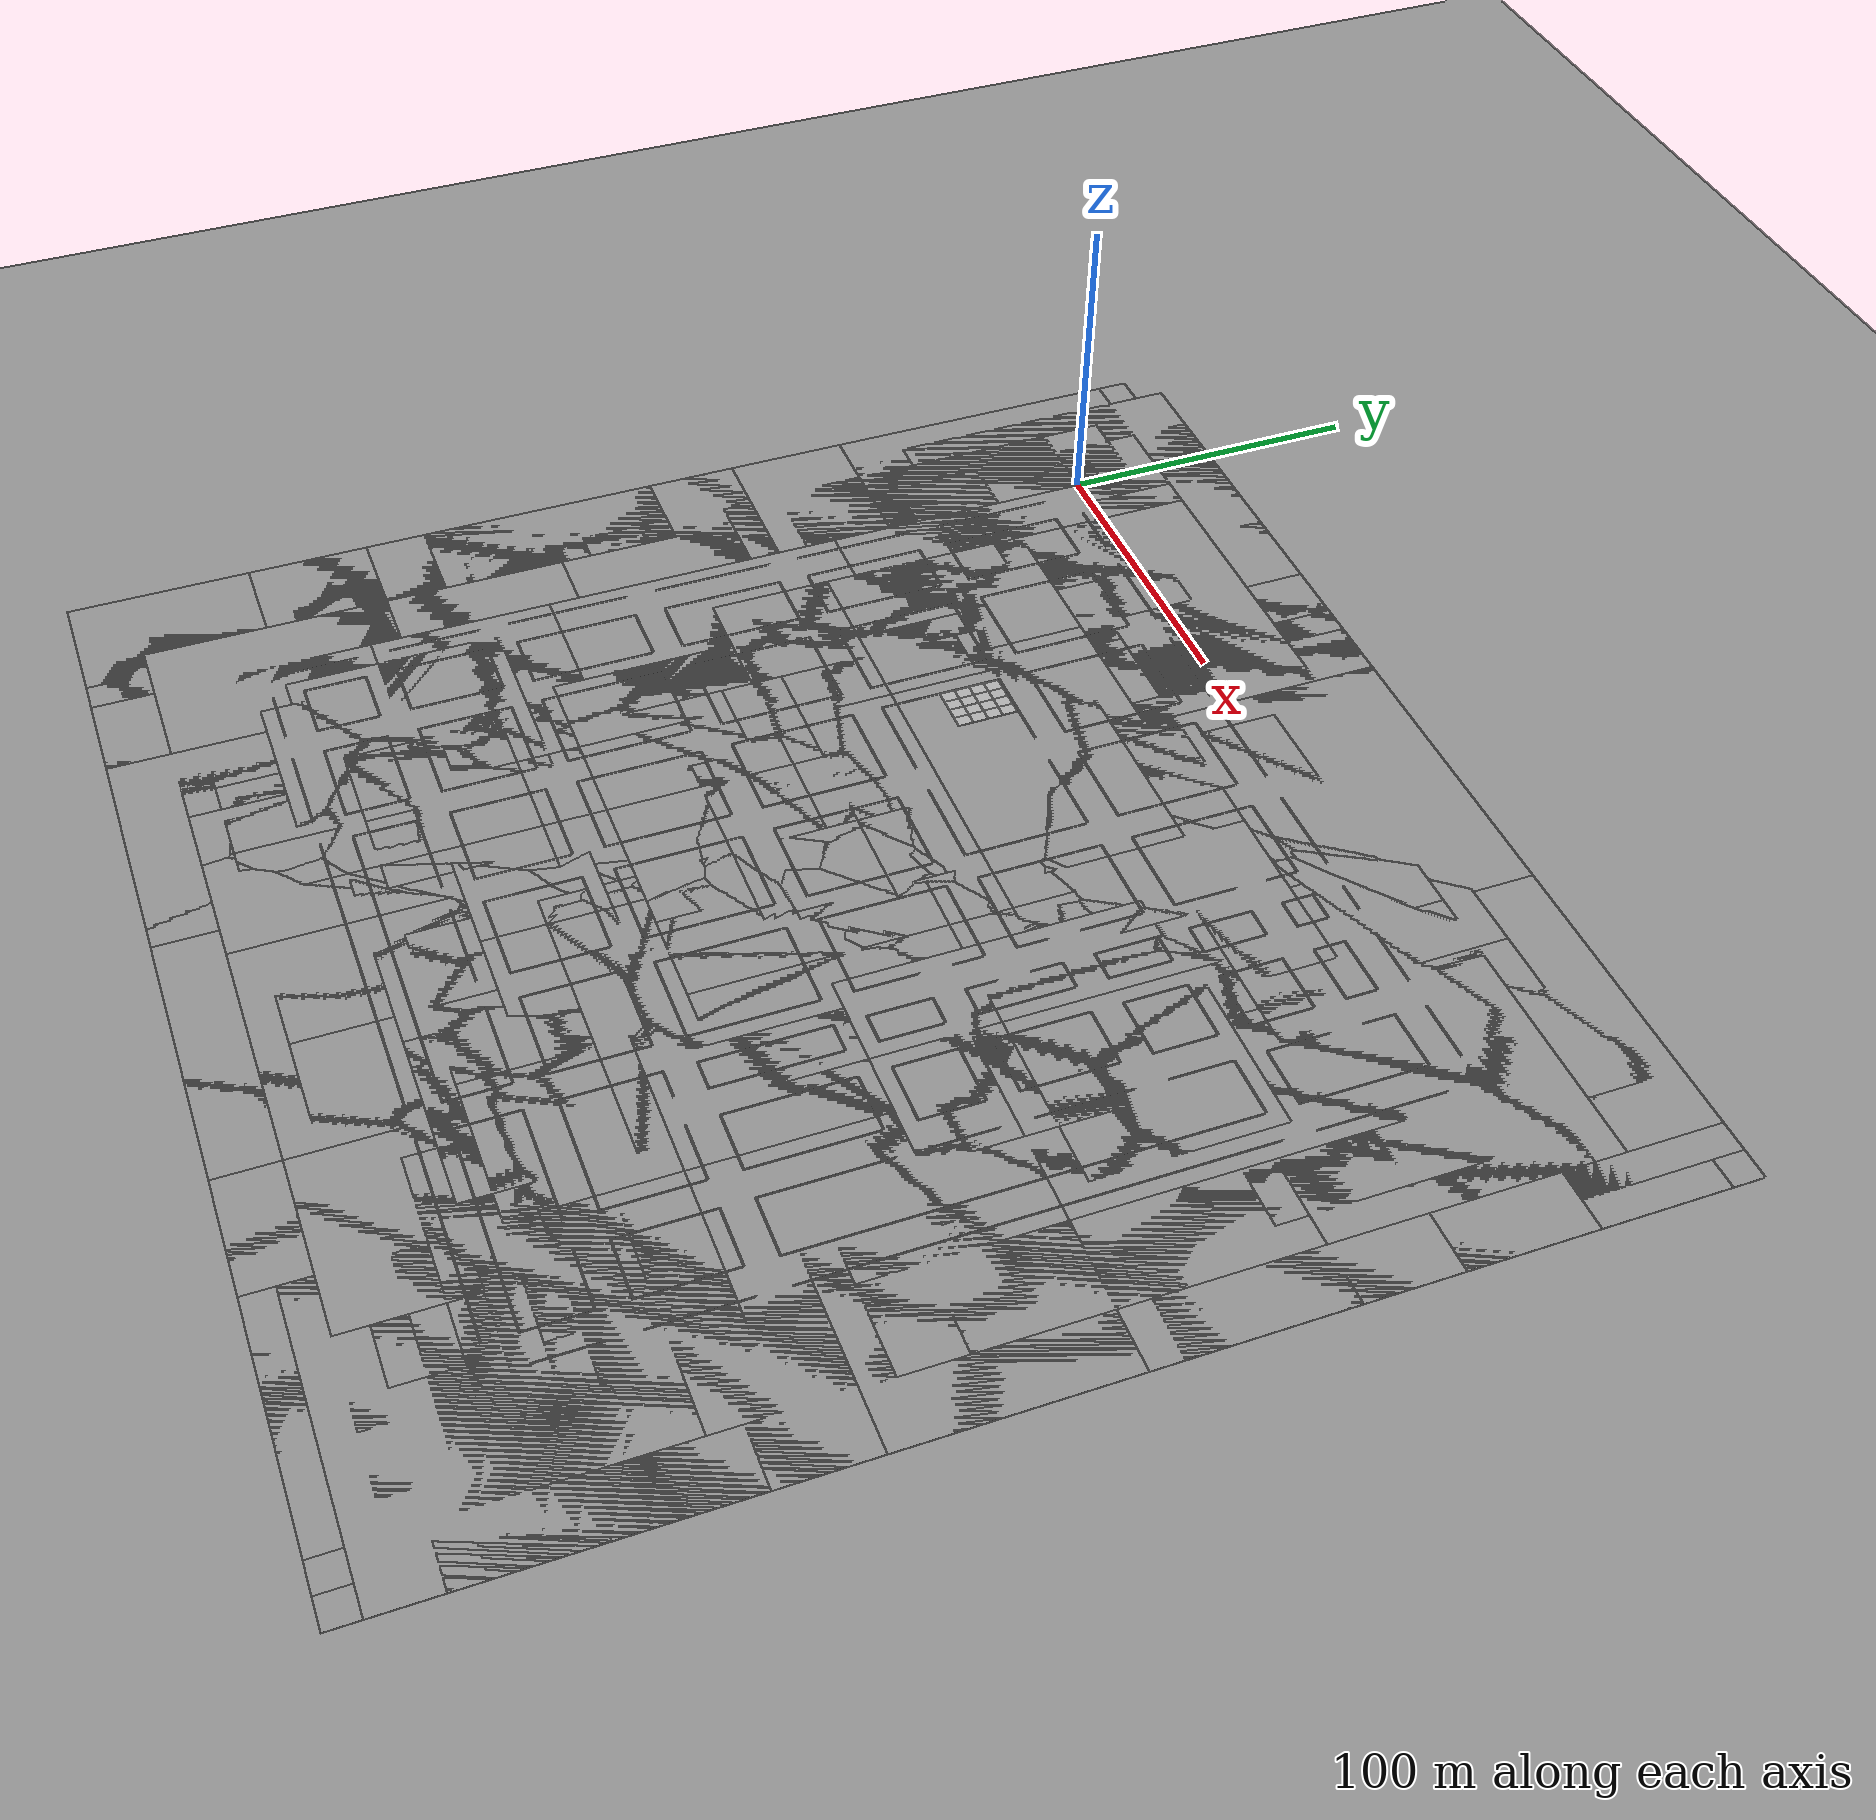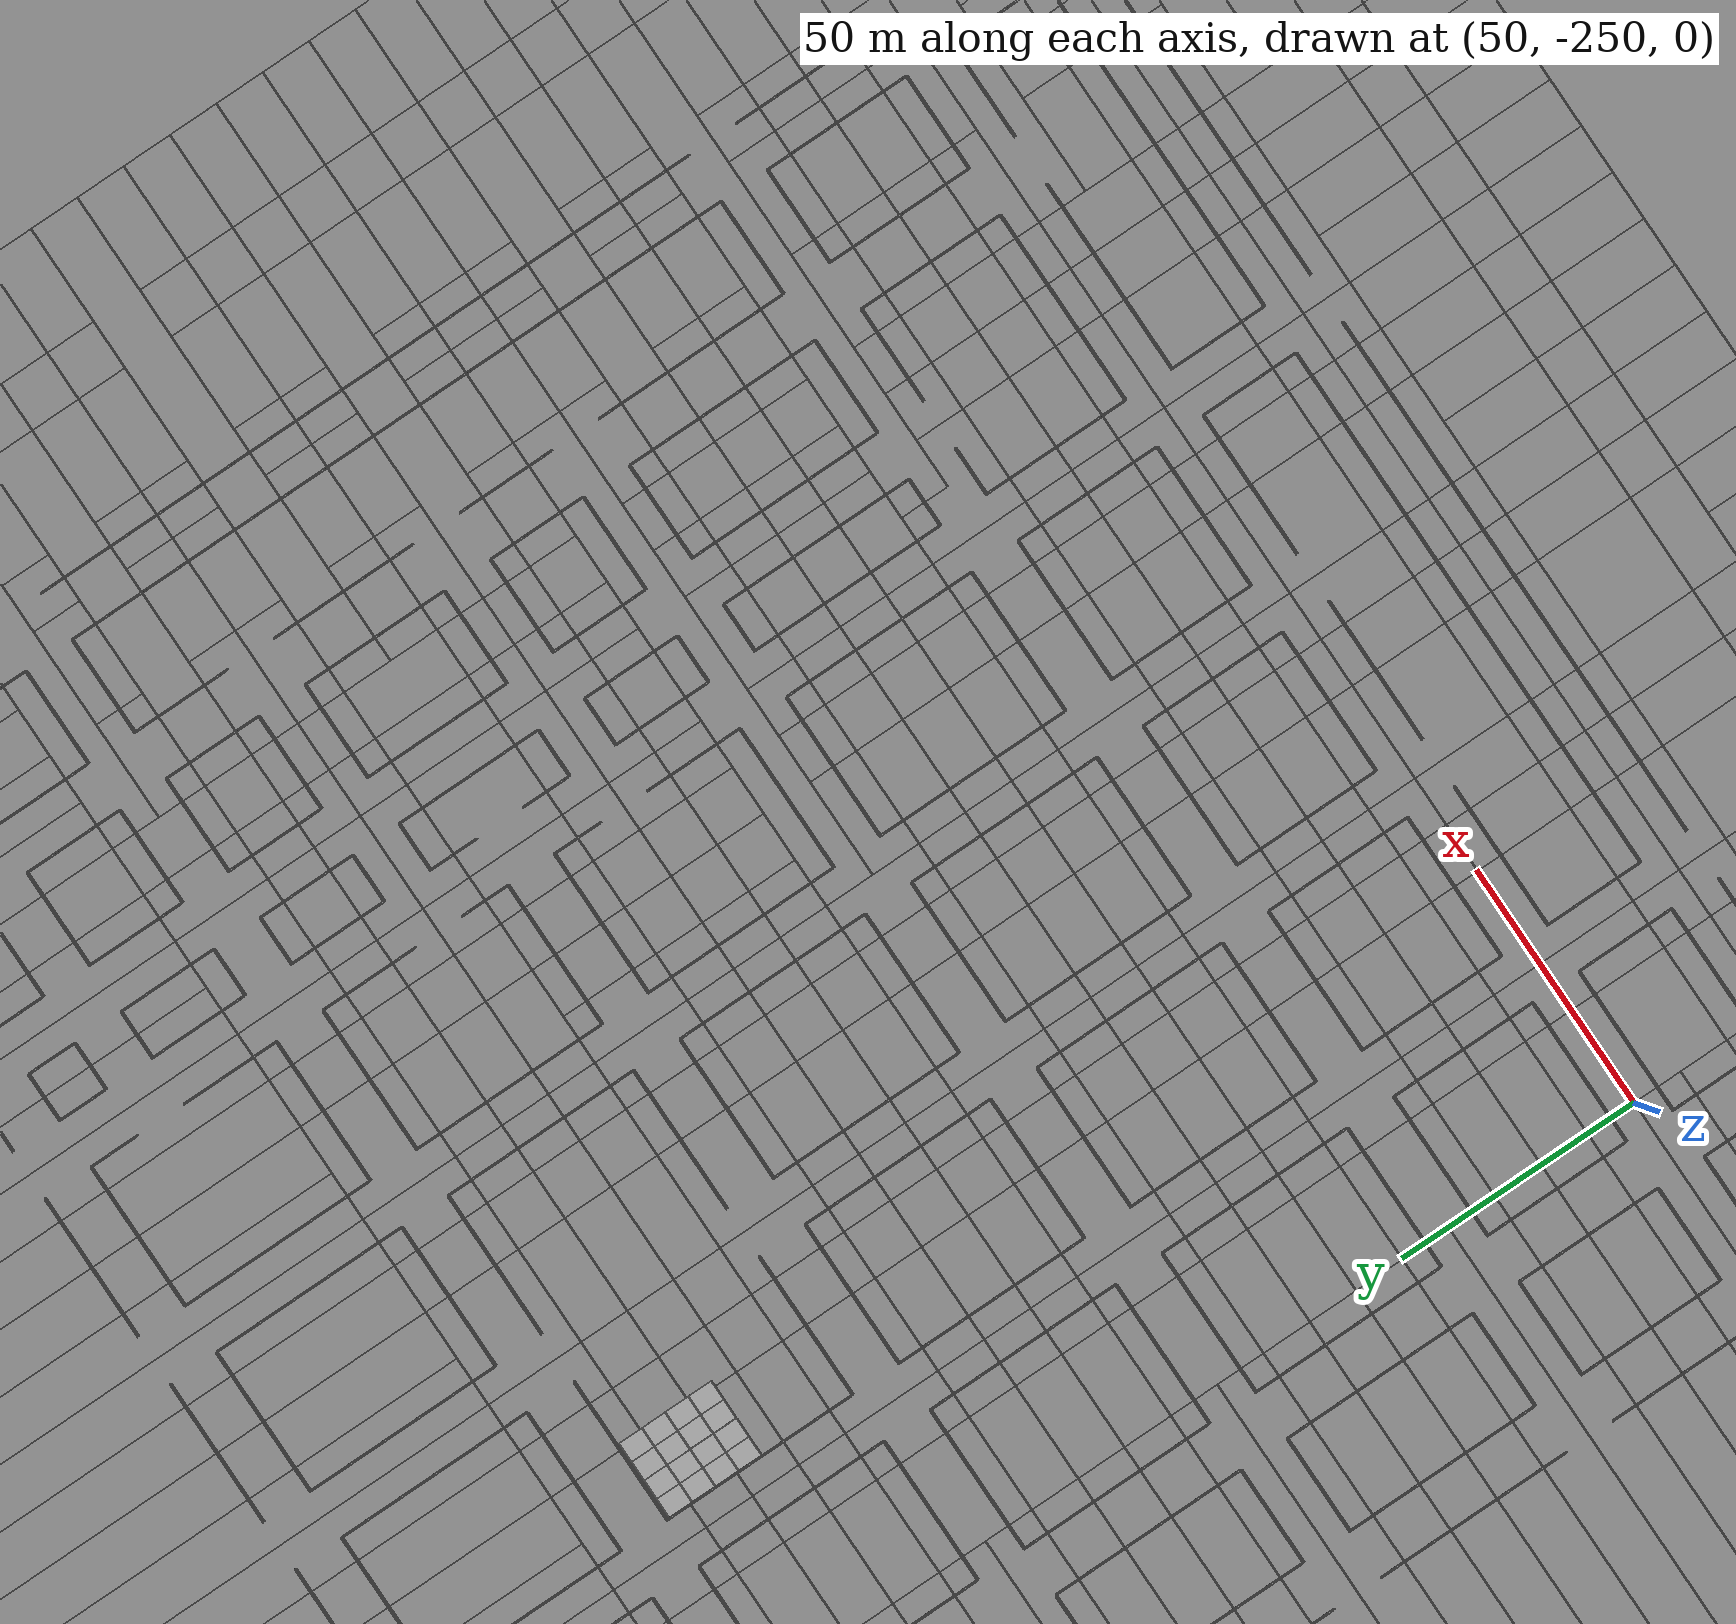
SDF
<sdf version="1.6">
 <world name="road_test">
  <scene>
   <ambient>120 120 120 255</ambient>
   <sky><clouds><speed>5</speed></clouds><time>12</time></sky>
   <background>0.7 0.7 0.7 1</background>
   <shadows>1</shadows>
  </scene>
  <model name="ground_plane_0_0">
   <static>1</static>
   <link name="ground_plane::link">
    <collision name="collision">
     <geometry><plane><normal>0 0 1</normal><size>100 100</size></plane></geometry>
     <surface><friction><ode><mu>100</mu><mu2>50</mu2></ode></friction></surface>
    </collision>
    <visual name="visual">
     <cast_shadows>0</cast_shadows>
     <geometry><plane><normal>0 0 1</normal><size>100 100</size></plane></geometry>
     <material>
      <script><uri>file://media/materials/scripts/gazebo.material</uri><name>Gazebo/Grey</name></script>
     </material>
    </visual>
   </link>
  </model>
  <model name="ground_plane_0_1">
   <static>1</static>
   <link name="ground_plane::link">
    <collision name="collision">
     <geometry><plane><normal>0 0 1</normal><size>100 100</size></plane></geometry>
     <surface><friction><ode><mu>100</mu><mu2>50</mu2></ode></friction></surface>
    </collision>
    <visual name="visual">
     <cast_shadows>0</cast_shadows>
     <geometry><plane><normal>0 0 1</normal><size>100 100</size></plane></geometry>
     <material>
      <script><uri>file://media/materials/scripts/gazebo.material</uri><name>Gazebo/Grey</name></script>
     </material>
    </visual>
   </link>
   <pose>10 0 0 0 -0 0</pose>
  </model>
  <model name="ground_plane_0_2">
   <static>1</static>
   <link name="ground_plane::link">
    <collision name="collision">
     <geometry><plane><normal>0 0 1</normal><size>100 100</size></plane></geometry>
     <surface><friction><ode><mu>100</mu><mu2>50</mu2></ode></friction></surface>
    </collision>
    <visual name="visual">
     <cast_shadows>0</cast_shadows>
     <geometry><plane><normal>0 0 1</normal><size>100 100</size></plane></geometry>
     <material>
      <script><uri>file://media/materials/scripts/gazebo.material</uri><name>Gazebo/Grey</name></script>
     </material>
    </visual>
   </link>
   <pose>20 0 0 0 -0 0</pose>
  </model>
  <model name="ground_plane_0_3">
   <static>1</static>
   <link name="ground_plane::link">
    <collision name="collision">
     <geometry><plane><normal>0 0 1</normal><size>100 100</size></plane></geometry>
     <surface><friction><ode><mu>100</mu><mu2>50</mu2></ode></friction></surface>
    </collision>
    <visual name="visual">
     <cast_shadows>0</cast_shadows>
     <geometry><plane><normal>0 0 1</normal><size>100 100</size></plane></geometry>
     <material>
      <script><uri>file://media/materials/scripts/gazebo.material</uri><name>Gazebo/Grey</name></script>
     </material>
    </visual>
   </link>
   <pose>30 0 0 0 -0 0</pose>
  </model>
  <model name="ground_plane_0_4">
   <static>1</static>
   <link name="ground_plane::link">
    <collision name="collision">
     <geometry><plane><normal>0 0 1</normal><size>100 100</size></plane></geometry>
     <surface><friction><ode><mu>100</mu><mu2>50</mu2></ode></friction></surface>
    </collision>
    <visual name="visual">
     <cast_shadows>0</cast_shadows>
     <geometry><plane><normal>0 0 1</normal><size>100 100</size></plane></geometry>
     <material>
      <script><uri>file://media/materials/scripts/gazebo.material</uri><name>Gazebo/Grey</name></script>
     </material>
    </visual>
   </link>
   <pose>40 0 0 0 -0 0</pose>
  </model>
  <model name="ground_plane_0_5">
   <static>1</static>
   <link name="ground_plane::link">
    <collision name="collision">
     <geometry><plane><normal>0 0 1</normal><size>100 100</size></plane></geometry>
     <surface><friction><ode><mu>100</mu><mu2>50</mu2></ode></friction></surface>
    </collision>
    <visual name="visual">
     <cast_shadows>0</cast_shadows>
     <geometry><plane><normal>0 0 1</normal><size>100 100</size></plane></geometry>
     <material>
      <script><uri>file://media/materials/scripts/gazebo.material</uri><name>Gazebo/Grey</name></script>
     </material>
    </visual>
   </link>
   <pose>50 0 0 0 -0 0</pose>
  </model>
  <model name="ground_plane_0_6">
   <static>1</static>
   <link name="ground_plane::link">
    <collision name="collision">
     <geometry><plane><normal>0 0 1</normal><size>100 100</size></plane></geometry>
     <surface><friction><ode><mu>100</mu><mu2>50</mu2></ode></friction></surface>
    </collision>
    <visual name="visual">
     <cast_shadows>0</cast_shadows>
     <geometry><plane><normal>0 0 1</normal><size>100 100</size></plane></geometry>
     <material>
      <script><uri>file://media/materials/scripts/gazebo.material</uri><name>Gazebo/Grey</name></script>
     </material>
    </visual>
   </link>
   <pose>60 0 0 0 -0 0</pose>
  </model>
  <model name="ground_plane_0_7">
   <static>1</static>
   <link name="ground_plane::link">
    <collision name="collision">
     <geometry><plane><normal>0 0 1</normal><size>100 100</size></plane></geometry>
     <surface><friction><ode><mu>100</mu><mu2>50</mu2></ode></friction></surface>
    </collision>
    <visual name="visual">
     <cast_shadows>0</cast_shadows>
     <geometry><plane><normal>0 0 1</normal><size>100 100</size></plane></geometry>
     <material>
      <script><uri>file://media/materials/scripts/gazebo.material</uri><name>Gazebo/Grey</name></script>
     </material>
    </visual>
   </link>
   <pose>70 0 0 0 -0 0</pose>
  </model>
  <model name="ground_plane_0_8">
   <static>1</static>
   <link name="ground_plane::link">
    <collision name="collision">
     <geometry><plane><normal>0 0 1</normal><size>100 100</size></plane></geometry>
     <surface><friction><ode><mu>100</mu><mu2>50</mu2></ode></friction></surface>
    </collision>
    <visual name="visual">
     <cast_shadows>0</cast_shadows>
     <geometry><plane><normal>0 0 1</normal><size>100 100</size></plane></geometry>
     <material>
      <script><uri>file://media/materials/scripts/gazebo.material</uri><name>Gazebo/Grey</name></script>
     </material>
    </visual>
   </link>
   <pose>80 0 0 0 -0 0</pose>
  </model>
  <model name="ground_plane_0_9">
   <static>1</static>
   <link name="ground_plane::link">
    <collision name="collision">
     <geometry><plane><normal>0 0 1</normal><size>100 100</size></plane></geometry>
     <surface><friction><ode><mu>100</mu><mu2>50</mu2></ode></friction></surface>
    </collision>
    <visual name="visual">
     <cast_shadows>0</cast_shadows>
     <geometry><plane><normal>0 0 1</normal><size>100 100</size></plane></geometry>
     <material>
      <script><uri>file://media/materials/scripts/gazebo.material</uri><name>Gazebo/Grey</name></script>
     </material>
    </visual>
   </link>
   <pose>90 0 0 0 -0 0</pose>
  </model>
  <model name="ground_plane_0_10">
   <static>1</static>
   <link name="ground_plane::link">
    <collision name="collision">
     <geometry><plane><normal>0 0 1</normal><size>100 100</size></plane></geometry>
     <surface><friction><ode><mu>100</mu><mu2>50</mu2></ode></friction></surface>
    </collision>
    <visual name="visual">
     <cast_shadows>0</cast_shadows>
     <geometry><plane><normal>0 0 1</normal><size>100 100</size></plane></geometry>
     <material>
      <script><uri>file://media/materials/scripts/gazebo.material</uri><name>Gazebo/Grey</name></script>
     </material>
    </visual>
   </link>
   <pose>100 0 0 0 -0 0</pose>
  </model>
  <model name="ground_plane_0_11">
   <static>1</static>
   <link name="ground_plane::link">
    <collision name="collision">
     <geometry><plane><normal>0 0 1</normal><size>100 100</size></plane></geometry>
     <surface><friction><ode><mu>100</mu><mu2>50</mu2></ode></friction></surface>
    </collision>
    <visual name="visual">
     <cast_shadows>0</cast_shadows>
     <geometry><plane><normal>0 0 1</normal><size>100 100</size></plane></geometry>
     <material>
      <script><uri>file://media/materials/scripts/gazebo.material</uri><name>Gazebo/Grey</name></script>
     </material>
    </visual>
   </link>
   <pose>110 0 0 0 -0 0</pose>
  </model>
  <model name="ground_plane_0_12">
   <static>1</static>
   <link name="ground_plane::link">
    <collision name="collision">
     <geometry><plane><normal>0 0 1</normal><size>100 100</size></plane></geometry>
     <surface><friction><ode><mu>100</mu><mu2>50</mu2></ode></friction></surface>
    </collision>
    <visual name="visual">
     <cast_shadows>0</cast_shadows>
     <geometry><plane><normal>0 0 1</normal><size>100 100</size></plane></geometry>
     <material>
      <script><uri>file://media/materials/scripts/gazebo.material</uri><name>Gazebo/Grey</name></script>
     </material>
    </visual>
   </link>
   <pose>120 0 0 0 -0 0</pose>
  </model>
  <model name="ground_plane_0_13">
   <static>1</static>
   <link name="ground_plane::link">
    <collision name="collision">
     <geometry><plane><normal>0 0 1</normal><size>100 100</size></plane></geometry>
     <surface><friction><ode><mu>100</mu><mu2>50</mu2></ode></friction></surface>
    </collision>
    <visual name="visual">
     <cast_shadows>0</cast_shadows>
     <geometry><plane><normal>0 0 1</normal><size>100 100</size></plane></geometry>
     <material>
      <script><uri>file://media/materials/scripts/gazebo.material</uri><name>Gazebo/Grey</name></script>
     </material>
    </visual>
   </link>
   <pose>130 0 0 0 -0 0</pose>
  </model>
  <model name="ground_plane_0_14">
   <static>1</static>
   <link name="ground_plane::link">
    <collision name="collision">
     <geometry><plane><normal>0 0 1</normal><size>100 100</size></plane></geometry>
     <surface><friction><ode><mu>100</mu><mu2>50</mu2></ode></friction></surface>
    </collision>
    <visual name="visual">
     <cast_shadows>0</cast_shadows>
     <geometry><plane><normal>0 0 1</normal><size>100 100</size></plane></geometry>
     <material>
      <script><uri>file://media/materials/scripts/gazebo.material</uri><name>Gazebo/Grey</name></script>
     </material>
    </visual>
   </link>
   <pose>140 0 0 0 -0 0</pose>
  </model>
  <model name="ground_plane_0_15">
   <static>1</static>
   <link name="ground_plane::link">
    <collision name="collision">
     <geometry><plane><normal>0 0 1</normal><size>100 100</size></plane></geometry>
     <surface><friction><ode><mu>100</mu><mu2>50</mu2></ode></friction></surface>
    </collision>
    <visual name="visual">
     <cast_shadows>0</cast_shadows>
     <geometry><plane><normal>0 0 1</normal><size>100 100</size></plane></geometry>
     <material>
      <script><uri>file://media/materials/scripts/gazebo.material</uri><name>Gazebo/Grey</name></script>
     </material>
    </visual>
   </link>
   <pose>150 0 0 0 -0 0</pose>
  </model>
  <model name="ground_plane_0_16">
   <static>1</static>
   <link name="ground_plane::link">
    <collision name="collision">
     <geometry><plane><normal>0 0 1</normal><size>100 100</size></plane></geometry>
     <surface><friction><ode><mu>100</mu><mu2>50</mu2></ode></friction></surface>
    </collision>
    <visual name="visual">
     <cast_shadows>0</cast_shadows>
     <geometry><plane><normal>0 0 1</normal><size>100 100</size></plane></geometry>
     <material>
      <script><uri>file://media/materials/scripts/gazebo.material</uri><name>Gazebo/Grey</name></script>
     </material>
    </visual>
   </link>
   <pose>160 0 0 0 -0 0</pose>
  </model>
  <model name="ground_plane_0_17">
   <static>1</static>
   <link name="ground_plane::link">
    <collision name="collision">
     <geometry><plane><normal>0 0 1</normal><size>100 100</size></plane></geometry>
     <surface><friction><ode><mu>100</mu><mu2>50</mu2></ode></friction></surface>
    </collision>
    <visual name="visual">
     <cast_shadows>0</cast_shadows>
     <geometry><plane><normal>0 0 1</normal><size>100 100</size></plane></geometry>
     <material>
      <script><uri>file://media/materials/scripts/gazebo.material</uri><name>Gazebo/Grey</name></script>
     </material>
    </visual>
   </link>
   <pose>170 0 0 0 -0 0</pose>
  </model>
  <model name="ground_plane_0_18">
   <static>1</static>
   <link name="ground_plane::link">
    <collision name="collision">
     <geometry><plane><normal>0 0 1</normal><size>100 100</size></plane></geometry>
     <surface><friction><ode><mu>100</mu><mu2>50</mu2></ode></friction></surface>
    </collision>
    <visual name="visual">
     <cast_shadows>0</cast_shadows>
     <geometry><plane><normal>0 0 1</normal><size>100 100</size></plane></geometry>
     <material>
      <script><uri>file://media/materials/scripts/gazebo.material</uri><name>Gazebo/Grey</name></script>
     </material>
    </visual>
   </link>
   <pose>180 0 0 0 -0 0</pose>
  </model>
  <model name="ground_plane_0_19">
   <static>1</static>
   <link name="ground_plane::link">
    <collision name="collision">
     <geometry><plane><normal>0 0 1</normal><size>100 100</size></plane></geometry>
     <surface><friction><ode><mu>100</mu><mu2>50</mu2></ode></friction></surface>
    </collision>
    <visual name="visual">
     <cast_shadows>0</cast_shadows>
     <geometry><plane><normal>0 0 1</normal><size>100 100</size></plane></geometry>
     <material>
      <script><uri>file://media/materials/scripts/gazebo.material</uri><name>Gazebo/Grey</name></script>
     </material>
    </visual>
   </link>
   <pose>190 0 0 0 -0 0</pose>
  </model>
  <model name="ground_plane_0_20">
   <static>1</static>
   <link name="ground_plane::link">
    <collision name="collision">
     <geometry><plane><normal>0 0 1</normal><size>100 100</size></plane></geometry>
     <surface><friction><ode><mu>100</mu><mu2>50</mu2></ode></friction></surface>
    </collision>
    <visual name="visual">
     <cast_shadows>0</cast_shadows>
     <geometry><plane><normal>0 0 1</normal><size>100 100</size></plane></geometry>
     <material>
      <script><uri>file://media/materials/scripts/gazebo.material</uri><name>Gazebo/Grey</name></script>
     </material>
    </visual>
   </link>
   <pose>200 0 0 0 -0 0</pose>
  </model>
  <model name="ground_plane_0_21">
   <static>1</static>
   <link name="ground_plane::link">
    <collision name="collision">
     <geometry><plane><normal>0 0 1</normal><size>100 100</size></plane></geometry>
     <surface><friction><ode><mu>100</mu><mu2>50</mu2></ode></friction></surface>
    </collision>
    <visual name="visual">
     <cast_shadows>0</cast_shadows>
     <geometry><plane><normal>0 0 1</normal><size>100 100</size></plane></geometry>
     <material>
      <script><uri>file://media/materials/scripts/gazebo.material</uri><name>Gazebo/Grey</name></script>
     </material>
    </visual>
   </link>
   <pose>210 0 0 0 -0 0</pose>
  </model>
  <model name="ground_plane_0_22">
   <static>1</static>
   <link name="ground_plane::link">
    <collision name="collision">
     <geometry><plane><normal>0 0 1</normal><size>100 100</size></plane></geometry>
     <surface><friction><ode><mu>100</mu><mu2>50</mu2></ode></friction></surface>
    </collision>
    <visual name="visual">
     <cast_shadows>0</cast_shadows>
     <geometry><plane><normal>0 0 1</normal><size>100 100</size></plane></geometry>
     <material>
      <script><uri>file://media/materials/scripts/gazebo.material</uri><name>Gazebo/Grey</name></script>
     </material>
    </visual>
   </link>
   <pose>220 0 0 0 -0 0</pose>
  </model>
  <model name="ground_plane_0_23">
   <static>1</static>
   <link name="ground_plane::link">
    <collision name="collision">
     <geometry><plane><normal>0 0 1</normal><size>100 100</size></plane></geometry>
     <surface><friction><ode><mu>100</mu><mu2>50</mu2></ode></friction></surface>
    </collision>
    <visual name="visual">
     <cast_shadows>0</cast_shadows>
     <geometry><plane><normal>0 0 1</normal><size>100 100</size></plane></geometry>
     <material>
      <script><uri>file://media/materials/scripts/gazebo.material</uri><name>Gazebo/Grey</name></script>
     </material>
    </visual>
   </link>
   <pose>230 0 0 0 -0 0</pose>
  </model>
  <model name="ground_plane_0_24">
   <static>1</static>
   <link name="ground_plane::link">
    <collision name="collision">
     <geometry><plane><normal>0 0 1</normal><size>100 100</size></plane></geometry>
     <surface><friction><ode><mu>100</mu><mu2>50</mu2></ode></friction></surface>
    </collision>
    <visual name="visual">
     <cast_shadows>0</cast_shadows>
     <geometry><plane><normal>0 0 1</normal><size>100 100</size></plane></geometry>
     <material>
      <script><uri>file://media/materials/scripts/gazebo.material</uri><name>Gazebo/Grey</name></script>
     </material>
    </visual>
   </link>
   <pose>240 0 0 0 -0 0</pose>
  </model>
  <model name="ground_plane_0_25">
   <static>1</static>
   <link name="ground_plane::link">
    <collision name="collision">
     <geometry><plane><normal>0 0 1</normal><size>100 100</size></plane></geometry>
     <surface><friction><ode><mu>100</mu><mu2>50</mu2></ode></friction></surface>
    </collision>
    <visual name="visual">
     <cast_shadows>0</cast_shadows>
     <geometry><plane><normal>0 0 1</normal><size>100 100</size></plane></geometry>
     <material>
      <script><uri>file://media/materials/scripts/gazebo.material</uri><name>Gazebo/Grey</name></script>
     </material>
    </visual>
   </link>
   <pose>250 0 0 0 -0 0</pose>
  </model>
  <model name="ground_plane_0_26">
   <static>1</static>
   <link name="ground_plane::link">
    <collision name="collision">
     <geometry><plane><normal>0 0 1</normal><size>100 100</size></plane></geometry>
     <surface><friction><ode><mu>100</mu><mu2>50</mu2></ode></friction></surface>
    </collision>
    <visual name="visual">
     <cast_shadows>0</cast_shadows>
     <geometry><plane><normal>0 0 1</normal><size>100 100</size></plane></geometry>
     <material>
      <script><uri>file://media/materials/scripts/gazebo.material</uri><name>Gazebo/Grey</name></script>
     </material>
    </visual>
   </link>
   <pose>260 0 0 0 -0 0</pose>
  </model>
  <model name="ground_plane_0_27">
   <static>1</static>
   <link name="ground_plane::link">
    <collision name="collision">
     <geometry><plane><normal>0 0 1</normal><size>100 100</size></plane></geometry>
     <surface><friction><ode><mu>100</mu><mu2>50</mu2></ode></friction></surface>
    </collision>
    <visual name="visual">
     <cast_shadows>0</cast_shadows>
     <geometry><plane><normal>0 0 1</normal><size>100 100</size></plane></geometry>
     <material>
      <script><uri>file://media/materials/scripts/gazebo.material</uri><name>Gazebo/Grey</name></script>
     </material>
    </visual>
   </link>
   <pose>270 0 0 0 -0 0</pose>
  </model>
  <model name="ground_plane_0_28">
   <static>1</static>
   <link name="ground_plane::link">
    <collision name="collision">
     <geometry><plane><normal>0 0 1</normal><size>100 100</size></plane></geometry>
     <surface><friction><ode><mu>100</mu><mu2>50</mu2></ode></friction></surface>
    </collision>
    <visual name="visual">
     <cast_shadows>0</cast_shadows>
     <geometry><plane><normal>0 0 1</normal><size>100 100</size></plane></geometry>
     <material>
      <script><uri>file://media/materials/scripts/gazebo.material</uri><name>Gazebo/Grey</name></script>
     </material>
    </visual>
   </link>
   <pose>280 0 0 0 -0 0</pose>
  </model>
  <model name="ground_plane_0_29">
   <static>1</static>
   <link name="ground_plane::link">
    <collision name="collision">
     <geometry><plane><normal>0 0 1</normal><size>100 100</size></plane></geometry>
     <surface><friction><ode><mu>100</mu><mu2>50</mu2></ode></friction></surface>
    </collision>
    <visual name="visual">
     <cast_shadows>0</cast_shadows>
     <geometry><plane><normal>0 0 1</normal><size>100 100</size></plane></geometry>
     <material>
      <script><uri>file://media/materials/scripts/gazebo.material</uri><name>Gazebo/Grey</name></script>
     </material>
    </visual>
   </link>
   <pose>290 0 0 0 -0 0</pose>
  </model>
  <model name="ground_plane_1_0">
   <static>1</static>
   <link name="ground_plane::link">
    <collision name="collision">
     <geometry><plane><normal>0 0 1</normal><size>100 100</size></plane></geometry>
     <surface><friction><ode><mu>100</mu><mu2>50</mu2></ode></friction></surface>
    </collision>
    <visual name="visual">
     <cast_shadows>0</cast_shadows>
     <geometry><plane><normal>0 0 1</normal><size>100 100</size></plane></geometry>
     <material>
      <script><uri>file://media/materials/scripts/gazebo.material</uri><name>Gazebo/Grey</name></script>
     </material>
    </visual>
   </link>
   <pose>0 -10 0 0 -0 0</pose>
  </model>
  <model name="road_intersection_1_1">
   <static>1</static>
   <link name="road_intersection::link">
    <collision name="collision">
     <geometry><plane><normal>0 0 1</normal><size>10 10</size></plane></geometry>
     <surface><friction><ode><mu>75</mu><mu2>75</mu2></ode></friction></surface>
    </collision>
    <visual name="visual">
     <cast_shadows>0</cast_shadows>
     <geometry><plane><normal>0 0 1</normal><size>10 10</size></plane></geometry>
     <material>
      <script>
       <uri>model://road_intersection/materials/scripts</uri>
       <uri>model://road_intersection/materials/textures</uri>
       <name>road_intersection/Image</name>
      </script>
     </material>
    </visual>
   </link>
   <pose>10 -10 0.02 0 -0 0</pose>
  </model>
  <model name="road_straight_1_2">
   <static>1</static>
   <link name="road_straight::link">
    <collision name="collision">
     <geometry><plane><normal>0 0 1</normal><size>10 10</size></plane></geometry>
     <surface><friction><ode><mu>75</mu><mu2>75</mu2></ode></friction></surface>
    </collision>
    <visual name="visual">
     <cast_shadows>0</cast_shadows>
     <geometry><plane><normal>0 0 1</normal><size>10 10</size></plane></geometry>
     <material>
      <script>
       <uri>model://road_straight/materials/scripts</uri>
       <uri>model://road_straight/materials/textures</uri>
       <name>road_straight/Image</name>
      </script>
     </material>
    </visual>
   </link>
   <pose>20 -10 0.02 0 -0 0</pose>
  </model>
  <model name="curb_straight_1_2">
   <link name="curb_staight::Wall_5">
    <collision name="Wall_5_Collision">
     <geometry><box><size>10 0.3 0.22</size></box></geometry>
     <pose>0 -5 0 0 -0 0</pose>
    </collision>
    <visual name="Wall_5_Visual">
     <pose>0 -5 0 0 -0 0</pose>
     <geometry><box><size>10 0.3 0.22</size></box></geometry>
     <material>
      <script><uri>file://media/materials/scripts/gazebo.material</uri><name>Gazebo/Grey</name></script>
      <ambient>1 1 1 1</ambient>
     </material>
     <meta><layer>0</layer></meta>
    </visual>
   </link>
   <link name="curb_staight::Wall_7">
    <collision name="Wall_7_Collision">
     <geometry><box><size>10 0.3 0.22</size></box></geometry>
     <pose>0 5 0 0 -0 0</pose>
    </collision>
    <visual name="Wall_7_Visual">
     <pose>0 5 0 0 -0 0</pose>
     <geometry><box><size>10 0.3 0.22</size></box></geometry>
     <material>
      <script><uri>file://media/materials/scripts/gazebo.material</uri><name>Gazebo/Grey</name></script>
      <ambient>1 1 1 1</ambient>
     </material>
     <meta><layer>0</layer></meta>
    </visual>
   </link>
   <static>1</static>
   <pose>20 -10 0.02 0 -0 0</pose>
  </model>
  <model name="road_straight_1_3">
   <static>1</static>
   <link name="road_straight::link">
    <collision name="collision">
     <geometry><plane><normal>0 0 1</normal><size>10 10</size></plane></geometry>
     <surface><friction><ode><mu>75</mu><mu2>75</mu2></ode></friction></surface>
    </collision>
    <visual name="visual">
     <cast_shadows>0</cast_shadows>
     <geometry><plane><normal>0 0 1</normal><size>10 10</size></plane></geometry>
     <material>
      <script>
       <uri>model://road_straight/materials/scripts</uri>
       <uri>model://road_straight/materials/textures</uri>
       <name>road_straight/Image</name>
      </script>
     </material>
    </visual>
   </link>
   <pose>30 -10 0.02 0 -0 0</pose>
  </model>
  <model name="curb_straight_1_3">
   <link name="curb_staight::Wall_5">
    <collision name="Wall_5_Collision">
     <geometry><box><size>10 0.3 0.22</size></box></geometry>
     <pose>0 -5 0 0 -0 0</pose>
    </collision>
    <visual name="Wall_5_Visual">
     <pose>0 -5 0 0 -0 0</pose>
     <geometry><box><size>10 0.3 0.22</size></box></geometry>
     <material>
      <script><uri>file://media/materials/scripts/gazebo.material</uri><name>Gazebo/Grey</name></script>
      <ambient>1 1 1 1</ambient>
     </material>
     <meta><layer>0</layer></meta>
    </visual>
   </link>
   <link name="curb_staight::Wall_7">
    <collision name="Wall_7_Collision">
     <geometry><box><size>10 0.3 0.22</size></box></geometry>
     <pose>0 5 0 0 -0 0</pose>
    </collision>
    <visual name="Wall_7_Visual">
     <pose>0 5 0 0 -0 0</pose>
     <geometry><box><size>10 0.3 0.22</size></box></geometry>
     <material>
      <script><uri>file://media/materials/scripts/gazebo.material</uri><name>Gazebo/Grey</name></script>
      <ambient>1 1 1 1</ambient>
     </material>
     <meta><layer>0</layer></meta>
    </visual>
   </link>
   <static>1</static>
   <pose>30 -10 0.02 0 -0 0</pose>
  </model>
  <model name="road_intersection_1_4">
   <static>1</static>
   <link name="road_intersection::link">
    <collision name="collision">
     <geometry><plane><normal>0 0 1</normal><size>10 10</size></plane></geometry>
     <surface><friction><ode><mu>75</mu><mu2>75</mu2></ode></friction></surface>
    </collision>
    <visual name="visual">
     <cast_shadows>0</cast_shadows>
     <geometry><plane><normal>0 0 1</normal><size>10 10</size></plane></geometry>
     <material>
      <script>
       <uri>model://road_intersection/materials/scripts</uri>
       <uri>model://road_intersection/materials/textures</uri>
       <name>road_intersection/Image</name>
      </script>
     </material>
    </visual>
   </link>
   <pose>40 -10 0.02 0 -0 0</pose>
  </model>
  <model name="road_straight_1_5">
   <static>1</static>
   <link name="road_straight::link">
    <collision name="collision">
     <geometry><plane><normal>0 0 1</normal><size>10 10</size></plane></geometry>
     <surface><friction><ode><mu>75</mu><mu2>75</mu2></ode></friction></surface>
    </collision>
    <visual name="visual">
     <cast_shadows>0</cast_shadows>
     <geometry><plane><normal>0 0 1</normal><size>10 10</size></plane></geometry>
     <material>
      <script>
       <uri>model://road_straight/materials/scripts</uri>
       <uri>model://road_straight/materials/textures</uri>
       <name>road_straight/Image</name>
      </script>
     </material>
    </visual>
   </link>
   <pose>50 -10 0.02 0 -0 0</pose>
  </model>
  <model name="curb_straight_1_5">
   <link name="curb_staight::Wall_5">
    <collision name="Wall_5_Collision">
     <geometry><box><size>10 0.3 0.22</size></box></geometry>
     <pose>0 -5 0 0 -0 0</pose>
    </collision>
    <visual name="Wall_5_Visual">
     <pose>0 -5 0 0 -0 0</pose>
     <geometry><box><size>10 0.3 0.22</size></box></geometry>
     <material>
      <script><uri>file://media/materials/scripts/gazebo.material</uri><name>Gazebo/Grey</name></script>
      <ambient>1 1 1 1</ambient>
     </material>
     <meta><layer>0</layer></meta>
    </visual>
   </link>
   <link name="curb_staight::Wall_7">
    <collision name="Wall_7_Collision">
     <geometry><box><size>10 0.3 0.22</size></box></geometry>
     <pose>0 5 0 0 -0 0</pose>
    </collision>
    <visual name="Wall_7_Visual">
     <pose>0 5 0 0 -0 0</pose>
     <geometry><box><size>10 0.3 0.22</size></box></geometry>
     <material>
      <script><uri>file://media/materials/scripts/gazebo.material</uri><name>Gazebo/Grey</name></script>
      <ambient>1 1 1 1</ambient>
     </material>
     <meta><layer>0</layer></meta>
    </visual>
   </link>
   <static>1</static>
   <pose>50 -10 0.02 0 -0 0</pose>
  </model>
  <model name="road_straight_1_6">
   <static>1</static>
   <link name="road_straight::link">
    <collision name="collision">
     <geometry><plane><normal>0 0 1</normal><size>10 10</size></plane></geometry>
     <surface><friction><ode><mu>75</mu><mu2>75</mu2></ode></friction></surface>
    </collision>
    <visual name="visual">
     <cast_shadows>0</cast_shadows>
     <geometry><plane><normal>0 0 1</normal><size>10 10</size></plane></geometry>
     <material>
      <script>
       <uri>model://road_straight/materials/scripts</uri>
       <uri>model://road_straight/materials/textures</uri>
       <name>road_straight/Image</name>
      </script>
     </material>
    </visual>
   </link>
   <pose>60 -10 0.02 0 -0 0</pose>
  </model>
  <model name="curb_straight_1_6">
   <link name="curb_staight::Wall_5">
    <collision name="Wall_5_Collision">
     <geometry><box><size>10 0.3 0.22</size></box></geometry>
     <pose>0 -5 0 0 -0 0</pose>
    </collision>
    <visual name="Wall_5_Visual">
     <pose>0 -5 0 0 -0 0</pose>
     <geometry><box><size>10 0.3 0.22</size></box></geometry>
     <material>
      <script><uri>file://media/materials/scripts/gazebo.material</uri><name>Gazebo/Grey</name></script>
      <ambient>1 1 1 1</ambient>
     </material>
     <meta><layer>0</layer></meta>
    </visual>
   </link>
   <link name="curb_staight::Wall_7">
    <collision name="Wall_7_Collision">
     <geometry><box><size>10 0.3 0.22</size></box></geometry>
     <pose>0 5 0 0 -0 0</pose>
    </collision>
    <visual name="Wall_7_Visual">
     <pose>0 5 0 0 -0 0</pose>
     <geometry><box><size>10 0.3 0.22</size></box></geometry>
     <material>
      <script><uri>file://media/materials/scripts/gazebo.material</uri><name>Gazebo/Grey</name></script>
      <ambient>1 1 1 1</ambient>
     </material>
     <meta><layer>0</layer></meta>
    </visual>
   </link>
   <static>1</static>
   <pose>60 -10 0.02 0 -0 0</pose>
  </model>
  <model name="road_straight_1_7">
   <static>1</static>
   <link name="road_straight::link">
    <collision name="collision">
     <geometry><plane><normal>0 0 1</normal><size>10 10</size></plane></geometry>
     <surface><friction><ode><mu>75</mu><mu2>75</mu2></ode></friction></surface>
    </collision>
    <visual name="visual">
     <cast_shadows>0</cast_shadows>
     <geometry><plane><normal>0 0 1</normal><size>10 10</size></plane></geometry>
     <material>
      <script>
       <uri>model://road_straight/materials/scripts</uri>
       <uri>model://road_straight/materials/textures</uri>
       <name>road_straight/Image</name>
      </script>
     </material>
    </visual>
   </link>
   <pose>70 -10 0.02 0 -0 0</pose>
  </model>
  <model name="curb_straight_1_7">
   <link name="curb_staight::Wall_5">
    <collision name="Wall_5_Collision">
     <geometry><box><size>10 0.3 0.22</size></box></geometry>
     <pose>0 -5 0 0 -0 0</pose>
    </collision>
    <visual name="Wall_5_Visual">
     <pose>0 -5 0 0 -0 0</pose>
     <geometry><box><size>10 0.3 0.22</size></box></geometry>
     <material>
      <script><uri>file://media/materials/scripts/gazebo.material</uri><name>Gazebo/Grey</name></script>
      <ambient>1 1 1 1</ambient>
     </material>
     <meta><layer>0</layer></meta>
    </visual>
   </link>
   <link name="curb_staight::Wall_7">
    <collision name="Wall_7_Collision">
     <geometry><box><size>10 0.3 0.22</size></box></geometry>
     <pose>0 5 0 0 -0 0</pose>
    </collision>
    <visual name="Wall_7_Visual">
     <pose>0 5 0 0 -0 0</pose>
     <geometry><box><size>10 0.3 0.22</size></box></geometry>
     <material>
      <script><uri>file://media/materials/scripts/gazebo.material</uri><name>Gazebo/Grey</name></script>
      <ambient>1 1 1 1</ambient>
     </material>
     <meta><layer>0</layer></meta>
    </visual>
   </link>
   <static>1</static>
   <pose>70 -10 0.02 0 -0 0</pose>
  </model>
  <model name="road_intersection_1_8">
   <static>1</static>
   <link name="road_intersection::link">
    <collision name="collision">
     <geometry><plane><normal>0 0 1</normal><size>10 10</size></plane></geometry>
     <surface><friction><ode><mu>75</mu><mu2>75</mu2></ode></friction></surface>
    </collision>
    <visual name="visual">
     <cast_shadows>0</cast_shadows>
     <geometry><plane><normal>0 0 1</normal><size>10 10</size></plane></geometry>
     <material>
      <script>
       <uri>model://road_intersection/materials/scripts</uri>
       <uri>model://road_intersection/materials/textures</uri>
       <name>road_intersection/Image</name>
      </script>
     </material>
    </visual>
   </link>
   <pose>80 -10 0.02 0 -0 0</pose>
  </model>
  <model name="road_straight_1_9">
   <static>1</static>
   <link name="road_straight::link">
    <collision name="collision">
     <geometry><plane><normal>0 0 1</normal><size>10 10</size></plane></geometry>
     <surface><friction><ode><mu>75</mu><mu2>75</mu2></ode></friction></surface>
    </collision>
    <visual name="visual">
     <cast_shadows>0</cast_shadows>
     <geometry><plane><normal>0 0 1</normal><size>10 10</size></plane></geometry>
     <material>
      <script>
       <uri>model://road_straight/materials/scripts</uri>
       <uri>model://road_straight/materials/textures</uri>
       <name>road_straight/Image</name>
      </script>
     </material>
    </visual>
   </link>
   <pose>90 -10 0.02 0 -0 0</pose>
  </model>
  <model name="curb_straight_1_9">
   <link name="curb_staight::Wall_5">
    <collision name="Wall_5_Collision">
     <geometry><box><size>10 0.3 0.22</size></box></geometry>
     <pose>0 -5 0 0 -0 0</pose>
    </collision>
    <visual name="Wall_5_Visual">
     <pose>0 -5 0 0 -0 0</pose>
     <geometry><box><size>10 0.3 0.22</size></box></geometry>
     <material>
      <script><uri>file://media/materials/scripts/gazebo.material</uri><name>Gazebo/Grey</name></script>
      <ambient>1 1 1 1</ambient>
     </material>
     <meta><layer>0</layer></meta>
    </visual>
   </link>
   <link name="curb_staight::Wall_7">
    <collision name="Wall_7_Collision">
     <geometry><box><size>10 0.3 0.22</size></box></geometry>
     <pose>0 5 0 0 -0 0</pose>
    </collision>
    <visual name="Wall_7_Visual">
     <pose>0 5 0 0 -0 0</pose>
     <geometry><box><size>10 0.3 0.22</size></box></geometry>
     <material>
      <script><uri>file://media/materials/scripts/gazebo.material</uri><name>Gazebo/Grey</name></script>
      <ambient>1 1 1 1</ambient>
     </material>
     <meta><layer>0</layer></meta>
    </visual>
   </link>
   <static>1</static>
   <pose>90 -10 0.02 0 -0 0</pose>
  </model>
  <model name="road_straight_1_10">
   <static>1</static>
   <link name="road_straight::link">
    <collision name="collision">
     <geometry><plane><normal>0 0 1</normal><size>10 10</size></plane></geometry>
     <surface><friction><ode><mu>75</mu><mu2>75</mu2></ode></friction></surface>
    </collision>
    <visual name="visual">
     <cast_shadows>0</cast_shadows>
     <geometry><plane><normal>0 0 1</normal><size>10 10</size></plane></geometry>
     <material>
      <script>
       <uri>model://road_straight/materials/scripts</uri>
       <uri>model://road_straight/materials/textures</uri>
       <name>road_straight/Image</name>
      </script>
     </material>
    </visual>
   </link>
   <pose>100 -10 0.02 0 -0 0</pose>
  </model>
  <model name="curb_straight_1_10">
   <link name="curb_staight::Wall_5">
    <collision name="Wall_5_Collision">
     <geometry><box><size>10 0.3 0.22</size></box></geometry>
     <pose>0 -5 0 0 -0 0</pose>
    </collision>
    <visual name="Wall_5_Visual">
     <pose>0 -5 0 0 -0 0</pose>
     <geometry><box><size>10 0.3 0.22</size></box></geometry>
     <material>
      <script><uri>file://media/materials/scripts/gazebo.material</uri><name>Gazebo/Grey</name></script>
      <ambient>1 1 1 1</ambient>
     </material>
     <meta><layer>0</layer></meta>
    </visual>
   </link>
   <link name="curb_staight::Wall_7">
    <collision name="Wall_7_Collision">
     <geometry><box><size>10 0.3 0.22</size></box></geometry>
     <pose>0 5 0 0 -0 0</pose>
    </collision>
    <visual name="Wall_7_Visual">
     <pose>0 5 0 0 -0 0</pose>
     <geometry><box><size>10 0.3 0.22</size></box></geometry>
     <material>
      <script><uri>file://media/materials/scripts/gazebo.material</uri><name>Gazebo/Grey</name></script>
      <ambient>1 1 1 1</ambient>
     </material>
     <meta><layer>0</layer></meta>
    </visual>
   </link>
   <static>1</static>
   <pose>100 -10 0.02 0 -0 0</pose>
  </model>
  <model name="road_straight_1_11">
   <static>1</static>
   <link name="road_straight::link">
    <collision name="collision">
     <geometry><plane><normal>0 0 1</normal><size>10 10</size></plane></geometry>
     <surface><friction><ode><mu>75</mu><mu2>75</mu2></ode></friction></surface>
    </collision>
    <visual name="visual">
     <cast_shadows>0</cast_shadows>
     <geometry><plane><normal>0 0 1</normal><size>10 10</size></plane></geometry>
     <material>
      <script>
       <uri>model://road_straight/materials/scripts</uri>
       <uri>model://road_straight/materials/textures</uri>
       <name>road_straight/Image</name>
      </script>
     </material>
    </visual>
   </link>
   <pose>110 -10 0.02 0 -0 0</pose>
  </model>
  <model name="curb_straight_1_11">
   <link name="curb_staight::Wall_5">
    <collision name="Wall_5_Collision">
     <geometry><box><size>10 0.3 0.22</size></box></geometry>
     <pose>0 -5 0 0 -0 0</pose>
    </collision>
    <visual name="Wall_5_Visual">
     <pose>0 -5 0 0 -0 0</pose>
     <geometry><box><size>10 0.3 0.22</size></box></geometry>
     <material>
      <script><uri>file://media/materials/scripts/gazebo.material</uri><name>Gazebo/Grey</name></script>
      <ambient>1 1 1 1</ambient>
     </material>
     <meta><layer>0</layer></meta>
    </visual>
   </link>
   <link name="curb_staight::Wall_7">
    <collision name="Wall_7_Collision">
     <geometry><box><size>10 0.3 0.22</size></box></geometry>
     <pose>0 5 0 0 -0 0</pose>
    </collision>
    <visual name="Wall_7_Visual">
     <pose>0 5 0 0 -0 0</pose>
     <geometry><box><size>10 0.3 0.22</size></box></geometry>
     <material>
      <script><uri>file://media/materials/scripts/gazebo.material</uri><name>Gazebo/Grey</name></script>
      <ambient>1 1 1 1</ambient>
     </material>
     <meta><layer>0</layer></meta>
    </visual>
   </link>
   <static>1</static>
   <pose>110 -10 0.02 0 -0 0</pose>
  </model>
  <model name="road_intersection_1_12">
   <static>1</static>
   <link name="road_intersection::link">
    <collision name="collision">
     <geometry><plane><normal>0 0 1</normal><size>10 10</size></plane></geometry>
     <surface><friction><ode><mu>75</mu><mu2>75</mu2></ode></friction></surface>
    </collision>
    <visual name="visual">
     <cast_shadows>0</cast_shadows>
     <geometry><plane><normal>0 0 1</normal><size>10 10</size></plane></geometry>
     <material>
      <script>
       <uri>model://road_intersection/materials/scripts</uri>
       <uri>model://road_intersection/materials/textures</uri>
       <name>road_intersection/Image</name>
      </script>
     </material>
    </visual>
   </link>
   <pose>120 -10 0.02 0 -0 0</pose>
  </model>
  <model name="road_straight_1_13">
   <static>1</static>
   <link name="road_straight::link">
    <collision name="collision">
     <geometry><plane><normal>0 0 1</normal><size>10 10</size></plane></geometry>
     <surface><friction><ode><mu>75</mu><mu2>75</mu2></ode></friction></surface>
    </collision>
    <visual name="visual">
     <cast_shadows>0</cast_shadows>
     <geometry><plane><normal>0 0 1</normal><size>10 10</size></plane></geometry>
     <material>
      <script>
       <uri>model://road_straight/materials/scripts</uri>
       <uri>model://road_straight/materials/textures</uri>
       <name>road_straight/Image</name>
      </script>
     </material>
    </visual>
   </link>
   <pose>130 -10 0.02 0 -0 0</pose>
  </model>
  <model name="curb_straight_1_13">
   <link name="curb_staight::Wall_5">
    <collision name="Wall_5_Collision">
     <geometry><box><size>10 0.3 0.22</size></box></geometry>
     <pose>0 -5 0 0 -0 0</pose>
    </collision>
    <visual name="Wall_5_Visual">
     <pose>0 -5 0 0 -0 0</pose>
     <geometry><box><size>10 0.3 0.22</size></box></geometry>
     <material>
      <script><uri>file://media/materials/scripts/gazebo.material</uri><name>Gazebo/Grey</name></script>
      <ambient>1 1 1 1</ambient>
     </material>
     <meta><layer>0</layer></meta>
    </visual>
   </link>
   <link name="curb_staight::Wall_7">
    <collision name="Wall_7_Collision">
     <geometry><box><size>10 0.3 0.22</size></box></geometry>
     <pose>0 5 0 0 -0 0</pose>
    </collision>
    <visual name="Wall_7_Visual">
     <pose>0 5 0 0 -0 0</pose>
     <geometry><box><size>10 0.3 0.22</size></box></geometry>
     <material>
      <script><uri>file://media/materials/scripts/gazebo.material</uri><name>Gazebo/Grey</name></script>
      <ambient>1 1 1 1</ambient>
     </material>
     <meta><layer>0</layer></meta>
    </visual>
   </link>
   <static>1</static>
   <pose>130 -10 0.02 0 -0 0</pose>
  </model>
  <model name="road_straight_1_14">
   <static>1</static>
   <link name="road_straight::link">
    <collision name="collision">
     <geometry><plane><normal>0 0 1</normal><size>10 10</size></plane></geometry>
     <surface><friction><ode><mu>75</mu><mu2>75</mu2></ode></friction></surface>
    </collision>
    <visual name="visual">
     <cast_shadows>0</cast_shadows>
     <geometry><plane><normal>0 0 1</normal><size>10 10</size></plane></geometry>
     <material>
      <script>
       <uri>model://road_straight/materials/scripts</uri>
       <uri>model://road_straight/materials/textures</uri>
       <name>road_straight/Image</name>
      </script>
     </material>
    </visual>
   </link>
   <pose>140 -10 0.02 0 -0 0</pose>
  </model>
  <model name="curb_straight_1_14">
   <link name="curb_staight::Wall_5">
    <collision name="Wall_5_Collision">
     <geometry><box><size>10 0.3 0.22</size></box></geometry>
     <pose>0 -5 0 0 -0 0</pose>
    </collision>
    <visual name="Wall_5_Visual">
     <pose>0 -5 0 0 -0 0</pose>
     <geometry><box><size>10 0.3 0.22</size></box></geometry>
     <material>
      <script><uri>file://media/materials/scripts/gazebo.material</uri><name>Gazebo/Grey</name></script>
      <ambient>1 1 1 1</ambient>
     </material>
     <meta><layer>0</layer></meta>
    </visual>
   </link>
   <link name="curb_staight::Wall_7">
    <collision name="Wall_7_Collision">
     <geometry><box><size>10 0.3 0.22</size></box></geometry>
     <pose>0 5 0 0 -0 0</pose>
    </collision>
    <visual name="Wall_7_Visual">
     <pose>0 5 0 0 -0 0</pose>
     <geometry><box><size>10 0.3 0.22</size></box></geometry>
     <material>
      <script><uri>file://media/materials/scripts/gazebo.material</uri><name>Gazebo/Grey</name></script>
      <ambient>1 1 1 1</ambient>
     </material>
     <meta><layer>0</layer></meta>
    </visual>
   </link>
   <static>1</static>
   <pose>140 -10 0.02 0 -0 0</pose>
  </model>
  <model name="road_straight_1_15">
   <static>1</static>
   <link name="road_straight::link">
    <collision name="collision">
     <geometry><plane><normal>0 0 1</normal><size>10 10</size></plane></geometry>
     <surface><friction><ode><mu>75</mu><mu2>75</mu2></ode></friction></surface>
    </collision>
    <visual name="visual">
     <cast_shadows>0</cast_shadows>
     <geometry><plane><normal>0 0 1</normal><size>10 10</size></plane></geometry>
     <material>
      <script>
       <uri>model://road_straight/materials/scripts</uri>
       <uri>model://road_straight/materials/textures</uri>
       <name>road_straight/Image</name>
      </script>
     </material>
    </visual>
   </link>
   <pose>150 -10 0.02 0 -0 0</pose>
  </model>
  <model name="curb_straight_1_15">
   <link name="curb_staight::Wall_5">
    <collision name="Wall_5_Collision">
     <geometry><box><size>10 0.3 0.22</size></box></geometry>
     <pose>0 -5 0 0 -0 0</pose>
    </collision>
    <visual name="Wall_5_Visual">
     <pose>0 -5 0 0 -0 0</pose>
     <geometry><box><size>10 0.3 0.22</size></box></geometry>
     <material>
      <script><uri>file://media/materials/scripts/gazebo.material</uri><name>Gazebo/Grey</name></script>
      <ambient>1 1 1 1</ambient>
     </material>
     <meta><layer>0</layer></meta>
    </visual>
   </link>
   <link name="curb_staight::Wall_7">
    <collision name="Wall_7_Collision">
     <geometry><box><size>10 0.3 0.22</size></box></geometry>
     <pose>0 5 0 0 -0 0</pose>
    </collision>
    <visual name="Wall_7_Visual">
     <pose>0 5 0 0 -0 0</pose>
     <geometry><box><size>10 0.3 0.22</size></box></geometry>
     <material>
      <script><uri>file://media/materials/scripts/gazebo.material</uri><name>Gazebo/Grey</name></script>
      <ambient>1 1 1 1</ambient>
     </material>
     <meta><layer>0</layer></meta>
    </visual>
   </link>
   <static>1</static>
   <pose>150 -10 0.02 0 -0 0</pose>
  </model>
  <model name="road_intersection_1_16">
   <static>1</static>
   <link name="road_intersection::link">
    <collision name="collision">
     <geometry><plane><normal>0 0 1</normal><size>10 10</size></plane></geometry>
     <surface><friction><ode><mu>75</mu><mu2>75</mu2></ode></friction></surface>
    </collision>
    <visual name="visual">
     <cast_shadows>0</cast_shadows>
     <geometry><plane><normal>0 0 1</normal><size>10 10</size></plane></geometry>
     <material>
      <script>
       <uri>model://road_intersection/materials/scripts</uri>
       <uri>model://road_intersection/materials/textures</uri>
       <name>road_intersection/Image</name>
      </script>
     </material>
    </visual>
   </link>
   <pose>160 -10 0.02 0 -0 0</pose>
  </model>
  <model name="road_straight_1_17">
   <static>1</static>
   <link name="road_straight::link">
    <collision name="collision">
     <geometry><plane><normal>0 0 1</normal><size>10 10</size></plane></geometry>
     <surface><friction><ode><mu>75</mu><mu2>75</mu2></ode></friction></surface>
    </collision>
    <visual name="visual">
     <cast_shadows>0</cast_shadows>
     <geometry><plane><normal>0 0 1</normal><size>10 10</size></plane></geometry>
     <material>
      <script>
       <uri>model://road_straight/materials/scripts</uri>
       <uri>model://road_straight/materials/textures</uri>
       <name>road_straight/Image</name>
      </script>
     </material>
    </visual>
   </link>
   <pose>170 -10 0.02 0 -0 0</pose>
  </model>
  <model name="curb_straight_1_17">
   <link name="curb_staight::Wall_5">
    <collision name="Wall_5_Collision">
     <geometry><box><size>10 0.3 0.22</size></box></geometry>
     <pose>0 -5 0 0 -0 0</pose>
    </collision>
    <visual name="Wall_5_Visual">
     <pose>0 -5 0 0 -0 0</pose>
     <geometry><box><size>10 0.3 0.22</size></box></geometry>
     <material>
      <script><uri>file://media/materials/scripts/gazebo.material</uri><name>Gazebo/Grey</name></script>
      <ambient>1 1 1 1</ambient>
     </material>
     <meta><layer>0</layer></meta>
    </visual>
   </link>
   <link name="curb_staight::Wall_7">
    <collision name="Wall_7_Collision">
     <geometry><box><size>10 0.3 0.22</size></box></geometry>
     <pose>0 5 0 0 -0 0</pose>
    </collision>
    <visual name="Wall_7_Visual">
     <pose>0 5 0 0 -0 0</pose>
     <geometry><box><size>10 0.3 0.22</size></box></geometry>
     <material>
      <script><uri>file://media/materials/scripts/gazebo.material</uri><name>Gazebo/Grey</name></script>
      <ambient>1 1 1 1</ambient>
     </material>
     <meta><layer>0</layer></meta>
    </visual>
   </link>
   <static>1</static>
   <pose>170 -10 0.02 0 -0 0</pose>
  </model>
  <model name="road_straight_1_18">
   <static>1</static>
   <link name="road_straight::link">
    <collision name="collision">
     <geometry><plane><normal>0 0 1</normal><size>10 10</size></plane></geometry>
     <surface><friction><ode><mu>75</mu><mu2>75</mu2></ode></friction></surface>
    </collision>
    <visual name="visual">
     <cast_shadows>0</cast_shadows>
     <geometry><plane><normal>0 0 1</normal><size>10 10</size></plane></geometry>
     <material>
      <script>
       <uri>model://road_straight/materials/scripts</uri>
       <uri>model://road_straight/materials/textures</uri>
       <name>road_straight/Image</name>
      </script>
     </material>
    </visual>
   </link>
   <pose>180 -10 0.02 0 -0 0</pose>
  </model>
  <model name="curb_straight_1_18">
   <link name="curb_staight::Wall_5">
    <collision name="Wall_5_Collision">
     <geometry><box><size>10 0.3 0.22</size></box></geometry>
     <pose>0 -5 0 0 -0 0</pose>
    </collision>
    <visual name="Wall_5_Visual">
     <pose>0 -5 0 0 -0 0</pose>
     <geometry><box><size>10 0.3 0.22</size></box></geometry>
     <material>
      <script><uri>file://media/materials/scripts/gazebo.material</uri><name>Gazebo/Grey</name></script>
      <ambient>1 1 1 1</ambient>
     </material>
     <meta><layer>0</layer></meta>
    </visual>
   </link>
   <link name="curb_staight::Wall_7">
    <collision name="Wall_7_Collision">
     <geometry><box><size>10 0.3 0.22</size></box></geometry>
     <pose>0 5 0 0 -0 0</pose>
    </collision>
    <visual name="Wall_7_Visual">
     <pose>0 5 0 0 -0 0</pose>
     <geometry><box><size>10 0.3 0.22</size></box></geometry>
     <material>
      <script><uri>file://media/materials/scripts/gazebo.material</uri><name>Gazebo/Grey</name></script>
      <ambient>1 1 1 1</ambient>
     </material>
     <meta><layer>0</layer></meta>
    </visual>
   </link>
   <static>1</static>
   <pose>180 -10 0.02 0 -0 0</pose>
  </model>
  <model name="road_straight_1_19">
   <static>1</static>
   <link name="road_straight::link">
    <collision name="collision">
     <geometry><plane><normal>0 0 1</normal><size>10 10</size></plane></geometry>
     <surface><friction><ode><mu>75</mu><mu2>75</mu2></ode></friction></surface>
    </collision>
    <visual name="visual">
     <cast_shadows>0</cast_shadows>
     <geometry><plane><normal>0 0 1</normal><size>10 10</size></plane></geometry>
     <material>
      <script>
       <uri>model://road_straight/materials/scripts</uri>
       <uri>model://road_straight/materials/textures</uri>
       <name>road_straight/Image</name>
      </script>
     </material>
    </visual>
   </link>
   <pose>190 -10 0.02 0 -0 0</pose>
  </model>
  <model name="curb_straight_1_19">
   <link name="curb_staight::Wall_5">
    <collision name="Wall_5_Collision">
     <geometry><box><size>10 0.3 0.22</size></box></geometry>
     <pose>0 -5 0 0 -0 0</pose>
    </collision>
    <visual name="Wall_5_Visual">
     <pose>0 -5 0 0 -0 0</pose>
     <geometry><box><size>10 0.3 0.22</size></box></geometry>
     <material>
      <script><uri>file://media/materials/scripts/gazebo.material</uri><name>Gazebo/Grey</name></script>
      <ambient>1 1 1 1</ambient>
     </material>
     <meta><layer>0</layer></meta>
    </visual>
   </link>
   <link name="curb_staight::Wall_7">
    <collision name="Wall_7_Collision">
     <geometry><box><size>10 0.3 0.22</size></box></geometry>
     <pose>0 5 0 0 -0 0</pose>
    </collision>
    <visual name="Wall_7_Visual">
     <pose>0 5 0 0 -0 0</pose>
     <geometry><box><size>10 0.3 0.22</size></box></geometry>
     <material>
      <script><uri>file://media/materials/scripts/gazebo.material</uri><name>Gazebo/Grey</name></script>
      <ambient>1 1 1 1</ambient>
     </material>
     <meta><layer>0</layer></meta>
    </visual>
   </link>
   <static>1</static>
   <pose>190 -10 0.02 0 -0 0</pose>
  </model>
  <model name="road_intersection_1_20">
   <static>1</static>
   <link name="road_intersection::link">
    <collision name="collision">
     <geometry><plane><normal>0 0 1</normal><size>10 10</size></plane></geometry>
     <surface><friction><ode><mu>75</mu><mu2>75</mu2></ode></friction></surface>
    </collision>
    <visual name="visual">
     <cast_shadows>0</cast_shadows>
     <geometry><plane><normal>0 0 1</normal><size>10 10</size></plane></geometry>
     <material>
      <script>
       <uri>model://road_intersection/materials/scripts</uri>
       <uri>model://road_intersection/materials/textures</uri>
       <name>road_intersection/Image</name>
      </script>
     </material>
    </visual>
   </link>
   <pose>200 -10 0.02 0 -0 0</pose>
  </model>
  <model name="road_straight_1_21">
   <static>1</static>
   <link name="road_straight::link">
    <collision name="collision">
     <geometry><plane><normal>0 0 1</normal><size>10 10</size></plane></geometry>
     <surface><friction><ode><mu>75</mu><mu2>75</mu2></ode></friction></surface>
    </collision>
    <visual name="visual">
     <cast_shadows>0</cast_shadows>
     <geometry><plane><normal>0 0 1</normal><size>10 10</size></plane></geometry>
     <material>
      <script>
       <uri>model://road_straight/materials/scripts</uri>
       <uri>model://road_straight/materials/textures</uri>
       <name>road_straight/Image</name>
      </script>
     </material>
    </visual>
   </link>
   <pose>210 -10 0.02 0 -0 0</pose>
  </model>
  <model name="curb_straight_1_21">
   <link name="curb_staight::Wall_5">
    <collision name="Wall_5_Collision">
     <geometry><box><size>10 0.3 0.22</size></box></geometry>
     <pose>0 -5 0 0 -0 0</pose>
    </collision>
    <visual name="Wall_5_Visual">
     <pose>0 -5 0 0 -0 0</pose>
     <geometry><box><size>10 0.3 0.22</size></box></geometry>
     <material>
      <script><uri>file://media/materials/scripts/gazebo.material</uri><name>Gazebo/Grey</name></script>
      <ambient>1 1 1 1</ambient>
     </material>
     <meta><layer>0</layer></meta>
    </visual>
   </link>
   <link name="curb_staight::Wall_7">
    <collision name="Wall_7_Collision">
     <geometry><box><size>10 0.3 0.22</size></box></geometry>
     <pose>0 5 0 0 -0 0</pose>
    </collision>
    <visual name="Wall_7_Visual">
     <pose>0 5 0 0 -0 0</pose>
     <geometry><box><size>10 0.3 0.22</size></box></geometry>
     <material>
      <script><uri>file://media/materials/scripts/gazebo.material</uri><name>Gazebo/Grey</name></script>
      <ambient>1 1 1 1</ambient>
     </material>
     <meta><layer>0</layer></meta>
    </visual>
   </link>
   <static>1</static>
   <pose>210 -10 0.02 0 -0 0</pose>
  </model>
  <model name="road_intersection_1_22">
   <static>1</static>
   <link name="road_intersection::link">
    <collision name="collision">
     <geometry><plane><normal>0 0 1</normal><size>10 10</size></plane></geometry>
     <surface><friction><ode><mu>75</mu><mu2>75</mu2></ode></friction></surface>
    </collision>
    <visual name="visual">
     <cast_shadows>0</cast_shadows>
     <geometry><plane><normal>0 0 1</normal><size>10 10</size></plane></geometry>
     <material>
      <script>
       <uri>model://road_intersection/materials/scripts</uri>
       <uri>model://road_intersection/materials/textures</uri>
       <name>road_intersection/Image</name>
      </script>
     </material>
    </visual>
   </link>
   <pose>220 -10 0.02 0 -0 0</pose>
  </model>
  <model name="road_straight_1_23">
   <static>1</static>
   <link name="road_straight::link">
    <collision name="collision">
     <geometry><plane><normal>0 0 1</normal><size>10 10</size></plane></geometry>
     <surface><friction><ode><mu>75</mu><mu2>75</mu2></ode></friction></surface>
    </collision>
    <visual name="visual">
     <cast_shadows>0</cast_shadows>
     <geometry><plane><normal>0 0 1</normal><size>10 10</size></plane></geometry>
     <material>
      <script>
       <uri>model://road_straight/materials/scripts</uri>
       <uri>model://road_straight/materials/textures</uri>
       <name>road_straight/Image</name>
      </script>
     </material>
    </visual>
   </link>
   <pose>230 -10 0.02 0 -0 0</pose>
  </model>
  <model name="curb_straight_1_23">
   <link name="curb_staight::Wall_5">
    <collision name="Wall_5_Collision">
     <geometry><box><size>10 0.3 0.22</size></box></geometry>
     <pose>0 -5 0 0 -0 0</pose>
    </collision>
    <visual name="Wall_5_Visual">
     <pose>0 -5 0 0 -0 0</pose>
     <geometry><box><size>10 0.3 0.22</size></box></geometry>
     <material>
      <script><uri>file://media/materials/scripts/gazebo.material</uri><name>Gazebo/Grey</name></script>
      <ambient>1 1 1 1</ambient>
     </material>
     <meta><layer>0</layer></meta>
    </visual>
   </link>
   <link name="curb_staight::Wall_7">
    <collision name="Wall_7_Collision">
     <geometry><box><size>10 0.3 0.22</size></box></geometry>
     <pose>0 5 0 0 -0 0</pose>
    </collision>
    <visual name="Wall_7_Visual">
     <pose>0 5 0 0 -0 0</pose>
     <geometry><box><size>10 0.3 0.22</size></box></geometry>
     <material>
      <script><uri>file://media/materials/scripts/gazebo.material</uri><name>Gazebo/Grey</name></script>
      <ambient>1 1 1 1</ambient>
     </material>
     <meta><layer>0</layer></meta>
    </visual>
   </link>
   <static>1</static>
   <pose>230 -10 0.02 0 -0 0</pose>
  </model>
  <model name="road_straight_1_24">
   <static>1</static>
   <link name="road_straight::link">
    <collision name="collision">
     <geometry><plane><normal>0 0 1</normal><size>10 10</size></plane></geometry>
     <surface><friction><ode><mu>75</mu><mu2>75</mu2></ode></friction></surface>
    </collision>
    <visual name="visual">
     <cast_shadows>0</cast_shadows>
     <geometry><plane><normal>0 0 1</normal><size>10 10</size></plane></geometry>
     <material>
      <script>
       <uri>model://road_straight/materials/scripts</uri>
       <uri>model://road_straight/materials/textures</uri>
       <name>road_straight/Image</name>
      </script>
     </material>
    </visual>
   </link>
   <pose>240 -10 0.02 0 -0 0</pose>
  </model>
  <model name="curb_straight_1_24">
   <link name="curb_staight::Wall_5">
    <collision name="Wall_5_Collision">
     <geometry><box><size>10 0.3 0.22</size></box></geometry>
     <pose>0 -5 0 0 -0 0</pose>
    </collision>
    <visual name="Wall_5_Visual">
     <pose>0 -5 0 0 -0 0</pose>
     <geometry><box><size>10 0.3 0.22</size></box></geometry>
     <material>
      <script><uri>file://media/materials/scripts/gazebo.material</uri><name>Gazebo/Grey</name></script>
      <ambient>1 1 1 1</ambient>
     </material>
     <meta><layer>0</layer></meta>
    </visual>
   </link>
   <link name="curb_staight::Wall_7">
    <collision name="Wall_7_Collision">
     <geometry><box><size>10 0.3 0.22</size></box></geometry>
     <pose>0 5 0 0 -0 0</pose>
    </collision>
    <visual name="Wall_7_Visual">
     <pose>0 5 0 0 -0 0</pose>
     <geometry><box><size>10 0.3 0.22</size></box></geometry>
     <material>
      <script><uri>file://media/materials/scripts/gazebo.material</uri><name>Gazebo/Grey</name></script>
      <ambient>1 1 1 1</ambient>
     </material>
     <meta><layer>0</layer></meta>
    </visual>
   </link>
   <static>1</static>
   <pose>240 -10 0.02 0 -0 0</pose>
  </model>
  <model name="road_intersection_1_25">
   <static>1</static>
   <link name="road_intersection::link">
    <collision name="collision">
     <geometry><plane><normal>0 0 1</normal><size>10 10</size></plane></geometry>
     <surface><friction><ode><mu>75</mu><mu2>75</mu2></ode></friction></surface>
    </collision>
    <visual name="visual">
     <cast_shadows>0</cast_shadows>
     <geometry><plane><normal>0 0 1</normal><size>10 10</size></plane></geometry>
     <material>
      <script>
       <uri>model://road_intersection/materials/scripts</uri>
       <uri>model://road_intersection/materials/textures</uri>
       <name>road_intersection/Image</name>
      </script>
     </material>
    </visual>
   </link>
   <pose>250 -10 0.02 0 -0 0</pose>
  </model>
  <model name="road_straight_1_26">
   <static>1</static>
   <link name="road_straight::link">
    <collision name="collision">
     <geometry><plane><normal>0 0 1</normal><size>10 10</size></plane></geometry>
     <surface><friction><ode><mu>75</mu><mu2>75</mu2></ode></friction></surface>
    </collision>
    <visual name="visual">
     <cast_shadows>0</cast_shadows>
     <geometry><plane><normal>0 0 1</normal><size>10 10</size></plane></geometry>
     <material>
      <script>
       <uri>model://road_straight/materials/scripts</uri>
       <uri>model://road_straight/materials/textures</uri>
       <name>road_straight/Image</name>
      </script>
     </material>
    </visual>
   </link>
   <pose>260 -10 0.02 0 -0 0</pose>
  </model>
  <model name="curb_straight_1_26">
   <link name="curb_staight::Wall_5">
    <collision name="Wall_5_Collision">
     <geometry><box><size>10 0.3 0.22</size></box></geometry>
     <pose>0 -5 0 0 -0 0</pose>
    </collision>
    <visual name="Wall_5_Visual">
     <pose>0 -5 0 0 -0 0</pose>
     <geometry><box><size>10 0.3 0.22</size></box></geometry>
     <material>
      <script><uri>file://media/materials/scripts/gazebo.material</uri><name>Gazebo/Grey</name></script>
      <ambient>1 1 1 1</ambient>
     </material>
     <meta><layer>0</layer></meta>
    </visual>
   </link>
   <link name="curb_staight::Wall_7">
    <collision name="Wall_7_Collision">
     <geometry><box><size>10 0.3 0.22</size></box></geometry>
     <pose>0 5 0 0 -0 0</pose>
    </collision>
    <visual name="Wall_7_Visual">
     <pose>0 5 0 0 -0 0</pose>
     <geometry><box><size>10 0.3 0.22</size></box></geometry>
     <material>
      <script><uri>file://media/materials/scripts/gazebo.material</uri><name>Gazebo/Grey</name></script>
      <ambient>1 1 1 1</ambient>
     </material>
     <meta><layer>0</layer></meta>
    </visual>
   </link>
   <static>1</static>
   <pose>260 -10 0.02 0 -0 0</pose>
  </model>
  <model name="road_straight_1_27">
   <static>1</static>
   <link name="road_straight::link">
    <collision name="collision">
     <geometry><plane><normal>0 0 1</normal><size>10 10</size></plane></geometry>
     <surface><friction><ode><mu>75</mu><mu2>75</mu2></ode></friction></surface>
    </collision>
    <visual name="visual">
     <cast_shadows>0</cast_shadows>
     <geometry><plane><normal>0 0 1</normal><size>10 10</size></plane></geometry>
     <material>
      <script>
       <uri>model://road_straight/materials/scripts</uri>
       <uri>model://road_straight/materials/textures</uri>
       <name>road_straight/Image</name>
      </script>
     </material>
    </visual>
   </link>
   <pose>270 -10 0.02 0 -0 0</pose>
  </model>
  <model name="curb_straight_1_27">
   <link name="curb_staight::Wall_5">
    <collision name="Wall_5_Collision">
     <geometry><box><size>10 0.3 0.22</size></box></geometry>
     <pose>0 -5 0 0 -0 0</pose>
    </collision>
    <visual name="Wall_5_Visual">
     <pose>0 -5 0 0 -0 0</pose>
     <geometry><box><size>10 0.3 0.22</size></box></geometry>
     <material>
      <script><uri>file://media/materials/scripts/gazebo.material</uri><name>Gazebo/Grey</name></script>
      <ambient>1 1 1 1</ambient>
     </material>
     <meta><layer>0</layer></meta>
    </visual>
   </link>
   <link name="curb_staight::Wall_7">
    <collision name="Wall_7_Collision">
     <geometry><box><size>10 0.3 0.22</size></box></geometry>
     <pose>0 5 0 0 -0 0</pose>
    </collision>
    <visual name="Wall_7_Visual">
     <pose>0 5 0 0 -0 0</pose>
     <geometry><box><size>10 0.3 0.22</size></box></geometry>
     <material>
      <script><uri>file://media/materials/scripts/gazebo.material</uri><name>Gazebo/Grey</name></script>
      <ambient>1 1 1 1</ambient>
     </material>
     <meta><layer>0</layer></meta>
    </visual>
   </link>
   <static>1</static>
   <pose>270 -10 0.02 0 -0 0</pose>
  </model>
  <model name="road_intersection_1_28">
   <static>1</static>
   <link name="road_intersection::link">
    <collision name="collision">
     <geometry><plane><normal>0 0 1</normal><size>10 10</size></plane></geometry>
     <surface><friction><ode><mu>75</mu><mu2>75</mu2></ode></friction></surface>
    </collision>
    <visual name="visual">
     <cast_shadows>0</cast_shadows>
     <geometry><plane><normal>0 0 1</normal><size>10 10</size></plane></geometry>
     <material>
      <script>
       <uri>model://road_intersection/materials/scripts</uri>
       <uri>model://road_intersection/materials/textures</uri>
       <name>road_intersection/Image</name>
      </script>
     </material>
    </visual>
   </link>
   <pose>280 -10 0.02 0 -0 0</pose>
  </model>
  <model name="ground_plane_1_29">
   <static>1</static>
   <link name="ground_plane::link">
    <collision name="collision">
     <geometry><plane><normal>0 0 1</normal><size>100 100</size></plane></geometry>
     <surface><friction><ode><mu>100</mu><mu2>50</mu2></ode></friction></surface>
    </collision>
    <visual name="visual">
     <cast_shadows>0</cast_shadows>
     <geometry><plane><normal>0 0 1</normal><size>100 100</size></plane></geometry>
     <material>
      <script><uri>file://media/materials/scripts/gazebo.material</uri><name>Gazebo/Grey</name></script>
     </material>
    </visual>
   </link>
   <pose>290 -10 0 0 -0 0</pose>
  </model>
  <model name="ground_plane_2_0">
   <static>1</static>
   <link name="ground_plane::link">
    <collision name="collision">
     <geometry><plane><normal>0 0 1</normal><size>100 100</size></plane></geometry>
     <surface><friction><ode><mu>100</mu><mu2>50</mu2></ode></friction></surface>
    </collision>
    <visual name="visual">
     <cast_shadows>0</cast_shadows>
     <geometry><plane><normal>0 0 1</normal><size>100 100</size></plane></geometry>
     <material>
      <script><uri>file://media/materials/scripts/gazebo.material</uri><name>Gazebo/Grey</name></script>
     </material>
    </visual>
   </link>
   <pose>0 -20 0 0 -0 0</pose>
  </model>
  <model name="road_straight_2_1">
   <static>1</static>
   <link name="road_straight::link">
    <collision name="collision">
     <geometry><plane><normal>0 0 1</normal><size>10 10</size></plane></geometry>
     <surface><friction><ode><mu>75</mu><mu2>75</mu2></ode></friction></surface>
    </collision>
    <visual name="visual">
     <cast_shadows>0</cast_shadows>
     <geometry><plane><normal>0 0 1</normal><size>10 10</size></plane></geometry>
     <material>
      <script>
       <uri>model://road_straight/materials/scripts</uri>
       <uri>model://road_straight/materials/textures</uri>
       <name>road_straight/Image</name>
      </script>
     </material>
    </visual>
   </link>
   <pose>10 -20 0.02 0 -0 1.57</pose>
  </model>
  <model name="curb_straight_2_1">
   <link name="curb_staight::Wall_5">
    <collision name="Wall_5_Collision">
     <geometry><box><size>10 0.3 0.22</size></box></geometry>
     <pose>0 -5 0 0 -0 0</pose>
    </collision>
    <visual name="Wall_5_Visual">
     <pose>0 -5 0 0 -0 0</pose>
     <geometry><box><size>10 0.3 0.22</size></box></geometry>
     <material>
      <script><uri>file://media/materials/scripts/gazebo.material</uri><name>Gazebo/Grey</name></script>
      <ambient>1 1 1 1</ambient>
     </material>
     <meta><layer>0</layer></meta>
    </visual>
   </link>
   <link name="curb_staight::Wall_7">
    <collision name="Wall_7_Collision">
     <geometry><box><size>10 0.3 0.22</size></box></geometry>
     <pose>0 5 0 0 -0 0</pose>
    </collision>
    <visual name="Wall_7_Visual">
     <pose>0 5 0 0 -0 0</pose>
     <geometry><box><size>10 0.3 0.22</size></box></geometry>
     <material>
      <script><uri>file://media/materials/scripts/gazebo.material</uri><name>Gazebo/Grey</name></script>
      <ambient>1 1 1 1</ambient>
     </material>
     <meta><layer>0</layer></meta>
    </visual>
   </link>
   <static>1</static>
   <pose>10 -20 0.02 0 -0 1.57</pose>
  </model>
  <model name="ground_plane_2_2">
   <static>1</static>
   <link name="ground_plane::link">
    <collision name="collision">
     <geometry><plane><normal>0 0 1</normal><size>100 100</size></plane></geometry>
     <surface><friction><ode><mu>100</mu><mu2>50</mu2></ode></friction></surface>
    </collision>
    <visual name="visual">
     <cast_shadows>0</cast_shadows>
     <geometry><plane><normal>0 0 1</normal><size>100 100</size></plane></geometry>
     <material>
      <script><uri>file://media/materials/scripts/gazebo.material</uri><name>Gazebo/Grey</name></script>
     </material>
    </visual>
   </link>
   <pose>20 -20 0 0 -0 0</pose>
  </model>
  <model name="ground_plane_2_3">
   <static>1</static>
   <link name="ground_plane::link">
    <collision name="collision">
     <geometry><plane><normal>0 0 1</normal><size>100 100</size></plane></geometry>
     <surface><friction><ode><mu>100</mu><mu2>50</mu2></ode></friction></surface>
    </collision>
    <visual name="visual">
     <cast_shadows>0</cast_shadows>
     <geometry><plane><normal>0 0 1</normal><size>100 100</size></plane></geometry>
     <material>
      <script><uri>file://media/materials/scripts/gazebo.material</uri><name>Gazebo/Grey</name></script>
     </material>
    </visual>
   </link>
   <pose>30 -20 0 0 -0 0</pose>
  </model>
  <model name="road_straight_2_4">
   <static>1</static>
   <link name="road_straight::link">
    <collision name="collision">
     <geometry><plane><normal>0 0 1</normal><size>10 10</size></plane></geometry>
     <surface><friction><ode><mu>75</mu><mu2>75</mu2></ode></friction></surface>
    </collision>
    <visual name="visual">
     <cast_shadows>0</cast_shadows>
     <geometry><plane><normal>0 0 1</normal><size>10 10</size></plane></geometry>
     <material>
      <script>
       <uri>model://road_straight/materials/scripts</uri>
       <uri>model://road_straight/materials/textures</uri>
       <name>road_straight/Image</name>
      </script>
     </material>
    </visual>
   </link>
   <pose>40 -20 0.02 0 -0 1.57</pose>
  </model>
  <model name="curb_straight_2_4">
   <link name="curb_staight::Wall_5">
    <collision name="Wall_5_Collision">
     <geometry><box><size>10 0.3 0.22</size></box></geometry>
     <pose>0 -5 0 0 -0 0</pose>
    </collision>
    <visual name="Wall_5_Visual">
     <pose>0 -5 0 0 -0 0</pose>
     <geometry><box><size>10 0.3 0.22</size></box></geometry>
     <material>
      <script><uri>file://media/materials/scripts/gazebo.material</uri><name>Gazebo/Grey</name></script>
      <ambient>1 1 1 1</ambient>
     </material>
     <meta><layer>0</layer></meta>
    </visual>
   </link>
   <link name="curb_staight::Wall_7">
    <collision name="Wall_7_Collision">
     <geometry><box><size>10 0.3 0.22</size></box></geometry>
     <pose>0 5 0 0 -0 0</pose>
    </collision>
    <visual name="Wall_7_Visual">
     <pose>0 5 0 0 -0 0</pose>
     <geometry><box><size>10 0.3 0.22</size></box></geometry>
     <material>
      <script><uri>file://media/materials/scripts/gazebo.material</uri><name>Gazebo/Grey</name></script>
      <ambient>1 1 1 1</ambient>
     </material>
     <meta><layer>0</layer></meta>
    </visual>
   </link>
   <static>1</static>
   <pose>40 -20 0.02 0 -0 1.57</pose>
  </model>
  <model name="ground_plane_2_5">
   <static>1</static>
   <link name="ground_plane::link">
    <collision name="collision">
     <geometry><plane><normal>0 0 1</normal><size>100 100</size></plane></geometry>
     <surface><friction><ode><mu>100</mu><mu2>50</mu2></ode></friction></surface>
    </collision>
    <visual name="visual">
     <cast_shadows>0</cast_shadows>
     <geometry><plane><normal>0 0 1</normal><size>100 100</size></plane></geometry>
     <material>
      <script><uri>file://media/materials/scripts/gazebo.material</uri><name>Gazebo/Grey</name></script>
     </material>
    </visual>
   </link>
   <pose>50 -20 0 0 -0 0</pose>
  </model>
  <model name="ground_plane_2_6">
   <static>1</static>
   <link name="ground_plane::link">
    <collision name="collision">
     <geometry><plane><normal>0 0 1</normal><size>100 100</size></plane></geometry>
     <surface><friction><ode><mu>100</mu><mu2>50</mu2></ode></friction></surface>
    </collision>
    <visual name="visual">
     <cast_shadows>0</cast_shadows>
     <geometry><plane><normal>0 0 1</normal><size>100 100</size></plane></geometry>
     <material>
      <script><uri>file://media/materials/scripts/gazebo.material</uri><name>Gazebo/Grey</name></script>
     </material>
    </visual>
   </link>
   <pose>60 -20 0 0 -0 0</pose>
  </model>
  <model name="ground_plane_2_7">
   <static>1</static>
   <link name="ground_plane::link">
    <collision name="collision">
     <geometry><plane><normal>0 0 1</normal><size>100 100</size></plane></geometry>
     <surface><friction><ode><mu>100</mu><mu2>50</mu2></ode></friction></surface>
    </collision>
    <visual name="visual">
     <cast_shadows>0</cast_shadows>
     <geometry><plane><normal>0 0 1</normal><size>100 100</size></plane></geometry>
     <material>
      <script><uri>file://media/materials/scripts/gazebo.material</uri><name>Gazebo/Grey</name></script>
     </material>
    </visual>
   </link>
   <pose>70 -20 0 0 -0 0</pose>
  </model>
  <model name="road_straight_2_8">
   <static>1</static>
   <link name="road_straight::link">
    <collision name="collision">
     <geometry><plane><normal>0 0 1</normal><size>10 10</size></plane></geometry>
     <surface><friction><ode><mu>75</mu><mu2>75</mu2></ode></friction></surface>
    </collision>
    <visual name="visual">
     <cast_shadows>0</cast_shadows>
     <geometry><plane><normal>0 0 1</normal><size>10 10</size></plane></geometry>
     <material>
      <script>
       <uri>model://road_straight/materials/scripts</uri>
       <uri>model://road_straight/materials/textures</uri>
       <name>road_straight/Image</name>
      </script>
     </material>
    </visual>
   </link>
   <pose>80 -20 0.02 0 -0 1.57</pose>
  </model>
  <model name="curb_straight_2_8">
   <link name="curb_staight::Wall_5">
    <collision name="Wall_5_Collision">
     <geometry><box><size>10 0.3 0.22</size></box></geometry>
     <pose>0 -5 0 0 -0 0</pose>
    </collision>
    <visual name="Wall_5_Visual">
     <pose>0 -5 0 0 -0 0</pose>
     <geometry><box><size>10 0.3 0.22</size></box></geometry>
     <material>
      <script><uri>file://media/materials/scripts/gazebo.material</uri><name>Gazebo/Grey</name></script>
      <ambient>1 1 1 1</ambient>
     </material>
     <meta><layer>0</layer></meta>
    </visual>
   </link>
   <link name="curb_staight::Wall_7">
    <collision name="Wall_7_Collision">
     <geometry><box><size>10 0.3 0.22</size></box></geometry>
     <pose>0 5 0 0 -0 0</pose>
    </collision>
    <visual name="Wall_7_Visual">
     <pose>0 5 0 0 -0 0</pose>
     <geometry><box><size>10 0.3 0.22</size></box></geometry>
     <material>
      <script><uri>file://media/materials/scripts/gazebo.material</uri><name>Gazebo/Grey</name></script>
      <ambient>1 1 1 1</ambient>
     </material>
     <meta><layer>0</layer></meta>
    </visual>
   </link>
   <static>1</static>
   <pose>80 -20 0.02 0 -0 1.57</pose>
  </model>
  <model name="ground_plane_2_9">
   <static>1</static>
   <link name="ground_plane::link">
    <collision name="collision">
     <geometry><plane><normal>0 0 1</normal><size>100 100</size></plane></geometry>
     <surface><friction><ode><mu>100</mu><mu2>50</mu2></ode></friction></surface>
    </collision>
    <visual name="visual">
     <cast_shadows>0</cast_shadows>
     <geometry><plane><normal>0 0 1</normal><size>100 100</size></plane></geometry>
     <material>
      <script><uri>file://media/materials/scripts/gazebo.material</uri><name>Gazebo/Grey</name></script>
     </material>
    </visual>
   </link>
   <pose>90 -20 0 0 -0 0</pose>
  </model>
  <model name="ground_plane_2_10">
   <static>1</static>
   <link name="ground_plane::link">
    <collision name="collision">
     <geometry><plane><normal>0 0 1</normal><size>100 100</size></plane></geometry>
     <surface><friction><ode><mu>100</mu><mu2>50</mu2></ode></friction></surface>
    </collision>
    <visual name="visual">
     <cast_shadows>0</cast_shadows>
     <geometry><plane><normal>0 0 1</normal><size>100 100</size></plane></geometry>
     <material>
      <script><uri>file://media/materials/scripts/gazebo.material</uri><name>Gazebo/Grey</name></script>
     </material>
    </visual>
   </link>
   <pose>100 -20 0 0 -0 0</pose>
  </model>
  <model name="ground_plane_2_11">
   <static>1</static>
   <link name="ground_plane::link">
    <collision name="collision">
     <geometry><plane><normal>0 0 1</normal><size>100 100</size></plane></geometry>
     <surface><friction><ode><mu>100</mu><mu2>50</mu2></ode></friction></surface>
    </collision>
    <visual name="visual">
     <cast_shadows>0</cast_shadows>
     <geometry><plane><normal>0 0 1</normal><size>100 100</size></plane></geometry>
     <material>
      <script><uri>file://media/materials/scripts/gazebo.material</uri><name>Gazebo/Grey</name></script>
     </material>
    </visual>
   </link>
   <pose>110 -20 0 0 -0 0</pose>
  </model>
  <model name="road_straight_2_12">
   <static>1</static>
   <link name="road_straight::link">
    <collision name="collision">
     <geometry><plane><normal>0 0 1</normal><size>10 10</size></plane></geometry>
     <surface><friction><ode><mu>75</mu><mu2>75</mu2></ode></friction></surface>
    </collision>
    <visual name="visual">
     <cast_shadows>0</cast_shadows>
     <geometry><plane><normal>0 0 1</normal><size>10 10</size></plane></geometry>
     <material>
      <script>
       <uri>model://road_straight/materials/scripts</uri>
       <uri>model://road_straight/materials/textures</uri>
       <name>road_straight/Image</name>
      </script>
     </material>
    </visual>
   </link>
   <pose>120 -20 0.02 0 -0 1.57</pose>
  </model>
  <model name="curb_straight_2_12">
   <link name="curb_staight::Wall_5">
    <collision name="Wall_5_Collision">
     <geometry><box><size>10 0.3 0.22</size></box></geometry>
     <pose>0 -5 0 0 -0 0</pose>
    </collision>
    <visual name="Wall_5_Visual">
     <pose>0 -5 0 0 -0 0</pose>
     <geometry><box><size>10 0.3 0.22</size></box></geometry>
     <material>
      <script><uri>file://media/materials/scripts/gazebo.material</uri><name>Gazebo/Grey</name></script>
      <ambient>1 1 1 1</ambient>
     </material>
     <meta><layer>0</layer></meta>
    </visual>
   </link>
   <link name="curb_staight::Wall_7">
    <collision name="Wall_7_Collision">
     <geometry><box><size>10 0.3 0.22</size></box></geometry>
     <pose>0 5 0 0 -0 0</pose>
    </collision>
    <visual name="Wall_7_Visual">
     <pose>0 5 0 0 -0 0</pose>
     <geometry><box><size>10 0.3 0.22</size></box></geometry>
     <material>
      <script><uri>file://media/materials/scripts/gazebo.material</uri><name>Gazebo/Grey</name></script>
      <ambient>1 1 1 1</ambient>
     </material>
     <meta><layer>0</layer></meta>
    </visual>
   </link>
   <static>1</static>
   <pose>120 -20 0.02 0 -0 1.57</pose>
  </model>
  <model name="ground_plane_2_13">
   <static>1</static>
   <link name="ground_plane::link">
    <collision name="collision">
     <geometry><plane><normal>0 0 1</normal><size>100 100</size></plane></geometry>
     <surface><friction><ode><mu>100</mu><mu2>50</mu2></ode></friction></surface>
    </collision>
    <visual name="visual">
     <cast_shadows>0</cast_shadows>
     <geometry><plane><normal>0 0 1</normal><size>100 100</size></plane></geometry>
     <material>
      <script><uri>file://media/materials/scripts/gazebo.material</uri><name>Gazebo/Grey</name></script>
     </material>
    </visual>
   </link>
   <pose>130 -20 0 0 -0 0</pose>
  </model>
  <model name="ground_plane_2_14">
   <static>1</static>
   <link name="ground_plane::link">
    <collision name="collision">
     <geometry><plane><normal>0 0 1</normal><size>100 100</size></plane></geometry>
     <surface><friction><ode><mu>100</mu><mu2>50</mu2></ode></friction></surface>
    </collision>
    <visual name="visual">
     <cast_shadows>0</cast_shadows>
     <geometry><plane><normal>0 0 1</normal><size>100 100</size></plane></geometry>
     <material>
      <script><uri>file://media/materials/scripts/gazebo.material</uri><name>Gazebo/Grey</name></script>
     </material>
    </visual>
   </link>
   <pose>140 -20 0 0 -0 0</pose>
  </model>
  <model name="ground_plane_2_15">
   <static>1</static>
   <link name="ground_plane::link">
    <collision name="collision">
     <geometry><plane><normal>0 0 1</normal><size>100 100</size></plane></geometry>
     <surface><friction><ode><mu>100</mu><mu2>50</mu2></ode></friction></surface>
    </collision>
    <visual name="visual">
     <cast_shadows>0</cast_shadows>
     <geometry><plane><normal>0 0 1</normal><size>100 100</size></plane></geometry>
     <material>
      <script><uri>file://media/materials/scripts/gazebo.material</uri><name>Gazebo/Grey</name></script>
     </material>
    </visual>
   </link>
   <pose>150 -20 0 0 -0 0</pose>
  </model>
  <model name="road_straight_2_16">
   <static>1</static>
   <link name="road_straight::link">
    <collision name="collision">
     <geometry><plane><normal>0 0 1</normal><size>10 10</size></plane></geometry>
     <surface><friction><ode><mu>75</mu><mu2>75</mu2></ode></friction></surface>
    </collision>
    <visual name="visual">
     <cast_shadows>0</cast_shadows>
     <geometry><plane><normal>0 0 1</normal><size>10 10</size></plane></geometry>
     <material>
      <script>
       <uri>model://road_straight/materials/scripts</uri>
       <uri>model://road_straight/materials/textures</uri>
       <name>road_straight/Image</name>
      </script>
     </material>
    </visual>
   </link>
   <pose>160 -20 0.02 0 -0 1.57</pose>
  </model>
  <model name="curb_straight_2_16">
   <link name="curb_staight::Wall_5">
    <collision name="Wall_5_Collision">
     <geometry><box><size>10 0.3 0.22</size></box></geometry>
     <pose>0 -5 0 0 -0 0</pose>
    </collision>
    <visual name="Wall_5_Visual">
     <pose>0 -5 0 0 -0 0</pose>
     <geometry><box><size>10 0.3 0.22</size></box></geometry>
     <material>
      <script><uri>file://media/materials/scripts/gazebo.material</uri><name>Gazebo/Grey</name></script>
      <ambient>1 1 1 1</ambient>
     </material>
     <meta><layer>0</layer></meta>
    </visual>
   </link>
   <link name="curb_staight::Wall_7">
    <collision name="Wall_7_Collision">
     <geometry><box><size>10 0.3 0.22</size></box></geometry>
     <pose>0 5 0 0 -0 0</pose>
    </collision>
    <visual name="Wall_7_Visual">
     <pose>0 5 0 0 -0 0</pose>
     <geometry><box><size>10 0.3 0.22</size></box></geometry>
     <material>
      <script><uri>file://media/materials/scripts/gazebo.material</uri><name>Gazebo/Grey</name></script>
      <ambient>1 1 1 1</ambient>
     </material>
     <meta><layer>0</layer></meta>
    </visual>
   </link>
   <static>1</static>
   <pose>160 -20 0.02 0 -0 1.57</pose>
  </model>
  <model name="ground_plane_2_17">
   <static>1</static>
   <link name="ground_plane::link">
    <collision name="collision">
     <geometry><plane><normal>0 0 1</normal><size>100 100</size></plane></geometry>
     <surface><friction><ode><mu>100</mu><mu2>50</mu2></ode></friction></surface>
    </collision>
    <visual name="visual">
     <cast_shadows>0</cast_shadows>
     <geometry><plane><normal>0 0 1</normal><size>100 100</size></plane></geometry>
     <material>
      <script><uri>file://media/materials/scripts/gazebo.material</uri><name>Gazebo/Grey</name></script>
     </material>
    </visual>
   </link>
   <pose>170 -20 0 0 -0 0</pose>
  </model>
  <model name="ground_plane_2_18">
   <static>1</static>
   <link name="ground_plane::link">
    <collision name="collision">
     <geometry><plane><normal>0 0 1</normal><size>100 100</size></plane></geometry>
     <surface><friction><ode><mu>100</mu><mu2>50</mu2></ode></friction></surface>
    </collision>
    <visual name="visual">
     <cast_shadows>0</cast_shadows>
     <geometry><plane><normal>0 0 1</normal><size>100 100</size></plane></geometry>
     <material>
      <script><uri>file://media/materials/scripts/gazebo.material</uri><name>Gazebo/Grey</name></script>
     </material>
    </visual>
   </link>
   <pose>180 -20 0 0 -0 0</pose>
  </model>
  <model name="ground_plane_2_19">
   <static>1</static>
   <link name="ground_plane::link">
    <collision name="collision">
     <geometry><plane><normal>0 0 1</normal><size>100 100</size></plane></geometry>
     <surface><friction><ode><mu>100</mu><mu2>50</mu2></ode></friction></surface>
    </collision>
    <visual name="visual">
     <cast_shadows>0</cast_shadows>
     <geometry><plane><normal>0 0 1</normal><size>100 100</size></plane></geometry>
     <material>
      <script><uri>file://media/materials/scripts/gazebo.material</uri><name>Gazebo/Grey</name></script>
     </material>
    </visual>
   </link>
   <pose>190 -20 0 0 -0 0</pose>
  </model>
  <model name="road_straight_2_20">
   <static>1</static>
   <link name="road_straight::link">
    <collision name="collision">
     <geometry><plane><normal>0 0 1</normal><size>10 10</size></plane></geometry>
     <surface><friction><ode><mu>75</mu><mu2>75</mu2></ode></friction></surface>
    </collision>
    <visual name="visual">
     <cast_shadows>0</cast_shadows>
     <geometry><plane><normal>0 0 1</normal><size>10 10</size></plane></geometry>
     <material>
      <script>
       <uri>model://road_straight/materials/scripts</uri>
       <uri>model://road_straight/materials/textures</uri>
       <name>road_straight/Image</name>
      </script>
     </material>
    </visual>
   </link>
   <pose>200 -20 0.02 0 -0 1.57</pose>
  </model>
  <model name="curb_straight_2_20">
   <link name="curb_staight::Wall_5">
    <collision name="Wall_5_Collision">
     <geometry><box><size>10 0.3 0.22</size></box></geometry>
     <pose>0 -5 0 0 -0 0</pose>
    </collision>
    <visual name="Wall_5_Visual">
     <pose>0 -5 0 0 -0 0</pose>
     <geometry><box><size>10 0.3 0.22</size></box></geometry>
     <material>
      <script><uri>file://media/materials/scripts/gazebo.material</uri><name>Gazebo/Grey</name></script>
      <ambient>1 1 1 1</ambient>
     </material>
     <meta><layer>0</layer></meta>
    </visual>
   </link>
   <link name="curb_staight::Wall_7">
    <collision name="Wall_7_Collision">
     <geometry><box><size>10 0.3 0.22</size></box></geometry>
     <pose>0 5 0 0 -0 0</pose>
    </collision>
    <visual name="Wall_7_Visual">
     <pose>0 5 0 0 -0 0</pose>
     <geometry><box><size>10 0.3 0.22</size></box></geometry>
     <material>
      <script><uri>file://media/materials/scripts/gazebo.material</uri><name>Gazebo/Grey</name></script>
      <ambient>1 1 1 1</ambient>
     </material>
     <meta><layer>0</layer></meta>
    </visual>
   </link>
   <static>1</static>
   <pose>200 -20 0.02 0 -0 1.57</pose>
  </model>
  <model name="ground_plane_2_21">
   <static>1</static>
   <link name="ground_plane::link">
    <collision name="collision">
     <geometry><plane><normal>0 0 1</normal><size>100 100</size></plane></geometry>
     <surface><friction><ode><mu>100</mu><mu2>50</mu2></ode></friction></surface>
    </collision>
    <visual name="visual">
     <cast_shadows>0</cast_shadows>
     <geometry><plane><normal>0 0 1</normal><size>100 100</size></plane></geometry>
     <material>
      <script><uri>file://media/materials/scripts/gazebo.material</uri><name>Gazebo/Grey</name></script>
     </material>
    </visual>
   </link>
   <pose>210 -20 0 0 -0 0</pose>
  </model>
  <model name="road_straight_2_22">
   <static>1</static>
   <link name="road_straight::link">
    <collision name="collision">
     <geometry><plane><normal>0 0 1</normal><size>10 10</size></plane></geometry>
     <surface><friction><ode><mu>75</mu><mu2>75</mu2></ode></friction></surface>
    </collision>
    <visual name="visual">
     <cast_shadows>0</cast_shadows>
     <geometry><plane><normal>0 0 1</normal><size>10 10</size></plane></geometry>
     <material>
      <script>
       <uri>model://road_straight/materials/scripts</uri>
       <uri>model://road_straight/materials/textures</uri>
       <name>road_straight/Image</name>
      </script>
     </material>
    </visual>
   </link>
   <pose>220 -20 0.02 0 -0 1.57</pose>
  </model>
  <model name="curb_straight_2_22">
   <link name="curb_staight::Wall_5">
    <collision name="Wall_5_Collision">
     <geometry><box><size>10 0.3 0.22</size></box></geometry>
     <pose>0 -5 0 0 -0 0</pose>
    </collision>
    <visual name="Wall_5_Visual">
     <pose>0 -5 0 0 -0 0</pose>
     <geometry><box><size>10 0.3 0.22</size></box></geometry>
     <material>
      <script><uri>file://media/materials/scripts/gazebo.material</uri><name>Gazebo/Grey</name></script>
      <ambient>1 1 1 1</ambient>
     </material>
     <meta><layer>0</layer></meta>
    </visual>
   </link>
   <link name="curb_staight::Wall_7">
    <collision name="Wall_7_Collision">
     <geometry><box><size>10 0.3 0.22</size></box></geometry>
     <pose>0 5 0 0 -0 0</pose>
    </collision>
    <visual name="Wall_7_Visual">
     <pose>0 5 0 0 -0 0</pose>
     <geometry><box><size>10 0.3 0.22</size></box></geometry>
     <material>
      <script><uri>file://media/materials/scripts/gazebo.material</uri><name>Gazebo/Grey</name></script>
      <ambient>1 1 1 1</ambient>
     </material>
     <meta><layer>0</layer></meta>
    </visual>
   </link>
   <static>1</static>
   <pose>220 -20 0.02 0 -0 1.57</pose>
  </model>
  <model name="ground_plane_2_23">
   <static>1</static>
   <link name="ground_plane::link">
    <collision name="collision">
     <geometry><plane><normal>0 0 1</normal><size>100 100</size></plane></geometry>
     <surface><friction><ode><mu>100</mu><mu2>50</mu2></ode></friction></surface>
    </collision>
    <visual name="visual">
     <cast_shadows>0</cast_shadows>
     <geometry><plane><normal>0 0 1</normal><size>100 100</size></plane></geometry>
     <material>
      <script><uri>file://media/materials/scripts/gazebo.material</uri><name>Gazebo/Grey</name></script>
     </material>
    </visual>
   </link>
   <pose>230 -20 0 0 -0 0</pose>
  </model>
  <model name="ground_plane_2_24">
   <static>1</static>
   <link name="ground_plane::link">
    <collision name="collision">
     <geometry><plane><normal>0 0 1</normal><size>100 100</size></plane></geometry>
     <surface><friction><ode><mu>100</mu><mu2>50</mu2></ode></friction></surface>
    </collision>
    <visual name="visual">
     <cast_shadows>0</cast_shadows>
     <geometry><plane><normal>0 0 1</normal><size>100 100</size></plane></geometry>
     <material>
      <script><uri>file://media/materials/scripts/gazebo.material</uri><name>Gazebo/Grey</name></script>
     </material>
    </visual>
   </link>
   <pose>240 -20 0 0 -0 0</pose>
  </model>
  <model name="road_straight_2_25">
   <static>1</static>
   <link name="road_straight::link">
    <collision name="collision">
     <geometry><plane><normal>0 0 1</normal><size>10 10</size></plane></geometry>
     <surface><friction><ode><mu>75</mu><mu2>75</mu2></ode></friction></surface>
    </collision>
    <visual name="visual">
     <cast_shadows>0</cast_shadows>
     <geometry><plane><normal>0 0 1</normal><size>10 10</size></plane></geometry>
     <material>
      <script>
       <uri>model://road_straight/materials/scripts</uri>
       <uri>model://road_straight/materials/textures</uri>
       <name>road_straight/Image</name>
      </script>
     </material>
    </visual>
   </link>
   <pose>250 -20 0.02 0 -0 1.57</pose>
  </model>
  <model name="curb_straight_2_25">
   <link name="curb_staight::Wall_5">
    <collision name="Wall_5_Collision">
     <geometry><box><size>10 0.3 0.22</size></box></geometry>
     <pose>0 -5 0 0 -0 0</pose>
    </collision>
    <visual name="Wall_5_Visual">
     <pose>0 -5 0 0 -0 0</pose>
     <geometry><box><size>10 0.3 0.22</size></box></geometry>
     <material>
      <script><uri>file://media/materials/scripts/gazebo.material</uri><name>Gazebo/Grey</name></script>
      <ambient>1 1 1 1</ambient>
     </material>
     <meta><layer>0</layer></meta>
    </visual>
   </link>
   <link name="curb_staight::Wall_7">
    <collision name="Wall_7_Collision">
     <geometry><box><size>10 0.3 0.22</size></box></geometry>
     <pose>0 5 0 0 -0 0</pose>
    </collision>
    <visual name="Wall_7_Visual">
     <pose>0 5 0 0 -0 0</pose>
     <geometry><box><size>10 0.3 0.22</size></box></geometry>
     <material>
      <script><uri>file://media/materials/scripts/gazebo.material</uri><name>Gazebo/Grey</name></script>
      <ambient>1 1 1 1</ambient>
     </material>
     <meta><layer>0</layer></meta>
    </visual>
   </link>
   <static>1</static>
   <pose>250 -20 0.02 0 -0 1.57</pose>
  </model>
  <model name="ground_plane_2_26">
   <static>1</static>
   <link name="ground_plane::link">
    <collision name="collision">
     <geometry><plane><normal>0 0 1</normal><size>100 100</size></plane></geometry>
     <surface><friction><ode><mu>100</mu><mu2>50</mu2></ode></friction></surface>
    </collision>
    <visual name="visual">
     <cast_shadows>0</cast_shadows>
     <geometry><plane><normal>0 0 1</normal><size>100 100</size></plane></geometry>
     <material>
      <script><uri>file://media/materials/scripts/gazebo.material</uri><name>Gazebo/Grey</name></script>
     </material>
    </visual>
   </link>
   <pose>260 -20 0 0 -0 0</pose>
  </model>
  <model name="ground_plane_2_27">
   <static>1</static>
   <link name="ground_plane::link">
    <collision name="collision">
     <geometry><plane><normal>0 0 1</normal><size>100 100</size></plane></geometry>
     <surface><friction><ode><mu>100</mu><mu2>50</mu2></ode></friction></surface>
    </collision>
    <visual name="visual">
     <cast_shadows>0</cast_shadows>
     <geometry><plane><normal>0 0 1</normal><size>100 100</size></plane></geometry>
     <material>
      <script><uri>file://media/materials/scripts/gazebo.material</uri><name>Gazebo/Grey</name></script>
     </material>
    </visual>
   </link>
   <pose>270 -20 0 0 -0 0</pose>
  </model>
  <model name="road_straight_2_28">
   <static>1</static>
   <link name="road_straight::link">
    <collision name="collision">
     <geometry><plane><normal>0 0 1</normal><size>10 10</size></plane></geometry>
     <surface><friction><ode><mu>75</mu><mu2>75</mu2></ode></friction></surface>
    </collision>
    <visual name="visual">
     <cast_shadows>0</cast_shadows>
     <geometry><plane><normal>0 0 1</normal><size>10 10</size></plane></geometry>
     <material>
      <script>
       <uri>model://road_straight/materials/scripts</uri>
       <uri>model://road_straight/materials/textures</uri>
       <name>road_straight/Image</name>
      </script>
     </material>
    </visual>
   </link>
   <pose>280 -20 0.02 0 -0 1.57</pose>
  </model>
  <model name="curb_straight_2_28">
   <link name="curb_staight::Wall_5">
    <collision name="Wall_5_Collision">
     <geometry><box><size>10 0.3 0.22</size></box></geometry>
     <pose>0 -5 0 0 -0 0</pose>
    </collision>
    <visual name="Wall_5_Visual">
     <pose>0 -5 0 0 -0 0</pose>
     <geometry><box><size>10 0.3 0.22</size></box></geometry>
     <material>
      <script><uri>file://media/materials/scripts/gazebo.material</uri><name>Gazebo/Grey</name></script>
      <ambient>1 1 1 1</ambient>
     </material>
     <meta><layer>0</layer></meta>
    </visual>
   </link>
   <link name="curb_staight::Wall_7">
    <collision name="Wall_7_Collision">
     <geometry><box><size>10 0.3 0.22</size></box></geometry>
     <pose>0 5 0 0 -0 0</pose>
    </collision>
    <visual name="Wall_7_Visual">
     <pose>0 5 0 0 -0 0</pose>
     <geometry><box><size>10 0.3 0.22</size></box></geometry>
     <material>
      <script><uri>file://media/materials/scripts/gazebo.material</uri><name>Gazebo/Grey</name></script>
      <ambient>1 1 1 1</ambient>
     </material>
     <meta><layer>0</layer></meta>
    </visual>
   </link>
   <static>1</static>
   <pose>280 -20 0.02 0 -0 1.57</pose>
  </model>
  <model name="ground_plane_2_29">
   <static>1</static>
   <link name="ground_plane::link">
    <collision name="collision">
     <geometry><plane><normal>0 0 1</normal><size>100 100</size></plane></geometry>
     <surface><friction><ode><mu>100</mu><mu2>50</mu2></ode></friction></surface>
    </collision>
    <visual name="visual">
     <cast_shadows>0</cast_shadows>
     <geometry><plane><normal>0 0 1</normal><size>100 100</size></plane></geometry>
     <material>
      <script><uri>file://media/materials/scripts/gazebo.material</uri><name>Gazebo/Grey</name></script>
     </material>
    </visual>
   </link>
   <pose>290 -20 0 0 -0 0</pose>
  </model>
  <model name="ground_plane_3_0">
   <static>1</static>
   <link name="ground_plane::link">
    <collision name="collision">
     <geometry><plane><normal>0 0 1</normal><size>100 100</size></plane></geometry>
     <surface><friction><ode><mu>100</mu><mu2>50</mu2></ode></friction></surface>
    </collision>
    <visual name="visual">
     <cast_shadows>0</cast_shadows>
     <geometry><plane><normal>0 0 1</normal><size>100 100</size></plane></geometry>
     <material>
      <script><uri>file://media/materials/scripts/gazebo.material</uri><name>Gazebo/Grey</name></script>
     </material>
    </visual>
   </link>
   <pose>0 -30 0 0 -0 0</pose>
  </model>
  <model name="road_straight_3_1">
   <static>1</static>
   <link name="road_straight::link">
    <collision name="collision">
     <geometry><plane><normal>0 0 1</normal><size>10 10</size></plane></geometry>
     <surface><friction><ode><mu>75</mu><mu2>75</mu2></ode></friction></surface>
    </collision>
    <visual name="visual">
     <cast_shadows>0</cast_shadows>
     <geometry><plane><normal>0 0 1</normal><size>10 10</size></plane></geometry>
     <material>
      <script>
       <uri>model://road_straight/materials/scripts</uri>
       <uri>model://road_straight/materials/textures</uri>
       <name>road_straight/Image</name>
      </script>
     </material>
    </visual>
   </link>
   <pose>10 -30 0.02 0 -0 1.57</pose>
  </model>
  <model name="curb_straight_3_1">
   <link name="curb_staight::Wall_5">
    <collision name="Wall_5_Collision">
     <geometry><box><size>10 0.3 0.22</size></box></geometry>
     <pose>0 -5 0 0 -0 0</pose>
    </collision>
    <visual name="Wall_5_Visual">
     <pose>0 -5 0 0 -0 0</pose>
     <geometry><box><size>10 0.3 0.22</size></box></geometry>
     <material>
      <script><uri>file://media/materials/scripts/gazebo.material</uri><name>Gazebo/Grey</name></script>
      <ambient>1 1 1 1</ambient>
     </material>
     <meta><layer>0</layer></meta>
    </visual>
   </link>
   <link name="curb_staight::Wall_7">
    <collision name="Wall_7_Collision">
     <geometry><box><size>10 0.3 0.22</size></box></geometry>
     <pose>0 5 0 0 -0 0</pose>
    </collision>
    <visual name="Wall_7_Visual">
     <pose>0 5 0 0 -0 0</pose>
     <geometry><box><size>10 0.3 0.22</size></box></geometry>
     <material>
      <script><uri>file://media/materials/scripts/gazebo.material</uri><name>Gazebo/Grey</name></script>
      <ambient>1 1 1 1</ambient>
     </material>
     <meta><layer>0</layer></meta>
    </visual>
   </link>
   <static>1</static>
   <pose>10 -30 0.02 0 -0 1.57</pose>
  </model>
  <model name="ground_plane_3_2">
   <static>1</static>
   <link name="ground_plane::link">
    <collision name="collision">
     <geometry><plane><normal>0 0 1</normal><size>100 100</size></plane></geometry>
     <surface><friction><ode><mu>100</mu><mu2>50</mu2></ode></friction></surface>
    </collision>
    <visual name="visual">
     <cast_shadows>0</cast_shadows>
     <geometry><plane><normal>0 0 1</normal><size>100 100</size></plane></geometry>
     <material>
      <script><uri>file://media/materials/scripts/gazebo.material</uri><name>Gazebo/Grey</name></script>
     </material>
    </visual>
   </link>
   <pose>20 -30 0 0 -0 0</pose>
  </model>
  <model name="ground_plane_3_3">
   <static>1</static>
   <link name="ground_plane::link">
    <collision name="collision">
     <geometry><plane><normal>0 0 1</normal><size>100 100</size></plane></geometry>
     <surface><friction><ode><mu>100</mu><mu2>50</mu2></ode></friction></surface>
    </collision>
    <visual name="visual">
     <cast_shadows>0</cast_shadows>
     <geometry><plane><normal>0 0 1</normal><size>100 100</size></plane></geometry>
     <material>
      <script><uri>file://media/materials/scripts/gazebo.material</uri><name>Gazebo/Grey</name></script>
     </material>
    </visual>
   </link>
   <pose>30 -30 0 0 -0 0</pose>
  </model>
  <model name="road_straight_3_4">
   <static>1</static>
   <link name="road_straight::link">
    <collision name="collision">
     <geometry><plane><normal>0 0 1</normal><size>10 10</size></plane></geometry>
     <surface><friction><ode><mu>75</mu><mu2>75</mu2></ode></friction></surface>
    </collision>
    <visual name="visual">
     <cast_shadows>0</cast_shadows>
     <geometry><plane><normal>0 0 1</normal><size>10 10</size></plane></geometry>
     <material>
      <script>
       <uri>model://road_straight/materials/scripts</uri>
       <uri>model://road_straight/materials/textures</uri>
       <name>road_straight/Image</name>
      </script>
     </material>
    </visual>
   </link>
   <pose>40 -30 0.02 0 -0 1.57</pose>
  </model>
  <model name="curb_straight_3_4">
   <link name="curb_staight::Wall_5">
    <collision name="Wall_5_Collision">
     <geometry><box><size>10 0.3 0.22</size></box></geometry>
     <pose>0 -5 0 0 -0 0</pose>
    </collision>
    <visual name="Wall_5_Visual">
     <pose>0 -5 0 0 -0 0</pose>
     <geometry><box><size>10 0.3 0.22</size></box></geometry>
     <material>
      <script><uri>file://media/materials/scripts/gazebo.material</uri><name>Gazebo/Grey</name></script>
      <ambient>1 1 1 1</ambient>
     </material>
     <meta><layer>0</layer></meta>
    </visual>
   </link>
   <link name="curb_staight::Wall_7">
    <collision name="Wall_7_Collision">
     <geometry><box><size>10 0.3 0.22</size></box></geometry>
     <pose>0 5 0 0 -0 0</pose>
    </collision>
    <visual name="Wall_7_Visual">
     <pose>0 5 0 0 -0 0</pose>
     <geometry><box><size>10 0.3 0.22</size></box></geometry>
     <material>
      <script><uri>file://media/materials/scripts/gazebo.material</uri><name>Gazebo/Grey</name></script>
      <ambient>1 1 1 1</ambient>
     </material>
     <meta><layer>0</layer></meta>
    </visual>
   </link>
   <static>1</static>
   <pose>40 -30 0.02 0 -0 1.57</pose>
  </model>
  <model name="ground_plane_3_5">
   <static>1</static>
   <link name="ground_plane::link">
    <collision name="collision">
     <geometry><plane><normal>0 0 1</normal><size>100 100</size></plane></geometry>
     <surface><friction><ode><mu>100</mu><mu2>50</mu2></ode></friction></surface>
    </collision>
    <visual name="visual">
     <cast_shadows>0</cast_shadows>
     <geometry><plane><normal>0 0 1</normal><size>100 100</size></plane></geometry>
     <material>
      <script><uri>file://media/materials/scripts/gazebo.material</uri><name>Gazebo/Grey</name></script>
     </material>
    </visual>
   </link>
   <pose>50 -30 0 0 -0 0</pose>
  </model>
  <model name="ground_plane_3_6">
   <static>1</static>
   <link name="ground_plane::link">
    <collision name="collision">
     <geometry><plane><normal>0 0 1</normal><size>100 100</size></plane></geometry>
     <surface><friction><ode><mu>100</mu><mu2>50</mu2></ode></friction></surface>
    </collision>
    <visual name="visual">
     <cast_shadows>0</cast_shadows>
     <geometry><plane><normal>0 0 1</normal><size>100 100</size></plane></geometry>
     <material>
      <script><uri>file://media/materials/scripts/gazebo.material</uri><name>Gazebo/Grey</name></script>
     </material>
    </visual>
   </link>
   <pose>60 -30 0 0 -0 0</pose>
  </model>
  <model name="ground_plane_3_7">
   <static>1</static>
   <link name="ground_plane::link">
    <collision name="collision">
     <geometry><plane><normal>0 0 1</normal><size>100 100</size></plane></geometry>
     <surface><friction><ode><mu>100</mu><mu2>50</mu2></ode></friction></surface>
    </collision>
    <visual name="visual">
     <cast_shadows>0</cast_shadows>
     <geometry><plane><normal>0 0 1</normal><size>100 100</size></plane></geometry>
     <material>
      <script><uri>file://media/materials/scripts/gazebo.material</uri><name>Gazebo/Grey</name></script>
     </material>
    </visual>
   </link>
   <pose>70 -30 0 0 -0 0</pose>
  </model>
  <model name="road_straight_3_8">
   <static>1</static>
   <link name="road_straight::link">
    <collision name="collision">
     <geometry><plane><normal>0 0 1</normal><size>10 10</size></plane></geometry>
     <surface><friction><ode><mu>75</mu><mu2>75</mu2></ode></friction></surface>
    </collision>
    <visual name="visual">
     <cast_shadows>0</cast_shadows>
     <geometry><plane><normal>0 0 1</normal><size>10 10</size></plane></geometry>
     <material>
      <script>
       <uri>model://road_straight/materials/scripts</uri>
       <uri>model://road_straight/materials/textures</uri>
       <name>road_straight/Image</name>
      </script>
     </material>
    </visual>
   </link>
   <pose>80 -30 0.02 0 -0 1.57</pose>
  </model>
  <model name="curb_straight_3_8">
   <link name="curb_staight::Wall_5">
    <collision name="Wall_5_Collision">
     <geometry><box><size>10 0.3 0.22</size></box></geometry>
     <pose>0 -5 0 0 -0 0</pose>
    </collision>
    <visual name="Wall_5_Visual">
     <pose>0 -5 0 0 -0 0</pose>
     <geometry><box><size>10 0.3 0.22</size></box></geometry>
     <material>
      <script><uri>file://media/materials/scripts/gazebo.material</uri><name>Gazebo/Grey</name></script>
      <ambient>1 1 1 1</ambient>
     </material>
     <meta><layer>0</layer></meta>
    </visual>
   </link>
   <link name="curb_staight::Wall_7">
    <collision name="Wall_7_Collision">
     <geometry><box><size>10 0.3 0.22</size></box></geometry>
     <pose>0 5 0 0 -0 0</pose>
    </collision>
    <visual name="Wall_7_Visual">
     <pose>0 5 0 0 -0 0</pose>
     <geometry><box><size>10 0.3 0.22</size></box></geometry>
     <material>
      <script><uri>file://media/materials/scripts/gazebo.material</uri><name>Gazebo/Grey</name></script>
      <ambient>1 1 1 1</ambient>
     </material>
     <meta><layer>0</layer></meta>
    </visual>
   </link>
   <static>1</static>
   <pose>80 -30 0.02 0 -0 1.57</pose>
  </model>
  <model name="ground_plane_3_9">
   <static>1</static>
   <link name="ground_plane::link">
    <collision name="collision">
     <geometry><plane><normal>0 0 1</normal><size>100 100</size></plane></geometry>
     <surface><friction><ode><mu>100</mu><mu2>50</mu2></ode></friction></surface>
    </collision>
    <visual name="visual">
     <cast_shadows>0</cast_shadows>
     <geometry><plane><normal>0 0 1</normal><size>100 100</size></plane></geometry>
     <material>
      <script><uri>file://media/materials/scripts/gazebo.material</uri><name>Gazebo/Grey</name></script>
     </material>
    </visual>
   </link>
   <pose>90 -30 0 0 -0 0</pose>
  </model>
  <model name="ground_plane_3_10">
   <static>1</static>
   <link name="ground_plane::link">
    <collision name="collision">
     <geometry><plane><normal>0 0 1</normal><size>100 100</size></plane></geometry>
     <surface><friction><ode><mu>100</mu><mu2>50</mu2></ode></friction></surface>
    </collision>
    <visual name="visual">
     <cast_shadows>0</cast_shadows>
     <geometry><plane><normal>0 0 1</normal><size>100 100</size></plane></geometry>
     <material>
      <script><uri>file://media/materials/scripts/gazebo.material</uri><name>Gazebo/Grey</name></script>
     </material>
    </visual>
   </link>
   <pose>100 -30 0 0 -0 0</pose>
  </model>
  <model name="ground_plane_3_11">
   <static>1</static>
   <link name="ground_plane::link">
    <collision name="collision">
     <geometry><plane><normal>0 0 1</normal><size>100 100</size></plane></geometry>
     <surface><friction><ode><mu>100</mu><mu2>50</mu2></ode></friction></surface>
    </collision>
    <visual name="visual">
     <cast_shadows>0</cast_shadows>
     <geometry><plane><normal>0 0 1</normal><size>100 100</size></plane></geometry>
     <material>
      <script><uri>file://media/materials/scripts/gazebo.material</uri><name>Gazebo/Grey</name></script>
     </material>
    </visual>
   </link>
   <pose>110 -30 0 0 -0 0</pose>
  </model>
  <model name="road_straight_3_12">
   <static>1</static>
   <link name="road_straight::link">
    <collision name="collision">
     <geometry><plane><normal>0 0 1</normal><size>10 10</size></plane></geometry>
     <surface><friction><ode><mu>75</mu><mu2>75</mu2></ode></friction></surface>
    </collision>
    <visual name="visual">
     <cast_shadows>0</cast_shadows>
     <geometry><plane><normal>0 0 1</normal><size>10 10</size></plane></geometry>
     <material>
      <script>
       <uri>model://road_straight/materials/scripts</uri>
       <uri>model://road_straight/materials/textures</uri>
       <name>road_straight/Image</name>
      </script>
     </material>
    </visual>
   </link>
   <pose>120 -30 0.02 0 -0 1.57</pose>
  </model>
  <model name="curb_straight_3_12">
   <link name="curb_staight::Wall_5">
    <collision name="Wall_5_Collision">
     <geometry><box><size>10 0.3 0.22</size></box></geometry>
     <pose>0 -5 0 0 -0 0</pose>
    </collision>
    <visual name="Wall_5_Visual">
     <pose>0 -5 0 0 -0 0</pose>
     <geometry><box><size>10 0.3 0.22</size></box></geometry>
     <material>
      <script><uri>file://media/materials/scripts/gazebo.material</uri><name>Gazebo/Grey</name></script>
      <ambient>1 1 1 1</ambient>
     </material>
     <meta><layer>0</layer></meta>
    </visual>
   </link>
   <link name="curb_staight::Wall_7">
    <collision name="Wall_7_Collision">
     <geometry><box><size>10 0.3 0.22</size></box></geometry>
     <pose>0 5 0 0 -0 0</pose>
    </collision>
    <visual name="Wall_7_Visual">
     <pose>0 5 0 0 -0 0</pose>
     <geometry><box><size>10 0.3 0.22</size></box></geometry>
     <material>
      <script><uri>file://media/materials/scripts/gazebo.material</uri><name>Gazebo/Grey</name></script>
      <ambient>1 1 1 1</ambient>
     </material>
     <meta><layer>0</layer></meta>
    </visual>
   </link>
   <static>1</static>
   <pose>120 -30 0.02 0 -0 1.57</pose>
  </model>
  <model name="ground_plane_3_13">
   <static>1</static>
   <link name="ground_plane::link">
    <collision name="collision">
     <geometry><plane><normal>0 0 1</normal><size>100 100</size></plane></geometry>
     <surface><friction><ode><mu>100</mu><mu2>50</mu2></ode></friction></surface>
    </collision>
    <visual name="visual">
     <cast_shadows>0</cast_shadows>
     <geometry><plane><normal>0 0 1</normal><size>100 100</size></plane></geometry>
     <material>
      <script><uri>file://media/materials/scripts/gazebo.material</uri><name>Gazebo/Grey</name></script>
     </material>
    </visual>
   </link>
   <pose>130 -30 0 0 -0 0</pose>
  </model>
  <model name="ground_plane_3_14">
   <static>1</static>
   <link name="ground_plane::link">
    <collision name="collision">
     <geometry><plane><normal>0 0 1</normal><size>100 100</size></plane></geometry>
     <surface><friction><ode><mu>100</mu><mu2>50</mu2></ode></friction></surface>
    </collision>
    <visual name="visual">
     <cast_shadows>0</cast_shadows>
     <geometry><plane><normal>0 0 1</normal><size>100 100</size></plane></geometry>
     <material>
      <script><uri>file://media/materials/scripts/gazebo.material</uri><name>Gazebo/Grey</name></script>
     </material>
    </visual>
   </link>
   <pose>140 -30 0 0 -0 0</pose>
  </model>
  <model name="ground_plane_3_15">
   <static>1</static>
   <link name="ground_plane::link">
    <collision name="collision">
     <geometry><plane><normal>0 0 1</normal><size>100 100</size></plane></geometry>
     <surface><friction><ode><mu>100</mu><mu2>50</mu2></ode></friction></surface>
    </collision>
    <visual name="visual">
     <cast_shadows>0</cast_shadows>
     <geometry><plane><normal>0 0 1</normal><size>100 100</size></plane></geometry>
     <material>
      <script><uri>file://media/materials/scripts/gazebo.material</uri><name>Gazebo/Grey</name></script>
     </material>
    </visual>
   </link>
   <pose>150 -30 0 0 -0 0</pose>
  </model>
  <model name="road_straight_3_16">
   <static>1</static>
   <link name="road_straight::link">
    <collision name="collision">
     <geometry><plane><normal>0 0 1</normal><size>10 10</size></plane></geometry>
     <surface><friction><ode><mu>75</mu><mu2>75</mu2></ode></friction></surface>
    </collision>
    <visual name="visual">
     <cast_shadows>0</cast_shadows>
     <geometry><plane><normal>0 0 1</normal><size>10 10</size></plane></geometry>
     <material>
      <script>
       <uri>model://road_straight/materials/scripts</uri>
       <uri>model://road_straight/materials/textures</uri>
       <name>road_straight/Image</name>
      </script>
     </material>
    </visual>
   </link>
   <pose>160 -30 0.02 0 -0 1.57</pose>
  </model>
  <model name="curb_straight_3_16">
   <link name="curb_staight::Wall_5">
    <collision name="Wall_5_Collision">
     <geometry><box><size>10 0.3 0.22</size></box></geometry>
     <pose>0 -5 0 0 -0 0</pose>
    </collision>
    <visual name="Wall_5_Visual">
     <pose>0 -5 0 0 -0 0</pose>
     <geometry><box><size>10 0.3 0.22</size></box></geometry>
     <material>
      <script><uri>file://media/materials/scripts/gazebo.material</uri><name>Gazebo/Grey</name></script>
      <ambient>1 1 1 1</ambient>
     </material>
     <meta><layer>0</layer></meta>
    </visual>
   </link>
   <link name="curb_staight::Wall_7">
    <collision name="Wall_7_Collision">
     <geometry><box><size>10 0.3 0.22</size></box></geometry>
     <pose>0 5 0 0 -0 0</pose>
    </collision>
    <visual name="Wall_7_Visual">
     <pose>0 5 0 0 -0 0</pose>
     <geometry><box><size>10 0.3 0.22</size></box></geometry>
     <material>
      <script><uri>file://media/materials/scripts/gazebo.material</uri><name>Gazebo/Grey</name></script>
      <ambient>1 1 1 1</ambient>
     </material>
     <meta><layer>0</layer></meta>
    </visual>
   </link>
   <static>1</static>
   <pose>160 -30 0.02 0 -0 1.57</pose>
  </model>
  <model name="ground_plane_3_17">
   <static>1</static>
   <link name="ground_plane::link">
    <collision name="collision">
     <geometry><plane><normal>0 0 1</normal><size>100 100</size></plane></geometry>
     <surface><friction><ode><mu>100</mu><mu2>50</mu2></ode></friction></surface>
    </collision>
    <visual name="visual">
     <cast_shadows>0</cast_shadows>
     <geometry><plane><normal>0 0 1</normal><size>100 100</size></plane></geometry>
     <material>
      <script><uri>file://media/materials/scripts/gazebo.material</uri><name>Gazebo/Grey</name></script>
     </material>
    </visual>
   </link>
   <pose>170 -30 0 0 -0 0</pose>
  </model>
  <model name="ground_plane_3_18">
   <static>1</static>
   <link name="ground_plane::link">
    <collision name="collision">
     <geometry><plane><normal>0 0 1</normal><size>100 100</size></plane></geometry>
     <surface><friction><ode><mu>100</mu><mu2>50</mu2></ode></friction></surface>
    </collision>
    <visual name="visual">
     <cast_shadows>0</cast_shadows>
     <geometry><plane><normal>0 0 1</normal><size>100 100</size></plane></geometry>
     <material>
      <script><uri>file://media/materials/scripts/gazebo.material</uri><name>Gazebo/Grey</name></script>
     </material>
    </visual>
   </link>
   <pose>180 -30 0 0 -0 0</pose>
  </model>
  <model name="ground_plane_3_19">
   <static>1</static>
   <link name="ground_plane::link">
    <collision name="collision">
     <geometry><plane><normal>0 0 1</normal><size>100 100</size></plane></geometry>
     <surface><friction><ode><mu>100</mu><mu2>50</mu2></ode></friction></surface>
    </collision>
    <visual name="visual">
     <cast_shadows>0</cast_shadows>
     <geometry><plane><normal>0 0 1</normal><size>100 100</size></plane></geometry>
     <material>
      <script><uri>file://media/materials/scripts/gazebo.material</uri><name>Gazebo/Grey</name></script>
     </material>
    </visual>
   </link>
   <pose>190 -30 0 0 -0 0</pose>
  </model>
  <model name="road_intersection_3_20">
   <static>1</static>
   <link name="road_intersection::link">
    <collision name="collision">
     <geometry><plane><normal>0 0 1</normal><size>10 10</size></plane></geometry>
     <surface><friction><ode><mu>75</mu><mu2>75</mu2></ode></friction></surface>
    </collision>
    <visual name="visual">
     <cast_shadows>0</cast_shadows>
     <geometry><plane><normal>0 0 1</normal><size>10 10</size></plane></geometry>
     <material>
      <script>
       <uri>model://road_intersection/materials/scripts</uri>
       <uri>model://road_intersection/materials/textures</uri>
       <name>road_intersection/Image</name>
      </script>
     </material>
    </visual>
   </link>
   <pose>200 -30 0.02 0 -0 0</pose>
  </model>
  <model name="road_straight_3_21">
   <static>1</static>
   <link name="road_straight::link">
    <collision name="collision">
     <geometry><plane><normal>0 0 1</normal><size>10 10</size></plane></geometry>
     <surface><friction><ode><mu>75</mu><mu2>75</mu2></ode></friction></surface>
    </collision>
    <visual name="visual">
     <cast_shadows>0</cast_shadows>
     <geometry><plane><normal>0 0 1</normal><size>10 10</size></plane></geometry>
     <material>
      <script>
       <uri>model://road_straight/materials/scripts</uri>
       <uri>model://road_straight/materials/textures</uri>
       <name>road_straight/Image</name>
      </script>
     </material>
    </visual>
   </link>
   <pose>210 -30 0.02 0 -0 0</pose>
  </model>
  <model name="curb_straight_3_21">
   <link name="curb_staight::Wall_5">
    <collision name="Wall_5_Collision">
     <geometry><box><size>10 0.3 0.22</size></box></geometry>
     <pose>0 -5 0 0 -0 0</pose>
    </collision>
    <visual name="Wall_5_Visual">
     <pose>0 -5 0 0 -0 0</pose>
     <geometry><box><size>10 0.3 0.22</size></box></geometry>
     <material>
      <script><uri>file://media/materials/scripts/gazebo.material</uri><name>Gazebo/Grey</name></script>
      <ambient>1 1 1 1</ambient>
     </material>
     <meta><layer>0</layer></meta>
    </visual>
   </link>
   <link name="curb_staight::Wall_7">
    <collision name="Wall_7_Collision">
     <geometry><box><size>10 0.3 0.22</size></box></geometry>
     <pose>0 5 0 0 -0 0</pose>
    </collision>
    <visual name="Wall_7_Visual">
     <pose>0 5 0 0 -0 0</pose>
     <geometry><box><size>10 0.3 0.22</size></box></geometry>
     <material>
      <script><uri>file://media/materials/scripts/gazebo.material</uri><name>Gazebo/Grey</name></script>
      <ambient>1 1 1 1</ambient>
     </material>
     <meta><layer>0</layer></meta>
    </visual>
   </link>
   <static>1</static>
   <pose>210 -30 0.02 0 -0 0</pose>
  </model>
  <model name="road_intersection_3_22">
   <static>1</static>
   <link name="road_intersection::link">
    <collision name="collision">
     <geometry><plane><normal>0 0 1</normal><size>10 10</size></plane></geometry>
     <surface><friction><ode><mu>75</mu><mu2>75</mu2></ode></friction></surface>
    </collision>
    <visual name="visual">
     <cast_shadows>0</cast_shadows>
     <geometry><plane><normal>0 0 1</normal><size>10 10</size></plane></geometry>
     <material>
      <script>
       <uri>model://road_intersection/materials/scripts</uri>
       <uri>model://road_intersection/materials/textures</uri>
       <name>road_intersection/Image</name>
      </script>
     </material>
    </visual>
   </link>
   <pose>220 -30 0.02 0 -0 0</pose>
  </model>
  <model name="road_straight_3_23">
   <static>1</static>
   <link name="road_straight::link">
    <collision name="collision">
     <geometry><plane><normal>0 0 1</normal><size>10 10</size></plane></geometry>
     <surface><friction><ode><mu>75</mu><mu2>75</mu2></ode></friction></surface>
    </collision>
    <visual name="visual">
     <cast_shadows>0</cast_shadows>
     <geometry><plane><normal>0 0 1</normal><size>10 10</size></plane></geometry>
     <material>
      <script>
       <uri>model://road_straight/materials/scripts</uri>
       <uri>model://road_straight/materials/textures</uri>
       <name>road_straight/Image</name>
      </script>
     </material>
    </visual>
   </link>
   <pose>230 -30 0.02 0 -0 0</pose>
  </model>
  <model name="curb_straight_3_23">
   <link name="curb_staight::Wall_5">
    <collision name="Wall_5_Collision">
     <geometry><box><size>10 0.3 0.22</size></box></geometry>
     <pose>0 -5 0 0 -0 0</pose>
    </collision>
    <visual name="Wall_5_Visual">
     <pose>0 -5 0 0 -0 0</pose>
     <geometry><box><size>10 0.3 0.22</size></box></geometry>
     <material>
      <script><uri>file://media/materials/scripts/gazebo.material</uri><name>Gazebo/Grey</name></script>
      <ambient>1 1 1 1</ambient>
     </material>
     <meta><layer>0</layer></meta>
    </visual>
   </link>
   <link name="curb_staight::Wall_7">
    <collision name="Wall_7_Collision">
     <geometry><box><size>10 0.3 0.22</size></box></geometry>
     <pose>0 5 0 0 -0 0</pose>
    </collision>
    <visual name="Wall_7_Visual">
     <pose>0 5 0 0 -0 0</pose>
     <geometry><box><size>10 0.3 0.22</size></box></geometry>
     <material>
      <script><uri>file://media/materials/scripts/gazebo.material</uri><name>Gazebo/Grey</name></script>
      <ambient>1 1 1 1</ambient>
     </material>
     <meta><layer>0</layer></meta>
    </visual>
   </link>
   <static>1</static>
   <pose>230 -30 0.02 0 -0 0</pose>
  </model>
  <model name="road_straight_3_24">
   <static>1</static>
   <link name="road_straight::link">
    <collision name="collision">
     <geometry><plane><normal>0 0 1</normal><size>10 10</size></plane></geometry>
     <surface><friction><ode><mu>75</mu><mu2>75</mu2></ode></friction></surface>
    </collision>
    <visual name="visual">
     <cast_shadows>0</cast_shadows>
     <geometry><plane><normal>0 0 1</normal><size>10 10</size></plane></geometry>
     <material>
      <script>
       <uri>model://road_straight/materials/scripts</uri>
       <uri>model://road_straight/materials/textures</uri>
       <name>road_straight/Image</name>
      </script>
     </material>
    </visual>
   </link>
   <pose>240 -30 0.02 0 -0 0</pose>
  </model>
  <model name="curb_straight_3_24">
   <link name="curb_staight::Wall_5">
    <collision name="Wall_5_Collision">
     <geometry><box><size>10 0.3 0.22</size></box></geometry>
     <pose>0 -5 0 0 -0 0</pose>
    </collision>
    <visual name="Wall_5_Visual">
     <pose>0 -5 0 0 -0 0</pose>
     <geometry><box><size>10 0.3 0.22</size></box></geometry>
     <material>
      <script><uri>file://media/materials/scripts/gazebo.material</uri><name>Gazebo/Grey</name></script>
      <ambient>1 1 1 1</ambient>
     </material>
     <meta><layer>0</layer></meta>
    </visual>
   </link>
   <link name="curb_staight::Wall_7">
    <collision name="Wall_7_Collision">
     <geometry><box><size>10 0.3 0.22</size></box></geometry>
     <pose>0 5 0 0 -0 0</pose>
    </collision>
    <visual name="Wall_7_Visual">
     <pose>0 5 0 0 -0 0</pose>
     <geometry><box><size>10 0.3 0.22</size></box></geometry>
     <material>
      <script><uri>file://media/materials/scripts/gazebo.material</uri><name>Gazebo/Grey</name></script>
      <ambient>1 1 1 1</ambient>
     </material>
     <meta><layer>0</layer></meta>
    </visual>
   </link>
   <static>1</static>
   <pose>240 -30 0.02 0 -0 0</pose>
  </model>
  <model name="road_intersection_3_25">
   <static>1</static>
   <link name="road_intersection::link">
    <collision name="collision">
     <geometry><plane><normal>0 0 1</normal><size>10 10</size></plane></geometry>
     <surface><friction><ode><mu>75</mu><mu2>75</mu2></ode></friction></surface>
    </collision>
    <visual name="visual">
     <cast_shadows>0</cast_shadows>
     <geometry><plane><normal>0 0 1</normal><size>10 10</size></plane></geometry>
     <material>
      <script>
       <uri>model://road_intersection/materials/scripts</uri>
       <uri>model://road_intersection/materials/textures</uri>
       <name>road_intersection/Image</name>
      </script>
     </material>
    </visual>
   </link>
   <pose>250 -30 0.02 0 -0 0</pose>
  </model>
  <model name="ground_plane_3_26">
   <static>1</static>
   <link name="ground_plane::link">
    <collision name="collision">
     <geometry><plane><normal>0 0 1</normal><size>100 100</size></plane></geometry>
     <surface><friction><ode><mu>100</mu><mu2>50</mu2></ode></friction></surface>
    </collision>
    <visual name="visual">
     <cast_shadows>0</cast_shadows>
     <geometry><plane><normal>0 0 1</normal><size>100 100</size></plane></geometry>
     <material>
      <script><uri>file://media/materials/scripts/gazebo.material</uri><name>Gazebo/Grey</name></script>
     </material>
    </visual>
   </link>
   <pose>260 -30 0 0 -0 0</pose>
  </model>
  <model name="ground_plane_3_27">
   <static>1</static>
   <link name="ground_plane::link">
    <collision name="collision">
     <geometry><plane><normal>0 0 1</normal><size>100 100</size></plane></geometry>
     <surface><friction><ode><mu>100</mu><mu2>50</mu2></ode></friction></surface>
    </collision>
    <visual name="visual">
     <cast_shadows>0</cast_shadows>
     <geometry><plane><normal>0 0 1</normal><size>100 100</size></plane></geometry>
     <material>
      <script><uri>file://media/materials/scripts/gazebo.material</uri><name>Gazebo/Grey</name></script>
     </material>
    </visual>
   </link>
   <pose>270 -30 0 0 -0 0</pose>
  </model>
  <model name="road_straight_3_28">
   <static>1</static>
   <link name="road_straight::link">
    <collision name="collision">
     <geometry><plane><normal>0 0 1</normal><size>10 10</size></plane></geometry>
     <surface><friction><ode><mu>75</mu><mu2>75</mu2></ode></friction></surface>
    </collision>
    <visual name="visual">
     <cast_shadows>0</cast_shadows>
     <geometry><plane><normal>0 0 1</normal><size>10 10</size></plane></geometry>
     <material>
      <script>
       <uri>model://road_straight/materials/scripts</uri>
       <uri>model://road_straight/materials/textures</uri>
       <name>road_straight/Image</name>
      </script>
     </material>
    </visual>
   </link>
   <pose>280 -30 0.02 0 -0 1.57</pose>
  </model>
  <model name="curb_straight_3_28">
   <link name="curb_staight::Wall_5">
    <collision name="Wall_5_Collision">
     <geometry><box><size>10 0.3 0.22</size></box></geometry>
     <pose>0 -5 0 0 -0 0</pose>
    </collision>
    <visual name="Wall_5_Visual">
     <pose>0 -5 0 0 -0 0</pose>
     <geometry><box><size>10 0.3 0.22</size></box></geometry>
     <material>
      <script><uri>file://media/materials/scripts/gazebo.material</uri><name>Gazebo/Grey</name></script>
      <ambient>1 1 1 1</ambient>
     </material>
     <meta><layer>0</layer></meta>
    </visual>
   </link>
   <link name="curb_staight::Wall_7">
    <collision name="Wall_7_Collision">
     <geometry><box><size>10 0.3 0.22</size></box></geometry>
     <pose>0 5 0 0 -0 0</pose>
    </collision>
    <visual name="Wall_7_Visual">
     <pose>0 5 0 0 -0 0</pose>
     <geometry><box><size>10 0.3 0.22</size></box></geometry>
     <material>
      <script><uri>file://media/materials/scripts/gazebo.material</uri><name>Gazebo/Grey</name></script>
      <ambient>1 1 1 1</ambient>
     </material>
     <meta><layer>0</layer></meta>
    </visual>
   </link>
   <static>1</static>
   <pose>280 -30 0.02 0 -0 1.57</pose>
  </model>
  <model name="ground_plane_3_29">
   <static>1</static>
   <link name="ground_plane::link">
    <collision name="collision">
     <geometry><plane><normal>0 0 1</normal><size>100 100</size></plane></geometry>
     <surface><friction><ode><mu>100</mu><mu2>50</mu2></ode></friction></surface>
    </collision>
    <visual name="visual">
     <cast_shadows>0</cast_shadows>
     <geometry><plane><normal>0 0 1</normal><size>100 100</size></plane></geometry>
     <material>
      <script><uri>file://media/materials/scripts/gazebo.material</uri><name>Gazebo/Grey</name></script>
     </material>
    </visual>
   </link>
   <pose>290 -30 0 0 -0 0</pose>
  </model>
  <model name="ground_plane_4_0">
   <static>1</static>
   <link name="ground_plane::link">
    <collision name="collision">
     <geometry><plane><normal>0 0 1</normal><size>100 100</size></plane></geometry>
     <surface><friction><ode><mu>100</mu><mu2>50</mu2></ode></friction></surface>
    </collision>
    <visual name="visual">
     <cast_shadows>0</cast_shadows>
     <geometry><plane><normal>0 0 1</normal><size>100 100</size></plane></geometry>
     <material>
      <script><uri>file://media/materials/scripts/gazebo.material</uri><name>Gazebo/Grey</name></script>
     </material>
    </visual>
   </link>
   <pose>0 -40 0 0 -0 0</pose>
  </model>
  <model name="road_straight_4_1">
   <static>1</static>
   <link name="road_straight::link">
    <collision name="collision">
     <geometry><plane><normal>0 0 1</normal><size>10 10</size></plane></geometry>
     <surface><friction><ode><mu>75</mu><mu2>75</mu2></ode></friction></surface>
    </collision>
    <visual name="visual">
     <cast_shadows>0</cast_shadows>
     <geometry><plane><normal>0 0 1</normal><size>10 10</size></plane></geometry>
     <material>
      <script>
       <uri>model://road_straight/materials/scripts</uri>
       <uri>model://road_straight/materials/textures</uri>
       <name>road_straight/Image</name>
      </script>
     </material>
    </visual>
   </link>
   <pose>10 -40 0.02 0 -0 1.57</pose>
  </model>
  <model name="curb_straight_4_1">
   <link name="curb_staight::Wall_5">
    <collision name="Wall_5_Collision">
     <geometry><box><size>10 0.3 0.22</size></box></geometry>
     <pose>0 -5 0 0 -0 0</pose>
    </collision>
    <visual name="Wall_5_Visual">
     <pose>0 -5 0 0 -0 0</pose>
     <geometry><box><size>10 0.3 0.22</size></box></geometry>
     <material>
      <script><uri>file://media/materials/scripts/gazebo.material</uri><name>Gazebo/Grey</name></script>
      <ambient>1 1 1 1</ambient>
     </material>
     <meta><layer>0</layer></meta>
    </visual>
   </link>
   <link name="curb_staight::Wall_7">
    <collision name="Wall_7_Collision">
     <geometry><box><size>10 0.3 0.22</size></box></geometry>
     <pose>0 5 0 0 -0 0</pose>
    </collision>
    <visual name="Wall_7_Visual">
     <pose>0 5 0 0 -0 0</pose>
     <geometry><box><size>10 0.3 0.22</size></box></geometry>
     <material>
      <script><uri>file://media/materials/scripts/gazebo.material</uri><name>Gazebo/Grey</name></script>
      <ambient>1 1 1 1</ambient>
     </material>
     <meta><layer>0</layer></meta>
    </visual>
   </link>
   <static>1</static>
   <pose>10 -40 0.02 0 -0 1.57</pose>
  </model>
  <model name="ground_plane_4_2">
   <static>1</static>
   <link name="ground_plane::link">
    <collision name="collision">
     <geometry><plane><normal>0 0 1</normal><size>100 100</size></plane></geometry>
     <surface><friction><ode><mu>100</mu><mu2>50</mu2></ode></friction></surface>
    </collision>
    <visual name="visual">
     <cast_shadows>0</cast_shadows>
     <geometry><plane><normal>0 0 1</normal><size>100 100</size></plane></geometry>
     <material>
      <script><uri>file://media/materials/scripts/gazebo.material</uri><name>Gazebo/Grey</name></script>
     </material>
    </visual>
   </link>
   <pose>20 -40 0 0 -0 0</pose>
  </model>
  <model name="ground_plane_4_3">
   <static>1</static>
   <link name="ground_plane::link">
    <collision name="collision">
     <geometry><plane><normal>0 0 1</normal><size>100 100</size></plane></geometry>
     <surface><friction><ode><mu>100</mu><mu2>50</mu2></ode></friction></surface>
    </collision>
    <visual name="visual">
     <cast_shadows>0</cast_shadows>
     <geometry><plane><normal>0 0 1</normal><size>100 100</size></plane></geometry>
     <material>
      <script><uri>file://media/materials/scripts/gazebo.material</uri><name>Gazebo/Grey</name></script>
     </material>
    </visual>
   </link>
   <pose>30 -40 0 0 -0 0</pose>
  </model>
  <model name="road_straight_4_4">
   <static>1</static>
   <link name="road_straight::link">
    <collision name="collision">
     <geometry><plane><normal>0 0 1</normal><size>10 10</size></plane></geometry>
     <surface><friction><ode><mu>75</mu><mu2>75</mu2></ode></friction></surface>
    </collision>
    <visual name="visual">
     <cast_shadows>0</cast_shadows>
     <geometry><plane><normal>0 0 1</normal><size>10 10</size></plane></geometry>
     <material>
      <script>
       <uri>model://road_straight/materials/scripts</uri>
       <uri>model://road_straight/materials/textures</uri>
       <name>road_straight/Image</name>
      </script>
     </material>
    </visual>
   </link>
   <pose>40 -40 0.02 0 -0 1.57</pose>
  </model>
  <model name="curb_straight_4_4">
   <link name="curb_staight::Wall_5">
    <collision name="Wall_5_Collision">
     <geometry><box><size>10 0.3 0.22</size></box></geometry>
     <pose>0 -5 0 0 -0 0</pose>
    </collision>
    <visual name="Wall_5_Visual">
     <pose>0 -5 0 0 -0 0</pose>
     <geometry><box><size>10 0.3 0.22</size></box></geometry>
     <material>
      <script><uri>file://media/materials/scripts/gazebo.material</uri><name>Gazebo/Grey</name></script>
      <ambient>1 1 1 1</ambient>
     </material>
     <meta><layer>0</layer></meta>
    </visual>
   </link>
   <link name="curb_staight::Wall_7">
    <collision name="Wall_7_Collision">
     <geometry><box><size>10 0.3 0.22</size></box></geometry>
     <pose>0 5 0 0 -0 0</pose>
    </collision>
    <visual name="Wall_7_Visual">
     <pose>0 5 0 0 -0 0</pose>
     <geometry><box><size>10 0.3 0.22</size></box></geometry>
     <material>
      <script><uri>file://media/materials/scripts/gazebo.material</uri><name>Gazebo/Grey</name></script>
      <ambient>1 1 1 1</ambient>
     </material>
     <meta><layer>0</layer></meta>
    </visual>
   </link>
   <static>1</static>
   <pose>40 -40 0.02 0 -0 1.57</pose>
  </model>
  <model name="ground_plane_4_5">
   <static>1</static>
   <link name="ground_plane::link">
    <collision name="collision">
     <geometry><plane><normal>0 0 1</normal><size>100 100</size></plane></geometry>
     <surface><friction><ode><mu>100</mu><mu2>50</mu2></ode></friction></surface>
    </collision>
    <visual name="visual">
     <cast_shadows>0</cast_shadows>
     <geometry><plane><normal>0 0 1</normal><size>100 100</size></plane></geometry>
     <material>
      <script><uri>file://media/materials/scripts/gazebo.material</uri><name>Gazebo/Grey</name></script>
     </material>
    </visual>
   </link>
   <pose>50 -40 0 0 -0 0</pose>
  </model>
  <model name="ground_plane_4_6">
   <static>1</static>
   <link name="ground_plane::link">
    <collision name="collision">
     <geometry><plane><normal>0 0 1</normal><size>100 100</size></plane></geometry>
     <surface><friction><ode><mu>100</mu><mu2>50</mu2></ode></friction></surface>
    </collision>
    <visual name="visual">
     <cast_shadows>0</cast_shadows>
     <geometry><plane><normal>0 0 1</normal><size>100 100</size></plane></geometry>
     <material>
      <script><uri>file://media/materials/scripts/gazebo.material</uri><name>Gazebo/Grey</name></script>
     </material>
    </visual>
   </link>
   <pose>60 -40 0 0 -0 0</pose>
  </model>
  <model name="ground_plane_4_7">
   <static>1</static>
   <link name="ground_plane::link">
    <collision name="collision">
     <geometry><plane><normal>0 0 1</normal><size>100 100</size></plane></geometry>
     <surface><friction><ode><mu>100</mu><mu2>50</mu2></ode></friction></surface>
    </collision>
    <visual name="visual">
     <cast_shadows>0</cast_shadows>
     <geometry><plane><normal>0 0 1</normal><size>100 100</size></plane></geometry>
     <material>
      <script><uri>file://media/materials/scripts/gazebo.material</uri><name>Gazebo/Grey</name></script>
     </material>
    </visual>
   </link>
   <pose>70 -40 0 0 -0 0</pose>
  </model>
  <model name="road_straight_4_8">
   <static>1</static>
   <link name="road_straight::link">
    <collision name="collision">
     <geometry><plane><normal>0 0 1</normal><size>10 10</size></plane></geometry>
     <surface><friction><ode><mu>75</mu><mu2>75</mu2></ode></friction></surface>
    </collision>
    <visual name="visual">
     <cast_shadows>0</cast_shadows>
     <geometry><plane><normal>0 0 1</normal><size>10 10</size></plane></geometry>
     <material>
      <script>
       <uri>model://road_straight/materials/scripts</uri>
       <uri>model://road_straight/materials/textures</uri>
       <name>road_straight/Image</name>
      </script>
     </material>
    </visual>
   </link>
   <pose>80 -40 0.02 0 -0 1.57</pose>
  </model>
  <model name="curb_straight_4_8">
   <link name="curb_staight::Wall_5">
    <collision name="Wall_5_Collision">
     <geometry><box><size>10 0.3 0.22</size></box></geometry>
     <pose>0 -5 0 0 -0 0</pose>
    </collision>
    <visual name="Wall_5_Visual">
     <pose>0 -5 0 0 -0 0</pose>
     <geometry><box><size>10 0.3 0.22</size></box></geometry>
     <material>
      <script><uri>file://media/materials/scripts/gazebo.material</uri><name>Gazebo/Grey</name></script>
      <ambient>1 1 1 1</ambient>
     </material>
     <meta><layer>0</layer></meta>
    </visual>
   </link>
   <link name="curb_staight::Wall_7">
    <collision name="Wall_7_Collision">
     <geometry><box><size>10 0.3 0.22</size></box></geometry>
     <pose>0 5 0 0 -0 0</pose>
    </collision>
    <visual name="Wall_7_Visual">
     <pose>0 5 0 0 -0 0</pose>
     <geometry><box><size>10 0.3 0.22</size></box></geometry>
     <material>
      <script><uri>file://media/materials/scripts/gazebo.material</uri><name>Gazebo/Grey</name></script>
      <ambient>1 1 1 1</ambient>
     </material>
     <meta><layer>0</layer></meta>
    </visual>
   </link>
   <static>1</static>
   <pose>80 -40 0.02 0 -0 1.57</pose>
  </model>
  <model name="ground_plane_4_9">
   <static>1</static>
   <link name="ground_plane::link">
    <collision name="collision">
     <geometry><plane><normal>0 0 1</normal><size>100 100</size></plane></geometry>
     <surface><friction><ode><mu>100</mu><mu2>50</mu2></ode></friction></surface>
    </collision>
    <visual name="visual">
     <cast_shadows>0</cast_shadows>
     <geometry><plane><normal>0 0 1</normal><size>100 100</size></plane></geometry>
     <material>
      <script><uri>file://media/materials/scripts/gazebo.material</uri><name>Gazebo/Grey</name></script>
     </material>
    </visual>
   </link>
   <pose>90 -40 0 0 -0 0</pose>
  </model>
  <model name="ground_plane_4_10">
   <static>1</static>
   <link name="ground_plane::link">
    <collision name="collision">
     <geometry><plane><normal>0 0 1</normal><size>100 100</size></plane></geometry>
     <surface><friction><ode><mu>100</mu><mu2>50</mu2></ode></friction></surface>
    </collision>
    <visual name="visual">
     <cast_shadows>0</cast_shadows>
     <geometry><plane><normal>0 0 1</normal><size>100 100</size></plane></geometry>
     <material>
      <script><uri>file://media/materials/scripts/gazebo.material</uri><name>Gazebo/Grey</name></script>
     </material>
    </visual>
   </link>
   <pose>100 -40 0 0 -0 0</pose>
  </model>
  <model name="ground_plane_4_11">
   <static>1</static>
   <link name="ground_plane::link">
    <collision name="collision">
     <geometry><plane><normal>0 0 1</normal><size>100 100</size></plane></geometry>
     <surface><friction><ode><mu>100</mu><mu2>50</mu2></ode></friction></surface>
    </collision>
    <visual name="visual">
     <cast_shadows>0</cast_shadows>
     <geometry><plane><normal>0 0 1</normal><size>100 100</size></plane></geometry>
     <material>
      <script><uri>file://media/materials/scripts/gazebo.material</uri><name>Gazebo/Grey</name></script>
     </material>
    </visual>
   </link>
   <pose>110 -40 0 0 -0 0</pose>
  </model>
  <model name="road_straight_4_12">
   <static>1</static>
   <link name="road_straight::link">
    <collision name="collision">
     <geometry><plane><normal>0 0 1</normal><size>10 10</size></plane></geometry>
     <surface><friction><ode><mu>75</mu><mu2>75</mu2></ode></friction></surface>
    </collision>
    <visual name="visual">
     <cast_shadows>0</cast_shadows>
     <geometry><plane><normal>0 0 1</normal><size>10 10</size></plane></geometry>
     <material>
      <script>
       <uri>model://road_straight/materials/scripts</uri>
       <uri>model://road_straight/materials/textures</uri>
       <name>road_straight/Image</name>
      </script>
     </material>
    </visual>
   </link>
   <pose>120 -40 0.02 0 -0 1.57</pose>
  </model>
  <model name="curb_straight_4_12">
   <link name="curb_staight::Wall_5">
    <collision name="Wall_5_Collision">
     <geometry><box><size>10 0.3 0.22</size></box></geometry>
     <pose>0 -5 0 0 -0 0</pose>
    </collision>
    <visual name="Wall_5_Visual">
     <pose>0 -5 0 0 -0 0</pose>
     <geometry><box><size>10 0.3 0.22</size></box></geometry>
     <material>
      <script><uri>file://media/materials/scripts/gazebo.material</uri><name>Gazebo/Grey</name></script>
      <ambient>1 1 1 1</ambient>
     </material>
     <meta><layer>0</layer></meta>
    </visual>
   </link>
   <link name="curb_staight::Wall_7">
    <collision name="Wall_7_Collision">
     <geometry><box><size>10 0.3 0.22</size></box></geometry>
     <pose>0 5 0 0 -0 0</pose>
    </collision>
    <visual name="Wall_7_Visual">
     <pose>0 5 0 0 -0 0</pose>
     <geometry><box><size>10 0.3 0.22</size></box></geometry>
     <material>
      <script><uri>file://media/materials/scripts/gazebo.material</uri><name>Gazebo/Grey</name></script>
      <ambient>1 1 1 1</ambient>
     </material>
     <meta><layer>0</layer></meta>
    </visual>
   </link>
   <static>1</static>
   <pose>120 -40 0.02 0 -0 1.57</pose>
  </model>
  <model name="ground_plane_4_13">
   <static>1</static>
   <link name="ground_plane::link">
    <collision name="collision">
     <geometry><plane><normal>0 0 1</normal><size>100 100</size></plane></geometry>
     <surface><friction><ode><mu>100</mu><mu2>50</mu2></ode></friction></surface>
    </collision>
    <visual name="visual">
     <cast_shadows>0</cast_shadows>
     <geometry><plane><normal>0 0 1</normal><size>100 100</size></plane></geometry>
     <material>
      <script><uri>file://media/materials/scripts/gazebo.material</uri><name>Gazebo/Grey</name></script>
     </material>
    </visual>
   </link>
   <pose>130 -40 0 0 -0 0</pose>
  </model>
  <model name="ground_plane_4_14">
   <static>1</static>
   <link name="ground_plane::link">
    <collision name="collision">
     <geometry><plane><normal>0 0 1</normal><size>100 100</size></plane></geometry>
     <surface><friction><ode><mu>100</mu><mu2>50</mu2></ode></friction></surface>
    </collision>
    <visual name="visual">
     <cast_shadows>0</cast_shadows>
     <geometry><plane><normal>0 0 1</normal><size>100 100</size></plane></geometry>
     <material>
      <script><uri>file://media/materials/scripts/gazebo.material</uri><name>Gazebo/Grey</name></script>
     </material>
    </visual>
   </link>
   <pose>140 -40 0 0 -0 0</pose>
  </model>
  <model name="ground_plane_4_15">
   <static>1</static>
   <link name="ground_plane::link">
    <collision name="collision">
     <geometry><plane><normal>0 0 1</normal><size>100 100</size></plane></geometry>
     <surface><friction><ode><mu>100</mu><mu2>50</mu2></ode></friction></surface>
    </collision>
    <visual name="visual">
     <cast_shadows>0</cast_shadows>
     <geometry><plane><normal>0 0 1</normal><size>100 100</size></plane></geometry>
     <material>
      <script><uri>file://media/materials/scripts/gazebo.material</uri><name>Gazebo/Grey</name></script>
     </material>
    </visual>
   </link>
   <pose>150 -40 0 0 -0 0</pose>
  </model>
  <model name="road_straight_4_16">
   <static>1</static>
   <link name="road_straight::link">
    <collision name="collision">
     <geometry><plane><normal>0 0 1</normal><size>10 10</size></plane></geometry>
     <surface><friction><ode><mu>75</mu><mu2>75</mu2></ode></friction></surface>
    </collision>
    <visual name="visual">
     <cast_shadows>0</cast_shadows>
     <geometry><plane><normal>0 0 1</normal><size>10 10</size></plane></geometry>
     <material>
      <script>
       <uri>model://road_straight/materials/scripts</uri>
       <uri>model://road_straight/materials/textures</uri>
       <name>road_straight/Image</name>
      </script>
     </material>
    </visual>
   </link>
   <pose>160 -40 0.02 0 -0 1.57</pose>
  </model>
  <model name="curb_straight_4_16">
   <link name="curb_staight::Wall_5">
    <collision name="Wall_5_Collision">
     <geometry><box><size>10 0.3 0.22</size></box></geometry>
     <pose>0 -5 0 0 -0 0</pose>
    </collision>
    <visual name="Wall_5_Visual">
     <pose>0 -5 0 0 -0 0</pose>
     <geometry><box><size>10 0.3 0.22</size></box></geometry>
     <material>
      <script><uri>file://media/materials/scripts/gazebo.material</uri><name>Gazebo/Grey</name></script>
      <ambient>1 1 1 1</ambient>
     </material>
     <meta><layer>0</layer></meta>
    </visual>
   </link>
   <link name="curb_staight::Wall_7">
    <collision name="Wall_7_Collision">
     <geometry><box><size>10 0.3 0.22</size></box></geometry>
     <pose>0 5 0 0 -0 0</pose>
    </collision>
    <visual name="Wall_7_Visual">
     <pose>0 5 0 0 -0 0</pose>
     <geometry><box><size>10 0.3 0.22</size></box></geometry>
     <material>
      <script><uri>file://media/materials/scripts/gazebo.material</uri><name>Gazebo/Grey</name></script>
      <ambient>1 1 1 1</ambient>
     </material>
     <meta><layer>0</layer></meta>
    </visual>
   </link>
   <static>1</static>
   <pose>160 -40 0.02 0 -0 1.57</pose>
  </model>
  <model name="ground_plane_4_17">
   <static>1</static>
   <link name="ground_plane::link">
    <collision name="collision">
     <geometry><plane><normal>0 0 1</normal><size>100 100</size></plane></geometry>
     <surface><friction><ode><mu>100</mu><mu2>50</mu2></ode></friction></surface>
    </collision>
    <visual name="visual">
     <cast_shadows>0</cast_shadows>
     <geometry><plane><normal>0 0 1</normal><size>100 100</size></plane></geometry>
     <material>
      <script><uri>file://media/materials/scripts/gazebo.material</uri><name>Gazebo/Grey</name></script>
     </material>
    </visual>
   </link>
   <pose>170 -40 0 0 -0 0</pose>
  </model>
  <model name="ground_plane_4_18">
   <static>1</static>
   <link name="ground_plane::link">
    <collision name="collision">
     <geometry><plane><normal>0 0 1</normal><size>100 100</size></plane></geometry>
     <surface><friction><ode><mu>100</mu><mu2>50</mu2></ode></friction></surface>
    </collision>
    <visual name="visual">
     <cast_shadows>0</cast_shadows>
     <geometry><plane><normal>0 0 1</normal><size>100 100</size></plane></geometry>
     <material>
      <script><uri>file://media/materials/scripts/gazebo.material</uri><name>Gazebo/Grey</name></script>
     </material>
    </visual>
   </link>
   <pose>180 -40 0 0 -0 0</pose>
  </model>
  <model name="ground_plane_4_19">
   <static>1</static>
   <link name="ground_plane::link">
    <collision name="collision">
     <geometry><plane><normal>0 0 1</normal><size>100 100</size></plane></geometry>
     <surface><friction><ode><mu>100</mu><mu2>50</mu2></ode></friction></surface>
    </collision>
    <visual name="visual">
     <cast_shadows>0</cast_shadows>
     <geometry><plane><normal>0 0 1</normal><size>100 100</size></plane></geometry>
     <material>
      <script><uri>file://media/materials/scripts/gazebo.material</uri><name>Gazebo/Grey</name></script>
     </material>
    </visual>
   </link>
   <pose>190 -40 0 0 -0 0</pose>
  </model>
  <model name="road_straight_4_20">
   <static>1</static>
   <link name="road_straight::link">
    <collision name="collision">
     <geometry><plane><normal>0 0 1</normal><size>10 10</size></plane></geometry>
     <surface><friction><ode><mu>75</mu><mu2>75</mu2></ode></friction></surface>
    </collision>
    <visual name="visual">
     <cast_shadows>0</cast_shadows>
     <geometry><plane><normal>0 0 1</normal><size>10 10</size></plane></geometry>
     <material>
      <script>
       <uri>model://road_straight/materials/scripts</uri>
       <uri>model://road_straight/materials/textures</uri>
       <name>road_straight/Image</name>
      </script>
     </material>
    </visual>
   </link>
   <pose>200 -40 0.02 0 -0 1.57</pose>
  </model>
  <model name="curb_straight_4_20">
   <link name="curb_staight::Wall_5">
    <collision name="Wall_5_Collision">
     <geometry><box><size>10 0.3 0.22</size></box></geometry>
     <pose>0 -5 0 0 -0 0</pose>
    </collision>
    <visual name="Wall_5_Visual">
     <pose>0 -5 0 0 -0 0</pose>
     <geometry><box><size>10 0.3 0.22</size></box></geometry>
     <material>
      <script><uri>file://media/materials/scripts/gazebo.material</uri><name>Gazebo/Grey</name></script>
      <ambient>1 1 1 1</ambient>
     </material>
     <meta><layer>0</layer></meta>
    </visual>
   </link>
   <link name="curb_staight::Wall_7">
    <collision name="Wall_7_Collision">
     <geometry><box><size>10 0.3 0.22</size></box></geometry>
     <pose>0 5 0 0 -0 0</pose>
    </collision>
    <visual name="Wall_7_Visual">
     <pose>0 5 0 0 -0 0</pose>
     <geometry><box><size>10 0.3 0.22</size></box></geometry>
     <material>
      <script><uri>file://media/materials/scripts/gazebo.material</uri><name>Gazebo/Grey</name></script>
      <ambient>1 1 1 1</ambient>
     </material>
     <meta><layer>0</layer></meta>
    </visual>
   </link>
   <static>1</static>
   <pose>200 -40 0.02 0 -0 1.57</pose>
  </model>
  <model name="ground_plane_4_21">
   <static>1</static>
   <link name="ground_plane::link">
    <collision name="collision">
     <geometry><plane><normal>0 0 1</normal><size>100 100</size></plane></geometry>
     <surface><friction><ode><mu>100</mu><mu2>50</mu2></ode></friction></surface>
    </collision>
    <visual name="visual">
     <cast_shadows>0</cast_shadows>
     <geometry><plane><normal>0 0 1</normal><size>100 100</size></plane></geometry>
     <material>
      <script><uri>file://media/materials/scripts/gazebo.material</uri><name>Gazebo/Grey</name></script>
     </material>
    </visual>
   </link>
   <pose>210 -40 0 0 -0 0</pose>
  </model>
  <model name="road_straight_4_22">
   <static>1</static>
   <link name="road_straight::link">
    <collision name="collision">
     <geometry><plane><normal>0 0 1</normal><size>10 10</size></plane></geometry>
     <surface><friction><ode><mu>75</mu><mu2>75</mu2></ode></friction></surface>
    </collision>
    <visual name="visual">
     <cast_shadows>0</cast_shadows>
     <geometry><plane><normal>0 0 1</normal><size>10 10</size></plane></geometry>
     <material>
      <script>
       <uri>model://road_straight/materials/scripts</uri>
       <uri>model://road_straight/materials/textures</uri>
       <name>road_straight/Image</name>
      </script>
     </material>
    </visual>
   </link>
   <pose>220 -40 0.02 0 -0 1.57</pose>
  </model>
  <model name="curb_straight_4_22">
   <link name="curb_staight::Wall_5">
    <collision name="Wall_5_Collision">
     <geometry><box><size>10 0.3 0.22</size></box></geometry>
     <pose>0 -5 0 0 -0 0</pose>
    </collision>
    <visual name="Wall_5_Visual">
     <pose>0 -5 0 0 -0 0</pose>
     <geometry><box><size>10 0.3 0.22</size></box></geometry>
     <material>
      <script><uri>file://media/materials/scripts/gazebo.material</uri><name>Gazebo/Grey</name></script>
      <ambient>1 1 1 1</ambient>
     </material>
     <meta><layer>0</layer></meta>
    </visual>
   </link>
   <link name="curb_staight::Wall_7">
    <collision name="Wall_7_Collision">
     <geometry><box><size>10 0.3 0.22</size></box></geometry>
     <pose>0 5 0 0 -0 0</pose>
    </collision>
    <visual name="Wall_7_Visual">
     <pose>0 5 0 0 -0 0</pose>
     <geometry><box><size>10 0.3 0.22</size></box></geometry>
     <material>
      <script><uri>file://media/materials/scripts/gazebo.material</uri><name>Gazebo/Grey</name></script>
      <ambient>1 1 1 1</ambient>
     </material>
     <meta><layer>0</layer></meta>
    </visual>
   </link>
   <static>1</static>
   <pose>220 -40 0.02 0 -0 1.57</pose>
  </model>
  <model name="ground_plane_4_23">
   <static>1</static>
   <link name="ground_plane::link">
    <collision name="collision">
     <geometry><plane><normal>0 0 1</normal><size>100 100</size></plane></geometry>
     <surface><friction><ode><mu>100</mu><mu2>50</mu2></ode></friction></surface>
    </collision>
    <visual name="visual">
     <cast_shadows>0</cast_shadows>
     <geometry><plane><normal>0 0 1</normal><size>100 100</size></plane></geometry>
     <material>
      <script><uri>file://media/materials/scripts/gazebo.material</uri><name>Gazebo/Grey</name></script>
     </material>
    </visual>
   </link>
   <pose>230 -40 0 0 -0 0</pose>
  </model>
  <model name="ground_plane_4_24">
   <static>1</static>
   <link name="ground_plane::link">
    <collision name="collision">
     <geometry><plane><normal>0 0 1</normal><size>100 100</size></plane></geometry>
     <surface><friction><ode><mu>100</mu><mu2>50</mu2></ode></friction></surface>
    </collision>
    <visual name="visual">
     <cast_shadows>0</cast_shadows>
     <geometry><plane><normal>0 0 1</normal><size>100 100</size></plane></geometry>
     <material>
      <script><uri>file://media/materials/scripts/gazebo.material</uri><name>Gazebo/Grey</name></script>
     </material>
    </visual>
   </link>
   <pose>240 -40 0 0 -0 0</pose>
  </model>
  <model name="road_straight_4_25">
   <static>1</static>
   <link name="road_straight::link">
    <collision name="collision">
     <geometry><plane><normal>0 0 1</normal><size>10 10</size></plane></geometry>
     <surface><friction><ode><mu>75</mu><mu2>75</mu2></ode></friction></surface>
    </collision>
    <visual name="visual">
     <cast_shadows>0</cast_shadows>
     <geometry><plane><normal>0 0 1</normal><size>10 10</size></plane></geometry>
     <material>
      <script>
       <uri>model://road_straight/materials/scripts</uri>
       <uri>model://road_straight/materials/textures</uri>
       <name>road_straight/Image</name>
      </script>
     </material>
    </visual>
   </link>
   <pose>250 -40 0.02 0 -0 1.57</pose>
  </model>
  <model name="curb_straight_4_25">
   <link name="curb_staight::Wall_5">
    <collision name="Wall_5_Collision">
     <geometry><box><size>10 0.3 0.22</size></box></geometry>
     <pose>0 -5 0 0 -0 0</pose>
    </collision>
    <visual name="Wall_5_Visual">
     <pose>0 -5 0 0 -0 0</pose>
     <geometry><box><size>10 0.3 0.22</size></box></geometry>
     <material>
      <script><uri>file://media/materials/scripts/gazebo.material</uri><name>Gazebo/Grey</name></script>
      <ambient>1 1 1 1</ambient>
     </material>
     <meta><layer>0</layer></meta>
    </visual>
   </link>
   <link name="curb_staight::Wall_7">
    <collision name="Wall_7_Collision">
     <geometry><box><size>10 0.3 0.22</size></box></geometry>
     <pose>0 5 0 0 -0 0</pose>
    </collision>
    <visual name="Wall_7_Visual">
     <pose>0 5 0 0 -0 0</pose>
     <geometry><box><size>10 0.3 0.22</size></box></geometry>
     <material>
      <script><uri>file://media/materials/scripts/gazebo.material</uri><name>Gazebo/Grey</name></script>
      <ambient>1 1 1 1</ambient>
     </material>
     <meta><layer>0</layer></meta>
    </visual>
   </link>
   <static>1</static>
   <pose>250 -40 0.02 0 -0 1.57</pose>
  </model>
  <model name="ground_plane_4_26">
   <static>1</static>
   <link name="ground_plane::link">
    <collision name="collision">
     <geometry><plane><normal>0 0 1</normal><size>100 100</size></plane></geometry>
     <surface><friction><ode><mu>100</mu><mu2>50</mu2></ode></friction></surface>
    </collision>
    <visual name="visual">
     <cast_shadows>0</cast_shadows>
     <geometry><plane><normal>0 0 1</normal><size>100 100</size></plane></geometry>
     <material>
      <script><uri>file://media/materials/scripts/gazebo.material</uri><name>Gazebo/Grey</name></script>
     </material>
    </visual>
   </link>
   <pose>260 -40 0 0 -0 0</pose>
  </model>
  <model name="ground_plane_4_27">
   <static>1</static>
   <link name="ground_plane::link">
    <collision name="collision">
     <geometry><plane><normal>0 0 1</normal><size>100 100</size></plane></geometry>
     <surface><friction><ode><mu>100</mu><mu2>50</mu2></ode></friction></surface>
    </collision>
    <visual name="visual">
     <cast_shadows>0</cast_shadows>
     <geometry><plane><normal>0 0 1</normal><size>100 100</size></plane></geometry>
     <material>
      <script><uri>file://media/materials/scripts/gazebo.material</uri><name>Gazebo/Grey</name></script>
     </material>
    </visual>
   </link>
   <pose>270 -40 0 0 -0 0</pose>
  </model>
  <model name="road_straight_4_28">
   <static>1</static>
   <link name="road_straight::link">
    <collision name="collision">
     <geometry><plane><normal>0 0 1</normal><size>10 10</size></plane></geometry>
     <surface><friction><ode><mu>75</mu><mu2>75</mu2></ode></friction></surface>
    </collision>
    <visual name="visual">
     <cast_shadows>0</cast_shadows>
     <geometry><plane><normal>0 0 1</normal><size>10 10</size></plane></geometry>
     <material>
      <script>
       <uri>model://road_straight/materials/scripts</uri>
       <uri>model://road_straight/materials/textures</uri>
       <name>road_straight/Image</name>
      </script>
     </material>
    </visual>
   </link>
   <pose>280 -40 0.02 0 -0 1.57</pose>
  </model>
  <model name="curb_straight_4_28">
   <link name="curb_staight::Wall_5">
    <collision name="Wall_5_Collision">
     <geometry><box><size>10 0.3 0.22</size></box></geometry>
     <pose>0 -5 0 0 -0 0</pose>
    </collision>
    <visual name="Wall_5_Visual">
     <pose>0 -5 0 0 -0 0</pose>
     <geometry><box><size>10 0.3 0.22</size></box></geometry>
     <material>
      <script><uri>file://media/materials/scripts/gazebo.material</uri><name>Gazebo/Grey</name></script>
      <ambient>1 1 1 1</ambient>
     </material>
     <meta><layer>0</layer></meta>
    </visual>
   </link>
   <link name="curb_staight::Wall_7">
    <collision name="Wall_7_Collision">
     <geometry><box><size>10 0.3 0.22</size></box></geometry>
     <pose>0 5 0 0 -0 0</pose>
    </collision>
    <visual name="Wall_7_Visual">
     <pose>0 5 0 0 -0 0</pose>
     <geometry><box><size>10 0.3 0.22</size></box></geometry>
     <material>
      <script><uri>file://media/materials/scripts/gazebo.material</uri><name>Gazebo/Grey</name></script>
      <ambient>1 1 1 1</ambient>
     </material>
     <meta><layer>0</layer></meta>
    </visual>
   </link>
   <static>1</static>
   <pose>280 -40 0.02 0 -0 1.57</pose>
  </model>
  <model name="ground_plane_4_29">
   <static>1</static>
   <link name="ground_plane::link">
    <collision name="collision">
     <geometry><plane><normal>0 0 1</normal><size>100 100</size></plane></geometry>
     <surface><friction><ode><mu>100</mu><mu2>50</mu2></ode></friction></surface>
    </collision>
    <visual name="visual">
     <cast_shadows>0</cast_shadows>
     <geometry><plane><normal>0 0 1</normal><size>100 100</size></plane></geometry>
     <material>
      <script><uri>file://media/materials/scripts/gazebo.material</uri><name>Gazebo/Grey</name></script>
     </material>
    </visual>
   </link>
   <pose>290 -40 0 0 -0 0</pose>
  </model>
  <model name="ground_plane_5_0">
   <static>1</static>
   <link name="ground_plane::link">
    <collision name="collision">
     <geometry><plane><normal>0 0 1</normal><size>100 100</size></plane></geometry>
     <surface><friction><ode><mu>100</mu><mu2>50</mu2></ode></friction></surface>
    </collision>
    <visual name="visual">
     <cast_shadows>0</cast_shadows>
     <geometry><plane><normal>0 0 1</normal><size>100 100</size></plane></geometry>
     <material>
      <script><uri>file://media/materials/scripts/gazebo.material</uri><name>Gazebo/Grey</name></script>
     </material>
    </visual>
   </link>
   <pose>0 -50 0 0 -0 0</pose>
  </model>
  <model name="road_straight_5_1">
   <static>1</static>
   <link name="road_straight::link">
    <collision name="collision">
     <geometry><plane><normal>0 0 1</normal><size>10 10</size></plane></geometry>
     <surface><friction><ode><mu>75</mu><mu2>75</mu2></ode></friction></surface>
    </collision>
    <visual name="visual">
     <cast_shadows>0</cast_shadows>
     <geometry><plane><normal>0 0 1</normal><size>10 10</size></plane></geometry>
     <material>
      <script>
       <uri>model://road_straight/materials/scripts</uri>
       <uri>model://road_straight/materials/textures</uri>
       <name>road_straight/Image</name>
      </script>
     </material>
    </visual>
   </link>
   <pose>10 -50 0.02 0 -0 1.57</pose>
  </model>
  <model name="curb_straight_5_1">
   <link name="curb_staight::Wall_5">
    <collision name="Wall_5_Collision">
     <geometry><box><size>10 0.3 0.22</size></box></geometry>
     <pose>0 -5 0 0 -0 0</pose>
    </collision>
    <visual name="Wall_5_Visual">
     <pose>0 -5 0 0 -0 0</pose>
     <geometry><box><size>10 0.3 0.22</size></box></geometry>
     <material>
      <script><uri>file://media/materials/scripts/gazebo.material</uri><name>Gazebo/Grey</name></script>
      <ambient>1 1 1 1</ambient>
     </material>
     <meta><layer>0</layer></meta>
    </visual>
   </link>
   <link name="curb_staight::Wall_7">
    <collision name="Wall_7_Collision">
     <geometry><box><size>10 0.3 0.22</size></box></geometry>
     <pose>0 5 0 0 -0 0</pose>
    </collision>
    <visual name="Wall_7_Visual">
     <pose>0 5 0 0 -0 0</pose>
     <geometry><box><size>10 0.3 0.22</size></box></geometry>
     <material>
      <script><uri>file://media/materials/scripts/gazebo.material</uri><name>Gazebo/Grey</name></script>
      <ambient>1 1 1 1</ambient>
     </material>
     <meta><layer>0</layer></meta>
    </visual>
   </link>
   <static>1</static>
   <pose>10 -50 0.02 0 -0 1.57</pose>
  </model>
  <model name="ground_plane_5_2">
   <static>1</static>
   <link name="ground_plane::link">
    <collision name="collision">
     <geometry><plane><normal>0 0 1</normal><size>100 100</size></plane></geometry>
     <surface><friction><ode><mu>100</mu><mu2>50</mu2></ode></friction></surface>
    </collision>
    <visual name="visual">
     <cast_shadows>0</cast_shadows>
     <geometry><plane><normal>0 0 1</normal><size>100 100</size></plane></geometry>
     <material>
      <script><uri>file://media/materials/scripts/gazebo.material</uri><name>Gazebo/Grey</name></script>
     </material>
    </visual>
   </link>
   <pose>20 -50 0 0 -0 0</pose>
  </model>
  <model name="ground_plane_5_3">
   <static>1</static>
   <link name="ground_plane::link">
    <collision name="collision">
     <geometry><plane><normal>0 0 1</normal><size>100 100</size></plane></geometry>
     <surface><friction><ode><mu>100</mu><mu2>50</mu2></ode></friction></surface>
    </collision>
    <visual name="visual">
     <cast_shadows>0</cast_shadows>
     <geometry><plane><normal>0 0 1</normal><size>100 100</size></plane></geometry>
     <material>
      <script><uri>file://media/materials/scripts/gazebo.material</uri><name>Gazebo/Grey</name></script>
     </material>
    </visual>
   </link>
   <pose>30 -50 0 0 -0 0</pose>
  </model>
  <model name="road_straight_5_4">
   <static>1</static>
   <link name="road_straight::link">
    <collision name="collision">
     <geometry><plane><normal>0 0 1</normal><size>10 10</size></plane></geometry>
     <surface><friction><ode><mu>75</mu><mu2>75</mu2></ode></friction></surface>
    </collision>
    <visual name="visual">
     <cast_shadows>0</cast_shadows>
     <geometry><plane><normal>0 0 1</normal><size>10 10</size></plane></geometry>
     <material>
      <script>
       <uri>model://road_straight/materials/scripts</uri>
       <uri>model://road_straight/materials/textures</uri>
       <name>road_straight/Image</name>
      </script>
     </material>
    </visual>
   </link>
   <pose>40 -50 0.02 0 -0 1.57</pose>
  </model>
  <model name="curb_straight_5_4">
   <link name="curb_staight::Wall_5">
    <collision name="Wall_5_Collision">
     <geometry><box><size>10 0.3 0.22</size></box></geometry>
     <pose>0 -5 0 0 -0 0</pose>
    </collision>
    <visual name="Wall_5_Visual">
     <pose>0 -5 0 0 -0 0</pose>
     <geometry><box><size>10 0.3 0.22</size></box></geometry>
     <material>
      <script><uri>file://media/materials/scripts/gazebo.material</uri><name>Gazebo/Grey</name></script>
      <ambient>1 1 1 1</ambient>
     </material>
     <meta><layer>0</layer></meta>
    </visual>
   </link>
   <link name="curb_staight::Wall_7">
    <collision name="Wall_7_Collision">
     <geometry><box><size>10 0.3 0.22</size></box></geometry>
     <pose>0 5 0 0 -0 0</pose>
    </collision>
    <visual name="Wall_7_Visual">
     <pose>0 5 0 0 -0 0</pose>
     <geometry><box><size>10 0.3 0.22</size></box></geometry>
     <material>
      <script><uri>file://media/materials/scripts/gazebo.material</uri><name>Gazebo/Grey</name></script>
      <ambient>1 1 1 1</ambient>
     </material>
     <meta><layer>0</layer></meta>
    </visual>
   </link>
   <static>1</static>
   <pose>40 -50 0.02 0 -0 1.57</pose>
  </model>
  <model name="ground_plane_5_5">
   <static>1</static>
   <link name="ground_plane::link">
    <collision name="collision">
     <geometry><plane><normal>0 0 1</normal><size>100 100</size></plane></geometry>
     <surface><friction><ode><mu>100</mu><mu2>50</mu2></ode></friction></surface>
    </collision>
    <visual name="visual">
     <cast_shadows>0</cast_shadows>
     <geometry><plane><normal>0 0 1</normal><size>100 100</size></plane></geometry>
     <material>
      <script><uri>file://media/materials/scripts/gazebo.material</uri><name>Gazebo/Grey</name></script>
     </material>
    </visual>
   </link>
   <pose>50 -50 0 0 -0 0</pose>
  </model>
  <model name="ground_plane_5_6">
   <static>1</static>
   <link name="ground_plane::link">
    <collision name="collision">
     <geometry><plane><normal>0 0 1</normal><size>100 100</size></plane></geometry>
     <surface><friction><ode><mu>100</mu><mu2>50</mu2></ode></friction></surface>
    </collision>
    <visual name="visual">
     <cast_shadows>0</cast_shadows>
     <geometry><plane><normal>0 0 1</normal><size>100 100</size></plane></geometry>
     <material>
      <script><uri>file://media/materials/scripts/gazebo.material</uri><name>Gazebo/Grey</name></script>
     </material>
    </visual>
   </link>
   <pose>60 -50 0 0 -0 0</pose>
  </model>
  <model name="ground_plane_5_7">
   <static>1</static>
   <link name="ground_plane::link">
    <collision name="collision">
     <geometry><plane><normal>0 0 1</normal><size>100 100</size></plane></geometry>
     <surface><friction><ode><mu>100</mu><mu2>50</mu2></ode></friction></surface>
    </collision>
    <visual name="visual">
     <cast_shadows>0</cast_shadows>
     <geometry><plane><normal>0 0 1</normal><size>100 100</size></plane></geometry>
     <material>
      <script><uri>file://media/materials/scripts/gazebo.material</uri><name>Gazebo/Grey</name></script>
     </material>
    </visual>
   </link>
   <pose>70 -50 0 0 -0 0</pose>
  </model>
  <model name="road_straight_5_8">
   <static>1</static>
   <link name="road_straight::link">
    <collision name="collision">
     <geometry><plane><normal>0 0 1</normal><size>10 10</size></plane></geometry>
     <surface><friction><ode><mu>75</mu><mu2>75</mu2></ode></friction></surface>
    </collision>
    <visual name="visual">
     <cast_shadows>0</cast_shadows>
     <geometry><plane><normal>0 0 1</normal><size>10 10</size></plane></geometry>
     <material>
      <script>
       <uri>model://road_straight/materials/scripts</uri>
       <uri>model://road_straight/materials/textures</uri>
       <name>road_straight/Image</name>
      </script>
     </material>
    </visual>
   </link>
   <pose>80 -50 0.02 0 -0 1.57</pose>
  </model>
  <model name="curb_straight_5_8">
   <link name="curb_staight::Wall_5">
    <collision name="Wall_5_Collision">
     <geometry><box><size>10 0.3 0.22</size></box></geometry>
     <pose>0 -5 0 0 -0 0</pose>
    </collision>
    <visual name="Wall_5_Visual">
     <pose>0 -5 0 0 -0 0</pose>
     <geometry><box><size>10 0.3 0.22</size></box></geometry>
     <material>
      <script><uri>file://media/materials/scripts/gazebo.material</uri><name>Gazebo/Grey</name></script>
      <ambient>1 1 1 1</ambient>
     </material>
     <meta><layer>0</layer></meta>
    </visual>
   </link>
   <link name="curb_staight::Wall_7">
    <collision name="Wall_7_Collision">
     <geometry><box><size>10 0.3 0.22</size></box></geometry>
     <pose>0 5 0 0 -0 0</pose>
    </collision>
    <visual name="Wall_7_Visual">
     <pose>0 5 0 0 -0 0</pose>
     <geometry><box><size>10 0.3 0.22</size></box></geometry>
     <material>
      <script><uri>file://media/materials/scripts/gazebo.material</uri><name>Gazebo/Grey</name></script>
      <ambient>1 1 1 1</ambient>
     </material>
     <meta><layer>0</layer></meta>
    </visual>
   </link>
   <static>1</static>
   <pose>80 -50 0.02 0 -0 1.57</pose>
  </model>
  <model name="ground_plane_5_9">
   <static>1</static>
   <link name="ground_plane::link">
    <collision name="collision">
     <geometry><plane><normal>0 0 1</normal><size>100 100</size></plane></geometry>
     <surface><friction><ode><mu>100</mu><mu2>50</mu2></ode></friction></surface>
    </collision>
    <visual name="visual">
     <cast_shadows>0</cast_shadows>
     <geometry><plane><normal>0 0 1</normal><size>100 100</size></plane></geometry>
     <material>
      <script><uri>file://media/materials/scripts/gazebo.material</uri><name>Gazebo/Grey</name></script>
     </material>
    </visual>
   </link>
   <pose>90 -50 0 0 -0 0</pose>
  </model>
  <model name="ground_plane_5_10">
   <static>1</static>
   <link name="ground_plane::link">
    <collision name="collision">
     <geometry><plane><normal>0 0 1</normal><size>100 100</size></plane></geometry>
     <surface><friction><ode><mu>100</mu><mu2>50</mu2></ode></friction></surface>
    </collision>
    <visual name="visual">
     <cast_shadows>0</cast_shadows>
     <geometry><plane><normal>0 0 1</normal><size>100 100</size></plane></geometry>
     <material>
      <script><uri>file://media/materials/scripts/gazebo.material</uri><name>Gazebo/Grey</name></script>
     </material>
    </visual>
   </link>
   <pose>100 -50 0 0 -0 0</pose>
  </model>
  <model name="ground_plane_5_11">
   <static>1</static>
   <link name="ground_plane::link">
    <collision name="collision">
     <geometry><plane><normal>0 0 1</normal><size>100 100</size></plane></geometry>
     <surface><friction><ode><mu>100</mu><mu2>50</mu2></ode></friction></surface>
    </collision>
    <visual name="visual">
     <cast_shadows>0</cast_shadows>
     <geometry><plane><normal>0 0 1</normal><size>100 100</size></plane></geometry>
     <material>
      <script><uri>file://media/materials/scripts/gazebo.material</uri><name>Gazebo/Grey</name></script>
     </material>
    </visual>
   </link>
   <pose>110 -50 0 0 -0 0</pose>
  </model>
  <model name="road_straight_5_12">
   <static>1</static>
   <link name="road_straight::link">
    <collision name="collision">
     <geometry><plane><normal>0 0 1</normal><size>10 10</size></plane></geometry>
     <surface><friction><ode><mu>75</mu><mu2>75</mu2></ode></friction></surface>
    </collision>
    <visual name="visual">
     <cast_shadows>0</cast_shadows>
     <geometry><plane><normal>0 0 1</normal><size>10 10</size></plane></geometry>
     <material>
      <script>
       <uri>model://road_straight/materials/scripts</uri>
       <uri>model://road_straight/materials/textures</uri>
       <name>road_straight/Image</name>
      </script>
     </material>
    </visual>
   </link>
   <pose>120 -50 0.02 0 -0 1.57</pose>
  </model>
  <model name="curb_straight_5_12">
   <link name="curb_staight::Wall_5">
    <collision name="Wall_5_Collision">
     <geometry><box><size>10 0.3 0.22</size></box></geometry>
     <pose>0 -5 0 0 -0 0</pose>
    </collision>
    <visual name="Wall_5_Visual">
     <pose>0 -5 0 0 -0 0</pose>
     <geometry><box><size>10 0.3 0.22</size></box></geometry>
     <material>
      <script><uri>file://media/materials/scripts/gazebo.material</uri><name>Gazebo/Grey</name></script>
      <ambient>1 1 1 1</ambient>
     </material>
     <meta><layer>0</layer></meta>
    </visual>
   </link>
   <link name="curb_staight::Wall_7">
    <collision name="Wall_7_Collision">
     <geometry><box><size>10 0.3 0.22</size></box></geometry>
     <pose>0 5 0 0 -0 0</pose>
    </collision>
    <visual name="Wall_7_Visual">
     <pose>0 5 0 0 -0 0</pose>
     <geometry><box><size>10 0.3 0.22</size></box></geometry>
     <material>
      <script><uri>file://media/materials/scripts/gazebo.material</uri><name>Gazebo/Grey</name></script>
      <ambient>1 1 1 1</ambient>
     </material>
     <meta><layer>0</layer></meta>
    </visual>
   </link>
   <static>1</static>
   <pose>120 -50 0.02 0 -0 1.57</pose>
  </model>
  <model name="ground_plane_5_13">
   <static>1</static>
   <link name="ground_plane::link">
    <collision name="collision">
     <geometry><plane><normal>0 0 1</normal><size>100 100</size></plane></geometry>
     <surface><friction><ode><mu>100</mu><mu2>50</mu2></ode></friction></surface>
    </collision>
    <visual name="visual">
     <cast_shadows>0</cast_shadows>
     <geometry><plane><normal>0 0 1</normal><size>100 100</size></plane></geometry>
     <material>
      <script><uri>file://media/materials/scripts/gazebo.material</uri><name>Gazebo/Grey</name></script>
     </material>
    </visual>
   </link>
   <pose>130 -50 0 0 -0 0</pose>
  </model>
  <model name="ground_plane_5_14">
   <static>1</static>
   <link name="ground_plane::link">
    <collision name="collision">
     <geometry><plane><normal>0 0 1</normal><size>100 100</size></plane></geometry>
     <surface><friction><ode><mu>100</mu><mu2>50</mu2></ode></friction></surface>
    </collision>
    <visual name="visual">
     <cast_shadows>0</cast_shadows>
     <geometry><plane><normal>0 0 1</normal><size>100 100</size></plane></geometry>
     <material>
      <script><uri>file://media/materials/scripts/gazebo.material</uri><name>Gazebo/Grey</name></script>
     </material>
    </visual>
   </link>
   <pose>140 -50 0 0 -0 0</pose>
  </model>
  <model name="ground_plane_5_15">
   <static>1</static>
   <link name="ground_plane::link">
    <collision name="collision">
     <geometry><plane><normal>0 0 1</normal><size>100 100</size></plane></geometry>
     <surface><friction><ode><mu>100</mu><mu2>50</mu2></ode></friction></surface>
    </collision>
    <visual name="visual">
     <cast_shadows>0</cast_shadows>
     <geometry><plane><normal>0 0 1</normal><size>100 100</size></plane></geometry>
     <material>
      <script><uri>file://media/materials/scripts/gazebo.material</uri><name>Gazebo/Grey</name></script>
     </material>
    </visual>
   </link>
   <pose>150 -50 0 0 -0 0</pose>
  </model>
  <model name="road_straight_5_16">
   <static>1</static>
   <link name="road_straight::link">
    <collision name="collision">
     <geometry><plane><normal>0 0 1</normal><size>10 10</size></plane></geometry>
     <surface><friction><ode><mu>75</mu><mu2>75</mu2></ode></friction></surface>
    </collision>
    <visual name="visual">
     <cast_shadows>0</cast_shadows>
     <geometry><plane><normal>0 0 1</normal><size>10 10</size></plane></geometry>
     <material>
      <script>
       <uri>model://road_straight/materials/scripts</uri>
       <uri>model://road_straight/materials/textures</uri>
       <name>road_straight/Image</name>
      </script>
     </material>
    </visual>
   </link>
   <pose>160 -50 0.02 0 -0 1.57</pose>
  </model>
  <model name="curb_straight_5_16">
   <link name="curb_staight::Wall_5">
    <collision name="Wall_5_Collision">
     <geometry><box><size>10 0.3 0.22</size></box></geometry>
     <pose>0 -5 0 0 -0 0</pose>
    </collision>
    <visual name="Wall_5_Visual">
     <pose>0 -5 0 0 -0 0</pose>
     <geometry><box><size>10 0.3 0.22</size></box></geometry>
     <material>
      <script><uri>file://media/materials/scripts/gazebo.material</uri><name>Gazebo/Grey</name></script>
      <ambient>1 1 1 1</ambient>
     </material>
     <meta><layer>0</layer></meta>
    </visual>
   </link>
   <link name="curb_staight::Wall_7">
    <collision name="Wall_7_Collision">
     <geometry><box><size>10 0.3 0.22</size></box></geometry>
     <pose>0 5 0 0 -0 0</pose>
    </collision>
    <visual name="Wall_7_Visual">
     <pose>0 5 0 0 -0 0</pose>
     <geometry><box><size>10 0.3 0.22</size></box></geometry>
     <material>
      <script><uri>file://media/materials/scripts/gazebo.material</uri><name>Gazebo/Grey</name></script>
      <ambient>1 1 1 1</ambient>
     </material>
     <meta><layer>0</layer></meta>
    </visual>
   </link>
   <static>1</static>
   <pose>160 -50 0.02 0 -0 1.57</pose>
  </model>
  <model name="ground_plane_5_17">
   <static>1</static>
   <link name="ground_plane::link">
    <collision name="collision">
     <geometry><plane><normal>0 0 1</normal><size>100 100</size></plane></geometry>
     <surface><friction><ode><mu>100</mu><mu2>50</mu2></ode></friction></surface>
    </collision>
    <visual name="visual">
     <cast_shadows>0</cast_shadows>
     <geometry><plane><normal>0 0 1</normal><size>100 100</size></plane></geometry>
     <material>
      <script><uri>file://media/materials/scripts/gazebo.material</uri><name>Gazebo/Grey</name></script>
     </material>
    </visual>
   </link>
   <pose>170 -50 0 0 -0 0</pose>
  </model>
  <model name="ground_plane_5_18">
   <static>1</static>
   <link name="ground_plane::link">
    <collision name="collision">
     <geometry><plane><normal>0 0 1</normal><size>100 100</size></plane></geometry>
     <surface><friction><ode><mu>100</mu><mu2>50</mu2></ode></friction></surface>
    </collision>
    <visual name="visual">
     <cast_shadows>0</cast_shadows>
     <geometry><plane><normal>0 0 1</normal><size>100 100</size></plane></geometry>
     <material>
      <script><uri>file://media/materials/scripts/gazebo.material</uri><name>Gazebo/Grey</name></script>
     </material>
    </visual>
   </link>
   <pose>180 -50 0 0 -0 0</pose>
  </model>
  <model name="ground_plane_5_19">
   <static>1</static>
   <link name="ground_plane::link">
    <collision name="collision">
     <geometry><plane><normal>0 0 1</normal><size>100 100</size></plane></geometry>
     <surface><friction><ode><mu>100</mu><mu2>50</mu2></ode></friction></surface>
    </collision>
    <visual name="visual">
     <cast_shadows>0</cast_shadows>
     <geometry><plane><normal>0 0 1</normal><size>100 100</size></plane></geometry>
     <material>
      <script><uri>file://media/materials/scripts/gazebo.material</uri><name>Gazebo/Grey</name></script>
     </material>
    </visual>
   </link>
   <pose>190 -50 0 0 -0 0</pose>
  </model>
  <model name="road_straight_5_20">
   <static>1</static>
   <link name="road_straight::link">
    <collision name="collision">
     <geometry><plane><normal>0 0 1</normal><size>10 10</size></plane></geometry>
     <surface><friction><ode><mu>75</mu><mu2>75</mu2></ode></friction></surface>
    </collision>
    <visual name="visual">
     <cast_shadows>0</cast_shadows>
     <geometry><plane><normal>0 0 1</normal><size>10 10</size></plane></geometry>
     <material>
      <script>
       <uri>model://road_straight/materials/scripts</uri>
       <uri>model://road_straight/materials/textures</uri>
       <name>road_straight/Image</name>
      </script>
     </material>
    </visual>
   </link>
   <pose>200 -50 0.02 0 -0 1.57</pose>
  </model>
  <model name="curb_straight_5_20">
   <link name="curb_staight::Wall_5">
    <collision name="Wall_5_Collision">
     <geometry><box><size>10 0.3 0.22</size></box></geometry>
     <pose>0 -5 0 0 -0 0</pose>
    </collision>
    <visual name="Wall_5_Visual">
     <pose>0 -5 0 0 -0 0</pose>
     <geometry><box><size>10 0.3 0.22</size></box></geometry>
     <material>
      <script><uri>file://media/materials/scripts/gazebo.material</uri><name>Gazebo/Grey</name></script>
      <ambient>1 1 1 1</ambient>
     </material>
     <meta><layer>0</layer></meta>
    </visual>
   </link>
   <link name="curb_staight::Wall_7">
    <collision name="Wall_7_Collision">
     <geometry><box><size>10 0.3 0.22</size></box></geometry>
     <pose>0 5 0 0 -0 0</pose>
    </collision>
    <visual name="Wall_7_Visual">
     <pose>0 5 0 0 -0 0</pose>
     <geometry><box><size>10 0.3 0.22</size></box></geometry>
     <material>
      <script><uri>file://media/materials/scripts/gazebo.material</uri><name>Gazebo/Grey</name></script>
      <ambient>1 1 1 1</ambient>
     </material>
     <meta><layer>0</layer></meta>
    </visual>
   </link>
   <static>1</static>
   <pose>200 -50 0.02 0 -0 1.57</pose>
  </model>
  <model name="ground_plane_5_21">
   <static>1</static>
   <link name="ground_plane::link">
    <collision name="collision">
     <geometry><plane><normal>0 0 1</normal><size>100 100</size></plane></geometry>
     <surface><friction><ode><mu>100</mu><mu2>50</mu2></ode></friction></surface>
    </collision>
    <visual name="visual">
     <cast_shadows>0</cast_shadows>
     <geometry><plane><normal>0 0 1</normal><size>100 100</size></plane></geometry>
     <material>
      <script><uri>file://media/materials/scripts/gazebo.material</uri><name>Gazebo/Grey</name></script>
     </material>
    </visual>
   </link>
   <pose>210 -50 0 0 -0 0</pose>
  </model>
  <model name="road_straight_5_22">
   <static>1</static>
   <link name="road_straight::link">
    <collision name="collision">
     <geometry><plane><normal>0 0 1</normal><size>10 10</size></plane></geometry>
     <surface><friction><ode><mu>75</mu><mu2>75</mu2></ode></friction></surface>
    </collision>
    <visual name="visual">
     <cast_shadows>0</cast_shadows>
     <geometry><plane><normal>0 0 1</normal><size>10 10</size></plane></geometry>
     <material>
      <script>
       <uri>model://road_straight/materials/scripts</uri>
       <uri>model://road_straight/materials/textures</uri>
       <name>road_straight/Image</name>
      </script>
     </material>
    </visual>
   </link>
   <pose>220 -50 0.02 0 -0 1.57</pose>
  </model>
  <model name="curb_straight_5_22">
   <link name="curb_staight::Wall_5">
    <collision name="Wall_5_Collision">
     <geometry><box><size>10 0.3 0.22</size></box></geometry>
     <pose>0 -5 0 0 -0 0</pose>
    </collision>
    <visual name="Wall_5_Visual">
     <pose>0 -5 0 0 -0 0</pose>
     <geometry><box><size>10 0.3 0.22</size></box></geometry>
     <material>
      <script><uri>file://media/materials/scripts/gazebo.material</uri><name>Gazebo/Grey</name></script>
      <ambient>1 1 1 1</ambient>
     </material>
     <meta><layer>0</layer></meta>
    </visual>
   </link>
   <link name="curb_staight::Wall_7">
    <collision name="Wall_7_Collision">
     <geometry><box><size>10 0.3 0.22</size></box></geometry>
     <pose>0 5 0 0 -0 0</pose>
    </collision>
    <visual name="Wall_7_Visual">
     <pose>0 5 0 0 -0 0</pose>
     <geometry><box><size>10 0.3 0.22</size></box></geometry>
     <material>
      <script><uri>file://media/materials/scripts/gazebo.material</uri><name>Gazebo/Grey</name></script>
      <ambient>1 1 1 1</ambient>
     </material>
     <meta><layer>0</layer></meta>
    </visual>
   </link>
   <static>1</static>
   <pose>220 -50 0.02 0 -0 1.57</pose>
  </model>
  <model name="ground_plane_5_23">
   <static>1</static>
   <link name="ground_plane::link">
    <collision name="collision">
     <geometry><plane><normal>0 0 1</normal><size>100 100</size></plane></geometry>
     <surface><friction><ode><mu>100</mu><mu2>50</mu2></ode></friction></surface>
    </collision>
    <visual name="visual">
     <cast_shadows>0</cast_shadows>
     <geometry><plane><normal>0 0 1</normal><size>100 100</size></plane></geometry>
     <material>
      <script><uri>file://media/materials/scripts/gazebo.material</uri><name>Gazebo/Grey</name></script>
     </material>
    </visual>
   </link>
   <pose>230 -50 0 0 -0 0</pose>
  </model>
  <model name="ground_plane_5_24">
   <static>1</static>
   <link name="ground_plane::link">
    <collision name="collision">
     <geometry><plane><normal>0 0 1</normal><size>100 100</size></plane></geometry>
     <surface><friction><ode><mu>100</mu><mu2>50</mu2></ode></friction></surface>
    </collision>
    <visual name="visual">
     <cast_shadows>0</cast_shadows>
     <geometry><plane><normal>0 0 1</normal><size>100 100</size></plane></geometry>
     <material>
      <script><uri>file://media/materials/scripts/gazebo.material</uri><name>Gazebo/Grey</name></script>
     </material>
    </visual>
   </link>
   <pose>240 -50 0 0 -0 0</pose>
  </model>
  <model name="road_straight_5_25">
   <static>1</static>
   <link name="road_straight::link">
    <collision name="collision">
     <geometry><plane><normal>0 0 1</normal><size>10 10</size></plane></geometry>
     <surface><friction><ode><mu>75</mu><mu2>75</mu2></ode></friction></surface>
    </collision>
    <visual name="visual">
     <cast_shadows>0</cast_shadows>
     <geometry><plane><normal>0 0 1</normal><size>10 10</size></plane></geometry>
     <material>
      <script>
       <uri>model://road_straight/materials/scripts</uri>
       <uri>model://road_straight/materials/textures</uri>
       <name>road_straight/Image</name>
      </script>
     </material>
    </visual>
   </link>
   <pose>250 -50 0.02 0 -0 1.57</pose>
  </model>
  <model name="curb_straight_5_25">
   <link name="curb_staight::Wall_5">
    <collision name="Wall_5_Collision">
     <geometry><box><size>10 0.3 0.22</size></box></geometry>
     <pose>0 -5 0 0 -0 0</pose>
    </collision>
    <visual name="Wall_5_Visual">
     <pose>0 -5 0 0 -0 0</pose>
     <geometry><box><size>10 0.3 0.22</size></box></geometry>
     <material>
      <script><uri>file://media/materials/scripts/gazebo.material</uri><name>Gazebo/Grey</name></script>
      <ambient>1 1 1 1</ambient>
     </material>
     <meta><layer>0</layer></meta>
    </visual>
   </link>
   <link name="curb_staight::Wall_7">
    <collision name="Wall_7_Collision">
     <geometry><box><size>10 0.3 0.22</size></box></geometry>
     <pose>0 5 0 0 -0 0</pose>
    </collision>
    <visual name="Wall_7_Visual">
     <pose>0 5 0 0 -0 0</pose>
     <geometry><box><size>10 0.3 0.22</size></box></geometry>
     <material>
      <script><uri>file://media/materials/scripts/gazebo.material</uri><name>Gazebo/Grey</name></script>
      <ambient>1 1 1 1</ambient>
     </material>
     <meta><layer>0</layer></meta>
    </visual>
   </link>
   <static>1</static>
   <pose>250 -50 0.02 0 -0 1.57</pose>
  </model>
  <model name="ground_plane_5_26">
   <static>1</static>
   <link name="ground_plane::link">
    <collision name="collision">
     <geometry><plane><normal>0 0 1</normal><size>100 100</size></plane></geometry>
     <surface><friction><ode><mu>100</mu><mu2>50</mu2></ode></friction></surface>
    </collision>
    <visual name="visual">
     <cast_shadows>0</cast_shadows>
     <geometry><plane><normal>0 0 1</normal><size>100 100</size></plane></geometry>
     <material>
      <script><uri>file://media/materials/scripts/gazebo.material</uri><name>Gazebo/Grey</name></script>
     </material>
    </visual>
   </link>
   <pose>260 -50 0 0 -0 0</pose>
  </model>
  <model name="ground_plane_5_27">
   <static>1</static>
   <link name="ground_plane::link">
    <collision name="collision">
     <geometry><plane><normal>0 0 1</normal><size>100 100</size></plane></geometry>
     <surface><friction><ode><mu>100</mu><mu2>50</mu2></ode></friction></surface>
    </collision>
    <visual name="visual">
     <cast_shadows>0</cast_shadows>
     <geometry><plane><normal>0 0 1</normal><size>100 100</size></plane></geometry>
     <material>
      <script><uri>file://media/materials/scripts/gazebo.material</uri><name>Gazebo/Grey</name></script>
     </material>
    </visual>
   </link>
   <pose>270 -50 0 0 -0 0</pose>
  </model>
  <model name="road_straight_5_28">
   <static>1</static>
   <link name="road_straight::link">
    <collision name="collision">
     <geometry><plane><normal>0 0 1</normal><size>10 10</size></plane></geometry>
     <surface><friction><ode><mu>75</mu><mu2>75</mu2></ode></friction></surface>
    </collision>
    <visual name="visual">
     <cast_shadows>0</cast_shadows>
     <geometry><plane><normal>0 0 1</normal><size>10 10</size></plane></geometry>
     <material>
      <script>
       <uri>model://road_straight/materials/scripts</uri>
       <uri>model://road_straight/materials/textures</uri>
       <name>road_straight/Image</name>
      </script>
     </material>
    </visual>
   </link>
   <pose>280 -50 0.02 0 -0 1.57</pose>
  </model>
  <model name="curb_straight_5_28">
   <link name="curb_staight::Wall_5">
    <collision name="Wall_5_Collision">
     <geometry><box><size>10 0.3 0.22</size></box></geometry>
     <pose>0 -5 0 0 -0 0</pose>
    </collision>
    <visual name="Wall_5_Visual">
     <pose>0 -5 0 0 -0 0</pose>
     <geometry><box><size>10 0.3 0.22</size></box></geometry>
     <material>
      <script><uri>file://media/materials/scripts/gazebo.material</uri><name>Gazebo/Grey</name></script>
      <ambient>1 1 1 1</ambient>
     </material>
     <meta><layer>0</layer></meta>
    </visual>
   </link>
   <link name="curb_staight::Wall_7">
    <collision name="Wall_7_Collision">
     <geometry><box><size>10 0.3 0.22</size></box></geometry>
     <pose>0 5 0 0 -0 0</pose>
    </collision>
    <visual name="Wall_7_Visual">
     <pose>0 5 0 0 -0 0</pose>
     <geometry><box><size>10 0.3 0.22</size></box></geometry>
     <material>
      <script><uri>file://media/materials/scripts/gazebo.material</uri><name>Gazebo/Grey</name></script>
      <ambient>1 1 1 1</ambient>
     </material>
     <meta><layer>0</layer></meta>
    </visual>
   </link>
   <static>1</static>
   <pose>280 -50 0.02 0 -0 1.57</pose>
  </model>
  <model name="ground_plane_5_29">
   <static>1</static>
   <link name="ground_plane::link">
    <collision name="collision">
     <geometry><plane><normal>0 0 1</normal><size>100 100</size></plane></geometry>
     <surface><friction><ode><mu>100</mu><mu2>50</mu2></ode></friction></surface>
    </collision>
    <visual name="visual">
     <cast_shadows>0</cast_shadows>
     <geometry><plane><normal>0 0 1</normal><size>100 100</size></plane></geometry>
     <material>
      <script><uri>file://media/materials/scripts/gazebo.material</uri><name>Gazebo/Grey</name></script>
     </material>
    </visual>
   </link>
   <pose>290 -50 0 0 -0 0</pose>
  </model>
  <model name="ground_plane_6_0">
   <static>1</static>
   <link name="ground_plane::link">
    <collision name="collision">
     <geometry><plane><normal>0 0 1</normal><size>100 100</size></plane></geometry>
     <surface><friction><ode><mu>100</mu><mu2>50</mu2></ode></friction></surface>
    </collision>
    <visual name="visual">
     <cast_shadows>0</cast_shadows>
     <geometry><plane><normal>0 0 1</normal><size>100 100</size></plane></geometry>
     <material>
      <script><uri>file://media/materials/scripts/gazebo.material</uri><name>Gazebo/Grey</name></script>
     </material>
    </visual>
   </link>
   <pose>0 -60 0 0 -0 0</pose>
  </model>
  <model name="road_intersection_6_1">
   <static>1</static>
   <link name="road_intersection::link">
    <collision name="collision">
     <geometry><plane><normal>0 0 1</normal><size>10 10</size></plane></geometry>
     <surface><friction><ode><mu>75</mu><mu2>75</mu2></ode></friction></surface>
    </collision>
    <visual name="visual">
     <cast_shadows>0</cast_shadows>
     <geometry><plane><normal>0 0 1</normal><size>10 10</size></plane></geometry>
     <material>
      <script>
       <uri>model://road_intersection/materials/scripts</uri>
       <uri>model://road_intersection/materials/textures</uri>
       <name>road_intersection/Image</name>
      </script>
     </material>
    </visual>
   </link>
   <pose>10 -60 0.02 0 -0 0</pose>
  </model>
  <model name="road_straight_6_2">
   <static>1</static>
   <link name="road_straight::link">
    <collision name="collision">
     <geometry><plane><normal>0 0 1</normal><size>10 10</size></plane></geometry>
     <surface><friction><ode><mu>75</mu><mu2>75</mu2></ode></friction></surface>
    </collision>
    <visual name="visual">
     <cast_shadows>0</cast_shadows>
     <geometry><plane><normal>0 0 1</normal><size>10 10</size></plane></geometry>
     <material>
      <script>
       <uri>model://road_straight/materials/scripts</uri>
       <uri>model://road_straight/materials/textures</uri>
       <name>road_straight/Image</name>
      </script>
     </material>
    </visual>
   </link>
   <pose>20 -60 0.02 0 -0 0</pose>
  </model>
  <model name="curb_straight_6_2">
   <link name="curb_staight::Wall_5">
    <collision name="Wall_5_Collision">
     <geometry><box><size>10 0.3 0.22</size></box></geometry>
     <pose>0 -5 0 0 -0 0</pose>
    </collision>
    <visual name="Wall_5_Visual">
     <pose>0 -5 0 0 -0 0</pose>
     <geometry><box><size>10 0.3 0.22</size></box></geometry>
     <material>
      <script><uri>file://media/materials/scripts/gazebo.material</uri><name>Gazebo/Grey</name></script>
      <ambient>1 1 1 1</ambient>
     </material>
     <meta><layer>0</layer></meta>
    </visual>
   </link>
   <link name="curb_staight::Wall_7">
    <collision name="Wall_7_Collision">
     <geometry><box><size>10 0.3 0.22</size></box></geometry>
     <pose>0 5 0 0 -0 0</pose>
    </collision>
    <visual name="Wall_7_Visual">
     <pose>0 5 0 0 -0 0</pose>
     <geometry><box><size>10 0.3 0.22</size></box></geometry>
     <material>
      <script><uri>file://media/materials/scripts/gazebo.material</uri><name>Gazebo/Grey</name></script>
      <ambient>1 1 1 1</ambient>
     </material>
     <meta><layer>0</layer></meta>
    </visual>
   </link>
   <static>1</static>
   <pose>20 -60 0.02 0 -0 0</pose>
  </model>
  <model name="road_straight_6_3">
   <static>1</static>
   <link name="road_straight::link">
    <collision name="collision">
     <geometry><plane><normal>0 0 1</normal><size>10 10</size></plane></geometry>
     <surface><friction><ode><mu>75</mu><mu2>75</mu2></ode></friction></surface>
    </collision>
    <visual name="visual">
     <cast_shadows>0</cast_shadows>
     <geometry><plane><normal>0 0 1</normal><size>10 10</size></plane></geometry>
     <material>
      <script>
       <uri>model://road_straight/materials/scripts</uri>
       <uri>model://road_straight/materials/textures</uri>
       <name>road_straight/Image</name>
      </script>
     </material>
    </visual>
   </link>
   <pose>30 -60 0.02 0 -0 0</pose>
  </model>
  <model name="curb_straight_6_3">
   <link name="curb_staight::Wall_5">
    <collision name="Wall_5_Collision">
     <geometry><box><size>10 0.3 0.22</size></box></geometry>
     <pose>0 -5 0 0 -0 0</pose>
    </collision>
    <visual name="Wall_5_Visual">
     <pose>0 -5 0 0 -0 0</pose>
     <geometry><box><size>10 0.3 0.22</size></box></geometry>
     <material>
      <script><uri>file://media/materials/scripts/gazebo.material</uri><name>Gazebo/Grey</name></script>
      <ambient>1 1 1 1</ambient>
     </material>
     <meta><layer>0</layer></meta>
    </visual>
   </link>
   <link name="curb_staight::Wall_7">
    <collision name="Wall_7_Collision">
     <geometry><box><size>10 0.3 0.22</size></box></geometry>
     <pose>0 5 0 0 -0 0</pose>
    </collision>
    <visual name="Wall_7_Visual">
     <pose>0 5 0 0 -0 0</pose>
     <geometry><box><size>10 0.3 0.22</size></box></geometry>
     <material>
      <script><uri>file://media/materials/scripts/gazebo.material</uri><name>Gazebo/Grey</name></script>
      <ambient>1 1 1 1</ambient>
     </material>
     <meta><layer>0</layer></meta>
    </visual>
   </link>
   <static>1</static>
   <pose>30 -60 0.02 0 -0 0</pose>
  </model>
  <model name="road_intersection_6_4">
   <static>1</static>
   <link name="road_intersection::link">
    <collision name="collision">
     <geometry><plane><normal>0 0 1</normal><size>10 10</size></plane></geometry>
     <surface><friction><ode><mu>75</mu><mu2>75</mu2></ode></friction></surface>
    </collision>
    <visual name="visual">
     <cast_shadows>0</cast_shadows>
     <geometry><plane><normal>0 0 1</normal><size>10 10</size></plane></geometry>
     <material>
      <script>
       <uri>model://road_intersection/materials/scripts</uri>
       <uri>model://road_intersection/materials/textures</uri>
       <name>road_intersection/Image</name>
      </script>
     </material>
    </visual>
   </link>
   <pose>40 -60 0.02 0 -0 0</pose>
  </model>
  <model name="road_straight_6_5">
   <static>1</static>
   <link name="road_straight::link">
    <collision name="collision">
     <geometry><plane><normal>0 0 1</normal><size>10 10</size></plane></geometry>
     <surface><friction><ode><mu>75</mu><mu2>75</mu2></ode></friction></surface>
    </collision>
    <visual name="visual">
     <cast_shadows>0</cast_shadows>
     <geometry><plane><normal>0 0 1</normal><size>10 10</size></plane></geometry>
     <material>
      <script>
       <uri>model://road_straight/materials/scripts</uri>
       <uri>model://road_straight/materials/textures</uri>
       <name>road_straight/Image</name>
      </script>
     </material>
    </visual>
   </link>
   <pose>50 -60 0.02 0 -0 0</pose>
  </model>
  <model name="curb_straight_6_5">
   <link name="curb_staight::Wall_5">
    <collision name="Wall_5_Collision">
     <geometry><box><size>10 0.3 0.22</size></box></geometry>
     <pose>0 -5 0 0 -0 0</pose>
    </collision>
    <visual name="Wall_5_Visual">
     <pose>0 -5 0 0 -0 0</pose>
     <geometry><box><size>10 0.3 0.22</size></box></geometry>
     <material>
      <script><uri>file://media/materials/scripts/gazebo.material</uri><name>Gazebo/Grey</name></script>
      <ambient>1 1 1 1</ambient>
     </material>
     <meta><layer>0</layer></meta>
    </visual>
   </link>
   <link name="curb_staight::Wall_7">
    <collision name="Wall_7_Collision">
     <geometry><box><size>10 0.3 0.22</size></box></geometry>
     <pose>0 5 0 0 -0 0</pose>
    </collision>
    <visual name="Wall_7_Visual">
     <pose>0 5 0 0 -0 0</pose>
     <geometry><box><size>10 0.3 0.22</size></box></geometry>
     <material>
      <script><uri>file://media/materials/scripts/gazebo.material</uri><name>Gazebo/Grey</name></script>
      <ambient>1 1 1 1</ambient>
     </material>
     <meta><layer>0</layer></meta>
    </visual>
   </link>
   <static>1</static>
   <pose>50 -60 0.02 0 -0 0</pose>
  </model>
  <model name="road_straight_6_6">
   <static>1</static>
   <link name="road_straight::link">
    <collision name="collision">
     <geometry><plane><normal>0 0 1</normal><size>10 10</size></plane></geometry>
     <surface><friction><ode><mu>75</mu><mu2>75</mu2></ode></friction></surface>
    </collision>
    <visual name="visual">
     <cast_shadows>0</cast_shadows>
     <geometry><plane><normal>0 0 1</normal><size>10 10</size></plane></geometry>
     <material>
      <script>
       <uri>model://road_straight/materials/scripts</uri>
       <uri>model://road_straight/materials/textures</uri>
       <name>road_straight/Image</name>
      </script>
     </material>
    </visual>
   </link>
   <pose>60 -60 0.02 0 -0 0</pose>
  </model>
  <model name="curb_straight_6_6">
   <link name="curb_staight::Wall_5">
    <collision name="Wall_5_Collision">
     <geometry><box><size>10 0.3 0.22</size></box></geometry>
     <pose>0 -5 0 0 -0 0</pose>
    </collision>
    <visual name="Wall_5_Visual">
     <pose>0 -5 0 0 -0 0</pose>
     <geometry><box><size>10 0.3 0.22</size></box></geometry>
     <material>
      <script><uri>file://media/materials/scripts/gazebo.material</uri><name>Gazebo/Grey</name></script>
      <ambient>1 1 1 1</ambient>
     </material>
     <meta><layer>0</layer></meta>
    </visual>
   </link>
   <link name="curb_staight::Wall_7">
    <collision name="Wall_7_Collision">
     <geometry><box><size>10 0.3 0.22</size></box></geometry>
     <pose>0 5 0 0 -0 0</pose>
    </collision>
    <visual name="Wall_7_Visual">
     <pose>0 5 0 0 -0 0</pose>
     <geometry><box><size>10 0.3 0.22</size></box></geometry>
     <material>
      <script><uri>file://media/materials/scripts/gazebo.material</uri><name>Gazebo/Grey</name></script>
      <ambient>1 1 1 1</ambient>
     </material>
     <meta><layer>0</layer></meta>
    </visual>
   </link>
   <static>1</static>
   <pose>60 -60 0.02 0 -0 0</pose>
  </model>
  <model name="road_straight_6_7">
   <static>1</static>
   <link name="road_straight::link">
    <collision name="collision">
     <geometry><plane><normal>0 0 1</normal><size>10 10</size></plane></geometry>
     <surface><friction><ode><mu>75</mu><mu2>75</mu2></ode></friction></surface>
    </collision>
    <visual name="visual">
     <cast_shadows>0</cast_shadows>
     <geometry><plane><normal>0 0 1</normal><size>10 10</size></plane></geometry>
     <material>
      <script>
       <uri>model://road_straight/materials/scripts</uri>
       <uri>model://road_straight/materials/textures</uri>
       <name>road_straight/Image</name>
      </script>
     </material>
    </visual>
   </link>
   <pose>70 -60 0.02 0 -0 0</pose>
  </model>
  <model name="curb_straight_6_7">
   <link name="curb_staight::Wall_5">
    <collision name="Wall_5_Collision">
     <geometry><box><size>10 0.3 0.22</size></box></geometry>
     <pose>0 -5 0 0 -0 0</pose>
    </collision>
    <visual name="Wall_5_Visual">
     <pose>0 -5 0 0 -0 0</pose>
     <geometry><box><size>10 0.3 0.22</size></box></geometry>
     <material>
      <script><uri>file://media/materials/scripts/gazebo.material</uri><name>Gazebo/Grey</name></script>
      <ambient>1 1 1 1</ambient>
     </material>
     <meta><layer>0</layer></meta>
    </visual>
   </link>
   <link name="curb_staight::Wall_7">
    <collision name="Wall_7_Collision">
     <geometry><box><size>10 0.3 0.22</size></box></geometry>
     <pose>0 5 0 0 -0 0</pose>
    </collision>
    <visual name="Wall_7_Visual">
     <pose>0 5 0 0 -0 0</pose>
     <geometry><box><size>10 0.3 0.22</size></box></geometry>
     <material>
      <script><uri>file://media/materials/scripts/gazebo.material</uri><name>Gazebo/Grey</name></script>
      <ambient>1 1 1 1</ambient>
     </material>
     <meta><layer>0</layer></meta>
    </visual>
   </link>
   <static>1</static>
   <pose>70 -60 0.02 0 -0 0</pose>
  </model>
  <model name="road_intersection_6_8">
   <static>1</static>
   <link name="road_intersection::link">
    <collision name="collision">
     <geometry><plane><normal>0 0 1</normal><size>10 10</size></plane></geometry>
     <surface><friction><ode><mu>75</mu><mu2>75</mu2></ode></friction></surface>
    </collision>
    <visual name="visual">
     <cast_shadows>0</cast_shadows>
     <geometry><plane><normal>0 0 1</normal><size>10 10</size></plane></geometry>
     <material>
      <script>
       <uri>model://road_intersection/materials/scripts</uri>
       <uri>model://road_intersection/materials/textures</uri>
       <name>road_intersection/Image</name>
      </script>
     </material>
    </visual>
   </link>
   <pose>80 -60 0.02 0 -0 0</pose>
  </model>
  <model name="road_straight_6_9">
   <static>1</static>
   <link name="road_straight::link">
    <collision name="collision">
     <geometry><plane><normal>0 0 1</normal><size>10 10</size></plane></geometry>
     <surface><friction><ode><mu>75</mu><mu2>75</mu2></ode></friction></surface>
    </collision>
    <visual name="visual">
     <cast_shadows>0</cast_shadows>
     <geometry><plane><normal>0 0 1</normal><size>10 10</size></plane></geometry>
     <material>
      <script>
       <uri>model://road_straight/materials/scripts</uri>
       <uri>model://road_straight/materials/textures</uri>
       <name>road_straight/Image</name>
      </script>
     </material>
    </visual>
   </link>
   <pose>90 -60 0.02 0 -0 0</pose>
  </model>
  <model name="curb_straight_6_9">
   <link name="curb_staight::Wall_5">
    <collision name="Wall_5_Collision">
     <geometry><box><size>10 0.3 0.22</size></box></geometry>
     <pose>0 -5 0 0 -0 0</pose>
    </collision>
    <visual name="Wall_5_Visual">
     <pose>0 -5 0 0 -0 0</pose>
     <geometry><box><size>10 0.3 0.22</size></box></geometry>
     <material>
      <script><uri>file://media/materials/scripts/gazebo.material</uri><name>Gazebo/Grey</name></script>
      <ambient>1 1 1 1</ambient>
     </material>
     <meta><layer>0</layer></meta>
    </visual>
   </link>
   <link name="curb_staight::Wall_7">
    <collision name="Wall_7_Collision">
     <geometry><box><size>10 0.3 0.22</size></box></geometry>
     <pose>0 5 0 0 -0 0</pose>
    </collision>
    <visual name="Wall_7_Visual">
     <pose>0 5 0 0 -0 0</pose>
     <geometry><box><size>10 0.3 0.22</size></box></geometry>
     <material>
      <script><uri>file://media/materials/scripts/gazebo.material</uri><name>Gazebo/Grey</name></script>
      <ambient>1 1 1 1</ambient>
     </material>
     <meta><layer>0</layer></meta>
    </visual>
   </link>
   <static>1</static>
   <pose>90 -60 0.02 0 -0 0</pose>
  </model>
  <model name="road_straight_6_10">
   <static>1</static>
   <link name="road_straight::link">
    <collision name="collision">
     <geometry><plane><normal>0 0 1</normal><size>10 10</size></plane></geometry>
     <surface><friction><ode><mu>75</mu><mu2>75</mu2></ode></friction></surface>
    </collision>
    <visual name="visual">
     <cast_shadows>0</cast_shadows>
     <geometry><plane><normal>0 0 1</normal><size>10 10</size></plane></geometry>
     <material>
      <script>
       <uri>model://road_straight/materials/scripts</uri>
       <uri>model://road_straight/materials/textures</uri>
       <name>road_straight/Image</name>
      </script>
     </material>
    </visual>
   </link>
   <pose>100 -60 0.02 0 -0 0</pose>
  </model>
  <model name="curb_straight_6_10">
   <link name="curb_staight::Wall_5">
    <collision name="Wall_5_Collision">
     <geometry><box><size>10 0.3 0.22</size></box></geometry>
     <pose>0 -5 0 0 -0 0</pose>
    </collision>
    <visual name="Wall_5_Visual">
     <pose>0 -5 0 0 -0 0</pose>
     <geometry><box><size>10 0.3 0.22</size></box></geometry>
     <material>
      <script><uri>file://media/materials/scripts/gazebo.material</uri><name>Gazebo/Grey</name></script>
      <ambient>1 1 1 1</ambient>
     </material>
     <meta><layer>0</layer></meta>
    </visual>
   </link>
   <link name="curb_staight::Wall_7">
    <collision name="Wall_7_Collision">
     <geometry><box><size>10 0.3 0.22</size></box></geometry>
     <pose>0 5 0 0 -0 0</pose>
    </collision>
    <visual name="Wall_7_Visual">
     <pose>0 5 0 0 -0 0</pose>
     <geometry><box><size>10 0.3 0.22</size></box></geometry>
     <material>
      <script><uri>file://media/materials/scripts/gazebo.material</uri><name>Gazebo/Grey</name></script>
      <ambient>1 1 1 1</ambient>
     </material>
     <meta><layer>0</layer></meta>
    </visual>
   </link>
   <static>1</static>
   <pose>100 -60 0.02 0 -0 0</pose>
  </model>
  <model name="road_straight_6_11">
   <static>1</static>
   <link name="road_straight::link">
    <collision name="collision">
     <geometry><plane><normal>0 0 1</normal><size>10 10</size></plane></geometry>
     <surface><friction><ode><mu>75</mu><mu2>75</mu2></ode></friction></surface>
    </collision>
    <visual name="visual">
     <cast_shadows>0</cast_shadows>
     <geometry><plane><normal>0 0 1</normal><size>10 10</size></plane></geometry>
     <material>
      <script>
       <uri>model://road_straight/materials/scripts</uri>
       <uri>model://road_straight/materials/textures</uri>
       <name>road_straight/Image</name>
      </script>
     </material>
    </visual>
   </link>
   <pose>110 -60 0.02 0 -0 0</pose>
  </model>
  <model name="curb_straight_6_11">
   <link name="curb_staight::Wall_5">
    <collision name="Wall_5_Collision">
     <geometry><box><size>10 0.3 0.22</size></box></geometry>
     <pose>0 -5 0 0 -0 0</pose>
    </collision>
    <visual name="Wall_5_Visual">
     <pose>0 -5 0 0 -0 0</pose>
     <geometry><box><size>10 0.3 0.22</size></box></geometry>
     <material>
      <script><uri>file://media/materials/scripts/gazebo.material</uri><name>Gazebo/Grey</name></script>
      <ambient>1 1 1 1</ambient>
     </material>
     <meta><layer>0</layer></meta>
    </visual>
   </link>
   <link name="curb_staight::Wall_7">
    <collision name="Wall_7_Collision">
     <geometry><box><size>10 0.3 0.22</size></box></geometry>
     <pose>0 5 0 0 -0 0</pose>
    </collision>
    <visual name="Wall_7_Visual">
     <pose>0 5 0 0 -0 0</pose>
     <geometry><box><size>10 0.3 0.22</size></box></geometry>
     <material>
      <script><uri>file://media/materials/scripts/gazebo.material</uri><name>Gazebo/Grey</name></script>
      <ambient>1 1 1 1</ambient>
     </material>
     <meta><layer>0</layer></meta>
    </visual>
   </link>
   <static>1</static>
   <pose>110 -60 0.02 0 -0 0</pose>
  </model>
  <model name="road_intersection_6_12">
   <static>1</static>
   <link name="road_intersection::link">
    <collision name="collision">
     <geometry><plane><normal>0 0 1</normal><size>10 10</size></plane></geometry>
     <surface><friction><ode><mu>75</mu><mu2>75</mu2></ode></friction></surface>
    </collision>
    <visual name="visual">
     <cast_shadows>0</cast_shadows>
     <geometry><plane><normal>0 0 1</normal><size>10 10</size></plane></geometry>
     <material>
      <script>
       <uri>model://road_intersection/materials/scripts</uri>
       <uri>model://road_intersection/materials/textures</uri>
       <name>road_intersection/Image</name>
      </script>
     </material>
    </visual>
   </link>
   <pose>120 -60 0.02 0 -0 0</pose>
  </model>
  <model name="road_straight_6_13">
   <static>1</static>
   <link name="road_straight::link">
    <collision name="collision">
     <geometry><plane><normal>0 0 1</normal><size>10 10</size></plane></geometry>
     <surface><friction><ode><mu>75</mu><mu2>75</mu2></ode></friction></surface>
    </collision>
    <visual name="visual">
     <cast_shadows>0</cast_shadows>
     <geometry><plane><normal>0 0 1</normal><size>10 10</size></plane></geometry>
     <material>
      <script>
       <uri>model://road_straight/materials/scripts</uri>
       <uri>model://road_straight/materials/textures</uri>
       <name>road_straight/Image</name>
      </script>
     </material>
    </visual>
   </link>
   <pose>130 -60 0.02 0 -0 0</pose>
  </model>
  <model name="curb_straight_6_13">
   <link name="curb_staight::Wall_5">
    <collision name="Wall_5_Collision">
     <geometry><box><size>10 0.3 0.22</size></box></geometry>
     <pose>0 -5 0 0 -0 0</pose>
    </collision>
    <visual name="Wall_5_Visual">
     <pose>0 -5 0 0 -0 0</pose>
     <geometry><box><size>10 0.3 0.22</size></box></geometry>
     <material>
      <script><uri>file://media/materials/scripts/gazebo.material</uri><name>Gazebo/Grey</name></script>
      <ambient>1 1 1 1</ambient>
     </material>
     <meta><layer>0</layer></meta>
    </visual>
   </link>
   <link name="curb_staight::Wall_7">
    <collision name="Wall_7_Collision">
     <geometry><box><size>10 0.3 0.22</size></box></geometry>
     <pose>0 5 0 0 -0 0</pose>
    </collision>
    <visual name="Wall_7_Visual">
     <pose>0 5 0 0 -0 0</pose>
     <geometry><box><size>10 0.3 0.22</size></box></geometry>
     <material>
      <script><uri>file://media/materials/scripts/gazebo.material</uri><name>Gazebo/Grey</name></script>
      <ambient>1 1 1 1</ambient>
     </material>
     <meta><layer>0</layer></meta>
    </visual>
   </link>
   <static>1</static>
   <pose>130 -60 0.02 0 -0 0</pose>
  </model>
  <model name="road_straight_6_14">
   <static>1</static>
   <link name="road_straight::link">
    <collision name="collision">
     <geometry><plane><normal>0 0 1</normal><size>10 10</size></plane></geometry>
     <surface><friction><ode><mu>75</mu><mu2>75</mu2></ode></friction></surface>
    </collision>
    <visual name="visual">
     <cast_shadows>0</cast_shadows>
     <geometry><plane><normal>0 0 1</normal><size>10 10</size></plane></geometry>
     <material>
      <script>
       <uri>model://road_straight/materials/scripts</uri>
       <uri>model://road_straight/materials/textures</uri>
       <name>road_straight/Image</name>
      </script>
     </material>
    </visual>
   </link>
   <pose>140 -60 0.02 0 -0 0</pose>
  </model>
  <model name="curb_straight_6_14">
   <link name="curb_staight::Wall_5">
    <collision name="Wall_5_Collision">
     <geometry><box><size>10 0.3 0.22</size></box></geometry>
     <pose>0 -5 0 0 -0 0</pose>
    </collision>
    <visual name="Wall_5_Visual">
     <pose>0 -5 0 0 -0 0</pose>
     <geometry><box><size>10 0.3 0.22</size></box></geometry>
     <material>
      <script><uri>file://media/materials/scripts/gazebo.material</uri><name>Gazebo/Grey</name></script>
      <ambient>1 1 1 1</ambient>
     </material>
     <meta><layer>0</layer></meta>
    </visual>
   </link>
   <link name="curb_staight::Wall_7">
    <collision name="Wall_7_Collision">
     <geometry><box><size>10 0.3 0.22</size></box></geometry>
     <pose>0 5 0 0 -0 0</pose>
    </collision>
    <visual name="Wall_7_Visual">
     <pose>0 5 0 0 -0 0</pose>
     <geometry><box><size>10 0.3 0.22</size></box></geometry>
     <material>
      <script><uri>file://media/materials/scripts/gazebo.material</uri><name>Gazebo/Grey</name></script>
      <ambient>1 1 1 1</ambient>
     </material>
     <meta><layer>0</layer></meta>
    </visual>
   </link>
   <static>1</static>
   <pose>140 -60 0.02 0 -0 0</pose>
  </model>
  <model name="road_straight_6_15">
   <static>1</static>
   <link name="road_straight::link">
    <collision name="collision">
     <geometry><plane><normal>0 0 1</normal><size>10 10</size></plane></geometry>
     <surface><friction><ode><mu>75</mu><mu2>75</mu2></ode></friction></surface>
    </collision>
    <visual name="visual">
     <cast_shadows>0</cast_shadows>
     <geometry><plane><normal>0 0 1</normal><size>10 10</size></plane></geometry>
     <material>
      <script>
       <uri>model://road_straight/materials/scripts</uri>
       <uri>model://road_straight/materials/textures</uri>
       <name>road_straight/Image</name>
      </script>
     </material>
    </visual>
   </link>
   <pose>150 -60 0.02 0 -0 0</pose>
  </model>
  <model name="curb_straight_6_15">
   <link name="curb_staight::Wall_5">
    <collision name="Wall_5_Collision">
     <geometry><box><size>10 0.3 0.22</size></box></geometry>
     <pose>0 -5 0 0 -0 0</pose>
    </collision>
    <visual name="Wall_5_Visual">
     <pose>0 -5 0 0 -0 0</pose>
     <geometry><box><size>10 0.3 0.22</size></box></geometry>
     <material>
      <script><uri>file://media/materials/scripts/gazebo.material</uri><name>Gazebo/Grey</name></script>
      <ambient>1 1 1 1</ambient>
     </material>
     <meta><layer>0</layer></meta>
    </visual>
   </link>
   <link name="curb_staight::Wall_7">
    <collision name="Wall_7_Collision">
     <geometry><box><size>10 0.3 0.22</size></box></geometry>
     <pose>0 5 0 0 -0 0</pose>
    </collision>
    <visual name="Wall_7_Visual">
     <pose>0 5 0 0 -0 0</pose>
     <geometry><box><size>10 0.3 0.22</size></box></geometry>
     <material>
      <script><uri>file://media/materials/scripts/gazebo.material</uri><name>Gazebo/Grey</name></script>
      <ambient>1 1 1 1</ambient>
     </material>
     <meta><layer>0</layer></meta>
    </visual>
   </link>
   <static>1</static>
   <pose>150 -60 0.02 0 -0 0</pose>
  </model>
  <model name="road_intersection_6_16">
   <static>1</static>
   <link name="road_intersection::link">
    <collision name="collision">
     <geometry><plane><normal>0 0 1</normal><size>10 10</size></plane></geometry>
     <surface><friction><ode><mu>75</mu><mu2>75</mu2></ode></friction></surface>
    </collision>
    <visual name="visual">
     <cast_shadows>0</cast_shadows>
     <geometry><plane><normal>0 0 1</normal><size>10 10</size></plane></geometry>
     <material>
      <script>
       <uri>model://road_intersection/materials/scripts</uri>
       <uri>model://road_intersection/materials/textures</uri>
       <name>road_intersection/Image</name>
      </script>
     </material>
    </visual>
   </link>
   <pose>160 -60 0.02 0 -0 0</pose>
  </model>
  <model name="road_straight_6_17">
   <static>1</static>
   <link name="road_straight::link">
    <collision name="collision">
     <geometry><plane><normal>0 0 1</normal><size>10 10</size></plane></geometry>
     <surface><friction><ode><mu>75</mu><mu2>75</mu2></ode></friction></surface>
    </collision>
    <visual name="visual">
     <cast_shadows>0</cast_shadows>
     <geometry><plane><normal>0 0 1</normal><size>10 10</size></plane></geometry>
     <material>
      <script>
       <uri>model://road_straight/materials/scripts</uri>
       <uri>model://road_straight/materials/textures</uri>
       <name>road_straight/Image</name>
      </script>
     </material>
    </visual>
   </link>
   <pose>170 -60 0.02 0 -0 0</pose>
  </model>
  <model name="curb_straight_6_17">
   <link name="curb_staight::Wall_5">
    <collision name="Wall_5_Collision">
     <geometry><box><size>10 0.3 0.22</size></box></geometry>
     <pose>0 -5 0 0 -0 0</pose>
    </collision>
    <visual name="Wall_5_Visual">
     <pose>0 -5 0 0 -0 0</pose>
     <geometry><box><size>10 0.3 0.22</size></box></geometry>
     <material>
      <script><uri>file://media/materials/scripts/gazebo.material</uri><name>Gazebo/Grey</name></script>
      <ambient>1 1 1 1</ambient>
     </material>
     <meta><layer>0</layer></meta>
    </visual>
   </link>
   <link name="curb_staight::Wall_7">
    <collision name="Wall_7_Collision">
     <geometry><box><size>10 0.3 0.22</size></box></geometry>
     <pose>0 5 0 0 -0 0</pose>
    </collision>
    <visual name="Wall_7_Visual">
     <pose>0 5 0 0 -0 0</pose>
     <geometry><box><size>10 0.3 0.22</size></box></geometry>
     <material>
      <script><uri>file://media/materials/scripts/gazebo.material</uri><name>Gazebo/Grey</name></script>
      <ambient>1 1 1 1</ambient>
     </material>
     <meta><layer>0</layer></meta>
    </visual>
   </link>
   <static>1</static>
   <pose>170 -60 0.02 0 -0 0</pose>
  </model>
  <model name="road_straight_6_18">
   <static>1</static>
   <link name="road_straight::link">
    <collision name="collision">
     <geometry><plane><normal>0 0 1</normal><size>10 10</size></plane></geometry>
     <surface><friction><ode><mu>75</mu><mu2>75</mu2></ode></friction></surface>
    </collision>
    <visual name="visual">
     <cast_shadows>0</cast_shadows>
     <geometry><plane><normal>0 0 1</normal><size>10 10</size></plane></geometry>
     <material>
      <script>
       <uri>model://road_straight/materials/scripts</uri>
       <uri>model://road_straight/materials/textures</uri>
       <name>road_straight/Image</name>
      </script>
     </material>
    </visual>
   </link>
   <pose>180 -60 0.02 0 -0 0</pose>
  </model>
  <model name="curb_straight_6_18">
   <link name="curb_staight::Wall_5">
    <collision name="Wall_5_Collision">
     <geometry><box><size>10 0.3 0.22</size></box></geometry>
     <pose>0 -5 0 0 -0 0</pose>
    </collision>
    <visual name="Wall_5_Visual">
     <pose>0 -5 0 0 -0 0</pose>
     <geometry><box><size>10 0.3 0.22</size></box></geometry>
     <material>
      <script><uri>file://media/materials/scripts/gazebo.material</uri><name>Gazebo/Grey</name></script>
      <ambient>1 1 1 1</ambient>
     </material>
     <meta><layer>0</layer></meta>
    </visual>
   </link>
   <link name="curb_staight::Wall_7">
    <collision name="Wall_7_Collision">
     <geometry><box><size>10 0.3 0.22</size></box></geometry>
     <pose>0 5 0 0 -0 0</pose>
    </collision>
    <visual name="Wall_7_Visual">
     <pose>0 5 0 0 -0 0</pose>
     <geometry><box><size>10 0.3 0.22</size></box></geometry>
     <material>
      <script><uri>file://media/materials/scripts/gazebo.material</uri><name>Gazebo/Grey</name></script>
      <ambient>1 1 1 1</ambient>
     </material>
     <meta><layer>0</layer></meta>
    </visual>
   </link>
   <static>1</static>
   <pose>180 -60 0.02 0 -0 0</pose>
  </model>
  <model name="road_straight_6_19">
   <static>1</static>
   <link name="road_straight::link">
    <collision name="collision">
     <geometry><plane><normal>0 0 1</normal><size>10 10</size></plane></geometry>
     <surface><friction><ode><mu>75</mu><mu2>75</mu2></ode></friction></surface>
    </collision>
    <visual name="visual">
     <cast_shadows>0</cast_shadows>
     <geometry><plane><normal>0 0 1</normal><size>10 10</size></plane></geometry>
     <material>
      <script>
       <uri>model://road_straight/materials/scripts</uri>
       <uri>model://road_straight/materials/textures</uri>
       <name>road_straight/Image</name>
      </script>
     </material>
    </visual>
   </link>
   <pose>190 -60 0.02 0 -0 0</pose>
  </model>
  <model name="curb_straight_6_19">
   <link name="curb_staight::Wall_5">
    <collision name="Wall_5_Collision">
     <geometry><box><size>10 0.3 0.22</size></box></geometry>
     <pose>0 -5 0 0 -0 0</pose>
    </collision>
    <visual name="Wall_5_Visual">
     <pose>0 -5 0 0 -0 0</pose>
     <geometry><box><size>10 0.3 0.22</size></box></geometry>
     <material>
      <script><uri>file://media/materials/scripts/gazebo.material</uri><name>Gazebo/Grey</name></script>
      <ambient>1 1 1 1</ambient>
     </material>
     <meta><layer>0</layer></meta>
    </visual>
   </link>
   <link name="curb_staight::Wall_7">
    <collision name="Wall_7_Collision">
     <geometry><box><size>10 0.3 0.22</size></box></geometry>
     <pose>0 5 0 0 -0 0</pose>
    </collision>
    <visual name="Wall_7_Visual">
     <pose>0 5 0 0 -0 0</pose>
     <geometry><box><size>10 0.3 0.22</size></box></geometry>
     <material>
      <script><uri>file://media/materials/scripts/gazebo.material</uri><name>Gazebo/Grey</name></script>
      <ambient>1 1 1 1</ambient>
     </material>
     <meta><layer>0</layer></meta>
    </visual>
   </link>
   <static>1</static>
   <pose>190 -60 0.02 0 -0 0</pose>
  </model>
  <model name="road_intersection_6_20">
   <static>1</static>
   <link name="road_intersection::link">
    <collision name="collision">
     <geometry><plane><normal>0 0 1</normal><size>10 10</size></plane></geometry>
     <surface><friction><ode><mu>75</mu><mu2>75</mu2></ode></friction></surface>
    </collision>
    <visual name="visual">
     <cast_shadows>0</cast_shadows>
     <geometry><plane><normal>0 0 1</normal><size>10 10</size></plane></geometry>
     <material>
      <script>
       <uri>model://road_intersection/materials/scripts</uri>
       <uri>model://road_intersection/materials/textures</uri>
       <name>road_intersection/Image</name>
      </script>
     </material>
    </visual>
   </link>
   <pose>200 -60 0.02 0 -0 0</pose>
  </model>
  <model name="road_straight_6_21">
   <static>1</static>
   <link name="road_straight::link">
    <collision name="collision">
     <geometry><plane><normal>0 0 1</normal><size>10 10</size></plane></geometry>
     <surface><friction><ode><mu>75</mu><mu2>75</mu2></ode></friction></surface>
    </collision>
    <visual name="visual">
     <cast_shadows>0</cast_shadows>
     <geometry><plane><normal>0 0 1</normal><size>10 10</size></plane></geometry>
     <material>
      <script>
       <uri>model://road_straight/materials/scripts</uri>
       <uri>model://road_straight/materials/textures</uri>
       <name>road_straight/Image</name>
      </script>
     </material>
    </visual>
   </link>
   <pose>210 -60 0.02 0 -0 0</pose>
  </model>
  <model name="curb_straight_6_21">
   <link name="curb_staight::Wall_5">
    <collision name="Wall_5_Collision">
     <geometry><box><size>10 0.3 0.22</size></box></geometry>
     <pose>0 -5 0 0 -0 0</pose>
    </collision>
    <visual name="Wall_5_Visual">
     <pose>0 -5 0 0 -0 0</pose>
     <geometry><box><size>10 0.3 0.22</size></box></geometry>
     <material>
      <script><uri>file://media/materials/scripts/gazebo.material</uri><name>Gazebo/Grey</name></script>
      <ambient>1 1 1 1</ambient>
     </material>
     <meta><layer>0</layer></meta>
    </visual>
   </link>
   <link name="curb_staight::Wall_7">
    <collision name="Wall_7_Collision">
     <geometry><box><size>10 0.3 0.22</size></box></geometry>
     <pose>0 5 0 0 -0 0</pose>
    </collision>
    <visual name="Wall_7_Visual">
     <pose>0 5 0 0 -0 0</pose>
     <geometry><box><size>10 0.3 0.22</size></box></geometry>
     <material>
      <script><uri>file://media/materials/scripts/gazebo.material</uri><name>Gazebo/Grey</name></script>
      <ambient>1 1 1 1</ambient>
     </material>
     <meta><layer>0</layer></meta>
    </visual>
   </link>
   <static>1</static>
   <pose>210 -60 0.02 0 -0 0</pose>
  </model>
  <model name="road_intersection_6_22">
   <static>1</static>
   <link name="road_intersection::link">
    <collision name="collision">
     <geometry><plane><normal>0 0 1</normal><size>10 10</size></plane></geometry>
     <surface><friction><ode><mu>75</mu><mu2>75</mu2></ode></friction></surface>
    </collision>
    <visual name="visual">
     <cast_shadows>0</cast_shadows>
     <geometry><plane><normal>0 0 1</normal><size>10 10</size></plane></geometry>
     <material>
      <script>
       <uri>model://road_intersection/materials/scripts</uri>
       <uri>model://road_intersection/materials/textures</uri>
       <name>road_intersection/Image</name>
      </script>
     </material>
    </visual>
   </link>
   <pose>220 -60 0.02 0 -0 0</pose>
  </model>
  <model name="road_straight_6_23">
   <static>1</static>
   <link name="road_straight::link">
    <collision name="collision">
     <geometry><plane><normal>0 0 1</normal><size>10 10</size></plane></geometry>
     <surface><friction><ode><mu>75</mu><mu2>75</mu2></ode></friction></surface>
    </collision>
    <visual name="visual">
     <cast_shadows>0</cast_shadows>
     <geometry><plane><normal>0 0 1</normal><size>10 10</size></plane></geometry>
     <material>
      <script>
       <uri>model://road_straight/materials/scripts</uri>
       <uri>model://road_straight/materials/textures</uri>
       <name>road_straight/Image</name>
      </script>
     </material>
    </visual>
   </link>
   <pose>230 -60 0.02 0 -0 0</pose>
  </model>
  <model name="curb_straight_6_23">
   <link name="curb_staight::Wall_5">
    <collision name="Wall_5_Collision">
     <geometry><box><size>10 0.3 0.22</size></box></geometry>
     <pose>0 -5 0 0 -0 0</pose>
    </collision>
    <visual name="Wall_5_Visual">
     <pose>0 -5 0 0 -0 0</pose>
     <geometry><box><size>10 0.3 0.22</size></box></geometry>
     <material>
      <script><uri>file://media/materials/scripts/gazebo.material</uri><name>Gazebo/Grey</name></script>
      <ambient>1 1 1 1</ambient>
     </material>
     <meta><layer>0</layer></meta>
    </visual>
   </link>
   <link name="curb_staight::Wall_7">
    <collision name="Wall_7_Collision">
     <geometry><box><size>10 0.3 0.22</size></box></geometry>
     <pose>0 5 0 0 -0 0</pose>
    </collision>
    <visual name="Wall_7_Visual">
     <pose>0 5 0 0 -0 0</pose>
     <geometry><box><size>10 0.3 0.22</size></box></geometry>
     <material>
      <script><uri>file://media/materials/scripts/gazebo.material</uri><name>Gazebo/Grey</name></script>
      <ambient>1 1 1 1</ambient>
     </material>
     <meta><layer>0</layer></meta>
    </visual>
   </link>
   <static>1</static>
   <pose>230 -60 0.02 0 -0 0</pose>
  </model>
  <model name="road_straight_6_24">
   <static>1</static>
   <link name="road_straight::link">
    <collision name="collision">
     <geometry><plane><normal>0 0 1</normal><size>10 10</size></plane></geometry>
     <surface><friction><ode><mu>75</mu><mu2>75</mu2></ode></friction></surface>
    </collision>
    <visual name="visual">
     <cast_shadows>0</cast_shadows>
     <geometry><plane><normal>0 0 1</normal><size>10 10</size></plane></geometry>
     <material>
      <script>
       <uri>model://road_straight/materials/scripts</uri>
       <uri>model://road_straight/materials/textures</uri>
       <name>road_straight/Image</name>
      </script>
     </material>
    </visual>
   </link>
   <pose>240 -60 0.02 0 -0 0</pose>
  </model>
  <model name="curb_straight_6_24">
   <link name="curb_staight::Wall_5">
    <collision name="Wall_5_Collision">
     <geometry><box><size>10 0.3 0.22</size></box></geometry>
     <pose>0 -5 0 0 -0 0</pose>
    </collision>
    <visual name="Wall_5_Visual">
     <pose>0 -5 0 0 -0 0</pose>
     <geometry><box><size>10 0.3 0.22</size></box></geometry>
     <material>
      <script><uri>file://media/materials/scripts/gazebo.material</uri><name>Gazebo/Grey</name></script>
      <ambient>1 1 1 1</ambient>
     </material>
     <meta><layer>0</layer></meta>
    </visual>
   </link>
   <link name="curb_staight::Wall_7">
    <collision name="Wall_7_Collision">
     <geometry><box><size>10 0.3 0.22</size></box></geometry>
     <pose>0 5 0 0 -0 0</pose>
    </collision>
    <visual name="Wall_7_Visual">
     <pose>0 5 0 0 -0 0</pose>
     <geometry><box><size>10 0.3 0.22</size></box></geometry>
     <material>
      <script><uri>file://media/materials/scripts/gazebo.material</uri><name>Gazebo/Grey</name></script>
      <ambient>1 1 1 1</ambient>
     </material>
     <meta><layer>0</layer></meta>
    </visual>
   </link>
   <static>1</static>
   <pose>240 -60 0.02 0 -0 0</pose>
  </model>
  <model name="road_intersection_6_25">
   <static>1</static>
   <link name="road_intersection::link">
    <collision name="collision">
     <geometry><plane><normal>0 0 1</normal><size>10 10</size></plane></geometry>
     <surface><friction><ode><mu>75</mu><mu2>75</mu2></ode></friction></surface>
    </collision>
    <visual name="visual">
     <cast_shadows>0</cast_shadows>
     <geometry><plane><normal>0 0 1</normal><size>10 10</size></plane></geometry>
     <material>
      <script>
       <uri>model://road_intersection/materials/scripts</uri>
       <uri>model://road_intersection/materials/textures</uri>
       <name>road_intersection/Image</name>
      </script>
     </material>
    </visual>
   </link>
   <pose>250 -60 0.02 0 -0 0</pose>
  </model>
  <model name="road_straight_6_26">
   <static>1</static>
   <link name="road_straight::link">
    <collision name="collision">
     <geometry><plane><normal>0 0 1</normal><size>10 10</size></plane></geometry>
     <surface><friction><ode><mu>75</mu><mu2>75</mu2></ode></friction></surface>
    </collision>
    <visual name="visual">
     <cast_shadows>0</cast_shadows>
     <geometry><plane><normal>0 0 1</normal><size>10 10</size></plane></geometry>
     <material>
      <script>
       <uri>model://road_straight/materials/scripts</uri>
       <uri>model://road_straight/materials/textures</uri>
       <name>road_straight/Image</name>
      </script>
     </material>
    </visual>
   </link>
   <pose>260 -60 0.02 0 -0 0</pose>
  </model>
  <model name="curb_straight_6_26">
   <link name="curb_staight::Wall_5">
    <collision name="Wall_5_Collision">
     <geometry><box><size>10 0.3 0.22</size></box></geometry>
     <pose>0 -5 0 0 -0 0</pose>
    </collision>
    <visual name="Wall_5_Visual">
     <pose>0 -5 0 0 -0 0</pose>
     <geometry><box><size>10 0.3 0.22</size></box></geometry>
     <material>
      <script><uri>file://media/materials/scripts/gazebo.material</uri><name>Gazebo/Grey</name></script>
      <ambient>1 1 1 1</ambient>
     </material>
     <meta><layer>0</layer></meta>
    </visual>
   </link>
   <link name="curb_staight::Wall_7">
    <collision name="Wall_7_Collision">
     <geometry><box><size>10 0.3 0.22</size></box></geometry>
     <pose>0 5 0 0 -0 0</pose>
    </collision>
    <visual name="Wall_7_Visual">
     <pose>0 5 0 0 -0 0</pose>
     <geometry><box><size>10 0.3 0.22</size></box></geometry>
     <material>
      <script><uri>file://media/materials/scripts/gazebo.material</uri><name>Gazebo/Grey</name></script>
      <ambient>1 1 1 1</ambient>
     </material>
     <meta><layer>0</layer></meta>
    </visual>
   </link>
   <static>1</static>
   <pose>260 -60 0.02 0 -0 0</pose>
  </model>
  <model name="road_straight_6_27">
   <static>1</static>
   <link name="road_straight::link">
    <collision name="collision">
     <geometry><plane><normal>0 0 1</normal><size>10 10</size></plane></geometry>
     <surface><friction><ode><mu>75</mu><mu2>75</mu2></ode></friction></surface>
    </collision>
    <visual name="visual">
     <cast_shadows>0</cast_shadows>
     <geometry><plane><normal>0 0 1</normal><size>10 10</size></plane></geometry>
     <material>
      <script>
       <uri>model://road_straight/materials/scripts</uri>
       <uri>model://road_straight/materials/textures</uri>
       <name>road_straight/Image</name>
      </script>
     </material>
    </visual>
   </link>
   <pose>270 -60 0.02 0 -0 0</pose>
  </model>
  <model name="curb_straight_6_27">
   <link name="curb_staight::Wall_5">
    <collision name="Wall_5_Collision">
     <geometry><box><size>10 0.3 0.22</size></box></geometry>
     <pose>0 -5 0 0 -0 0</pose>
    </collision>
    <visual name="Wall_5_Visual">
     <pose>0 -5 0 0 -0 0</pose>
     <geometry><box><size>10 0.3 0.22</size></box></geometry>
     <material>
      <script><uri>file://media/materials/scripts/gazebo.material</uri><name>Gazebo/Grey</name></script>
      <ambient>1 1 1 1</ambient>
     </material>
     <meta><layer>0</layer></meta>
    </visual>
   </link>
   <link name="curb_staight::Wall_7">
    <collision name="Wall_7_Collision">
     <geometry><box><size>10 0.3 0.22</size></box></geometry>
     <pose>0 5 0 0 -0 0</pose>
    </collision>
    <visual name="Wall_7_Visual">
     <pose>0 5 0 0 -0 0</pose>
     <geometry><box><size>10 0.3 0.22</size></box></geometry>
     <material>
      <script><uri>file://media/materials/scripts/gazebo.material</uri><name>Gazebo/Grey</name></script>
      <ambient>1 1 1 1</ambient>
     </material>
     <meta><layer>0</layer></meta>
    </visual>
   </link>
   <static>1</static>
   <pose>270 -60 0.02 0 -0 0</pose>
  </model>
  <model name="road_intersection_6_28">
   <static>1</static>
   <link name="road_intersection::link">
    <collision name="collision">
     <geometry><plane><normal>0 0 1</normal><size>10 10</size></plane></geometry>
     <surface><friction><ode><mu>75</mu><mu2>75</mu2></ode></friction></surface>
    </collision>
    <visual name="visual">
     <cast_shadows>0</cast_shadows>
     <geometry><plane><normal>0 0 1</normal><size>10 10</size></plane></geometry>
     <material>
      <script>
       <uri>model://road_intersection/materials/scripts</uri>
       <uri>model://road_intersection/materials/textures</uri>
       <name>road_intersection/Image</name>
      </script>
     </material>
    </visual>
   </link>
   <pose>280 -60 0.02 0 -0 0</pose>
  </model>
  <model name="ground_plane_6_29">
   <static>1</static>
   <link name="ground_plane::link">
    <collision name="collision">
     <geometry><plane><normal>0 0 1</normal><size>100 100</size></plane></geometry>
     <surface><friction><ode><mu>100</mu><mu2>50</mu2></ode></friction></surface>
    </collision>
    <visual name="visual">
     <cast_shadows>0</cast_shadows>
     <geometry><plane><normal>0 0 1</normal><size>100 100</size></plane></geometry>
     <material>
      <script><uri>file://media/materials/scripts/gazebo.material</uri><name>Gazebo/Grey</name></script>
     </material>
    </visual>
   </link>
   <pose>290 -60 0 0 -0 0</pose>
  </model>
  <model name="ground_plane_7_0">
   <static>1</static>
   <link name="ground_plane::link">
    <collision name="collision">
     <geometry><plane><normal>0 0 1</normal><size>100 100</size></plane></geometry>
     <surface><friction><ode><mu>100</mu><mu2>50</mu2></ode></friction></surface>
    </collision>
    <visual name="visual">
     <cast_shadows>0</cast_shadows>
     <geometry><plane><normal>0 0 1</normal><size>100 100</size></plane></geometry>
     <material>
      <script><uri>file://media/materials/scripts/gazebo.material</uri><name>Gazebo/Grey</name></script>
     </material>
    </visual>
   </link>
   <pose>0 -70 0 0 -0 0</pose>
  </model>
  <model name="road_straight_7_1">
   <static>1</static>
   <link name="road_straight::link">
    <collision name="collision">
     <geometry><plane><normal>0 0 1</normal><size>10 10</size></plane></geometry>
     <surface><friction><ode><mu>75</mu><mu2>75</mu2></ode></friction></surface>
    </collision>
    <visual name="visual">
     <cast_shadows>0</cast_shadows>
     <geometry><plane><normal>0 0 1</normal><size>10 10</size></plane></geometry>
     <material>
      <script>
       <uri>model://road_straight/materials/scripts</uri>
       <uri>model://road_straight/materials/textures</uri>
       <name>road_straight/Image</name>
      </script>
     </material>
    </visual>
   </link>
   <pose>10 -70 0.02 0 -0 1.57</pose>
  </model>
  <model name="curb_straight_7_1">
   <link name="curb_staight::Wall_5">
    <collision name="Wall_5_Collision">
     <geometry><box><size>10 0.3 0.22</size></box></geometry>
     <pose>0 -5 0 0 -0 0</pose>
    </collision>
    <visual name="Wall_5_Visual">
     <pose>0 -5 0 0 -0 0</pose>
     <geometry><box><size>10 0.3 0.22</size></box></geometry>
     <material>
      <script><uri>file://media/materials/scripts/gazebo.material</uri><name>Gazebo/Grey</name></script>
      <ambient>1 1 1 1</ambient>
     </material>
     <meta><layer>0</layer></meta>
    </visual>
   </link>
   <link name="curb_staight::Wall_7">
    <collision name="Wall_7_Collision">
     <geometry><box><size>10 0.3 0.22</size></box></geometry>
     <pose>0 5 0 0 -0 0</pose>
    </collision>
    <visual name="Wall_7_Visual">
     <pose>0 5 0 0 -0 0</pose>
     <geometry><box><size>10 0.3 0.22</size></box></geometry>
     <material>
      <script><uri>file://media/materials/scripts/gazebo.material</uri><name>Gazebo/Grey</name></script>
      <ambient>1 1 1 1</ambient>
     </material>
     <meta><layer>0</layer></meta>
    </visual>
   </link>
   <static>1</static>
   <pose>10 -70 0.02 0 -0 1.57</pose>
  </model>
  <model name="ground_plane_7_2">
   <static>1</static>
   <link name="ground_plane::link">
    <collision name="collision">
     <geometry><plane><normal>0 0 1</normal><size>100 100</size></plane></geometry>
     <surface><friction><ode><mu>100</mu><mu2>50</mu2></ode></friction></surface>
    </collision>
    <visual name="visual">
     <cast_shadows>0</cast_shadows>
     <geometry><plane><normal>0 0 1</normal><size>100 100</size></plane></geometry>
     <material>
      <script><uri>file://media/materials/scripts/gazebo.material</uri><name>Gazebo/Grey</name></script>
     </material>
    </visual>
   </link>
   <pose>20 -70 0 0 -0 0</pose>
  </model>
  <model name="ground_plane_7_3">
   <static>1</static>
   <link name="ground_plane::link">
    <collision name="collision">
     <geometry><plane><normal>0 0 1</normal><size>100 100</size></plane></geometry>
     <surface><friction><ode><mu>100</mu><mu2>50</mu2></ode></friction></surface>
    </collision>
    <visual name="visual">
     <cast_shadows>0</cast_shadows>
     <geometry><plane><normal>0 0 1</normal><size>100 100</size></plane></geometry>
     <material>
      <script><uri>file://media/materials/scripts/gazebo.material</uri><name>Gazebo/Grey</name></script>
     </material>
    </visual>
   </link>
   <pose>30 -70 0 0 -0 0</pose>
  </model>
  <model name="road_straight_7_4">
   <static>1</static>
   <link name="road_straight::link">
    <collision name="collision">
     <geometry><plane><normal>0 0 1</normal><size>10 10</size></plane></geometry>
     <surface><friction><ode><mu>75</mu><mu2>75</mu2></ode></friction></surface>
    </collision>
    <visual name="visual">
     <cast_shadows>0</cast_shadows>
     <geometry><plane><normal>0 0 1</normal><size>10 10</size></plane></geometry>
     <material>
      <script>
       <uri>model://road_straight/materials/scripts</uri>
       <uri>model://road_straight/materials/textures</uri>
       <name>road_straight/Image</name>
      </script>
     </material>
    </visual>
   </link>
   <pose>40 -70 0.02 0 -0 1.57</pose>
  </model>
  <model name="curb_straight_7_4">
   <link name="curb_staight::Wall_5">
    <collision name="Wall_5_Collision">
     <geometry><box><size>10 0.3 0.22</size></box></geometry>
     <pose>0 -5 0 0 -0 0</pose>
    </collision>
    <visual name="Wall_5_Visual">
     <pose>0 -5 0 0 -0 0</pose>
     <geometry><box><size>10 0.3 0.22</size></box></geometry>
     <material>
      <script><uri>file://media/materials/scripts/gazebo.material</uri><name>Gazebo/Grey</name></script>
      <ambient>1 1 1 1</ambient>
     </material>
     <meta><layer>0</layer></meta>
    </visual>
   </link>
   <link name="curb_staight::Wall_7">
    <collision name="Wall_7_Collision">
     <geometry><box><size>10 0.3 0.22</size></box></geometry>
     <pose>0 5 0 0 -0 0</pose>
    </collision>
    <visual name="Wall_7_Visual">
     <pose>0 5 0 0 -0 0</pose>
     <geometry><box><size>10 0.3 0.22</size></box></geometry>
     <material>
      <script><uri>file://media/materials/scripts/gazebo.material</uri><name>Gazebo/Grey</name></script>
      <ambient>1 1 1 1</ambient>
     </material>
     <meta><layer>0</layer></meta>
    </visual>
   </link>
   <static>1</static>
   <pose>40 -70 0.02 0 -0 1.57</pose>
  </model>
  <model name="ground_plane_7_5">
   <static>1</static>
   <link name="ground_plane::link">
    <collision name="collision">
     <geometry><plane><normal>0 0 1</normal><size>100 100</size></plane></geometry>
     <surface><friction><ode><mu>100</mu><mu2>50</mu2></ode></friction></surface>
    </collision>
    <visual name="visual">
     <cast_shadows>0</cast_shadows>
     <geometry><plane><normal>0 0 1</normal><size>100 100</size></plane></geometry>
     <material>
      <script><uri>file://media/materials/scripts/gazebo.material</uri><name>Gazebo/Grey</name></script>
     </material>
    </visual>
   </link>
   <pose>50 -70 0 0 -0 0</pose>
  </model>
  <model name="ground_plane_7_6">
   <static>1</static>
   <link name="ground_plane::link">
    <collision name="collision">
     <geometry><plane><normal>0 0 1</normal><size>100 100</size></plane></geometry>
     <surface><friction><ode><mu>100</mu><mu2>50</mu2></ode></friction></surface>
    </collision>
    <visual name="visual">
     <cast_shadows>0</cast_shadows>
     <geometry><plane><normal>0 0 1</normal><size>100 100</size></plane></geometry>
     <material>
      <script><uri>file://media/materials/scripts/gazebo.material</uri><name>Gazebo/Grey</name></script>
     </material>
    </visual>
   </link>
   <pose>60 -70 0 0 -0 0</pose>
  </model>
  <model name="ground_plane_7_7">
   <static>1</static>
   <link name="ground_plane::link">
    <collision name="collision">
     <geometry><plane><normal>0 0 1</normal><size>100 100</size></plane></geometry>
     <surface><friction><ode><mu>100</mu><mu2>50</mu2></ode></friction></surface>
    </collision>
    <visual name="visual">
     <cast_shadows>0</cast_shadows>
     <geometry><plane><normal>0 0 1</normal><size>100 100</size></plane></geometry>
     <material>
      <script><uri>file://media/materials/scripts/gazebo.material</uri><name>Gazebo/Grey</name></script>
     </material>
    </visual>
   </link>
   <pose>70 -70 0 0 -0 0</pose>
  </model>
  <model name="road_straight_7_8">
   <static>1</static>
   <link name="road_straight::link">
    <collision name="collision">
     <geometry><plane><normal>0 0 1</normal><size>10 10</size></plane></geometry>
     <surface><friction><ode><mu>75</mu><mu2>75</mu2></ode></friction></surface>
    </collision>
    <visual name="visual">
     <cast_shadows>0</cast_shadows>
     <geometry><plane><normal>0 0 1</normal><size>10 10</size></plane></geometry>
     <material>
      <script>
       <uri>model://road_straight/materials/scripts</uri>
       <uri>model://road_straight/materials/textures</uri>
       <name>road_straight/Image</name>
      </script>
     </material>
    </visual>
   </link>
   <pose>80 -70 0.02 0 -0 1.57</pose>
  </model>
  <model name="curb_straight_7_8">
   <link name="curb_staight::Wall_5">
    <collision name="Wall_5_Collision">
     <geometry><box><size>10 0.3 0.22</size></box></geometry>
     <pose>0 -5 0 0 -0 0</pose>
    </collision>
    <visual name="Wall_5_Visual">
     <pose>0 -5 0 0 -0 0</pose>
     <geometry><box><size>10 0.3 0.22</size></box></geometry>
     <material>
      <script><uri>file://media/materials/scripts/gazebo.material</uri><name>Gazebo/Grey</name></script>
      <ambient>1 1 1 1</ambient>
     </material>
     <meta><layer>0</layer></meta>
    </visual>
   </link>
   <link name="curb_staight::Wall_7">
    <collision name="Wall_7_Collision">
     <geometry><box><size>10 0.3 0.22</size></box></geometry>
     <pose>0 5 0 0 -0 0</pose>
    </collision>
    <visual name="Wall_7_Visual">
     <pose>0 5 0 0 -0 0</pose>
     <geometry><box><size>10 0.3 0.22</size></box></geometry>
     <material>
      <script><uri>file://media/materials/scripts/gazebo.material</uri><name>Gazebo/Grey</name></script>
      <ambient>1 1 1 1</ambient>
     </material>
     <meta><layer>0</layer></meta>
    </visual>
   </link>
   <static>1</static>
   <pose>80 -70 0.02 0 -0 1.57</pose>
  </model>
  <model name="ground_plane_7_9">
   <static>1</static>
   <link name="ground_plane::link">
    <collision name="collision">
     <geometry><plane><normal>0 0 1</normal><size>100 100</size></plane></geometry>
     <surface><friction><ode><mu>100</mu><mu2>50</mu2></ode></friction></surface>
    </collision>
    <visual name="visual">
     <cast_shadows>0</cast_shadows>
     <geometry><plane><normal>0 0 1</normal><size>100 100</size></plane></geometry>
     <material>
      <script><uri>file://media/materials/scripts/gazebo.material</uri><name>Gazebo/Grey</name></script>
     </material>
    </visual>
   </link>
   <pose>90 -70 0 0 -0 0</pose>
  </model>
  <model name="ground_plane_7_10">
   <static>1</static>
   <link name="ground_plane::link">
    <collision name="collision">
     <geometry><plane><normal>0 0 1</normal><size>100 100</size></plane></geometry>
     <surface><friction><ode><mu>100</mu><mu2>50</mu2></ode></friction></surface>
    </collision>
    <visual name="visual">
     <cast_shadows>0</cast_shadows>
     <geometry><plane><normal>0 0 1</normal><size>100 100</size></plane></geometry>
     <material>
      <script><uri>file://media/materials/scripts/gazebo.material</uri><name>Gazebo/Grey</name></script>
     </material>
    </visual>
   </link>
   <pose>100 -70 0 0 -0 0</pose>
  </model>
  <model name="ground_plane_7_11">
   <static>1</static>
   <link name="ground_plane::link">
    <collision name="collision">
     <geometry><plane><normal>0 0 1</normal><size>100 100</size></plane></geometry>
     <surface><friction><ode><mu>100</mu><mu2>50</mu2></ode></friction></surface>
    </collision>
    <visual name="visual">
     <cast_shadows>0</cast_shadows>
     <geometry><plane><normal>0 0 1</normal><size>100 100</size></plane></geometry>
     <material>
      <script><uri>file://media/materials/scripts/gazebo.material</uri><name>Gazebo/Grey</name></script>
     </material>
    </visual>
   </link>
   <pose>110 -70 0 0 -0 0</pose>
  </model>
  <model name="ground_plane_7_12">
   <static>1</static>
   <link name="ground_plane::link">
    <collision name="collision">
     <geometry><plane><normal>0 0 1</normal><size>100 100</size></plane></geometry>
     <surface><friction><ode><mu>100</mu><mu2>50</mu2></ode></friction></surface>
    </collision>
    <visual name="visual">
     <cast_shadows>0</cast_shadows>
     <geometry><plane><normal>0 0 1</normal><size>100 100</size></plane></geometry>
     <material>
      <script><uri>file://media/materials/scripts/gazebo.material</uri><name>Gazebo/Grey</name></script>
     </material>
    </visual>
   </link>
   <pose>120 -70 0 0 -0 0</pose>
  </model>
  <model name="ground_plane_7_13">
   <static>1</static>
   <link name="ground_plane::link">
    <collision name="collision">
     <geometry><plane><normal>0 0 1</normal><size>100 100</size></plane></geometry>
     <surface><friction><ode><mu>100</mu><mu2>50</mu2></ode></friction></surface>
    </collision>
    <visual name="visual">
     <cast_shadows>0</cast_shadows>
     <geometry><plane><normal>0 0 1</normal><size>100 100</size></plane></geometry>
     <material>
      <script><uri>file://media/materials/scripts/gazebo.material</uri><name>Gazebo/Grey</name></script>
     </material>
    </visual>
   </link>
   <pose>130 -70 0 0 -0 0</pose>
  </model>
  <model name="ground_plane_7_14">
   <static>1</static>
   <link name="ground_plane::link">
    <collision name="collision">
     <geometry><plane><normal>0 0 1</normal><size>100 100</size></plane></geometry>
     <surface><friction><ode><mu>100</mu><mu2>50</mu2></ode></friction></surface>
    </collision>
    <visual name="visual">
     <cast_shadows>0</cast_shadows>
     <geometry><plane><normal>0 0 1</normal><size>100 100</size></plane></geometry>
     <material>
      <script><uri>file://media/materials/scripts/gazebo.material</uri><name>Gazebo/Grey</name></script>
     </material>
    </visual>
   </link>
   <pose>140 -70 0 0 -0 0</pose>
  </model>
  <model name="ground_plane_7_15">
   <static>1</static>
   <link name="ground_plane::link">
    <collision name="collision">
     <geometry><plane><normal>0 0 1</normal><size>100 100</size></plane></geometry>
     <surface><friction><ode><mu>100</mu><mu2>50</mu2></ode></friction></surface>
    </collision>
    <visual name="visual">
     <cast_shadows>0</cast_shadows>
     <geometry><plane><normal>0 0 1</normal><size>100 100</size></plane></geometry>
     <material>
      <script><uri>file://media/materials/scripts/gazebo.material</uri><name>Gazebo/Grey</name></script>
     </material>
    </visual>
   </link>
   <pose>150 -70 0 0 -0 0</pose>
  </model>
  <model name="road_straight_7_16">
   <static>1</static>
   <link name="road_straight::link">
    <collision name="collision">
     <geometry><plane><normal>0 0 1</normal><size>10 10</size></plane></geometry>
     <surface><friction><ode><mu>75</mu><mu2>75</mu2></ode></friction></surface>
    </collision>
    <visual name="visual">
     <cast_shadows>0</cast_shadows>
     <geometry><plane><normal>0 0 1</normal><size>10 10</size></plane></geometry>
     <material>
      <script>
       <uri>model://road_straight/materials/scripts</uri>
       <uri>model://road_straight/materials/textures</uri>
       <name>road_straight/Image</name>
      </script>
     </material>
    </visual>
   </link>
   <pose>160 -70 0.02 0 -0 1.57</pose>
  </model>
  <model name="curb_straight_7_16">
   <link name="curb_staight::Wall_5">
    <collision name="Wall_5_Collision">
     <geometry><box><size>10 0.3 0.22</size></box></geometry>
     <pose>0 -5 0 0 -0 0</pose>
    </collision>
    <visual name="Wall_5_Visual">
     <pose>0 -5 0 0 -0 0</pose>
     <geometry><box><size>10 0.3 0.22</size></box></geometry>
     <material>
      <script><uri>file://media/materials/scripts/gazebo.material</uri><name>Gazebo/Grey</name></script>
      <ambient>1 1 1 1</ambient>
     </material>
     <meta><layer>0</layer></meta>
    </visual>
   </link>
   <link name="curb_staight::Wall_7">
    <collision name="Wall_7_Collision">
     <geometry><box><size>10 0.3 0.22</size></box></geometry>
     <pose>0 5 0 0 -0 0</pose>
    </collision>
    <visual name="Wall_7_Visual">
     <pose>0 5 0 0 -0 0</pose>
     <geometry><box><size>10 0.3 0.22</size></box></geometry>
     <material>
      <script><uri>file://media/materials/scripts/gazebo.material</uri><name>Gazebo/Grey</name></script>
      <ambient>1 1 1 1</ambient>
     </material>
     <meta><layer>0</layer></meta>
    </visual>
   </link>
   <static>1</static>
   <pose>160 -70 0.02 0 -0 1.57</pose>
  </model>
  <model name="ground_plane_7_17">
   <static>1</static>
   <link name="ground_plane::link">
    <collision name="collision">
     <geometry><plane><normal>0 0 1</normal><size>100 100</size></plane></geometry>
     <surface><friction><ode><mu>100</mu><mu2>50</mu2></ode></friction></surface>
    </collision>
    <visual name="visual">
     <cast_shadows>0</cast_shadows>
     <geometry><plane><normal>0 0 1</normal><size>100 100</size></plane></geometry>
     <material>
      <script><uri>file://media/materials/scripts/gazebo.material</uri><name>Gazebo/Grey</name></script>
     </material>
    </visual>
   </link>
   <pose>170 -70 0 0 -0 0</pose>
  </model>
  <model name="ground_plane_7_18">
   <static>1</static>
   <link name="ground_plane::link">
    <collision name="collision">
     <geometry><plane><normal>0 0 1</normal><size>100 100</size></plane></geometry>
     <surface><friction><ode><mu>100</mu><mu2>50</mu2></ode></friction></surface>
    </collision>
    <visual name="visual">
     <cast_shadows>0</cast_shadows>
     <geometry><plane><normal>0 0 1</normal><size>100 100</size></plane></geometry>
     <material>
      <script><uri>file://media/materials/scripts/gazebo.material</uri><name>Gazebo/Grey</name></script>
     </material>
    </visual>
   </link>
   <pose>180 -70 0 0 -0 0</pose>
  </model>
  <model name="ground_plane_7_19">
   <static>1</static>
   <link name="ground_plane::link">
    <collision name="collision">
     <geometry><plane><normal>0 0 1</normal><size>100 100</size></plane></geometry>
     <surface><friction><ode><mu>100</mu><mu2>50</mu2></ode></friction></surface>
    </collision>
    <visual name="visual">
     <cast_shadows>0</cast_shadows>
     <geometry><plane><normal>0 0 1</normal><size>100 100</size></plane></geometry>
     <material>
      <script><uri>file://media/materials/scripts/gazebo.material</uri><name>Gazebo/Grey</name></script>
     </material>
    </visual>
   </link>
   <pose>190 -70 0 0 -0 0</pose>
  </model>
  <model name="road_straight_7_20">
   <static>1</static>
   <link name="road_straight::link">
    <collision name="collision">
     <geometry><plane><normal>0 0 1</normal><size>10 10</size></plane></geometry>
     <surface><friction><ode><mu>75</mu><mu2>75</mu2></ode></friction></surface>
    </collision>
    <visual name="visual">
     <cast_shadows>0</cast_shadows>
     <geometry><plane><normal>0 0 1</normal><size>10 10</size></plane></geometry>
     <material>
      <script>
       <uri>model://road_straight/materials/scripts</uri>
       <uri>model://road_straight/materials/textures</uri>
       <name>road_straight/Image</name>
      </script>
     </material>
    </visual>
   </link>
   <pose>200 -70 0.02 0 -0 1.57</pose>
  </model>
  <model name="curb_straight_7_20">
   <link name="curb_staight::Wall_5">
    <collision name="Wall_5_Collision">
     <geometry><box><size>10 0.3 0.22</size></box></geometry>
     <pose>0 -5 0 0 -0 0</pose>
    </collision>
    <visual name="Wall_5_Visual">
     <pose>0 -5 0 0 -0 0</pose>
     <geometry><box><size>10 0.3 0.22</size></box></geometry>
     <material>
      <script><uri>file://media/materials/scripts/gazebo.material</uri><name>Gazebo/Grey</name></script>
      <ambient>1 1 1 1</ambient>
     </material>
     <meta><layer>0</layer></meta>
    </visual>
   </link>
   <link name="curb_staight::Wall_7">
    <collision name="Wall_7_Collision">
     <geometry><box><size>10 0.3 0.22</size></box></geometry>
     <pose>0 5 0 0 -0 0</pose>
    </collision>
    <visual name="Wall_7_Visual">
     <pose>0 5 0 0 -0 0</pose>
     <geometry><box><size>10 0.3 0.22</size></box></geometry>
     <material>
      <script><uri>file://media/materials/scripts/gazebo.material</uri><name>Gazebo/Grey</name></script>
      <ambient>1 1 1 1</ambient>
     </material>
     <meta><layer>0</layer></meta>
    </visual>
   </link>
   <static>1</static>
   <pose>200 -70 0.02 0 -0 1.57</pose>
  </model>
  <model name="ground_plane_7_21">
   <static>1</static>
   <link name="ground_plane::link">
    <collision name="collision">
     <geometry><plane><normal>0 0 1</normal><size>100 100</size></plane></geometry>
     <surface><friction><ode><mu>100</mu><mu2>50</mu2></ode></friction></surface>
    </collision>
    <visual name="visual">
     <cast_shadows>0</cast_shadows>
     <geometry><plane><normal>0 0 1</normal><size>100 100</size></plane></geometry>
     <material>
      <script><uri>file://media/materials/scripts/gazebo.material</uri><name>Gazebo/Grey</name></script>
     </material>
    </visual>
   </link>
   <pose>210 -70 0 0 -0 0</pose>
  </model>
  <model name="road_straight_7_22">
   <static>1</static>
   <link name="road_straight::link">
    <collision name="collision">
     <geometry><plane><normal>0 0 1</normal><size>10 10</size></plane></geometry>
     <surface><friction><ode><mu>75</mu><mu2>75</mu2></ode></friction></surface>
    </collision>
    <visual name="visual">
     <cast_shadows>0</cast_shadows>
     <geometry><plane><normal>0 0 1</normal><size>10 10</size></plane></geometry>
     <material>
      <script>
       <uri>model://road_straight/materials/scripts</uri>
       <uri>model://road_straight/materials/textures</uri>
       <name>road_straight/Image</name>
      </script>
     </material>
    </visual>
   </link>
   <pose>220 -70 0.02 0 -0 1.57</pose>
  </model>
  <model name="curb_straight_7_22">
   <link name="curb_staight::Wall_5">
    <collision name="Wall_5_Collision">
     <geometry><box><size>10 0.3 0.22</size></box></geometry>
     <pose>0 -5 0 0 -0 0</pose>
    </collision>
    <visual name="Wall_5_Visual">
     <pose>0 -5 0 0 -0 0</pose>
     <geometry><box><size>10 0.3 0.22</size></box></geometry>
     <material>
      <script><uri>file://media/materials/scripts/gazebo.material</uri><name>Gazebo/Grey</name></script>
      <ambient>1 1 1 1</ambient>
     </material>
     <meta><layer>0</layer></meta>
    </visual>
   </link>
   <link name="curb_staight::Wall_7">
    <collision name="Wall_7_Collision">
     <geometry><box><size>10 0.3 0.22</size></box></geometry>
     <pose>0 5 0 0 -0 0</pose>
    </collision>
    <visual name="Wall_7_Visual">
     <pose>0 5 0 0 -0 0</pose>
     <geometry><box><size>10 0.3 0.22</size></box></geometry>
     <material>
      <script><uri>file://media/materials/scripts/gazebo.material</uri><name>Gazebo/Grey</name></script>
      <ambient>1 1 1 1</ambient>
     </material>
     <meta><layer>0</layer></meta>
    </visual>
   </link>
   <static>1</static>
   <pose>220 -70 0.02 0 -0 1.57</pose>
  </model>
  <model name="ground_plane_7_23">
   <static>1</static>
   <link name="ground_plane::link">
    <collision name="collision">
     <geometry><plane><normal>0 0 1</normal><size>100 100</size></plane></geometry>
     <surface><friction><ode><mu>100</mu><mu2>50</mu2></ode></friction></surface>
    </collision>
    <visual name="visual">
     <cast_shadows>0</cast_shadows>
     <geometry><plane><normal>0 0 1</normal><size>100 100</size></plane></geometry>
     <material>
      <script><uri>file://media/materials/scripts/gazebo.material</uri><name>Gazebo/Grey</name></script>
     </material>
    </visual>
   </link>
   <pose>230 -70 0 0 -0 0</pose>
  </model>
  <model name="ground_plane_7_24">
   <static>1</static>
   <link name="ground_plane::link">
    <collision name="collision">
     <geometry><plane><normal>0 0 1</normal><size>100 100</size></plane></geometry>
     <surface><friction><ode><mu>100</mu><mu2>50</mu2></ode></friction></surface>
    </collision>
    <visual name="visual">
     <cast_shadows>0</cast_shadows>
     <geometry><plane><normal>0 0 1</normal><size>100 100</size></plane></geometry>
     <material>
      <script><uri>file://media/materials/scripts/gazebo.material</uri><name>Gazebo/Grey</name></script>
     </material>
    </visual>
   </link>
   <pose>240 -70 0 0 -0 0</pose>
  </model>
  <model name="road_straight_7_25">
   <static>1</static>
   <link name="road_straight::link">
    <collision name="collision">
     <geometry><plane><normal>0 0 1</normal><size>10 10</size></plane></geometry>
     <surface><friction><ode><mu>75</mu><mu2>75</mu2></ode></friction></surface>
    </collision>
    <visual name="visual">
     <cast_shadows>0</cast_shadows>
     <geometry><plane><normal>0 0 1</normal><size>10 10</size></plane></geometry>
     <material>
      <script>
       <uri>model://road_straight/materials/scripts</uri>
       <uri>model://road_straight/materials/textures</uri>
       <name>road_straight/Image</name>
      </script>
     </material>
    </visual>
   </link>
   <pose>250 -70 0.02 0 -0 1.57</pose>
  </model>
  <model name="curb_straight_7_25">
   <link name="curb_staight::Wall_5">
    <collision name="Wall_5_Collision">
     <geometry><box><size>10 0.3 0.22</size></box></geometry>
     <pose>0 -5 0 0 -0 0</pose>
    </collision>
    <visual name="Wall_5_Visual">
     <pose>0 -5 0 0 -0 0</pose>
     <geometry><box><size>10 0.3 0.22</size></box></geometry>
     <material>
      <script><uri>file://media/materials/scripts/gazebo.material</uri><name>Gazebo/Grey</name></script>
      <ambient>1 1 1 1</ambient>
     </material>
     <meta><layer>0</layer></meta>
    </visual>
   </link>
   <link name="curb_staight::Wall_7">
    <collision name="Wall_7_Collision">
     <geometry><box><size>10 0.3 0.22</size></box></geometry>
     <pose>0 5 0 0 -0 0</pose>
    </collision>
    <visual name="Wall_7_Visual">
     <pose>0 5 0 0 -0 0</pose>
     <geometry><box><size>10 0.3 0.22</size></box></geometry>
     <material>
      <script><uri>file://media/materials/scripts/gazebo.material</uri><name>Gazebo/Grey</name></script>
      <ambient>1 1 1 1</ambient>
     </material>
     <meta><layer>0</layer></meta>
    </visual>
   </link>
   <static>1</static>
   <pose>250 -70 0.02 0 -0 1.57</pose>
  </model>
  <model name="ground_plane_7_26">
   <static>1</static>
   <link name="ground_plane::link">
    <collision name="collision">
     <geometry><plane><normal>0 0 1</normal><size>100 100</size></plane></geometry>
     <surface><friction><ode><mu>100</mu><mu2>50</mu2></ode></friction></surface>
    </collision>
    <visual name="visual">
     <cast_shadows>0</cast_shadows>
     <geometry><plane><normal>0 0 1</normal><size>100 100</size></plane></geometry>
     <material>
      <script><uri>file://media/materials/scripts/gazebo.material</uri><name>Gazebo/Grey</name></script>
     </material>
    </visual>
   </link>
   <pose>260 -70 0 0 -0 0</pose>
  </model>
  <model name="ground_plane_7_27">
   <static>1</static>
   <link name="ground_plane::link">
    <collision name="collision">
     <geometry><plane><normal>0 0 1</normal><size>100 100</size></plane></geometry>
     <surface><friction><ode><mu>100</mu><mu2>50</mu2></ode></friction></surface>
    </collision>
    <visual name="visual">
     <cast_shadows>0</cast_shadows>
     <geometry><plane><normal>0 0 1</normal><size>100 100</size></plane></geometry>
     <material>
      <script><uri>file://media/materials/scripts/gazebo.material</uri><name>Gazebo/Grey</name></script>
     </material>
    </visual>
   </link>
   <pose>270 -70 0 0 -0 0</pose>
  </model>
  <model name="road_straight_7_28">
   <static>1</static>
   <link name="road_straight::link">
    <collision name="collision">
     <geometry><plane><normal>0 0 1</normal><size>10 10</size></plane></geometry>
     <surface><friction><ode><mu>75</mu><mu2>75</mu2></ode></friction></surface>
    </collision>
    <visual name="visual">
     <cast_shadows>0</cast_shadows>
     <geometry><plane><normal>0 0 1</normal><size>10 10</size></plane></geometry>
     <material>
      <script>
       <uri>model://road_straight/materials/scripts</uri>
       <uri>model://road_straight/materials/textures</uri>
       <name>road_straight/Image</name>
      </script>
     </material>
    </visual>
   </link>
   <pose>280 -70 0.02 0 -0 1.57</pose>
  </model>
  <model name="curb_straight_7_28">
   <link name="curb_staight::Wall_5">
    <collision name="Wall_5_Collision">
     <geometry><box><size>10 0.3 0.22</size></box></geometry>
     <pose>0 -5 0 0 -0 0</pose>
    </collision>
    <visual name="Wall_5_Visual">
     <pose>0 -5 0 0 -0 0</pose>
     <geometry><box><size>10 0.3 0.22</size></box></geometry>
     <material>
      <script><uri>file://media/materials/scripts/gazebo.material</uri><name>Gazebo/Grey</name></script>
      <ambient>1 1 1 1</ambient>
     </material>
     <meta><layer>0</layer></meta>
    </visual>
   </link>
   <link name="curb_staight::Wall_7">
    <collision name="Wall_7_Collision">
     <geometry><box><size>10 0.3 0.22</size></box></geometry>
     <pose>0 5 0 0 -0 0</pose>
    </collision>
    <visual name="Wall_7_Visual">
     <pose>0 5 0 0 -0 0</pose>
     <geometry><box><size>10 0.3 0.22</size></box></geometry>
     <material>
      <script><uri>file://media/materials/scripts/gazebo.material</uri><name>Gazebo/Grey</name></script>
      <ambient>1 1 1 1</ambient>
     </material>
     <meta><layer>0</layer></meta>
    </visual>
   </link>
   <static>1</static>
   <pose>280 -70 0.02 0 -0 1.57</pose>
  </model>
  <model name="ground_plane_7_29">
   <static>1</static>
   <link name="ground_plane::link">
    <collision name="collision">
     <geometry><plane><normal>0 0 1</normal><size>100 100</size></plane></geometry>
     <surface><friction><ode><mu>100</mu><mu2>50</mu2></ode></friction></surface>
    </collision>
    <visual name="visual">
     <cast_shadows>0</cast_shadows>
     <geometry><plane><normal>0 0 1</normal><size>100 100</size></plane></geometry>
     <material>
      <script><uri>file://media/materials/scripts/gazebo.material</uri><name>Gazebo/Grey</name></script>
     </material>
    </visual>
   </link>
   <pose>290 -70 0 0 -0 0</pose>
  </model>
  <model name="ground_plane_8_0">
   <static>1</static>
   <link name="ground_plane::link">
    <collision name="collision">
     <geometry><plane><normal>0 0 1</normal><size>100 100</size></plane></geometry>
     <surface><friction><ode><mu>100</mu><mu2>50</mu2></ode></friction></surface>
    </collision>
    <visual name="visual">
     <cast_shadows>0</cast_shadows>
     <geometry><plane><normal>0 0 1</normal><size>100 100</size></plane></geometry>
     <material>
      <script><uri>file://media/materials/scripts/gazebo.material</uri><name>Gazebo/Grey</name></script>
     </material>
    </visual>
   </link>
   <pose>0 -80 0 0 -0 0</pose>
  </model>
  <model name="road_straight_8_1">
   <static>1</static>
   <link name="road_straight::link">
    <collision name="collision">
     <geometry><plane><normal>0 0 1</normal><size>10 10</size></plane></geometry>
     <surface><friction><ode><mu>75</mu><mu2>75</mu2></ode></friction></surface>
    </collision>
    <visual name="visual">
     <cast_shadows>0</cast_shadows>
     <geometry><plane><normal>0 0 1</normal><size>10 10</size></plane></geometry>
     <material>
      <script>
       <uri>model://road_straight/materials/scripts</uri>
       <uri>model://road_straight/materials/textures</uri>
       <name>road_straight/Image</name>
      </script>
     </material>
    </visual>
   </link>
   <pose>10 -80 0.02 0 -0 1.57</pose>
  </model>
  <model name="curb_straight_8_1">
   <link name="curb_staight::Wall_5">
    <collision name="Wall_5_Collision">
     <geometry><box><size>10 0.3 0.22</size></box></geometry>
     <pose>0 -5 0 0 -0 0</pose>
    </collision>
    <visual name="Wall_5_Visual">
     <pose>0 -5 0 0 -0 0</pose>
     <geometry><box><size>10 0.3 0.22</size></box></geometry>
     <material>
      <script><uri>file://media/materials/scripts/gazebo.material</uri><name>Gazebo/Grey</name></script>
      <ambient>1 1 1 1</ambient>
     </material>
     <meta><layer>0</layer></meta>
    </visual>
   </link>
   <link name="curb_staight::Wall_7">
    <collision name="Wall_7_Collision">
     <geometry><box><size>10 0.3 0.22</size></box></geometry>
     <pose>0 5 0 0 -0 0</pose>
    </collision>
    <visual name="Wall_7_Visual">
     <pose>0 5 0 0 -0 0</pose>
     <geometry><box><size>10 0.3 0.22</size></box></geometry>
     <material>
      <script><uri>file://media/materials/scripts/gazebo.material</uri><name>Gazebo/Grey</name></script>
      <ambient>1 1 1 1</ambient>
     </material>
     <meta><layer>0</layer></meta>
    </visual>
   </link>
   <static>1</static>
   <pose>10 -80 0.02 0 -0 1.57</pose>
  </model>
  <model name="ground_plane_8_2">
   <static>1</static>
   <link name="ground_plane::link">
    <collision name="collision">
     <geometry><plane><normal>0 0 1</normal><size>100 100</size></plane></geometry>
     <surface><friction><ode><mu>100</mu><mu2>50</mu2></ode></friction></surface>
    </collision>
    <visual name="visual">
     <cast_shadows>0</cast_shadows>
     <geometry><plane><normal>0 0 1</normal><size>100 100</size></plane></geometry>
     <material>
      <script><uri>file://media/materials/scripts/gazebo.material</uri><name>Gazebo/Grey</name></script>
     </material>
    </visual>
   </link>
   <pose>20 -80 0 0 -0 0</pose>
  </model>
  <model name="ground_plane_8_3">
   <static>1</static>
   <link name="ground_plane::link">
    <collision name="collision">
     <geometry><plane><normal>0 0 1</normal><size>100 100</size></plane></geometry>
     <surface><friction><ode><mu>100</mu><mu2>50</mu2></ode></friction></surface>
    </collision>
    <visual name="visual">
     <cast_shadows>0</cast_shadows>
     <geometry><plane><normal>0 0 1</normal><size>100 100</size></plane></geometry>
     <material>
      <script><uri>file://media/materials/scripts/gazebo.material</uri><name>Gazebo/Grey</name></script>
     </material>
    </visual>
   </link>
   <pose>30 -80 0 0 -0 0</pose>
  </model>
  <model name="road_straight_8_4">
   <static>1</static>
   <link name="road_straight::link">
    <collision name="collision">
     <geometry><plane><normal>0 0 1</normal><size>10 10</size></plane></geometry>
     <surface><friction><ode><mu>75</mu><mu2>75</mu2></ode></friction></surface>
    </collision>
    <visual name="visual">
     <cast_shadows>0</cast_shadows>
     <geometry><plane><normal>0 0 1</normal><size>10 10</size></plane></geometry>
     <material>
      <script>
       <uri>model://road_straight/materials/scripts</uri>
       <uri>model://road_straight/materials/textures</uri>
       <name>road_straight/Image</name>
      </script>
     </material>
    </visual>
   </link>
   <pose>40 -80 0.02 0 -0 1.57</pose>
  </model>
  <model name="curb_straight_8_4">
   <link name="curb_staight::Wall_5">
    <collision name="Wall_5_Collision">
     <geometry><box><size>10 0.3 0.22</size></box></geometry>
     <pose>0 -5 0 0 -0 0</pose>
    </collision>
    <visual name="Wall_5_Visual">
     <pose>0 -5 0 0 -0 0</pose>
     <geometry><box><size>10 0.3 0.22</size></box></geometry>
     <material>
      <script><uri>file://media/materials/scripts/gazebo.material</uri><name>Gazebo/Grey</name></script>
      <ambient>1 1 1 1</ambient>
     </material>
     <meta><layer>0</layer></meta>
    </visual>
   </link>
   <link name="curb_staight::Wall_7">
    <collision name="Wall_7_Collision">
     <geometry><box><size>10 0.3 0.22</size></box></geometry>
     <pose>0 5 0 0 -0 0</pose>
    </collision>
    <visual name="Wall_7_Visual">
     <pose>0 5 0 0 -0 0</pose>
     <geometry><box><size>10 0.3 0.22</size></box></geometry>
     <material>
      <script><uri>file://media/materials/scripts/gazebo.material</uri><name>Gazebo/Grey</name></script>
      <ambient>1 1 1 1</ambient>
     </material>
     <meta><layer>0</layer></meta>
    </visual>
   </link>
   <static>1</static>
   <pose>40 -80 0.02 0 -0 1.57</pose>
  </model>
  <model name="ground_plane_8_5">
   <static>1</static>
   <link name="ground_plane::link">
    <collision name="collision">
     <geometry><plane><normal>0 0 1</normal><size>100 100</size></plane></geometry>
     <surface><friction><ode><mu>100</mu><mu2>50</mu2></ode></friction></surface>
    </collision>
    <visual name="visual">
     <cast_shadows>0</cast_shadows>
     <geometry><plane><normal>0 0 1</normal><size>100 100</size></plane></geometry>
     <material>
      <script><uri>file://media/materials/scripts/gazebo.material</uri><name>Gazebo/Grey</name></script>
     </material>
    </visual>
   </link>
   <pose>50 -80 0 0 -0 0</pose>
  </model>
  <model name="ground_plane_8_6">
   <static>1</static>
   <link name="ground_plane::link">
    <collision name="collision">
     <geometry><plane><normal>0 0 1</normal><size>100 100</size></plane></geometry>
     <surface><friction><ode><mu>100</mu><mu2>50</mu2></ode></friction></surface>
    </collision>
    <visual name="visual">
     <cast_shadows>0</cast_shadows>
     <geometry><plane><normal>0 0 1</normal><size>100 100</size></plane></geometry>
     <material>
      <script><uri>file://media/materials/scripts/gazebo.material</uri><name>Gazebo/Grey</name></script>
     </material>
    </visual>
   </link>
   <pose>60 -80 0 0 -0 0</pose>
  </model>
  <model name="ground_plane_8_7">
   <static>1</static>
   <link name="ground_plane::link">
    <collision name="collision">
     <geometry><plane><normal>0 0 1</normal><size>100 100</size></plane></geometry>
     <surface><friction><ode><mu>100</mu><mu2>50</mu2></ode></friction></surface>
    </collision>
    <visual name="visual">
     <cast_shadows>0</cast_shadows>
     <geometry><plane><normal>0 0 1</normal><size>100 100</size></plane></geometry>
     <material>
      <script><uri>file://media/materials/scripts/gazebo.material</uri><name>Gazebo/Grey</name></script>
     </material>
    </visual>
   </link>
   <pose>70 -80 0 0 -0 0</pose>
  </model>
  <model name="road_straight_8_8">
   <static>1</static>
   <link name="road_straight::link">
    <collision name="collision">
     <geometry><plane><normal>0 0 1</normal><size>10 10</size></plane></geometry>
     <surface><friction><ode><mu>75</mu><mu2>75</mu2></ode></friction></surface>
    </collision>
    <visual name="visual">
     <cast_shadows>0</cast_shadows>
     <geometry><plane><normal>0 0 1</normal><size>10 10</size></plane></geometry>
     <material>
      <script>
       <uri>model://road_straight/materials/scripts</uri>
       <uri>model://road_straight/materials/textures</uri>
       <name>road_straight/Image</name>
      </script>
     </material>
    </visual>
   </link>
   <pose>80 -80 0.02 0 -0 1.57</pose>
  </model>
  <model name="curb_straight_8_8">
   <link name="curb_staight::Wall_5">
    <collision name="Wall_5_Collision">
     <geometry><box><size>10 0.3 0.22</size></box></geometry>
     <pose>0 -5 0 0 -0 0</pose>
    </collision>
    <visual name="Wall_5_Visual">
     <pose>0 -5 0 0 -0 0</pose>
     <geometry><box><size>10 0.3 0.22</size></box></geometry>
     <material>
      <script><uri>file://media/materials/scripts/gazebo.material</uri><name>Gazebo/Grey</name></script>
      <ambient>1 1 1 1</ambient>
     </material>
     <meta><layer>0</layer></meta>
    </visual>
   </link>
   <link name="curb_staight::Wall_7">
    <collision name="Wall_7_Collision">
     <geometry><box><size>10 0.3 0.22</size></box></geometry>
     <pose>0 5 0 0 -0 0</pose>
    </collision>
    <visual name="Wall_7_Visual">
     <pose>0 5 0 0 -0 0</pose>
     <geometry><box><size>10 0.3 0.22</size></box></geometry>
     <material>
      <script><uri>file://media/materials/scripts/gazebo.material</uri><name>Gazebo/Grey</name></script>
      <ambient>1 1 1 1</ambient>
     </material>
     <meta><layer>0</layer></meta>
    </visual>
   </link>
   <static>1</static>
   <pose>80 -80 0.02 0 -0 1.57</pose>
  </model>
  <model name="ground_plane_8_9">
   <static>1</static>
   <link name="ground_plane::link">
    <collision name="collision">
     <geometry><plane><normal>0 0 1</normal><size>100 100</size></plane></geometry>
     <surface><friction><ode><mu>100</mu><mu2>50</mu2></ode></friction></surface>
    </collision>
    <visual name="visual">
     <cast_shadows>0</cast_shadows>
     <geometry><plane><normal>0 0 1</normal><size>100 100</size></plane></geometry>
     <material>
      <script><uri>file://media/materials/scripts/gazebo.material</uri><name>Gazebo/Grey</name></script>
     </material>
    </visual>
   </link>
   <pose>90 -80 0 0 -0 0</pose>
  </model>
  <model name="ground_plane_8_10">
   <static>1</static>
   <link name="ground_plane::link">
    <collision name="collision">
     <geometry><plane><normal>0 0 1</normal><size>100 100</size></plane></geometry>
     <surface><friction><ode><mu>100</mu><mu2>50</mu2></ode></friction></surface>
    </collision>
    <visual name="visual">
     <cast_shadows>0</cast_shadows>
     <geometry><plane><normal>0 0 1</normal><size>100 100</size></plane></geometry>
     <material>
      <script><uri>file://media/materials/scripts/gazebo.material</uri><name>Gazebo/Grey</name></script>
     </material>
    </visual>
   </link>
   <pose>100 -80 0 0 -0 0</pose>
  </model>
  <model name="ground_plane_8_11">
   <static>1</static>
   <link name="ground_plane::link">
    <collision name="collision">
     <geometry><plane><normal>0 0 1</normal><size>100 100</size></plane></geometry>
     <surface><friction><ode><mu>100</mu><mu2>50</mu2></ode></friction></surface>
    </collision>
    <visual name="visual">
     <cast_shadows>0</cast_shadows>
     <geometry><plane><normal>0 0 1</normal><size>100 100</size></plane></geometry>
     <material>
      <script><uri>file://media/materials/scripts/gazebo.material</uri><name>Gazebo/Grey</name></script>
     </material>
    </visual>
   </link>
   <pose>110 -80 0 0 -0 0</pose>
  </model>
  <model name="ground_plane_8_12">
   <static>1</static>
   <link name="ground_plane::link">
    <collision name="collision">
     <geometry><plane><normal>0 0 1</normal><size>100 100</size></plane></geometry>
     <surface><friction><ode><mu>100</mu><mu2>50</mu2></ode></friction></surface>
    </collision>
    <visual name="visual">
     <cast_shadows>0</cast_shadows>
     <geometry><plane><normal>0 0 1</normal><size>100 100</size></plane></geometry>
     <material>
      <script><uri>file://media/materials/scripts/gazebo.material</uri><name>Gazebo/Grey</name></script>
     </material>
    </visual>
   </link>
   <pose>120 -80 0 0 -0 0</pose>
  </model>
  <model name="ground_plane_8_13">
   <static>1</static>
   <link name="ground_plane::link">
    <collision name="collision">
     <geometry><plane><normal>0 0 1</normal><size>100 100</size></plane></geometry>
     <surface><friction><ode><mu>100</mu><mu2>50</mu2></ode></friction></surface>
    </collision>
    <visual name="visual">
     <cast_shadows>0</cast_shadows>
     <geometry><plane><normal>0 0 1</normal><size>100 100</size></plane></geometry>
     <material>
      <script><uri>file://media/materials/scripts/gazebo.material</uri><name>Gazebo/Grey</name></script>
     </material>
    </visual>
   </link>
   <pose>130 -80 0 0 -0 0</pose>
  </model>
  <model name="ground_plane_8_14">
   <static>1</static>
   <link name="ground_plane::link">
    <collision name="collision">
     <geometry><plane><normal>0 0 1</normal><size>100 100</size></plane></geometry>
     <surface><friction><ode><mu>100</mu><mu2>50</mu2></ode></friction></surface>
    </collision>
    <visual name="visual">
     <cast_shadows>0</cast_shadows>
     <geometry><plane><normal>0 0 1</normal><size>100 100</size></plane></geometry>
     <material>
      <script><uri>file://media/materials/scripts/gazebo.material</uri><name>Gazebo/Grey</name></script>
     </material>
    </visual>
   </link>
   <pose>140 -80 0 0 -0 0</pose>
  </model>
  <model name="ground_plane_8_15">
   <static>1</static>
   <link name="ground_plane::link">
    <collision name="collision">
     <geometry><plane><normal>0 0 1</normal><size>100 100</size></plane></geometry>
     <surface><friction><ode><mu>100</mu><mu2>50</mu2></ode></friction></surface>
    </collision>
    <visual name="visual">
     <cast_shadows>0</cast_shadows>
     <geometry><plane><normal>0 0 1</normal><size>100 100</size></plane></geometry>
     <material>
      <script><uri>file://media/materials/scripts/gazebo.material</uri><name>Gazebo/Grey</name></script>
     </material>
    </visual>
   </link>
   <pose>150 -80 0 0 -0 0</pose>
  </model>
  <model name="road_straight_8_16">
   <static>1</static>
   <link name="road_straight::link">
    <collision name="collision">
     <geometry><plane><normal>0 0 1</normal><size>10 10</size></plane></geometry>
     <surface><friction><ode><mu>75</mu><mu2>75</mu2></ode></friction></surface>
    </collision>
    <visual name="visual">
     <cast_shadows>0</cast_shadows>
     <geometry><plane><normal>0 0 1</normal><size>10 10</size></plane></geometry>
     <material>
      <script>
       <uri>model://road_straight/materials/scripts</uri>
       <uri>model://road_straight/materials/textures</uri>
       <name>road_straight/Image</name>
      </script>
     </material>
    </visual>
   </link>
   <pose>160 -80 0.02 0 -0 1.57</pose>
  </model>
  <model name="curb_straight_8_16">
   <link name="curb_staight::Wall_5">
    <collision name="Wall_5_Collision">
     <geometry><box><size>10 0.3 0.22</size></box></geometry>
     <pose>0 -5 0 0 -0 0</pose>
    </collision>
    <visual name="Wall_5_Visual">
     <pose>0 -5 0 0 -0 0</pose>
     <geometry><box><size>10 0.3 0.22</size></box></geometry>
     <material>
      <script><uri>file://media/materials/scripts/gazebo.material</uri><name>Gazebo/Grey</name></script>
      <ambient>1 1 1 1</ambient>
     </material>
     <meta><layer>0</layer></meta>
    </visual>
   </link>
   <link name="curb_staight::Wall_7">
    <collision name="Wall_7_Collision">
     <geometry><box><size>10 0.3 0.22</size></box></geometry>
     <pose>0 5 0 0 -0 0</pose>
    </collision>
    <visual name="Wall_7_Visual">
     <pose>0 5 0 0 -0 0</pose>
     <geometry><box><size>10 0.3 0.22</size></box></geometry>
     <material>
      <script><uri>file://media/materials/scripts/gazebo.material</uri><name>Gazebo/Grey</name></script>
      <ambient>1 1 1 1</ambient>
     </material>
     <meta><layer>0</layer></meta>
    </visual>
   </link>
   <static>1</static>
   <pose>160 -80 0.02 0 -0 1.57</pose>
  </model>
  <model name="ground_plane_8_17">
   <static>1</static>
   <link name="ground_plane::link">
    <collision name="collision">
     <geometry><plane><normal>0 0 1</normal><size>100 100</size></plane></geometry>
     <surface><friction><ode><mu>100</mu><mu2>50</mu2></ode></friction></surface>
    </collision>
    <visual name="visual">
     <cast_shadows>0</cast_shadows>
     <geometry><plane><normal>0 0 1</normal><size>100 100</size></plane></geometry>
     <material>
      <script><uri>file://media/materials/scripts/gazebo.material</uri><name>Gazebo/Grey</name></script>
     </material>
    </visual>
   </link>
   <pose>170 -80 0 0 -0 0</pose>
  </model>
  <model name="ground_plane_8_18">
   <static>1</static>
   <link name="ground_plane::link">
    <collision name="collision">
     <geometry><plane><normal>0 0 1</normal><size>100 100</size></plane></geometry>
     <surface><friction><ode><mu>100</mu><mu2>50</mu2></ode></friction></surface>
    </collision>
    <visual name="visual">
     <cast_shadows>0</cast_shadows>
     <geometry><plane><normal>0 0 1</normal><size>100 100</size></plane></geometry>
     <material>
      <script><uri>file://media/materials/scripts/gazebo.material</uri><name>Gazebo/Grey</name></script>
     </material>
    </visual>
   </link>
   <pose>180 -80 0 0 -0 0</pose>
  </model>
  <model name="ground_plane_8_19">
   <static>1</static>
   <link name="ground_plane::link">
    <collision name="collision">
     <geometry><plane><normal>0 0 1</normal><size>100 100</size></plane></geometry>
     <surface><friction><ode><mu>100</mu><mu2>50</mu2></ode></friction></surface>
    </collision>
    <visual name="visual">
     <cast_shadows>0</cast_shadows>
     <geometry><plane><normal>0 0 1</normal><size>100 100</size></plane></geometry>
     <material>
      <script><uri>file://media/materials/scripts/gazebo.material</uri><name>Gazebo/Grey</name></script>
     </material>
    </visual>
   </link>
   <pose>190 -80 0 0 -0 0</pose>
  </model>
  <model name="road_straight_8_20">
   <static>1</static>
   <link name="road_straight::link">
    <collision name="collision">
     <geometry><plane><normal>0 0 1</normal><size>10 10</size></plane></geometry>
     <surface><friction><ode><mu>75</mu><mu2>75</mu2></ode></friction></surface>
    </collision>
    <visual name="visual">
     <cast_shadows>0</cast_shadows>
     <geometry><plane><normal>0 0 1</normal><size>10 10</size></plane></geometry>
     <material>
      <script>
       <uri>model://road_straight/materials/scripts</uri>
       <uri>model://road_straight/materials/textures</uri>
       <name>road_straight/Image</name>
      </script>
     </material>
    </visual>
   </link>
   <pose>200 -80 0.02 0 -0 1.57</pose>
  </model>
  <model name="curb_straight_8_20">
   <link name="curb_staight::Wall_5">
    <collision name="Wall_5_Collision">
     <geometry><box><size>10 0.3 0.22</size></box></geometry>
     <pose>0 -5 0 0 -0 0</pose>
    </collision>
    <visual name="Wall_5_Visual">
     <pose>0 -5 0 0 -0 0</pose>
     <geometry><box><size>10 0.3 0.22</size></box></geometry>
     <material>
      <script><uri>file://media/materials/scripts/gazebo.material</uri><name>Gazebo/Grey</name></script>
      <ambient>1 1 1 1</ambient>
     </material>
     <meta><layer>0</layer></meta>
    </visual>
   </link>
   <link name="curb_staight::Wall_7">
    <collision name="Wall_7_Collision">
     <geometry><box><size>10 0.3 0.22</size></box></geometry>
     <pose>0 5 0 0 -0 0</pose>
    </collision>
    <visual name="Wall_7_Visual">
     <pose>0 5 0 0 -0 0</pose>
     <geometry><box><size>10 0.3 0.22</size></box></geometry>
     <material>
      <script><uri>file://media/materials/scripts/gazebo.material</uri><name>Gazebo/Grey</name></script>
      <ambient>1 1 1 1</ambient>
     </material>
     <meta><layer>0</layer></meta>
    </visual>
   </link>
   <static>1</static>
   <pose>200 -80 0.02 0 -0 1.57</pose>
  </model>
  <model name="ground_plane_8_21">
   <static>1</static>
   <link name="ground_plane::link">
    <collision name="collision">
     <geometry><plane><normal>0 0 1</normal><size>100 100</size></plane></geometry>
     <surface><friction><ode><mu>100</mu><mu2>50</mu2></ode></friction></surface>
    </collision>
    <visual name="visual">
     <cast_shadows>0</cast_shadows>
     <geometry><plane><normal>0 0 1</normal><size>100 100</size></plane></geometry>
     <material>
      <script><uri>file://media/materials/scripts/gazebo.material</uri><name>Gazebo/Grey</name></script>
     </material>
    </visual>
   </link>
   <pose>210 -80 0 0 -0 0</pose>
  </model>
  <model name="road_straight_8_22">
   <static>1</static>
   <link name="road_straight::link">
    <collision name="collision">
     <geometry><plane><normal>0 0 1</normal><size>10 10</size></plane></geometry>
     <surface><friction><ode><mu>75</mu><mu2>75</mu2></ode></friction></surface>
    </collision>
    <visual name="visual">
     <cast_shadows>0</cast_shadows>
     <geometry><plane><normal>0 0 1</normal><size>10 10</size></plane></geometry>
     <material>
      <script>
       <uri>model://road_straight/materials/scripts</uri>
       <uri>model://road_straight/materials/textures</uri>
       <name>road_straight/Image</name>
      </script>
     </material>
    </visual>
   </link>
   <pose>220 -80 0.02 0 -0 1.57</pose>
  </model>
  <model name="curb_straight_8_22">
   <link name="curb_staight::Wall_5">
    <collision name="Wall_5_Collision">
     <geometry><box><size>10 0.3 0.22</size></box></geometry>
     <pose>0 -5 0 0 -0 0</pose>
    </collision>
    <visual name="Wall_5_Visual">
     <pose>0 -5 0 0 -0 0</pose>
     <geometry><box><size>10 0.3 0.22</size></box></geometry>
     <material>
      <script><uri>file://media/materials/scripts/gazebo.material</uri><name>Gazebo/Grey</name></script>
      <ambient>1 1 1 1</ambient>
     </material>
     <meta><layer>0</layer></meta>
    </visual>
   </link>
   <link name="curb_staight::Wall_7">
    <collision name="Wall_7_Collision">
     <geometry><box><size>10 0.3 0.22</size></box></geometry>
     <pose>0 5 0 0 -0 0</pose>
    </collision>
    <visual name="Wall_7_Visual">
     <pose>0 5 0 0 -0 0</pose>
     <geometry><box><size>10 0.3 0.22</size></box></geometry>
     <material>
      <script><uri>file://media/materials/scripts/gazebo.material</uri><name>Gazebo/Grey</name></script>
      <ambient>1 1 1 1</ambient>
     </material>
     <meta><layer>0</layer></meta>
    </visual>
   </link>
   <static>1</static>
   <pose>220 -80 0.02 0 -0 1.57</pose>
  </model>
  <model name="ground_plane_8_23">
   <static>1</static>
   <link name="ground_plane::link">
    <collision name="collision">
     <geometry><plane><normal>0 0 1</normal><size>100 100</size></plane></geometry>
     <surface><friction><ode><mu>100</mu><mu2>50</mu2></ode></friction></surface>
    </collision>
    <visual name="visual">
     <cast_shadows>0</cast_shadows>
     <geometry><plane><normal>0 0 1</normal><size>100 100</size></plane></geometry>
     <material>
      <script><uri>file://media/materials/scripts/gazebo.material</uri><name>Gazebo/Grey</name></script>
     </material>
    </visual>
   </link>
   <pose>230 -80 0 0 -0 0</pose>
  </model>
  <model name="ground_plane_8_24">
   <static>1</static>
   <link name="ground_plane::link">
    <collision name="collision">
     <geometry><plane><normal>0 0 1</normal><size>100 100</size></plane></geometry>
     <surface><friction><ode><mu>100</mu><mu2>50</mu2></ode></friction></surface>
    </collision>
    <visual name="visual">
     <cast_shadows>0</cast_shadows>
     <geometry><plane><normal>0 0 1</normal><size>100 100</size></plane></geometry>
     <material>
      <script><uri>file://media/materials/scripts/gazebo.material</uri><name>Gazebo/Grey</name></script>
     </material>
    </visual>
   </link>
   <pose>240 -80 0 0 -0 0</pose>
  </model>
  <model name="road_straight_8_25">
   <static>1</static>
   <link name="road_straight::link">
    <collision name="collision">
     <geometry><plane><normal>0 0 1</normal><size>10 10</size></plane></geometry>
     <surface><friction><ode><mu>75</mu><mu2>75</mu2></ode></friction></surface>
    </collision>
    <visual name="visual">
     <cast_shadows>0</cast_shadows>
     <geometry><plane><normal>0 0 1</normal><size>10 10</size></plane></geometry>
     <material>
      <script>
       <uri>model://road_straight/materials/scripts</uri>
       <uri>model://road_straight/materials/textures</uri>
       <name>road_straight/Image</name>
      </script>
     </material>
    </visual>
   </link>
   <pose>250 -80 0.02 0 -0 1.57</pose>
  </model>
  <model name="curb_straight_8_25">
   <link name="curb_staight::Wall_5">
    <collision name="Wall_5_Collision">
     <geometry><box><size>10 0.3 0.22</size></box></geometry>
     <pose>0 -5 0 0 -0 0</pose>
    </collision>
    <visual name="Wall_5_Visual">
     <pose>0 -5 0 0 -0 0</pose>
     <geometry><box><size>10 0.3 0.22</size></box></geometry>
     <material>
      <script><uri>file://media/materials/scripts/gazebo.material</uri><name>Gazebo/Grey</name></script>
      <ambient>1 1 1 1</ambient>
     </material>
     <meta><layer>0</layer></meta>
    </visual>
   </link>
   <link name="curb_staight::Wall_7">
    <collision name="Wall_7_Collision">
     <geometry><box><size>10 0.3 0.22</size></box></geometry>
     <pose>0 5 0 0 -0 0</pose>
    </collision>
    <visual name="Wall_7_Visual">
     <pose>0 5 0 0 -0 0</pose>
     <geometry><box><size>10 0.3 0.22</size></box></geometry>
     <material>
      <script><uri>file://media/materials/scripts/gazebo.material</uri><name>Gazebo/Grey</name></script>
      <ambient>1 1 1 1</ambient>
     </material>
     <meta><layer>0</layer></meta>
    </visual>
   </link>
   <static>1</static>
   <pose>250 -80 0.02 0 -0 1.57</pose>
  </model>
  <model name="ground_plane_8_26">
   <static>1</static>
   <link name="ground_plane::link">
    <collision name="collision">
     <geometry><plane><normal>0 0 1</normal><size>100 100</size></plane></geometry>
     <surface><friction><ode><mu>100</mu><mu2>50</mu2></ode></friction></surface>
    </collision>
    <visual name="visual">
     <cast_shadows>0</cast_shadows>
     <geometry><plane><normal>0 0 1</normal><size>100 100</size></plane></geometry>
     <material>
      <script><uri>file://media/materials/scripts/gazebo.material</uri><name>Gazebo/Grey</name></script>
     </material>
    </visual>
   </link>
   <pose>260 -80 0 0 -0 0</pose>
  </model>
  <model name="ground_plane_8_27">
   <static>1</static>
   <link name="ground_plane::link">
    <collision name="collision">
     <geometry><plane><normal>0 0 1</normal><size>100 100</size></plane></geometry>
     <surface><friction><ode><mu>100</mu><mu2>50</mu2></ode></friction></surface>
    </collision>
    <visual name="visual">
     <cast_shadows>0</cast_shadows>
     <geometry><plane><normal>0 0 1</normal><size>100 100</size></plane></geometry>
     <material>
      <script><uri>file://media/materials/scripts/gazebo.material</uri><name>Gazebo/Grey</name></script>
     </material>
    </visual>
   </link>
   <pose>270 -80 0 0 -0 0</pose>
  </model>
  <model name="road_straight_8_28">
   <static>1</static>
   <link name="road_straight::link">
    <collision name="collision">
     <geometry><plane><normal>0 0 1</normal><size>10 10</size></plane></geometry>
     <surface><friction><ode><mu>75</mu><mu2>75</mu2></ode></friction></surface>
    </collision>
    <visual name="visual">
     <cast_shadows>0</cast_shadows>
     <geometry><plane><normal>0 0 1</normal><size>10 10</size></plane></geometry>
     <material>
      <script>
       <uri>model://road_straight/materials/scripts</uri>
       <uri>model://road_straight/materials/textures</uri>
       <name>road_straight/Image</name>
      </script>
     </material>
    </visual>
   </link>
   <pose>280 -80 0.02 0 -0 1.57</pose>
  </model>
  <model name="curb_straight_8_28">
   <link name="curb_staight::Wall_5">
    <collision name="Wall_5_Collision">
     <geometry><box><size>10 0.3 0.22</size></box></geometry>
     <pose>0 -5 0 0 -0 0</pose>
    </collision>
    <visual name="Wall_5_Visual">
     <pose>0 -5 0 0 -0 0</pose>
     <geometry><box><size>10 0.3 0.22</size></box></geometry>
     <material>
      <script><uri>file://media/materials/scripts/gazebo.material</uri><name>Gazebo/Grey</name></script>
      <ambient>1 1 1 1</ambient>
     </material>
     <meta><layer>0</layer></meta>
    </visual>
   </link>
   <link name="curb_staight::Wall_7">
    <collision name="Wall_7_Collision">
     <geometry><box><size>10 0.3 0.22</size></box></geometry>
     <pose>0 5 0 0 -0 0</pose>
    </collision>
    <visual name="Wall_7_Visual">
     <pose>0 5 0 0 -0 0</pose>
     <geometry><box><size>10 0.3 0.22</size></box></geometry>
     <material>
      <script><uri>file://media/materials/scripts/gazebo.material</uri><name>Gazebo/Grey</name></script>
      <ambient>1 1 1 1</ambient>
     </material>
     <meta><layer>0</layer></meta>
    </visual>
   </link>
   <static>1</static>
   <pose>280 -80 0.02 0 -0 1.57</pose>
  </model>
  <model name="ground_plane_8_29">
   <static>1</static>
   <link name="ground_plane::link">
    <collision name="collision">
     <geometry><plane><normal>0 0 1</normal><size>100 100</size></plane></geometry>
     <surface><friction><ode><mu>100</mu><mu2>50</mu2></ode></friction></surface>
    </collision>
    <visual name="visual">
     <cast_shadows>0</cast_shadows>
     <geometry><plane><normal>0 0 1</normal><size>100 100</size></plane></geometry>
     <material>
      <script><uri>file://media/materials/scripts/gazebo.material</uri><name>Gazebo/Grey</name></script>
     </material>
    </visual>
   </link>
   <pose>290 -80 0 0 -0 0</pose>
  </model>
  <model name="ground_plane_9_0">
   <static>1</static>
   <link name="ground_plane::link">
    <collision name="collision">
     <geometry><plane><normal>0 0 1</normal><size>100 100</size></plane></geometry>
     <surface><friction><ode><mu>100</mu><mu2>50</mu2></ode></friction></surface>
    </collision>
    <visual name="visual">
     <cast_shadows>0</cast_shadows>
     <geometry><plane><normal>0 0 1</normal><size>100 100</size></plane></geometry>
     <material>
      <script><uri>file://media/materials/scripts/gazebo.material</uri><name>Gazebo/Grey</name></script>
     </material>
    </visual>
   </link>
   <pose>0 -90 0 0 -0 0</pose>
  </model>
  <model name="road_straight_9_1">
   <static>1</static>
   <link name="road_straight::link">
    <collision name="collision">
     <geometry><plane><normal>0 0 1</normal><size>10 10</size></plane></geometry>
     <surface><friction><ode><mu>75</mu><mu2>75</mu2></ode></friction></surface>
    </collision>
    <visual name="visual">
     <cast_shadows>0</cast_shadows>
     <geometry><plane><normal>0 0 1</normal><size>10 10</size></plane></geometry>
     <material>
      <script>
       <uri>model://road_straight/materials/scripts</uri>
       <uri>model://road_straight/materials/textures</uri>
       <name>road_straight/Image</name>
      </script>
     </material>
    </visual>
   </link>
   <pose>10 -90 0.02 0 -0 1.57</pose>
  </model>
  <model name="curb_straight_9_1">
   <link name="curb_staight::Wall_5">
    <collision name="Wall_5_Collision">
     <geometry><box><size>10 0.3 0.22</size></box></geometry>
     <pose>0 -5 0 0 -0 0</pose>
    </collision>
    <visual name="Wall_5_Visual">
     <pose>0 -5 0 0 -0 0</pose>
     <geometry><box><size>10 0.3 0.22</size></box></geometry>
     <material>
      <script><uri>file://media/materials/scripts/gazebo.material</uri><name>Gazebo/Grey</name></script>
      <ambient>1 1 1 1</ambient>
     </material>
     <meta><layer>0</layer></meta>
    </visual>
   </link>
   <link name="curb_staight::Wall_7">
    <collision name="Wall_7_Collision">
     <geometry><box><size>10 0.3 0.22</size></box></geometry>
     <pose>0 5 0 0 -0 0</pose>
    </collision>
    <visual name="Wall_7_Visual">
     <pose>0 5 0 0 -0 0</pose>
     <geometry><box><size>10 0.3 0.22</size></box></geometry>
     <material>
      <script><uri>file://media/materials/scripts/gazebo.material</uri><name>Gazebo/Grey</name></script>
      <ambient>1 1 1 1</ambient>
     </material>
     <meta><layer>0</layer></meta>
    </visual>
   </link>
   <static>1</static>
   <pose>10 -90 0.02 0 -0 1.57</pose>
  </model>
  <model name="ground_plane_9_2">
   <static>1</static>
   <link name="ground_plane::link">
    <collision name="collision">
     <geometry><plane><normal>0 0 1</normal><size>100 100</size></plane></geometry>
     <surface><friction><ode><mu>100</mu><mu2>50</mu2></ode></friction></surface>
    </collision>
    <visual name="visual">
     <cast_shadows>0</cast_shadows>
     <geometry><plane><normal>0 0 1</normal><size>100 100</size></plane></geometry>
     <material>
      <script><uri>file://media/materials/scripts/gazebo.material</uri><name>Gazebo/Grey</name></script>
     </material>
    </visual>
   </link>
   <pose>20 -90 0 0 -0 0</pose>
  </model>
  <model name="ground_plane_9_3">
   <static>1</static>
   <link name="ground_plane::link">
    <collision name="collision">
     <geometry><plane><normal>0 0 1</normal><size>100 100</size></plane></geometry>
     <surface><friction><ode><mu>100</mu><mu2>50</mu2></ode></friction></surface>
    </collision>
    <visual name="visual">
     <cast_shadows>0</cast_shadows>
     <geometry><plane><normal>0 0 1</normal><size>100 100</size></plane></geometry>
     <material>
      <script><uri>file://media/materials/scripts/gazebo.material</uri><name>Gazebo/Grey</name></script>
     </material>
    </visual>
   </link>
   <pose>30 -90 0 0 -0 0</pose>
  </model>
  <model name="road_straight_9_4">
   <static>1</static>
   <link name="road_straight::link">
    <collision name="collision">
     <geometry><plane><normal>0 0 1</normal><size>10 10</size></plane></geometry>
     <surface><friction><ode><mu>75</mu><mu2>75</mu2></ode></friction></surface>
    </collision>
    <visual name="visual">
     <cast_shadows>0</cast_shadows>
     <geometry><plane><normal>0 0 1</normal><size>10 10</size></plane></geometry>
     <material>
      <script>
       <uri>model://road_straight/materials/scripts</uri>
       <uri>model://road_straight/materials/textures</uri>
       <name>road_straight/Image</name>
      </script>
     </material>
    </visual>
   </link>
   <pose>40 -90 0.02 0 -0 1.57</pose>
  </model>
  <model name="curb_straight_9_4">
   <link name="curb_staight::Wall_5">
    <collision name="Wall_5_Collision">
     <geometry><box><size>10 0.3 0.22</size></box></geometry>
     <pose>0 -5 0 0 -0 0</pose>
    </collision>
    <visual name="Wall_5_Visual">
     <pose>0 -5 0 0 -0 0</pose>
     <geometry><box><size>10 0.3 0.22</size></box></geometry>
     <material>
      <script><uri>file://media/materials/scripts/gazebo.material</uri><name>Gazebo/Grey</name></script>
      <ambient>1 1 1 1</ambient>
     </material>
     <meta><layer>0</layer></meta>
    </visual>
   </link>
   <link name="curb_staight::Wall_7">
    <collision name="Wall_7_Collision">
     <geometry><box><size>10 0.3 0.22</size></box></geometry>
     <pose>0 5 0 0 -0 0</pose>
    </collision>
    <visual name="Wall_7_Visual">
     <pose>0 5 0 0 -0 0</pose>
     <geometry><box><size>10 0.3 0.22</size></box></geometry>
     <material>
      <script><uri>file://media/materials/scripts/gazebo.material</uri><name>Gazebo/Grey</name></script>
      <ambient>1 1 1 1</ambient>
     </material>
     <meta><layer>0</layer></meta>
    </visual>
   </link>
   <static>1</static>
   <pose>40 -90 0.02 0 -0 1.57</pose>
  </model>
  <model name="ground_plane_9_5">
   <static>1</static>
   <link name="ground_plane::link">
    <collision name="collision">
     <geometry><plane><normal>0 0 1</normal><size>100 100</size></plane></geometry>
     <surface><friction><ode><mu>100</mu><mu2>50</mu2></ode></friction></surface>
    </collision>
    <visual name="visual">
     <cast_shadows>0</cast_shadows>
     <geometry><plane><normal>0 0 1</normal><size>100 100</size></plane></geometry>
     <material>
      <script><uri>file://media/materials/scripts/gazebo.material</uri><name>Gazebo/Grey</name></script>
     </material>
    </visual>
   </link>
   <pose>50 -90 0 0 -0 0</pose>
  </model>
  <model name="ground_plane_9_6">
   <static>1</static>
   <link name="ground_plane::link">
    <collision name="collision">
     <geometry><plane><normal>0 0 1</normal><size>100 100</size></plane></geometry>
     <surface><friction><ode><mu>100</mu><mu2>50</mu2></ode></friction></surface>
    </collision>
    <visual name="visual">
     <cast_shadows>0</cast_shadows>
     <geometry><plane><normal>0 0 1</normal><size>100 100</size></plane></geometry>
     <material>
      <script><uri>file://media/materials/scripts/gazebo.material</uri><name>Gazebo/Grey</name></script>
     </material>
    </visual>
   </link>
   <pose>60 -90 0 0 -0 0</pose>
  </model>
  <model name="ground_plane_9_7">
   <static>1</static>
   <link name="ground_plane::link">
    <collision name="collision">
     <geometry><plane><normal>0 0 1</normal><size>100 100</size></plane></geometry>
     <surface><friction><ode><mu>100</mu><mu2>50</mu2></ode></friction></surface>
    </collision>
    <visual name="visual">
     <cast_shadows>0</cast_shadows>
     <geometry><plane><normal>0 0 1</normal><size>100 100</size></plane></geometry>
     <material>
      <script><uri>file://media/materials/scripts/gazebo.material</uri><name>Gazebo/Grey</name></script>
     </material>
    </visual>
   </link>
   <pose>70 -90 0 0 -0 0</pose>
  </model>
  <model name="road_straight_9_8">
   <static>1</static>
   <link name="road_straight::link">
    <collision name="collision">
     <geometry><plane><normal>0 0 1</normal><size>10 10</size></plane></geometry>
     <surface><friction><ode><mu>75</mu><mu2>75</mu2></ode></friction></surface>
    </collision>
    <visual name="visual">
     <cast_shadows>0</cast_shadows>
     <geometry><plane><normal>0 0 1</normal><size>10 10</size></plane></geometry>
     <material>
      <script>
       <uri>model://road_straight/materials/scripts</uri>
       <uri>model://road_straight/materials/textures</uri>
       <name>road_straight/Image</name>
      </script>
     </material>
    </visual>
   </link>
   <pose>80 -90 0.02 0 -0 1.57</pose>
  </model>
  <model name="curb_straight_9_8">
   <link name="curb_staight::Wall_5">
    <collision name="Wall_5_Collision">
     <geometry><box><size>10 0.3 0.22</size></box></geometry>
     <pose>0 -5 0 0 -0 0</pose>
    </collision>
    <visual name="Wall_5_Visual">
     <pose>0 -5 0 0 -0 0</pose>
     <geometry><box><size>10 0.3 0.22</size></box></geometry>
     <material>
      <script><uri>file://media/materials/scripts/gazebo.material</uri><name>Gazebo/Grey</name></script>
      <ambient>1 1 1 1</ambient>
     </material>
     <meta><layer>0</layer></meta>
    </visual>
   </link>
   <link name="curb_staight::Wall_7">
    <collision name="Wall_7_Collision">
     <geometry><box><size>10 0.3 0.22</size></box></geometry>
     <pose>0 5 0 0 -0 0</pose>
    </collision>
    <visual name="Wall_7_Visual">
     <pose>0 5 0 0 -0 0</pose>
     <geometry><box><size>10 0.3 0.22</size></box></geometry>
     <material>
      <script><uri>file://media/materials/scripts/gazebo.material</uri><name>Gazebo/Grey</name></script>
      <ambient>1 1 1 1</ambient>
     </material>
     <meta><layer>0</layer></meta>
    </visual>
   </link>
   <static>1</static>
   <pose>80 -90 0.02 0 -0 1.57</pose>
  </model>
  <model name="ground_plane_9_9">
   <static>1</static>
   <link name="ground_plane::link">
    <collision name="collision">
     <geometry><plane><normal>0 0 1</normal><size>100 100</size></plane></geometry>
     <surface><friction><ode><mu>100</mu><mu2>50</mu2></ode></friction></surface>
    </collision>
    <visual name="visual">
     <cast_shadows>0</cast_shadows>
     <geometry><plane><normal>0 0 1</normal><size>100 100</size></plane></geometry>
     <material>
      <script><uri>file://media/materials/scripts/gazebo.material</uri><name>Gazebo/Grey</name></script>
     </material>
    </visual>
   </link>
   <pose>90 -90 0 0 -0 0</pose>
  </model>
  <model name="ground_plane_9_10">
   <static>1</static>
   <link name="ground_plane::link">
    <collision name="collision">
     <geometry><plane><normal>0 0 1</normal><size>100 100</size></plane></geometry>
     <surface><friction><ode><mu>100</mu><mu2>50</mu2></ode></friction></surface>
    </collision>
    <visual name="visual">
     <cast_shadows>0</cast_shadows>
     <geometry><plane><normal>0 0 1</normal><size>100 100</size></plane></geometry>
     <material>
      <script><uri>file://media/materials/scripts/gazebo.material</uri><name>Gazebo/Grey</name></script>
     </material>
    </visual>
   </link>
   <pose>100 -90 0 0 -0 0</pose>
  </model>
  <model name="ground_plane_9_11">
   <static>1</static>
   <link name="ground_plane::link">
    <collision name="collision">
     <geometry><plane><normal>0 0 1</normal><size>100 100</size></plane></geometry>
     <surface><friction><ode><mu>100</mu><mu2>50</mu2></ode></friction></surface>
    </collision>
    <visual name="visual">
     <cast_shadows>0</cast_shadows>
     <geometry><plane><normal>0 0 1</normal><size>100 100</size></plane></geometry>
     <material>
      <script><uri>file://media/materials/scripts/gazebo.material</uri><name>Gazebo/Grey</name></script>
     </material>
    </visual>
   </link>
   <pose>110 -90 0 0 -0 0</pose>
  </model>
  <model name="ground_plane_9_12">
   <static>1</static>
   <link name="ground_plane::link">
    <collision name="collision">
     <geometry><plane><normal>0 0 1</normal><size>100 100</size></plane></geometry>
     <surface><friction><ode><mu>100</mu><mu2>50</mu2></ode></friction></surface>
    </collision>
    <visual name="visual">
     <cast_shadows>0</cast_shadows>
     <geometry><plane><normal>0 0 1</normal><size>100 100</size></plane></geometry>
     <material>
      <script><uri>file://media/materials/scripts/gazebo.material</uri><name>Gazebo/Grey</name></script>
     </material>
    </visual>
   </link>
   <pose>120 -90 0 0 -0 0</pose>
  </model>
  <model name="ground_plane_9_13">
   <static>1</static>
   <link name="ground_plane::link">
    <collision name="collision">
     <geometry><plane><normal>0 0 1</normal><size>100 100</size></plane></geometry>
     <surface><friction><ode><mu>100</mu><mu2>50</mu2></ode></friction></surface>
    </collision>
    <visual name="visual">
     <cast_shadows>0</cast_shadows>
     <geometry><plane><normal>0 0 1</normal><size>100 100</size></plane></geometry>
     <material>
      <script><uri>file://media/materials/scripts/gazebo.material</uri><name>Gazebo/Grey</name></script>
     </material>
    </visual>
   </link>
   <pose>130 -90 0 0 -0 0</pose>
  </model>
  <model name="ground_plane_9_14">
   <static>1</static>
   <link name="ground_plane::link">
    <collision name="collision">
     <geometry><plane><normal>0 0 1</normal><size>100 100</size></plane></geometry>
     <surface><friction><ode><mu>100</mu><mu2>50</mu2></ode></friction></surface>
    </collision>
    <visual name="visual">
     <cast_shadows>0</cast_shadows>
     <geometry><plane><normal>0 0 1</normal><size>100 100</size></plane></geometry>
     <material>
      <script><uri>file://media/materials/scripts/gazebo.material</uri><name>Gazebo/Grey</name></script>
     </material>
    </visual>
   </link>
   <pose>140 -90 0 0 -0 0</pose>
  </model>
  <model name="ground_plane_9_15">
   <static>1</static>
   <link name="ground_plane::link">
    <collision name="collision">
     <geometry><plane><normal>0 0 1</normal><size>100 100</size></plane></geometry>
     <surface><friction><ode><mu>100</mu><mu2>50</mu2></ode></friction></surface>
    </collision>
    <visual name="visual">
     <cast_shadows>0</cast_shadows>
     <geometry><plane><normal>0 0 1</normal><size>100 100</size></plane></geometry>
     <material>
      <script><uri>file://media/materials/scripts/gazebo.material</uri><name>Gazebo/Grey</name></script>
     </material>
    </visual>
   </link>
   <pose>150 -90 0 0 -0 0</pose>
  </model>
  <model name="road_straight_9_16">
   <static>1</static>
   <link name="road_straight::link">
    <collision name="collision">
     <geometry><plane><normal>0 0 1</normal><size>10 10</size></plane></geometry>
     <surface><friction><ode><mu>75</mu><mu2>75</mu2></ode></friction></surface>
    </collision>
    <visual name="visual">
     <cast_shadows>0</cast_shadows>
     <geometry><plane><normal>0 0 1</normal><size>10 10</size></plane></geometry>
     <material>
      <script>
       <uri>model://road_straight/materials/scripts</uri>
       <uri>model://road_straight/materials/textures</uri>
       <name>road_straight/Image</name>
      </script>
     </material>
    </visual>
   </link>
   <pose>160 -90 0.02 0 -0 1.57</pose>
  </model>
  <model name="curb_straight_9_16">
   <link name="curb_staight::Wall_5">
    <collision name="Wall_5_Collision">
     <geometry><box><size>10 0.3 0.22</size></box></geometry>
     <pose>0 -5 0 0 -0 0</pose>
    </collision>
    <visual name="Wall_5_Visual">
     <pose>0 -5 0 0 -0 0</pose>
     <geometry><box><size>10 0.3 0.22</size></box></geometry>
     <material>
      <script><uri>file://media/materials/scripts/gazebo.material</uri><name>Gazebo/Grey</name></script>
      <ambient>1 1 1 1</ambient>
     </material>
     <meta><layer>0</layer></meta>
    </visual>
   </link>
   <link name="curb_staight::Wall_7">
    <collision name="Wall_7_Collision">
     <geometry><box><size>10 0.3 0.22</size></box></geometry>
     <pose>0 5 0 0 -0 0</pose>
    </collision>
    <visual name="Wall_7_Visual">
     <pose>0 5 0 0 -0 0</pose>
     <geometry><box><size>10 0.3 0.22</size></box></geometry>
     <material>
      <script><uri>file://media/materials/scripts/gazebo.material</uri><name>Gazebo/Grey</name></script>
      <ambient>1 1 1 1</ambient>
     </material>
     <meta><layer>0</layer></meta>
    </visual>
   </link>
   <static>1</static>
   <pose>160 -90 0.02 0 -0 1.57</pose>
  </model>
  <model name="ground_plane_9_17">
   <static>1</static>
   <link name="ground_plane::link">
    <collision name="collision">
     <geometry><plane><normal>0 0 1</normal><size>100 100</size></plane></geometry>
     <surface><friction><ode><mu>100</mu><mu2>50</mu2></ode></friction></surface>
    </collision>
    <visual name="visual">
     <cast_shadows>0</cast_shadows>
     <geometry><plane><normal>0 0 1</normal><size>100 100</size></plane></geometry>
     <material>
      <script><uri>file://media/materials/scripts/gazebo.material</uri><name>Gazebo/Grey</name></script>
     </material>
    </visual>
   </link>
   <pose>170 -90 0 0 -0 0</pose>
  </model>
  <model name="ground_plane_9_18">
   <static>1</static>
   <link name="ground_plane::link">
    <collision name="collision">
     <geometry><plane><normal>0 0 1</normal><size>100 100</size></plane></geometry>
     <surface><friction><ode><mu>100</mu><mu2>50</mu2></ode></friction></surface>
    </collision>
    <visual name="visual">
     <cast_shadows>0</cast_shadows>
     <geometry><plane><normal>0 0 1</normal><size>100 100</size></plane></geometry>
     <material>
      <script><uri>file://media/materials/scripts/gazebo.material</uri><name>Gazebo/Grey</name></script>
     </material>
    </visual>
   </link>
   <pose>180 -90 0 0 -0 0</pose>
  </model>
  <model name="ground_plane_9_19">
   <static>1</static>
   <link name="ground_plane::link">
    <collision name="collision">
     <geometry><plane><normal>0 0 1</normal><size>100 100</size></plane></geometry>
     <surface><friction><ode><mu>100</mu><mu2>50</mu2></ode></friction></surface>
    </collision>
    <visual name="visual">
     <cast_shadows>0</cast_shadows>
     <geometry><plane><normal>0 0 1</normal><size>100 100</size></plane></geometry>
     <material>
      <script><uri>file://media/materials/scripts/gazebo.material</uri><name>Gazebo/Grey</name></script>
     </material>
    </visual>
   </link>
   <pose>190 -90 0 0 -0 0</pose>
  </model>
  <model name="road_intersection_9_20">
   <static>1</static>
   <link name="road_intersection::link">
    <collision name="collision">
     <geometry><plane><normal>0 0 1</normal><size>10 10</size></plane></geometry>
     <surface><friction><ode><mu>75</mu><mu2>75</mu2></ode></friction></surface>
    </collision>
    <visual name="visual">
     <cast_shadows>0</cast_shadows>
     <geometry><plane><normal>0 0 1</normal><size>10 10</size></plane></geometry>
     <material>
      <script>
       <uri>model://road_intersection/materials/scripts</uri>
       <uri>model://road_intersection/materials/textures</uri>
       <name>road_intersection/Image</name>
      </script>
     </material>
    </visual>
   </link>
   <pose>200 -90 0.02 0 -0 0</pose>
  </model>
  <model name="road_straight_9_21">
   <static>1</static>
   <link name="road_straight::link">
    <collision name="collision">
     <geometry><plane><normal>0 0 1</normal><size>10 10</size></plane></geometry>
     <surface><friction><ode><mu>75</mu><mu2>75</mu2></ode></friction></surface>
    </collision>
    <visual name="visual">
     <cast_shadows>0</cast_shadows>
     <geometry><plane><normal>0 0 1</normal><size>10 10</size></plane></geometry>
     <material>
      <script>
       <uri>model://road_straight/materials/scripts</uri>
       <uri>model://road_straight/materials/textures</uri>
       <name>road_straight/Image</name>
      </script>
     </material>
    </visual>
   </link>
   <pose>210 -90 0.02 0 -0 0</pose>
  </model>
  <model name="curb_straight_9_21">
   <link name="curb_staight::Wall_5">
    <collision name="Wall_5_Collision">
     <geometry><box><size>10 0.3 0.22</size></box></geometry>
     <pose>0 -5 0 0 -0 0</pose>
    </collision>
    <visual name="Wall_5_Visual">
     <pose>0 -5 0 0 -0 0</pose>
     <geometry><box><size>10 0.3 0.22</size></box></geometry>
     <material>
      <script><uri>file://media/materials/scripts/gazebo.material</uri><name>Gazebo/Grey</name></script>
      <ambient>1 1 1 1</ambient>
     </material>
     <meta><layer>0</layer></meta>
    </visual>
   </link>
   <link name="curb_staight::Wall_7">
    <collision name="Wall_7_Collision">
     <geometry><box><size>10 0.3 0.22</size></box></geometry>
     <pose>0 5 0 0 -0 0</pose>
    </collision>
    <visual name="Wall_7_Visual">
     <pose>0 5 0 0 -0 0</pose>
     <geometry><box><size>10 0.3 0.22</size></box></geometry>
     <material>
      <script><uri>file://media/materials/scripts/gazebo.material</uri><name>Gazebo/Grey</name></script>
      <ambient>1 1 1 1</ambient>
     </material>
     <meta><layer>0</layer></meta>
    </visual>
   </link>
   <static>1</static>
   <pose>210 -90 0.02 0 -0 0</pose>
  </model>
  <model name="road_intersection_9_22">
   <static>1</static>
   <link name="road_intersection::link">
    <collision name="collision">
     <geometry><plane><normal>0 0 1</normal><size>10 10</size></plane></geometry>
     <surface><friction><ode><mu>75</mu><mu2>75</mu2></ode></friction></surface>
    </collision>
    <visual name="visual">
     <cast_shadows>0</cast_shadows>
     <geometry><plane><normal>0 0 1</normal><size>10 10</size></plane></geometry>
     <material>
      <script>
       <uri>model://road_intersection/materials/scripts</uri>
       <uri>model://road_intersection/materials/textures</uri>
       <name>road_intersection/Image</name>
      </script>
     </material>
    </visual>
   </link>
   <pose>220 -90 0.02 0 -0 0</pose>
  </model>
  <model name="road_straight_9_23">
   <static>1</static>
   <link name="road_straight::link">
    <collision name="collision">
     <geometry><plane><normal>0 0 1</normal><size>10 10</size></plane></geometry>
     <surface><friction><ode><mu>75</mu><mu2>75</mu2></ode></friction></surface>
    </collision>
    <visual name="visual">
     <cast_shadows>0</cast_shadows>
     <geometry><plane><normal>0 0 1</normal><size>10 10</size></plane></geometry>
     <material>
      <script>
       <uri>model://road_straight/materials/scripts</uri>
       <uri>model://road_straight/materials/textures</uri>
       <name>road_straight/Image</name>
      </script>
     </material>
    </visual>
   </link>
   <pose>230 -90 0.02 0 -0 0</pose>
  </model>
  <model name="curb_straight_9_23">
   <link name="curb_staight::Wall_5">
    <collision name="Wall_5_Collision">
     <geometry><box><size>10 0.3 0.22</size></box></geometry>
     <pose>0 -5 0 0 -0 0</pose>
    </collision>
    <visual name="Wall_5_Visual">
     <pose>0 -5 0 0 -0 0</pose>
     <geometry><box><size>10 0.3 0.22</size></box></geometry>
     <material>
      <script><uri>file://media/materials/scripts/gazebo.material</uri><name>Gazebo/Grey</name></script>
      <ambient>1 1 1 1</ambient>
     </material>
     <meta><layer>0</layer></meta>
    </visual>
   </link>
   <link name="curb_staight::Wall_7">
    <collision name="Wall_7_Collision">
     <geometry><box><size>10 0.3 0.22</size></box></geometry>
     <pose>0 5 0 0 -0 0</pose>
    </collision>
    <visual name="Wall_7_Visual">
     <pose>0 5 0 0 -0 0</pose>
     <geometry><box><size>10 0.3 0.22</size></box></geometry>
     <material>
      <script><uri>file://media/materials/scripts/gazebo.material</uri><name>Gazebo/Grey</name></script>
      <ambient>1 1 1 1</ambient>
     </material>
     <meta><layer>0</layer></meta>
    </visual>
   </link>
   <static>1</static>
   <pose>230 -90 0.02 0 -0 0</pose>
  </model>
  <model name="road_straight_9_24">
   <static>1</static>
   <link name="road_straight::link">
    <collision name="collision">
     <geometry><plane><normal>0 0 1</normal><size>10 10</size></plane></geometry>
     <surface><friction><ode><mu>75</mu><mu2>75</mu2></ode></friction></surface>
    </collision>
    <visual name="visual">
     <cast_shadows>0</cast_shadows>
     <geometry><plane><normal>0 0 1</normal><size>10 10</size></plane></geometry>
     <material>
      <script>
       <uri>model://road_straight/materials/scripts</uri>
       <uri>model://road_straight/materials/textures</uri>
       <name>road_straight/Image</name>
      </script>
     </material>
    </visual>
   </link>
   <pose>240 -90 0.02 0 -0 0</pose>
  </model>
  <model name="curb_straight_9_24">
   <link name="curb_staight::Wall_5">
    <collision name="Wall_5_Collision">
     <geometry><box><size>10 0.3 0.22</size></box></geometry>
     <pose>0 -5 0 0 -0 0</pose>
    </collision>
    <visual name="Wall_5_Visual">
     <pose>0 -5 0 0 -0 0</pose>
     <geometry><box><size>10 0.3 0.22</size></box></geometry>
     <material>
      <script><uri>file://media/materials/scripts/gazebo.material</uri><name>Gazebo/Grey</name></script>
      <ambient>1 1 1 1</ambient>
     </material>
     <meta><layer>0</layer></meta>
    </visual>
   </link>
   <link name="curb_staight::Wall_7">
    <collision name="Wall_7_Collision">
     <geometry><box><size>10 0.3 0.22</size></box></geometry>
     <pose>0 5 0 0 -0 0</pose>
    </collision>
    <visual name="Wall_7_Visual">
     <pose>0 5 0 0 -0 0</pose>
     <geometry><box><size>10 0.3 0.22</size></box></geometry>
     <material>
      <script><uri>file://media/materials/scripts/gazebo.material</uri><name>Gazebo/Grey</name></script>
      <ambient>1 1 1 1</ambient>
     </material>
     <meta><layer>0</layer></meta>
    </visual>
   </link>
   <static>1</static>
   <pose>240 -90 0.02 0 -0 0</pose>
  </model>
  <model name="road_intersection_9_25">
   <static>1</static>
   <link name="road_intersection::link">
    <collision name="collision">
     <geometry><plane><normal>0 0 1</normal><size>10 10</size></plane></geometry>
     <surface><friction><ode><mu>75</mu><mu2>75</mu2></ode></friction></surface>
    </collision>
    <visual name="visual">
     <cast_shadows>0</cast_shadows>
     <geometry><plane><normal>0 0 1</normal><size>10 10</size></plane></geometry>
     <material>
      <script>
       <uri>model://road_intersection/materials/scripts</uri>
       <uri>model://road_intersection/materials/textures</uri>
       <name>road_intersection/Image</name>
      </script>
     </material>
    </visual>
   </link>
   <pose>250 -90 0.02 0 -0 0</pose>
  </model>
  <model name="ground_plane_9_26">
   <static>1</static>
   <link name="ground_plane::link">
    <collision name="collision">
     <geometry><plane><normal>0 0 1</normal><size>100 100</size></plane></geometry>
     <surface><friction><ode><mu>100</mu><mu2>50</mu2></ode></friction></surface>
    </collision>
    <visual name="visual">
     <cast_shadows>0</cast_shadows>
     <geometry><plane><normal>0 0 1</normal><size>100 100</size></plane></geometry>
     <material>
      <script><uri>file://media/materials/scripts/gazebo.material</uri><name>Gazebo/Grey</name></script>
     </material>
    </visual>
   </link>
   <pose>260 -90 0 0 -0 0</pose>
  </model>
  <model name="ground_plane_9_27">
   <static>1</static>
   <link name="ground_plane::link">
    <collision name="collision">
     <geometry><plane><normal>0 0 1</normal><size>100 100</size></plane></geometry>
     <surface><friction><ode><mu>100</mu><mu2>50</mu2></ode></friction></surface>
    </collision>
    <visual name="visual">
     <cast_shadows>0</cast_shadows>
     <geometry><plane><normal>0 0 1</normal><size>100 100</size></plane></geometry>
     <material>
      <script><uri>file://media/materials/scripts/gazebo.material</uri><name>Gazebo/Grey</name></script>
     </material>
    </visual>
   </link>
   <pose>270 -90 0 0 -0 0</pose>
  </model>
  <model name="road_straight_9_28">
   <static>1</static>
   <link name="road_straight::link">
    <collision name="collision">
     <geometry><plane><normal>0 0 1</normal><size>10 10</size></plane></geometry>
     <surface><friction><ode><mu>75</mu><mu2>75</mu2></ode></friction></surface>
    </collision>
    <visual name="visual">
     <cast_shadows>0</cast_shadows>
     <geometry><plane><normal>0 0 1</normal><size>10 10</size></plane></geometry>
     <material>
      <script>
       <uri>model://road_straight/materials/scripts</uri>
       <uri>model://road_straight/materials/textures</uri>
       <name>road_straight/Image</name>
      </script>
     </material>
    </visual>
   </link>
   <pose>280 -90 0.02 0 -0 1.57</pose>
  </model>
  <model name="curb_straight_9_28">
   <link name="curb_staight::Wall_5">
    <collision name="Wall_5_Collision">
     <geometry><box><size>10 0.3 0.22</size></box></geometry>
     <pose>0 -5 0 0 -0 0</pose>
    </collision>
    <visual name="Wall_5_Visual">
     <pose>0 -5 0 0 -0 0</pose>
     <geometry><box><size>10 0.3 0.22</size></box></geometry>
     <material>
      <script><uri>file://media/materials/scripts/gazebo.material</uri><name>Gazebo/Grey</name></script>
      <ambient>1 1 1 1</ambient>
     </material>
     <meta><layer>0</layer></meta>
    </visual>
   </link>
   <link name="curb_staight::Wall_7">
    <collision name="Wall_7_Collision">
     <geometry><box><size>10 0.3 0.22</size></box></geometry>
     <pose>0 5 0 0 -0 0</pose>
    </collision>
    <visual name="Wall_7_Visual">
     <pose>0 5 0 0 -0 0</pose>
     <geometry><box><size>10 0.3 0.22</size></box></geometry>
     <material>
      <script><uri>file://media/materials/scripts/gazebo.material</uri><name>Gazebo/Grey</name></script>
      <ambient>1 1 1 1</ambient>
     </material>
     <meta><layer>0</layer></meta>
    </visual>
   </link>
   <static>1</static>
   <pose>280 -90 0.02 0 -0 1.57</pose>
  </model>
  <model name="ground_plane_9_29">
   <static>1</static>
   <link name="ground_plane::link">
    <collision name="collision">
     <geometry><plane><normal>0 0 1</normal><size>100 100</size></plane></geometry>
     <surface><friction><ode><mu>100</mu><mu2>50</mu2></ode></friction></surface>
    </collision>
    <visual name="visual">
     <cast_shadows>0</cast_shadows>
     <geometry><plane><normal>0 0 1</normal><size>100 100</size></plane></geometry>
     <material>
      <script><uri>file://media/materials/scripts/gazebo.material</uri><name>Gazebo/Grey</name></script>
     </material>
    </visual>
   </link>
   <pose>290 -90 0 0 -0 0</pose>
  </model>
  <model name="ground_plane_10_0">
   <static>1</static>
   <link name="ground_plane::link">
    <collision name="collision">
     <geometry><plane><normal>0 0 1</normal><size>100 100</size></plane></geometry>
     <surface><friction><ode><mu>100</mu><mu2>50</mu2></ode></friction></surface>
    </collision>
    <visual name="visual">
     <cast_shadows>0</cast_shadows>
     <geometry><plane><normal>0 0 1</normal><size>100 100</size></plane></geometry>
     <material>
      <script><uri>file://media/materials/scripts/gazebo.material</uri><name>Gazebo/Grey</name></script>
     </material>
    </visual>
   </link>
   <pose>0 -100 0 0 -0 0</pose>
  </model>
  <model name="road_straight_10_1">
   <static>1</static>
   <link name="road_straight::link">
    <collision name="collision">
     <geometry><plane><normal>0 0 1</normal><size>10 10</size></plane></geometry>
     <surface><friction><ode><mu>75</mu><mu2>75</mu2></ode></friction></surface>
    </collision>
    <visual name="visual">
     <cast_shadows>0</cast_shadows>
     <geometry><plane><normal>0 0 1</normal><size>10 10</size></plane></geometry>
     <material>
      <script>
       <uri>model://road_straight/materials/scripts</uri>
       <uri>model://road_straight/materials/textures</uri>
       <name>road_straight/Image</name>
      </script>
     </material>
    </visual>
   </link>
   <pose>10 -100 0.02 0 -0 1.57</pose>
  </model>
  <model name="curb_straight_10_1">
   <link name="curb_staight::Wall_5">
    <collision name="Wall_5_Collision">
     <geometry><box><size>10 0.3 0.22</size></box></geometry>
     <pose>0 -5 0 0 -0 0</pose>
    </collision>
    <visual name="Wall_5_Visual">
     <pose>0 -5 0 0 -0 0</pose>
     <geometry><box><size>10 0.3 0.22</size></box></geometry>
     <material>
      <script><uri>file://media/materials/scripts/gazebo.material</uri><name>Gazebo/Grey</name></script>
      <ambient>1 1 1 1</ambient>
     </material>
     <meta><layer>0</layer></meta>
    </visual>
   </link>
   <link name="curb_staight::Wall_7">
    <collision name="Wall_7_Collision">
     <geometry><box><size>10 0.3 0.22</size></box></geometry>
     <pose>0 5 0 0 -0 0</pose>
    </collision>
    <visual name="Wall_7_Visual">
     <pose>0 5 0 0 -0 0</pose>
     <geometry><box><size>10 0.3 0.22</size></box></geometry>
     <material>
      <script><uri>file://media/materials/scripts/gazebo.material</uri><name>Gazebo/Grey</name></script>
      <ambient>1 1 1 1</ambient>
     </material>
     <meta><layer>0</layer></meta>
    </visual>
   </link>
   <static>1</static>
   <pose>10 -100 0.02 0 -0 1.57</pose>
  </model>
  <model name="ground_plane_10_2">
   <static>1</static>
   <link name="ground_plane::link">
    <collision name="collision">
     <geometry><plane><normal>0 0 1</normal><size>100 100</size></plane></geometry>
     <surface><friction><ode><mu>100</mu><mu2>50</mu2></ode></friction></surface>
    </collision>
    <visual name="visual">
     <cast_shadows>0</cast_shadows>
     <geometry><plane><normal>0 0 1</normal><size>100 100</size></plane></geometry>
     <material>
      <script><uri>file://media/materials/scripts/gazebo.material</uri><name>Gazebo/Grey</name></script>
     </material>
    </visual>
   </link>
   <pose>20 -100 0 0 -0 0</pose>
  </model>
  <model name="ground_plane_10_3">
   <static>1</static>
   <link name="ground_plane::link">
    <collision name="collision">
     <geometry><plane><normal>0 0 1</normal><size>100 100</size></plane></geometry>
     <surface><friction><ode><mu>100</mu><mu2>50</mu2></ode></friction></surface>
    </collision>
    <visual name="visual">
     <cast_shadows>0</cast_shadows>
     <geometry><plane><normal>0 0 1</normal><size>100 100</size></plane></geometry>
     <material>
      <script><uri>file://media/materials/scripts/gazebo.material</uri><name>Gazebo/Grey</name></script>
     </material>
    </visual>
   </link>
   <pose>30 -100 0 0 -0 0</pose>
  </model>
  <model name="road_straight_10_4">
   <static>1</static>
   <link name="road_straight::link">
    <collision name="collision">
     <geometry><plane><normal>0 0 1</normal><size>10 10</size></plane></geometry>
     <surface><friction><ode><mu>75</mu><mu2>75</mu2></ode></friction></surface>
    </collision>
    <visual name="visual">
     <cast_shadows>0</cast_shadows>
     <geometry><plane><normal>0 0 1</normal><size>10 10</size></plane></geometry>
     <material>
      <script>
       <uri>model://road_straight/materials/scripts</uri>
       <uri>model://road_straight/materials/textures</uri>
       <name>road_straight/Image</name>
      </script>
     </material>
    </visual>
   </link>
   <pose>40 -100 0.02 0 -0 1.57</pose>
  </model>
  <model name="curb_straight_10_4">
   <link name="curb_staight::Wall_5">
    <collision name="Wall_5_Collision">
     <geometry><box><size>10 0.3 0.22</size></box></geometry>
     <pose>0 -5 0 0 -0 0</pose>
    </collision>
    <visual name="Wall_5_Visual">
     <pose>0 -5 0 0 -0 0</pose>
     <geometry><box><size>10 0.3 0.22</size></box></geometry>
     <material>
      <script><uri>file://media/materials/scripts/gazebo.material</uri><name>Gazebo/Grey</name></script>
      <ambient>1 1 1 1</ambient>
     </material>
     <meta><layer>0</layer></meta>
    </visual>
   </link>
   <link name="curb_staight::Wall_7">
    <collision name="Wall_7_Collision">
     <geometry><box><size>10 0.3 0.22</size></box></geometry>
     <pose>0 5 0 0 -0 0</pose>
    </collision>
    <visual name="Wall_7_Visual">
     <pose>0 5 0 0 -0 0</pose>
     <geometry><box><size>10 0.3 0.22</size></box></geometry>
     <material>
      <script><uri>file://media/materials/scripts/gazebo.material</uri><name>Gazebo/Grey</name></script>
      <ambient>1 1 1 1</ambient>
     </material>
     <meta><layer>0</layer></meta>
    </visual>
   </link>
   <static>1</static>
   <pose>40 -100 0.02 0 -0 1.57</pose>
  </model>
  <model name="ground_plane_10_5">
   <static>1</static>
   <link name="ground_plane::link">
    <collision name="collision">
     <geometry><plane><normal>0 0 1</normal><size>100 100</size></plane></geometry>
     <surface><friction><ode><mu>100</mu><mu2>50</mu2></ode></friction></surface>
    </collision>
    <visual name="visual">
     <cast_shadows>0</cast_shadows>
     <geometry><plane><normal>0 0 1</normal><size>100 100</size></plane></geometry>
     <material>
      <script><uri>file://media/materials/scripts/gazebo.material</uri><name>Gazebo/Grey</name></script>
     </material>
    </visual>
   </link>
   <pose>50 -100 0 0 -0 0</pose>
  </model>
  <model name="ground_plane_10_6">
   <static>1</static>
   <link name="ground_plane::link">
    <collision name="collision">
     <geometry><plane><normal>0 0 1</normal><size>100 100</size></plane></geometry>
     <surface><friction><ode><mu>100</mu><mu2>50</mu2></ode></friction></surface>
    </collision>
    <visual name="visual">
     <cast_shadows>0</cast_shadows>
     <geometry><plane><normal>0 0 1</normal><size>100 100</size></plane></geometry>
     <material>
      <script><uri>file://media/materials/scripts/gazebo.material</uri><name>Gazebo/Grey</name></script>
     </material>
    </visual>
   </link>
   <pose>60 -100 0 0 -0 0</pose>
  </model>
  <model name="ground_plane_10_7">
   <static>1</static>
   <link name="ground_plane::link">
    <collision name="collision">
     <geometry><plane><normal>0 0 1</normal><size>100 100</size></plane></geometry>
     <surface><friction><ode><mu>100</mu><mu2>50</mu2></ode></friction></surface>
    </collision>
    <visual name="visual">
     <cast_shadows>0</cast_shadows>
     <geometry><plane><normal>0 0 1</normal><size>100 100</size></plane></geometry>
     <material>
      <script><uri>file://media/materials/scripts/gazebo.material</uri><name>Gazebo/Grey</name></script>
     </material>
    </visual>
   </link>
   <pose>70 -100 0 0 -0 0</pose>
  </model>
  <model name="road_straight_10_8">
   <static>1</static>
   <link name="road_straight::link">
    <collision name="collision">
     <geometry><plane><normal>0 0 1</normal><size>10 10</size></plane></geometry>
     <surface><friction><ode><mu>75</mu><mu2>75</mu2></ode></friction></surface>
    </collision>
    <visual name="visual">
     <cast_shadows>0</cast_shadows>
     <geometry><plane><normal>0 0 1</normal><size>10 10</size></plane></geometry>
     <material>
      <script>
       <uri>model://road_straight/materials/scripts</uri>
       <uri>model://road_straight/materials/textures</uri>
       <name>road_straight/Image</name>
      </script>
     </material>
    </visual>
   </link>
   <pose>80 -100 0.02 0 -0 1.57</pose>
  </model>
  <model name="curb_straight_10_8">
   <link name="curb_staight::Wall_5">
    <collision name="Wall_5_Collision">
     <geometry><box><size>10 0.3 0.22</size></box></geometry>
     <pose>0 -5 0 0 -0 0</pose>
    </collision>
    <visual name="Wall_5_Visual">
     <pose>0 -5 0 0 -0 0</pose>
     <geometry><box><size>10 0.3 0.22</size></box></geometry>
     <material>
      <script><uri>file://media/materials/scripts/gazebo.material</uri><name>Gazebo/Grey</name></script>
      <ambient>1 1 1 1</ambient>
     </material>
     <meta><layer>0</layer></meta>
    </visual>
   </link>
   <link name="curb_staight::Wall_7">
    <collision name="Wall_7_Collision">
     <geometry><box><size>10 0.3 0.22</size></box></geometry>
     <pose>0 5 0 0 -0 0</pose>
    </collision>
    <visual name="Wall_7_Visual">
     <pose>0 5 0 0 -0 0</pose>
     <geometry><box><size>10 0.3 0.22</size></box></geometry>
     <material>
      <script><uri>file://media/materials/scripts/gazebo.material</uri><name>Gazebo/Grey</name></script>
      <ambient>1 1 1 1</ambient>
     </material>
     <meta><layer>0</layer></meta>
    </visual>
   </link>
   <static>1</static>
   <pose>80 -100 0.02 0 -0 1.57</pose>
  </model>
  <model name="ground_plane_10_9">
   <static>1</static>
   <link name="ground_plane::link">
    <collision name="collision">
     <geometry><plane><normal>0 0 1</normal><size>100 100</size></plane></geometry>
     <surface><friction><ode><mu>100</mu><mu2>50</mu2></ode></friction></surface>
    </collision>
    <visual name="visual">
     <cast_shadows>0</cast_shadows>
     <geometry><plane><normal>0 0 1</normal><size>100 100</size></plane></geometry>
     <material>
      <script><uri>file://media/materials/scripts/gazebo.material</uri><name>Gazebo/Grey</name></script>
     </material>
    </visual>
   </link>
   <pose>90 -100 0 0 -0 0</pose>
  </model>
  <model name="ground_plane_10_10">
   <static>1</static>
   <link name="ground_plane::link">
    <collision name="collision">
     <geometry><plane><normal>0 0 1</normal><size>100 100</size></plane></geometry>
     <surface><friction><ode><mu>100</mu><mu2>50</mu2></ode></friction></surface>
    </collision>
    <visual name="visual">
     <cast_shadows>0</cast_shadows>
     <geometry><plane><normal>0 0 1</normal><size>100 100</size></plane></geometry>
     <material>
      <script><uri>file://media/materials/scripts/gazebo.material</uri><name>Gazebo/Grey</name></script>
     </material>
    </visual>
   </link>
   <pose>100 -100 0 0 -0 0</pose>
  </model>
  <model name="ground_plane_10_11">
   <static>1</static>
   <link name="ground_plane::link">
    <collision name="collision">
     <geometry><plane><normal>0 0 1</normal><size>100 100</size></plane></geometry>
     <surface><friction><ode><mu>100</mu><mu2>50</mu2></ode></friction></surface>
    </collision>
    <visual name="visual">
     <cast_shadows>0</cast_shadows>
     <geometry><plane><normal>0 0 1</normal><size>100 100</size></plane></geometry>
     <material>
      <script><uri>file://media/materials/scripts/gazebo.material</uri><name>Gazebo/Grey</name></script>
     </material>
    </visual>
   </link>
   <pose>110 -100 0 0 -0 0</pose>
  </model>
  <model name="ground_plane_10_12">
   <static>1</static>
   <link name="ground_plane::link">
    <collision name="collision">
     <geometry><plane><normal>0 0 1</normal><size>100 100</size></plane></geometry>
     <surface><friction><ode><mu>100</mu><mu2>50</mu2></ode></friction></surface>
    </collision>
    <visual name="visual">
     <cast_shadows>0</cast_shadows>
     <geometry><plane><normal>0 0 1</normal><size>100 100</size></plane></geometry>
     <material>
      <script><uri>file://media/materials/scripts/gazebo.material</uri><name>Gazebo/Grey</name></script>
     </material>
    </visual>
   </link>
   <pose>120 -100 0 0 -0 0</pose>
  </model>
  <model name="ground_plane_10_13">
   <static>1</static>
   <link name="ground_plane::link">
    <collision name="collision">
     <geometry><plane><normal>0 0 1</normal><size>100 100</size></plane></geometry>
     <surface><friction><ode><mu>100</mu><mu2>50</mu2></ode></friction></surface>
    </collision>
    <visual name="visual">
     <cast_shadows>0</cast_shadows>
     <geometry><plane><normal>0 0 1</normal><size>100 100</size></plane></geometry>
     <material>
      <script><uri>file://media/materials/scripts/gazebo.material</uri><name>Gazebo/Grey</name></script>
     </material>
    </visual>
   </link>
   <pose>130 -100 0 0 -0 0</pose>
  </model>
  <model name="ground_plane_10_14">
   <static>1</static>
   <link name="ground_plane::link">
    <collision name="collision">
     <geometry><plane><normal>0 0 1</normal><size>100 100</size></plane></geometry>
     <surface><friction><ode><mu>100</mu><mu2>50</mu2></ode></friction></surface>
    </collision>
    <visual name="visual">
     <cast_shadows>0</cast_shadows>
     <geometry><plane><normal>0 0 1</normal><size>100 100</size></plane></geometry>
     <material>
      <script><uri>file://media/materials/scripts/gazebo.material</uri><name>Gazebo/Grey</name></script>
     </material>
    </visual>
   </link>
   <pose>140 -100 0 0 -0 0</pose>
  </model>
  <model name="ground_plane_10_15">
   <static>1</static>
   <link name="ground_plane::link">
    <collision name="collision">
     <geometry><plane><normal>0 0 1</normal><size>100 100</size></plane></geometry>
     <surface><friction><ode><mu>100</mu><mu2>50</mu2></ode></friction></surface>
    </collision>
    <visual name="visual">
     <cast_shadows>0</cast_shadows>
     <geometry><plane><normal>0 0 1</normal><size>100 100</size></plane></geometry>
     <material>
      <script><uri>file://media/materials/scripts/gazebo.material</uri><name>Gazebo/Grey</name></script>
     </material>
    </visual>
   </link>
   <pose>150 -100 0 0 -0 0</pose>
  </model>
  <model name="road_straight_10_16">
   <static>1</static>
   <link name="road_straight::link">
    <collision name="collision">
     <geometry><plane><normal>0 0 1</normal><size>10 10</size></plane></geometry>
     <surface><friction><ode><mu>75</mu><mu2>75</mu2></ode></friction></surface>
    </collision>
    <visual name="visual">
     <cast_shadows>0</cast_shadows>
     <geometry><plane><normal>0 0 1</normal><size>10 10</size></plane></geometry>
     <material>
      <script>
       <uri>model://road_straight/materials/scripts</uri>
       <uri>model://road_straight/materials/textures</uri>
       <name>road_straight/Image</name>
      </script>
     </material>
    </visual>
   </link>
   <pose>160 -100 0.02 0 -0 1.57</pose>
  </model>
  <model name="curb_straight_10_16">
   <link name="curb_staight::Wall_5">
    <collision name="Wall_5_Collision">
     <geometry><box><size>10 0.3 0.22</size></box></geometry>
     <pose>0 -5 0 0 -0 0</pose>
    </collision>
    <visual name="Wall_5_Visual">
     <pose>0 -5 0 0 -0 0</pose>
     <geometry><box><size>10 0.3 0.22</size></box></geometry>
     <material>
      <script><uri>file://media/materials/scripts/gazebo.material</uri><name>Gazebo/Grey</name></script>
      <ambient>1 1 1 1</ambient>
     </material>
     <meta><layer>0</layer></meta>
    </visual>
   </link>
   <link name="curb_staight::Wall_7">
    <collision name="Wall_7_Collision">
     <geometry><box><size>10 0.3 0.22</size></box></geometry>
     <pose>0 5 0 0 -0 0</pose>
    </collision>
    <visual name="Wall_7_Visual">
     <pose>0 5 0 0 -0 0</pose>
     <geometry><box><size>10 0.3 0.22</size></box></geometry>
     <material>
      <script><uri>file://media/materials/scripts/gazebo.material</uri><name>Gazebo/Grey</name></script>
      <ambient>1 1 1 1</ambient>
     </material>
     <meta><layer>0</layer></meta>
    </visual>
   </link>
   <static>1</static>
   <pose>160 -100 0.02 0 -0 1.57</pose>
  </model>
  <model name="ground_plane_10_17">
   <static>1</static>
   <link name="ground_plane::link">
    <collision name="collision">
     <geometry><plane><normal>0 0 1</normal><size>100 100</size></plane></geometry>
     <surface><friction><ode><mu>100</mu><mu2>50</mu2></ode></friction></surface>
    </collision>
    <visual name="visual">
     <cast_shadows>0</cast_shadows>
     <geometry><plane><normal>0 0 1</normal><size>100 100</size></plane></geometry>
     <material>
      <script><uri>file://media/materials/scripts/gazebo.material</uri><name>Gazebo/Grey</name></script>
     </material>
    </visual>
   </link>
   <pose>170 -100 0 0 -0 0</pose>
  </model>
  <model name="ground_plane_10_18">
   <static>1</static>
   <link name="ground_plane::link">
    <collision name="collision">
     <geometry><plane><normal>0 0 1</normal><size>100 100</size></plane></geometry>
     <surface><friction><ode><mu>100</mu><mu2>50</mu2></ode></friction></surface>
    </collision>
    <visual name="visual">
     <cast_shadows>0</cast_shadows>
     <geometry><plane><normal>0 0 1</normal><size>100 100</size></plane></geometry>
     <material>
      <script><uri>file://media/materials/scripts/gazebo.material</uri><name>Gazebo/Grey</name></script>
     </material>
    </visual>
   </link>
   <pose>180 -100 0 0 -0 0</pose>
  </model>
  <model name="ground_plane_10_19">
   <static>1</static>
   <link name="ground_plane::link">
    <collision name="collision">
     <geometry><plane><normal>0 0 1</normal><size>100 100</size></plane></geometry>
     <surface><friction><ode><mu>100</mu><mu2>50</mu2></ode></friction></surface>
    </collision>
    <visual name="visual">
     <cast_shadows>0</cast_shadows>
     <geometry><plane><normal>0 0 1</normal><size>100 100</size></plane></geometry>
     <material>
      <script><uri>file://media/materials/scripts/gazebo.material</uri><name>Gazebo/Grey</name></script>
     </material>
    </visual>
   </link>
   <pose>190 -100 0 0 -0 0</pose>
  </model>
  <model name="road_straight_10_20">
   <static>1</static>
   <link name="road_straight::link">
    <collision name="collision">
     <geometry><plane><normal>0 0 1</normal><size>10 10</size></plane></geometry>
     <surface><friction><ode><mu>75</mu><mu2>75</mu2></ode></friction></surface>
    </collision>
    <visual name="visual">
     <cast_shadows>0</cast_shadows>
     <geometry><plane><normal>0 0 1</normal><size>10 10</size></plane></geometry>
     <material>
      <script>
       <uri>model://road_straight/materials/scripts</uri>
       <uri>model://road_straight/materials/textures</uri>
       <name>road_straight/Image</name>
      </script>
     </material>
    </visual>
   </link>
   <pose>200 -100 0.02 0 -0 1.57</pose>
  </model>
  <model name="curb_straight_10_20">
   <link name="curb_staight::Wall_5">
    <collision name="Wall_5_Collision">
     <geometry><box><size>10 0.3 0.22</size></box></geometry>
     <pose>0 -5 0 0 -0 0</pose>
    </collision>
    <visual name="Wall_5_Visual">
     <pose>0 -5 0 0 -0 0</pose>
     <geometry><box><size>10 0.3 0.22</size></box></geometry>
     <material>
      <script><uri>file://media/materials/scripts/gazebo.material</uri><name>Gazebo/Grey</name></script>
      <ambient>1 1 1 1</ambient>
     </material>
     <meta><layer>0</layer></meta>
    </visual>
   </link>
   <link name="curb_staight::Wall_7">
    <collision name="Wall_7_Collision">
     <geometry><box><size>10 0.3 0.22</size></box></geometry>
     <pose>0 5 0 0 -0 0</pose>
    </collision>
    <visual name="Wall_7_Visual">
     <pose>0 5 0 0 -0 0</pose>
     <geometry><box><size>10 0.3 0.22</size></box></geometry>
     <material>
      <script><uri>file://media/materials/scripts/gazebo.material</uri><name>Gazebo/Grey</name></script>
      <ambient>1 1 1 1</ambient>
     </material>
     <meta><layer>0</layer></meta>
    </visual>
   </link>
   <static>1</static>
   <pose>200 -100 0.02 0 -0 1.57</pose>
  </model>
  <model name="ground_plane_10_21">
   <static>1</static>
   <link name="ground_plane::link">
    <collision name="collision">
     <geometry><plane><normal>0 0 1</normal><size>100 100</size></plane></geometry>
     <surface><friction><ode><mu>100</mu><mu2>50</mu2></ode></friction></surface>
    </collision>
    <visual name="visual">
     <cast_shadows>0</cast_shadows>
     <geometry><plane><normal>0 0 1</normal><size>100 100</size></plane></geometry>
     <material>
      <script><uri>file://media/materials/scripts/gazebo.material</uri><name>Gazebo/Grey</name></script>
     </material>
    </visual>
   </link>
   <pose>210 -100 0 0 -0 0</pose>
  </model>
  <model name="road_straight_10_22">
   <static>1</static>
   <link name="road_straight::link">
    <collision name="collision">
     <geometry><plane><normal>0 0 1</normal><size>10 10</size></plane></geometry>
     <surface><friction><ode><mu>75</mu><mu2>75</mu2></ode></friction></surface>
    </collision>
    <visual name="visual">
     <cast_shadows>0</cast_shadows>
     <geometry><plane><normal>0 0 1</normal><size>10 10</size></plane></geometry>
     <material>
      <script>
       <uri>model://road_straight/materials/scripts</uri>
       <uri>model://road_straight/materials/textures</uri>
       <name>road_straight/Image</name>
      </script>
     </material>
    </visual>
   </link>
   <pose>220 -100 0.02 0 -0 1.57</pose>
  </model>
  <model name="curb_straight_10_22">
   <link name="curb_staight::Wall_5">
    <collision name="Wall_5_Collision">
     <geometry><box><size>10 0.3 0.22</size></box></geometry>
     <pose>0 -5 0 0 -0 0</pose>
    </collision>
    <visual name="Wall_5_Visual">
     <pose>0 -5 0 0 -0 0</pose>
     <geometry><box><size>10 0.3 0.22</size></box></geometry>
     <material>
      <script><uri>file://media/materials/scripts/gazebo.material</uri><name>Gazebo/Grey</name></script>
      <ambient>1 1 1 1</ambient>
     </material>
     <meta><layer>0</layer></meta>
    </visual>
   </link>
   <link name="curb_staight::Wall_7">
    <collision name="Wall_7_Collision">
     <geometry><box><size>10 0.3 0.22</size></box></geometry>
     <pose>0 5 0 0 -0 0</pose>
    </collision>
    <visual name="Wall_7_Visual">
     <pose>0 5 0 0 -0 0</pose>
     <geometry><box><size>10 0.3 0.22</size></box></geometry>
     <material>
      <script><uri>file://media/materials/scripts/gazebo.material</uri><name>Gazebo/Grey</name></script>
      <ambient>1 1 1 1</ambient>
     </material>
     <meta><layer>0</layer></meta>
    </visual>
   </link>
   <static>1</static>
   <pose>220 -100 0.02 0 -0 1.57</pose>
  </model>
  <model name="ground_plane_10_23">
   <static>1</static>
   <link name="ground_plane::link">
    <collision name="collision">
     <geometry><plane><normal>0 0 1</normal><size>100 100</size></plane></geometry>
     <surface><friction><ode><mu>100</mu><mu2>50</mu2></ode></friction></surface>
    </collision>
    <visual name="visual">
     <cast_shadows>0</cast_shadows>
     <geometry><plane><normal>0 0 1</normal><size>100 100</size></plane></geometry>
     <material>
      <script><uri>file://media/materials/scripts/gazebo.material</uri><name>Gazebo/Grey</name></script>
     </material>
    </visual>
   </link>
   <pose>230 -100 0 0 -0 0</pose>
  </model>
  <model name="ground_plane_10_24">
   <static>1</static>
   <link name="ground_plane::link">
    <collision name="collision">
     <geometry><plane><normal>0 0 1</normal><size>100 100</size></plane></geometry>
     <surface><friction><ode><mu>100</mu><mu2>50</mu2></ode></friction></surface>
    </collision>
    <visual name="visual">
     <cast_shadows>0</cast_shadows>
     <geometry><plane><normal>0 0 1</normal><size>100 100</size></plane></geometry>
     <material>
      <script><uri>file://media/materials/scripts/gazebo.material</uri><name>Gazebo/Grey</name></script>
     </material>
    </visual>
   </link>
   <pose>240 -100 0 0 -0 0</pose>
  </model>
  <model name="road_straight_10_25">
   <static>1</static>
   <link name="road_straight::link">
    <collision name="collision">
     <geometry><plane><normal>0 0 1</normal><size>10 10</size></plane></geometry>
     <surface><friction><ode><mu>75</mu><mu2>75</mu2></ode></friction></surface>
    </collision>
    <visual name="visual">
     <cast_shadows>0</cast_shadows>
     <geometry><plane><normal>0 0 1</normal><size>10 10</size></plane></geometry>
     <material>
      <script>
       <uri>model://road_straight/materials/scripts</uri>
       <uri>model://road_straight/materials/textures</uri>
       <name>road_straight/Image</name>
      </script>
     </material>
    </visual>
   </link>
   <pose>250 -100 0.02 0 -0 1.57</pose>
  </model>
  <model name="curb_straight_10_25">
   <link name="curb_staight::Wall_5">
    <collision name="Wall_5_Collision">
     <geometry><box><size>10 0.3 0.22</size></box></geometry>
     <pose>0 -5 0 0 -0 0</pose>
    </collision>
    <visual name="Wall_5_Visual">
     <pose>0 -5 0 0 -0 0</pose>
     <geometry><box><size>10 0.3 0.22</size></box></geometry>
     <material>
      <script><uri>file://media/materials/scripts/gazebo.material</uri><name>Gazebo/Grey</name></script>
      <ambient>1 1 1 1</ambient>
     </material>
     <meta><layer>0</layer></meta>
    </visual>
   </link>
   <link name="curb_staight::Wall_7">
    <collision name="Wall_7_Collision">
     <geometry><box><size>10 0.3 0.22</size></box></geometry>
     <pose>0 5 0 0 -0 0</pose>
    </collision>
    <visual name="Wall_7_Visual">
     <pose>0 5 0 0 -0 0</pose>
     <geometry><box><size>10 0.3 0.22</size></box></geometry>
     <material>
      <script><uri>file://media/materials/scripts/gazebo.material</uri><name>Gazebo/Grey</name></script>
      <ambient>1 1 1 1</ambient>
     </material>
     <meta><layer>0</layer></meta>
    </visual>
   </link>
   <static>1</static>
   <pose>250 -100 0.02 0 -0 1.57</pose>
  </model>
  <model name="ground_plane_10_26">
   <static>1</static>
   <link name="ground_plane::link">
    <collision name="collision">
     <geometry><plane><normal>0 0 1</normal><size>100 100</size></plane></geometry>
     <surface><friction><ode><mu>100</mu><mu2>50</mu2></ode></friction></surface>
    </collision>
    <visual name="visual">
     <cast_shadows>0</cast_shadows>
     <geometry><plane><normal>0 0 1</normal><size>100 100</size></plane></geometry>
     <material>
      <script><uri>file://media/materials/scripts/gazebo.material</uri><name>Gazebo/Grey</name></script>
     </material>
    </visual>
   </link>
   <pose>260 -100 0 0 -0 0</pose>
  </model>
  <model name="ground_plane_10_27">
   <static>1</static>
   <link name="ground_plane::link">
    <collision name="collision">
     <geometry><plane><normal>0 0 1</normal><size>100 100</size></plane></geometry>
     <surface><friction><ode><mu>100</mu><mu2>50</mu2></ode></friction></surface>
    </collision>
    <visual name="visual">
     <cast_shadows>0</cast_shadows>
     <geometry><plane><normal>0 0 1</normal><size>100 100</size></plane></geometry>
     <material>
      <script><uri>file://media/materials/scripts/gazebo.material</uri><name>Gazebo/Grey</name></script>
     </material>
    </visual>
   </link>
   <pose>270 -100 0 0 -0 0</pose>
  </model>
  <model name="road_straight_10_28">
   <static>1</static>
   <link name="road_straight::link">
    <collision name="collision">
     <geometry><plane><normal>0 0 1</normal><size>10 10</size></plane></geometry>
     <surface><friction><ode><mu>75</mu><mu2>75</mu2></ode></friction></surface>
    </collision>
    <visual name="visual">
     <cast_shadows>0</cast_shadows>
     <geometry><plane><normal>0 0 1</normal><size>10 10</size></plane></geometry>
     <material>
      <script>
       <uri>model://road_straight/materials/scripts</uri>
       <uri>model://road_straight/materials/textures</uri>
       <name>road_straight/Image</name>
      </script>
     </material>
    </visual>
   </link>
   <pose>280 -100 0.02 0 -0 1.57</pose>
  </model>
  <model name="curb_straight_10_28">
   <link name="curb_staight::Wall_5">
    <collision name="Wall_5_Collision">
     <geometry><box><size>10 0.3 0.22</size></box></geometry>
     <pose>0 -5 0 0 -0 0</pose>
    </collision>
    <visual name="Wall_5_Visual">
     <pose>0 -5 0 0 -0 0</pose>
     <geometry><box><size>10 0.3 0.22</size></box></geometry>
     <material>
      <script><uri>file://media/materials/scripts/gazebo.material</uri><name>Gazebo/Grey</name></script>
      <ambient>1 1 1 1</ambient>
     </material>
     <meta><layer>0</layer></meta>
    </visual>
   </link>
   <link name="curb_staight::Wall_7">
    <collision name="Wall_7_Collision">
     <geometry><box><size>10 0.3 0.22</size></box></geometry>
     <pose>0 5 0 0 -0 0</pose>
    </collision>
    <visual name="Wall_7_Visual">
     <pose>0 5 0 0 -0 0</pose>
     <geometry><box><size>10 0.3 0.22</size></box></geometry>
     <material>
      <script><uri>file://media/materials/scripts/gazebo.material</uri><name>Gazebo/Grey</name></script>
      <ambient>1 1 1 1</ambient>
     </material>
     <meta><layer>0</layer></meta>
    </visual>
   </link>
   <static>1</static>
   <pose>280 -100 0.02 0 -0 1.57</pose>
  </model>
  <model name="ground_plane_10_29">
   <static>1</static>
   <link name="ground_plane::link">
    <collision name="collision">
     <geometry><plane><normal>0 0 1</normal><size>100 100</size></plane></geometry>
     <surface><friction><ode><mu>100</mu><mu2>50</mu2></ode></friction></surface>
    </collision>
    <visual name="visual">
     <cast_shadows>0</cast_shadows>
     <geometry><plane><normal>0 0 1</normal><size>100 100</size></plane></geometry>
     <material>
      <script><uri>file://media/materials/scripts/gazebo.material</uri><name>Gazebo/Grey</name></script>
     </material>
    </visual>
   </link>
   <pose>290 -100 0 0 -0 0</pose>
  </model>
  <model name="ground_plane_11_0">
   <static>1</static>
   <link name="ground_plane::link">
    <collision name="collision">
     <geometry><plane><normal>0 0 1</normal><size>100 100</size></plane></geometry>
     <surface><friction><ode><mu>100</mu><mu2>50</mu2></ode></friction></surface>
    </collision>
    <visual name="visual">
     <cast_shadows>0</cast_shadows>
     <geometry><plane><normal>0 0 1</normal><size>100 100</size></plane></geometry>
     <material>
      <script><uri>file://media/materials/scripts/gazebo.material</uri><name>Gazebo/Grey</name></script>
     </material>
    </visual>
   </link>
   <pose>0 -110 0 0 -0 0</pose>
  </model>
  <model name="road_intersection_11_1">
   <static>1</static>
   <link name="road_intersection::link">
    <collision name="collision">
     <geometry><plane><normal>0 0 1</normal><size>10 10</size></plane></geometry>
     <surface><friction><ode><mu>75</mu><mu2>75</mu2></ode></friction></surface>
    </collision>
    <visual name="visual">
     <cast_shadows>0</cast_shadows>
     <geometry><plane><normal>0 0 1</normal><size>10 10</size></plane></geometry>
     <material>
      <script>
       <uri>model://road_intersection/materials/scripts</uri>
       <uri>model://road_intersection/materials/textures</uri>
       <name>road_intersection/Image</name>
      </script>
     </material>
    </visual>
   </link>
   <pose>10 -110 0.02 0 -0 0</pose>
  </model>
  <model name="road_straight_11_2">
   <static>1</static>
   <link name="road_straight::link">
    <collision name="collision">
     <geometry><plane><normal>0 0 1</normal><size>10 10</size></plane></geometry>
     <surface><friction><ode><mu>75</mu><mu2>75</mu2></ode></friction></surface>
    </collision>
    <visual name="visual">
     <cast_shadows>0</cast_shadows>
     <geometry><plane><normal>0 0 1</normal><size>10 10</size></plane></geometry>
     <material>
      <script>
       <uri>model://road_straight/materials/scripts</uri>
       <uri>model://road_straight/materials/textures</uri>
       <name>road_straight/Image</name>
      </script>
     </material>
    </visual>
   </link>
   <pose>20 -110 0.02 0 -0 0</pose>
  </model>
  <model name="curb_straight_11_2">
   <link name="curb_staight::Wall_5">
    <collision name="Wall_5_Collision">
     <geometry><box><size>10 0.3 0.22</size></box></geometry>
     <pose>0 -5 0 0 -0 0</pose>
    </collision>
    <visual name="Wall_5_Visual">
     <pose>0 -5 0 0 -0 0</pose>
     <geometry><box><size>10 0.3 0.22</size></box></geometry>
     <material>
      <script><uri>file://media/materials/scripts/gazebo.material</uri><name>Gazebo/Grey</name></script>
      <ambient>1 1 1 1</ambient>
     </material>
     <meta><layer>0</layer></meta>
    </visual>
   </link>
   <link name="curb_staight::Wall_7">
    <collision name="Wall_7_Collision">
     <geometry><box><size>10 0.3 0.22</size></box></geometry>
     <pose>0 5 0 0 -0 0</pose>
    </collision>
    <visual name="Wall_7_Visual">
     <pose>0 5 0 0 -0 0</pose>
     <geometry><box><size>10 0.3 0.22</size></box></geometry>
     <material>
      <script><uri>file://media/materials/scripts/gazebo.material</uri><name>Gazebo/Grey</name></script>
      <ambient>1 1 1 1</ambient>
     </material>
     <meta><layer>0</layer></meta>
    </visual>
   </link>
   <static>1</static>
   <pose>20 -110 0.02 0 -0 0</pose>
  </model>
  <model name="road_straight_11_3">
   <static>1</static>
   <link name="road_straight::link">
    <collision name="collision">
     <geometry><plane><normal>0 0 1</normal><size>10 10</size></plane></geometry>
     <surface><friction><ode><mu>75</mu><mu2>75</mu2></ode></friction></surface>
    </collision>
    <visual name="visual">
     <cast_shadows>0</cast_shadows>
     <geometry><plane><normal>0 0 1</normal><size>10 10</size></plane></geometry>
     <material>
      <script>
       <uri>model://road_straight/materials/scripts</uri>
       <uri>model://road_straight/materials/textures</uri>
       <name>road_straight/Image</name>
      </script>
     </material>
    </visual>
   </link>
   <pose>30 -110 0.02 0 -0 0</pose>
  </model>
  <model name="curb_straight_11_3">
   <link name="curb_staight::Wall_5">
    <collision name="Wall_5_Collision">
     <geometry><box><size>10 0.3 0.22</size></box></geometry>
     <pose>0 -5 0 0 -0 0</pose>
    </collision>
    <visual name="Wall_5_Visual">
     <pose>0 -5 0 0 -0 0</pose>
     <geometry><box><size>10 0.3 0.22</size></box></geometry>
     <material>
      <script><uri>file://media/materials/scripts/gazebo.material</uri><name>Gazebo/Grey</name></script>
      <ambient>1 1 1 1</ambient>
     </material>
     <meta><layer>0</layer></meta>
    </visual>
   </link>
   <link name="curb_staight::Wall_7">
    <collision name="Wall_7_Collision">
     <geometry><box><size>10 0.3 0.22</size></box></geometry>
     <pose>0 5 0 0 -0 0</pose>
    </collision>
    <visual name="Wall_7_Visual">
     <pose>0 5 0 0 -0 0</pose>
     <geometry><box><size>10 0.3 0.22</size></box></geometry>
     <material>
      <script><uri>file://media/materials/scripts/gazebo.material</uri><name>Gazebo/Grey</name></script>
      <ambient>1 1 1 1</ambient>
     </material>
     <meta><layer>0</layer></meta>
    </visual>
   </link>
   <static>1</static>
   <pose>30 -110 0.02 0 -0 0</pose>
  </model>
  <model name="road_intersection_11_4">
   <static>1</static>
   <link name="road_intersection::link">
    <collision name="collision">
     <geometry><plane><normal>0 0 1</normal><size>10 10</size></plane></geometry>
     <surface><friction><ode><mu>75</mu><mu2>75</mu2></ode></friction></surface>
    </collision>
    <visual name="visual">
     <cast_shadows>0</cast_shadows>
     <geometry><plane><normal>0 0 1</normal><size>10 10</size></plane></geometry>
     <material>
      <script>
       <uri>model://road_intersection/materials/scripts</uri>
       <uri>model://road_intersection/materials/textures</uri>
       <name>road_intersection/Image</name>
      </script>
     </material>
    </visual>
   </link>
   <pose>40 -110 0.02 0 -0 0</pose>
  </model>
  <model name="road_straight_11_5">
   <static>1</static>
   <link name="road_straight::link">
    <collision name="collision">
     <geometry><plane><normal>0 0 1</normal><size>10 10</size></plane></geometry>
     <surface><friction><ode><mu>75</mu><mu2>75</mu2></ode></friction></surface>
    </collision>
    <visual name="visual">
     <cast_shadows>0</cast_shadows>
     <geometry><plane><normal>0 0 1</normal><size>10 10</size></plane></geometry>
     <material>
      <script>
       <uri>model://road_straight/materials/scripts</uri>
       <uri>model://road_straight/materials/textures</uri>
       <name>road_straight/Image</name>
      </script>
     </material>
    </visual>
   </link>
   <pose>50 -110 0.02 0 -0 0</pose>
  </model>
  <model name="curb_straight_11_5">
   <link name="curb_staight::Wall_5">
    <collision name="Wall_5_Collision">
     <geometry><box><size>10 0.3 0.22</size></box></geometry>
     <pose>0 -5 0 0 -0 0</pose>
    </collision>
    <visual name="Wall_5_Visual">
     <pose>0 -5 0 0 -0 0</pose>
     <geometry><box><size>10 0.3 0.22</size></box></geometry>
     <material>
      <script><uri>file://media/materials/scripts/gazebo.material</uri><name>Gazebo/Grey</name></script>
      <ambient>1 1 1 1</ambient>
     </material>
     <meta><layer>0</layer></meta>
    </visual>
   </link>
   <link name="curb_staight::Wall_7">
    <collision name="Wall_7_Collision">
     <geometry><box><size>10 0.3 0.22</size></box></geometry>
     <pose>0 5 0 0 -0 0</pose>
    </collision>
    <visual name="Wall_7_Visual">
     <pose>0 5 0 0 -0 0</pose>
     <geometry><box><size>10 0.3 0.22</size></box></geometry>
     <material>
      <script><uri>file://media/materials/scripts/gazebo.material</uri><name>Gazebo/Grey</name></script>
      <ambient>1 1 1 1</ambient>
     </material>
     <meta><layer>0</layer></meta>
    </visual>
   </link>
   <static>1</static>
   <pose>50 -110 0.02 0 -0 0</pose>
  </model>
  <model name="road_straight_11_6">
   <static>1</static>
   <link name="road_straight::link">
    <collision name="collision">
     <geometry><plane><normal>0 0 1</normal><size>10 10</size></plane></geometry>
     <surface><friction><ode><mu>75</mu><mu2>75</mu2></ode></friction></surface>
    </collision>
    <visual name="visual">
     <cast_shadows>0</cast_shadows>
     <geometry><plane><normal>0 0 1</normal><size>10 10</size></plane></geometry>
     <material>
      <script>
       <uri>model://road_straight/materials/scripts</uri>
       <uri>model://road_straight/materials/textures</uri>
       <name>road_straight/Image</name>
      </script>
     </material>
    </visual>
   </link>
   <pose>60 -110 0.02 0 -0 0</pose>
  </model>
  <model name="curb_straight_11_6">
   <link name="curb_staight::Wall_5">
    <collision name="Wall_5_Collision">
     <geometry><box><size>10 0.3 0.22</size></box></geometry>
     <pose>0 -5 0 0 -0 0</pose>
    </collision>
    <visual name="Wall_5_Visual">
     <pose>0 -5 0 0 -0 0</pose>
     <geometry><box><size>10 0.3 0.22</size></box></geometry>
     <material>
      <script><uri>file://media/materials/scripts/gazebo.material</uri><name>Gazebo/Grey</name></script>
      <ambient>1 1 1 1</ambient>
     </material>
     <meta><layer>0</layer></meta>
    </visual>
   </link>
   <link name="curb_staight::Wall_7">
    <collision name="Wall_7_Collision">
     <geometry><box><size>10 0.3 0.22</size></box></geometry>
     <pose>0 5 0 0 -0 0</pose>
    </collision>
    <visual name="Wall_7_Visual">
     <pose>0 5 0 0 -0 0</pose>
     <geometry><box><size>10 0.3 0.22</size></box></geometry>
     <material>
      <script><uri>file://media/materials/scripts/gazebo.material</uri><name>Gazebo/Grey</name></script>
      <ambient>1 1 1 1</ambient>
     </material>
     <meta><layer>0</layer></meta>
    </visual>
   </link>
   <static>1</static>
   <pose>60 -110 0.02 0 -0 0</pose>
  </model>
  <model name="road_straight_11_7">
   <static>1</static>
   <link name="road_straight::link">
    <collision name="collision">
     <geometry><plane><normal>0 0 1</normal><size>10 10</size></plane></geometry>
     <surface><friction><ode><mu>75</mu><mu2>75</mu2></ode></friction></surface>
    </collision>
    <visual name="visual">
     <cast_shadows>0</cast_shadows>
     <geometry><plane><normal>0 0 1</normal><size>10 10</size></plane></geometry>
     <material>
      <script>
       <uri>model://road_straight/materials/scripts</uri>
       <uri>model://road_straight/materials/textures</uri>
       <name>road_straight/Image</name>
      </script>
     </material>
    </visual>
   </link>
   <pose>70 -110 0.02 0 -0 0</pose>
  </model>
  <model name="curb_straight_11_7">
   <link name="curb_staight::Wall_5">
    <collision name="Wall_5_Collision">
     <geometry><box><size>10 0.3 0.22</size></box></geometry>
     <pose>0 -5 0 0 -0 0</pose>
    </collision>
    <visual name="Wall_5_Visual">
     <pose>0 -5 0 0 -0 0</pose>
     <geometry><box><size>10 0.3 0.22</size></box></geometry>
     <material>
      <script><uri>file://media/materials/scripts/gazebo.material</uri><name>Gazebo/Grey</name></script>
      <ambient>1 1 1 1</ambient>
     </material>
     <meta><layer>0</layer></meta>
    </visual>
   </link>
   <link name="curb_staight::Wall_7">
    <collision name="Wall_7_Collision">
     <geometry><box><size>10 0.3 0.22</size></box></geometry>
     <pose>0 5 0 0 -0 0</pose>
    </collision>
    <visual name="Wall_7_Visual">
     <pose>0 5 0 0 -0 0</pose>
     <geometry><box><size>10 0.3 0.22</size></box></geometry>
     <material>
      <script><uri>file://media/materials/scripts/gazebo.material</uri><name>Gazebo/Grey</name></script>
      <ambient>1 1 1 1</ambient>
     </material>
     <meta><layer>0</layer></meta>
    </visual>
   </link>
   <static>1</static>
   <pose>70 -110 0.02 0 -0 0</pose>
  </model>
  <model name="road_intersection_11_8">
   <static>1</static>
   <link name="road_intersection::link">
    <collision name="collision">
     <geometry><plane><normal>0 0 1</normal><size>10 10</size></plane></geometry>
     <surface><friction><ode><mu>75</mu><mu2>75</mu2></ode></friction></surface>
    </collision>
    <visual name="visual">
     <cast_shadows>0</cast_shadows>
     <geometry><plane><normal>0 0 1</normal><size>10 10</size></plane></geometry>
     <material>
      <script>
       <uri>model://road_intersection/materials/scripts</uri>
       <uri>model://road_intersection/materials/textures</uri>
       <name>road_intersection/Image</name>
      </script>
     </material>
    </visual>
   </link>
   <pose>80 -110 0.02 0 -0 0</pose>
  </model>
  <model name="road_straight_11_9">
   <static>1</static>
   <link name="road_straight::link">
    <collision name="collision">
     <geometry><plane><normal>0 0 1</normal><size>10 10</size></plane></geometry>
     <surface><friction><ode><mu>75</mu><mu2>75</mu2></ode></friction></surface>
    </collision>
    <visual name="visual">
     <cast_shadows>0</cast_shadows>
     <geometry><plane><normal>0 0 1</normal><size>10 10</size></plane></geometry>
     <material>
      <script>
       <uri>model://road_straight/materials/scripts</uri>
       <uri>model://road_straight/materials/textures</uri>
       <name>road_straight/Image</name>
      </script>
     </material>
    </visual>
   </link>
   <pose>90 -110 0.02 0 -0 0</pose>
  </model>
  <model name="curb_straight_11_9">
   <link name="curb_staight::Wall_5">
    <collision name="Wall_5_Collision">
     <geometry><box><size>10 0.3 0.22</size></box></geometry>
     <pose>0 -5 0 0 -0 0</pose>
    </collision>
    <visual name="Wall_5_Visual">
     <pose>0 -5 0 0 -0 0</pose>
     <geometry><box><size>10 0.3 0.22</size></box></geometry>
     <material>
      <script><uri>file://media/materials/scripts/gazebo.material</uri><name>Gazebo/Grey</name></script>
      <ambient>1 1 1 1</ambient>
     </material>
     <meta><layer>0</layer></meta>
    </visual>
   </link>
   <link name="curb_staight::Wall_7">
    <collision name="Wall_7_Collision">
     <geometry><box><size>10 0.3 0.22</size></box></geometry>
     <pose>0 5 0 0 -0 0</pose>
    </collision>
    <visual name="Wall_7_Visual">
     <pose>0 5 0 0 -0 0</pose>
     <geometry><box><size>10 0.3 0.22</size></box></geometry>
     <material>
      <script><uri>file://media/materials/scripts/gazebo.material</uri><name>Gazebo/Grey</name></script>
      <ambient>1 1 1 1</ambient>
     </material>
     <meta><layer>0</layer></meta>
    </visual>
   </link>
   <static>1</static>
   <pose>90 -110 0.02 0 -0 0</pose>
  </model>
  <model name="road_straight_11_10">
   <static>1</static>
   <link name="road_straight::link">
    <collision name="collision">
     <geometry><plane><normal>0 0 1</normal><size>10 10</size></plane></geometry>
     <surface><friction><ode><mu>75</mu><mu2>75</mu2></ode></friction></surface>
    </collision>
    <visual name="visual">
     <cast_shadows>0</cast_shadows>
     <geometry><plane><normal>0 0 1</normal><size>10 10</size></plane></geometry>
     <material>
      <script>
       <uri>model://road_straight/materials/scripts</uri>
       <uri>model://road_straight/materials/textures</uri>
       <name>road_straight/Image</name>
      </script>
     </material>
    </visual>
   </link>
   <pose>100 -110 0.02 0 -0 0</pose>
  </model>
  <model name="curb_straight_11_10">
   <link name="curb_staight::Wall_5">
    <collision name="Wall_5_Collision">
     <geometry><box><size>10 0.3 0.22</size></box></geometry>
     <pose>0 -5 0 0 -0 0</pose>
    </collision>
    <visual name="Wall_5_Visual">
     <pose>0 -5 0 0 -0 0</pose>
     <geometry><box><size>10 0.3 0.22</size></box></geometry>
     <material>
      <script><uri>file://media/materials/scripts/gazebo.material</uri><name>Gazebo/Grey</name></script>
      <ambient>1 1 1 1</ambient>
     </material>
     <meta><layer>0</layer></meta>
    </visual>
   </link>
   <link name="curb_staight::Wall_7">
    <collision name="Wall_7_Collision">
     <geometry><box><size>10 0.3 0.22</size></box></geometry>
     <pose>0 5 0 0 -0 0</pose>
    </collision>
    <visual name="Wall_7_Visual">
     <pose>0 5 0 0 -0 0</pose>
     <geometry><box><size>10 0.3 0.22</size></box></geometry>
     <material>
      <script><uri>file://media/materials/scripts/gazebo.material</uri><name>Gazebo/Grey</name></script>
      <ambient>1 1 1 1</ambient>
     </material>
     <meta><layer>0</layer></meta>
    </visual>
   </link>
   <static>1</static>
   <pose>100 -110 0.02 0 -0 0</pose>
  </model>
  <model name="road_straight_11_11">
   <static>1</static>
   <link name="road_straight::link">
    <collision name="collision">
     <geometry><plane><normal>0 0 1</normal><size>10 10</size></plane></geometry>
     <surface><friction><ode><mu>75</mu><mu2>75</mu2></ode></friction></surface>
    </collision>
    <visual name="visual">
     <cast_shadows>0</cast_shadows>
     <geometry><plane><normal>0 0 1</normal><size>10 10</size></plane></geometry>
     <material>
      <script>
       <uri>model://road_straight/materials/scripts</uri>
       <uri>model://road_straight/materials/textures</uri>
       <name>road_straight/Image</name>
      </script>
     </material>
    </visual>
   </link>
   <pose>110 -110 0.02 0 -0 0</pose>
  </model>
  <model name="curb_straight_11_11">
   <link name="curb_staight::Wall_5">
    <collision name="Wall_5_Collision">
     <geometry><box><size>10 0.3 0.22</size></box></geometry>
     <pose>0 -5 0 0 -0 0</pose>
    </collision>
    <visual name="Wall_5_Visual">
     <pose>0 -5 0 0 -0 0</pose>
     <geometry><box><size>10 0.3 0.22</size></box></geometry>
     <material>
      <script><uri>file://media/materials/scripts/gazebo.material</uri><name>Gazebo/Grey</name></script>
      <ambient>1 1 1 1</ambient>
     </material>
     <meta><layer>0</layer></meta>
    </visual>
   </link>
   <link name="curb_staight::Wall_7">
    <collision name="Wall_7_Collision">
     <geometry><box><size>10 0.3 0.22</size></box></geometry>
     <pose>0 5 0 0 -0 0</pose>
    </collision>
    <visual name="Wall_7_Visual">
     <pose>0 5 0 0 -0 0</pose>
     <geometry><box><size>10 0.3 0.22</size></box></geometry>
     <material>
      <script><uri>file://media/materials/scripts/gazebo.material</uri><name>Gazebo/Grey</name></script>
      <ambient>1 1 1 1</ambient>
     </material>
     <meta><layer>0</layer></meta>
    </visual>
   </link>
   <static>1</static>
   <pose>110 -110 0.02 0 -0 0</pose>
  </model>
  <model name="road_intersection_11_12">
   <static>1</static>
   <link name="road_intersection::link">
    <collision name="collision">
     <geometry><plane><normal>0 0 1</normal><size>10 10</size></plane></geometry>
     <surface><friction><ode><mu>75</mu><mu2>75</mu2></ode></friction></surface>
    </collision>
    <visual name="visual">
     <cast_shadows>0</cast_shadows>
     <geometry><plane><normal>0 0 1</normal><size>10 10</size></plane></geometry>
     <material>
      <script>
       <uri>model://road_intersection/materials/scripts</uri>
       <uri>model://road_intersection/materials/textures</uri>
       <name>road_intersection/Image</name>
      </script>
     </material>
    </visual>
   </link>
   <pose>120 -110 0.02 0 -0 0</pose>
  </model>
  <model name="road_straight_11_13">
   <static>1</static>
   <link name="road_straight::link">
    <collision name="collision">
     <geometry><plane><normal>0 0 1</normal><size>10 10</size></plane></geometry>
     <surface><friction><ode><mu>75</mu><mu2>75</mu2></ode></friction></surface>
    </collision>
    <visual name="visual">
     <cast_shadows>0</cast_shadows>
     <geometry><plane><normal>0 0 1</normal><size>10 10</size></plane></geometry>
     <material>
      <script>
       <uri>model://road_straight/materials/scripts</uri>
       <uri>model://road_straight/materials/textures</uri>
       <name>road_straight/Image</name>
      </script>
     </material>
    </visual>
   </link>
   <pose>130 -110 0.02 0 -0 0</pose>
  </model>
  <model name="curb_straight_11_13">
   <link name="curb_staight::Wall_5">
    <collision name="Wall_5_Collision">
     <geometry><box><size>10 0.3 0.22</size></box></geometry>
     <pose>0 -5 0 0 -0 0</pose>
    </collision>
    <visual name="Wall_5_Visual">
     <pose>0 -5 0 0 -0 0</pose>
     <geometry><box><size>10 0.3 0.22</size></box></geometry>
     <material>
      <script><uri>file://media/materials/scripts/gazebo.material</uri><name>Gazebo/Grey</name></script>
      <ambient>1 1 1 1</ambient>
     </material>
     <meta><layer>0</layer></meta>
    </visual>
   </link>
   <link name="curb_staight::Wall_7">
    <collision name="Wall_7_Collision">
     <geometry><box><size>10 0.3 0.22</size></box></geometry>
     <pose>0 5 0 0 -0 0</pose>
    </collision>
    <visual name="Wall_7_Visual">
     <pose>0 5 0 0 -0 0</pose>
     <geometry><box><size>10 0.3 0.22</size></box></geometry>
     <material>
      <script><uri>file://media/materials/scripts/gazebo.material</uri><name>Gazebo/Grey</name></script>
      <ambient>1 1 1 1</ambient>
     </material>
     <meta><layer>0</layer></meta>
    </visual>
   </link>
   <static>1</static>
   <pose>130 -110 0.02 0 -0 0</pose>
  </model>
  <model name="road_straight_11_14">
   <static>1</static>
   <link name="road_straight::link">
    <collision name="collision">
     <geometry><plane><normal>0 0 1</normal><size>10 10</size></plane></geometry>
     <surface><friction><ode><mu>75</mu><mu2>75</mu2></ode></friction></surface>
    </collision>
    <visual name="visual">
     <cast_shadows>0</cast_shadows>
     <geometry><plane><normal>0 0 1</normal><size>10 10</size></plane></geometry>
     <material>
      <script>
       <uri>model://road_straight/materials/scripts</uri>
       <uri>model://road_straight/materials/textures</uri>
       <name>road_straight/Image</name>
      </script>
     </material>
    </visual>
   </link>
   <pose>140 -110 0.02 0 -0 0</pose>
  </model>
  <model name="curb_straight_11_14">
   <link name="curb_staight::Wall_5">
    <collision name="Wall_5_Collision">
     <geometry><box><size>10 0.3 0.22</size></box></geometry>
     <pose>0 -5 0 0 -0 0</pose>
    </collision>
    <visual name="Wall_5_Visual">
     <pose>0 -5 0 0 -0 0</pose>
     <geometry><box><size>10 0.3 0.22</size></box></geometry>
     <material>
      <script><uri>file://media/materials/scripts/gazebo.material</uri><name>Gazebo/Grey</name></script>
      <ambient>1 1 1 1</ambient>
     </material>
     <meta><layer>0</layer></meta>
    </visual>
   </link>
   <link name="curb_staight::Wall_7">
    <collision name="Wall_7_Collision">
     <geometry><box><size>10 0.3 0.22</size></box></geometry>
     <pose>0 5 0 0 -0 0</pose>
    </collision>
    <visual name="Wall_7_Visual">
     <pose>0 5 0 0 -0 0</pose>
     <geometry><box><size>10 0.3 0.22</size></box></geometry>
     <material>
      <script><uri>file://media/materials/scripts/gazebo.material</uri><name>Gazebo/Grey</name></script>
      <ambient>1 1 1 1</ambient>
     </material>
     <meta><layer>0</layer></meta>
    </visual>
   </link>
   <static>1</static>
   <pose>140 -110 0.02 0 -0 0</pose>
  </model>
  <model name="road_straight_11_15">
   <static>1</static>
   <link name="road_straight::link">
    <collision name="collision">
     <geometry><plane><normal>0 0 1</normal><size>10 10</size></plane></geometry>
     <surface><friction><ode><mu>75</mu><mu2>75</mu2></ode></friction></surface>
    </collision>
    <visual name="visual">
     <cast_shadows>0</cast_shadows>
     <geometry><plane><normal>0 0 1</normal><size>10 10</size></plane></geometry>
     <material>
      <script>
       <uri>model://road_straight/materials/scripts</uri>
       <uri>model://road_straight/materials/textures</uri>
       <name>road_straight/Image</name>
      </script>
     </material>
    </visual>
   </link>
   <pose>150 -110 0.02 0 -0 0</pose>
  </model>
  <model name="curb_straight_11_15">
   <link name="curb_staight::Wall_5">
    <collision name="Wall_5_Collision">
     <geometry><box><size>10 0.3 0.22</size></box></geometry>
     <pose>0 -5 0 0 -0 0</pose>
    </collision>
    <visual name="Wall_5_Visual">
     <pose>0 -5 0 0 -0 0</pose>
     <geometry><box><size>10 0.3 0.22</size></box></geometry>
     <material>
      <script><uri>file://media/materials/scripts/gazebo.material</uri><name>Gazebo/Grey</name></script>
      <ambient>1 1 1 1</ambient>
     </material>
     <meta><layer>0</layer></meta>
    </visual>
   </link>
   <link name="curb_staight::Wall_7">
    <collision name="Wall_7_Collision">
     <geometry><box><size>10 0.3 0.22</size></box></geometry>
     <pose>0 5 0 0 -0 0</pose>
    </collision>
    <visual name="Wall_7_Visual">
     <pose>0 5 0 0 -0 0</pose>
     <geometry><box><size>10 0.3 0.22</size></box></geometry>
     <material>
      <script><uri>file://media/materials/scripts/gazebo.material</uri><name>Gazebo/Grey</name></script>
      <ambient>1 1 1 1</ambient>
     </material>
     <meta><layer>0</layer></meta>
    </visual>
   </link>
   <static>1</static>
   <pose>150 -110 0.02 0 -0 0</pose>
  </model>
  <model name="road_intersection_11_16">
   <static>1</static>
   <link name="road_intersection::link">
    <collision name="collision">
     <geometry><plane><normal>0 0 1</normal><size>10 10</size></plane></geometry>
     <surface><friction><ode><mu>75</mu><mu2>75</mu2></ode></friction></surface>
    </collision>
    <visual name="visual">
     <cast_shadows>0</cast_shadows>
     <geometry><plane><normal>0 0 1</normal><size>10 10</size></plane></geometry>
     <material>
      <script>
       <uri>model://road_intersection/materials/scripts</uri>
       <uri>model://road_intersection/materials/textures</uri>
       <name>road_intersection/Image</name>
      </script>
     </material>
    </visual>
   </link>
   <pose>160 -110 0.02 0 -0 0</pose>
  </model>
  <model name="road_straight_11_17">
   <static>1</static>
   <link name="road_straight::link">
    <collision name="collision">
     <geometry><plane><normal>0 0 1</normal><size>10 10</size></plane></geometry>
     <surface><friction><ode><mu>75</mu><mu2>75</mu2></ode></friction></surface>
    </collision>
    <visual name="visual">
     <cast_shadows>0</cast_shadows>
     <geometry><plane><normal>0 0 1</normal><size>10 10</size></plane></geometry>
     <material>
      <script>
       <uri>model://road_straight/materials/scripts</uri>
       <uri>model://road_straight/materials/textures</uri>
       <name>road_straight/Image</name>
      </script>
     </material>
    </visual>
   </link>
   <pose>170 -110 0.02 0 -0 0</pose>
  </model>
  <model name="curb_straight_11_17">
   <link name="curb_staight::Wall_5">
    <collision name="Wall_5_Collision">
     <geometry><box><size>10 0.3 0.22</size></box></geometry>
     <pose>0 -5 0 0 -0 0</pose>
    </collision>
    <visual name="Wall_5_Visual">
     <pose>0 -5 0 0 -0 0</pose>
     <geometry><box><size>10 0.3 0.22</size></box></geometry>
     <material>
      <script><uri>file://media/materials/scripts/gazebo.material</uri><name>Gazebo/Grey</name></script>
      <ambient>1 1 1 1</ambient>
     </material>
     <meta><layer>0</layer></meta>
    </visual>
   </link>
   <link name="curb_staight::Wall_7">
    <collision name="Wall_7_Collision">
     <geometry><box><size>10 0.3 0.22</size></box></geometry>
     <pose>0 5 0 0 -0 0</pose>
    </collision>
    <visual name="Wall_7_Visual">
     <pose>0 5 0 0 -0 0</pose>
     <geometry><box><size>10 0.3 0.22</size></box></geometry>
     <material>
      <script><uri>file://media/materials/scripts/gazebo.material</uri><name>Gazebo/Grey</name></script>
      <ambient>1 1 1 1</ambient>
     </material>
     <meta><layer>0</layer></meta>
    </visual>
   </link>
   <static>1</static>
   <pose>170 -110 0.02 0 -0 0</pose>
  </model>
  <model name="road_straight_11_18">
   <static>1</static>
   <link name="road_straight::link">
    <collision name="collision">
     <geometry><plane><normal>0 0 1</normal><size>10 10</size></plane></geometry>
     <surface><friction><ode><mu>75</mu><mu2>75</mu2></ode></friction></surface>
    </collision>
    <visual name="visual">
     <cast_shadows>0</cast_shadows>
     <geometry><plane><normal>0 0 1</normal><size>10 10</size></plane></geometry>
     <material>
      <script>
       <uri>model://road_straight/materials/scripts</uri>
       <uri>model://road_straight/materials/textures</uri>
       <name>road_straight/Image</name>
      </script>
     </material>
    </visual>
   </link>
   <pose>180 -110 0.02 0 -0 0</pose>
  </model>
  <model name="curb_straight_11_18">
   <link name="curb_staight::Wall_5">
    <collision name="Wall_5_Collision">
     <geometry><box><size>10 0.3 0.22</size></box></geometry>
     <pose>0 -5 0 0 -0 0</pose>
    </collision>
    <visual name="Wall_5_Visual">
     <pose>0 -5 0 0 -0 0</pose>
     <geometry><box><size>10 0.3 0.22</size></box></geometry>
     <material>
      <script><uri>file://media/materials/scripts/gazebo.material</uri><name>Gazebo/Grey</name></script>
      <ambient>1 1 1 1</ambient>
     </material>
     <meta><layer>0</layer></meta>
    </visual>
   </link>
   <link name="curb_staight::Wall_7">
    <collision name="Wall_7_Collision">
     <geometry><box><size>10 0.3 0.22</size></box></geometry>
     <pose>0 5 0 0 -0 0</pose>
    </collision>
    <visual name="Wall_7_Visual">
     <pose>0 5 0 0 -0 0</pose>
     <geometry><box><size>10 0.3 0.22</size></box></geometry>
     <material>
      <script><uri>file://media/materials/scripts/gazebo.material</uri><name>Gazebo/Grey</name></script>
      <ambient>1 1 1 1</ambient>
     </material>
     <meta><layer>0</layer></meta>
    </visual>
   </link>
   <static>1</static>
   <pose>180 -110 0.02 0 -0 0</pose>
  </model>
  <model name="road_straight_11_19">
   <static>1</static>
   <link name="road_straight::link">
    <collision name="collision">
     <geometry><plane><normal>0 0 1</normal><size>10 10</size></plane></geometry>
     <surface><friction><ode><mu>75</mu><mu2>75</mu2></ode></friction></surface>
    </collision>
    <visual name="visual">
     <cast_shadows>0</cast_shadows>
     <geometry><plane><normal>0 0 1</normal><size>10 10</size></plane></geometry>
     <material>
      <script>
       <uri>model://road_straight/materials/scripts</uri>
       <uri>model://road_straight/materials/textures</uri>
       <name>road_straight/Image</name>
      </script>
     </material>
    </visual>
   </link>
   <pose>190 -110 0.02 0 -0 0</pose>
  </model>
  <model name="curb_straight_11_19">
   <link name="curb_staight::Wall_5">
    <collision name="Wall_5_Collision">
     <geometry><box><size>10 0.3 0.22</size></box></geometry>
     <pose>0 -5 0 0 -0 0</pose>
    </collision>
    <visual name="Wall_5_Visual">
     <pose>0 -5 0 0 -0 0</pose>
     <geometry><box><size>10 0.3 0.22</size></box></geometry>
     <material>
      <script><uri>file://media/materials/scripts/gazebo.material</uri><name>Gazebo/Grey</name></script>
      <ambient>1 1 1 1</ambient>
     </material>
     <meta><layer>0</layer></meta>
    </visual>
   </link>
   <link name="curb_staight::Wall_7">
    <collision name="Wall_7_Collision">
     <geometry><box><size>10 0.3 0.22</size></box></geometry>
     <pose>0 5 0 0 -0 0</pose>
    </collision>
    <visual name="Wall_7_Visual">
     <pose>0 5 0 0 -0 0</pose>
     <geometry><box><size>10 0.3 0.22</size></box></geometry>
     <material>
      <script><uri>file://media/materials/scripts/gazebo.material</uri><name>Gazebo/Grey</name></script>
      <ambient>1 1 1 1</ambient>
     </material>
     <meta><layer>0</layer></meta>
    </visual>
   </link>
   <static>1</static>
   <pose>190 -110 0.02 0 -0 0</pose>
  </model>
  <model name="road_intersection_11_20">
   <static>1</static>
   <link name="road_intersection::link">
    <collision name="collision">
     <geometry><plane><normal>0 0 1</normal><size>10 10</size></plane></geometry>
     <surface><friction><ode><mu>75</mu><mu2>75</mu2></ode></friction></surface>
    </collision>
    <visual name="visual">
     <cast_shadows>0</cast_shadows>
     <geometry><plane><normal>0 0 1</normal><size>10 10</size></plane></geometry>
     <material>
      <script>
       <uri>model://road_intersection/materials/scripts</uri>
       <uri>model://road_intersection/materials/textures</uri>
       <name>road_intersection/Image</name>
      </script>
     </material>
    </visual>
   </link>
   <pose>200 -110 0.02 0 -0 0</pose>
  </model>
  <model name="ground_plane_11_21">
   <static>1</static>
   <link name="ground_plane::link">
    <collision name="collision">
     <geometry><plane><normal>0 0 1</normal><size>100 100</size></plane></geometry>
     <surface><friction><ode><mu>100</mu><mu2>50</mu2></ode></friction></surface>
    </collision>
    <visual name="visual">
     <cast_shadows>0</cast_shadows>
     <geometry><plane><normal>0 0 1</normal><size>100 100</size></plane></geometry>
     <material>
      <script><uri>file://media/materials/scripts/gazebo.material</uri><name>Gazebo/Grey</name></script>
     </material>
    </visual>
   </link>
   <pose>210 -110 0 0 -0 0</pose>
  </model>
  <model name="road_straight_11_22">
   <static>1</static>
   <link name="road_straight::link">
    <collision name="collision">
     <geometry><plane><normal>0 0 1</normal><size>10 10</size></plane></geometry>
     <surface><friction><ode><mu>75</mu><mu2>75</mu2></ode></friction></surface>
    </collision>
    <visual name="visual">
     <cast_shadows>0</cast_shadows>
     <geometry><plane><normal>0 0 1</normal><size>10 10</size></plane></geometry>
     <material>
      <script>
       <uri>model://road_straight/materials/scripts</uri>
       <uri>model://road_straight/materials/textures</uri>
       <name>road_straight/Image</name>
      </script>
     </material>
    </visual>
   </link>
   <pose>220 -110 0.02 0 -0 1.57</pose>
  </model>
  <model name="curb_straight_11_22">
   <link name="curb_staight::Wall_5">
    <collision name="Wall_5_Collision">
     <geometry><box><size>10 0.3 0.22</size></box></geometry>
     <pose>0 -5 0 0 -0 0</pose>
    </collision>
    <visual name="Wall_5_Visual">
     <pose>0 -5 0 0 -0 0</pose>
     <geometry><box><size>10 0.3 0.22</size></box></geometry>
     <material>
      <script><uri>file://media/materials/scripts/gazebo.material</uri><name>Gazebo/Grey</name></script>
      <ambient>1 1 1 1</ambient>
     </material>
     <meta><layer>0</layer></meta>
    </visual>
   </link>
   <link name="curb_staight::Wall_7">
    <collision name="Wall_7_Collision">
     <geometry><box><size>10 0.3 0.22</size></box></geometry>
     <pose>0 5 0 0 -0 0</pose>
    </collision>
    <visual name="Wall_7_Visual">
     <pose>0 5 0 0 -0 0</pose>
     <geometry><box><size>10 0.3 0.22</size></box></geometry>
     <material>
      <script><uri>file://media/materials/scripts/gazebo.material</uri><name>Gazebo/Grey</name></script>
      <ambient>1 1 1 1</ambient>
     </material>
     <meta><layer>0</layer></meta>
    </visual>
   </link>
   <static>1</static>
   <pose>220 -110 0.02 0 -0 1.57</pose>
  </model>
  <model name="ground_plane_11_23">
   <static>1</static>
   <link name="ground_plane::link">
    <collision name="collision">
     <geometry><plane><normal>0 0 1</normal><size>100 100</size></plane></geometry>
     <surface><friction><ode><mu>100</mu><mu2>50</mu2></ode></friction></surface>
    </collision>
    <visual name="visual">
     <cast_shadows>0</cast_shadows>
     <geometry><plane><normal>0 0 1</normal><size>100 100</size></plane></geometry>
     <material>
      <script><uri>file://media/materials/scripts/gazebo.material</uri><name>Gazebo/Grey</name></script>
     </material>
    </visual>
   </link>
   <pose>230 -110 0 0 -0 0</pose>
  </model>
  <model name="ground_plane_11_24">
   <static>1</static>
   <link name="ground_plane::link">
    <collision name="collision">
     <geometry><plane><normal>0 0 1</normal><size>100 100</size></plane></geometry>
     <surface><friction><ode><mu>100</mu><mu2>50</mu2></ode></friction></surface>
    </collision>
    <visual name="visual">
     <cast_shadows>0</cast_shadows>
     <geometry><plane><normal>0 0 1</normal><size>100 100</size></plane></geometry>
     <material>
      <script><uri>file://media/materials/scripts/gazebo.material</uri><name>Gazebo/Grey</name></script>
     </material>
    </visual>
   </link>
   <pose>240 -110 0 0 -0 0</pose>
  </model>
  <model name="road_straight_11_25">
   <static>1</static>
   <link name="road_straight::link">
    <collision name="collision">
     <geometry><plane><normal>0 0 1</normal><size>10 10</size></plane></geometry>
     <surface><friction><ode><mu>75</mu><mu2>75</mu2></ode></friction></surface>
    </collision>
    <visual name="visual">
     <cast_shadows>0</cast_shadows>
     <geometry><plane><normal>0 0 1</normal><size>10 10</size></plane></geometry>
     <material>
      <script>
       <uri>model://road_straight/materials/scripts</uri>
       <uri>model://road_straight/materials/textures</uri>
       <name>road_straight/Image</name>
      </script>
     </material>
    </visual>
   </link>
   <pose>250 -110 0.02 0 -0 1.57</pose>
  </model>
  <model name="curb_straight_11_25">
   <link name="curb_staight::Wall_5">
    <collision name="Wall_5_Collision">
     <geometry><box><size>10 0.3 0.22</size></box></geometry>
     <pose>0 -5 0 0 -0 0</pose>
    </collision>
    <visual name="Wall_5_Visual">
     <pose>0 -5 0 0 -0 0</pose>
     <geometry><box><size>10 0.3 0.22</size></box></geometry>
     <material>
      <script><uri>file://media/materials/scripts/gazebo.material</uri><name>Gazebo/Grey</name></script>
      <ambient>1 1 1 1</ambient>
     </material>
     <meta><layer>0</layer></meta>
    </visual>
   </link>
   <link name="curb_staight::Wall_7">
    <collision name="Wall_7_Collision">
     <geometry><box><size>10 0.3 0.22</size></box></geometry>
     <pose>0 5 0 0 -0 0</pose>
    </collision>
    <visual name="Wall_7_Visual">
     <pose>0 5 0 0 -0 0</pose>
     <geometry><box><size>10 0.3 0.22</size></box></geometry>
     <material>
      <script><uri>file://media/materials/scripts/gazebo.material</uri><name>Gazebo/Grey</name></script>
      <ambient>1 1 1 1</ambient>
     </material>
     <meta><layer>0</layer></meta>
    </visual>
   </link>
   <static>1</static>
   <pose>250 -110 0.02 0 -0 1.57</pose>
  </model>
  <model name="ground_plane_11_26">
   <static>1</static>
   <link name="ground_plane::link">
    <collision name="collision">
     <geometry><plane><normal>0 0 1</normal><size>100 100</size></plane></geometry>
     <surface><friction><ode><mu>100</mu><mu2>50</mu2></ode></friction></surface>
    </collision>
    <visual name="visual">
     <cast_shadows>0</cast_shadows>
     <geometry><plane><normal>0 0 1</normal><size>100 100</size></plane></geometry>
     <material>
      <script><uri>file://media/materials/scripts/gazebo.material</uri><name>Gazebo/Grey</name></script>
     </material>
    </visual>
   </link>
   <pose>260 -110 0 0 -0 0</pose>
  </model>
  <model name="ground_plane_11_27">
   <static>1</static>
   <link name="ground_plane::link">
    <collision name="collision">
     <geometry><plane><normal>0 0 1</normal><size>100 100</size></plane></geometry>
     <surface><friction><ode><mu>100</mu><mu2>50</mu2></ode></friction></surface>
    </collision>
    <visual name="visual">
     <cast_shadows>0</cast_shadows>
     <geometry><plane><normal>0 0 1</normal><size>100 100</size></plane></geometry>
     <material>
      <script><uri>file://media/materials/scripts/gazebo.material</uri><name>Gazebo/Grey</name></script>
     </material>
    </visual>
   </link>
   <pose>270 -110 0 0 -0 0</pose>
  </model>
  <model name="road_straight_11_28">
   <static>1</static>
   <link name="road_straight::link">
    <collision name="collision">
     <geometry><plane><normal>0 0 1</normal><size>10 10</size></plane></geometry>
     <surface><friction><ode><mu>75</mu><mu2>75</mu2></ode></friction></surface>
    </collision>
    <visual name="visual">
     <cast_shadows>0</cast_shadows>
     <geometry><plane><normal>0 0 1</normal><size>10 10</size></plane></geometry>
     <material>
      <script>
       <uri>model://road_straight/materials/scripts</uri>
       <uri>model://road_straight/materials/textures</uri>
       <name>road_straight/Image</name>
      </script>
     </material>
    </visual>
   </link>
   <pose>280 -110 0.02 0 -0 1.57</pose>
  </model>
  <model name="curb_straight_11_28">
   <link name="curb_staight::Wall_5">
    <collision name="Wall_5_Collision">
     <geometry><box><size>10 0.3 0.22</size></box></geometry>
     <pose>0 -5 0 0 -0 0</pose>
    </collision>
    <visual name="Wall_5_Visual">
     <pose>0 -5 0 0 -0 0</pose>
     <geometry><box><size>10 0.3 0.22</size></box></geometry>
     <material>
      <script><uri>file://media/materials/scripts/gazebo.material</uri><name>Gazebo/Grey</name></script>
      <ambient>1 1 1 1</ambient>
     </material>
     <meta><layer>0</layer></meta>
    </visual>
   </link>
   <link name="curb_staight::Wall_7">
    <collision name="Wall_7_Collision">
     <geometry><box><size>10 0.3 0.22</size></box></geometry>
     <pose>0 5 0 0 -0 0</pose>
    </collision>
    <visual name="Wall_7_Visual">
     <pose>0 5 0 0 -0 0</pose>
     <geometry><box><size>10 0.3 0.22</size></box></geometry>
     <material>
      <script><uri>file://media/materials/scripts/gazebo.material</uri><name>Gazebo/Grey</name></script>
      <ambient>1 1 1 1</ambient>
     </material>
     <meta><layer>0</layer></meta>
    </visual>
   </link>
   <static>1</static>
   <pose>280 -110 0.02 0 -0 1.57</pose>
  </model>
  <model name="ground_plane_11_29">
   <static>1</static>
   <link name="ground_plane::link">
    <collision name="collision">
     <geometry><plane><normal>0 0 1</normal><size>100 100</size></plane></geometry>
     <surface><friction><ode><mu>100</mu><mu2>50</mu2></ode></friction></surface>
    </collision>
    <visual name="visual">
     <cast_shadows>0</cast_shadows>
     <geometry><plane><normal>0 0 1</normal><size>100 100</size></plane></geometry>
     <material>
      <script><uri>file://media/materials/scripts/gazebo.material</uri><name>Gazebo/Grey</name></script>
     </material>
    </visual>
   </link>
   <pose>290 -110 0 0 -0 0</pose>
  </model>
  <model name="ground_plane_12_0">
   <static>1</static>
   <link name="ground_plane::link">
    <collision name="collision">
     <geometry><plane><normal>0 0 1</normal><size>100 100</size></plane></geometry>
     <surface><friction><ode><mu>100</mu><mu2>50</mu2></ode></friction></surface>
    </collision>
    <visual name="visual">
     <cast_shadows>0</cast_shadows>
     <geometry><plane><normal>0 0 1</normal><size>100 100</size></plane></geometry>
     <material>
      <script><uri>file://media/materials/scripts/gazebo.material</uri><name>Gazebo/Grey</name></script>
     </material>
    </visual>
   </link>
   <pose>0 -120 0 0 -0 0</pose>
  </model>
  <model name="road_straight_12_1">
   <static>1</static>
   <link name="road_straight::link">
    <collision name="collision">
     <geometry><plane><normal>0 0 1</normal><size>10 10</size></plane></geometry>
     <surface><friction><ode><mu>75</mu><mu2>75</mu2></ode></friction></surface>
    </collision>
    <visual name="visual">
     <cast_shadows>0</cast_shadows>
     <geometry><plane><normal>0 0 1</normal><size>10 10</size></plane></geometry>
     <material>
      <script>
       <uri>model://road_straight/materials/scripts</uri>
       <uri>model://road_straight/materials/textures</uri>
       <name>road_straight/Image</name>
      </script>
     </material>
    </visual>
   </link>
   <pose>10 -120 0.02 0 -0 1.57</pose>
  </model>
  <model name="curb_straight_12_1">
   <link name="curb_staight::Wall_5">
    <collision name="Wall_5_Collision">
     <geometry><box><size>10 0.3 0.22</size></box></geometry>
     <pose>0 -5 0 0 -0 0</pose>
    </collision>
    <visual name="Wall_5_Visual">
     <pose>0 -5 0 0 -0 0</pose>
     <geometry><box><size>10 0.3 0.22</size></box></geometry>
     <material>
      <script><uri>file://media/materials/scripts/gazebo.material</uri><name>Gazebo/Grey</name></script>
      <ambient>1 1 1 1</ambient>
     </material>
     <meta><layer>0</layer></meta>
    </visual>
   </link>
   <link name="curb_staight::Wall_7">
    <collision name="Wall_7_Collision">
     <geometry><box><size>10 0.3 0.22</size></box></geometry>
     <pose>0 5 0 0 -0 0</pose>
    </collision>
    <visual name="Wall_7_Visual">
     <pose>0 5 0 0 -0 0</pose>
     <geometry><box><size>10 0.3 0.22</size></box></geometry>
     <material>
      <script><uri>file://media/materials/scripts/gazebo.material</uri><name>Gazebo/Grey</name></script>
      <ambient>1 1 1 1</ambient>
     </material>
     <meta><layer>0</layer></meta>
    </visual>
   </link>
   <static>1</static>
   <pose>10 -120 0.02 0 -0 1.57</pose>
  </model>
  <model name="ground_plane_12_2">
   <static>1</static>
   <link name="ground_plane::link">
    <collision name="collision">
     <geometry><plane><normal>0 0 1</normal><size>100 100</size></plane></geometry>
     <surface><friction><ode><mu>100</mu><mu2>50</mu2></ode></friction></surface>
    </collision>
    <visual name="visual">
     <cast_shadows>0</cast_shadows>
     <geometry><plane><normal>0 0 1</normal><size>100 100</size></plane></geometry>
     <material>
      <script><uri>file://media/materials/scripts/gazebo.material</uri><name>Gazebo/Grey</name></script>
     </material>
    </visual>
   </link>
   <pose>20 -120 0 0 -0 0</pose>
  </model>
  <model name="ground_plane_12_3">
   <static>1</static>
   <link name="ground_plane::link">
    <collision name="collision">
     <geometry><plane><normal>0 0 1</normal><size>100 100</size></plane></geometry>
     <surface><friction><ode><mu>100</mu><mu2>50</mu2></ode></friction></surface>
    </collision>
    <visual name="visual">
     <cast_shadows>0</cast_shadows>
     <geometry><plane><normal>0 0 1</normal><size>100 100</size></plane></geometry>
     <material>
      <script><uri>file://media/materials/scripts/gazebo.material</uri><name>Gazebo/Grey</name></script>
     </material>
    </visual>
   </link>
   <pose>30 -120 0 0 -0 0</pose>
  </model>
  <model name="road_straight_12_4">
   <static>1</static>
   <link name="road_straight::link">
    <collision name="collision">
     <geometry><plane><normal>0 0 1</normal><size>10 10</size></plane></geometry>
     <surface><friction><ode><mu>75</mu><mu2>75</mu2></ode></friction></surface>
    </collision>
    <visual name="visual">
     <cast_shadows>0</cast_shadows>
     <geometry><plane><normal>0 0 1</normal><size>10 10</size></plane></geometry>
     <material>
      <script>
       <uri>model://road_straight/materials/scripts</uri>
       <uri>model://road_straight/materials/textures</uri>
       <name>road_straight/Image</name>
      </script>
     </material>
    </visual>
   </link>
   <pose>40 -120 0.02 0 -0 1.57</pose>
  </model>
  <model name="curb_straight_12_4">
   <link name="curb_staight::Wall_5">
    <collision name="Wall_5_Collision">
     <geometry><box><size>10 0.3 0.22</size></box></geometry>
     <pose>0 -5 0 0 -0 0</pose>
    </collision>
    <visual name="Wall_5_Visual">
     <pose>0 -5 0 0 -0 0</pose>
     <geometry><box><size>10 0.3 0.22</size></box></geometry>
     <material>
      <script><uri>file://media/materials/scripts/gazebo.material</uri><name>Gazebo/Grey</name></script>
      <ambient>1 1 1 1</ambient>
     </material>
     <meta><layer>0</layer></meta>
    </visual>
   </link>
   <link name="curb_staight::Wall_7">
    <collision name="Wall_7_Collision">
     <geometry><box><size>10 0.3 0.22</size></box></geometry>
     <pose>0 5 0 0 -0 0</pose>
    </collision>
    <visual name="Wall_7_Visual">
     <pose>0 5 0 0 -0 0</pose>
     <geometry><box><size>10 0.3 0.22</size></box></geometry>
     <material>
      <script><uri>file://media/materials/scripts/gazebo.material</uri><name>Gazebo/Grey</name></script>
      <ambient>1 1 1 1</ambient>
     </material>
     <meta><layer>0</layer></meta>
    </visual>
   </link>
   <static>1</static>
   <pose>40 -120 0.02 0 -0 1.57</pose>
  </model>
  <model name="ground_plane_12_5">
   <static>1</static>
   <link name="ground_plane::link">
    <collision name="collision">
     <geometry><plane><normal>0 0 1</normal><size>100 100</size></plane></geometry>
     <surface><friction><ode><mu>100</mu><mu2>50</mu2></ode></friction></surface>
    </collision>
    <visual name="visual">
     <cast_shadows>0</cast_shadows>
     <geometry><plane><normal>0 0 1</normal><size>100 100</size></plane></geometry>
     <material>
      <script><uri>file://media/materials/scripts/gazebo.material</uri><name>Gazebo/Grey</name></script>
     </material>
    </visual>
   </link>
   <pose>50 -120 0 0 -0 0</pose>
  </model>
  <model name="ground_plane_12_6">
   <static>1</static>
   <link name="ground_plane::link">
    <collision name="collision">
     <geometry><plane><normal>0 0 1</normal><size>100 100</size></plane></geometry>
     <surface><friction><ode><mu>100</mu><mu2>50</mu2></ode></friction></surface>
    </collision>
    <visual name="visual">
     <cast_shadows>0</cast_shadows>
     <geometry><plane><normal>0 0 1</normal><size>100 100</size></plane></geometry>
     <material>
      <script><uri>file://media/materials/scripts/gazebo.material</uri><name>Gazebo/Grey</name></script>
     </material>
    </visual>
   </link>
   <pose>60 -120 0 0 -0 0</pose>
  </model>
  <model name="ground_plane_12_7">
   <static>1</static>
   <link name="ground_plane::link">
    <collision name="collision">
     <geometry><plane><normal>0 0 1</normal><size>100 100</size></plane></geometry>
     <surface><friction><ode><mu>100</mu><mu2>50</mu2></ode></friction></surface>
    </collision>
    <visual name="visual">
     <cast_shadows>0</cast_shadows>
     <geometry><plane><normal>0 0 1</normal><size>100 100</size></plane></geometry>
     <material>
      <script><uri>file://media/materials/scripts/gazebo.material</uri><name>Gazebo/Grey</name></script>
     </material>
    </visual>
   </link>
   <pose>70 -120 0 0 -0 0</pose>
  </model>
  <model name="road_straight_12_8">
   <static>1</static>
   <link name="road_straight::link">
    <collision name="collision">
     <geometry><plane><normal>0 0 1</normal><size>10 10</size></plane></geometry>
     <surface><friction><ode><mu>75</mu><mu2>75</mu2></ode></friction></surface>
    </collision>
    <visual name="visual">
     <cast_shadows>0</cast_shadows>
     <geometry><plane><normal>0 0 1</normal><size>10 10</size></plane></geometry>
     <material>
      <script>
       <uri>model://road_straight/materials/scripts</uri>
       <uri>model://road_straight/materials/textures</uri>
       <name>road_straight/Image</name>
      </script>
     </material>
    </visual>
   </link>
   <pose>80 -120 0.02 0 -0 1.57</pose>
  </model>
  <model name="curb_straight_12_8">
   <link name="curb_staight::Wall_5">
    <collision name="Wall_5_Collision">
     <geometry><box><size>10 0.3 0.22</size></box></geometry>
     <pose>0 -5 0 0 -0 0</pose>
    </collision>
    <visual name="Wall_5_Visual">
     <pose>0 -5 0 0 -0 0</pose>
     <geometry><box><size>10 0.3 0.22</size></box></geometry>
     <material>
      <script><uri>file://media/materials/scripts/gazebo.material</uri><name>Gazebo/Grey</name></script>
      <ambient>1 1 1 1</ambient>
     </material>
     <meta><layer>0</layer></meta>
    </visual>
   </link>
   <link name="curb_staight::Wall_7">
    <collision name="Wall_7_Collision">
     <geometry><box><size>10 0.3 0.22</size></box></geometry>
     <pose>0 5 0 0 -0 0</pose>
    </collision>
    <visual name="Wall_7_Visual">
     <pose>0 5 0 0 -0 0</pose>
     <geometry><box><size>10 0.3 0.22</size></box></geometry>
     <material>
      <script><uri>file://media/materials/scripts/gazebo.material</uri><name>Gazebo/Grey</name></script>
      <ambient>1 1 1 1</ambient>
     </material>
     <meta><layer>0</layer></meta>
    </visual>
   </link>
   <static>1</static>
   <pose>80 -120 0.02 0 -0 1.57</pose>
  </model>
  <model name="ground_plane_12_9">
   <static>1</static>
   <link name="ground_plane::link">
    <collision name="collision">
     <geometry><plane><normal>0 0 1</normal><size>100 100</size></plane></geometry>
     <surface><friction><ode><mu>100</mu><mu2>50</mu2></ode></friction></surface>
    </collision>
    <visual name="visual">
     <cast_shadows>0</cast_shadows>
     <geometry><plane><normal>0 0 1</normal><size>100 100</size></plane></geometry>
     <material>
      <script><uri>file://media/materials/scripts/gazebo.material</uri><name>Gazebo/Grey</name></script>
     </material>
    </visual>
   </link>
   <pose>90 -120 0 0 -0 0</pose>
  </model>
  <model name="ground_plane_12_10">
   <static>1</static>
   <link name="ground_plane::link">
    <collision name="collision">
     <geometry><plane><normal>0 0 1</normal><size>100 100</size></plane></geometry>
     <surface><friction><ode><mu>100</mu><mu2>50</mu2></ode></friction></surface>
    </collision>
    <visual name="visual">
     <cast_shadows>0</cast_shadows>
     <geometry><plane><normal>0 0 1</normal><size>100 100</size></plane></geometry>
     <material>
      <script><uri>file://media/materials/scripts/gazebo.material</uri><name>Gazebo/Grey</name></script>
     </material>
    </visual>
   </link>
   <pose>100 -120 0 0 -0 0</pose>
  </model>
  <model name="ground_plane_12_11">
   <static>1</static>
   <link name="ground_plane::link">
    <collision name="collision">
     <geometry><plane><normal>0 0 1</normal><size>100 100</size></plane></geometry>
     <surface><friction><ode><mu>100</mu><mu2>50</mu2></ode></friction></surface>
    </collision>
    <visual name="visual">
     <cast_shadows>0</cast_shadows>
     <geometry><plane><normal>0 0 1</normal><size>100 100</size></plane></geometry>
     <material>
      <script><uri>file://media/materials/scripts/gazebo.material</uri><name>Gazebo/Grey</name></script>
     </material>
    </visual>
   </link>
   <pose>110 -120 0 0 -0 0</pose>
  </model>
  <model name="road_straight_12_12">
   <static>1</static>
   <link name="road_straight::link">
    <collision name="collision">
     <geometry><plane><normal>0 0 1</normal><size>10 10</size></plane></geometry>
     <surface><friction><ode><mu>75</mu><mu2>75</mu2></ode></friction></surface>
    </collision>
    <visual name="visual">
     <cast_shadows>0</cast_shadows>
     <geometry><plane><normal>0 0 1</normal><size>10 10</size></plane></geometry>
     <material>
      <script>
       <uri>model://road_straight/materials/scripts</uri>
       <uri>model://road_straight/materials/textures</uri>
       <name>road_straight/Image</name>
      </script>
     </material>
    </visual>
   </link>
   <pose>120 -120 0.02 0 -0 1.57</pose>
  </model>
  <model name="curb_straight_12_12">
   <link name="curb_staight::Wall_5">
    <collision name="Wall_5_Collision">
     <geometry><box><size>10 0.3 0.22</size></box></geometry>
     <pose>0 -5 0 0 -0 0</pose>
    </collision>
    <visual name="Wall_5_Visual">
     <pose>0 -5 0 0 -0 0</pose>
     <geometry><box><size>10 0.3 0.22</size></box></geometry>
     <material>
      <script><uri>file://media/materials/scripts/gazebo.material</uri><name>Gazebo/Grey</name></script>
      <ambient>1 1 1 1</ambient>
     </material>
     <meta><layer>0</layer></meta>
    </visual>
   </link>
   <link name="curb_staight::Wall_7">
    <collision name="Wall_7_Collision">
     <geometry><box><size>10 0.3 0.22</size></box></geometry>
     <pose>0 5 0 0 -0 0</pose>
    </collision>
    <visual name="Wall_7_Visual">
     <pose>0 5 0 0 -0 0</pose>
     <geometry><box><size>10 0.3 0.22</size></box></geometry>
     <material>
      <script><uri>file://media/materials/scripts/gazebo.material</uri><name>Gazebo/Grey</name></script>
      <ambient>1 1 1 1</ambient>
     </material>
     <meta><layer>0</layer></meta>
    </visual>
   </link>
   <static>1</static>
   <pose>120 -120 0.02 0 -0 1.57</pose>
  </model>
  <model name="ground_plane_12_13">
   <static>1</static>
   <link name="ground_plane::link">
    <collision name="collision">
     <geometry><plane><normal>0 0 1</normal><size>100 100</size></plane></geometry>
     <surface><friction><ode><mu>100</mu><mu2>50</mu2></ode></friction></surface>
    </collision>
    <visual name="visual">
     <cast_shadows>0</cast_shadows>
     <geometry><plane><normal>0 0 1</normal><size>100 100</size></plane></geometry>
     <material>
      <script><uri>file://media/materials/scripts/gazebo.material</uri><name>Gazebo/Grey</name></script>
     </material>
    </visual>
   </link>
   <pose>130 -120 0 0 -0 0</pose>
  </model>
  <model name="ground_plane_12_14">
   <static>1</static>
   <link name="ground_plane::link">
    <collision name="collision">
     <geometry><plane><normal>0 0 1</normal><size>100 100</size></plane></geometry>
     <surface><friction><ode><mu>100</mu><mu2>50</mu2></ode></friction></surface>
    </collision>
    <visual name="visual">
     <cast_shadows>0</cast_shadows>
     <geometry><plane><normal>0 0 1</normal><size>100 100</size></plane></geometry>
     <material>
      <script><uri>file://media/materials/scripts/gazebo.material</uri><name>Gazebo/Grey</name></script>
     </material>
    </visual>
   </link>
   <pose>140 -120 0 0 -0 0</pose>
  </model>
  <model name="ground_plane_12_15">
   <static>1</static>
   <link name="ground_plane::link">
    <collision name="collision">
     <geometry><plane><normal>0 0 1</normal><size>100 100</size></plane></geometry>
     <surface><friction><ode><mu>100</mu><mu2>50</mu2></ode></friction></surface>
    </collision>
    <visual name="visual">
     <cast_shadows>0</cast_shadows>
     <geometry><plane><normal>0 0 1</normal><size>100 100</size></plane></geometry>
     <material>
      <script><uri>file://media/materials/scripts/gazebo.material</uri><name>Gazebo/Grey</name></script>
     </material>
    </visual>
   </link>
   <pose>150 -120 0 0 -0 0</pose>
  </model>
  <model name="road_straight_12_16">
   <static>1</static>
   <link name="road_straight::link">
    <collision name="collision">
     <geometry><plane><normal>0 0 1</normal><size>10 10</size></plane></geometry>
     <surface><friction><ode><mu>75</mu><mu2>75</mu2></ode></friction></surface>
    </collision>
    <visual name="visual">
     <cast_shadows>0</cast_shadows>
     <geometry><plane><normal>0 0 1</normal><size>10 10</size></plane></geometry>
     <material>
      <script>
       <uri>model://road_straight/materials/scripts</uri>
       <uri>model://road_straight/materials/textures</uri>
       <name>road_straight/Image</name>
      </script>
     </material>
    </visual>
   </link>
   <pose>160 -120 0.02 0 -0 1.57</pose>
  </model>
  <model name="curb_straight_12_16">
   <link name="curb_staight::Wall_5">
    <collision name="Wall_5_Collision">
     <geometry><box><size>10 0.3 0.22</size></box></geometry>
     <pose>0 -5 0 0 -0 0</pose>
    </collision>
    <visual name="Wall_5_Visual">
     <pose>0 -5 0 0 -0 0</pose>
     <geometry><box><size>10 0.3 0.22</size></box></geometry>
     <material>
      <script><uri>file://media/materials/scripts/gazebo.material</uri><name>Gazebo/Grey</name></script>
      <ambient>1 1 1 1</ambient>
     </material>
     <meta><layer>0</layer></meta>
    </visual>
   </link>
   <link name="curb_staight::Wall_7">
    <collision name="Wall_7_Collision">
     <geometry><box><size>10 0.3 0.22</size></box></geometry>
     <pose>0 5 0 0 -0 0</pose>
    </collision>
    <visual name="Wall_7_Visual">
     <pose>0 5 0 0 -0 0</pose>
     <geometry><box><size>10 0.3 0.22</size></box></geometry>
     <material>
      <script><uri>file://media/materials/scripts/gazebo.material</uri><name>Gazebo/Grey</name></script>
      <ambient>1 1 1 1</ambient>
     </material>
     <meta><layer>0</layer></meta>
    </visual>
   </link>
   <static>1</static>
   <pose>160 -120 0.02 0 -0 1.57</pose>
  </model>
  <model name="ground_plane_12_17">
   <static>1</static>
   <link name="ground_plane::link">
    <collision name="collision">
     <geometry><plane><normal>0 0 1</normal><size>100 100</size></plane></geometry>
     <surface><friction><ode><mu>100</mu><mu2>50</mu2></ode></friction></surface>
    </collision>
    <visual name="visual">
     <cast_shadows>0</cast_shadows>
     <geometry><plane><normal>0 0 1</normal><size>100 100</size></plane></geometry>
     <material>
      <script><uri>file://media/materials/scripts/gazebo.material</uri><name>Gazebo/Grey</name></script>
     </material>
    </visual>
   </link>
   <pose>170 -120 0 0 -0 0</pose>
  </model>
  <model name="ground_plane_12_18">
   <static>1</static>
   <link name="ground_plane::link">
    <collision name="collision">
     <geometry><plane><normal>0 0 1</normal><size>100 100</size></plane></geometry>
     <surface><friction><ode><mu>100</mu><mu2>50</mu2></ode></friction></surface>
    </collision>
    <visual name="visual">
     <cast_shadows>0</cast_shadows>
     <geometry><plane><normal>0 0 1</normal><size>100 100</size></plane></geometry>
     <material>
      <script><uri>file://media/materials/scripts/gazebo.material</uri><name>Gazebo/Grey</name></script>
     </material>
    </visual>
   </link>
   <pose>180 -120 0 0 -0 0</pose>
  </model>
  <model name="ground_plane_12_19">
   <static>1</static>
   <link name="ground_plane::link">
    <collision name="collision">
     <geometry><plane><normal>0 0 1</normal><size>100 100</size></plane></geometry>
     <surface><friction><ode><mu>100</mu><mu2>50</mu2></ode></friction></surface>
    </collision>
    <visual name="visual">
     <cast_shadows>0</cast_shadows>
     <geometry><plane><normal>0 0 1</normal><size>100 100</size></plane></geometry>
     <material>
      <script><uri>file://media/materials/scripts/gazebo.material</uri><name>Gazebo/Grey</name></script>
     </material>
    </visual>
   </link>
   <pose>190 -120 0 0 -0 0</pose>
  </model>
  <model name="road_straight_12_20">
   <static>1</static>
   <link name="road_straight::link">
    <collision name="collision">
     <geometry><plane><normal>0 0 1</normal><size>10 10</size></plane></geometry>
     <surface><friction><ode><mu>75</mu><mu2>75</mu2></ode></friction></surface>
    </collision>
    <visual name="visual">
     <cast_shadows>0</cast_shadows>
     <geometry><plane><normal>0 0 1</normal><size>10 10</size></plane></geometry>
     <material>
      <script>
       <uri>model://road_straight/materials/scripts</uri>
       <uri>model://road_straight/materials/textures</uri>
       <name>road_straight/Image</name>
      </script>
     </material>
    </visual>
   </link>
   <pose>200 -120 0.02 0 -0 1.57</pose>
  </model>
  <model name="curb_straight_12_20">
   <link name="curb_staight::Wall_5">
    <collision name="Wall_5_Collision">
     <geometry><box><size>10 0.3 0.22</size></box></geometry>
     <pose>0 -5 0 0 -0 0</pose>
    </collision>
    <visual name="Wall_5_Visual">
     <pose>0 -5 0 0 -0 0</pose>
     <geometry><box><size>10 0.3 0.22</size></box></geometry>
     <material>
      <script><uri>file://media/materials/scripts/gazebo.material</uri><name>Gazebo/Grey</name></script>
      <ambient>1 1 1 1</ambient>
     </material>
     <meta><layer>0</layer></meta>
    </visual>
   </link>
   <link name="curb_staight::Wall_7">
    <collision name="Wall_7_Collision">
     <geometry><box><size>10 0.3 0.22</size></box></geometry>
     <pose>0 5 0 0 -0 0</pose>
    </collision>
    <visual name="Wall_7_Visual">
     <pose>0 5 0 0 -0 0</pose>
     <geometry><box><size>10 0.3 0.22</size></box></geometry>
     <material>
      <script><uri>file://media/materials/scripts/gazebo.material</uri><name>Gazebo/Grey</name></script>
      <ambient>1 1 1 1</ambient>
     </material>
     <meta><layer>0</layer></meta>
    </visual>
   </link>
   <static>1</static>
   <pose>200 -120 0.02 0 -0 1.57</pose>
  </model>
  <model name="ground_plane_12_21">
   <static>1</static>
   <link name="ground_plane::link">
    <collision name="collision">
     <geometry><plane><normal>0 0 1</normal><size>100 100</size></plane></geometry>
     <surface><friction><ode><mu>100</mu><mu2>50</mu2></ode></friction></surface>
    </collision>
    <visual name="visual">
     <cast_shadows>0</cast_shadows>
     <geometry><plane><normal>0 0 1</normal><size>100 100</size></plane></geometry>
     <material>
      <script><uri>file://media/materials/scripts/gazebo.material</uri><name>Gazebo/Grey</name></script>
     </material>
    </visual>
   </link>
   <pose>210 -120 0 0 -0 0</pose>
  </model>
  <model name="road_straight_12_22">
   <static>1</static>
   <link name="road_straight::link">
    <collision name="collision">
     <geometry><plane><normal>0 0 1</normal><size>10 10</size></plane></geometry>
     <surface><friction><ode><mu>75</mu><mu2>75</mu2></ode></friction></surface>
    </collision>
    <visual name="visual">
     <cast_shadows>0</cast_shadows>
     <geometry><plane><normal>0 0 1</normal><size>10 10</size></plane></geometry>
     <material>
      <script>
       <uri>model://road_straight/materials/scripts</uri>
       <uri>model://road_straight/materials/textures</uri>
       <name>road_straight/Image</name>
      </script>
     </material>
    </visual>
   </link>
   <pose>220 -120 0.02 0 -0 1.57</pose>
  </model>
  <model name="curb_straight_12_22">
   <link name="curb_staight::Wall_5">
    <collision name="Wall_5_Collision">
     <geometry><box><size>10 0.3 0.22</size></box></geometry>
     <pose>0 -5 0 0 -0 0</pose>
    </collision>
    <visual name="Wall_5_Visual">
     <pose>0 -5 0 0 -0 0</pose>
     <geometry><box><size>10 0.3 0.22</size></box></geometry>
     <material>
      <script><uri>file://media/materials/scripts/gazebo.material</uri><name>Gazebo/Grey</name></script>
      <ambient>1 1 1 1</ambient>
     </material>
     <meta><layer>0</layer></meta>
    </visual>
   </link>
   <link name="curb_staight::Wall_7">
    <collision name="Wall_7_Collision">
     <geometry><box><size>10 0.3 0.22</size></box></geometry>
     <pose>0 5 0 0 -0 0</pose>
    </collision>
    <visual name="Wall_7_Visual">
     <pose>0 5 0 0 -0 0</pose>
     <geometry><box><size>10 0.3 0.22</size></box></geometry>
     <material>
      <script><uri>file://media/materials/scripts/gazebo.material</uri><name>Gazebo/Grey</name></script>
      <ambient>1 1 1 1</ambient>
     </material>
     <meta><layer>0</layer></meta>
    </visual>
   </link>
   <static>1</static>
   <pose>220 -120 0.02 0 -0 1.57</pose>
  </model>
  <model name="ground_plane_12_23">
   <static>1</static>
   <link name="ground_plane::link">
    <collision name="collision">
     <geometry><plane><normal>0 0 1</normal><size>100 100</size></plane></geometry>
     <surface><friction><ode><mu>100</mu><mu2>50</mu2></ode></friction></surface>
    </collision>
    <visual name="visual">
     <cast_shadows>0</cast_shadows>
     <geometry><plane><normal>0 0 1</normal><size>100 100</size></plane></geometry>
     <material>
      <script><uri>file://media/materials/scripts/gazebo.material</uri><name>Gazebo/Grey</name></script>
     </material>
    </visual>
   </link>
   <pose>230 -120 0 0 -0 0</pose>
  </model>
  <model name="ground_plane_12_24">
   <static>1</static>
   <link name="ground_plane::link">
    <collision name="collision">
     <geometry><plane><normal>0 0 1</normal><size>100 100</size></plane></geometry>
     <surface><friction><ode><mu>100</mu><mu2>50</mu2></ode></friction></surface>
    </collision>
    <visual name="visual">
     <cast_shadows>0</cast_shadows>
     <geometry><plane><normal>0 0 1</normal><size>100 100</size></plane></geometry>
     <material>
      <script><uri>file://media/materials/scripts/gazebo.material</uri><name>Gazebo/Grey</name></script>
     </material>
    </visual>
   </link>
   <pose>240 -120 0 0 -0 0</pose>
  </model>
  <model name="road_straight_12_25">
   <static>1</static>
   <link name="road_straight::link">
    <collision name="collision">
     <geometry><plane><normal>0 0 1</normal><size>10 10</size></plane></geometry>
     <surface><friction><ode><mu>75</mu><mu2>75</mu2></ode></friction></surface>
    </collision>
    <visual name="visual">
     <cast_shadows>0</cast_shadows>
     <geometry><plane><normal>0 0 1</normal><size>10 10</size></plane></geometry>
     <material>
      <script>
       <uri>model://road_straight/materials/scripts</uri>
       <uri>model://road_straight/materials/textures</uri>
       <name>road_straight/Image</name>
      </script>
     </material>
    </visual>
   </link>
   <pose>250 -120 0.02 0 -0 1.57</pose>
  </model>
  <model name="curb_straight_12_25">
   <link name="curb_staight::Wall_5">
    <collision name="Wall_5_Collision">
     <geometry><box><size>10 0.3 0.22</size></box></geometry>
     <pose>0 -5 0 0 -0 0</pose>
    </collision>
    <visual name="Wall_5_Visual">
     <pose>0 -5 0 0 -0 0</pose>
     <geometry><box><size>10 0.3 0.22</size></box></geometry>
     <material>
      <script><uri>file://media/materials/scripts/gazebo.material</uri><name>Gazebo/Grey</name></script>
      <ambient>1 1 1 1</ambient>
     </material>
     <meta><layer>0</layer></meta>
    </visual>
   </link>
   <link name="curb_staight::Wall_7">
    <collision name="Wall_7_Collision">
     <geometry><box><size>10 0.3 0.22</size></box></geometry>
     <pose>0 5 0 0 -0 0</pose>
    </collision>
    <visual name="Wall_7_Visual">
     <pose>0 5 0 0 -0 0</pose>
     <geometry><box><size>10 0.3 0.22</size></box></geometry>
     <material>
      <script><uri>file://media/materials/scripts/gazebo.material</uri><name>Gazebo/Grey</name></script>
      <ambient>1 1 1 1</ambient>
     </material>
     <meta><layer>0</layer></meta>
    </visual>
   </link>
   <static>1</static>
   <pose>250 -120 0.02 0 -0 1.57</pose>
  </model>
  <model name="ground_plane_12_26">
   <static>1</static>
   <link name="ground_plane::link">
    <collision name="collision">
     <geometry><plane><normal>0 0 1</normal><size>100 100</size></plane></geometry>
     <surface><friction><ode><mu>100</mu><mu2>50</mu2></ode></friction></surface>
    </collision>
    <visual name="visual">
     <cast_shadows>0</cast_shadows>
     <geometry><plane><normal>0 0 1</normal><size>100 100</size></plane></geometry>
     <material>
      <script><uri>file://media/materials/scripts/gazebo.material</uri><name>Gazebo/Grey</name></script>
     </material>
    </visual>
   </link>
   <pose>260 -120 0 0 -0 0</pose>
  </model>
  <model name="ground_plane_12_27">
   <static>1</static>
   <link name="ground_plane::link">
    <collision name="collision">
     <geometry><plane><normal>0 0 1</normal><size>100 100</size></plane></geometry>
     <surface><friction><ode><mu>100</mu><mu2>50</mu2></ode></friction></surface>
    </collision>
    <visual name="visual">
     <cast_shadows>0</cast_shadows>
     <geometry><plane><normal>0 0 1</normal><size>100 100</size></plane></geometry>
     <material>
      <script><uri>file://media/materials/scripts/gazebo.material</uri><name>Gazebo/Grey</name></script>
     </material>
    </visual>
   </link>
   <pose>270 -120 0 0 -0 0</pose>
  </model>
  <model name="road_straight_12_28">
   <static>1</static>
   <link name="road_straight::link">
    <collision name="collision">
     <geometry><plane><normal>0 0 1</normal><size>10 10</size></plane></geometry>
     <surface><friction><ode><mu>75</mu><mu2>75</mu2></ode></friction></surface>
    </collision>
    <visual name="visual">
     <cast_shadows>0</cast_shadows>
     <geometry><plane><normal>0 0 1</normal><size>10 10</size></plane></geometry>
     <material>
      <script>
       <uri>model://road_straight/materials/scripts</uri>
       <uri>model://road_straight/materials/textures</uri>
       <name>road_straight/Image</name>
      </script>
     </material>
    </visual>
   </link>
   <pose>280 -120 0.02 0 -0 1.57</pose>
  </model>
  <model name="curb_straight_12_28">
   <link name="curb_staight::Wall_5">
    <collision name="Wall_5_Collision">
     <geometry><box><size>10 0.3 0.22</size></box></geometry>
     <pose>0 -5 0 0 -0 0</pose>
    </collision>
    <visual name="Wall_5_Visual">
     <pose>0 -5 0 0 -0 0</pose>
     <geometry><box><size>10 0.3 0.22</size></box></geometry>
     <material>
      <script><uri>file://media/materials/scripts/gazebo.material</uri><name>Gazebo/Grey</name></script>
      <ambient>1 1 1 1</ambient>
     </material>
     <meta><layer>0</layer></meta>
    </visual>
   </link>
   <link name="curb_staight::Wall_7">
    <collision name="Wall_7_Collision">
     <geometry><box><size>10 0.3 0.22</size></box></geometry>
     <pose>0 5 0 0 -0 0</pose>
    </collision>
    <visual name="Wall_7_Visual">
     <pose>0 5 0 0 -0 0</pose>
     <geometry><box><size>10 0.3 0.22</size></box></geometry>
     <material>
      <script><uri>file://media/materials/scripts/gazebo.material</uri><name>Gazebo/Grey</name></script>
      <ambient>1 1 1 1</ambient>
     </material>
     <meta><layer>0</layer></meta>
    </visual>
   </link>
   <static>1</static>
   <pose>280 -120 0.02 0 -0 1.57</pose>
  </model>
  <model name="ground_plane_12_29">
   <static>1</static>
   <link name="ground_plane::link">
    <collision name="collision">
     <geometry><plane><normal>0 0 1</normal><size>100 100</size></plane></geometry>
     <surface><friction><ode><mu>100</mu><mu2>50</mu2></ode></friction></surface>
    </collision>
    <visual name="visual">
     <cast_shadows>0</cast_shadows>
     <geometry><plane><normal>0 0 1</normal><size>100 100</size></plane></geometry>
     <material>
      <script><uri>file://media/materials/scripts/gazebo.material</uri><name>Gazebo/Grey</name></script>
     </material>
    </visual>
   </link>
   <pose>290 -120 0 0 -0 0</pose>
  </model>
  <model name="ground_plane_13_0">
   <static>1</static>
   <link name="ground_plane::link">
    <collision name="collision">
     <geometry><plane><normal>0 0 1</normal><size>100 100</size></plane></geometry>
     <surface><friction><ode><mu>100</mu><mu2>50</mu2></ode></friction></surface>
    </collision>
    <visual name="visual">
     <cast_shadows>0</cast_shadows>
     <geometry><plane><normal>0 0 1</normal><size>100 100</size></plane></geometry>
     <material>
      <script><uri>file://media/materials/scripts/gazebo.material</uri><name>Gazebo/Grey</name></script>
     </material>
    </visual>
   </link>
   <pose>0 -130 0 0 -0 0</pose>
  </model>
  <model name="road_straight_13_1">
   <static>1</static>
   <link name="road_straight::link">
    <collision name="collision">
     <geometry><plane><normal>0 0 1</normal><size>10 10</size></plane></geometry>
     <surface><friction><ode><mu>75</mu><mu2>75</mu2></ode></friction></surface>
    </collision>
    <visual name="visual">
     <cast_shadows>0</cast_shadows>
     <geometry><plane><normal>0 0 1</normal><size>10 10</size></plane></geometry>
     <material>
      <script>
       <uri>model://road_straight/materials/scripts</uri>
       <uri>model://road_straight/materials/textures</uri>
       <name>road_straight/Image</name>
      </script>
     </material>
    </visual>
   </link>
   <pose>10 -130 0.02 0 -0 1.57</pose>
  </model>
  <model name="curb_straight_13_1">
   <link name="curb_staight::Wall_5">
    <collision name="Wall_5_Collision">
     <geometry><box><size>10 0.3 0.22</size></box></geometry>
     <pose>0 -5 0 0 -0 0</pose>
    </collision>
    <visual name="Wall_5_Visual">
     <pose>0 -5 0 0 -0 0</pose>
     <geometry><box><size>10 0.3 0.22</size></box></geometry>
     <material>
      <script><uri>file://media/materials/scripts/gazebo.material</uri><name>Gazebo/Grey</name></script>
      <ambient>1 1 1 1</ambient>
     </material>
     <meta><layer>0</layer></meta>
    </visual>
   </link>
   <link name="curb_staight::Wall_7">
    <collision name="Wall_7_Collision">
     <geometry><box><size>10 0.3 0.22</size></box></geometry>
     <pose>0 5 0 0 -0 0</pose>
    </collision>
    <visual name="Wall_7_Visual">
     <pose>0 5 0 0 -0 0</pose>
     <geometry><box><size>10 0.3 0.22</size></box></geometry>
     <material>
      <script><uri>file://media/materials/scripts/gazebo.material</uri><name>Gazebo/Grey</name></script>
      <ambient>1 1 1 1</ambient>
     </material>
     <meta><layer>0</layer></meta>
    </visual>
   </link>
   <static>1</static>
   <pose>10 -130 0.02 0 -0 1.57</pose>
  </model>
  <model name="ground_plane_13_2">
   <static>1</static>
   <link name="ground_plane::link">
    <collision name="collision">
     <geometry><plane><normal>0 0 1</normal><size>100 100</size></plane></geometry>
     <surface><friction><ode><mu>100</mu><mu2>50</mu2></ode></friction></surface>
    </collision>
    <visual name="visual">
     <cast_shadows>0</cast_shadows>
     <geometry><plane><normal>0 0 1</normal><size>100 100</size></plane></geometry>
     <material>
      <script><uri>file://media/materials/scripts/gazebo.material</uri><name>Gazebo/Grey</name></script>
     </material>
    </visual>
   </link>
   <pose>20 -130 0 0 -0 0</pose>
  </model>
  <model name="ground_plane_13_3">
   <static>1</static>
   <link name="ground_plane::link">
    <collision name="collision">
     <geometry><plane><normal>0 0 1</normal><size>100 100</size></plane></geometry>
     <surface><friction><ode><mu>100</mu><mu2>50</mu2></ode></friction></surface>
    </collision>
    <visual name="visual">
     <cast_shadows>0</cast_shadows>
     <geometry><plane><normal>0 0 1</normal><size>100 100</size></plane></geometry>
     <material>
      <script><uri>file://media/materials/scripts/gazebo.material</uri><name>Gazebo/Grey</name></script>
     </material>
    </visual>
   </link>
   <pose>30 -130 0 0 -0 0</pose>
  </model>
  <model name="road_straight_13_4">
   <static>1</static>
   <link name="road_straight::link">
    <collision name="collision">
     <geometry><plane><normal>0 0 1</normal><size>10 10</size></plane></geometry>
     <surface><friction><ode><mu>75</mu><mu2>75</mu2></ode></friction></surface>
    </collision>
    <visual name="visual">
     <cast_shadows>0</cast_shadows>
     <geometry><plane><normal>0 0 1</normal><size>10 10</size></plane></geometry>
     <material>
      <script>
       <uri>model://road_straight/materials/scripts</uri>
       <uri>model://road_straight/materials/textures</uri>
       <name>road_straight/Image</name>
      </script>
     </material>
    </visual>
   </link>
   <pose>40 -130 0.02 0 -0 1.57</pose>
  </model>
  <model name="curb_straight_13_4">
   <link name="curb_staight::Wall_5">
    <collision name="Wall_5_Collision">
     <geometry><box><size>10 0.3 0.22</size></box></geometry>
     <pose>0 -5 0 0 -0 0</pose>
    </collision>
    <visual name="Wall_5_Visual">
     <pose>0 -5 0 0 -0 0</pose>
     <geometry><box><size>10 0.3 0.22</size></box></geometry>
     <material>
      <script><uri>file://media/materials/scripts/gazebo.material</uri><name>Gazebo/Grey</name></script>
      <ambient>1 1 1 1</ambient>
     </material>
     <meta><layer>0</layer></meta>
    </visual>
   </link>
   <link name="curb_staight::Wall_7">
    <collision name="Wall_7_Collision">
     <geometry><box><size>10 0.3 0.22</size></box></geometry>
     <pose>0 5 0 0 -0 0</pose>
    </collision>
    <visual name="Wall_7_Visual">
     <pose>0 5 0 0 -0 0</pose>
     <geometry><box><size>10 0.3 0.22</size></box></geometry>
     <material>
      <script><uri>file://media/materials/scripts/gazebo.material</uri><name>Gazebo/Grey</name></script>
      <ambient>1 1 1 1</ambient>
     </material>
     <meta><layer>0</layer></meta>
    </visual>
   </link>
   <static>1</static>
   <pose>40 -130 0.02 0 -0 1.57</pose>
  </model>
  <model name="ground_plane_13_5">
   <static>1</static>
   <link name="ground_plane::link">
    <collision name="collision">
     <geometry><plane><normal>0 0 1</normal><size>100 100</size></plane></geometry>
     <surface><friction><ode><mu>100</mu><mu2>50</mu2></ode></friction></surface>
    </collision>
    <visual name="visual">
     <cast_shadows>0</cast_shadows>
     <geometry><plane><normal>0 0 1</normal><size>100 100</size></plane></geometry>
     <material>
      <script><uri>file://media/materials/scripts/gazebo.material</uri><name>Gazebo/Grey</name></script>
     </material>
    </visual>
   </link>
   <pose>50 -130 0 0 -0 0</pose>
  </model>
  <model name="ground_plane_13_6">
   <static>1</static>
   <link name="ground_plane::link">
    <collision name="collision">
     <geometry><plane><normal>0 0 1</normal><size>100 100</size></plane></geometry>
     <surface><friction><ode><mu>100</mu><mu2>50</mu2></ode></friction></surface>
    </collision>
    <visual name="visual">
     <cast_shadows>0</cast_shadows>
     <geometry><plane><normal>0 0 1</normal><size>100 100</size></plane></geometry>
     <material>
      <script><uri>file://media/materials/scripts/gazebo.material</uri><name>Gazebo/Grey</name></script>
     </material>
    </visual>
   </link>
   <pose>60 -130 0 0 -0 0</pose>
  </model>
  <model name="ground_plane_13_7">
   <static>1</static>
   <link name="ground_plane::link">
    <collision name="collision">
     <geometry><plane><normal>0 0 1</normal><size>100 100</size></plane></geometry>
     <surface><friction><ode><mu>100</mu><mu2>50</mu2></ode></friction></surface>
    </collision>
    <visual name="visual">
     <cast_shadows>0</cast_shadows>
     <geometry><plane><normal>0 0 1</normal><size>100 100</size></plane></geometry>
     <material>
      <script><uri>file://media/materials/scripts/gazebo.material</uri><name>Gazebo/Grey</name></script>
     </material>
    </visual>
   </link>
   <pose>70 -130 0 0 -0 0</pose>
  </model>
  <model name="road_straight_13_8">
   <static>1</static>
   <link name="road_straight::link">
    <collision name="collision">
     <geometry><plane><normal>0 0 1</normal><size>10 10</size></plane></geometry>
     <surface><friction><ode><mu>75</mu><mu2>75</mu2></ode></friction></surface>
    </collision>
    <visual name="visual">
     <cast_shadows>0</cast_shadows>
     <geometry><plane><normal>0 0 1</normal><size>10 10</size></plane></geometry>
     <material>
      <script>
       <uri>model://road_straight/materials/scripts</uri>
       <uri>model://road_straight/materials/textures</uri>
       <name>road_straight/Image</name>
      </script>
     </material>
    </visual>
   </link>
   <pose>80 -130 0.02 0 -0 1.57</pose>
  </model>
  <model name="curb_straight_13_8">
   <link name="curb_staight::Wall_5">
    <collision name="Wall_5_Collision">
     <geometry><box><size>10 0.3 0.22</size></box></geometry>
     <pose>0 -5 0 0 -0 0</pose>
    </collision>
    <visual name="Wall_5_Visual">
     <pose>0 -5 0 0 -0 0</pose>
     <geometry><box><size>10 0.3 0.22</size></box></geometry>
     <material>
      <script><uri>file://media/materials/scripts/gazebo.material</uri><name>Gazebo/Grey</name></script>
      <ambient>1 1 1 1</ambient>
     </material>
     <meta><layer>0</layer></meta>
    </visual>
   </link>
   <link name="curb_staight::Wall_7">
    <collision name="Wall_7_Collision">
     <geometry><box><size>10 0.3 0.22</size></box></geometry>
     <pose>0 5 0 0 -0 0</pose>
    </collision>
    <visual name="Wall_7_Visual">
     <pose>0 5 0 0 -0 0</pose>
     <geometry><box><size>10 0.3 0.22</size></box></geometry>
     <material>
      <script><uri>file://media/materials/scripts/gazebo.material</uri><name>Gazebo/Grey</name></script>
      <ambient>1 1 1 1</ambient>
     </material>
     <meta><layer>0</layer></meta>
    </visual>
   </link>
   <static>1</static>
   <pose>80 -130 0.02 0 -0 1.57</pose>
  </model>
  <model name="ground_plane_13_9">
   <static>1</static>
   <link name="ground_plane::link">
    <collision name="collision">
     <geometry><plane><normal>0 0 1</normal><size>100 100</size></plane></geometry>
     <surface><friction><ode><mu>100</mu><mu2>50</mu2></ode></friction></surface>
    </collision>
    <visual name="visual">
     <cast_shadows>0</cast_shadows>
     <geometry><plane><normal>0 0 1</normal><size>100 100</size></plane></geometry>
     <material>
      <script><uri>file://media/materials/scripts/gazebo.material</uri><name>Gazebo/Grey</name></script>
     </material>
    </visual>
   </link>
   <pose>90 -130 0 0 -0 0</pose>
  </model>
  <model name="ground_plane_13_10">
   <static>1</static>
   <link name="ground_plane::link">
    <collision name="collision">
     <geometry><plane><normal>0 0 1</normal><size>100 100</size></plane></geometry>
     <surface><friction><ode><mu>100</mu><mu2>50</mu2></ode></friction></surface>
    </collision>
    <visual name="visual">
     <cast_shadows>0</cast_shadows>
     <geometry><plane><normal>0 0 1</normal><size>100 100</size></plane></geometry>
     <material>
      <script><uri>file://media/materials/scripts/gazebo.material</uri><name>Gazebo/Grey</name></script>
     </material>
    </visual>
   </link>
   <pose>100 -130 0 0 -0 0</pose>
  </model>
  <model name="ground_plane_13_11">
   <static>1</static>
   <link name="ground_plane::link">
    <collision name="collision">
     <geometry><plane><normal>0 0 1</normal><size>100 100</size></plane></geometry>
     <surface><friction><ode><mu>100</mu><mu2>50</mu2></ode></friction></surface>
    </collision>
    <visual name="visual">
     <cast_shadows>0</cast_shadows>
     <geometry><plane><normal>0 0 1</normal><size>100 100</size></plane></geometry>
     <material>
      <script><uri>file://media/materials/scripts/gazebo.material</uri><name>Gazebo/Grey</name></script>
     </material>
    </visual>
   </link>
   <pose>110 -130 0 0 -0 0</pose>
  </model>
  <model name="road_straight_13_12">
   <static>1</static>
   <link name="road_straight::link">
    <collision name="collision">
     <geometry><plane><normal>0 0 1</normal><size>10 10</size></plane></geometry>
     <surface><friction><ode><mu>75</mu><mu2>75</mu2></ode></friction></surface>
    </collision>
    <visual name="visual">
     <cast_shadows>0</cast_shadows>
     <geometry><plane><normal>0 0 1</normal><size>10 10</size></plane></geometry>
     <material>
      <script>
       <uri>model://road_straight/materials/scripts</uri>
       <uri>model://road_straight/materials/textures</uri>
       <name>road_straight/Image</name>
      </script>
     </material>
    </visual>
   </link>
   <pose>120 -130 0.02 0 -0 1.57</pose>
  </model>
  <model name="curb_straight_13_12">
   <link name="curb_staight::Wall_5">
    <collision name="Wall_5_Collision">
     <geometry><box><size>10 0.3 0.22</size></box></geometry>
     <pose>0 -5 0 0 -0 0</pose>
    </collision>
    <visual name="Wall_5_Visual">
     <pose>0 -5 0 0 -0 0</pose>
     <geometry><box><size>10 0.3 0.22</size></box></geometry>
     <material>
      <script><uri>file://media/materials/scripts/gazebo.material</uri><name>Gazebo/Grey</name></script>
      <ambient>1 1 1 1</ambient>
     </material>
     <meta><layer>0</layer></meta>
    </visual>
   </link>
   <link name="curb_staight::Wall_7">
    <collision name="Wall_7_Collision">
     <geometry><box><size>10 0.3 0.22</size></box></geometry>
     <pose>0 5 0 0 -0 0</pose>
    </collision>
    <visual name="Wall_7_Visual">
     <pose>0 5 0 0 -0 0</pose>
     <geometry><box><size>10 0.3 0.22</size></box></geometry>
     <material>
      <script><uri>file://media/materials/scripts/gazebo.material</uri><name>Gazebo/Grey</name></script>
      <ambient>1 1 1 1</ambient>
     </material>
     <meta><layer>0</layer></meta>
    </visual>
   </link>
   <static>1</static>
   <pose>120 -130 0.02 0 -0 1.57</pose>
  </model>
  <model name="ground_plane_13_13">
   <static>1</static>
   <link name="ground_plane::link">
    <collision name="collision">
     <geometry><plane><normal>0 0 1</normal><size>100 100</size></plane></geometry>
     <surface><friction><ode><mu>100</mu><mu2>50</mu2></ode></friction></surface>
    </collision>
    <visual name="visual">
     <cast_shadows>0</cast_shadows>
     <geometry><plane><normal>0 0 1</normal><size>100 100</size></plane></geometry>
     <material>
      <script><uri>file://media/materials/scripts/gazebo.material</uri><name>Gazebo/Grey</name></script>
     </material>
    </visual>
   </link>
   <pose>130 -130 0 0 -0 0</pose>
  </model>
  <model name="ground_plane_13_14">
   <static>1</static>
   <link name="ground_plane::link">
    <collision name="collision">
     <geometry><plane><normal>0 0 1</normal><size>100 100</size></plane></geometry>
     <surface><friction><ode><mu>100</mu><mu2>50</mu2></ode></friction></surface>
    </collision>
    <visual name="visual">
     <cast_shadows>0</cast_shadows>
     <geometry><plane><normal>0 0 1</normal><size>100 100</size></plane></geometry>
     <material>
      <script><uri>file://media/materials/scripts/gazebo.material</uri><name>Gazebo/Grey</name></script>
     </material>
    </visual>
   </link>
   <pose>140 -130 0 0 -0 0</pose>
  </model>
  <model name="ground_plane_13_15">
   <static>1</static>
   <link name="ground_plane::link">
    <collision name="collision">
     <geometry><plane><normal>0 0 1</normal><size>100 100</size></plane></geometry>
     <surface><friction><ode><mu>100</mu><mu2>50</mu2></ode></friction></surface>
    </collision>
    <visual name="visual">
     <cast_shadows>0</cast_shadows>
     <geometry><plane><normal>0 0 1</normal><size>100 100</size></plane></geometry>
     <material>
      <script><uri>file://media/materials/scripts/gazebo.material</uri><name>Gazebo/Grey</name></script>
     </material>
    </visual>
   </link>
   <pose>150 -130 0 0 -0 0</pose>
  </model>
  <model name="road_straight_13_16">
   <static>1</static>
   <link name="road_straight::link">
    <collision name="collision">
     <geometry><plane><normal>0 0 1</normal><size>10 10</size></plane></geometry>
     <surface><friction><ode><mu>75</mu><mu2>75</mu2></ode></friction></surface>
    </collision>
    <visual name="visual">
     <cast_shadows>0</cast_shadows>
     <geometry><plane><normal>0 0 1</normal><size>10 10</size></plane></geometry>
     <material>
      <script>
       <uri>model://road_straight/materials/scripts</uri>
       <uri>model://road_straight/materials/textures</uri>
       <name>road_straight/Image</name>
      </script>
     </material>
    </visual>
   </link>
   <pose>160 -130 0.02 0 -0 1.57</pose>
  </model>
  <model name="curb_straight_13_16">
   <link name="curb_staight::Wall_5">
    <collision name="Wall_5_Collision">
     <geometry><box><size>10 0.3 0.22</size></box></geometry>
     <pose>0 -5 0 0 -0 0</pose>
    </collision>
    <visual name="Wall_5_Visual">
     <pose>0 -5 0 0 -0 0</pose>
     <geometry><box><size>10 0.3 0.22</size></box></geometry>
     <material>
      <script><uri>file://media/materials/scripts/gazebo.material</uri><name>Gazebo/Grey</name></script>
      <ambient>1 1 1 1</ambient>
     </material>
     <meta><layer>0</layer></meta>
    </visual>
   </link>
   <link name="curb_staight::Wall_7">
    <collision name="Wall_7_Collision">
     <geometry><box><size>10 0.3 0.22</size></box></geometry>
     <pose>0 5 0 0 -0 0</pose>
    </collision>
    <visual name="Wall_7_Visual">
     <pose>0 5 0 0 -0 0</pose>
     <geometry><box><size>10 0.3 0.22</size></box></geometry>
     <material>
      <script><uri>file://media/materials/scripts/gazebo.material</uri><name>Gazebo/Grey</name></script>
      <ambient>1 1 1 1</ambient>
     </material>
     <meta><layer>0</layer></meta>
    </visual>
   </link>
   <static>1</static>
   <pose>160 -130 0.02 0 -0 1.57</pose>
  </model>
  <model name="ground_plane_13_17">
   <static>1</static>
   <link name="ground_plane::link">
    <collision name="collision">
     <geometry><plane><normal>0 0 1</normal><size>100 100</size></plane></geometry>
     <surface><friction><ode><mu>100</mu><mu2>50</mu2></ode></friction></surface>
    </collision>
    <visual name="visual">
     <cast_shadows>0</cast_shadows>
     <geometry><plane><normal>0 0 1</normal><size>100 100</size></plane></geometry>
     <material>
      <script><uri>file://media/materials/scripts/gazebo.material</uri><name>Gazebo/Grey</name></script>
     </material>
    </visual>
   </link>
   <pose>170 -130 0 0 -0 0</pose>
  </model>
  <model name="ground_plane_13_18">
   <static>1</static>
   <link name="ground_plane::link">
    <collision name="collision">
     <geometry><plane><normal>0 0 1</normal><size>100 100</size></plane></geometry>
     <surface><friction><ode><mu>100</mu><mu2>50</mu2></ode></friction></surface>
    </collision>
    <visual name="visual">
     <cast_shadows>0</cast_shadows>
     <geometry><plane><normal>0 0 1</normal><size>100 100</size></plane></geometry>
     <material>
      <script><uri>file://media/materials/scripts/gazebo.material</uri><name>Gazebo/Grey</name></script>
     </material>
    </visual>
   </link>
   <pose>180 -130 0 0 -0 0</pose>
  </model>
  <model name="ground_plane_13_19">
   <static>1</static>
   <link name="ground_plane::link">
    <collision name="collision">
     <geometry><plane><normal>0 0 1</normal><size>100 100</size></plane></geometry>
     <surface><friction><ode><mu>100</mu><mu2>50</mu2></ode></friction></surface>
    </collision>
    <visual name="visual">
     <cast_shadows>0</cast_shadows>
     <geometry><plane><normal>0 0 1</normal><size>100 100</size></plane></geometry>
     <material>
      <script><uri>file://media/materials/scripts/gazebo.material</uri><name>Gazebo/Grey</name></script>
     </material>
    </visual>
   </link>
   <pose>190 -130 0 0 -0 0</pose>
  </model>
  <model name="road_intersection_13_20">
   <static>1</static>
   <link name="road_intersection::link">
    <collision name="collision">
     <geometry><plane><normal>0 0 1</normal><size>10 10</size></plane></geometry>
     <surface><friction><ode><mu>75</mu><mu2>75</mu2></ode></friction></surface>
    </collision>
    <visual name="visual">
     <cast_shadows>0</cast_shadows>
     <geometry><plane><normal>0 0 1</normal><size>10 10</size></plane></geometry>
     <material>
      <script>
       <uri>model://road_intersection/materials/scripts</uri>
       <uri>model://road_intersection/materials/textures</uri>
       <name>road_intersection/Image</name>
      </script>
     </material>
    </visual>
   </link>
   <pose>200 -130 0.02 0 -0 0</pose>
  </model>
  <model name="road_straight_13_21">
   <static>1</static>
   <link name="road_straight::link">
    <collision name="collision">
     <geometry><plane><normal>0 0 1</normal><size>10 10</size></plane></geometry>
     <surface><friction><ode><mu>75</mu><mu2>75</mu2></ode></friction></surface>
    </collision>
    <visual name="visual">
     <cast_shadows>0</cast_shadows>
     <geometry><plane><normal>0 0 1</normal><size>10 10</size></plane></geometry>
     <material>
      <script>
       <uri>model://road_straight/materials/scripts</uri>
       <uri>model://road_straight/materials/textures</uri>
       <name>road_straight/Image</name>
      </script>
     </material>
    </visual>
   </link>
   <pose>210 -130 0.02 0 -0 0</pose>
  </model>
  <model name="curb_straight_13_21">
   <link name="curb_staight::Wall_5">
    <collision name="Wall_5_Collision">
     <geometry><box><size>10 0.3 0.22</size></box></geometry>
     <pose>0 -5 0 0 -0 0</pose>
    </collision>
    <visual name="Wall_5_Visual">
     <pose>0 -5 0 0 -0 0</pose>
     <geometry><box><size>10 0.3 0.22</size></box></geometry>
     <material>
      <script><uri>file://media/materials/scripts/gazebo.material</uri><name>Gazebo/Grey</name></script>
      <ambient>1 1 1 1</ambient>
     </material>
     <meta><layer>0</layer></meta>
    </visual>
   </link>
   <link name="curb_staight::Wall_7">
    <collision name="Wall_7_Collision">
     <geometry><box><size>10 0.3 0.22</size></box></geometry>
     <pose>0 5 0 0 -0 0</pose>
    </collision>
    <visual name="Wall_7_Visual">
     <pose>0 5 0 0 -0 0</pose>
     <geometry><box><size>10 0.3 0.22</size></box></geometry>
     <material>
      <script><uri>file://media/materials/scripts/gazebo.material</uri><name>Gazebo/Grey</name></script>
      <ambient>1 1 1 1</ambient>
     </material>
     <meta><layer>0</layer></meta>
    </visual>
   </link>
   <static>1</static>
   <pose>210 -130 0.02 0 -0 0</pose>
  </model>
  <model name="road_intersection_13_22">
   <static>1</static>
   <link name="road_intersection::link">
    <collision name="collision">
     <geometry><plane><normal>0 0 1</normal><size>10 10</size></plane></geometry>
     <surface><friction><ode><mu>75</mu><mu2>75</mu2></ode></friction></surface>
    </collision>
    <visual name="visual">
     <cast_shadows>0</cast_shadows>
     <geometry><plane><normal>0 0 1</normal><size>10 10</size></plane></geometry>
     <material>
      <script>
       <uri>model://road_intersection/materials/scripts</uri>
       <uri>model://road_intersection/materials/textures</uri>
       <name>road_intersection/Image</name>
      </script>
     </material>
    </visual>
   </link>
   <pose>220 -130 0.02 0 -0 0</pose>
  </model>
  <model name="road_straight_13_23">
   <static>1</static>
   <link name="road_straight::link">
    <collision name="collision">
     <geometry><plane><normal>0 0 1</normal><size>10 10</size></plane></geometry>
     <surface><friction><ode><mu>75</mu><mu2>75</mu2></ode></friction></surface>
    </collision>
    <visual name="visual">
     <cast_shadows>0</cast_shadows>
     <geometry><plane><normal>0 0 1</normal><size>10 10</size></plane></geometry>
     <material>
      <script>
       <uri>model://road_straight/materials/scripts</uri>
       <uri>model://road_straight/materials/textures</uri>
       <name>road_straight/Image</name>
      </script>
     </material>
    </visual>
   </link>
   <pose>230 -130 0.02 0 -0 0</pose>
  </model>
  <model name="curb_straight_13_23">
   <link name="curb_staight::Wall_5">
    <collision name="Wall_5_Collision">
     <geometry><box><size>10 0.3 0.22</size></box></geometry>
     <pose>0 -5 0 0 -0 0</pose>
    </collision>
    <visual name="Wall_5_Visual">
     <pose>0 -5 0 0 -0 0</pose>
     <geometry><box><size>10 0.3 0.22</size></box></geometry>
     <material>
      <script><uri>file://media/materials/scripts/gazebo.material</uri><name>Gazebo/Grey</name></script>
      <ambient>1 1 1 1</ambient>
     </material>
     <meta><layer>0</layer></meta>
    </visual>
   </link>
   <link name="curb_staight::Wall_7">
    <collision name="Wall_7_Collision">
     <geometry><box><size>10 0.3 0.22</size></box></geometry>
     <pose>0 5 0 0 -0 0</pose>
    </collision>
    <visual name="Wall_7_Visual">
     <pose>0 5 0 0 -0 0</pose>
     <geometry><box><size>10 0.3 0.22</size></box></geometry>
     <material>
      <script><uri>file://media/materials/scripts/gazebo.material</uri><name>Gazebo/Grey</name></script>
      <ambient>1 1 1 1</ambient>
     </material>
     <meta><layer>0</layer></meta>
    </visual>
   </link>
   <static>1</static>
   <pose>230 -130 0.02 0 -0 0</pose>
  </model>
  <model name="road_straight_13_24">
   <static>1</static>
   <link name="road_straight::link">
    <collision name="collision">
     <geometry><plane><normal>0 0 1</normal><size>10 10</size></plane></geometry>
     <surface><friction><ode><mu>75</mu><mu2>75</mu2></ode></friction></surface>
    </collision>
    <visual name="visual">
     <cast_shadows>0</cast_shadows>
     <geometry><plane><normal>0 0 1</normal><size>10 10</size></plane></geometry>
     <material>
      <script>
       <uri>model://road_straight/materials/scripts</uri>
       <uri>model://road_straight/materials/textures</uri>
       <name>road_straight/Image</name>
      </script>
     </material>
    </visual>
   </link>
   <pose>240 -130 0.02 0 -0 0</pose>
  </model>
  <model name="curb_straight_13_24">
   <link name="curb_staight::Wall_5">
    <collision name="Wall_5_Collision">
     <geometry><box><size>10 0.3 0.22</size></box></geometry>
     <pose>0 -5 0 0 -0 0</pose>
    </collision>
    <visual name="Wall_5_Visual">
     <pose>0 -5 0 0 -0 0</pose>
     <geometry><box><size>10 0.3 0.22</size></box></geometry>
     <material>
      <script><uri>file://media/materials/scripts/gazebo.material</uri><name>Gazebo/Grey</name></script>
      <ambient>1 1 1 1</ambient>
     </material>
     <meta><layer>0</layer></meta>
    </visual>
   </link>
   <link name="curb_staight::Wall_7">
    <collision name="Wall_7_Collision">
     <geometry><box><size>10 0.3 0.22</size></box></geometry>
     <pose>0 5 0 0 -0 0</pose>
    </collision>
    <visual name="Wall_7_Visual">
     <pose>0 5 0 0 -0 0</pose>
     <geometry><box><size>10 0.3 0.22</size></box></geometry>
     <material>
      <script><uri>file://media/materials/scripts/gazebo.material</uri><name>Gazebo/Grey</name></script>
      <ambient>1 1 1 1</ambient>
     </material>
     <meta><layer>0</layer></meta>
    </visual>
   </link>
   <static>1</static>
   <pose>240 -130 0.02 0 -0 0</pose>
  </model>
  <model name="road_intersection_13_25">
   <static>1</static>
   <link name="road_intersection::link">
    <collision name="collision">
     <geometry><plane><normal>0 0 1</normal><size>10 10</size></plane></geometry>
     <surface><friction><ode><mu>75</mu><mu2>75</mu2></ode></friction></surface>
    </collision>
    <visual name="visual">
     <cast_shadows>0</cast_shadows>
     <geometry><plane><normal>0 0 1</normal><size>10 10</size></plane></geometry>
     <material>
      <script>
       <uri>model://road_intersection/materials/scripts</uri>
       <uri>model://road_intersection/materials/textures</uri>
       <name>road_intersection/Image</name>
      </script>
     </material>
    </visual>
   </link>
   <pose>250 -130 0.02 0 -0 0</pose>
  </model>
  <model name="ground_plane_13_26">
   <static>1</static>
   <link name="ground_plane::link">
    <collision name="collision">
     <geometry><plane><normal>0 0 1</normal><size>100 100</size></plane></geometry>
     <surface><friction><ode><mu>100</mu><mu2>50</mu2></ode></friction></surface>
    </collision>
    <visual name="visual">
     <cast_shadows>0</cast_shadows>
     <geometry><plane><normal>0 0 1</normal><size>100 100</size></plane></geometry>
     <material>
      <script><uri>file://media/materials/scripts/gazebo.material</uri><name>Gazebo/Grey</name></script>
     </material>
    </visual>
   </link>
   <pose>260 -130 0 0 -0 0</pose>
  </model>
  <model name="ground_plane_13_27">
   <static>1</static>
   <link name="ground_plane::link">
    <collision name="collision">
     <geometry><plane><normal>0 0 1</normal><size>100 100</size></plane></geometry>
     <surface><friction><ode><mu>100</mu><mu2>50</mu2></ode></friction></surface>
    </collision>
    <visual name="visual">
     <cast_shadows>0</cast_shadows>
     <geometry><plane><normal>0 0 1</normal><size>100 100</size></plane></geometry>
     <material>
      <script><uri>file://media/materials/scripts/gazebo.material</uri><name>Gazebo/Grey</name></script>
     </material>
    </visual>
   </link>
   <pose>270 -130 0 0 -0 0</pose>
  </model>
  <model name="road_straight_13_28">
   <static>1</static>
   <link name="road_straight::link">
    <collision name="collision">
     <geometry><plane><normal>0 0 1</normal><size>10 10</size></plane></geometry>
     <surface><friction><ode><mu>75</mu><mu2>75</mu2></ode></friction></surface>
    </collision>
    <visual name="visual">
     <cast_shadows>0</cast_shadows>
     <geometry><plane><normal>0 0 1</normal><size>10 10</size></plane></geometry>
     <material>
      <script>
       <uri>model://road_straight/materials/scripts</uri>
       <uri>model://road_straight/materials/textures</uri>
       <name>road_straight/Image</name>
      </script>
     </material>
    </visual>
   </link>
   <pose>280 -130 0.02 0 -0 1.57</pose>
  </model>
  <model name="curb_straight_13_28">
   <link name="curb_staight::Wall_5">
    <collision name="Wall_5_Collision">
     <geometry><box><size>10 0.3 0.22</size></box></geometry>
     <pose>0 -5 0 0 -0 0</pose>
    </collision>
    <visual name="Wall_5_Visual">
     <pose>0 -5 0 0 -0 0</pose>
     <geometry><box><size>10 0.3 0.22</size></box></geometry>
     <material>
      <script><uri>file://media/materials/scripts/gazebo.material</uri><name>Gazebo/Grey</name></script>
      <ambient>1 1 1 1</ambient>
     </material>
     <meta><layer>0</layer></meta>
    </visual>
   </link>
   <link name="curb_staight::Wall_7">
    <collision name="Wall_7_Collision">
     <geometry><box><size>10 0.3 0.22</size></box></geometry>
     <pose>0 5 0 0 -0 0</pose>
    </collision>
    <visual name="Wall_7_Visual">
     <pose>0 5 0 0 -0 0</pose>
     <geometry><box><size>10 0.3 0.22</size></box></geometry>
     <material>
      <script><uri>file://media/materials/scripts/gazebo.material</uri><name>Gazebo/Grey</name></script>
      <ambient>1 1 1 1</ambient>
     </material>
     <meta><layer>0</layer></meta>
    </visual>
   </link>
   <static>1</static>
   <pose>280 -130 0.02 0 -0 1.57</pose>
  </model>
  <model name="ground_plane_13_29">
   <static>1</static>
   <link name="ground_plane::link">
    <collision name="collision">
     <geometry><plane><normal>0 0 1</normal><size>100 100</size></plane></geometry>
     <surface><friction><ode><mu>100</mu><mu2>50</mu2></ode></friction></surface>
    </collision>
    <visual name="visual">
     <cast_shadows>0</cast_shadows>
     <geometry><plane><normal>0 0 1</normal><size>100 100</size></plane></geometry>
     <material>
      <script><uri>file://media/materials/scripts/gazebo.material</uri><name>Gazebo/Grey</name></script>
     </material>
    </visual>
   </link>
   <pose>290 -130 0 0 -0 0</pose>
  </model>
  <model name="ground_plane_14_0">
   <static>1</static>
   <link name="ground_plane::link">
    <collision name="collision">
     <geometry><plane><normal>0 0 1</normal><size>100 100</size></plane></geometry>
     <surface><friction><ode><mu>100</mu><mu2>50</mu2></ode></friction></surface>
    </collision>
    <visual name="visual">
     <cast_shadows>0</cast_shadows>
     <geometry><plane><normal>0 0 1</normal><size>100 100</size></plane></geometry>
     <material>
      <script><uri>file://media/materials/scripts/gazebo.material</uri><name>Gazebo/Grey</name></script>
     </material>
    </visual>
   </link>
   <pose>0 -140 0 0 -0 0</pose>
  </model>
  <model name="road_straight_14_1">
   <static>1</static>
   <link name="road_straight::link">
    <collision name="collision">
     <geometry><plane><normal>0 0 1</normal><size>10 10</size></plane></geometry>
     <surface><friction><ode><mu>75</mu><mu2>75</mu2></ode></friction></surface>
    </collision>
    <visual name="visual">
     <cast_shadows>0</cast_shadows>
     <geometry><plane><normal>0 0 1</normal><size>10 10</size></plane></geometry>
     <material>
      <script>
       <uri>model://road_straight/materials/scripts</uri>
       <uri>model://road_straight/materials/textures</uri>
       <name>road_straight/Image</name>
      </script>
     </material>
    </visual>
   </link>
   <pose>10 -140 0.02 0 -0 1.57</pose>
  </model>
  <model name="curb_straight_14_1">
   <link name="curb_staight::Wall_5">
    <collision name="Wall_5_Collision">
     <geometry><box><size>10 0.3 0.22</size></box></geometry>
     <pose>0 -5 0 0 -0 0</pose>
    </collision>
    <visual name="Wall_5_Visual">
     <pose>0 -5 0 0 -0 0</pose>
     <geometry><box><size>10 0.3 0.22</size></box></geometry>
     <material>
      <script><uri>file://media/materials/scripts/gazebo.material</uri><name>Gazebo/Grey</name></script>
      <ambient>1 1 1 1</ambient>
     </material>
     <meta><layer>0</layer></meta>
    </visual>
   </link>
   <link name="curb_staight::Wall_7">
    <collision name="Wall_7_Collision">
     <geometry><box><size>10 0.3 0.22</size></box></geometry>
     <pose>0 5 0 0 -0 0</pose>
    </collision>
    <visual name="Wall_7_Visual">
     <pose>0 5 0 0 -0 0</pose>
     <geometry><box><size>10 0.3 0.22</size></box></geometry>
     <material>
      <script><uri>file://media/materials/scripts/gazebo.material</uri><name>Gazebo/Grey</name></script>
      <ambient>1 1 1 1</ambient>
     </material>
     <meta><layer>0</layer></meta>
    </visual>
   </link>
   <static>1</static>
   <pose>10 -140 0.02 0 -0 1.57</pose>
  </model>
  <model name="ground_plane_14_2">
   <static>1</static>
   <link name="ground_plane::link">
    <collision name="collision">
     <geometry><plane><normal>0 0 1</normal><size>100 100</size></plane></geometry>
     <surface><friction><ode><mu>100</mu><mu2>50</mu2></ode></friction></surface>
    </collision>
    <visual name="visual">
     <cast_shadows>0</cast_shadows>
     <geometry><plane><normal>0 0 1</normal><size>100 100</size></plane></geometry>
     <material>
      <script><uri>file://media/materials/scripts/gazebo.material</uri><name>Gazebo/Grey</name></script>
     </material>
    </visual>
   </link>
   <pose>20 -140 0 0 -0 0</pose>
  </model>
  <model name="ground_plane_14_3">
   <static>1</static>
   <link name="ground_plane::link">
    <collision name="collision">
     <geometry><plane><normal>0 0 1</normal><size>100 100</size></plane></geometry>
     <surface><friction><ode><mu>100</mu><mu2>50</mu2></ode></friction></surface>
    </collision>
    <visual name="visual">
     <cast_shadows>0</cast_shadows>
     <geometry><plane><normal>0 0 1</normal><size>100 100</size></plane></geometry>
     <material>
      <script><uri>file://media/materials/scripts/gazebo.material</uri><name>Gazebo/Grey</name></script>
     </material>
    </visual>
   </link>
   <pose>30 -140 0 0 -0 0</pose>
  </model>
  <model name="road_straight_14_4">
   <static>1</static>
   <link name="road_straight::link">
    <collision name="collision">
     <geometry><plane><normal>0 0 1</normal><size>10 10</size></plane></geometry>
     <surface><friction><ode><mu>75</mu><mu2>75</mu2></ode></friction></surface>
    </collision>
    <visual name="visual">
     <cast_shadows>0</cast_shadows>
     <geometry><plane><normal>0 0 1</normal><size>10 10</size></plane></geometry>
     <material>
      <script>
       <uri>model://road_straight/materials/scripts</uri>
       <uri>model://road_straight/materials/textures</uri>
       <name>road_straight/Image</name>
      </script>
     </material>
    </visual>
   </link>
   <pose>40 -140 0.02 0 -0 1.57</pose>
  </model>
  <model name="curb_straight_14_4">
   <link name="curb_staight::Wall_5">
    <collision name="Wall_5_Collision">
     <geometry><box><size>10 0.3 0.22</size></box></geometry>
     <pose>0 -5 0 0 -0 0</pose>
    </collision>
    <visual name="Wall_5_Visual">
     <pose>0 -5 0 0 -0 0</pose>
     <geometry><box><size>10 0.3 0.22</size></box></geometry>
     <material>
      <script><uri>file://media/materials/scripts/gazebo.material</uri><name>Gazebo/Grey</name></script>
      <ambient>1 1 1 1</ambient>
     </material>
     <meta><layer>0</layer></meta>
    </visual>
   </link>
   <link name="curb_staight::Wall_7">
    <collision name="Wall_7_Collision">
     <geometry><box><size>10 0.3 0.22</size></box></geometry>
     <pose>0 5 0 0 -0 0</pose>
    </collision>
    <visual name="Wall_7_Visual">
     <pose>0 5 0 0 -0 0</pose>
     <geometry><box><size>10 0.3 0.22</size></box></geometry>
     <material>
      <script><uri>file://media/materials/scripts/gazebo.material</uri><name>Gazebo/Grey</name></script>
      <ambient>1 1 1 1</ambient>
     </material>
     <meta><layer>0</layer></meta>
    </visual>
   </link>
   <static>1</static>
   <pose>40 -140 0.02 0 -0 1.57</pose>
  </model>
  <model name="ground_plane_14_5">
   <static>1</static>
   <link name="ground_plane::link">
    <collision name="collision">
     <geometry><plane><normal>0 0 1</normal><size>100 100</size></plane></geometry>
     <surface><friction><ode><mu>100</mu><mu2>50</mu2></ode></friction></surface>
    </collision>
    <visual name="visual">
     <cast_shadows>0</cast_shadows>
     <geometry><plane><normal>0 0 1</normal><size>100 100</size></plane></geometry>
     <material>
      <script><uri>file://media/materials/scripts/gazebo.material</uri><name>Gazebo/Grey</name></script>
     </material>
    </visual>
   </link>
   <pose>50 -140 0 0 -0 0</pose>
  </model>
  <model name="ground_plane_14_6">
   <static>1</static>
   <link name="ground_plane::link">
    <collision name="collision">
     <geometry><plane><normal>0 0 1</normal><size>100 100</size></plane></geometry>
     <surface><friction><ode><mu>100</mu><mu2>50</mu2></ode></friction></surface>
    </collision>
    <visual name="visual">
     <cast_shadows>0</cast_shadows>
     <geometry><plane><normal>0 0 1</normal><size>100 100</size></plane></geometry>
     <material>
      <script><uri>file://media/materials/scripts/gazebo.material</uri><name>Gazebo/Grey</name></script>
     </material>
    </visual>
   </link>
   <pose>60 -140 0 0 -0 0</pose>
  </model>
  <model name="ground_plane_14_7">
   <static>1</static>
   <link name="ground_plane::link">
    <collision name="collision">
     <geometry><plane><normal>0 0 1</normal><size>100 100</size></plane></geometry>
     <surface><friction><ode><mu>100</mu><mu2>50</mu2></ode></friction></surface>
    </collision>
    <visual name="visual">
     <cast_shadows>0</cast_shadows>
     <geometry><plane><normal>0 0 1</normal><size>100 100</size></plane></geometry>
     <material>
      <script><uri>file://media/materials/scripts/gazebo.material</uri><name>Gazebo/Grey</name></script>
     </material>
    </visual>
   </link>
   <pose>70 -140 0 0 -0 0</pose>
  </model>
  <model name="road_straight_14_8">
   <static>1</static>
   <link name="road_straight::link">
    <collision name="collision">
     <geometry><plane><normal>0 0 1</normal><size>10 10</size></plane></geometry>
     <surface><friction><ode><mu>75</mu><mu2>75</mu2></ode></friction></surface>
    </collision>
    <visual name="visual">
     <cast_shadows>0</cast_shadows>
     <geometry><plane><normal>0 0 1</normal><size>10 10</size></plane></geometry>
     <material>
      <script>
       <uri>model://road_straight/materials/scripts</uri>
       <uri>model://road_straight/materials/textures</uri>
       <name>road_straight/Image</name>
      </script>
     </material>
    </visual>
   </link>
   <pose>80 -140 0.02 0 -0 1.57</pose>
  </model>
  <model name="curb_straight_14_8">
   <link name="curb_staight::Wall_5">
    <collision name="Wall_5_Collision">
     <geometry><box><size>10 0.3 0.22</size></box></geometry>
     <pose>0 -5 0 0 -0 0</pose>
    </collision>
    <visual name="Wall_5_Visual">
     <pose>0 -5 0 0 -0 0</pose>
     <geometry><box><size>10 0.3 0.22</size></box></geometry>
     <material>
      <script><uri>file://media/materials/scripts/gazebo.material</uri><name>Gazebo/Grey</name></script>
      <ambient>1 1 1 1</ambient>
     </material>
     <meta><layer>0</layer></meta>
    </visual>
   </link>
   <link name="curb_staight::Wall_7">
    <collision name="Wall_7_Collision">
     <geometry><box><size>10 0.3 0.22</size></box></geometry>
     <pose>0 5 0 0 -0 0</pose>
    </collision>
    <visual name="Wall_7_Visual">
     <pose>0 5 0 0 -0 0</pose>
     <geometry><box><size>10 0.3 0.22</size></box></geometry>
     <material>
      <script><uri>file://media/materials/scripts/gazebo.material</uri><name>Gazebo/Grey</name></script>
      <ambient>1 1 1 1</ambient>
     </material>
     <meta><layer>0</layer></meta>
    </visual>
   </link>
   <static>1</static>
   <pose>80 -140 0.02 0 -0 1.57</pose>
  </model>
  <model name="ground_plane_14_9">
   <static>1</static>
   <link name="ground_plane::link">
    <collision name="collision">
     <geometry><plane><normal>0 0 1</normal><size>100 100</size></plane></geometry>
     <surface><friction><ode><mu>100</mu><mu2>50</mu2></ode></friction></surface>
    </collision>
    <visual name="visual">
     <cast_shadows>0</cast_shadows>
     <geometry><plane><normal>0 0 1</normal><size>100 100</size></plane></geometry>
     <material>
      <script><uri>file://media/materials/scripts/gazebo.material</uri><name>Gazebo/Grey</name></script>
     </material>
    </visual>
   </link>
   <pose>90 -140 0 0 -0 0</pose>
  </model>
  <model name="ground_plane_14_10">
   <static>1</static>
   <link name="ground_plane::link">
    <collision name="collision">
     <geometry><plane><normal>0 0 1</normal><size>100 100</size></plane></geometry>
     <surface><friction><ode><mu>100</mu><mu2>50</mu2></ode></friction></surface>
    </collision>
    <visual name="visual">
     <cast_shadows>0</cast_shadows>
     <geometry><plane><normal>0 0 1</normal><size>100 100</size></plane></geometry>
     <material>
      <script><uri>file://media/materials/scripts/gazebo.material</uri><name>Gazebo/Grey</name></script>
     </material>
    </visual>
   </link>
   <pose>100 -140 0 0 -0 0</pose>
  </model>
  <model name="ground_plane_14_11">
   <static>1</static>
   <link name="ground_plane::link">
    <collision name="collision">
     <geometry><plane><normal>0 0 1</normal><size>100 100</size></plane></geometry>
     <surface><friction><ode><mu>100</mu><mu2>50</mu2></ode></friction></surface>
    </collision>
    <visual name="visual">
     <cast_shadows>0</cast_shadows>
     <geometry><plane><normal>0 0 1</normal><size>100 100</size></plane></geometry>
     <material>
      <script><uri>file://media/materials/scripts/gazebo.material</uri><name>Gazebo/Grey</name></script>
     </material>
    </visual>
   </link>
   <pose>110 -140 0 0 -0 0</pose>
  </model>
  <model name="road_straight_14_12">
   <static>1</static>
   <link name="road_straight::link">
    <collision name="collision">
     <geometry><plane><normal>0 0 1</normal><size>10 10</size></plane></geometry>
     <surface><friction><ode><mu>75</mu><mu2>75</mu2></ode></friction></surface>
    </collision>
    <visual name="visual">
     <cast_shadows>0</cast_shadows>
     <geometry><plane><normal>0 0 1</normal><size>10 10</size></plane></geometry>
     <material>
      <script>
       <uri>model://road_straight/materials/scripts</uri>
       <uri>model://road_straight/materials/textures</uri>
       <name>road_straight/Image</name>
      </script>
     </material>
    </visual>
   </link>
   <pose>120 -140 0.02 0 -0 1.57</pose>
  </model>
  <model name="curb_straight_14_12">
   <link name="curb_staight::Wall_5">
    <collision name="Wall_5_Collision">
     <geometry><box><size>10 0.3 0.22</size></box></geometry>
     <pose>0 -5 0 0 -0 0</pose>
    </collision>
    <visual name="Wall_5_Visual">
     <pose>0 -5 0 0 -0 0</pose>
     <geometry><box><size>10 0.3 0.22</size></box></geometry>
     <material>
      <script><uri>file://media/materials/scripts/gazebo.material</uri><name>Gazebo/Grey</name></script>
      <ambient>1 1 1 1</ambient>
     </material>
     <meta><layer>0</layer></meta>
    </visual>
   </link>
   <link name="curb_staight::Wall_7">
    <collision name="Wall_7_Collision">
     <geometry><box><size>10 0.3 0.22</size></box></geometry>
     <pose>0 5 0 0 -0 0</pose>
    </collision>
    <visual name="Wall_7_Visual">
     <pose>0 5 0 0 -0 0</pose>
     <geometry><box><size>10 0.3 0.22</size></box></geometry>
     <material>
      <script><uri>file://media/materials/scripts/gazebo.material</uri><name>Gazebo/Grey</name></script>
      <ambient>1 1 1 1</ambient>
     </material>
     <meta><layer>0</layer></meta>
    </visual>
   </link>
   <static>1</static>
   <pose>120 -140 0.02 0 -0 1.57</pose>
  </model>
  <model name="ground_plane_14_13">
   <static>1</static>
   <link name="ground_plane::link">
    <collision name="collision">
     <geometry><plane><normal>0 0 1</normal><size>100 100</size></plane></geometry>
     <surface><friction><ode><mu>100</mu><mu2>50</mu2></ode></friction></surface>
    </collision>
    <visual name="visual">
     <cast_shadows>0</cast_shadows>
     <geometry><plane><normal>0 0 1</normal><size>100 100</size></plane></geometry>
     <material>
      <script><uri>file://media/materials/scripts/gazebo.material</uri><name>Gazebo/Grey</name></script>
     </material>
    </visual>
   </link>
   <pose>130 -140 0 0 -0 0</pose>
  </model>
  <model name="ground_plane_14_14">
   <static>1</static>
   <link name="ground_plane::link">
    <collision name="collision">
     <geometry><plane><normal>0 0 1</normal><size>100 100</size></plane></geometry>
     <surface><friction><ode><mu>100</mu><mu2>50</mu2></ode></friction></surface>
    </collision>
    <visual name="visual">
     <cast_shadows>0</cast_shadows>
     <geometry><plane><normal>0 0 1</normal><size>100 100</size></plane></geometry>
     <material>
      <script><uri>file://media/materials/scripts/gazebo.material</uri><name>Gazebo/Grey</name></script>
     </material>
    </visual>
   </link>
   <pose>140 -140 0 0 -0 0</pose>
  </model>
  <model name="ground_plane_14_15">
   <static>1</static>
   <link name="ground_plane::link">
    <collision name="collision">
     <geometry><plane><normal>0 0 1</normal><size>100 100</size></plane></geometry>
     <surface><friction><ode><mu>100</mu><mu2>50</mu2></ode></friction></surface>
    </collision>
    <visual name="visual">
     <cast_shadows>0</cast_shadows>
     <geometry><plane><normal>0 0 1</normal><size>100 100</size></plane></geometry>
     <material>
      <script><uri>file://media/materials/scripts/gazebo.material</uri><name>Gazebo/Grey</name></script>
     </material>
    </visual>
   </link>
   <pose>150 -140 0 0 -0 0</pose>
  </model>
  <model name="road_straight_14_16">
   <static>1</static>
   <link name="road_straight::link">
    <collision name="collision">
     <geometry><plane><normal>0 0 1</normal><size>10 10</size></plane></geometry>
     <surface><friction><ode><mu>75</mu><mu2>75</mu2></ode></friction></surface>
    </collision>
    <visual name="visual">
     <cast_shadows>0</cast_shadows>
     <geometry><plane><normal>0 0 1</normal><size>10 10</size></plane></geometry>
     <material>
      <script>
       <uri>model://road_straight/materials/scripts</uri>
       <uri>model://road_straight/materials/textures</uri>
       <name>road_straight/Image</name>
      </script>
     </material>
    </visual>
   </link>
   <pose>160 -140 0.02 0 -0 1.57</pose>
  </model>
  <model name="curb_straight_14_16">
   <link name="curb_staight::Wall_5">
    <collision name="Wall_5_Collision">
     <geometry><box><size>10 0.3 0.22</size></box></geometry>
     <pose>0 -5 0 0 -0 0</pose>
    </collision>
    <visual name="Wall_5_Visual">
     <pose>0 -5 0 0 -0 0</pose>
     <geometry><box><size>10 0.3 0.22</size></box></geometry>
     <material>
      <script><uri>file://media/materials/scripts/gazebo.material</uri><name>Gazebo/Grey</name></script>
      <ambient>1 1 1 1</ambient>
     </material>
     <meta><layer>0</layer></meta>
    </visual>
   </link>
   <link name="curb_staight::Wall_7">
    <collision name="Wall_7_Collision">
     <geometry><box><size>10 0.3 0.22</size></box></geometry>
     <pose>0 5 0 0 -0 0</pose>
    </collision>
    <visual name="Wall_7_Visual">
     <pose>0 5 0 0 -0 0</pose>
     <geometry><box><size>10 0.3 0.22</size></box></geometry>
     <material>
      <script><uri>file://media/materials/scripts/gazebo.material</uri><name>Gazebo/Grey</name></script>
      <ambient>1 1 1 1</ambient>
     </material>
     <meta><layer>0</layer></meta>
    </visual>
   </link>
   <static>1</static>
   <pose>160 -140 0.02 0 -0 1.57</pose>
  </model>
  <model name="ground_plane_14_17">
   <static>1</static>
   <link name="ground_plane::link">
    <collision name="collision">
     <geometry><plane><normal>0 0 1</normal><size>100 100</size></plane></geometry>
     <surface><friction><ode><mu>100</mu><mu2>50</mu2></ode></friction></surface>
    </collision>
    <visual name="visual">
     <cast_shadows>0</cast_shadows>
     <geometry><plane><normal>0 0 1</normal><size>100 100</size></plane></geometry>
     <material>
      <script><uri>file://media/materials/scripts/gazebo.material</uri><name>Gazebo/Grey</name></script>
     </material>
    </visual>
   </link>
   <pose>170 -140 0 0 -0 0</pose>
  </model>
  <model name="ground_plane_14_18">
   <static>1</static>
   <link name="ground_plane::link">
    <collision name="collision">
     <geometry><plane><normal>0 0 1</normal><size>100 100</size></plane></geometry>
     <surface><friction><ode><mu>100</mu><mu2>50</mu2></ode></friction></surface>
    </collision>
    <visual name="visual">
     <cast_shadows>0</cast_shadows>
     <geometry><plane><normal>0 0 1</normal><size>100 100</size></plane></geometry>
     <material>
      <script><uri>file://media/materials/scripts/gazebo.material</uri><name>Gazebo/Grey</name></script>
     </material>
    </visual>
   </link>
   <pose>180 -140 0 0 -0 0</pose>
  </model>
  <model name="ground_plane_14_19">
   <static>1</static>
   <link name="ground_plane::link">
    <collision name="collision">
     <geometry><plane><normal>0 0 1</normal><size>100 100</size></plane></geometry>
     <surface><friction><ode><mu>100</mu><mu2>50</mu2></ode></friction></surface>
    </collision>
    <visual name="visual">
     <cast_shadows>0</cast_shadows>
     <geometry><plane><normal>0 0 1</normal><size>100 100</size></plane></geometry>
     <material>
      <script><uri>file://media/materials/scripts/gazebo.material</uri><name>Gazebo/Grey</name></script>
     </material>
    </visual>
   </link>
   <pose>190 -140 0 0 -0 0</pose>
  </model>
  <model name="road_straight_14_20">
   <static>1</static>
   <link name="road_straight::link">
    <collision name="collision">
     <geometry><plane><normal>0 0 1</normal><size>10 10</size></plane></geometry>
     <surface><friction><ode><mu>75</mu><mu2>75</mu2></ode></friction></surface>
    </collision>
    <visual name="visual">
     <cast_shadows>0</cast_shadows>
     <geometry><plane><normal>0 0 1</normal><size>10 10</size></plane></geometry>
     <material>
      <script>
       <uri>model://road_straight/materials/scripts</uri>
       <uri>model://road_straight/materials/textures</uri>
       <name>road_straight/Image</name>
      </script>
     </material>
    </visual>
   </link>
   <pose>200 -140 0.02 0 -0 1.57</pose>
  </model>
  <model name="curb_straight_14_20">
   <link name="curb_staight::Wall_5">
    <collision name="Wall_5_Collision">
     <geometry><box><size>10 0.3 0.22</size></box></geometry>
     <pose>0 -5 0 0 -0 0</pose>
    </collision>
    <visual name="Wall_5_Visual">
     <pose>0 -5 0 0 -0 0</pose>
     <geometry><box><size>10 0.3 0.22</size></box></geometry>
     <material>
      <script><uri>file://media/materials/scripts/gazebo.material</uri><name>Gazebo/Grey</name></script>
      <ambient>1 1 1 1</ambient>
     </material>
     <meta><layer>0</layer></meta>
    </visual>
   </link>
   <link name="curb_staight::Wall_7">
    <collision name="Wall_7_Collision">
     <geometry><box><size>10 0.3 0.22</size></box></geometry>
     <pose>0 5 0 0 -0 0</pose>
    </collision>
    <visual name="Wall_7_Visual">
     <pose>0 5 0 0 -0 0</pose>
     <geometry><box><size>10 0.3 0.22</size></box></geometry>
     <material>
      <script><uri>file://media/materials/scripts/gazebo.material</uri><name>Gazebo/Grey</name></script>
      <ambient>1 1 1 1</ambient>
     </material>
     <meta><layer>0</layer></meta>
    </visual>
   </link>
   <static>1</static>
   <pose>200 -140 0.02 0 -0 1.57</pose>
  </model>
  <model name="ground_plane_14_21">
   <static>1</static>
   <link name="ground_plane::link">
    <collision name="collision">
     <geometry><plane><normal>0 0 1</normal><size>100 100</size></plane></geometry>
     <surface><friction><ode><mu>100</mu><mu2>50</mu2></ode></friction></surface>
    </collision>
    <visual name="visual">
     <cast_shadows>0</cast_shadows>
     <geometry><plane><normal>0 0 1</normal><size>100 100</size></plane></geometry>
     <material>
      <script><uri>file://media/materials/scripts/gazebo.material</uri><name>Gazebo/Grey</name></script>
     </material>
    </visual>
   </link>
   <pose>210 -140 0 0 -0 0</pose>
  </model>
  <model name="road_straight_14_22">
   <static>1</static>
   <link name="road_straight::link">
    <collision name="collision">
     <geometry><plane><normal>0 0 1</normal><size>10 10</size></plane></geometry>
     <surface><friction><ode><mu>75</mu><mu2>75</mu2></ode></friction></surface>
    </collision>
    <visual name="visual">
     <cast_shadows>0</cast_shadows>
     <geometry><plane><normal>0 0 1</normal><size>10 10</size></plane></geometry>
     <material>
      <script>
       <uri>model://road_straight/materials/scripts</uri>
       <uri>model://road_straight/materials/textures</uri>
       <name>road_straight/Image</name>
      </script>
     </material>
    </visual>
   </link>
   <pose>220 -140 0.02 0 -0 1.57</pose>
  </model>
  <model name="curb_straight_14_22">
   <link name="curb_staight::Wall_5">
    <collision name="Wall_5_Collision">
     <geometry><box><size>10 0.3 0.22</size></box></geometry>
     <pose>0 -5 0 0 -0 0</pose>
    </collision>
    <visual name="Wall_5_Visual">
     <pose>0 -5 0 0 -0 0</pose>
     <geometry><box><size>10 0.3 0.22</size></box></geometry>
     <material>
      <script><uri>file://media/materials/scripts/gazebo.material</uri><name>Gazebo/Grey</name></script>
      <ambient>1 1 1 1</ambient>
     </material>
     <meta><layer>0</layer></meta>
    </visual>
   </link>
   <link name="curb_staight::Wall_7">
    <collision name="Wall_7_Collision">
     <geometry><box><size>10 0.3 0.22</size></box></geometry>
     <pose>0 5 0 0 -0 0</pose>
    </collision>
    <visual name="Wall_7_Visual">
     <pose>0 5 0 0 -0 0</pose>
     <geometry><box><size>10 0.3 0.22</size></box></geometry>
     <material>
      <script><uri>file://media/materials/scripts/gazebo.material</uri><name>Gazebo/Grey</name></script>
      <ambient>1 1 1 1</ambient>
     </material>
     <meta><layer>0</layer></meta>
    </visual>
   </link>
   <static>1</static>
   <pose>220 -140 0.02 0 -0 1.57</pose>
  </model>
  <model name="ground_plane_14_23">
   <static>1</static>
   <link name="ground_plane::link">
    <collision name="collision">
     <geometry><plane><normal>0 0 1</normal><size>100 100</size></plane></geometry>
     <surface><friction><ode><mu>100</mu><mu2>50</mu2></ode></friction></surface>
    </collision>
    <visual name="visual">
     <cast_shadows>0</cast_shadows>
     <geometry><plane><normal>0 0 1</normal><size>100 100</size></plane></geometry>
     <material>
      <script><uri>file://media/materials/scripts/gazebo.material</uri><name>Gazebo/Grey</name></script>
     </material>
    </visual>
   </link>
   <pose>230 -140 0 0 -0 0</pose>
  </model>
  <model name="ground_plane_14_24">
   <static>1</static>
   <link name="ground_plane::link">
    <collision name="collision">
     <geometry><plane><normal>0 0 1</normal><size>100 100</size></plane></geometry>
     <surface><friction><ode><mu>100</mu><mu2>50</mu2></ode></friction></surface>
    </collision>
    <visual name="visual">
     <cast_shadows>0</cast_shadows>
     <geometry><plane><normal>0 0 1</normal><size>100 100</size></plane></geometry>
     <material>
      <script><uri>file://media/materials/scripts/gazebo.material</uri><name>Gazebo/Grey</name></script>
     </material>
    </visual>
   </link>
   <pose>240 -140 0 0 -0 0</pose>
  </model>
  <model name="road_straight_14_25">
   <static>1</static>
   <link name="road_straight::link">
    <collision name="collision">
     <geometry><plane><normal>0 0 1</normal><size>10 10</size></plane></geometry>
     <surface><friction><ode><mu>75</mu><mu2>75</mu2></ode></friction></surface>
    </collision>
    <visual name="visual">
     <cast_shadows>0</cast_shadows>
     <geometry><plane><normal>0 0 1</normal><size>10 10</size></plane></geometry>
     <material>
      <script>
       <uri>model://road_straight/materials/scripts</uri>
       <uri>model://road_straight/materials/textures</uri>
       <name>road_straight/Image</name>
      </script>
     </material>
    </visual>
   </link>
   <pose>250 -140 0.02 0 -0 1.57</pose>
  </model>
  <model name="curb_straight_14_25">
   <link name="curb_staight::Wall_5">
    <collision name="Wall_5_Collision">
     <geometry><box><size>10 0.3 0.22</size></box></geometry>
     <pose>0 -5 0 0 -0 0</pose>
    </collision>
    <visual name="Wall_5_Visual">
     <pose>0 -5 0 0 -0 0</pose>
     <geometry><box><size>10 0.3 0.22</size></box></geometry>
     <material>
      <script><uri>file://media/materials/scripts/gazebo.material</uri><name>Gazebo/Grey</name></script>
      <ambient>1 1 1 1</ambient>
     </material>
     <meta><layer>0</layer></meta>
    </visual>
   </link>
   <link name="curb_staight::Wall_7">
    <collision name="Wall_7_Collision">
     <geometry><box><size>10 0.3 0.22</size></box></geometry>
     <pose>0 5 0 0 -0 0</pose>
    </collision>
    <visual name="Wall_7_Visual">
     <pose>0 5 0 0 -0 0</pose>
     <geometry><box><size>10 0.3 0.22</size></box></geometry>
     <material>
      <script><uri>file://media/materials/scripts/gazebo.material</uri><name>Gazebo/Grey</name></script>
      <ambient>1 1 1 1</ambient>
     </material>
     <meta><layer>0</layer></meta>
    </visual>
   </link>
   <static>1</static>
   <pose>250 -140 0.02 0 -0 1.57</pose>
  </model>
  <model name="ground_plane_14_26">
   <static>1</static>
   <link name="ground_plane::link">
    <collision name="collision">
     <geometry><plane><normal>0 0 1</normal><size>100 100</size></plane></geometry>
     <surface><friction><ode><mu>100</mu><mu2>50</mu2></ode></friction></surface>
    </collision>
    <visual name="visual">
     <cast_shadows>0</cast_shadows>
     <geometry><plane><normal>0 0 1</normal><size>100 100</size></plane></geometry>
     <material>
      <script><uri>file://media/materials/scripts/gazebo.material</uri><name>Gazebo/Grey</name></script>
     </material>
    </visual>
   </link>
   <pose>260 -140 0 0 -0 0</pose>
  </model>
  <model name="ground_plane_14_27">
   <static>1</static>
   <link name="ground_plane::link">
    <collision name="collision">
     <geometry><plane><normal>0 0 1</normal><size>100 100</size></plane></geometry>
     <surface><friction><ode><mu>100</mu><mu2>50</mu2></ode></friction></surface>
    </collision>
    <visual name="visual">
     <cast_shadows>0</cast_shadows>
     <geometry><plane><normal>0 0 1</normal><size>100 100</size></plane></geometry>
     <material>
      <script><uri>file://media/materials/scripts/gazebo.material</uri><name>Gazebo/Grey</name></script>
     </material>
    </visual>
   </link>
   <pose>270 -140 0 0 -0 0</pose>
  </model>
  <model name="road_straight_14_28">
   <static>1</static>
   <link name="road_straight::link">
    <collision name="collision">
     <geometry><plane><normal>0 0 1</normal><size>10 10</size></plane></geometry>
     <surface><friction><ode><mu>75</mu><mu2>75</mu2></ode></friction></surface>
    </collision>
    <visual name="visual">
     <cast_shadows>0</cast_shadows>
     <geometry><plane><normal>0 0 1</normal><size>10 10</size></plane></geometry>
     <material>
      <script>
       <uri>model://road_straight/materials/scripts</uri>
       <uri>model://road_straight/materials/textures</uri>
       <name>road_straight/Image</name>
      </script>
     </material>
    </visual>
   </link>
   <pose>280 -140 0.02 0 -0 1.57</pose>
  </model>
  <model name="curb_straight_14_28">
   <link name="curb_staight::Wall_5">
    <collision name="Wall_5_Collision">
     <geometry><box><size>10 0.3 0.22</size></box></geometry>
     <pose>0 -5 0 0 -0 0</pose>
    </collision>
    <visual name="Wall_5_Visual">
     <pose>0 -5 0 0 -0 0</pose>
     <geometry><box><size>10 0.3 0.22</size></box></geometry>
     <material>
      <script><uri>file://media/materials/scripts/gazebo.material</uri><name>Gazebo/Grey</name></script>
      <ambient>1 1 1 1</ambient>
     </material>
     <meta><layer>0</layer></meta>
    </visual>
   </link>
   <link name="curb_staight::Wall_7">
    <collision name="Wall_7_Collision">
     <geometry><box><size>10 0.3 0.22</size></box></geometry>
     <pose>0 5 0 0 -0 0</pose>
    </collision>
    <visual name="Wall_7_Visual">
     <pose>0 5 0 0 -0 0</pose>
     <geometry><box><size>10 0.3 0.22</size></box></geometry>
     <material>
      <script><uri>file://media/materials/scripts/gazebo.material</uri><name>Gazebo/Grey</name></script>
      <ambient>1 1 1 1</ambient>
     </material>
     <meta><layer>0</layer></meta>
    </visual>
   </link>
   <static>1</static>
   <pose>280 -140 0.02 0 -0 1.57</pose>
  </model>
  <model name="ground_plane_14_29">
   <static>1</static>
   <link name="ground_plane::link">
    <collision name="collision">
     <geometry><plane><normal>0 0 1</normal><size>100 100</size></plane></geometry>
     <surface><friction><ode><mu>100</mu><mu2>50</mu2></ode></friction></surface>
    </collision>
    <visual name="visual">
     <cast_shadows>0</cast_shadows>
     <geometry><plane><normal>0 0 1</normal><size>100 100</size></plane></geometry>
     <material>
      <script><uri>file://media/materials/scripts/gazebo.material</uri><name>Gazebo/Grey</name></script>
     </material>
    </visual>
   </link>
   <pose>290 -140 0 0 -0 0</pose>
  </model>
  <model name="ground_plane_15_0">
   <static>1</static>
   <link name="ground_plane::link">
    <collision name="collision">
     <geometry><plane><normal>0 0 1</normal><size>100 100</size></plane></geometry>
     <surface><friction><ode><mu>100</mu><mu2>50</mu2></ode></friction></surface>
    </collision>
    <visual name="visual">
     <cast_shadows>0</cast_shadows>
     <geometry><plane><normal>0 0 1</normal><size>100 100</size></plane></geometry>
     <material>
      <script><uri>file://media/materials/scripts/gazebo.material</uri><name>Gazebo/Grey</name></script>
     </material>
    </visual>
   </link>
   <pose>0 -150 0 0 -0 0</pose>
  </model>
  <model name="road_straight_15_1">
   <static>1</static>
   <link name="road_straight::link">
    <collision name="collision">
     <geometry><plane><normal>0 0 1</normal><size>10 10</size></plane></geometry>
     <surface><friction><ode><mu>75</mu><mu2>75</mu2></ode></friction></surface>
    </collision>
    <visual name="visual">
     <cast_shadows>0</cast_shadows>
     <geometry><plane><normal>0 0 1</normal><size>10 10</size></plane></geometry>
     <material>
      <script>
       <uri>model://road_straight/materials/scripts</uri>
       <uri>model://road_straight/materials/textures</uri>
       <name>road_straight/Image</name>
      </script>
     </material>
    </visual>
   </link>
   <pose>10 -150 0.02 0 -0 1.57</pose>
  </model>
  <model name="curb_straight_15_1">
   <link name="curb_staight::Wall_5">
    <collision name="Wall_5_Collision">
     <geometry><box><size>10 0.3 0.22</size></box></geometry>
     <pose>0 -5 0 0 -0 0</pose>
    </collision>
    <visual name="Wall_5_Visual">
     <pose>0 -5 0 0 -0 0</pose>
     <geometry><box><size>10 0.3 0.22</size></box></geometry>
     <material>
      <script><uri>file://media/materials/scripts/gazebo.material</uri><name>Gazebo/Grey</name></script>
      <ambient>1 1 1 1</ambient>
     </material>
     <meta><layer>0</layer></meta>
    </visual>
   </link>
   <link name="curb_staight::Wall_7">
    <collision name="Wall_7_Collision">
     <geometry><box><size>10 0.3 0.22</size></box></geometry>
     <pose>0 5 0 0 -0 0</pose>
    </collision>
    <visual name="Wall_7_Visual">
     <pose>0 5 0 0 -0 0</pose>
     <geometry><box><size>10 0.3 0.22</size></box></geometry>
     <material>
      <script><uri>file://media/materials/scripts/gazebo.material</uri><name>Gazebo/Grey</name></script>
      <ambient>1 1 1 1</ambient>
     </material>
     <meta><layer>0</layer></meta>
    </visual>
   </link>
   <static>1</static>
   <pose>10 -150 0.02 0 -0 1.57</pose>
  </model>
  <model name="ground_plane_15_2">
   <static>1</static>
   <link name="ground_plane::link">
    <collision name="collision">
     <geometry><plane><normal>0 0 1</normal><size>100 100</size></plane></geometry>
     <surface><friction><ode><mu>100</mu><mu2>50</mu2></ode></friction></surface>
    </collision>
    <visual name="visual">
     <cast_shadows>0</cast_shadows>
     <geometry><plane><normal>0 0 1</normal><size>100 100</size></plane></geometry>
     <material>
      <script><uri>file://media/materials/scripts/gazebo.material</uri><name>Gazebo/Grey</name></script>
     </material>
    </visual>
   </link>
   <pose>20 -150 0 0 -0 0</pose>
  </model>
  <model name="ground_plane_15_3">
   <static>1</static>
   <link name="ground_plane::link">
    <collision name="collision">
     <geometry><plane><normal>0 0 1</normal><size>100 100</size></plane></geometry>
     <surface><friction><ode><mu>100</mu><mu2>50</mu2></ode></friction></surface>
    </collision>
    <visual name="visual">
     <cast_shadows>0</cast_shadows>
     <geometry><plane><normal>0 0 1</normal><size>100 100</size></plane></geometry>
     <material>
      <script><uri>file://media/materials/scripts/gazebo.material</uri><name>Gazebo/Grey</name></script>
     </material>
    </visual>
   </link>
   <pose>30 -150 0 0 -0 0</pose>
  </model>
  <model name="road_straight_15_4">
   <static>1</static>
   <link name="road_straight::link">
    <collision name="collision">
     <geometry><plane><normal>0 0 1</normal><size>10 10</size></plane></geometry>
     <surface><friction><ode><mu>75</mu><mu2>75</mu2></ode></friction></surface>
    </collision>
    <visual name="visual">
     <cast_shadows>0</cast_shadows>
     <geometry><plane><normal>0 0 1</normal><size>10 10</size></plane></geometry>
     <material>
      <script>
       <uri>model://road_straight/materials/scripts</uri>
       <uri>model://road_straight/materials/textures</uri>
       <name>road_straight/Image</name>
      </script>
     </material>
    </visual>
   </link>
   <pose>40 -150 0.02 0 -0 1.57</pose>
  </model>
  <model name="curb_straight_15_4">
   <link name="curb_staight::Wall_5">
    <collision name="Wall_5_Collision">
     <geometry><box><size>10 0.3 0.22</size></box></geometry>
     <pose>0 -5 0 0 -0 0</pose>
    </collision>
    <visual name="Wall_5_Visual">
     <pose>0 -5 0 0 -0 0</pose>
     <geometry><box><size>10 0.3 0.22</size></box></geometry>
     <material>
      <script><uri>file://media/materials/scripts/gazebo.material</uri><name>Gazebo/Grey</name></script>
      <ambient>1 1 1 1</ambient>
     </material>
     <meta><layer>0</layer></meta>
    </visual>
   </link>
   <link name="curb_staight::Wall_7">
    <collision name="Wall_7_Collision">
     <geometry><box><size>10 0.3 0.22</size></box></geometry>
     <pose>0 5 0 0 -0 0</pose>
    </collision>
    <visual name="Wall_7_Visual">
     <pose>0 5 0 0 -0 0</pose>
     <geometry><box><size>10 0.3 0.22</size></box></geometry>
     <material>
      <script><uri>file://media/materials/scripts/gazebo.material</uri><name>Gazebo/Grey</name></script>
      <ambient>1 1 1 1</ambient>
     </material>
     <meta><layer>0</layer></meta>
    </visual>
   </link>
   <static>1</static>
   <pose>40 -150 0.02 0 -0 1.57</pose>
  </model>
  <model name="ground_plane_15_5">
   <static>1</static>
   <link name="ground_plane::link">
    <collision name="collision">
     <geometry><plane><normal>0 0 1</normal><size>100 100</size></plane></geometry>
     <surface><friction><ode><mu>100</mu><mu2>50</mu2></ode></friction></surface>
    </collision>
    <visual name="visual">
     <cast_shadows>0</cast_shadows>
     <geometry><plane><normal>0 0 1</normal><size>100 100</size></plane></geometry>
     <material>
      <script><uri>file://media/materials/scripts/gazebo.material</uri><name>Gazebo/Grey</name></script>
     </material>
    </visual>
   </link>
   <pose>50 -150 0 0 -0 0</pose>
  </model>
  <model name="ground_plane_15_6">
   <static>1</static>
   <link name="ground_plane::link">
    <collision name="collision">
     <geometry><plane><normal>0 0 1</normal><size>100 100</size></plane></geometry>
     <surface><friction><ode><mu>100</mu><mu2>50</mu2></ode></friction></surface>
    </collision>
    <visual name="visual">
     <cast_shadows>0</cast_shadows>
     <geometry><plane><normal>0 0 1</normal><size>100 100</size></plane></geometry>
     <material>
      <script><uri>file://media/materials/scripts/gazebo.material</uri><name>Gazebo/Grey</name></script>
     </material>
    </visual>
   </link>
   <pose>60 -150 0 0 -0 0</pose>
  </model>
  <model name="ground_plane_15_7">
   <static>1</static>
   <link name="ground_plane::link">
    <collision name="collision">
     <geometry><plane><normal>0 0 1</normal><size>100 100</size></plane></geometry>
     <surface><friction><ode><mu>100</mu><mu2>50</mu2></ode></friction></surface>
    </collision>
    <visual name="visual">
     <cast_shadows>0</cast_shadows>
     <geometry><plane><normal>0 0 1</normal><size>100 100</size></plane></geometry>
     <material>
      <script><uri>file://media/materials/scripts/gazebo.material</uri><name>Gazebo/Grey</name></script>
     </material>
    </visual>
   </link>
   <pose>70 -150 0 0 -0 0</pose>
  </model>
  <model name="road_straight_15_8">
   <static>1</static>
   <link name="road_straight::link">
    <collision name="collision">
     <geometry><plane><normal>0 0 1</normal><size>10 10</size></plane></geometry>
     <surface><friction><ode><mu>75</mu><mu2>75</mu2></ode></friction></surface>
    </collision>
    <visual name="visual">
     <cast_shadows>0</cast_shadows>
     <geometry><plane><normal>0 0 1</normal><size>10 10</size></plane></geometry>
     <material>
      <script>
       <uri>model://road_straight/materials/scripts</uri>
       <uri>model://road_straight/materials/textures</uri>
       <name>road_straight/Image</name>
      </script>
     </material>
    </visual>
   </link>
   <pose>80 -150 0.02 0 -0 1.57</pose>
  </model>
  <model name="curb_straight_15_8">
   <link name="curb_staight::Wall_5">
    <collision name="Wall_5_Collision">
     <geometry><box><size>10 0.3 0.22</size></box></geometry>
     <pose>0 -5 0 0 -0 0</pose>
    </collision>
    <visual name="Wall_5_Visual">
     <pose>0 -5 0 0 -0 0</pose>
     <geometry><box><size>10 0.3 0.22</size></box></geometry>
     <material>
      <script><uri>file://media/materials/scripts/gazebo.material</uri><name>Gazebo/Grey</name></script>
      <ambient>1 1 1 1</ambient>
     </material>
     <meta><layer>0</layer></meta>
    </visual>
   </link>
   <link name="curb_staight::Wall_7">
    <collision name="Wall_7_Collision">
     <geometry><box><size>10 0.3 0.22</size></box></geometry>
     <pose>0 5 0 0 -0 0</pose>
    </collision>
    <visual name="Wall_7_Visual">
     <pose>0 5 0 0 -0 0</pose>
     <geometry><box><size>10 0.3 0.22</size></box></geometry>
     <material>
      <script><uri>file://media/materials/scripts/gazebo.material</uri><name>Gazebo/Grey</name></script>
      <ambient>1 1 1 1</ambient>
     </material>
     <meta><layer>0</layer></meta>
    </visual>
   </link>
   <static>1</static>
   <pose>80 -150 0.02 0 -0 1.57</pose>
  </model>
  <model name="ground_plane_15_9">
   <static>1</static>
   <link name="ground_plane::link">
    <collision name="collision">
     <geometry><plane><normal>0 0 1</normal><size>100 100</size></plane></geometry>
     <surface><friction><ode><mu>100</mu><mu2>50</mu2></ode></friction></surface>
    </collision>
    <visual name="visual">
     <cast_shadows>0</cast_shadows>
     <geometry><plane><normal>0 0 1</normal><size>100 100</size></plane></geometry>
     <material>
      <script><uri>file://media/materials/scripts/gazebo.material</uri><name>Gazebo/Grey</name></script>
     </material>
    </visual>
   </link>
   <pose>90 -150 0 0 -0 0</pose>
  </model>
  <model name="ground_plane_15_10">
   <static>1</static>
   <link name="ground_plane::link">
    <collision name="collision">
     <geometry><plane><normal>0 0 1</normal><size>100 100</size></plane></geometry>
     <surface><friction><ode><mu>100</mu><mu2>50</mu2></ode></friction></surface>
    </collision>
    <visual name="visual">
     <cast_shadows>0</cast_shadows>
     <geometry><plane><normal>0 0 1</normal><size>100 100</size></plane></geometry>
     <material>
      <script><uri>file://media/materials/scripts/gazebo.material</uri><name>Gazebo/Grey</name></script>
     </material>
    </visual>
   </link>
   <pose>100 -150 0 0 -0 0</pose>
  </model>
  <model name="ground_plane_15_11">
   <static>1</static>
   <link name="ground_plane::link">
    <collision name="collision">
     <geometry><plane><normal>0 0 1</normal><size>100 100</size></plane></geometry>
     <surface><friction><ode><mu>100</mu><mu2>50</mu2></ode></friction></surface>
    </collision>
    <visual name="visual">
     <cast_shadows>0</cast_shadows>
     <geometry><plane><normal>0 0 1</normal><size>100 100</size></plane></geometry>
     <material>
      <script><uri>file://media/materials/scripts/gazebo.material</uri><name>Gazebo/Grey</name></script>
     </material>
    </visual>
   </link>
   <pose>110 -150 0 0 -0 0</pose>
  </model>
  <model name="road_straight_15_12">
   <static>1</static>
   <link name="road_straight::link">
    <collision name="collision">
     <geometry><plane><normal>0 0 1</normal><size>10 10</size></plane></geometry>
     <surface><friction><ode><mu>75</mu><mu2>75</mu2></ode></friction></surface>
    </collision>
    <visual name="visual">
     <cast_shadows>0</cast_shadows>
     <geometry><plane><normal>0 0 1</normal><size>10 10</size></plane></geometry>
     <material>
      <script>
       <uri>model://road_straight/materials/scripts</uri>
       <uri>model://road_straight/materials/textures</uri>
       <name>road_straight/Image</name>
      </script>
     </material>
    </visual>
   </link>
   <pose>120 -150 0.02 0 -0 1.57</pose>
  </model>
  <model name="curb_straight_15_12">
   <link name="curb_staight::Wall_5">
    <collision name="Wall_5_Collision">
     <geometry><box><size>10 0.3 0.22</size></box></geometry>
     <pose>0 -5 0 0 -0 0</pose>
    </collision>
    <visual name="Wall_5_Visual">
     <pose>0 -5 0 0 -0 0</pose>
     <geometry><box><size>10 0.3 0.22</size></box></geometry>
     <material>
      <script><uri>file://media/materials/scripts/gazebo.material</uri><name>Gazebo/Grey</name></script>
      <ambient>1 1 1 1</ambient>
     </material>
     <meta><layer>0</layer></meta>
    </visual>
   </link>
   <link name="curb_staight::Wall_7">
    <collision name="Wall_7_Collision">
     <geometry><box><size>10 0.3 0.22</size></box></geometry>
     <pose>0 5 0 0 -0 0</pose>
    </collision>
    <visual name="Wall_7_Visual">
     <pose>0 5 0 0 -0 0</pose>
     <geometry><box><size>10 0.3 0.22</size></box></geometry>
     <material>
      <script><uri>file://media/materials/scripts/gazebo.material</uri><name>Gazebo/Grey</name></script>
      <ambient>1 1 1 1</ambient>
     </material>
     <meta><layer>0</layer></meta>
    </visual>
   </link>
   <static>1</static>
   <pose>120 -150 0.02 0 -0 1.57</pose>
  </model>
  <model name="ground_plane_15_13">
   <static>1</static>
   <link name="ground_plane::link">
    <collision name="collision">
     <geometry><plane><normal>0 0 1</normal><size>100 100</size></plane></geometry>
     <surface><friction><ode><mu>100</mu><mu2>50</mu2></ode></friction></surface>
    </collision>
    <visual name="visual">
     <cast_shadows>0</cast_shadows>
     <geometry><plane><normal>0 0 1</normal><size>100 100</size></plane></geometry>
     <material>
      <script><uri>file://media/materials/scripts/gazebo.material</uri><name>Gazebo/Grey</name></script>
     </material>
    </visual>
   </link>
   <pose>130 -150 0 0 -0 0</pose>
  </model>
  <model name="ground_plane_15_14">
   <static>1</static>
   <link name="ground_plane::link">
    <collision name="collision">
     <geometry><plane><normal>0 0 1</normal><size>100 100</size></plane></geometry>
     <surface><friction><ode><mu>100</mu><mu2>50</mu2></ode></friction></surface>
    </collision>
    <visual name="visual">
     <cast_shadows>0</cast_shadows>
     <geometry><plane><normal>0 0 1</normal><size>100 100</size></plane></geometry>
     <material>
      <script><uri>file://media/materials/scripts/gazebo.material</uri><name>Gazebo/Grey</name></script>
     </material>
    </visual>
   </link>
   <pose>140 -150 0 0 -0 0</pose>
  </model>
  <model name="ground_plane_15_15">
   <static>1</static>
   <link name="ground_plane::link">
    <collision name="collision">
     <geometry><plane><normal>0 0 1</normal><size>100 100</size></plane></geometry>
     <surface><friction><ode><mu>100</mu><mu2>50</mu2></ode></friction></surface>
    </collision>
    <visual name="visual">
     <cast_shadows>0</cast_shadows>
     <geometry><plane><normal>0 0 1</normal><size>100 100</size></plane></geometry>
     <material>
      <script><uri>file://media/materials/scripts/gazebo.material</uri><name>Gazebo/Grey</name></script>
     </material>
    </visual>
   </link>
   <pose>150 -150 0 0 -0 0</pose>
  </model>
  <model name="road_straight_15_16">
   <static>1</static>
   <link name="road_straight::link">
    <collision name="collision">
     <geometry><plane><normal>0 0 1</normal><size>10 10</size></plane></geometry>
     <surface><friction><ode><mu>75</mu><mu2>75</mu2></ode></friction></surface>
    </collision>
    <visual name="visual">
     <cast_shadows>0</cast_shadows>
     <geometry><plane><normal>0 0 1</normal><size>10 10</size></plane></geometry>
     <material>
      <script>
       <uri>model://road_straight/materials/scripts</uri>
       <uri>model://road_straight/materials/textures</uri>
       <name>road_straight/Image</name>
      </script>
     </material>
    </visual>
   </link>
   <pose>160 -150 0.02 0 -0 1.57</pose>
  </model>
  <model name="curb_straight_15_16">
   <link name="curb_staight::Wall_5">
    <collision name="Wall_5_Collision">
     <geometry><box><size>10 0.3 0.22</size></box></geometry>
     <pose>0 -5 0 0 -0 0</pose>
    </collision>
    <visual name="Wall_5_Visual">
     <pose>0 -5 0 0 -0 0</pose>
     <geometry><box><size>10 0.3 0.22</size></box></geometry>
     <material>
      <script><uri>file://media/materials/scripts/gazebo.material</uri><name>Gazebo/Grey</name></script>
      <ambient>1 1 1 1</ambient>
     </material>
     <meta><layer>0</layer></meta>
    </visual>
   </link>
   <link name="curb_staight::Wall_7">
    <collision name="Wall_7_Collision">
     <geometry><box><size>10 0.3 0.22</size></box></geometry>
     <pose>0 5 0 0 -0 0</pose>
    </collision>
    <visual name="Wall_7_Visual">
     <pose>0 5 0 0 -0 0</pose>
     <geometry><box><size>10 0.3 0.22</size></box></geometry>
     <material>
      <script><uri>file://media/materials/scripts/gazebo.material</uri><name>Gazebo/Grey</name></script>
      <ambient>1 1 1 1</ambient>
     </material>
     <meta><layer>0</layer></meta>
    </visual>
   </link>
   <static>1</static>
   <pose>160 -150 0.02 0 -0 1.57</pose>
  </model>
  <model name="ground_plane_15_17">
   <static>1</static>
   <link name="ground_plane::link">
    <collision name="collision">
     <geometry><plane><normal>0 0 1</normal><size>100 100</size></plane></geometry>
     <surface><friction><ode><mu>100</mu><mu2>50</mu2></ode></friction></surface>
    </collision>
    <visual name="visual">
     <cast_shadows>0</cast_shadows>
     <geometry><plane><normal>0 0 1</normal><size>100 100</size></plane></geometry>
     <material>
      <script><uri>file://media/materials/scripts/gazebo.material</uri><name>Gazebo/Grey</name></script>
     </material>
    </visual>
   </link>
   <pose>170 -150 0 0 -0 0</pose>
  </model>
  <model name="ground_plane_15_18">
   <static>1</static>
   <link name="ground_plane::link">
    <collision name="collision">
     <geometry><plane><normal>0 0 1</normal><size>100 100</size></plane></geometry>
     <surface><friction><ode><mu>100</mu><mu2>50</mu2></ode></friction></surface>
    </collision>
    <visual name="visual">
     <cast_shadows>0</cast_shadows>
     <geometry><plane><normal>0 0 1</normal><size>100 100</size></plane></geometry>
     <material>
      <script><uri>file://media/materials/scripts/gazebo.material</uri><name>Gazebo/Grey</name></script>
     </material>
    </visual>
   </link>
   <pose>180 -150 0 0 -0 0</pose>
  </model>
  <model name="ground_plane_15_19">
   <static>1</static>
   <link name="ground_plane::link">
    <collision name="collision">
     <geometry><plane><normal>0 0 1</normal><size>100 100</size></plane></geometry>
     <surface><friction><ode><mu>100</mu><mu2>50</mu2></ode></friction></surface>
    </collision>
    <visual name="visual">
     <cast_shadows>0</cast_shadows>
     <geometry><plane><normal>0 0 1</normal><size>100 100</size></plane></geometry>
     <material>
      <script><uri>file://media/materials/scripts/gazebo.material</uri><name>Gazebo/Grey</name></script>
     </material>
    </visual>
   </link>
   <pose>190 -150 0 0 -0 0</pose>
  </model>
  <model name="road_straight_15_20">
   <static>1</static>
   <link name="road_straight::link">
    <collision name="collision">
     <geometry><plane><normal>0 0 1</normal><size>10 10</size></plane></geometry>
     <surface><friction><ode><mu>75</mu><mu2>75</mu2></ode></friction></surface>
    </collision>
    <visual name="visual">
     <cast_shadows>0</cast_shadows>
     <geometry><plane><normal>0 0 1</normal><size>10 10</size></plane></geometry>
     <material>
      <script>
       <uri>model://road_straight/materials/scripts</uri>
       <uri>model://road_straight/materials/textures</uri>
       <name>road_straight/Image</name>
      </script>
     </material>
    </visual>
   </link>
   <pose>200 -150 0.02 0 -0 1.57</pose>
  </model>
  <model name="curb_straight_15_20">
   <link name="curb_staight::Wall_5">
    <collision name="Wall_5_Collision">
     <geometry><box><size>10 0.3 0.22</size></box></geometry>
     <pose>0 -5 0 0 -0 0</pose>
    </collision>
    <visual name="Wall_5_Visual">
     <pose>0 -5 0 0 -0 0</pose>
     <geometry><box><size>10 0.3 0.22</size></box></geometry>
     <material>
      <script><uri>file://media/materials/scripts/gazebo.material</uri><name>Gazebo/Grey</name></script>
      <ambient>1 1 1 1</ambient>
     </material>
     <meta><layer>0</layer></meta>
    </visual>
   </link>
   <link name="curb_staight::Wall_7">
    <collision name="Wall_7_Collision">
     <geometry><box><size>10 0.3 0.22</size></box></geometry>
     <pose>0 5 0 0 -0 0</pose>
    </collision>
    <visual name="Wall_7_Visual">
     <pose>0 5 0 0 -0 0</pose>
     <geometry><box><size>10 0.3 0.22</size></box></geometry>
     <material>
      <script><uri>file://media/materials/scripts/gazebo.material</uri><name>Gazebo/Grey</name></script>
      <ambient>1 1 1 1</ambient>
     </material>
     <meta><layer>0</layer></meta>
    </visual>
   </link>
   <static>1</static>
   <pose>200 -150 0.02 0 -0 1.57</pose>
  </model>
  <model name="ground_plane_15_21">
   <static>1</static>
   <link name="ground_plane::link">
    <collision name="collision">
     <geometry><plane><normal>0 0 1</normal><size>100 100</size></plane></geometry>
     <surface><friction><ode><mu>100</mu><mu2>50</mu2></ode></friction></surface>
    </collision>
    <visual name="visual">
     <cast_shadows>0</cast_shadows>
     <geometry><plane><normal>0 0 1</normal><size>100 100</size></plane></geometry>
     <material>
      <script><uri>file://media/materials/scripts/gazebo.material</uri><name>Gazebo/Grey</name></script>
     </material>
    </visual>
   </link>
   <pose>210 -150 0 0 -0 0</pose>
  </model>
  <model name="road_straight_15_22">
   <static>1</static>
   <link name="road_straight::link">
    <collision name="collision">
     <geometry><plane><normal>0 0 1</normal><size>10 10</size></plane></geometry>
     <surface><friction><ode><mu>75</mu><mu2>75</mu2></ode></friction></surface>
    </collision>
    <visual name="visual">
     <cast_shadows>0</cast_shadows>
     <geometry><plane><normal>0 0 1</normal><size>10 10</size></plane></geometry>
     <material>
      <script>
       <uri>model://road_straight/materials/scripts</uri>
       <uri>model://road_straight/materials/textures</uri>
       <name>road_straight/Image</name>
      </script>
     </material>
    </visual>
   </link>
   <pose>220 -150 0.02 0 -0 1.57</pose>
  </model>
  <model name="curb_straight_15_22">
   <link name="curb_staight::Wall_5">
    <collision name="Wall_5_Collision">
     <geometry><box><size>10 0.3 0.22</size></box></geometry>
     <pose>0 -5 0 0 -0 0</pose>
    </collision>
    <visual name="Wall_5_Visual">
     <pose>0 -5 0 0 -0 0</pose>
     <geometry><box><size>10 0.3 0.22</size></box></geometry>
     <material>
      <script><uri>file://media/materials/scripts/gazebo.material</uri><name>Gazebo/Grey</name></script>
      <ambient>1 1 1 1</ambient>
     </material>
     <meta><layer>0</layer></meta>
    </visual>
   </link>
   <link name="curb_staight::Wall_7">
    <collision name="Wall_7_Collision">
     <geometry><box><size>10 0.3 0.22</size></box></geometry>
     <pose>0 5 0 0 -0 0</pose>
    </collision>
    <visual name="Wall_7_Visual">
     <pose>0 5 0 0 -0 0</pose>
     <geometry><box><size>10 0.3 0.22</size></box></geometry>
     <material>
      <script><uri>file://media/materials/scripts/gazebo.material</uri><name>Gazebo/Grey</name></script>
      <ambient>1 1 1 1</ambient>
     </material>
     <meta><layer>0</layer></meta>
    </visual>
   </link>
   <static>1</static>
   <pose>220 -150 0.02 0 -0 1.57</pose>
  </model>
  <model name="ground_plane_15_23">
   <static>1</static>
   <link name="ground_plane::link">
    <collision name="collision">
     <geometry><plane><normal>0 0 1</normal><size>100 100</size></plane></geometry>
     <surface><friction><ode><mu>100</mu><mu2>50</mu2></ode></friction></surface>
    </collision>
    <visual name="visual">
     <cast_shadows>0</cast_shadows>
     <geometry><plane><normal>0 0 1</normal><size>100 100</size></plane></geometry>
     <material>
      <script><uri>file://media/materials/scripts/gazebo.material</uri><name>Gazebo/Grey</name></script>
     </material>
    </visual>
   </link>
   <pose>230 -150 0 0 -0 0</pose>
  </model>
  <model name="ground_plane_15_24">
   <static>1</static>
   <link name="ground_plane::link">
    <collision name="collision">
     <geometry><plane><normal>0 0 1</normal><size>100 100</size></plane></geometry>
     <surface><friction><ode><mu>100</mu><mu2>50</mu2></ode></friction></surface>
    </collision>
    <visual name="visual">
     <cast_shadows>0</cast_shadows>
     <geometry><plane><normal>0 0 1</normal><size>100 100</size></plane></geometry>
     <material>
      <script><uri>file://media/materials/scripts/gazebo.material</uri><name>Gazebo/Grey</name></script>
     </material>
    </visual>
   </link>
   <pose>240 -150 0 0 -0 0</pose>
  </model>
  <model name="road_straight_15_25">
   <static>1</static>
   <link name="road_straight::link">
    <collision name="collision">
     <geometry><plane><normal>0 0 1</normal><size>10 10</size></plane></geometry>
     <surface><friction><ode><mu>75</mu><mu2>75</mu2></ode></friction></surface>
    </collision>
    <visual name="visual">
     <cast_shadows>0</cast_shadows>
     <geometry><plane><normal>0 0 1</normal><size>10 10</size></plane></geometry>
     <material>
      <script>
       <uri>model://road_straight/materials/scripts</uri>
       <uri>model://road_straight/materials/textures</uri>
       <name>road_straight/Image</name>
      </script>
     </material>
    </visual>
   </link>
   <pose>250 -150 0.02 0 -0 1.57</pose>
  </model>
  <model name="curb_straight_15_25">
   <link name="curb_staight::Wall_5">
    <collision name="Wall_5_Collision">
     <geometry><box><size>10 0.3 0.22</size></box></geometry>
     <pose>0 -5 0 0 -0 0</pose>
    </collision>
    <visual name="Wall_5_Visual">
     <pose>0 -5 0 0 -0 0</pose>
     <geometry><box><size>10 0.3 0.22</size></box></geometry>
     <material>
      <script><uri>file://media/materials/scripts/gazebo.material</uri><name>Gazebo/Grey</name></script>
      <ambient>1 1 1 1</ambient>
     </material>
     <meta><layer>0</layer></meta>
    </visual>
   </link>
   <link name="curb_staight::Wall_7">
    <collision name="Wall_7_Collision">
     <geometry><box><size>10 0.3 0.22</size></box></geometry>
     <pose>0 5 0 0 -0 0</pose>
    </collision>
    <visual name="Wall_7_Visual">
     <pose>0 5 0 0 -0 0</pose>
     <geometry><box><size>10 0.3 0.22</size></box></geometry>
     <material>
      <script><uri>file://media/materials/scripts/gazebo.material</uri><name>Gazebo/Grey</name></script>
      <ambient>1 1 1 1</ambient>
     </material>
     <meta><layer>0</layer></meta>
    </visual>
   </link>
   <static>1</static>
   <pose>250 -150 0.02 0 -0 1.57</pose>
  </model>
  <model name="ground_plane_15_26">
   <static>1</static>
   <link name="ground_plane::link">
    <collision name="collision">
     <geometry><plane><normal>0 0 1</normal><size>100 100</size></plane></geometry>
     <surface><friction><ode><mu>100</mu><mu2>50</mu2></ode></friction></surface>
    </collision>
    <visual name="visual">
     <cast_shadows>0</cast_shadows>
     <geometry><plane><normal>0 0 1</normal><size>100 100</size></plane></geometry>
     <material>
      <script><uri>file://media/materials/scripts/gazebo.material</uri><name>Gazebo/Grey</name></script>
     </material>
    </visual>
   </link>
   <pose>260 -150 0 0 -0 0</pose>
  </model>
  <model name="ground_plane_15_27">
   <static>1</static>
   <link name="ground_plane::link">
    <collision name="collision">
     <geometry><plane><normal>0 0 1</normal><size>100 100</size></plane></geometry>
     <surface><friction><ode><mu>100</mu><mu2>50</mu2></ode></friction></surface>
    </collision>
    <visual name="visual">
     <cast_shadows>0</cast_shadows>
     <geometry><plane><normal>0 0 1</normal><size>100 100</size></plane></geometry>
     <material>
      <script><uri>file://media/materials/scripts/gazebo.material</uri><name>Gazebo/Grey</name></script>
     </material>
    </visual>
   </link>
   <pose>270 -150 0 0 -0 0</pose>
  </model>
  <model name="road_straight_15_28">
   <static>1</static>
   <link name="road_straight::link">
    <collision name="collision">
     <geometry><plane><normal>0 0 1</normal><size>10 10</size></plane></geometry>
     <surface><friction><ode><mu>75</mu><mu2>75</mu2></ode></friction></surface>
    </collision>
    <visual name="visual">
     <cast_shadows>0</cast_shadows>
     <geometry><plane><normal>0 0 1</normal><size>10 10</size></plane></geometry>
     <material>
      <script>
       <uri>model://road_straight/materials/scripts</uri>
       <uri>model://road_straight/materials/textures</uri>
       <name>road_straight/Image</name>
      </script>
     </material>
    </visual>
   </link>
   <pose>280 -150 0.02 0 -0 1.57</pose>
  </model>
  <model name="curb_straight_15_28">
   <link name="curb_staight::Wall_5">
    <collision name="Wall_5_Collision">
     <geometry><box><size>10 0.3 0.22</size></box></geometry>
     <pose>0 -5 0 0 -0 0</pose>
    </collision>
    <visual name="Wall_5_Visual">
     <pose>0 -5 0 0 -0 0</pose>
     <geometry><box><size>10 0.3 0.22</size></box></geometry>
     <material>
      <script><uri>file://media/materials/scripts/gazebo.material</uri><name>Gazebo/Grey</name></script>
      <ambient>1 1 1 1</ambient>
     </material>
     <meta><layer>0</layer></meta>
    </visual>
   </link>
   <link name="curb_staight::Wall_7">
    <collision name="Wall_7_Collision">
     <geometry><box><size>10 0.3 0.22</size></box></geometry>
     <pose>0 5 0 0 -0 0</pose>
    </collision>
    <visual name="Wall_7_Visual">
     <pose>0 5 0 0 -0 0</pose>
     <geometry><box><size>10 0.3 0.22</size></box></geometry>
     <material>
      <script><uri>file://media/materials/scripts/gazebo.material</uri><name>Gazebo/Grey</name></script>
      <ambient>1 1 1 1</ambient>
     </material>
     <meta><layer>0</layer></meta>
    </visual>
   </link>
   <static>1</static>
   <pose>280 -150 0.02 0 -0 1.57</pose>
  </model>
  <model name="ground_plane_15_29">
   <static>1</static>
   <link name="ground_plane::link">
    <collision name="collision">
     <geometry><plane><normal>0 0 1</normal><size>100 100</size></plane></geometry>
     <surface><friction><ode><mu>100</mu><mu2>50</mu2></ode></friction></surface>
    </collision>
    <visual name="visual">
     <cast_shadows>0</cast_shadows>
     <geometry><plane><normal>0 0 1</normal><size>100 100</size></plane></geometry>
     <material>
      <script><uri>file://media/materials/scripts/gazebo.material</uri><name>Gazebo/Grey</name></script>
     </material>
    </visual>
   </link>
   <pose>290 -150 0 0 -0 0</pose>
  </model>
  <model name="ground_plane_16_0">
   <static>1</static>
   <link name="ground_plane::link">
    <collision name="collision">
     <geometry><plane><normal>0 0 1</normal><size>100 100</size></plane></geometry>
     <surface><friction><ode><mu>100</mu><mu2>50</mu2></ode></friction></surface>
    </collision>
    <visual name="visual">
     <cast_shadows>0</cast_shadows>
     <geometry><plane><normal>0 0 1</normal><size>100 100</size></plane></geometry>
     <material>
      <script><uri>file://media/materials/scripts/gazebo.material</uri><name>Gazebo/Grey</name></script>
     </material>
    </visual>
   </link>
   <pose>0 -160 0 0 -0 0</pose>
  </model>
  <model name="road_intersection_16_1">
   <static>1</static>
   <link name="road_intersection::link">
    <collision name="collision">
     <geometry><plane><normal>0 0 1</normal><size>10 10</size></plane></geometry>
     <surface><friction><ode><mu>75</mu><mu2>75</mu2></ode></friction></surface>
    </collision>
    <visual name="visual">
     <cast_shadows>0</cast_shadows>
     <geometry><plane><normal>0 0 1</normal><size>10 10</size></plane></geometry>
     <material>
      <script>
       <uri>model://road_intersection/materials/scripts</uri>
       <uri>model://road_intersection/materials/textures</uri>
       <name>road_intersection/Image</name>
      </script>
     </material>
    </visual>
   </link>
   <pose>10 -160 0.02 0 -0 0</pose>
  </model>
  <model name="road_straight_16_2">
   <static>1</static>
   <link name="road_straight::link">
    <collision name="collision">
     <geometry><plane><normal>0 0 1</normal><size>10 10</size></plane></geometry>
     <surface><friction><ode><mu>75</mu><mu2>75</mu2></ode></friction></surface>
    </collision>
    <visual name="visual">
     <cast_shadows>0</cast_shadows>
     <geometry><plane><normal>0 0 1</normal><size>10 10</size></plane></geometry>
     <material>
      <script>
       <uri>model://road_straight/materials/scripts</uri>
       <uri>model://road_straight/materials/textures</uri>
       <name>road_straight/Image</name>
      </script>
     </material>
    </visual>
   </link>
   <pose>20 -160 0.02 0 -0 0</pose>
  </model>
  <model name="curb_straight_16_2">
   <link name="curb_staight::Wall_5">
    <collision name="Wall_5_Collision">
     <geometry><box><size>10 0.3 0.22</size></box></geometry>
     <pose>0 -5 0 0 -0 0</pose>
    </collision>
    <visual name="Wall_5_Visual">
     <pose>0 -5 0 0 -0 0</pose>
     <geometry><box><size>10 0.3 0.22</size></box></geometry>
     <material>
      <script><uri>file://media/materials/scripts/gazebo.material</uri><name>Gazebo/Grey</name></script>
      <ambient>1 1 1 1</ambient>
     </material>
     <meta><layer>0</layer></meta>
    </visual>
   </link>
   <link name="curb_staight::Wall_7">
    <collision name="Wall_7_Collision">
     <geometry><box><size>10 0.3 0.22</size></box></geometry>
     <pose>0 5 0 0 -0 0</pose>
    </collision>
    <visual name="Wall_7_Visual">
     <pose>0 5 0 0 -0 0</pose>
     <geometry><box><size>10 0.3 0.22</size></box></geometry>
     <material>
      <script><uri>file://media/materials/scripts/gazebo.material</uri><name>Gazebo/Grey</name></script>
      <ambient>1 1 1 1</ambient>
     </material>
     <meta><layer>0</layer></meta>
    </visual>
   </link>
   <static>1</static>
   <pose>20 -160 0.02 0 -0 0</pose>
  </model>
  <model name="road_straight_16_3">
   <static>1</static>
   <link name="road_straight::link">
    <collision name="collision">
     <geometry><plane><normal>0 0 1</normal><size>10 10</size></plane></geometry>
     <surface><friction><ode><mu>75</mu><mu2>75</mu2></ode></friction></surface>
    </collision>
    <visual name="visual">
     <cast_shadows>0</cast_shadows>
     <geometry><plane><normal>0 0 1</normal><size>10 10</size></plane></geometry>
     <material>
      <script>
       <uri>model://road_straight/materials/scripts</uri>
       <uri>model://road_straight/materials/textures</uri>
       <name>road_straight/Image</name>
      </script>
     </material>
    </visual>
   </link>
   <pose>30 -160 0.02 0 -0 0</pose>
  </model>
  <model name="curb_straight_16_3">
   <link name="curb_staight::Wall_5">
    <collision name="Wall_5_Collision">
     <geometry><box><size>10 0.3 0.22</size></box></geometry>
     <pose>0 -5 0 0 -0 0</pose>
    </collision>
    <visual name="Wall_5_Visual">
     <pose>0 -5 0 0 -0 0</pose>
     <geometry><box><size>10 0.3 0.22</size></box></geometry>
     <material>
      <script><uri>file://media/materials/scripts/gazebo.material</uri><name>Gazebo/Grey</name></script>
      <ambient>1 1 1 1</ambient>
     </material>
     <meta><layer>0</layer></meta>
    </visual>
   </link>
   <link name="curb_staight::Wall_7">
    <collision name="Wall_7_Collision">
     <geometry><box><size>10 0.3 0.22</size></box></geometry>
     <pose>0 5 0 0 -0 0</pose>
    </collision>
    <visual name="Wall_7_Visual">
     <pose>0 5 0 0 -0 0</pose>
     <geometry><box><size>10 0.3 0.22</size></box></geometry>
     <material>
      <script><uri>file://media/materials/scripts/gazebo.material</uri><name>Gazebo/Grey</name></script>
      <ambient>1 1 1 1</ambient>
     </material>
     <meta><layer>0</layer></meta>
    </visual>
   </link>
   <static>1</static>
   <pose>30 -160 0.02 0 -0 0</pose>
  </model>
  <model name="road_intersection_16_4">
   <static>1</static>
   <link name="road_intersection::link">
    <collision name="collision">
     <geometry><plane><normal>0 0 1</normal><size>10 10</size></plane></geometry>
     <surface><friction><ode><mu>75</mu><mu2>75</mu2></ode></friction></surface>
    </collision>
    <visual name="visual">
     <cast_shadows>0</cast_shadows>
     <geometry><plane><normal>0 0 1</normal><size>10 10</size></plane></geometry>
     <material>
      <script>
       <uri>model://road_intersection/materials/scripts</uri>
       <uri>model://road_intersection/materials/textures</uri>
       <name>road_intersection/Image</name>
      </script>
     </material>
    </visual>
   </link>
   <pose>40 -160 0.02 0 -0 0</pose>
  </model>
  <model name="road_straight_16_5">
   <static>1</static>
   <link name="road_straight::link">
    <collision name="collision">
     <geometry><plane><normal>0 0 1</normal><size>10 10</size></plane></geometry>
     <surface><friction><ode><mu>75</mu><mu2>75</mu2></ode></friction></surface>
    </collision>
    <visual name="visual">
     <cast_shadows>0</cast_shadows>
     <geometry><plane><normal>0 0 1</normal><size>10 10</size></plane></geometry>
     <material>
      <script>
       <uri>model://road_straight/materials/scripts</uri>
       <uri>model://road_straight/materials/textures</uri>
       <name>road_straight/Image</name>
      </script>
     </material>
    </visual>
   </link>
   <pose>50 -160 0.02 0 -0 0</pose>
  </model>
  <model name="curb_straight_16_5">
   <link name="curb_staight::Wall_5">
    <collision name="Wall_5_Collision">
     <geometry><box><size>10 0.3 0.22</size></box></geometry>
     <pose>0 -5 0 0 -0 0</pose>
    </collision>
    <visual name="Wall_5_Visual">
     <pose>0 -5 0 0 -0 0</pose>
     <geometry><box><size>10 0.3 0.22</size></box></geometry>
     <material>
      <script><uri>file://media/materials/scripts/gazebo.material</uri><name>Gazebo/Grey</name></script>
      <ambient>1 1 1 1</ambient>
     </material>
     <meta><layer>0</layer></meta>
    </visual>
   </link>
   <link name="curb_staight::Wall_7">
    <collision name="Wall_7_Collision">
     <geometry><box><size>10 0.3 0.22</size></box></geometry>
     <pose>0 5 0 0 -0 0</pose>
    </collision>
    <visual name="Wall_7_Visual">
     <pose>0 5 0 0 -0 0</pose>
     <geometry><box><size>10 0.3 0.22</size></box></geometry>
     <material>
      <script><uri>file://media/materials/scripts/gazebo.material</uri><name>Gazebo/Grey</name></script>
      <ambient>1 1 1 1</ambient>
     </material>
     <meta><layer>0</layer></meta>
    </visual>
   </link>
   <static>1</static>
   <pose>50 -160 0.02 0 -0 0</pose>
  </model>
  <model name="road_straight_16_6">
   <static>1</static>
   <link name="road_straight::link">
    <collision name="collision">
     <geometry><plane><normal>0 0 1</normal><size>10 10</size></plane></geometry>
     <surface><friction><ode><mu>75</mu><mu2>75</mu2></ode></friction></surface>
    </collision>
    <visual name="visual">
     <cast_shadows>0</cast_shadows>
     <geometry><plane><normal>0 0 1</normal><size>10 10</size></plane></geometry>
     <material>
      <script>
       <uri>model://road_straight/materials/scripts</uri>
       <uri>model://road_straight/materials/textures</uri>
       <name>road_straight/Image</name>
      </script>
     </material>
    </visual>
   </link>
   <pose>60 -160 0.02 0 -0 0</pose>
  </model>
  <model name="curb_straight_16_6">
   <link name="curb_staight::Wall_5">
    <collision name="Wall_5_Collision">
     <geometry><box><size>10 0.3 0.22</size></box></geometry>
     <pose>0 -5 0 0 -0 0</pose>
    </collision>
    <visual name="Wall_5_Visual">
     <pose>0 -5 0 0 -0 0</pose>
     <geometry><box><size>10 0.3 0.22</size></box></geometry>
     <material>
      <script><uri>file://media/materials/scripts/gazebo.material</uri><name>Gazebo/Grey</name></script>
      <ambient>1 1 1 1</ambient>
     </material>
     <meta><layer>0</layer></meta>
    </visual>
   </link>
   <link name="curb_staight::Wall_7">
    <collision name="Wall_7_Collision">
     <geometry><box><size>10 0.3 0.22</size></box></geometry>
     <pose>0 5 0 0 -0 0</pose>
    </collision>
    <visual name="Wall_7_Visual">
     <pose>0 5 0 0 -0 0</pose>
     <geometry><box><size>10 0.3 0.22</size></box></geometry>
     <material>
      <script><uri>file://media/materials/scripts/gazebo.material</uri><name>Gazebo/Grey</name></script>
      <ambient>1 1 1 1</ambient>
     </material>
     <meta><layer>0</layer></meta>
    </visual>
   </link>
   <static>1</static>
   <pose>60 -160 0.02 0 -0 0</pose>
  </model>
  <model name="road_straight_16_7">
   <static>1</static>
   <link name="road_straight::link">
    <collision name="collision">
     <geometry><plane><normal>0 0 1</normal><size>10 10</size></plane></geometry>
     <surface><friction><ode><mu>75</mu><mu2>75</mu2></ode></friction></surface>
    </collision>
    <visual name="visual">
     <cast_shadows>0</cast_shadows>
     <geometry><plane><normal>0 0 1</normal><size>10 10</size></plane></geometry>
     <material>
      <script>
       <uri>model://road_straight/materials/scripts</uri>
       <uri>model://road_straight/materials/textures</uri>
       <name>road_straight/Image</name>
      </script>
     </material>
    </visual>
   </link>
   <pose>70 -160 0.02 0 -0 0</pose>
  </model>
  <model name="curb_straight_16_7">
   <link name="curb_staight::Wall_5">
    <collision name="Wall_5_Collision">
     <geometry><box><size>10 0.3 0.22</size></box></geometry>
     <pose>0 -5 0 0 -0 0</pose>
    </collision>
    <visual name="Wall_5_Visual">
     <pose>0 -5 0 0 -0 0</pose>
     <geometry><box><size>10 0.3 0.22</size></box></geometry>
     <material>
      <script><uri>file://media/materials/scripts/gazebo.material</uri><name>Gazebo/Grey</name></script>
      <ambient>1 1 1 1</ambient>
     </material>
     <meta><layer>0</layer></meta>
    </visual>
   </link>
   <link name="curb_staight::Wall_7">
    <collision name="Wall_7_Collision">
     <geometry><box><size>10 0.3 0.22</size></box></geometry>
     <pose>0 5 0 0 -0 0</pose>
    </collision>
    <visual name="Wall_7_Visual">
     <pose>0 5 0 0 -0 0</pose>
     <geometry><box><size>10 0.3 0.22</size></box></geometry>
     <material>
      <script><uri>file://media/materials/scripts/gazebo.material</uri><name>Gazebo/Grey</name></script>
      <ambient>1 1 1 1</ambient>
     </material>
     <meta><layer>0</layer></meta>
    </visual>
   </link>
   <static>1</static>
   <pose>70 -160 0.02 0 -0 0</pose>
  </model>
  <model name="road_intersection_16_8">
   <static>1</static>
   <link name="road_intersection::link">
    <collision name="collision">
     <geometry><plane><normal>0 0 1</normal><size>10 10</size></plane></geometry>
     <surface><friction><ode><mu>75</mu><mu2>75</mu2></ode></friction></surface>
    </collision>
    <visual name="visual">
     <cast_shadows>0</cast_shadows>
     <geometry><plane><normal>0 0 1</normal><size>10 10</size></plane></geometry>
     <material>
      <script>
       <uri>model://road_intersection/materials/scripts</uri>
       <uri>model://road_intersection/materials/textures</uri>
       <name>road_intersection/Image</name>
      </script>
     </material>
    </visual>
   </link>
   <pose>80 -160 0.02 0 -0 0</pose>
  </model>
  <model name="road_straight_16_9">
   <static>1</static>
   <link name="road_straight::link">
    <collision name="collision">
     <geometry><plane><normal>0 0 1</normal><size>10 10</size></plane></geometry>
     <surface><friction><ode><mu>75</mu><mu2>75</mu2></ode></friction></surface>
    </collision>
    <visual name="visual">
     <cast_shadows>0</cast_shadows>
     <geometry><plane><normal>0 0 1</normal><size>10 10</size></plane></geometry>
     <material>
      <script>
       <uri>model://road_straight/materials/scripts</uri>
       <uri>model://road_straight/materials/textures</uri>
       <name>road_straight/Image</name>
      </script>
     </material>
    </visual>
   </link>
   <pose>90 -160 0.02 0 -0 0</pose>
  </model>
  <model name="curb_straight_16_9">
   <link name="curb_staight::Wall_5">
    <collision name="Wall_5_Collision">
     <geometry><box><size>10 0.3 0.22</size></box></geometry>
     <pose>0 -5 0 0 -0 0</pose>
    </collision>
    <visual name="Wall_5_Visual">
     <pose>0 -5 0 0 -0 0</pose>
     <geometry><box><size>10 0.3 0.22</size></box></geometry>
     <material>
      <script><uri>file://media/materials/scripts/gazebo.material</uri><name>Gazebo/Grey</name></script>
      <ambient>1 1 1 1</ambient>
     </material>
     <meta><layer>0</layer></meta>
    </visual>
   </link>
   <link name="curb_staight::Wall_7">
    <collision name="Wall_7_Collision">
     <geometry><box><size>10 0.3 0.22</size></box></geometry>
     <pose>0 5 0 0 -0 0</pose>
    </collision>
    <visual name="Wall_7_Visual">
     <pose>0 5 0 0 -0 0</pose>
     <geometry><box><size>10 0.3 0.22</size></box></geometry>
     <material>
      <script><uri>file://media/materials/scripts/gazebo.material</uri><name>Gazebo/Grey</name></script>
      <ambient>1 1 1 1</ambient>
     </material>
     <meta><layer>0</layer></meta>
    </visual>
   </link>
   <static>1</static>
   <pose>90 -160 0.02 0 -0 0</pose>
  </model>
  <model name="road_straight_16_10">
   <static>1</static>
   <link name="road_straight::link">
    <collision name="collision">
     <geometry><plane><normal>0 0 1</normal><size>10 10</size></plane></geometry>
     <surface><friction><ode><mu>75</mu><mu2>75</mu2></ode></friction></surface>
    </collision>
    <visual name="visual">
     <cast_shadows>0</cast_shadows>
     <geometry><plane><normal>0 0 1</normal><size>10 10</size></plane></geometry>
     <material>
      <script>
       <uri>model://road_straight/materials/scripts</uri>
       <uri>model://road_straight/materials/textures</uri>
       <name>road_straight/Image</name>
      </script>
     </material>
    </visual>
   </link>
   <pose>100 -160 0.02 0 -0 0</pose>
  </model>
  <model name="curb_straight_16_10">
   <link name="curb_staight::Wall_5">
    <collision name="Wall_5_Collision">
     <geometry><box><size>10 0.3 0.22</size></box></geometry>
     <pose>0 -5 0 0 -0 0</pose>
    </collision>
    <visual name="Wall_5_Visual">
     <pose>0 -5 0 0 -0 0</pose>
     <geometry><box><size>10 0.3 0.22</size></box></geometry>
     <material>
      <script><uri>file://media/materials/scripts/gazebo.material</uri><name>Gazebo/Grey</name></script>
      <ambient>1 1 1 1</ambient>
     </material>
     <meta><layer>0</layer></meta>
    </visual>
   </link>
   <link name="curb_staight::Wall_7">
    <collision name="Wall_7_Collision">
     <geometry><box><size>10 0.3 0.22</size></box></geometry>
     <pose>0 5 0 0 -0 0</pose>
    </collision>
    <visual name="Wall_7_Visual">
     <pose>0 5 0 0 -0 0</pose>
     <geometry><box><size>10 0.3 0.22</size></box></geometry>
     <material>
      <script><uri>file://media/materials/scripts/gazebo.material</uri><name>Gazebo/Grey</name></script>
      <ambient>1 1 1 1</ambient>
     </material>
     <meta><layer>0</layer></meta>
    </visual>
   </link>
   <static>1</static>
   <pose>100 -160 0.02 0 -0 0</pose>
  </model>
  <model name="road_straight_16_11">
   <static>1</static>
   <link name="road_straight::link">
    <collision name="collision">
     <geometry><plane><normal>0 0 1</normal><size>10 10</size></plane></geometry>
     <surface><friction><ode><mu>75</mu><mu2>75</mu2></ode></friction></surface>
    </collision>
    <visual name="visual">
     <cast_shadows>0</cast_shadows>
     <geometry><plane><normal>0 0 1</normal><size>10 10</size></plane></geometry>
     <material>
      <script>
       <uri>model://road_straight/materials/scripts</uri>
       <uri>model://road_straight/materials/textures</uri>
       <name>road_straight/Image</name>
      </script>
     </material>
    </visual>
   </link>
   <pose>110 -160 0.02 0 -0 0</pose>
  </model>
  <model name="curb_straight_16_11">
   <link name="curb_staight::Wall_5">
    <collision name="Wall_5_Collision">
     <geometry><box><size>10 0.3 0.22</size></box></geometry>
     <pose>0 -5 0 0 -0 0</pose>
    </collision>
    <visual name="Wall_5_Visual">
     <pose>0 -5 0 0 -0 0</pose>
     <geometry><box><size>10 0.3 0.22</size></box></geometry>
     <material>
      <script><uri>file://media/materials/scripts/gazebo.material</uri><name>Gazebo/Grey</name></script>
      <ambient>1 1 1 1</ambient>
     </material>
     <meta><layer>0</layer></meta>
    </visual>
   </link>
   <link name="curb_staight::Wall_7">
    <collision name="Wall_7_Collision">
     <geometry><box><size>10 0.3 0.22</size></box></geometry>
     <pose>0 5 0 0 -0 0</pose>
    </collision>
    <visual name="Wall_7_Visual">
     <pose>0 5 0 0 -0 0</pose>
     <geometry><box><size>10 0.3 0.22</size></box></geometry>
     <material>
      <script><uri>file://media/materials/scripts/gazebo.material</uri><name>Gazebo/Grey</name></script>
      <ambient>1 1 1 1</ambient>
     </material>
     <meta><layer>0</layer></meta>
    </visual>
   </link>
   <static>1</static>
   <pose>110 -160 0.02 0 -0 0</pose>
  </model>
  <model name="road_intersection_16_12">
   <static>1</static>
   <link name="road_intersection::link">
    <collision name="collision">
     <geometry><plane><normal>0 0 1</normal><size>10 10</size></plane></geometry>
     <surface><friction><ode><mu>75</mu><mu2>75</mu2></ode></friction></surface>
    </collision>
    <visual name="visual">
     <cast_shadows>0</cast_shadows>
     <geometry><plane><normal>0 0 1</normal><size>10 10</size></plane></geometry>
     <material>
      <script>
       <uri>model://road_intersection/materials/scripts</uri>
       <uri>model://road_intersection/materials/textures</uri>
       <name>road_intersection/Image</name>
      </script>
     </material>
    </visual>
   </link>
   <pose>120 -160 0.02 0 -0 0</pose>
  </model>
  <model name="road_straight_16_13">
   <static>1</static>
   <link name="road_straight::link">
    <collision name="collision">
     <geometry><plane><normal>0 0 1</normal><size>10 10</size></plane></geometry>
     <surface><friction><ode><mu>75</mu><mu2>75</mu2></ode></friction></surface>
    </collision>
    <visual name="visual">
     <cast_shadows>0</cast_shadows>
     <geometry><plane><normal>0 0 1</normal><size>10 10</size></plane></geometry>
     <material>
      <script>
       <uri>model://road_straight/materials/scripts</uri>
       <uri>model://road_straight/materials/textures</uri>
       <name>road_straight/Image</name>
      </script>
     </material>
    </visual>
   </link>
   <pose>130 -160 0.02 0 -0 0</pose>
  </model>
  <model name="curb_straight_16_13">
   <link name="curb_staight::Wall_5">
    <collision name="Wall_5_Collision">
     <geometry><box><size>10 0.3 0.22</size></box></geometry>
     <pose>0 -5 0 0 -0 0</pose>
    </collision>
    <visual name="Wall_5_Visual">
     <pose>0 -5 0 0 -0 0</pose>
     <geometry><box><size>10 0.3 0.22</size></box></geometry>
     <material>
      <script><uri>file://media/materials/scripts/gazebo.material</uri><name>Gazebo/Grey</name></script>
      <ambient>1 1 1 1</ambient>
     </material>
     <meta><layer>0</layer></meta>
    </visual>
   </link>
   <link name="curb_staight::Wall_7">
    <collision name="Wall_7_Collision">
     <geometry><box><size>10 0.3 0.22</size></box></geometry>
     <pose>0 5 0 0 -0 0</pose>
    </collision>
    <visual name="Wall_7_Visual">
     <pose>0 5 0 0 -0 0</pose>
     <geometry><box><size>10 0.3 0.22</size></box></geometry>
     <material>
      <script><uri>file://media/materials/scripts/gazebo.material</uri><name>Gazebo/Grey</name></script>
      <ambient>1 1 1 1</ambient>
     </material>
     <meta><layer>0</layer></meta>
    </visual>
   </link>
   <static>1</static>
   <pose>130 -160 0.02 0 -0 0</pose>
  </model>
  <model name="road_straight_16_14">
   <static>1</static>
   <link name="road_straight::link">
    <collision name="collision">
     <geometry><plane><normal>0 0 1</normal><size>10 10</size></plane></geometry>
     <surface><friction><ode><mu>75</mu><mu2>75</mu2></ode></friction></surface>
    </collision>
    <visual name="visual">
     <cast_shadows>0</cast_shadows>
     <geometry><plane><normal>0 0 1</normal><size>10 10</size></plane></geometry>
     <material>
      <script>
       <uri>model://road_straight/materials/scripts</uri>
       <uri>model://road_straight/materials/textures</uri>
       <name>road_straight/Image</name>
      </script>
     </material>
    </visual>
   </link>
   <pose>140 -160 0.02 0 -0 0</pose>
  </model>
  <model name="curb_straight_16_14">
   <link name="curb_staight::Wall_5">
    <collision name="Wall_5_Collision">
     <geometry><box><size>10 0.3 0.22</size></box></geometry>
     <pose>0 -5 0 0 -0 0</pose>
    </collision>
    <visual name="Wall_5_Visual">
     <pose>0 -5 0 0 -0 0</pose>
     <geometry><box><size>10 0.3 0.22</size></box></geometry>
     <material>
      <script><uri>file://media/materials/scripts/gazebo.material</uri><name>Gazebo/Grey</name></script>
      <ambient>1 1 1 1</ambient>
     </material>
     <meta><layer>0</layer></meta>
    </visual>
   </link>
   <link name="curb_staight::Wall_7">
    <collision name="Wall_7_Collision">
     <geometry><box><size>10 0.3 0.22</size></box></geometry>
     <pose>0 5 0 0 -0 0</pose>
    </collision>
    <visual name="Wall_7_Visual">
     <pose>0 5 0 0 -0 0</pose>
     <geometry><box><size>10 0.3 0.22</size></box></geometry>
     <material>
      <script><uri>file://media/materials/scripts/gazebo.material</uri><name>Gazebo/Grey</name></script>
      <ambient>1 1 1 1</ambient>
     </material>
     <meta><layer>0</layer></meta>
    </visual>
   </link>
   <static>1</static>
   <pose>140 -160 0.02 0 -0 0</pose>
  </model>
  <model name="road_straight_16_15">
   <static>1</static>
   <link name="road_straight::link">
    <collision name="collision">
     <geometry><plane><normal>0 0 1</normal><size>10 10</size></plane></geometry>
     <surface><friction><ode><mu>75</mu><mu2>75</mu2></ode></friction></surface>
    </collision>
    <visual name="visual">
     <cast_shadows>0</cast_shadows>
     <geometry><plane><normal>0 0 1</normal><size>10 10</size></plane></geometry>
     <material>
      <script>
       <uri>model://road_straight/materials/scripts</uri>
       <uri>model://road_straight/materials/textures</uri>
       <name>road_straight/Image</name>
      </script>
     </material>
    </visual>
   </link>
   <pose>150 -160 0.02 0 -0 0</pose>
  </model>
  <model name="curb_straight_16_15">
   <link name="curb_staight::Wall_5">
    <collision name="Wall_5_Collision">
     <geometry><box><size>10 0.3 0.22</size></box></geometry>
     <pose>0 -5 0 0 -0 0</pose>
    </collision>
    <visual name="Wall_5_Visual">
     <pose>0 -5 0 0 -0 0</pose>
     <geometry><box><size>10 0.3 0.22</size></box></geometry>
     <material>
      <script><uri>file://media/materials/scripts/gazebo.material</uri><name>Gazebo/Grey</name></script>
      <ambient>1 1 1 1</ambient>
     </material>
     <meta><layer>0</layer></meta>
    </visual>
   </link>
   <link name="curb_staight::Wall_7">
    <collision name="Wall_7_Collision">
     <geometry><box><size>10 0.3 0.22</size></box></geometry>
     <pose>0 5 0 0 -0 0</pose>
    </collision>
    <visual name="Wall_7_Visual">
     <pose>0 5 0 0 -0 0</pose>
     <geometry><box><size>10 0.3 0.22</size></box></geometry>
     <material>
      <script><uri>file://media/materials/scripts/gazebo.material</uri><name>Gazebo/Grey</name></script>
      <ambient>1 1 1 1</ambient>
     </material>
     <meta><layer>0</layer></meta>
    </visual>
   </link>
   <static>1</static>
   <pose>150 -160 0.02 0 -0 0</pose>
  </model>
  <model name="road_intersection_16_16">
   <static>1</static>
   <link name="road_intersection::link">
    <collision name="collision">
     <geometry><plane><normal>0 0 1</normal><size>10 10</size></plane></geometry>
     <surface><friction><ode><mu>75</mu><mu2>75</mu2></ode></friction></surface>
    </collision>
    <visual name="visual">
     <cast_shadows>0</cast_shadows>
     <geometry><plane><normal>0 0 1</normal><size>10 10</size></plane></geometry>
     <material>
      <script>
       <uri>model://road_intersection/materials/scripts</uri>
       <uri>model://road_intersection/materials/textures</uri>
       <name>road_intersection/Image</name>
      </script>
     </material>
    </visual>
   </link>
   <pose>160 -160 0.02 0 -0 0</pose>
  </model>
  <model name="road_straight_16_17">
   <static>1</static>
   <link name="road_straight::link">
    <collision name="collision">
     <geometry><plane><normal>0 0 1</normal><size>10 10</size></plane></geometry>
     <surface><friction><ode><mu>75</mu><mu2>75</mu2></ode></friction></surface>
    </collision>
    <visual name="visual">
     <cast_shadows>0</cast_shadows>
     <geometry><plane><normal>0 0 1</normal><size>10 10</size></plane></geometry>
     <material>
      <script>
       <uri>model://road_straight/materials/scripts</uri>
       <uri>model://road_straight/materials/textures</uri>
       <name>road_straight/Image</name>
      </script>
     </material>
    </visual>
   </link>
   <pose>170 -160 0.02 0 -0 0</pose>
  </model>
  <model name="curb_straight_16_17">
   <link name="curb_staight::Wall_5">
    <collision name="Wall_5_Collision">
     <geometry><box><size>10 0.3 0.22</size></box></geometry>
     <pose>0 -5 0 0 -0 0</pose>
    </collision>
    <visual name="Wall_5_Visual">
     <pose>0 -5 0 0 -0 0</pose>
     <geometry><box><size>10 0.3 0.22</size></box></geometry>
     <material>
      <script><uri>file://media/materials/scripts/gazebo.material</uri><name>Gazebo/Grey</name></script>
      <ambient>1 1 1 1</ambient>
     </material>
     <meta><layer>0</layer></meta>
    </visual>
   </link>
   <link name="curb_staight::Wall_7">
    <collision name="Wall_7_Collision">
     <geometry><box><size>10 0.3 0.22</size></box></geometry>
     <pose>0 5 0 0 -0 0</pose>
    </collision>
    <visual name="Wall_7_Visual">
     <pose>0 5 0 0 -0 0</pose>
     <geometry><box><size>10 0.3 0.22</size></box></geometry>
     <material>
      <script><uri>file://media/materials/scripts/gazebo.material</uri><name>Gazebo/Grey</name></script>
      <ambient>1 1 1 1</ambient>
     </material>
     <meta><layer>0</layer></meta>
    </visual>
   </link>
   <static>1</static>
   <pose>170 -160 0.02 0 -0 0</pose>
  </model>
  <model name="road_straight_16_18">
   <static>1</static>
   <link name="road_straight::link">
    <collision name="collision">
     <geometry><plane><normal>0 0 1</normal><size>10 10</size></plane></geometry>
     <surface><friction><ode><mu>75</mu><mu2>75</mu2></ode></friction></surface>
    </collision>
    <visual name="visual">
     <cast_shadows>0</cast_shadows>
     <geometry><plane><normal>0 0 1</normal><size>10 10</size></plane></geometry>
     <material>
      <script>
       <uri>model://road_straight/materials/scripts</uri>
       <uri>model://road_straight/materials/textures</uri>
       <name>road_straight/Image</name>
      </script>
     </material>
    </visual>
   </link>
   <pose>180 -160 0.02 0 -0 0</pose>
  </model>
  <model name="curb_straight_16_18">
   <link name="curb_staight::Wall_5">
    <collision name="Wall_5_Collision">
     <geometry><box><size>10 0.3 0.22</size></box></geometry>
     <pose>0 -5 0 0 -0 0</pose>
    </collision>
    <visual name="Wall_5_Visual">
     <pose>0 -5 0 0 -0 0</pose>
     <geometry><box><size>10 0.3 0.22</size></box></geometry>
     <material>
      <script><uri>file://media/materials/scripts/gazebo.material</uri><name>Gazebo/Grey</name></script>
      <ambient>1 1 1 1</ambient>
     </material>
     <meta><layer>0</layer></meta>
    </visual>
   </link>
   <link name="curb_staight::Wall_7">
    <collision name="Wall_7_Collision">
     <geometry><box><size>10 0.3 0.22</size></box></geometry>
     <pose>0 5 0 0 -0 0</pose>
    </collision>
    <visual name="Wall_7_Visual">
     <pose>0 5 0 0 -0 0</pose>
     <geometry><box><size>10 0.3 0.22</size></box></geometry>
     <material>
      <script><uri>file://media/materials/scripts/gazebo.material</uri><name>Gazebo/Grey</name></script>
      <ambient>1 1 1 1</ambient>
     </material>
     <meta><layer>0</layer></meta>
    </visual>
   </link>
   <static>1</static>
   <pose>180 -160 0.02 0 -0 0</pose>
  </model>
  <model name="road_straight_16_19">
   <static>1</static>
   <link name="road_straight::link">
    <collision name="collision">
     <geometry><plane><normal>0 0 1</normal><size>10 10</size></plane></geometry>
     <surface><friction><ode><mu>75</mu><mu2>75</mu2></ode></friction></surface>
    </collision>
    <visual name="visual">
     <cast_shadows>0</cast_shadows>
     <geometry><plane><normal>0 0 1</normal><size>10 10</size></plane></geometry>
     <material>
      <script>
       <uri>model://road_straight/materials/scripts</uri>
       <uri>model://road_straight/materials/textures</uri>
       <name>road_straight/Image</name>
      </script>
     </material>
    </visual>
   </link>
   <pose>190 -160 0.02 0 -0 0</pose>
  </model>
  <model name="curb_straight_16_19">
   <link name="curb_staight::Wall_5">
    <collision name="Wall_5_Collision">
     <geometry><box><size>10 0.3 0.22</size></box></geometry>
     <pose>0 -5 0 0 -0 0</pose>
    </collision>
    <visual name="Wall_5_Visual">
     <pose>0 -5 0 0 -0 0</pose>
     <geometry><box><size>10 0.3 0.22</size></box></geometry>
     <material>
      <script><uri>file://media/materials/scripts/gazebo.material</uri><name>Gazebo/Grey</name></script>
      <ambient>1 1 1 1</ambient>
     </material>
     <meta><layer>0</layer></meta>
    </visual>
   </link>
   <link name="curb_staight::Wall_7">
    <collision name="Wall_7_Collision">
     <geometry><box><size>10 0.3 0.22</size></box></geometry>
     <pose>0 5 0 0 -0 0</pose>
    </collision>
    <visual name="Wall_7_Visual">
     <pose>0 5 0 0 -0 0</pose>
     <geometry><box><size>10 0.3 0.22</size></box></geometry>
     <material>
      <script><uri>file://media/materials/scripts/gazebo.material</uri><name>Gazebo/Grey</name></script>
      <ambient>1 1 1 1</ambient>
     </material>
     <meta><layer>0</layer></meta>
    </visual>
   </link>
   <static>1</static>
   <pose>190 -160 0.02 0 -0 0</pose>
  </model>
  <model name="road_intersection_16_20">
   <static>1</static>
   <link name="road_intersection::link">
    <collision name="collision">
     <geometry><plane><normal>0 0 1</normal><size>10 10</size></plane></geometry>
     <surface><friction><ode><mu>75</mu><mu2>75</mu2></ode></friction></surface>
    </collision>
    <visual name="visual">
     <cast_shadows>0</cast_shadows>
     <geometry><plane><normal>0 0 1</normal><size>10 10</size></plane></geometry>
     <material>
      <script>
       <uri>model://road_intersection/materials/scripts</uri>
       <uri>model://road_intersection/materials/textures</uri>
       <name>road_intersection/Image</name>
      </script>
     </material>
    </visual>
   </link>
   <pose>200 -160 0.02 0 -0 0</pose>
  </model>
  <model name="road_straight_16_21">
   <static>1</static>
   <link name="road_straight::link">
    <collision name="collision">
     <geometry><plane><normal>0 0 1</normal><size>10 10</size></plane></geometry>
     <surface><friction><ode><mu>75</mu><mu2>75</mu2></ode></friction></surface>
    </collision>
    <visual name="visual">
     <cast_shadows>0</cast_shadows>
     <geometry><plane><normal>0 0 1</normal><size>10 10</size></plane></geometry>
     <material>
      <script>
       <uri>model://road_straight/materials/scripts</uri>
       <uri>model://road_straight/materials/textures</uri>
       <name>road_straight/Image</name>
      </script>
     </material>
    </visual>
   </link>
   <pose>210 -160 0.02 0 -0 0</pose>
  </model>
  <model name="curb_straight_16_21">
   <link name="curb_staight::Wall_5">
    <collision name="Wall_5_Collision">
     <geometry><box><size>10 0.3 0.22</size></box></geometry>
     <pose>0 -5 0 0 -0 0</pose>
    </collision>
    <visual name="Wall_5_Visual">
     <pose>0 -5 0 0 -0 0</pose>
     <geometry><box><size>10 0.3 0.22</size></box></geometry>
     <material>
      <script><uri>file://media/materials/scripts/gazebo.material</uri><name>Gazebo/Grey</name></script>
      <ambient>1 1 1 1</ambient>
     </material>
     <meta><layer>0</layer></meta>
    </visual>
   </link>
   <link name="curb_staight::Wall_7">
    <collision name="Wall_7_Collision">
     <geometry><box><size>10 0.3 0.22</size></box></geometry>
     <pose>0 5 0 0 -0 0</pose>
    </collision>
    <visual name="Wall_7_Visual">
     <pose>0 5 0 0 -0 0</pose>
     <geometry><box><size>10 0.3 0.22</size></box></geometry>
     <material>
      <script><uri>file://media/materials/scripts/gazebo.material</uri><name>Gazebo/Grey</name></script>
      <ambient>1 1 1 1</ambient>
     </material>
     <meta><layer>0</layer></meta>
    </visual>
   </link>
   <static>1</static>
   <pose>210 -160 0.02 0 -0 0</pose>
  </model>
  <model name="road_intersection_16_22">
   <static>1</static>
   <link name="road_intersection::link">
    <collision name="collision">
     <geometry><plane><normal>0 0 1</normal><size>10 10</size></plane></geometry>
     <surface><friction><ode><mu>75</mu><mu2>75</mu2></ode></friction></surface>
    </collision>
    <visual name="visual">
     <cast_shadows>0</cast_shadows>
     <geometry><plane><normal>0 0 1</normal><size>10 10</size></plane></geometry>
     <material>
      <script>
       <uri>model://road_intersection/materials/scripts</uri>
       <uri>model://road_intersection/materials/textures</uri>
       <name>road_intersection/Image</name>
      </script>
     </material>
    </visual>
   </link>
   <pose>220 -160 0.02 0 -0 0</pose>
  </model>
  <model name="road_straight_16_23">
   <static>1</static>
   <link name="road_straight::link">
    <collision name="collision">
     <geometry><plane><normal>0 0 1</normal><size>10 10</size></plane></geometry>
     <surface><friction><ode><mu>75</mu><mu2>75</mu2></ode></friction></surface>
    </collision>
    <visual name="visual">
     <cast_shadows>0</cast_shadows>
     <geometry><plane><normal>0 0 1</normal><size>10 10</size></plane></geometry>
     <material>
      <script>
       <uri>model://road_straight/materials/scripts</uri>
       <uri>model://road_straight/materials/textures</uri>
       <name>road_straight/Image</name>
      </script>
     </material>
    </visual>
   </link>
   <pose>230 -160 0.02 0 -0 0</pose>
  </model>
  <model name="curb_straight_16_23">
   <link name="curb_staight::Wall_5">
    <collision name="Wall_5_Collision">
     <geometry><box><size>10 0.3 0.22</size></box></geometry>
     <pose>0 -5 0 0 -0 0</pose>
    </collision>
    <visual name="Wall_5_Visual">
     <pose>0 -5 0 0 -0 0</pose>
     <geometry><box><size>10 0.3 0.22</size></box></geometry>
     <material>
      <script><uri>file://media/materials/scripts/gazebo.material</uri><name>Gazebo/Grey</name></script>
      <ambient>1 1 1 1</ambient>
     </material>
     <meta><layer>0</layer></meta>
    </visual>
   </link>
   <link name="curb_staight::Wall_7">
    <collision name="Wall_7_Collision">
     <geometry><box><size>10 0.3 0.22</size></box></geometry>
     <pose>0 5 0 0 -0 0</pose>
    </collision>
    <visual name="Wall_7_Visual">
     <pose>0 5 0 0 -0 0</pose>
     <geometry><box><size>10 0.3 0.22</size></box></geometry>
     <material>
      <script><uri>file://media/materials/scripts/gazebo.material</uri><name>Gazebo/Grey</name></script>
      <ambient>1 1 1 1</ambient>
     </material>
     <meta><layer>0</layer></meta>
    </visual>
   </link>
   <static>1</static>
   <pose>230 -160 0.02 0 -0 0</pose>
  </model>
  <model name="road_straight_16_24">
   <static>1</static>
   <link name="road_straight::link">
    <collision name="collision">
     <geometry><plane><normal>0 0 1</normal><size>10 10</size></plane></geometry>
     <surface><friction><ode><mu>75</mu><mu2>75</mu2></ode></friction></surface>
    </collision>
    <visual name="visual">
     <cast_shadows>0</cast_shadows>
     <geometry><plane><normal>0 0 1</normal><size>10 10</size></plane></geometry>
     <material>
      <script>
       <uri>model://road_straight/materials/scripts</uri>
       <uri>model://road_straight/materials/textures</uri>
       <name>road_straight/Image</name>
      </script>
     </material>
    </visual>
   </link>
   <pose>240 -160 0.02 0 -0 0</pose>
  </model>
  <model name="curb_straight_16_24">
   <link name="curb_staight::Wall_5">
    <collision name="Wall_5_Collision">
     <geometry><box><size>10 0.3 0.22</size></box></geometry>
     <pose>0 -5 0 0 -0 0</pose>
    </collision>
    <visual name="Wall_5_Visual">
     <pose>0 -5 0 0 -0 0</pose>
     <geometry><box><size>10 0.3 0.22</size></box></geometry>
     <material>
      <script><uri>file://media/materials/scripts/gazebo.material</uri><name>Gazebo/Grey</name></script>
      <ambient>1 1 1 1</ambient>
     </material>
     <meta><layer>0</layer></meta>
    </visual>
   </link>
   <link name="curb_staight::Wall_7">
    <collision name="Wall_7_Collision">
     <geometry><box><size>10 0.3 0.22</size></box></geometry>
     <pose>0 5 0 0 -0 0</pose>
    </collision>
    <visual name="Wall_7_Visual">
     <pose>0 5 0 0 -0 0</pose>
     <geometry><box><size>10 0.3 0.22</size></box></geometry>
     <material>
      <script><uri>file://media/materials/scripts/gazebo.material</uri><name>Gazebo/Grey</name></script>
      <ambient>1 1 1 1</ambient>
     </material>
     <meta><layer>0</layer></meta>
    </visual>
   </link>
   <static>1</static>
   <pose>240 -160 0.02 0 -0 0</pose>
  </model>
  <model name="road_intersection_16_25">
   <static>1</static>
   <link name="road_intersection::link">
    <collision name="collision">
     <geometry><plane><normal>0 0 1</normal><size>10 10</size></plane></geometry>
     <surface><friction><ode><mu>75</mu><mu2>75</mu2></ode></friction></surface>
    </collision>
    <visual name="visual">
     <cast_shadows>0</cast_shadows>
     <geometry><plane><normal>0 0 1</normal><size>10 10</size></plane></geometry>
     <material>
      <script>
       <uri>model://road_intersection/materials/scripts</uri>
       <uri>model://road_intersection/materials/textures</uri>
       <name>road_intersection/Image</name>
      </script>
     </material>
    </visual>
   </link>
   <pose>250 -160 0.02 0 -0 0</pose>
  </model>
  <model name="ground_plane_16_26">
   <static>1</static>
   <link name="ground_plane::link">
    <collision name="collision">
     <geometry><plane><normal>0 0 1</normal><size>100 100</size></plane></geometry>
     <surface><friction><ode><mu>100</mu><mu2>50</mu2></ode></friction></surface>
    </collision>
    <visual name="visual">
     <cast_shadows>0</cast_shadows>
     <geometry><plane><normal>0 0 1</normal><size>100 100</size></plane></geometry>
     <material>
      <script><uri>file://media/materials/scripts/gazebo.material</uri><name>Gazebo/Grey</name></script>
     </material>
    </visual>
   </link>
   <pose>260 -160 0 0 -0 0</pose>
  </model>
  <model name="ground_plane_16_27">
   <static>1</static>
   <link name="ground_plane::link">
    <collision name="collision">
     <geometry><plane><normal>0 0 1</normal><size>100 100</size></plane></geometry>
     <surface><friction><ode><mu>100</mu><mu2>50</mu2></ode></friction></surface>
    </collision>
    <visual name="visual">
     <cast_shadows>0</cast_shadows>
     <geometry><plane><normal>0 0 1</normal><size>100 100</size></plane></geometry>
     <material>
      <script><uri>file://media/materials/scripts/gazebo.material</uri><name>Gazebo/Grey</name></script>
     </material>
    </visual>
   </link>
   <pose>270 -160 0 0 -0 0</pose>
  </model>
  <model name="road_straight_16_28">
   <static>1</static>
   <link name="road_straight::link">
    <collision name="collision">
     <geometry><plane><normal>0 0 1</normal><size>10 10</size></plane></geometry>
     <surface><friction><ode><mu>75</mu><mu2>75</mu2></ode></friction></surface>
    </collision>
    <visual name="visual">
     <cast_shadows>0</cast_shadows>
     <geometry><plane><normal>0 0 1</normal><size>10 10</size></plane></geometry>
     <material>
      <script>
       <uri>model://road_straight/materials/scripts</uri>
       <uri>model://road_straight/materials/textures</uri>
       <name>road_straight/Image</name>
      </script>
     </material>
    </visual>
   </link>
   <pose>280 -160 0.02 0 -0 1.57</pose>
  </model>
  <model name="curb_straight_16_28">
   <link name="curb_staight::Wall_5">
    <collision name="Wall_5_Collision">
     <geometry><box><size>10 0.3 0.22</size></box></geometry>
     <pose>0 -5 0 0 -0 0</pose>
    </collision>
    <visual name="Wall_5_Visual">
     <pose>0 -5 0 0 -0 0</pose>
     <geometry><box><size>10 0.3 0.22</size></box></geometry>
     <material>
      <script><uri>file://media/materials/scripts/gazebo.material</uri><name>Gazebo/Grey</name></script>
      <ambient>1 1 1 1</ambient>
     </material>
     <meta><layer>0</layer></meta>
    </visual>
   </link>
   <link name="curb_staight::Wall_7">
    <collision name="Wall_7_Collision">
     <geometry><box><size>10 0.3 0.22</size></box></geometry>
     <pose>0 5 0 0 -0 0</pose>
    </collision>
    <visual name="Wall_7_Visual">
     <pose>0 5 0 0 -0 0</pose>
     <geometry><box><size>10 0.3 0.22</size></box></geometry>
     <material>
      <script><uri>file://media/materials/scripts/gazebo.material</uri><name>Gazebo/Grey</name></script>
      <ambient>1 1 1 1</ambient>
     </material>
     <meta><layer>0</layer></meta>
    </visual>
   </link>
   <static>1</static>
   <pose>280 -160 0.02 0 -0 1.57</pose>
  </model>
  <model name="ground_plane_16_29">
   <static>1</static>
   <link name="ground_plane::link">
    <collision name="collision">
     <geometry><plane><normal>0 0 1</normal><size>100 100</size></plane></geometry>
     <surface><friction><ode><mu>100</mu><mu2>50</mu2></ode></friction></surface>
    </collision>
    <visual name="visual">
     <cast_shadows>0</cast_shadows>
     <geometry><plane><normal>0 0 1</normal><size>100 100</size></plane></geometry>
     <material>
      <script><uri>file://media/materials/scripts/gazebo.material</uri><name>Gazebo/Grey</name></script>
     </material>
    </visual>
   </link>
   <pose>290 -160 0 0 -0 0</pose>
  </model>
  <model name="ground_plane_17_0">
   <static>1</static>
   <link name="ground_plane::link">
    <collision name="collision">
     <geometry><plane><normal>0 0 1</normal><size>100 100</size></plane></geometry>
     <surface><friction><ode><mu>100</mu><mu2>50</mu2></ode></friction></surface>
    </collision>
    <visual name="visual">
     <cast_shadows>0</cast_shadows>
     <geometry><plane><normal>0 0 1</normal><size>100 100</size></plane></geometry>
     <material>
      <script><uri>file://media/materials/scripts/gazebo.material</uri><name>Gazebo/Grey</name></script>
     </material>
    </visual>
   </link>
   <pose>0 -170 0 0 -0 0</pose>
  </model>
  <model name="road_straight_17_1">
   <static>1</static>
   <link name="road_straight::link">
    <collision name="collision">
     <geometry><plane><normal>0 0 1</normal><size>10 10</size></plane></geometry>
     <surface><friction><ode><mu>75</mu><mu2>75</mu2></ode></friction></surface>
    </collision>
    <visual name="visual">
     <cast_shadows>0</cast_shadows>
     <geometry><plane><normal>0 0 1</normal><size>10 10</size></plane></geometry>
     <material>
      <script>
       <uri>model://road_straight/materials/scripts</uri>
       <uri>model://road_straight/materials/textures</uri>
       <name>road_straight/Image</name>
      </script>
     </material>
    </visual>
   </link>
   <pose>10 -170 0.02 0 -0 1.57</pose>
  </model>
  <model name="curb_straight_17_1">
   <link name="curb_staight::Wall_5">
    <collision name="Wall_5_Collision">
     <geometry><box><size>10 0.3 0.22</size></box></geometry>
     <pose>0 -5 0 0 -0 0</pose>
    </collision>
    <visual name="Wall_5_Visual">
     <pose>0 -5 0 0 -0 0</pose>
     <geometry><box><size>10 0.3 0.22</size></box></geometry>
     <material>
      <script><uri>file://media/materials/scripts/gazebo.material</uri><name>Gazebo/Grey</name></script>
      <ambient>1 1 1 1</ambient>
     </material>
     <meta><layer>0</layer></meta>
    </visual>
   </link>
   <link name="curb_staight::Wall_7">
    <collision name="Wall_7_Collision">
     <geometry><box><size>10 0.3 0.22</size></box></geometry>
     <pose>0 5 0 0 -0 0</pose>
    </collision>
    <visual name="Wall_7_Visual">
     <pose>0 5 0 0 -0 0</pose>
     <geometry><box><size>10 0.3 0.22</size></box></geometry>
     <material>
      <script><uri>file://media/materials/scripts/gazebo.material</uri><name>Gazebo/Grey</name></script>
      <ambient>1 1 1 1</ambient>
     </material>
     <meta><layer>0</layer></meta>
    </visual>
   </link>
   <static>1</static>
   <pose>10 -170 0.02 0 -0 1.57</pose>
  </model>
  <model name="ground_plane_17_2">
   <static>1</static>
   <link name="ground_plane::link">
    <collision name="collision">
     <geometry><plane><normal>0 0 1</normal><size>100 100</size></plane></geometry>
     <surface><friction><ode><mu>100</mu><mu2>50</mu2></ode></friction></surface>
    </collision>
    <visual name="visual">
     <cast_shadows>0</cast_shadows>
     <geometry><plane><normal>0 0 1</normal><size>100 100</size></plane></geometry>
     <material>
      <script><uri>file://media/materials/scripts/gazebo.material</uri><name>Gazebo/Grey</name></script>
     </material>
    </visual>
   </link>
   <pose>20 -170 0 0 -0 0</pose>
  </model>
  <model name="ground_plane_17_3">
   <static>1</static>
   <link name="ground_plane::link">
    <collision name="collision">
     <geometry><plane><normal>0 0 1</normal><size>100 100</size></plane></geometry>
     <surface><friction><ode><mu>100</mu><mu2>50</mu2></ode></friction></surface>
    </collision>
    <visual name="visual">
     <cast_shadows>0</cast_shadows>
     <geometry><plane><normal>0 0 1</normal><size>100 100</size></plane></geometry>
     <material>
      <script><uri>file://media/materials/scripts/gazebo.material</uri><name>Gazebo/Grey</name></script>
     </material>
    </visual>
   </link>
   <pose>30 -170 0 0 -0 0</pose>
  </model>
  <model name="road_straight_17_4">
   <static>1</static>
   <link name="road_straight::link">
    <collision name="collision">
     <geometry><plane><normal>0 0 1</normal><size>10 10</size></plane></geometry>
     <surface><friction><ode><mu>75</mu><mu2>75</mu2></ode></friction></surface>
    </collision>
    <visual name="visual">
     <cast_shadows>0</cast_shadows>
     <geometry><plane><normal>0 0 1</normal><size>10 10</size></plane></geometry>
     <material>
      <script>
       <uri>model://road_straight/materials/scripts</uri>
       <uri>model://road_straight/materials/textures</uri>
       <name>road_straight/Image</name>
      </script>
     </material>
    </visual>
   </link>
   <pose>40 -170 0.02 0 -0 1.57</pose>
  </model>
  <model name="curb_straight_17_4">
   <link name="curb_staight::Wall_5">
    <collision name="Wall_5_Collision">
     <geometry><box><size>10 0.3 0.22</size></box></geometry>
     <pose>0 -5 0 0 -0 0</pose>
    </collision>
    <visual name="Wall_5_Visual">
     <pose>0 -5 0 0 -0 0</pose>
     <geometry><box><size>10 0.3 0.22</size></box></geometry>
     <material>
      <script><uri>file://media/materials/scripts/gazebo.material</uri><name>Gazebo/Grey</name></script>
      <ambient>1 1 1 1</ambient>
     </material>
     <meta><layer>0</layer></meta>
    </visual>
   </link>
   <link name="curb_staight::Wall_7">
    <collision name="Wall_7_Collision">
     <geometry><box><size>10 0.3 0.22</size></box></geometry>
     <pose>0 5 0 0 -0 0</pose>
    </collision>
    <visual name="Wall_7_Visual">
     <pose>0 5 0 0 -0 0</pose>
     <geometry><box><size>10 0.3 0.22</size></box></geometry>
     <material>
      <script><uri>file://media/materials/scripts/gazebo.material</uri><name>Gazebo/Grey</name></script>
      <ambient>1 1 1 1</ambient>
     </material>
     <meta><layer>0</layer></meta>
    </visual>
   </link>
   <static>1</static>
   <pose>40 -170 0.02 0 -0 1.57</pose>
  </model>
  <model name="ground_plane_17_5">
   <static>1</static>
   <link name="ground_plane::link">
    <collision name="collision">
     <geometry><plane><normal>0 0 1</normal><size>100 100</size></plane></geometry>
     <surface><friction><ode><mu>100</mu><mu2>50</mu2></ode></friction></surface>
    </collision>
    <visual name="visual">
     <cast_shadows>0</cast_shadows>
     <geometry><plane><normal>0 0 1</normal><size>100 100</size></plane></geometry>
     <material>
      <script><uri>file://media/materials/scripts/gazebo.material</uri><name>Gazebo/Grey</name></script>
     </material>
    </visual>
   </link>
   <pose>50 -170 0 0 -0 0</pose>
  </model>
  <model name="ground_plane_17_6">
   <static>1</static>
   <link name="ground_plane::link">
    <collision name="collision">
     <geometry><plane><normal>0 0 1</normal><size>100 100</size></plane></geometry>
     <surface><friction><ode><mu>100</mu><mu2>50</mu2></ode></friction></surface>
    </collision>
    <visual name="visual">
     <cast_shadows>0</cast_shadows>
     <geometry><plane><normal>0 0 1</normal><size>100 100</size></plane></geometry>
     <material>
      <script><uri>file://media/materials/scripts/gazebo.material</uri><name>Gazebo/Grey</name></script>
     </material>
    </visual>
   </link>
   <pose>60 -170 0 0 -0 0</pose>
  </model>
  <model name="ground_plane_17_7">
   <static>1</static>
   <link name="ground_plane::link">
    <collision name="collision">
     <geometry><plane><normal>0 0 1</normal><size>100 100</size></plane></geometry>
     <surface><friction><ode><mu>100</mu><mu2>50</mu2></ode></friction></surface>
    </collision>
    <visual name="visual">
     <cast_shadows>0</cast_shadows>
     <geometry><plane><normal>0 0 1</normal><size>100 100</size></plane></geometry>
     <material>
      <script><uri>file://media/materials/scripts/gazebo.material</uri><name>Gazebo/Grey</name></script>
     </material>
    </visual>
   </link>
   <pose>70 -170 0 0 -0 0</pose>
  </model>
  <model name="road_straight_17_8">
   <static>1</static>
   <link name="road_straight::link">
    <collision name="collision">
     <geometry><plane><normal>0 0 1</normal><size>10 10</size></plane></geometry>
     <surface><friction><ode><mu>75</mu><mu2>75</mu2></ode></friction></surface>
    </collision>
    <visual name="visual">
     <cast_shadows>0</cast_shadows>
     <geometry><plane><normal>0 0 1</normal><size>10 10</size></plane></geometry>
     <material>
      <script>
       <uri>model://road_straight/materials/scripts</uri>
       <uri>model://road_straight/materials/textures</uri>
       <name>road_straight/Image</name>
      </script>
     </material>
    </visual>
   </link>
   <pose>80 -170 0.02 0 -0 1.57</pose>
  </model>
  <model name="curb_straight_17_8">
   <link name="curb_staight::Wall_5">
    <collision name="Wall_5_Collision">
     <geometry><box><size>10 0.3 0.22</size></box></geometry>
     <pose>0 -5 0 0 -0 0</pose>
    </collision>
    <visual name="Wall_5_Visual">
     <pose>0 -5 0 0 -0 0</pose>
     <geometry><box><size>10 0.3 0.22</size></box></geometry>
     <material>
      <script><uri>file://media/materials/scripts/gazebo.material</uri><name>Gazebo/Grey</name></script>
      <ambient>1 1 1 1</ambient>
     </material>
     <meta><layer>0</layer></meta>
    </visual>
   </link>
   <link name="curb_staight::Wall_7">
    <collision name="Wall_7_Collision">
     <geometry><box><size>10 0.3 0.22</size></box></geometry>
     <pose>0 5 0 0 -0 0</pose>
    </collision>
    <visual name="Wall_7_Visual">
     <pose>0 5 0 0 -0 0</pose>
     <geometry><box><size>10 0.3 0.22</size></box></geometry>
     <material>
      <script><uri>file://media/materials/scripts/gazebo.material</uri><name>Gazebo/Grey</name></script>
      <ambient>1 1 1 1</ambient>
     </material>
     <meta><layer>0</layer></meta>
    </visual>
   </link>
   <static>1</static>
   <pose>80 -170 0.02 0 -0 1.57</pose>
  </model>
  <model name="ground_plane_17_9">
   <static>1</static>
   <link name="ground_plane::link">
    <collision name="collision">
     <geometry><plane><normal>0 0 1</normal><size>100 100</size></plane></geometry>
     <surface><friction><ode><mu>100</mu><mu2>50</mu2></ode></friction></surface>
    </collision>
    <visual name="visual">
     <cast_shadows>0</cast_shadows>
     <geometry><plane><normal>0 0 1</normal><size>100 100</size></plane></geometry>
     <material>
      <script><uri>file://media/materials/scripts/gazebo.material</uri><name>Gazebo/Grey</name></script>
     </material>
    </visual>
   </link>
   <pose>90 -170 0 0 -0 0</pose>
  </model>
  <model name="ground_plane_17_10">
   <static>1</static>
   <link name="ground_plane::link">
    <collision name="collision">
     <geometry><plane><normal>0 0 1</normal><size>100 100</size></plane></geometry>
     <surface><friction><ode><mu>100</mu><mu2>50</mu2></ode></friction></surface>
    </collision>
    <visual name="visual">
     <cast_shadows>0</cast_shadows>
     <geometry><plane><normal>0 0 1</normal><size>100 100</size></plane></geometry>
     <material>
      <script><uri>file://media/materials/scripts/gazebo.material</uri><name>Gazebo/Grey</name></script>
     </material>
    </visual>
   </link>
   <pose>100 -170 0 0 -0 0</pose>
  </model>
  <model name="ground_plane_17_11">
   <static>1</static>
   <link name="ground_plane::link">
    <collision name="collision">
     <geometry><plane><normal>0 0 1</normal><size>100 100</size></plane></geometry>
     <surface><friction><ode><mu>100</mu><mu2>50</mu2></ode></friction></surface>
    </collision>
    <visual name="visual">
     <cast_shadows>0</cast_shadows>
     <geometry><plane><normal>0 0 1</normal><size>100 100</size></plane></geometry>
     <material>
      <script><uri>file://media/materials/scripts/gazebo.material</uri><name>Gazebo/Grey</name></script>
     </material>
    </visual>
   </link>
   <pose>110 -170 0 0 -0 0</pose>
  </model>
  <model name="road_straight_17_12">
   <static>1</static>
   <link name="road_straight::link">
    <collision name="collision">
     <geometry><plane><normal>0 0 1</normal><size>10 10</size></plane></geometry>
     <surface><friction><ode><mu>75</mu><mu2>75</mu2></ode></friction></surface>
    </collision>
    <visual name="visual">
     <cast_shadows>0</cast_shadows>
     <geometry><plane><normal>0 0 1</normal><size>10 10</size></plane></geometry>
     <material>
      <script>
       <uri>model://road_straight/materials/scripts</uri>
       <uri>model://road_straight/materials/textures</uri>
       <name>road_straight/Image</name>
      </script>
     </material>
    </visual>
   </link>
   <pose>120 -170 0.02 0 -0 1.57</pose>
  </model>
  <model name="curb_straight_17_12">
   <link name="curb_staight::Wall_5">
    <collision name="Wall_5_Collision">
     <geometry><box><size>10 0.3 0.22</size></box></geometry>
     <pose>0 -5 0 0 -0 0</pose>
    </collision>
    <visual name="Wall_5_Visual">
     <pose>0 -5 0 0 -0 0</pose>
     <geometry><box><size>10 0.3 0.22</size></box></geometry>
     <material>
      <script><uri>file://media/materials/scripts/gazebo.material</uri><name>Gazebo/Grey</name></script>
      <ambient>1 1 1 1</ambient>
     </material>
     <meta><layer>0</layer></meta>
    </visual>
   </link>
   <link name="curb_staight::Wall_7">
    <collision name="Wall_7_Collision">
     <geometry><box><size>10 0.3 0.22</size></box></geometry>
     <pose>0 5 0 0 -0 0</pose>
    </collision>
    <visual name="Wall_7_Visual">
     <pose>0 5 0 0 -0 0</pose>
     <geometry><box><size>10 0.3 0.22</size></box></geometry>
     <material>
      <script><uri>file://media/materials/scripts/gazebo.material</uri><name>Gazebo/Grey</name></script>
      <ambient>1 1 1 1</ambient>
     </material>
     <meta><layer>0</layer></meta>
    </visual>
   </link>
   <static>1</static>
   <pose>120 -170 0.02 0 -0 1.57</pose>
  </model>
  <model name="ground_plane_17_13">
   <static>1</static>
   <link name="ground_plane::link">
    <collision name="collision">
     <geometry><plane><normal>0 0 1</normal><size>100 100</size></plane></geometry>
     <surface><friction><ode><mu>100</mu><mu2>50</mu2></ode></friction></surface>
    </collision>
    <visual name="visual">
     <cast_shadows>0</cast_shadows>
     <geometry><plane><normal>0 0 1</normal><size>100 100</size></plane></geometry>
     <material>
      <script><uri>file://media/materials/scripts/gazebo.material</uri><name>Gazebo/Grey</name></script>
     </material>
    </visual>
   </link>
   <pose>130 -170 0 0 -0 0</pose>
  </model>
  <model name="ground_plane_17_14">
   <static>1</static>
   <link name="ground_plane::link">
    <collision name="collision">
     <geometry><plane><normal>0 0 1</normal><size>100 100</size></plane></geometry>
     <surface><friction><ode><mu>100</mu><mu2>50</mu2></ode></friction></surface>
    </collision>
    <visual name="visual">
     <cast_shadows>0</cast_shadows>
     <geometry><plane><normal>0 0 1</normal><size>100 100</size></plane></geometry>
     <material>
      <script><uri>file://media/materials/scripts/gazebo.material</uri><name>Gazebo/Grey</name></script>
     </material>
    </visual>
   </link>
   <pose>140 -170 0 0 -0 0</pose>
  </model>
  <model name="ground_plane_17_15">
   <static>1</static>
   <link name="ground_plane::link">
    <collision name="collision">
     <geometry><plane><normal>0 0 1</normal><size>100 100</size></plane></geometry>
     <surface><friction><ode><mu>100</mu><mu2>50</mu2></ode></friction></surface>
    </collision>
    <visual name="visual">
     <cast_shadows>0</cast_shadows>
     <geometry><plane><normal>0 0 1</normal><size>100 100</size></plane></geometry>
     <material>
      <script><uri>file://media/materials/scripts/gazebo.material</uri><name>Gazebo/Grey</name></script>
     </material>
    </visual>
   </link>
   <pose>150 -170 0 0 -0 0</pose>
  </model>
  <model name="road_straight_17_16">
   <static>1</static>
   <link name="road_straight::link">
    <collision name="collision">
     <geometry><plane><normal>0 0 1</normal><size>10 10</size></plane></geometry>
     <surface><friction><ode><mu>75</mu><mu2>75</mu2></ode></friction></surface>
    </collision>
    <visual name="visual">
     <cast_shadows>0</cast_shadows>
     <geometry><plane><normal>0 0 1</normal><size>10 10</size></plane></geometry>
     <material>
      <script>
       <uri>model://road_straight/materials/scripts</uri>
       <uri>model://road_straight/materials/textures</uri>
       <name>road_straight/Image</name>
      </script>
     </material>
    </visual>
   </link>
   <pose>160 -170 0.02 0 -0 1.57</pose>
  </model>
  <model name="curb_straight_17_16">
   <link name="curb_staight::Wall_5">
    <collision name="Wall_5_Collision">
     <geometry><box><size>10 0.3 0.22</size></box></geometry>
     <pose>0 -5 0 0 -0 0</pose>
    </collision>
    <visual name="Wall_5_Visual">
     <pose>0 -5 0 0 -0 0</pose>
     <geometry><box><size>10 0.3 0.22</size></box></geometry>
     <material>
      <script><uri>file://media/materials/scripts/gazebo.material</uri><name>Gazebo/Grey</name></script>
      <ambient>1 1 1 1</ambient>
     </material>
     <meta><layer>0</layer></meta>
    </visual>
   </link>
   <link name="curb_staight::Wall_7">
    <collision name="Wall_7_Collision">
     <geometry><box><size>10 0.3 0.22</size></box></geometry>
     <pose>0 5 0 0 -0 0</pose>
    </collision>
    <visual name="Wall_7_Visual">
     <pose>0 5 0 0 -0 0</pose>
     <geometry><box><size>10 0.3 0.22</size></box></geometry>
     <material>
      <script><uri>file://media/materials/scripts/gazebo.material</uri><name>Gazebo/Grey</name></script>
      <ambient>1 1 1 1</ambient>
     </material>
     <meta><layer>0</layer></meta>
    </visual>
   </link>
   <static>1</static>
   <pose>160 -170 0.02 0 -0 1.57</pose>
  </model>
  <model name="ground_plane_17_17">
   <static>1</static>
   <link name="ground_plane::link">
    <collision name="collision">
     <geometry><plane><normal>0 0 1</normal><size>100 100</size></plane></geometry>
     <surface><friction><ode><mu>100</mu><mu2>50</mu2></ode></friction></surface>
    </collision>
    <visual name="visual">
     <cast_shadows>0</cast_shadows>
     <geometry><plane><normal>0 0 1</normal><size>100 100</size></plane></geometry>
     <material>
      <script><uri>file://media/materials/scripts/gazebo.material</uri><name>Gazebo/Grey</name></script>
     </material>
    </visual>
   </link>
   <pose>170 -170 0 0 -0 0</pose>
  </model>
  <model name="ground_plane_17_18">
   <static>1</static>
   <link name="ground_plane::link">
    <collision name="collision">
     <geometry><plane><normal>0 0 1</normal><size>100 100</size></plane></geometry>
     <surface><friction><ode><mu>100</mu><mu2>50</mu2></ode></friction></surface>
    </collision>
    <visual name="visual">
     <cast_shadows>0</cast_shadows>
     <geometry><plane><normal>0 0 1</normal><size>100 100</size></plane></geometry>
     <material>
      <script><uri>file://media/materials/scripts/gazebo.material</uri><name>Gazebo/Grey</name></script>
     </material>
    </visual>
   </link>
   <pose>180 -170 0 0 -0 0</pose>
  </model>
  <model name="ground_plane_17_19">
   <static>1</static>
   <link name="ground_plane::link">
    <collision name="collision">
     <geometry><plane><normal>0 0 1</normal><size>100 100</size></plane></geometry>
     <surface><friction><ode><mu>100</mu><mu2>50</mu2></ode></friction></surface>
    </collision>
    <visual name="visual">
     <cast_shadows>0</cast_shadows>
     <geometry><plane><normal>0 0 1</normal><size>100 100</size></plane></geometry>
     <material>
      <script><uri>file://media/materials/scripts/gazebo.material</uri><name>Gazebo/Grey</name></script>
     </material>
    </visual>
   </link>
   <pose>190 -170 0 0 -0 0</pose>
  </model>
  <model name="road_straight_17_20">
   <static>1</static>
   <link name="road_straight::link">
    <collision name="collision">
     <geometry><plane><normal>0 0 1</normal><size>10 10</size></plane></geometry>
     <surface><friction><ode><mu>75</mu><mu2>75</mu2></ode></friction></surface>
    </collision>
    <visual name="visual">
     <cast_shadows>0</cast_shadows>
     <geometry><plane><normal>0 0 1</normal><size>10 10</size></plane></geometry>
     <material>
      <script>
       <uri>model://road_straight/materials/scripts</uri>
       <uri>model://road_straight/materials/textures</uri>
       <name>road_straight/Image</name>
      </script>
     </material>
    </visual>
   </link>
   <pose>200 -170 0.02 0 -0 1.57</pose>
  </model>
  <model name="curb_straight_17_20">
   <link name="curb_staight::Wall_5">
    <collision name="Wall_5_Collision">
     <geometry><box><size>10 0.3 0.22</size></box></geometry>
     <pose>0 -5 0 0 -0 0</pose>
    </collision>
    <visual name="Wall_5_Visual">
     <pose>0 -5 0 0 -0 0</pose>
     <geometry><box><size>10 0.3 0.22</size></box></geometry>
     <material>
      <script><uri>file://media/materials/scripts/gazebo.material</uri><name>Gazebo/Grey</name></script>
      <ambient>1 1 1 1</ambient>
     </material>
     <meta><layer>0</layer></meta>
    </visual>
   </link>
   <link name="curb_staight::Wall_7">
    <collision name="Wall_7_Collision">
     <geometry><box><size>10 0.3 0.22</size></box></geometry>
     <pose>0 5 0 0 -0 0</pose>
    </collision>
    <visual name="Wall_7_Visual">
     <pose>0 5 0 0 -0 0</pose>
     <geometry><box><size>10 0.3 0.22</size></box></geometry>
     <material>
      <script><uri>file://media/materials/scripts/gazebo.material</uri><name>Gazebo/Grey</name></script>
      <ambient>1 1 1 1</ambient>
     </material>
     <meta><layer>0</layer></meta>
    </visual>
   </link>
   <static>1</static>
   <pose>200 -170 0.02 0 -0 1.57</pose>
  </model>
  <model name="ground_plane_17_21">
   <static>1</static>
   <link name="ground_plane::link">
    <collision name="collision">
     <geometry><plane><normal>0 0 1</normal><size>100 100</size></plane></geometry>
     <surface><friction><ode><mu>100</mu><mu2>50</mu2></ode></friction></surface>
    </collision>
    <visual name="visual">
     <cast_shadows>0</cast_shadows>
     <geometry><plane><normal>0 0 1</normal><size>100 100</size></plane></geometry>
     <material>
      <script><uri>file://media/materials/scripts/gazebo.material</uri><name>Gazebo/Grey</name></script>
     </material>
    </visual>
   </link>
   <pose>210 -170 0 0 -0 0</pose>
  </model>
  <model name="road_straight_17_22">
   <static>1</static>
   <link name="road_straight::link">
    <collision name="collision">
     <geometry><plane><normal>0 0 1</normal><size>10 10</size></plane></geometry>
     <surface><friction><ode><mu>75</mu><mu2>75</mu2></ode></friction></surface>
    </collision>
    <visual name="visual">
     <cast_shadows>0</cast_shadows>
     <geometry><plane><normal>0 0 1</normal><size>10 10</size></plane></geometry>
     <material>
      <script>
       <uri>model://road_straight/materials/scripts</uri>
       <uri>model://road_straight/materials/textures</uri>
       <name>road_straight/Image</name>
      </script>
     </material>
    </visual>
   </link>
   <pose>220 -170 0.02 0 -0 1.57</pose>
  </model>
  <model name="curb_straight_17_22">
   <link name="curb_staight::Wall_5">
    <collision name="Wall_5_Collision">
     <geometry><box><size>10 0.3 0.22</size></box></geometry>
     <pose>0 -5 0 0 -0 0</pose>
    </collision>
    <visual name="Wall_5_Visual">
     <pose>0 -5 0 0 -0 0</pose>
     <geometry><box><size>10 0.3 0.22</size></box></geometry>
     <material>
      <script><uri>file://media/materials/scripts/gazebo.material</uri><name>Gazebo/Grey</name></script>
      <ambient>1 1 1 1</ambient>
     </material>
     <meta><layer>0</layer></meta>
    </visual>
   </link>
   <link name="curb_staight::Wall_7">
    <collision name="Wall_7_Collision">
     <geometry><box><size>10 0.3 0.22</size></box></geometry>
     <pose>0 5 0 0 -0 0</pose>
    </collision>
    <visual name="Wall_7_Visual">
     <pose>0 5 0 0 -0 0</pose>
     <geometry><box><size>10 0.3 0.22</size></box></geometry>
     <material>
      <script><uri>file://media/materials/scripts/gazebo.material</uri><name>Gazebo/Grey</name></script>
      <ambient>1 1 1 1</ambient>
     </material>
     <meta><layer>0</layer></meta>
    </visual>
   </link>
   <static>1</static>
   <pose>220 -170 0.02 0 -0 1.57</pose>
  </model>
  <model name="ground_plane_17_23">
   <static>1</static>
   <link name="ground_plane::link">
    <collision name="collision">
     <geometry><plane><normal>0 0 1</normal><size>100 100</size></plane></geometry>
     <surface><friction><ode><mu>100</mu><mu2>50</mu2></ode></friction></surface>
    </collision>
    <visual name="visual">
     <cast_shadows>0</cast_shadows>
     <geometry><plane><normal>0 0 1</normal><size>100 100</size></plane></geometry>
     <material>
      <script><uri>file://media/materials/scripts/gazebo.material</uri><name>Gazebo/Grey</name></script>
     </material>
    </visual>
   </link>
   <pose>230 -170 0 0 -0 0</pose>
  </model>
  <model name="ground_plane_17_24">
   <static>1</static>
   <link name="ground_plane::link">
    <collision name="collision">
     <geometry><plane><normal>0 0 1</normal><size>100 100</size></plane></geometry>
     <surface><friction><ode><mu>100</mu><mu2>50</mu2></ode></friction></surface>
    </collision>
    <visual name="visual">
     <cast_shadows>0</cast_shadows>
     <geometry><plane><normal>0 0 1</normal><size>100 100</size></plane></geometry>
     <material>
      <script><uri>file://media/materials/scripts/gazebo.material</uri><name>Gazebo/Grey</name></script>
     </material>
    </visual>
   </link>
   <pose>240 -170 0 0 -0 0</pose>
  </model>
  <model name="road_straight_17_25">
   <static>1</static>
   <link name="road_straight::link">
    <collision name="collision">
     <geometry><plane><normal>0 0 1</normal><size>10 10</size></plane></geometry>
     <surface><friction><ode><mu>75</mu><mu2>75</mu2></ode></friction></surface>
    </collision>
    <visual name="visual">
     <cast_shadows>0</cast_shadows>
     <geometry><plane><normal>0 0 1</normal><size>10 10</size></plane></geometry>
     <material>
      <script>
       <uri>model://road_straight/materials/scripts</uri>
       <uri>model://road_straight/materials/textures</uri>
       <name>road_straight/Image</name>
      </script>
     </material>
    </visual>
   </link>
   <pose>250 -170 0.02 0 -0 1.57</pose>
  </model>
  <model name="curb_straight_17_25">
   <link name="curb_staight::Wall_5">
    <collision name="Wall_5_Collision">
     <geometry><box><size>10 0.3 0.22</size></box></geometry>
     <pose>0 -5 0 0 -0 0</pose>
    </collision>
    <visual name="Wall_5_Visual">
     <pose>0 -5 0 0 -0 0</pose>
     <geometry><box><size>10 0.3 0.22</size></box></geometry>
     <material>
      <script><uri>file://media/materials/scripts/gazebo.material</uri><name>Gazebo/Grey</name></script>
      <ambient>1 1 1 1</ambient>
     </material>
     <meta><layer>0</layer></meta>
    </visual>
   </link>
   <link name="curb_staight::Wall_7">
    <collision name="Wall_7_Collision">
     <geometry><box><size>10 0.3 0.22</size></box></geometry>
     <pose>0 5 0 0 -0 0</pose>
    </collision>
    <visual name="Wall_7_Visual">
     <pose>0 5 0 0 -0 0</pose>
     <geometry><box><size>10 0.3 0.22</size></box></geometry>
     <material>
      <script><uri>file://media/materials/scripts/gazebo.material</uri><name>Gazebo/Grey</name></script>
      <ambient>1 1 1 1</ambient>
     </material>
     <meta><layer>0</layer></meta>
    </visual>
   </link>
   <static>1</static>
   <pose>250 -170 0.02 0 -0 1.57</pose>
  </model>
  <model name="ground_plane_17_26">
   <static>1</static>
   <link name="ground_plane::link">
    <collision name="collision">
     <geometry><plane><normal>0 0 1</normal><size>100 100</size></plane></geometry>
     <surface><friction><ode><mu>100</mu><mu2>50</mu2></ode></friction></surface>
    </collision>
    <visual name="visual">
     <cast_shadows>0</cast_shadows>
     <geometry><plane><normal>0 0 1</normal><size>100 100</size></plane></geometry>
     <material>
      <script><uri>file://media/materials/scripts/gazebo.material</uri><name>Gazebo/Grey</name></script>
     </material>
    </visual>
   </link>
   <pose>260 -170 0 0 -0 0</pose>
  </model>
  <model name="ground_plane_17_27">
   <static>1</static>
   <link name="ground_plane::link">
    <collision name="collision">
     <geometry><plane><normal>0 0 1</normal><size>100 100</size></plane></geometry>
     <surface><friction><ode><mu>100</mu><mu2>50</mu2></ode></friction></surface>
    </collision>
    <visual name="visual">
     <cast_shadows>0</cast_shadows>
     <geometry><plane><normal>0 0 1</normal><size>100 100</size></plane></geometry>
     <material>
      <script><uri>file://media/materials/scripts/gazebo.material</uri><name>Gazebo/Grey</name></script>
     </material>
    </visual>
   </link>
   <pose>270 -170 0 0 -0 0</pose>
  </model>
  <model name="road_straight_17_28">
   <static>1</static>
   <link name="road_straight::link">
    <collision name="collision">
     <geometry><plane><normal>0 0 1</normal><size>10 10</size></plane></geometry>
     <surface><friction><ode><mu>75</mu><mu2>75</mu2></ode></friction></surface>
    </collision>
    <visual name="visual">
     <cast_shadows>0</cast_shadows>
     <geometry><plane><normal>0 0 1</normal><size>10 10</size></plane></geometry>
     <material>
      <script>
       <uri>model://road_straight/materials/scripts</uri>
       <uri>model://road_straight/materials/textures</uri>
       <name>road_straight/Image</name>
      </script>
     </material>
    </visual>
   </link>
   <pose>280 -170 0.02 0 -0 1.57</pose>
  </model>
  <model name="curb_straight_17_28">
   <link name="curb_staight::Wall_5">
    <collision name="Wall_5_Collision">
     <geometry><box><size>10 0.3 0.22</size></box></geometry>
     <pose>0 -5 0 0 -0 0</pose>
    </collision>
    <visual name="Wall_5_Visual">
     <pose>0 -5 0 0 -0 0</pose>
     <geometry><box><size>10 0.3 0.22</size></box></geometry>
     <material>
      <script><uri>file://media/materials/scripts/gazebo.material</uri><name>Gazebo/Grey</name></script>
      <ambient>1 1 1 1</ambient>
     </material>
     <meta><layer>0</layer></meta>
    </visual>
   </link>
   <link name="curb_staight::Wall_7">
    <collision name="Wall_7_Collision">
     <geometry><box><size>10 0.3 0.22</size></box></geometry>
     <pose>0 5 0 0 -0 0</pose>
    </collision>
    <visual name="Wall_7_Visual">
     <pose>0 5 0 0 -0 0</pose>
     <geometry><box><size>10 0.3 0.22</size></box></geometry>
     <material>
      <script><uri>file://media/materials/scripts/gazebo.material</uri><name>Gazebo/Grey</name></script>
      <ambient>1 1 1 1</ambient>
     </material>
     <meta><layer>0</layer></meta>
    </visual>
   </link>
   <static>1</static>
   <pose>280 -170 0.02 0 -0 1.57</pose>
  </model>
  <model name="ground_plane_17_29">
   <static>1</static>
   <link name="ground_plane::link">
    <collision name="collision">
     <geometry><plane><normal>0 0 1</normal><size>100 100</size></plane></geometry>
     <surface><friction><ode><mu>100</mu><mu2>50</mu2></ode></friction></surface>
    </collision>
    <visual name="visual">
     <cast_shadows>0</cast_shadows>
     <geometry><plane><normal>0 0 1</normal><size>100 100</size></plane></geometry>
     <material>
      <script><uri>file://media/materials/scripts/gazebo.material</uri><name>Gazebo/Grey</name></script>
     </material>
    </visual>
   </link>
   <pose>290 -170 0 0 -0 0</pose>
  </model>
  <model name="ground_plane_18_0">
   <static>1</static>
   <link name="ground_plane::link">
    <collision name="collision">
     <geometry><plane><normal>0 0 1</normal><size>100 100</size></plane></geometry>
     <surface><friction><ode><mu>100</mu><mu2>50</mu2></ode></friction></surface>
    </collision>
    <visual name="visual">
     <cast_shadows>0</cast_shadows>
     <geometry><plane><normal>0 0 1</normal><size>100 100</size></plane></geometry>
     <material>
      <script><uri>file://media/materials/scripts/gazebo.material</uri><name>Gazebo/Grey</name></script>
     </material>
    </visual>
   </link>
   <pose>0 -180 0 0 -0 0</pose>
  </model>
  <model name="road_straight_18_1">
   <static>1</static>
   <link name="road_straight::link">
    <collision name="collision">
     <geometry><plane><normal>0 0 1</normal><size>10 10</size></plane></geometry>
     <surface><friction><ode><mu>75</mu><mu2>75</mu2></ode></friction></surface>
    </collision>
    <visual name="visual">
     <cast_shadows>0</cast_shadows>
     <geometry><plane><normal>0 0 1</normal><size>10 10</size></plane></geometry>
     <material>
      <script>
       <uri>model://road_straight/materials/scripts</uri>
       <uri>model://road_straight/materials/textures</uri>
       <name>road_straight/Image</name>
      </script>
     </material>
    </visual>
   </link>
   <pose>10 -180 0.02 0 -0 1.57</pose>
  </model>
  <model name="curb_straight_18_1">
   <link name="curb_staight::Wall_5">
    <collision name="Wall_5_Collision">
     <geometry><box><size>10 0.3 0.22</size></box></geometry>
     <pose>0 -5 0 0 -0 0</pose>
    </collision>
    <visual name="Wall_5_Visual">
     <pose>0 -5 0 0 -0 0</pose>
     <geometry><box><size>10 0.3 0.22</size></box></geometry>
     <material>
      <script><uri>file://media/materials/scripts/gazebo.material</uri><name>Gazebo/Grey</name></script>
      <ambient>1 1 1 1</ambient>
     </material>
     <meta><layer>0</layer></meta>
    </visual>
   </link>
   <link name="curb_staight::Wall_7">
    <collision name="Wall_7_Collision">
     <geometry><box><size>10 0.3 0.22</size></box></geometry>
     <pose>0 5 0 0 -0 0</pose>
    </collision>
    <visual name="Wall_7_Visual">
     <pose>0 5 0 0 -0 0</pose>
     <geometry><box><size>10 0.3 0.22</size></box></geometry>
     <material>
      <script><uri>file://media/materials/scripts/gazebo.material</uri><name>Gazebo/Grey</name></script>
      <ambient>1 1 1 1</ambient>
     </material>
     <meta><layer>0</layer></meta>
    </visual>
   </link>
   <static>1</static>
   <pose>10 -180 0.02 0 -0 1.57</pose>
  </model>
  <model name="ground_plane_18_2">
   <static>1</static>
   <link name="ground_plane::link">
    <collision name="collision">
     <geometry><plane><normal>0 0 1</normal><size>100 100</size></plane></geometry>
     <surface><friction><ode><mu>100</mu><mu2>50</mu2></ode></friction></surface>
    </collision>
    <visual name="visual">
     <cast_shadows>0</cast_shadows>
     <geometry><plane><normal>0 0 1</normal><size>100 100</size></plane></geometry>
     <material>
      <script><uri>file://media/materials/scripts/gazebo.material</uri><name>Gazebo/Grey</name></script>
     </material>
    </visual>
   </link>
   <pose>20 -180 0 0 -0 0</pose>
  </model>
  <model name="ground_plane_18_3">
   <static>1</static>
   <link name="ground_plane::link">
    <collision name="collision">
     <geometry><plane><normal>0 0 1</normal><size>100 100</size></plane></geometry>
     <surface><friction><ode><mu>100</mu><mu2>50</mu2></ode></friction></surface>
    </collision>
    <visual name="visual">
     <cast_shadows>0</cast_shadows>
     <geometry><plane><normal>0 0 1</normal><size>100 100</size></plane></geometry>
     <material>
      <script><uri>file://media/materials/scripts/gazebo.material</uri><name>Gazebo/Grey</name></script>
     </material>
    </visual>
   </link>
   <pose>30 -180 0 0 -0 0</pose>
  </model>
  <model name="road_straight_18_4">
   <static>1</static>
   <link name="road_straight::link">
    <collision name="collision">
     <geometry><plane><normal>0 0 1</normal><size>10 10</size></plane></geometry>
     <surface><friction><ode><mu>75</mu><mu2>75</mu2></ode></friction></surface>
    </collision>
    <visual name="visual">
     <cast_shadows>0</cast_shadows>
     <geometry><plane><normal>0 0 1</normal><size>10 10</size></plane></geometry>
     <material>
      <script>
       <uri>model://road_straight/materials/scripts</uri>
       <uri>model://road_straight/materials/textures</uri>
       <name>road_straight/Image</name>
      </script>
     </material>
    </visual>
   </link>
   <pose>40 -180 0.02 0 -0 1.57</pose>
  </model>
  <model name="curb_straight_18_4">
   <link name="curb_staight::Wall_5">
    <collision name="Wall_5_Collision">
     <geometry><box><size>10 0.3 0.22</size></box></geometry>
     <pose>0 -5 0 0 -0 0</pose>
    </collision>
    <visual name="Wall_5_Visual">
     <pose>0 -5 0 0 -0 0</pose>
     <geometry><box><size>10 0.3 0.22</size></box></geometry>
     <material>
      <script><uri>file://media/materials/scripts/gazebo.material</uri><name>Gazebo/Grey</name></script>
      <ambient>1 1 1 1</ambient>
     </material>
     <meta><layer>0</layer></meta>
    </visual>
   </link>
   <link name="curb_staight::Wall_7">
    <collision name="Wall_7_Collision">
     <geometry><box><size>10 0.3 0.22</size></box></geometry>
     <pose>0 5 0 0 -0 0</pose>
    </collision>
    <visual name="Wall_7_Visual">
     <pose>0 5 0 0 -0 0</pose>
     <geometry><box><size>10 0.3 0.22</size></box></geometry>
     <material>
      <script><uri>file://media/materials/scripts/gazebo.material</uri><name>Gazebo/Grey</name></script>
      <ambient>1 1 1 1</ambient>
     </material>
     <meta><layer>0</layer></meta>
    </visual>
   </link>
   <static>1</static>
   <pose>40 -180 0.02 0 -0 1.57</pose>
  </model>
  <model name="ground_plane_18_5">
   <static>1</static>
   <link name="ground_plane::link">
    <collision name="collision">
     <geometry><plane><normal>0 0 1</normal><size>100 100</size></plane></geometry>
     <surface><friction><ode><mu>100</mu><mu2>50</mu2></ode></friction></surface>
    </collision>
    <visual name="visual">
     <cast_shadows>0</cast_shadows>
     <geometry><plane><normal>0 0 1</normal><size>100 100</size></plane></geometry>
     <material>
      <script><uri>file://media/materials/scripts/gazebo.material</uri><name>Gazebo/Grey</name></script>
     </material>
    </visual>
   </link>
   <pose>50 -180 0 0 -0 0</pose>
  </model>
  <model name="ground_plane_18_6">
   <static>1</static>
   <link name="ground_plane::link">
    <collision name="collision">
     <geometry><plane><normal>0 0 1</normal><size>100 100</size></plane></geometry>
     <surface><friction><ode><mu>100</mu><mu2>50</mu2></ode></friction></surface>
    </collision>
    <visual name="visual">
     <cast_shadows>0</cast_shadows>
     <geometry><plane><normal>0 0 1</normal><size>100 100</size></plane></geometry>
     <material>
      <script><uri>file://media/materials/scripts/gazebo.material</uri><name>Gazebo/Grey</name></script>
     </material>
    </visual>
   </link>
   <pose>60 -180 0 0 -0 0</pose>
  </model>
  <model name="ground_plane_18_7">
   <static>1</static>
   <link name="ground_plane::link">
    <collision name="collision">
     <geometry><plane><normal>0 0 1</normal><size>100 100</size></plane></geometry>
     <surface><friction><ode><mu>100</mu><mu2>50</mu2></ode></friction></surface>
    </collision>
    <visual name="visual">
     <cast_shadows>0</cast_shadows>
     <geometry><plane><normal>0 0 1</normal><size>100 100</size></plane></geometry>
     <material>
      <script><uri>file://media/materials/scripts/gazebo.material</uri><name>Gazebo/Grey</name></script>
     </material>
    </visual>
   </link>
   <pose>70 -180 0 0 -0 0</pose>
  </model>
  <model name="road_straight_18_8">
   <static>1</static>
   <link name="road_straight::link">
    <collision name="collision">
     <geometry><plane><normal>0 0 1</normal><size>10 10</size></plane></geometry>
     <surface><friction><ode><mu>75</mu><mu2>75</mu2></ode></friction></surface>
    </collision>
    <visual name="visual">
     <cast_shadows>0</cast_shadows>
     <geometry><plane><normal>0 0 1</normal><size>10 10</size></plane></geometry>
     <material>
      <script>
       <uri>model://road_straight/materials/scripts</uri>
       <uri>model://road_straight/materials/textures</uri>
       <name>road_straight/Image</name>
      </script>
     </material>
    </visual>
   </link>
   <pose>80 -180 0.02 0 -0 1.57</pose>
  </model>
  <model name="curb_straight_18_8">
   <link name="curb_staight::Wall_5">
    <collision name="Wall_5_Collision">
     <geometry><box><size>10 0.3 0.22</size></box></geometry>
     <pose>0 -5 0 0 -0 0</pose>
    </collision>
    <visual name="Wall_5_Visual">
     <pose>0 -5 0 0 -0 0</pose>
     <geometry><box><size>10 0.3 0.22</size></box></geometry>
     <material>
      <script><uri>file://media/materials/scripts/gazebo.material</uri><name>Gazebo/Grey</name></script>
      <ambient>1 1 1 1</ambient>
     </material>
     <meta><layer>0</layer></meta>
    </visual>
   </link>
   <link name="curb_staight::Wall_7">
    <collision name="Wall_7_Collision">
     <geometry><box><size>10 0.3 0.22</size></box></geometry>
     <pose>0 5 0 0 -0 0</pose>
    </collision>
    <visual name="Wall_7_Visual">
     <pose>0 5 0 0 -0 0</pose>
     <geometry><box><size>10 0.3 0.22</size></box></geometry>
     <material>
      <script><uri>file://media/materials/scripts/gazebo.material</uri><name>Gazebo/Grey</name></script>
      <ambient>1 1 1 1</ambient>
     </material>
     <meta><layer>0</layer></meta>
    </visual>
   </link>
   <static>1</static>
   <pose>80 -180 0.02 0 -0 1.57</pose>
  </model>
  <model name="ground_plane_18_9">
   <static>1</static>
   <link name="ground_plane::link">
    <collision name="collision">
     <geometry><plane><normal>0 0 1</normal><size>100 100</size></plane></geometry>
     <surface><friction><ode><mu>100</mu><mu2>50</mu2></ode></friction></surface>
    </collision>
    <visual name="visual">
     <cast_shadows>0</cast_shadows>
     <geometry><plane><normal>0 0 1</normal><size>100 100</size></plane></geometry>
     <material>
      <script><uri>file://media/materials/scripts/gazebo.material</uri><name>Gazebo/Grey</name></script>
     </material>
    </visual>
   </link>
   <pose>90 -180 0 0 -0 0</pose>
  </model>
  <model name="ground_plane_18_10">
   <static>1</static>
   <link name="ground_plane::link">
    <collision name="collision">
     <geometry><plane><normal>0 0 1</normal><size>100 100</size></plane></geometry>
     <surface><friction><ode><mu>100</mu><mu2>50</mu2></ode></friction></surface>
    </collision>
    <visual name="visual">
     <cast_shadows>0</cast_shadows>
     <geometry><plane><normal>0 0 1</normal><size>100 100</size></plane></geometry>
     <material>
      <script><uri>file://media/materials/scripts/gazebo.material</uri><name>Gazebo/Grey</name></script>
     </material>
    </visual>
   </link>
   <pose>100 -180 0 0 -0 0</pose>
  </model>
  <model name="ground_plane_18_11">
   <static>1</static>
   <link name="ground_plane::link">
    <collision name="collision">
     <geometry><plane><normal>0 0 1</normal><size>100 100</size></plane></geometry>
     <surface><friction><ode><mu>100</mu><mu2>50</mu2></ode></friction></surface>
    </collision>
    <visual name="visual">
     <cast_shadows>0</cast_shadows>
     <geometry><plane><normal>0 0 1</normal><size>100 100</size></plane></geometry>
     <material>
      <script><uri>file://media/materials/scripts/gazebo.material</uri><name>Gazebo/Grey</name></script>
     </material>
    </visual>
   </link>
   <pose>110 -180 0 0 -0 0</pose>
  </model>
  <model name="road_straight_18_12">
   <static>1</static>
   <link name="road_straight::link">
    <collision name="collision">
     <geometry><plane><normal>0 0 1</normal><size>10 10</size></plane></geometry>
     <surface><friction><ode><mu>75</mu><mu2>75</mu2></ode></friction></surface>
    </collision>
    <visual name="visual">
     <cast_shadows>0</cast_shadows>
     <geometry><plane><normal>0 0 1</normal><size>10 10</size></plane></geometry>
     <material>
      <script>
       <uri>model://road_straight/materials/scripts</uri>
       <uri>model://road_straight/materials/textures</uri>
       <name>road_straight/Image</name>
      </script>
     </material>
    </visual>
   </link>
   <pose>120 -180 0.02 0 -0 1.57</pose>
  </model>
  <model name="curb_straight_18_12">
   <link name="curb_staight::Wall_5">
    <collision name="Wall_5_Collision">
     <geometry><box><size>10 0.3 0.22</size></box></geometry>
     <pose>0 -5 0 0 -0 0</pose>
    </collision>
    <visual name="Wall_5_Visual">
     <pose>0 -5 0 0 -0 0</pose>
     <geometry><box><size>10 0.3 0.22</size></box></geometry>
     <material>
      <script><uri>file://media/materials/scripts/gazebo.material</uri><name>Gazebo/Grey</name></script>
      <ambient>1 1 1 1</ambient>
     </material>
     <meta><layer>0</layer></meta>
    </visual>
   </link>
   <link name="curb_staight::Wall_7">
    <collision name="Wall_7_Collision">
     <geometry><box><size>10 0.3 0.22</size></box></geometry>
     <pose>0 5 0 0 -0 0</pose>
    </collision>
    <visual name="Wall_7_Visual">
     <pose>0 5 0 0 -0 0</pose>
     <geometry><box><size>10 0.3 0.22</size></box></geometry>
     <material>
      <script><uri>file://media/materials/scripts/gazebo.material</uri><name>Gazebo/Grey</name></script>
      <ambient>1 1 1 1</ambient>
     </material>
     <meta><layer>0</layer></meta>
    </visual>
   </link>
   <static>1</static>
   <pose>120 -180 0.02 0 -0 1.57</pose>
  </model>
  <model name="ground_plane_18_13">
   <static>1</static>
   <link name="ground_plane::link">
    <collision name="collision">
     <geometry><plane><normal>0 0 1</normal><size>100 100</size></plane></geometry>
     <surface><friction><ode><mu>100</mu><mu2>50</mu2></ode></friction></surface>
    </collision>
    <visual name="visual">
     <cast_shadows>0</cast_shadows>
     <geometry><plane><normal>0 0 1</normal><size>100 100</size></plane></geometry>
     <material>
      <script><uri>file://media/materials/scripts/gazebo.material</uri><name>Gazebo/Grey</name></script>
     </material>
    </visual>
   </link>
   <pose>130 -180 0 0 -0 0</pose>
  </model>
  <model name="ground_plane_18_14">
   <static>1</static>
   <link name="ground_plane::link">
    <collision name="collision">
     <geometry><plane><normal>0 0 1</normal><size>100 100</size></plane></geometry>
     <surface><friction><ode><mu>100</mu><mu2>50</mu2></ode></friction></surface>
    </collision>
    <visual name="visual">
     <cast_shadows>0</cast_shadows>
     <geometry><plane><normal>0 0 1</normal><size>100 100</size></plane></geometry>
     <material>
      <script><uri>file://media/materials/scripts/gazebo.material</uri><name>Gazebo/Grey</name></script>
     </material>
    </visual>
   </link>
   <pose>140 -180 0 0 -0 0</pose>
  </model>
  <model name="ground_plane_18_15">
   <static>1</static>
   <link name="ground_plane::link">
    <collision name="collision">
     <geometry><plane><normal>0 0 1</normal><size>100 100</size></plane></geometry>
     <surface><friction><ode><mu>100</mu><mu2>50</mu2></ode></friction></surface>
    </collision>
    <visual name="visual">
     <cast_shadows>0</cast_shadows>
     <geometry><plane><normal>0 0 1</normal><size>100 100</size></plane></geometry>
     <material>
      <script><uri>file://media/materials/scripts/gazebo.material</uri><name>Gazebo/Grey</name></script>
     </material>
    </visual>
   </link>
   <pose>150 -180 0 0 -0 0</pose>
  </model>
  <model name="road_straight_18_16">
   <static>1</static>
   <link name="road_straight::link">
    <collision name="collision">
     <geometry><plane><normal>0 0 1</normal><size>10 10</size></plane></geometry>
     <surface><friction><ode><mu>75</mu><mu2>75</mu2></ode></friction></surface>
    </collision>
    <visual name="visual">
     <cast_shadows>0</cast_shadows>
     <geometry><plane><normal>0 0 1</normal><size>10 10</size></plane></geometry>
     <material>
      <script>
       <uri>model://road_straight/materials/scripts</uri>
       <uri>model://road_straight/materials/textures</uri>
       <name>road_straight/Image</name>
      </script>
     </material>
    </visual>
   </link>
   <pose>160 -180 0.02 0 -0 1.57</pose>
  </model>
  <model name="curb_straight_18_16">
   <link name="curb_staight::Wall_5">
    <collision name="Wall_5_Collision">
     <geometry><box><size>10 0.3 0.22</size></box></geometry>
     <pose>0 -5 0 0 -0 0</pose>
    </collision>
    <visual name="Wall_5_Visual">
     <pose>0 -5 0 0 -0 0</pose>
     <geometry><box><size>10 0.3 0.22</size></box></geometry>
     <material>
      <script><uri>file://media/materials/scripts/gazebo.material</uri><name>Gazebo/Grey</name></script>
      <ambient>1 1 1 1</ambient>
     </material>
     <meta><layer>0</layer></meta>
    </visual>
   </link>
   <link name="curb_staight::Wall_7">
    <collision name="Wall_7_Collision">
     <geometry><box><size>10 0.3 0.22</size></box></geometry>
     <pose>0 5 0 0 -0 0</pose>
    </collision>
    <visual name="Wall_7_Visual">
     <pose>0 5 0 0 -0 0</pose>
     <geometry><box><size>10 0.3 0.22</size></box></geometry>
     <material>
      <script><uri>file://media/materials/scripts/gazebo.material</uri><name>Gazebo/Grey</name></script>
      <ambient>1 1 1 1</ambient>
     </material>
     <meta><layer>0</layer></meta>
    </visual>
   </link>
   <static>1</static>
   <pose>160 -180 0.02 0 -0 1.57</pose>
  </model>
  <model name="ground_plane_18_17">
   <static>1</static>
   <link name="ground_plane::link">
    <collision name="collision">
     <geometry><plane><normal>0 0 1</normal><size>100 100</size></plane></geometry>
     <surface><friction><ode><mu>100</mu><mu2>50</mu2></ode></friction></surface>
    </collision>
    <visual name="visual">
     <cast_shadows>0</cast_shadows>
     <geometry><plane><normal>0 0 1</normal><size>100 100</size></plane></geometry>
     <material>
      <script><uri>file://media/materials/scripts/gazebo.material</uri><name>Gazebo/Grey</name></script>
     </material>
    </visual>
   </link>
   <pose>170 -180 0 0 -0 0</pose>
  </model>
  <model name="ground_plane_18_18">
   <static>1</static>
   <link name="ground_plane::link">
    <collision name="collision">
     <geometry><plane><normal>0 0 1</normal><size>100 100</size></plane></geometry>
     <surface><friction><ode><mu>100</mu><mu2>50</mu2></ode></friction></surface>
    </collision>
    <visual name="visual">
     <cast_shadows>0</cast_shadows>
     <geometry><plane><normal>0 0 1</normal><size>100 100</size></plane></geometry>
     <material>
      <script><uri>file://media/materials/scripts/gazebo.material</uri><name>Gazebo/Grey</name></script>
     </material>
    </visual>
   </link>
   <pose>180 -180 0 0 -0 0</pose>
  </model>
  <model name="ground_plane_18_19">
   <static>1</static>
   <link name="ground_plane::link">
    <collision name="collision">
     <geometry><plane><normal>0 0 1</normal><size>100 100</size></plane></geometry>
     <surface><friction><ode><mu>100</mu><mu2>50</mu2></ode></friction></surface>
    </collision>
    <visual name="visual">
     <cast_shadows>0</cast_shadows>
     <geometry><plane><normal>0 0 1</normal><size>100 100</size></plane></geometry>
     <material>
      <script><uri>file://media/materials/scripts/gazebo.material</uri><name>Gazebo/Grey</name></script>
     </material>
    </visual>
   </link>
   <pose>190 -180 0 0 -0 0</pose>
  </model>
  <model name="road_straight_18_20">
   <static>1</static>
   <link name="road_straight::link">
    <collision name="collision">
     <geometry><plane><normal>0 0 1</normal><size>10 10</size></plane></geometry>
     <surface><friction><ode><mu>75</mu><mu2>75</mu2></ode></friction></surface>
    </collision>
    <visual name="visual">
     <cast_shadows>0</cast_shadows>
     <geometry><plane><normal>0 0 1</normal><size>10 10</size></plane></geometry>
     <material>
      <script>
       <uri>model://road_straight/materials/scripts</uri>
       <uri>model://road_straight/materials/textures</uri>
       <name>road_straight/Image</name>
      </script>
     </material>
    </visual>
   </link>
   <pose>200 -180 0.02 0 -0 1.57</pose>
  </model>
  <model name="curb_straight_18_20">
   <link name="curb_staight::Wall_5">
    <collision name="Wall_5_Collision">
     <geometry><box><size>10 0.3 0.22</size></box></geometry>
     <pose>0 -5 0 0 -0 0</pose>
    </collision>
    <visual name="Wall_5_Visual">
     <pose>0 -5 0 0 -0 0</pose>
     <geometry><box><size>10 0.3 0.22</size></box></geometry>
     <material>
      <script><uri>file://media/materials/scripts/gazebo.material</uri><name>Gazebo/Grey</name></script>
      <ambient>1 1 1 1</ambient>
     </material>
     <meta><layer>0</layer></meta>
    </visual>
   </link>
   <link name="curb_staight::Wall_7">
    <collision name="Wall_7_Collision">
     <geometry><box><size>10 0.3 0.22</size></box></geometry>
     <pose>0 5 0 0 -0 0</pose>
    </collision>
    <visual name="Wall_7_Visual">
     <pose>0 5 0 0 -0 0</pose>
     <geometry><box><size>10 0.3 0.22</size></box></geometry>
     <material>
      <script><uri>file://media/materials/scripts/gazebo.material</uri><name>Gazebo/Grey</name></script>
      <ambient>1 1 1 1</ambient>
     </material>
     <meta><layer>0</layer></meta>
    </visual>
   </link>
   <static>1</static>
   <pose>200 -180 0.02 0 -0 1.57</pose>
  </model>
  <model name="ground_plane_18_21">
   <static>1</static>
   <link name="ground_plane::link">
    <collision name="collision">
     <geometry><plane><normal>0 0 1</normal><size>100 100</size></plane></geometry>
     <surface><friction><ode><mu>100</mu><mu2>50</mu2></ode></friction></surface>
    </collision>
    <visual name="visual">
     <cast_shadows>0</cast_shadows>
     <geometry><plane><normal>0 0 1</normal><size>100 100</size></plane></geometry>
     <material>
      <script><uri>file://media/materials/scripts/gazebo.material</uri><name>Gazebo/Grey</name></script>
     </material>
    </visual>
   </link>
   <pose>210 -180 0 0 -0 0</pose>
  </model>
  <model name="road_straight_18_22">
   <static>1</static>
   <link name="road_straight::link">
    <collision name="collision">
     <geometry><plane><normal>0 0 1</normal><size>10 10</size></plane></geometry>
     <surface><friction><ode><mu>75</mu><mu2>75</mu2></ode></friction></surface>
    </collision>
    <visual name="visual">
     <cast_shadows>0</cast_shadows>
     <geometry><plane><normal>0 0 1</normal><size>10 10</size></plane></geometry>
     <material>
      <script>
       <uri>model://road_straight/materials/scripts</uri>
       <uri>model://road_straight/materials/textures</uri>
       <name>road_straight/Image</name>
      </script>
     </material>
    </visual>
   </link>
   <pose>220 -180 0.02 0 -0 1.57</pose>
  </model>
  <model name="curb_straight_18_22">
   <link name="curb_staight::Wall_5">
    <collision name="Wall_5_Collision">
     <geometry><box><size>10 0.3 0.22</size></box></geometry>
     <pose>0 -5 0 0 -0 0</pose>
    </collision>
    <visual name="Wall_5_Visual">
     <pose>0 -5 0 0 -0 0</pose>
     <geometry><box><size>10 0.3 0.22</size></box></geometry>
     <material>
      <script><uri>file://media/materials/scripts/gazebo.material</uri><name>Gazebo/Grey</name></script>
      <ambient>1 1 1 1</ambient>
     </material>
     <meta><layer>0</layer></meta>
    </visual>
   </link>
   <link name="curb_staight::Wall_7">
    <collision name="Wall_7_Collision">
     <geometry><box><size>10 0.3 0.22</size></box></geometry>
     <pose>0 5 0 0 -0 0</pose>
    </collision>
    <visual name="Wall_7_Visual">
     <pose>0 5 0 0 -0 0</pose>
     <geometry><box><size>10 0.3 0.22</size></box></geometry>
     <material>
      <script><uri>file://media/materials/scripts/gazebo.material</uri><name>Gazebo/Grey</name></script>
      <ambient>1 1 1 1</ambient>
     </material>
     <meta><layer>0</layer></meta>
    </visual>
   </link>
   <static>1</static>
   <pose>220 -180 0.02 0 -0 1.57</pose>
  </model>
  <model name="ground_plane_18_23">
   <static>1</static>
   <link name="ground_plane::link">
    <collision name="collision">
     <geometry><plane><normal>0 0 1</normal><size>100 100</size></plane></geometry>
     <surface><friction><ode><mu>100</mu><mu2>50</mu2></ode></friction></surface>
    </collision>
    <visual name="visual">
     <cast_shadows>0</cast_shadows>
     <geometry><plane><normal>0 0 1</normal><size>100 100</size></plane></geometry>
     <material>
      <script><uri>file://media/materials/scripts/gazebo.material</uri><name>Gazebo/Grey</name></script>
     </material>
    </visual>
   </link>
   <pose>230 -180 0 0 -0 0</pose>
  </model>
  <model name="ground_plane_18_24">
   <static>1</static>
   <link name="ground_plane::link">
    <collision name="collision">
     <geometry><plane><normal>0 0 1</normal><size>100 100</size></plane></geometry>
     <surface><friction><ode><mu>100</mu><mu2>50</mu2></ode></friction></surface>
    </collision>
    <visual name="visual">
     <cast_shadows>0</cast_shadows>
     <geometry><plane><normal>0 0 1</normal><size>100 100</size></plane></geometry>
     <material>
      <script><uri>file://media/materials/scripts/gazebo.material</uri><name>Gazebo/Grey</name></script>
     </material>
    </visual>
   </link>
   <pose>240 -180 0 0 -0 0</pose>
  </model>
  <model name="road_straight_18_25">
   <static>1</static>
   <link name="road_straight::link">
    <collision name="collision">
     <geometry><plane><normal>0 0 1</normal><size>10 10</size></plane></geometry>
     <surface><friction><ode><mu>75</mu><mu2>75</mu2></ode></friction></surface>
    </collision>
    <visual name="visual">
     <cast_shadows>0</cast_shadows>
     <geometry><plane><normal>0 0 1</normal><size>10 10</size></plane></geometry>
     <material>
      <script>
       <uri>model://road_straight/materials/scripts</uri>
       <uri>model://road_straight/materials/textures</uri>
       <name>road_straight/Image</name>
      </script>
     </material>
    </visual>
   </link>
   <pose>250 -180 0.02 0 -0 1.57</pose>
  </model>
  <model name="curb_straight_18_25">
   <link name="curb_staight::Wall_5">
    <collision name="Wall_5_Collision">
     <geometry><box><size>10 0.3 0.22</size></box></geometry>
     <pose>0 -5 0 0 -0 0</pose>
    </collision>
    <visual name="Wall_5_Visual">
     <pose>0 -5 0 0 -0 0</pose>
     <geometry><box><size>10 0.3 0.22</size></box></geometry>
     <material>
      <script><uri>file://media/materials/scripts/gazebo.material</uri><name>Gazebo/Grey</name></script>
      <ambient>1 1 1 1</ambient>
     </material>
     <meta><layer>0</layer></meta>
    </visual>
   </link>
   <link name="curb_staight::Wall_7">
    <collision name="Wall_7_Collision">
     <geometry><box><size>10 0.3 0.22</size></box></geometry>
     <pose>0 5 0 0 -0 0</pose>
    </collision>
    <visual name="Wall_7_Visual">
     <pose>0 5 0 0 -0 0</pose>
     <geometry><box><size>10 0.3 0.22</size></box></geometry>
     <material>
      <script><uri>file://media/materials/scripts/gazebo.material</uri><name>Gazebo/Grey</name></script>
      <ambient>1 1 1 1</ambient>
     </material>
     <meta><layer>0</layer></meta>
    </visual>
   </link>
   <static>1</static>
   <pose>250 -180 0.02 0 -0 1.57</pose>
  </model>
  <model name="ground_plane_18_26">
   <static>1</static>
   <link name="ground_plane::link">
    <collision name="collision">
     <geometry><plane><normal>0 0 1</normal><size>100 100</size></plane></geometry>
     <surface><friction><ode><mu>100</mu><mu2>50</mu2></ode></friction></surface>
    </collision>
    <visual name="visual">
     <cast_shadows>0</cast_shadows>
     <geometry><plane><normal>0 0 1</normal><size>100 100</size></plane></geometry>
     <material>
      <script><uri>file://media/materials/scripts/gazebo.material</uri><name>Gazebo/Grey</name></script>
     </material>
    </visual>
   </link>
   <pose>260 -180 0 0 -0 0</pose>
  </model>
  <model name="ground_plane_18_27">
   <static>1</static>
   <link name="ground_plane::link">
    <collision name="collision">
     <geometry><plane><normal>0 0 1</normal><size>100 100</size></plane></geometry>
     <surface><friction><ode><mu>100</mu><mu2>50</mu2></ode></friction></surface>
    </collision>
    <visual name="visual">
     <cast_shadows>0</cast_shadows>
     <geometry><plane><normal>0 0 1</normal><size>100 100</size></plane></geometry>
     <material>
      <script><uri>file://media/materials/scripts/gazebo.material</uri><name>Gazebo/Grey</name></script>
     </material>
    </visual>
   </link>
   <pose>270 -180 0 0 -0 0</pose>
  </model>
  <model name="road_straight_18_28">
   <static>1</static>
   <link name="road_straight::link">
    <collision name="collision">
     <geometry><plane><normal>0 0 1</normal><size>10 10</size></plane></geometry>
     <surface><friction><ode><mu>75</mu><mu2>75</mu2></ode></friction></surface>
    </collision>
    <visual name="visual">
     <cast_shadows>0</cast_shadows>
     <geometry><plane><normal>0 0 1</normal><size>10 10</size></plane></geometry>
     <material>
      <script>
       <uri>model://road_straight/materials/scripts</uri>
       <uri>model://road_straight/materials/textures</uri>
       <name>road_straight/Image</name>
      </script>
     </material>
    </visual>
   </link>
   <pose>280 -180 0.02 0 -0 1.57</pose>
  </model>
  <model name="curb_straight_18_28">
   <link name="curb_staight::Wall_5">
    <collision name="Wall_5_Collision">
     <geometry><box><size>10 0.3 0.22</size></box></geometry>
     <pose>0 -5 0 0 -0 0</pose>
    </collision>
    <visual name="Wall_5_Visual">
     <pose>0 -5 0 0 -0 0</pose>
     <geometry><box><size>10 0.3 0.22</size></box></geometry>
     <material>
      <script><uri>file://media/materials/scripts/gazebo.material</uri><name>Gazebo/Grey</name></script>
      <ambient>1 1 1 1</ambient>
     </material>
     <meta><layer>0</layer></meta>
    </visual>
   </link>
   <link name="curb_staight::Wall_7">
    <collision name="Wall_7_Collision">
     <geometry><box><size>10 0.3 0.22</size></box></geometry>
     <pose>0 5 0 0 -0 0</pose>
    </collision>
    <visual name="Wall_7_Visual">
     <pose>0 5 0 0 -0 0</pose>
     <geometry><box><size>10 0.3 0.22</size></box></geometry>
     <material>
      <script><uri>file://media/materials/scripts/gazebo.material</uri><name>Gazebo/Grey</name></script>
      <ambient>1 1 1 1</ambient>
     </material>
     <meta><layer>0</layer></meta>
    </visual>
   </link>
   <static>1</static>
   <pose>280 -180 0.02 0 -0 1.57</pose>
  </model>
  <model name="ground_plane_18_29">
   <static>1</static>
   <link name="ground_plane::link">
    <collision name="collision">
     <geometry><plane><normal>0 0 1</normal><size>100 100</size></plane></geometry>
     <surface><friction><ode><mu>100</mu><mu2>50</mu2></ode></friction></surface>
    </collision>
    <visual name="visual">
     <cast_shadows>0</cast_shadows>
     <geometry><plane><normal>0 0 1</normal><size>100 100</size></plane></geometry>
     <material>
      <script><uri>file://media/materials/scripts/gazebo.material</uri><name>Gazebo/Grey</name></script>
     </material>
    </visual>
   </link>
   <pose>290 -180 0 0 -0 0</pose>
  </model>
  <model name="ground_plane_19_0">
   <static>1</static>
   <link name="ground_plane::link">
    <collision name="collision">
     <geometry><plane><normal>0 0 1</normal><size>100 100</size></plane></geometry>
     <surface><friction><ode><mu>100</mu><mu2>50</mu2></ode></friction></surface>
    </collision>
    <visual name="visual">
     <cast_shadows>0</cast_shadows>
     <geometry><plane><normal>0 0 1</normal><size>100 100</size></plane></geometry>
     <material>
      <script><uri>file://media/materials/scripts/gazebo.material</uri><name>Gazebo/Grey</name></script>
     </material>
    </visual>
   </link>
   <pose>0 -190 0 0 -0 0</pose>
  </model>
  <model name="road_straight_19_1">
   <static>1</static>
   <link name="road_straight::link">
    <collision name="collision">
     <geometry><plane><normal>0 0 1</normal><size>10 10</size></plane></geometry>
     <surface><friction><ode><mu>75</mu><mu2>75</mu2></ode></friction></surface>
    </collision>
    <visual name="visual">
     <cast_shadows>0</cast_shadows>
     <geometry><plane><normal>0 0 1</normal><size>10 10</size></plane></geometry>
     <material>
      <script>
       <uri>model://road_straight/materials/scripts</uri>
       <uri>model://road_straight/materials/textures</uri>
       <name>road_straight/Image</name>
      </script>
     </material>
    </visual>
   </link>
   <pose>10 -190 0.02 0 -0 1.57</pose>
  </model>
  <model name="curb_straight_19_1">
   <link name="curb_staight::Wall_5">
    <collision name="Wall_5_Collision">
     <geometry><box><size>10 0.3 0.22</size></box></geometry>
     <pose>0 -5 0 0 -0 0</pose>
    </collision>
    <visual name="Wall_5_Visual">
     <pose>0 -5 0 0 -0 0</pose>
     <geometry><box><size>10 0.3 0.22</size></box></geometry>
     <material>
      <script><uri>file://media/materials/scripts/gazebo.material</uri><name>Gazebo/Grey</name></script>
      <ambient>1 1 1 1</ambient>
     </material>
     <meta><layer>0</layer></meta>
    </visual>
   </link>
   <link name="curb_staight::Wall_7">
    <collision name="Wall_7_Collision">
     <geometry><box><size>10 0.3 0.22</size></box></geometry>
     <pose>0 5 0 0 -0 0</pose>
    </collision>
    <visual name="Wall_7_Visual">
     <pose>0 5 0 0 -0 0</pose>
     <geometry><box><size>10 0.3 0.22</size></box></geometry>
     <material>
      <script><uri>file://media/materials/scripts/gazebo.material</uri><name>Gazebo/Grey</name></script>
      <ambient>1 1 1 1</ambient>
     </material>
     <meta><layer>0</layer></meta>
    </visual>
   </link>
   <static>1</static>
   <pose>10 -190 0.02 0 -0 1.57</pose>
  </model>
  <model name="ground_plane_19_2">
   <static>1</static>
   <link name="ground_plane::link">
    <collision name="collision">
     <geometry><plane><normal>0 0 1</normal><size>100 100</size></plane></geometry>
     <surface><friction><ode><mu>100</mu><mu2>50</mu2></ode></friction></surface>
    </collision>
    <visual name="visual">
     <cast_shadows>0</cast_shadows>
     <geometry><plane><normal>0 0 1</normal><size>100 100</size></plane></geometry>
     <material>
      <script><uri>file://media/materials/scripts/gazebo.material</uri><name>Gazebo/Grey</name></script>
     </material>
    </visual>
   </link>
   <pose>20 -190 0 0 -0 0</pose>
  </model>
  <model name="ground_plane_19_3">
   <static>1</static>
   <link name="ground_plane::link">
    <collision name="collision">
     <geometry><plane><normal>0 0 1</normal><size>100 100</size></plane></geometry>
     <surface><friction><ode><mu>100</mu><mu2>50</mu2></ode></friction></surface>
    </collision>
    <visual name="visual">
     <cast_shadows>0</cast_shadows>
     <geometry><plane><normal>0 0 1</normal><size>100 100</size></plane></geometry>
     <material>
      <script><uri>file://media/materials/scripts/gazebo.material</uri><name>Gazebo/Grey</name></script>
     </material>
    </visual>
   </link>
   <pose>30 -190 0 0 -0 0</pose>
  </model>
  <model name="road_straight_19_4">
   <static>1</static>
   <link name="road_straight::link">
    <collision name="collision">
     <geometry><plane><normal>0 0 1</normal><size>10 10</size></plane></geometry>
     <surface><friction><ode><mu>75</mu><mu2>75</mu2></ode></friction></surface>
    </collision>
    <visual name="visual">
     <cast_shadows>0</cast_shadows>
     <geometry><plane><normal>0 0 1</normal><size>10 10</size></plane></geometry>
     <material>
      <script>
       <uri>model://road_straight/materials/scripts</uri>
       <uri>model://road_straight/materials/textures</uri>
       <name>road_straight/Image</name>
      </script>
     </material>
    </visual>
   </link>
   <pose>40 -190 0.02 0 -0 1.57</pose>
  </model>
  <model name="curb_straight_19_4">
   <link name="curb_staight::Wall_5">
    <collision name="Wall_5_Collision">
     <geometry><box><size>10 0.3 0.22</size></box></geometry>
     <pose>0 -5 0 0 -0 0</pose>
    </collision>
    <visual name="Wall_5_Visual">
     <pose>0 -5 0 0 -0 0</pose>
     <geometry><box><size>10 0.3 0.22</size></box></geometry>
     <material>
      <script><uri>file://media/materials/scripts/gazebo.material</uri><name>Gazebo/Grey</name></script>
      <ambient>1 1 1 1</ambient>
     </material>
     <meta><layer>0</layer></meta>
    </visual>
   </link>
   <link name="curb_staight::Wall_7">
    <collision name="Wall_7_Collision">
     <geometry><box><size>10 0.3 0.22</size></box></geometry>
     <pose>0 5 0 0 -0 0</pose>
    </collision>
    <visual name="Wall_7_Visual">
     <pose>0 5 0 0 -0 0</pose>
     <geometry><box><size>10 0.3 0.22</size></box></geometry>
     <material>
      <script><uri>file://media/materials/scripts/gazebo.material</uri><name>Gazebo/Grey</name></script>
      <ambient>1 1 1 1</ambient>
     </material>
     <meta><layer>0</layer></meta>
    </visual>
   </link>
   <static>1</static>
   <pose>40 -190 0.02 0 -0 1.57</pose>
  </model>
  <model name="ground_plane_19_5">
   <static>1</static>
   <link name="ground_plane::link">
    <collision name="collision">
     <geometry><plane><normal>0 0 1</normal><size>100 100</size></plane></geometry>
     <surface><friction><ode><mu>100</mu><mu2>50</mu2></ode></friction></surface>
    </collision>
    <visual name="visual">
     <cast_shadows>0</cast_shadows>
     <geometry><plane><normal>0 0 1</normal><size>100 100</size></plane></geometry>
     <material>
      <script><uri>file://media/materials/scripts/gazebo.material</uri><name>Gazebo/Grey</name></script>
     </material>
    </visual>
   </link>
   <pose>50 -190 0 0 -0 0</pose>
  </model>
  <model name="ground_plane_19_6">
   <static>1</static>
   <link name="ground_plane::link">
    <collision name="collision">
     <geometry><plane><normal>0 0 1</normal><size>100 100</size></plane></geometry>
     <surface><friction><ode><mu>100</mu><mu2>50</mu2></ode></friction></surface>
    </collision>
    <visual name="visual">
     <cast_shadows>0</cast_shadows>
     <geometry><plane><normal>0 0 1</normal><size>100 100</size></plane></geometry>
     <material>
      <script><uri>file://media/materials/scripts/gazebo.material</uri><name>Gazebo/Grey</name></script>
     </material>
    </visual>
   </link>
   <pose>60 -190 0 0 -0 0</pose>
  </model>
  <model name="ground_plane_19_7">
   <static>1</static>
   <link name="ground_plane::link">
    <collision name="collision">
     <geometry><plane><normal>0 0 1</normal><size>100 100</size></plane></geometry>
     <surface><friction><ode><mu>100</mu><mu2>50</mu2></ode></friction></surface>
    </collision>
    <visual name="visual">
     <cast_shadows>0</cast_shadows>
     <geometry><plane><normal>0 0 1</normal><size>100 100</size></plane></geometry>
     <material>
      <script><uri>file://media/materials/scripts/gazebo.material</uri><name>Gazebo/Grey</name></script>
     </material>
    </visual>
   </link>
   <pose>70 -190 0 0 -0 0</pose>
  </model>
  <model name="road_straight_19_8">
   <static>1</static>
   <link name="road_straight::link">
    <collision name="collision">
     <geometry><plane><normal>0 0 1</normal><size>10 10</size></plane></geometry>
     <surface><friction><ode><mu>75</mu><mu2>75</mu2></ode></friction></surface>
    </collision>
    <visual name="visual">
     <cast_shadows>0</cast_shadows>
     <geometry><plane><normal>0 0 1</normal><size>10 10</size></plane></geometry>
     <material>
      <script>
       <uri>model://road_straight/materials/scripts</uri>
       <uri>model://road_straight/materials/textures</uri>
       <name>road_straight/Image</name>
      </script>
     </material>
    </visual>
   </link>
   <pose>80 -190 0.02 0 -0 1.57</pose>
  </model>
  <model name="curb_straight_19_8">
   <link name="curb_staight::Wall_5">
    <collision name="Wall_5_Collision">
     <geometry><box><size>10 0.3 0.22</size></box></geometry>
     <pose>0 -5 0 0 -0 0</pose>
    </collision>
    <visual name="Wall_5_Visual">
     <pose>0 -5 0 0 -0 0</pose>
     <geometry><box><size>10 0.3 0.22</size></box></geometry>
     <material>
      <script><uri>file://media/materials/scripts/gazebo.material</uri><name>Gazebo/Grey</name></script>
      <ambient>1 1 1 1</ambient>
     </material>
     <meta><layer>0</layer></meta>
    </visual>
   </link>
   <link name="curb_staight::Wall_7">
    <collision name="Wall_7_Collision">
     <geometry><box><size>10 0.3 0.22</size></box></geometry>
     <pose>0 5 0 0 -0 0</pose>
    </collision>
    <visual name="Wall_7_Visual">
     <pose>0 5 0 0 -0 0</pose>
     <geometry><box><size>10 0.3 0.22</size></box></geometry>
     <material>
      <script><uri>file://media/materials/scripts/gazebo.material</uri><name>Gazebo/Grey</name></script>
      <ambient>1 1 1 1</ambient>
     </material>
     <meta><layer>0</layer></meta>
    </visual>
   </link>
   <static>1</static>
   <pose>80 -190 0.02 0 -0 1.57</pose>
  </model>
  <model name="ground_plane_19_9">
   <static>1</static>
   <link name="ground_plane::link">
    <collision name="collision">
     <geometry><plane><normal>0 0 1</normal><size>100 100</size></plane></geometry>
     <surface><friction><ode><mu>100</mu><mu2>50</mu2></ode></friction></surface>
    </collision>
    <visual name="visual">
     <cast_shadows>0</cast_shadows>
     <geometry><plane><normal>0 0 1</normal><size>100 100</size></plane></geometry>
     <material>
      <script><uri>file://media/materials/scripts/gazebo.material</uri><name>Gazebo/Grey</name></script>
     </material>
    </visual>
   </link>
   <pose>90 -190 0 0 -0 0</pose>
  </model>
  <model name="ground_plane_19_10">
   <static>1</static>
   <link name="ground_plane::link">
    <collision name="collision">
     <geometry><plane><normal>0 0 1</normal><size>100 100</size></plane></geometry>
     <surface><friction><ode><mu>100</mu><mu2>50</mu2></ode></friction></surface>
    </collision>
    <visual name="visual">
     <cast_shadows>0</cast_shadows>
     <geometry><plane><normal>0 0 1</normal><size>100 100</size></plane></geometry>
     <material>
      <script><uri>file://media/materials/scripts/gazebo.material</uri><name>Gazebo/Grey</name></script>
     </material>
    </visual>
   </link>
   <pose>100 -190 0 0 -0 0</pose>
  </model>
  <model name="ground_plane_19_11">
   <static>1</static>
   <link name="ground_plane::link">
    <collision name="collision">
     <geometry><plane><normal>0 0 1</normal><size>100 100</size></plane></geometry>
     <surface><friction><ode><mu>100</mu><mu2>50</mu2></ode></friction></surface>
    </collision>
    <visual name="visual">
     <cast_shadows>0</cast_shadows>
     <geometry><plane><normal>0 0 1</normal><size>100 100</size></plane></geometry>
     <material>
      <script><uri>file://media/materials/scripts/gazebo.material</uri><name>Gazebo/Grey</name></script>
     </material>
    </visual>
   </link>
   <pose>110 -190 0 0 -0 0</pose>
  </model>
  <model name="road_straight_19_12">
   <static>1</static>
   <link name="road_straight::link">
    <collision name="collision">
     <geometry><plane><normal>0 0 1</normal><size>10 10</size></plane></geometry>
     <surface><friction><ode><mu>75</mu><mu2>75</mu2></ode></friction></surface>
    </collision>
    <visual name="visual">
     <cast_shadows>0</cast_shadows>
     <geometry><plane><normal>0 0 1</normal><size>10 10</size></plane></geometry>
     <material>
      <script>
       <uri>model://road_straight/materials/scripts</uri>
       <uri>model://road_straight/materials/textures</uri>
       <name>road_straight/Image</name>
      </script>
     </material>
    </visual>
   </link>
   <pose>120 -190 0.02 0 -0 1.57</pose>
  </model>
  <model name="curb_straight_19_12">
   <link name="curb_staight::Wall_5">
    <collision name="Wall_5_Collision">
     <geometry><box><size>10 0.3 0.22</size></box></geometry>
     <pose>0 -5 0 0 -0 0</pose>
    </collision>
    <visual name="Wall_5_Visual">
     <pose>0 -5 0 0 -0 0</pose>
     <geometry><box><size>10 0.3 0.22</size></box></geometry>
     <material>
      <script><uri>file://media/materials/scripts/gazebo.material</uri><name>Gazebo/Grey</name></script>
      <ambient>1 1 1 1</ambient>
     </material>
     <meta><layer>0</layer></meta>
    </visual>
   </link>
   <link name="curb_staight::Wall_7">
    <collision name="Wall_7_Collision">
     <geometry><box><size>10 0.3 0.22</size></box></geometry>
     <pose>0 5 0 0 -0 0</pose>
    </collision>
    <visual name="Wall_7_Visual">
     <pose>0 5 0 0 -0 0</pose>
     <geometry><box><size>10 0.3 0.22</size></box></geometry>
     <material>
      <script><uri>file://media/materials/scripts/gazebo.material</uri><name>Gazebo/Grey</name></script>
      <ambient>1 1 1 1</ambient>
     </material>
     <meta><layer>0</layer></meta>
    </visual>
   </link>
   <static>1</static>
   <pose>120 -190 0.02 0 -0 1.57</pose>
  </model>
  <model name="ground_plane_19_13">
   <static>1</static>
   <link name="ground_plane::link">
    <collision name="collision">
     <geometry><plane><normal>0 0 1</normal><size>100 100</size></plane></geometry>
     <surface><friction><ode><mu>100</mu><mu2>50</mu2></ode></friction></surface>
    </collision>
    <visual name="visual">
     <cast_shadows>0</cast_shadows>
     <geometry><plane><normal>0 0 1</normal><size>100 100</size></plane></geometry>
     <material>
      <script><uri>file://media/materials/scripts/gazebo.material</uri><name>Gazebo/Grey</name></script>
     </material>
    </visual>
   </link>
   <pose>130 -190 0 0 -0 0</pose>
  </model>
  <model name="ground_plane_19_14">
   <static>1</static>
   <link name="ground_plane::link">
    <collision name="collision">
     <geometry><plane><normal>0 0 1</normal><size>100 100</size></plane></geometry>
     <surface><friction><ode><mu>100</mu><mu2>50</mu2></ode></friction></surface>
    </collision>
    <visual name="visual">
     <cast_shadows>0</cast_shadows>
     <geometry><plane><normal>0 0 1</normal><size>100 100</size></plane></geometry>
     <material>
      <script><uri>file://media/materials/scripts/gazebo.material</uri><name>Gazebo/Grey</name></script>
     </material>
    </visual>
   </link>
   <pose>140 -190 0 0 -0 0</pose>
  </model>
  <model name="ground_plane_19_15">
   <static>1</static>
   <link name="ground_plane::link">
    <collision name="collision">
     <geometry><plane><normal>0 0 1</normal><size>100 100</size></plane></geometry>
     <surface><friction><ode><mu>100</mu><mu2>50</mu2></ode></friction></surface>
    </collision>
    <visual name="visual">
     <cast_shadows>0</cast_shadows>
     <geometry><plane><normal>0 0 1</normal><size>100 100</size></plane></geometry>
     <material>
      <script><uri>file://media/materials/scripts/gazebo.material</uri><name>Gazebo/Grey</name></script>
     </material>
    </visual>
   </link>
   <pose>150 -190 0 0 -0 0</pose>
  </model>
  <model name="road_straight_19_16">
   <static>1</static>
   <link name="road_straight::link">
    <collision name="collision">
     <geometry><plane><normal>0 0 1</normal><size>10 10</size></plane></geometry>
     <surface><friction><ode><mu>75</mu><mu2>75</mu2></ode></friction></surface>
    </collision>
    <visual name="visual">
     <cast_shadows>0</cast_shadows>
     <geometry><plane><normal>0 0 1</normal><size>10 10</size></plane></geometry>
     <material>
      <script>
       <uri>model://road_straight/materials/scripts</uri>
       <uri>model://road_straight/materials/textures</uri>
       <name>road_straight/Image</name>
      </script>
     </material>
    </visual>
   </link>
   <pose>160 -190 0.02 0 -0 1.57</pose>
  </model>
  <model name="curb_straight_19_16">
   <link name="curb_staight::Wall_5">
    <collision name="Wall_5_Collision">
     <geometry><box><size>10 0.3 0.22</size></box></geometry>
     <pose>0 -5 0 0 -0 0</pose>
    </collision>
    <visual name="Wall_5_Visual">
     <pose>0 -5 0 0 -0 0</pose>
     <geometry><box><size>10 0.3 0.22</size></box></geometry>
     <material>
      <script><uri>file://media/materials/scripts/gazebo.material</uri><name>Gazebo/Grey</name></script>
      <ambient>1 1 1 1</ambient>
     </material>
     <meta><layer>0</layer></meta>
    </visual>
   </link>
   <link name="curb_staight::Wall_7">
    <collision name="Wall_7_Collision">
     <geometry><box><size>10 0.3 0.22</size></box></geometry>
     <pose>0 5 0 0 -0 0</pose>
    </collision>
    <visual name="Wall_7_Visual">
     <pose>0 5 0 0 -0 0</pose>
     <geometry><box><size>10 0.3 0.22</size></box></geometry>
     <material>
      <script><uri>file://media/materials/scripts/gazebo.material</uri><name>Gazebo/Grey</name></script>
      <ambient>1 1 1 1</ambient>
     </material>
     <meta><layer>0</layer></meta>
    </visual>
   </link>
   <static>1</static>
   <pose>160 -190 0.02 0 -0 1.57</pose>
  </model>
  <model name="ground_plane_19_17">
   <static>1</static>
   <link name="ground_plane::link">
    <collision name="collision">
     <geometry><plane><normal>0 0 1</normal><size>100 100</size></plane></geometry>
     <surface><friction><ode><mu>100</mu><mu2>50</mu2></ode></friction></surface>
    </collision>
    <visual name="visual">
     <cast_shadows>0</cast_shadows>
     <geometry><plane><normal>0 0 1</normal><size>100 100</size></plane></geometry>
     <material>
      <script><uri>file://media/materials/scripts/gazebo.material</uri><name>Gazebo/Grey</name></script>
     </material>
    </visual>
   </link>
   <pose>170 -190 0 0 -0 0</pose>
  </model>
  <model name="ground_plane_19_18">
   <static>1</static>
   <link name="ground_plane::link">
    <collision name="collision">
     <geometry><plane><normal>0 0 1</normal><size>100 100</size></plane></geometry>
     <surface><friction><ode><mu>100</mu><mu2>50</mu2></ode></friction></surface>
    </collision>
    <visual name="visual">
     <cast_shadows>0</cast_shadows>
     <geometry><plane><normal>0 0 1</normal><size>100 100</size></plane></geometry>
     <material>
      <script><uri>file://media/materials/scripts/gazebo.material</uri><name>Gazebo/Grey</name></script>
     </material>
    </visual>
   </link>
   <pose>180 -190 0 0 -0 0</pose>
  </model>
  <model name="ground_plane_19_19">
   <static>1</static>
   <link name="ground_plane::link">
    <collision name="collision">
     <geometry><plane><normal>0 0 1</normal><size>100 100</size></plane></geometry>
     <surface><friction><ode><mu>100</mu><mu2>50</mu2></ode></friction></surface>
    </collision>
    <visual name="visual">
     <cast_shadows>0</cast_shadows>
     <geometry><plane><normal>0 0 1</normal><size>100 100</size></plane></geometry>
     <material>
      <script><uri>file://media/materials/scripts/gazebo.material</uri><name>Gazebo/Grey</name></script>
     </material>
    </visual>
   </link>
   <pose>190 -190 0 0 -0 0</pose>
  </model>
  <model name="road_straight_19_20">
   <static>1</static>
   <link name="road_straight::link">
    <collision name="collision">
     <geometry><plane><normal>0 0 1</normal><size>10 10</size></plane></geometry>
     <surface><friction><ode><mu>75</mu><mu2>75</mu2></ode></friction></surface>
    </collision>
    <visual name="visual">
     <cast_shadows>0</cast_shadows>
     <geometry><plane><normal>0 0 1</normal><size>10 10</size></plane></geometry>
     <material>
      <script>
       <uri>model://road_straight/materials/scripts</uri>
       <uri>model://road_straight/materials/textures</uri>
       <name>road_straight/Image</name>
      </script>
     </material>
    </visual>
   </link>
   <pose>200 -190 0.02 0 -0 1.57</pose>
  </model>
  <model name="curb_straight_19_20">
   <link name="curb_staight::Wall_5">
    <collision name="Wall_5_Collision">
     <geometry><box><size>10 0.3 0.22</size></box></geometry>
     <pose>0 -5 0 0 -0 0</pose>
    </collision>
    <visual name="Wall_5_Visual">
     <pose>0 -5 0 0 -0 0</pose>
     <geometry><box><size>10 0.3 0.22</size></box></geometry>
     <material>
      <script><uri>file://media/materials/scripts/gazebo.material</uri><name>Gazebo/Grey</name></script>
      <ambient>1 1 1 1</ambient>
     </material>
     <meta><layer>0</layer></meta>
    </visual>
   </link>
   <link name="curb_staight::Wall_7">
    <collision name="Wall_7_Collision">
     <geometry><box><size>10 0.3 0.22</size></box></geometry>
     <pose>0 5 0 0 -0 0</pose>
    </collision>
    <visual name="Wall_7_Visual">
     <pose>0 5 0 0 -0 0</pose>
     <geometry><box><size>10 0.3 0.22</size></box></geometry>
     <material>
      <script><uri>file://media/materials/scripts/gazebo.material</uri><name>Gazebo/Grey</name></script>
      <ambient>1 1 1 1</ambient>
     </material>
     <meta><layer>0</layer></meta>
    </visual>
   </link>
   <static>1</static>
   <pose>200 -190 0.02 0 -0 1.57</pose>
  </model>
  <model name="ground_plane_19_21">
   <static>1</static>
   <link name="ground_plane::link">
    <collision name="collision">
     <geometry><plane><normal>0 0 1</normal><size>100 100</size></plane></geometry>
     <surface><friction><ode><mu>100</mu><mu2>50</mu2></ode></friction></surface>
    </collision>
    <visual name="visual">
     <cast_shadows>0</cast_shadows>
     <geometry><plane><normal>0 0 1</normal><size>100 100</size></plane></geometry>
     <material>
      <script><uri>file://media/materials/scripts/gazebo.material</uri><name>Gazebo/Grey</name></script>
     </material>
    </visual>
   </link>
   <pose>210 -190 0 0 -0 0</pose>
  </model>
  <model name="road_straight_19_22">
   <static>1</static>
   <link name="road_straight::link">
    <collision name="collision">
     <geometry><plane><normal>0 0 1</normal><size>10 10</size></plane></geometry>
     <surface><friction><ode><mu>75</mu><mu2>75</mu2></ode></friction></surface>
    </collision>
    <visual name="visual">
     <cast_shadows>0</cast_shadows>
     <geometry><plane><normal>0 0 1</normal><size>10 10</size></plane></geometry>
     <material>
      <script>
       <uri>model://road_straight/materials/scripts</uri>
       <uri>model://road_straight/materials/textures</uri>
       <name>road_straight/Image</name>
      </script>
     </material>
    </visual>
   </link>
   <pose>220 -190 0.02 0 -0 1.57</pose>
  </model>
  <model name="curb_straight_19_22">
   <link name="curb_staight::Wall_5">
    <collision name="Wall_5_Collision">
     <geometry><box><size>10 0.3 0.22</size></box></geometry>
     <pose>0 -5 0 0 -0 0</pose>
    </collision>
    <visual name="Wall_5_Visual">
     <pose>0 -5 0 0 -0 0</pose>
     <geometry><box><size>10 0.3 0.22</size></box></geometry>
     <material>
      <script><uri>file://media/materials/scripts/gazebo.material</uri><name>Gazebo/Grey</name></script>
      <ambient>1 1 1 1</ambient>
     </material>
     <meta><layer>0</layer></meta>
    </visual>
   </link>
   <link name="curb_staight::Wall_7">
    <collision name="Wall_7_Collision">
     <geometry><box><size>10 0.3 0.22</size></box></geometry>
     <pose>0 5 0 0 -0 0</pose>
    </collision>
    <visual name="Wall_7_Visual">
     <pose>0 5 0 0 -0 0</pose>
     <geometry><box><size>10 0.3 0.22</size></box></geometry>
     <material>
      <script><uri>file://media/materials/scripts/gazebo.material</uri><name>Gazebo/Grey</name></script>
      <ambient>1 1 1 1</ambient>
     </material>
     <meta><layer>0</layer></meta>
    </visual>
   </link>
   <static>1</static>
   <pose>220 -190 0.02 0 -0 1.57</pose>
  </model>
  <model name="ground_plane_19_23">
   <static>1</static>
   <link name="ground_plane::link">
    <collision name="collision">
     <geometry><plane><normal>0 0 1</normal><size>100 100</size></plane></geometry>
     <surface><friction><ode><mu>100</mu><mu2>50</mu2></ode></friction></surface>
    </collision>
    <visual name="visual">
     <cast_shadows>0</cast_shadows>
     <geometry><plane><normal>0 0 1</normal><size>100 100</size></plane></geometry>
     <material>
      <script><uri>file://media/materials/scripts/gazebo.material</uri><name>Gazebo/Grey</name></script>
     </material>
    </visual>
   </link>
   <pose>230 -190 0 0 -0 0</pose>
  </model>
  <model name="ground_plane_19_24">
   <static>1</static>
   <link name="ground_plane::link">
    <collision name="collision">
     <geometry><plane><normal>0 0 1</normal><size>100 100</size></plane></geometry>
     <surface><friction><ode><mu>100</mu><mu2>50</mu2></ode></friction></surface>
    </collision>
    <visual name="visual">
     <cast_shadows>0</cast_shadows>
     <geometry><plane><normal>0 0 1</normal><size>100 100</size></plane></geometry>
     <material>
      <script><uri>file://media/materials/scripts/gazebo.material</uri><name>Gazebo/Grey</name></script>
     </material>
    </visual>
   </link>
   <pose>240 -190 0 0 -0 0</pose>
  </model>
  <model name="road_straight_19_25">
   <static>1</static>
   <link name="road_straight::link">
    <collision name="collision">
     <geometry><plane><normal>0 0 1</normal><size>10 10</size></plane></geometry>
     <surface><friction><ode><mu>75</mu><mu2>75</mu2></ode></friction></surface>
    </collision>
    <visual name="visual">
     <cast_shadows>0</cast_shadows>
     <geometry><plane><normal>0 0 1</normal><size>10 10</size></plane></geometry>
     <material>
      <script>
       <uri>model://road_straight/materials/scripts</uri>
       <uri>model://road_straight/materials/textures</uri>
       <name>road_straight/Image</name>
      </script>
     </material>
    </visual>
   </link>
   <pose>250 -190 0.02 0 -0 1.57</pose>
  </model>
  <model name="curb_straight_19_25">
   <link name="curb_staight::Wall_5">
    <collision name="Wall_5_Collision">
     <geometry><box><size>10 0.3 0.22</size></box></geometry>
     <pose>0 -5 0 0 -0 0</pose>
    </collision>
    <visual name="Wall_5_Visual">
     <pose>0 -5 0 0 -0 0</pose>
     <geometry><box><size>10 0.3 0.22</size></box></geometry>
     <material>
      <script><uri>file://media/materials/scripts/gazebo.material</uri><name>Gazebo/Grey</name></script>
      <ambient>1 1 1 1</ambient>
     </material>
     <meta><layer>0</layer></meta>
    </visual>
   </link>
   <link name="curb_staight::Wall_7">
    <collision name="Wall_7_Collision">
     <geometry><box><size>10 0.3 0.22</size></box></geometry>
     <pose>0 5 0 0 -0 0</pose>
    </collision>
    <visual name="Wall_7_Visual">
     <pose>0 5 0 0 -0 0</pose>
     <geometry><box><size>10 0.3 0.22</size></box></geometry>
     <material>
      <script><uri>file://media/materials/scripts/gazebo.material</uri><name>Gazebo/Grey</name></script>
      <ambient>1 1 1 1</ambient>
     </material>
     <meta><layer>0</layer></meta>
    </visual>
   </link>
   <static>1</static>
   <pose>250 -190 0.02 0 -0 1.57</pose>
  </model>
  <model name="ground_plane_19_26">
   <static>1</static>
   <link name="ground_plane::link">
    <collision name="collision">
     <geometry><plane><normal>0 0 1</normal><size>100 100</size></plane></geometry>
     <surface><friction><ode><mu>100</mu><mu2>50</mu2></ode></friction></surface>
    </collision>
    <visual name="visual">
     <cast_shadows>0</cast_shadows>
     <geometry><plane><normal>0 0 1</normal><size>100 100</size></plane></geometry>
     <material>
      <script><uri>file://media/materials/scripts/gazebo.material</uri><name>Gazebo/Grey</name></script>
     </material>
    </visual>
   </link>
   <pose>260 -190 0 0 -0 0</pose>
  </model>
  <model name="ground_plane_19_27">
   <static>1</static>
   <link name="ground_plane::link">
    <collision name="collision">
     <geometry><plane><normal>0 0 1</normal><size>100 100</size></plane></geometry>
     <surface><friction><ode><mu>100</mu><mu2>50</mu2></ode></friction></surface>
    </collision>
    <visual name="visual">
     <cast_shadows>0</cast_shadows>
     <geometry><plane><normal>0 0 1</normal><size>100 100</size></plane></geometry>
     <material>
      <script><uri>file://media/materials/scripts/gazebo.material</uri><name>Gazebo/Grey</name></script>
     </material>
    </visual>
   </link>
   <pose>270 -190 0 0 -0 0</pose>
  </model>
  <model name="road_straight_19_28">
   <static>1</static>
   <link name="road_straight::link">
    <collision name="collision">
     <geometry><plane><normal>0 0 1</normal><size>10 10</size></plane></geometry>
     <surface><friction><ode><mu>75</mu><mu2>75</mu2></ode></friction></surface>
    </collision>
    <visual name="visual">
     <cast_shadows>0</cast_shadows>
     <geometry><plane><normal>0 0 1</normal><size>10 10</size></plane></geometry>
     <material>
      <script>
       <uri>model://road_straight/materials/scripts</uri>
       <uri>model://road_straight/materials/textures</uri>
       <name>road_straight/Image</name>
      </script>
     </material>
    </visual>
   </link>
   <pose>280 -190 0.02 0 -0 1.57</pose>
  </model>
  <model name="curb_straight_19_28">
   <link name="curb_staight::Wall_5">
    <collision name="Wall_5_Collision">
     <geometry><box><size>10 0.3 0.22</size></box></geometry>
     <pose>0 -5 0 0 -0 0</pose>
    </collision>
    <visual name="Wall_5_Visual">
     <pose>0 -5 0 0 -0 0</pose>
     <geometry><box><size>10 0.3 0.22</size></box></geometry>
     <material>
      <script><uri>file://media/materials/scripts/gazebo.material</uri><name>Gazebo/Grey</name></script>
      <ambient>1 1 1 1</ambient>
     </material>
     <meta><layer>0</layer></meta>
    </visual>
   </link>
   <link name="curb_staight::Wall_7">
    <collision name="Wall_7_Collision">
     <geometry><box><size>10 0.3 0.22</size></box></geometry>
     <pose>0 5 0 0 -0 0</pose>
    </collision>
    <visual name="Wall_7_Visual">
     <pose>0 5 0 0 -0 0</pose>
     <geometry><box><size>10 0.3 0.22</size></box></geometry>
     <material>
      <script><uri>file://media/materials/scripts/gazebo.material</uri><name>Gazebo/Grey</name></script>
      <ambient>1 1 1 1</ambient>
     </material>
     <meta><layer>0</layer></meta>
    </visual>
   </link>
   <static>1</static>
   <pose>280 -190 0.02 0 -0 1.57</pose>
  </model>
  <model name="ground_plane_19_29">
   <static>1</static>
   <link name="ground_plane::link">
    <collision name="collision">
     <geometry><plane><normal>0 0 1</normal><size>100 100</size></plane></geometry>
     <surface><friction><ode><mu>100</mu><mu2>50</mu2></ode></friction></surface>
    </collision>
    <visual name="visual">
     <cast_shadows>0</cast_shadows>
     <geometry><plane><normal>0 0 1</normal><size>100 100</size></plane></geometry>
     <material>
      <script><uri>file://media/materials/scripts/gazebo.material</uri><name>Gazebo/Grey</name></script>
     </material>
    </visual>
   </link>
   <pose>290 -190 0 0 -0 0</pose>
  </model>
  <model name="ground_plane_20_0">
   <static>1</static>
   <link name="ground_plane::link">
    <collision name="collision">
     <geometry><plane><normal>0 0 1</normal><size>100 100</size></plane></geometry>
     <surface><friction><ode><mu>100</mu><mu2>50</mu2></ode></friction></surface>
    </collision>
    <visual name="visual">
     <cast_shadows>0</cast_shadows>
     <geometry><plane><normal>0 0 1</normal><size>100 100</size></plane></geometry>
     <material>
      <script><uri>file://media/materials/scripts/gazebo.material</uri><name>Gazebo/Grey</name></script>
     </material>
    </visual>
   </link>
   <pose>0 -200 0 0 -0 0</pose>
  </model>
  <model name="road_straight_20_1">
   <static>1</static>
   <link name="road_straight::link">
    <collision name="collision">
     <geometry><plane><normal>0 0 1</normal><size>10 10</size></plane></geometry>
     <surface><friction><ode><mu>75</mu><mu2>75</mu2></ode></friction></surface>
    </collision>
    <visual name="visual">
     <cast_shadows>0</cast_shadows>
     <geometry><plane><normal>0 0 1</normal><size>10 10</size></plane></geometry>
     <material>
      <script>
       <uri>model://road_straight/materials/scripts</uri>
       <uri>model://road_straight/materials/textures</uri>
       <name>road_straight/Image</name>
      </script>
     </material>
    </visual>
   </link>
   <pose>10 -200 0.02 0 -0 1.57</pose>
  </model>
  <model name="curb_straight_20_1">
   <link name="curb_staight::Wall_5">
    <collision name="Wall_5_Collision">
     <geometry><box><size>10 0.3 0.22</size></box></geometry>
     <pose>0 -5 0 0 -0 0</pose>
    </collision>
    <visual name="Wall_5_Visual">
     <pose>0 -5 0 0 -0 0</pose>
     <geometry><box><size>10 0.3 0.22</size></box></geometry>
     <material>
      <script><uri>file://media/materials/scripts/gazebo.material</uri><name>Gazebo/Grey</name></script>
      <ambient>1 1 1 1</ambient>
     </material>
     <meta><layer>0</layer></meta>
    </visual>
   </link>
   <link name="curb_staight::Wall_7">
    <collision name="Wall_7_Collision">
     <geometry><box><size>10 0.3 0.22</size></box></geometry>
     <pose>0 5 0 0 -0 0</pose>
    </collision>
    <visual name="Wall_7_Visual">
     <pose>0 5 0 0 -0 0</pose>
     <geometry><box><size>10 0.3 0.22</size></box></geometry>
     <material>
      <script><uri>file://media/materials/scripts/gazebo.material</uri><name>Gazebo/Grey</name></script>
      <ambient>1 1 1 1</ambient>
     </material>
     <meta><layer>0</layer></meta>
    </visual>
   </link>
   <static>1</static>
   <pose>10 -200 0.02 0 -0 1.57</pose>
  </model>
  <model name="ground_plane_20_2">
   <static>1</static>
   <link name="ground_plane::link">
    <collision name="collision">
     <geometry><plane><normal>0 0 1</normal><size>100 100</size></plane></geometry>
     <surface><friction><ode><mu>100</mu><mu2>50</mu2></ode></friction></surface>
    </collision>
    <visual name="visual">
     <cast_shadows>0</cast_shadows>
     <geometry><plane><normal>0 0 1</normal><size>100 100</size></plane></geometry>
     <material>
      <script><uri>file://media/materials/scripts/gazebo.material</uri><name>Gazebo/Grey</name></script>
     </material>
    </visual>
   </link>
   <pose>20 -200 0 0 -0 0</pose>
  </model>
  <model name="ground_plane_20_3">
   <static>1</static>
   <link name="ground_plane::link">
    <collision name="collision">
     <geometry><plane><normal>0 0 1</normal><size>100 100</size></plane></geometry>
     <surface><friction><ode><mu>100</mu><mu2>50</mu2></ode></friction></surface>
    </collision>
    <visual name="visual">
     <cast_shadows>0</cast_shadows>
     <geometry><plane><normal>0 0 1</normal><size>100 100</size></plane></geometry>
     <material>
      <script><uri>file://media/materials/scripts/gazebo.material</uri><name>Gazebo/Grey</name></script>
     </material>
    </visual>
   </link>
   <pose>30 -200 0 0 -0 0</pose>
  </model>
  <model name="road_straight_20_4">
   <static>1</static>
   <link name="road_straight::link">
    <collision name="collision">
     <geometry><plane><normal>0 0 1</normal><size>10 10</size></plane></geometry>
     <surface><friction><ode><mu>75</mu><mu2>75</mu2></ode></friction></surface>
    </collision>
    <visual name="visual">
     <cast_shadows>0</cast_shadows>
     <geometry><plane><normal>0 0 1</normal><size>10 10</size></plane></geometry>
     <material>
      <script>
       <uri>model://road_straight/materials/scripts</uri>
       <uri>model://road_straight/materials/textures</uri>
       <name>road_straight/Image</name>
      </script>
     </material>
    </visual>
   </link>
   <pose>40 -200 0.02 0 -0 1.57</pose>
  </model>
  <model name="curb_straight_20_4">
   <link name="curb_staight::Wall_5">
    <collision name="Wall_5_Collision">
     <geometry><box><size>10 0.3 0.22</size></box></geometry>
     <pose>0 -5 0 0 -0 0</pose>
    </collision>
    <visual name="Wall_5_Visual">
     <pose>0 -5 0 0 -0 0</pose>
     <geometry><box><size>10 0.3 0.22</size></box></geometry>
     <material>
      <script><uri>file://media/materials/scripts/gazebo.material</uri><name>Gazebo/Grey</name></script>
      <ambient>1 1 1 1</ambient>
     </material>
     <meta><layer>0</layer></meta>
    </visual>
   </link>
   <link name="curb_staight::Wall_7">
    <collision name="Wall_7_Collision">
     <geometry><box><size>10 0.3 0.22</size></box></geometry>
     <pose>0 5 0 0 -0 0</pose>
    </collision>
    <visual name="Wall_7_Visual">
     <pose>0 5 0 0 -0 0</pose>
     <geometry><box><size>10 0.3 0.22</size></box></geometry>
     <material>
      <script><uri>file://media/materials/scripts/gazebo.material</uri><name>Gazebo/Grey</name></script>
      <ambient>1 1 1 1</ambient>
     </material>
     <meta><layer>0</layer></meta>
    </visual>
   </link>
   <static>1</static>
   <pose>40 -200 0.02 0 -0 1.57</pose>
  </model>
  <model name="ground_plane_20_5">
   <static>1</static>
   <link name="ground_plane::link">
    <collision name="collision">
     <geometry><plane><normal>0 0 1</normal><size>100 100</size></plane></geometry>
     <surface><friction><ode><mu>100</mu><mu2>50</mu2></ode></friction></surface>
    </collision>
    <visual name="visual">
     <cast_shadows>0</cast_shadows>
     <geometry><plane><normal>0 0 1</normal><size>100 100</size></plane></geometry>
     <material>
      <script><uri>file://media/materials/scripts/gazebo.material</uri><name>Gazebo/Grey</name></script>
     </material>
    </visual>
   </link>
   <pose>50 -200 0 0 -0 0</pose>
  </model>
  <model name="ground_plane_20_6">
   <static>1</static>
   <link name="ground_plane::link">
    <collision name="collision">
     <geometry><plane><normal>0 0 1</normal><size>100 100</size></plane></geometry>
     <surface><friction><ode><mu>100</mu><mu2>50</mu2></ode></friction></surface>
    </collision>
    <visual name="visual">
     <cast_shadows>0</cast_shadows>
     <geometry><plane><normal>0 0 1</normal><size>100 100</size></plane></geometry>
     <material>
      <script><uri>file://media/materials/scripts/gazebo.material</uri><name>Gazebo/Grey</name></script>
     </material>
    </visual>
   </link>
   <pose>60 -200 0 0 -0 0</pose>
  </model>
  <model name="ground_plane_20_7">
   <static>1</static>
   <link name="ground_plane::link">
    <collision name="collision">
     <geometry><plane><normal>0 0 1</normal><size>100 100</size></plane></geometry>
     <surface><friction><ode><mu>100</mu><mu2>50</mu2></ode></friction></surface>
    </collision>
    <visual name="visual">
     <cast_shadows>0</cast_shadows>
     <geometry><plane><normal>0 0 1</normal><size>100 100</size></plane></geometry>
     <material>
      <script><uri>file://media/materials/scripts/gazebo.material</uri><name>Gazebo/Grey</name></script>
     </material>
    </visual>
   </link>
   <pose>70 -200 0 0 -0 0</pose>
  </model>
  <model name="road_straight_20_8">
   <static>1</static>
   <link name="road_straight::link">
    <collision name="collision">
     <geometry><plane><normal>0 0 1</normal><size>10 10</size></plane></geometry>
     <surface><friction><ode><mu>75</mu><mu2>75</mu2></ode></friction></surface>
    </collision>
    <visual name="visual">
     <cast_shadows>0</cast_shadows>
     <geometry><plane><normal>0 0 1</normal><size>10 10</size></plane></geometry>
     <material>
      <script>
       <uri>model://road_straight/materials/scripts</uri>
       <uri>model://road_straight/materials/textures</uri>
       <name>road_straight/Image</name>
      </script>
     </material>
    </visual>
   </link>
   <pose>80 -200 0.02 0 -0 1.57</pose>
  </model>
  <model name="curb_straight_20_8">
   <link name="curb_staight::Wall_5">
    <collision name="Wall_5_Collision">
     <geometry><box><size>10 0.3 0.22</size></box></geometry>
     <pose>0 -5 0 0 -0 0</pose>
    </collision>
    <visual name="Wall_5_Visual">
     <pose>0 -5 0 0 -0 0</pose>
     <geometry><box><size>10 0.3 0.22</size></box></geometry>
     <material>
      <script><uri>file://media/materials/scripts/gazebo.material</uri><name>Gazebo/Grey</name></script>
      <ambient>1 1 1 1</ambient>
     </material>
     <meta><layer>0</layer></meta>
    </visual>
   </link>
   <link name="curb_staight::Wall_7">
    <collision name="Wall_7_Collision">
     <geometry><box><size>10 0.3 0.22</size></box></geometry>
     <pose>0 5 0 0 -0 0</pose>
    </collision>
    <visual name="Wall_7_Visual">
     <pose>0 5 0 0 -0 0</pose>
     <geometry><box><size>10 0.3 0.22</size></box></geometry>
     <material>
      <script><uri>file://media/materials/scripts/gazebo.material</uri><name>Gazebo/Grey</name></script>
      <ambient>1 1 1 1</ambient>
     </material>
     <meta><layer>0</layer></meta>
    </visual>
   </link>
   <static>1</static>
   <pose>80 -200 0.02 0 -0 1.57</pose>
  </model>
  <model name="ground_plane_20_9">
   <static>1</static>
   <link name="ground_plane::link">
    <collision name="collision">
     <geometry><plane><normal>0 0 1</normal><size>100 100</size></plane></geometry>
     <surface><friction><ode><mu>100</mu><mu2>50</mu2></ode></friction></surface>
    </collision>
    <visual name="visual">
     <cast_shadows>0</cast_shadows>
     <geometry><plane><normal>0 0 1</normal><size>100 100</size></plane></geometry>
     <material>
      <script><uri>file://media/materials/scripts/gazebo.material</uri><name>Gazebo/Grey</name></script>
     </material>
    </visual>
   </link>
   <pose>90 -200 0 0 -0 0</pose>
  </model>
  <model name="ground_plane_20_10">
   <static>1</static>
   <link name="ground_plane::link">
    <collision name="collision">
     <geometry><plane><normal>0 0 1</normal><size>100 100</size></plane></geometry>
     <surface><friction><ode><mu>100</mu><mu2>50</mu2></ode></friction></surface>
    </collision>
    <visual name="visual">
     <cast_shadows>0</cast_shadows>
     <geometry><plane><normal>0 0 1</normal><size>100 100</size></plane></geometry>
     <material>
      <script><uri>file://media/materials/scripts/gazebo.material</uri><name>Gazebo/Grey</name></script>
     </material>
    </visual>
   </link>
   <pose>100 -200 0 0 -0 0</pose>
  </model>
  <model name="ground_plane_20_11">
   <static>1</static>
   <link name="ground_plane::link">
    <collision name="collision">
     <geometry><plane><normal>0 0 1</normal><size>100 100</size></plane></geometry>
     <surface><friction><ode><mu>100</mu><mu2>50</mu2></ode></friction></surface>
    </collision>
    <visual name="visual">
     <cast_shadows>0</cast_shadows>
     <geometry><plane><normal>0 0 1</normal><size>100 100</size></plane></geometry>
     <material>
      <script><uri>file://media/materials/scripts/gazebo.material</uri><name>Gazebo/Grey</name></script>
     </material>
    </visual>
   </link>
   <pose>110 -200 0 0 -0 0</pose>
  </model>
  <model name="road_straight_20_12">
   <static>1</static>
   <link name="road_straight::link">
    <collision name="collision">
     <geometry><plane><normal>0 0 1</normal><size>10 10</size></plane></geometry>
     <surface><friction><ode><mu>75</mu><mu2>75</mu2></ode></friction></surface>
    </collision>
    <visual name="visual">
     <cast_shadows>0</cast_shadows>
     <geometry><plane><normal>0 0 1</normal><size>10 10</size></plane></geometry>
     <material>
      <script>
       <uri>model://road_straight/materials/scripts</uri>
       <uri>model://road_straight/materials/textures</uri>
       <name>road_straight/Image</name>
      </script>
     </material>
    </visual>
   </link>
   <pose>120 -200 0.02 0 -0 1.57</pose>
  </model>
  <model name="curb_straight_20_12">
   <link name="curb_staight::Wall_5">
    <collision name="Wall_5_Collision">
     <geometry><box><size>10 0.3 0.22</size></box></geometry>
     <pose>0 -5 0 0 -0 0</pose>
    </collision>
    <visual name="Wall_5_Visual">
     <pose>0 -5 0 0 -0 0</pose>
     <geometry><box><size>10 0.3 0.22</size></box></geometry>
     <material>
      <script><uri>file://media/materials/scripts/gazebo.material</uri><name>Gazebo/Grey</name></script>
      <ambient>1 1 1 1</ambient>
     </material>
     <meta><layer>0</layer></meta>
    </visual>
   </link>
   <link name="curb_staight::Wall_7">
    <collision name="Wall_7_Collision">
     <geometry><box><size>10 0.3 0.22</size></box></geometry>
     <pose>0 5 0 0 -0 0</pose>
    </collision>
    <visual name="Wall_7_Visual">
     <pose>0 5 0 0 -0 0</pose>
     <geometry><box><size>10 0.3 0.22</size></box></geometry>
     <material>
      <script><uri>file://media/materials/scripts/gazebo.material</uri><name>Gazebo/Grey</name></script>
      <ambient>1 1 1 1</ambient>
     </material>
     <meta><layer>0</layer></meta>
    </visual>
   </link>
   <static>1</static>
   <pose>120 -200 0.02 0 -0 1.57</pose>
  </model>
  <model name="ground_plane_20_13">
   <static>1</static>
   <link name="ground_plane::link">
    <collision name="collision">
     <geometry><plane><normal>0 0 1</normal><size>100 100</size></plane></geometry>
     <surface><friction><ode><mu>100</mu><mu2>50</mu2></ode></friction></surface>
    </collision>
    <visual name="visual">
     <cast_shadows>0</cast_shadows>
     <geometry><plane><normal>0 0 1</normal><size>100 100</size></plane></geometry>
     <material>
      <script><uri>file://media/materials/scripts/gazebo.material</uri><name>Gazebo/Grey</name></script>
     </material>
    </visual>
   </link>
   <pose>130 -200 0 0 -0 0</pose>
  </model>
  <model name="ground_plane_20_14">
   <static>1</static>
   <link name="ground_plane::link">
    <collision name="collision">
     <geometry><plane><normal>0 0 1</normal><size>100 100</size></plane></geometry>
     <surface><friction><ode><mu>100</mu><mu2>50</mu2></ode></friction></surface>
    </collision>
    <visual name="visual">
     <cast_shadows>0</cast_shadows>
     <geometry><plane><normal>0 0 1</normal><size>100 100</size></plane></geometry>
     <material>
      <script><uri>file://media/materials/scripts/gazebo.material</uri><name>Gazebo/Grey</name></script>
     </material>
    </visual>
   </link>
   <pose>140 -200 0 0 -0 0</pose>
  </model>
  <model name="ground_plane_20_15">
   <static>1</static>
   <link name="ground_plane::link">
    <collision name="collision">
     <geometry><plane><normal>0 0 1</normal><size>100 100</size></plane></geometry>
     <surface><friction><ode><mu>100</mu><mu2>50</mu2></ode></friction></surface>
    </collision>
    <visual name="visual">
     <cast_shadows>0</cast_shadows>
     <geometry><plane><normal>0 0 1</normal><size>100 100</size></plane></geometry>
     <material>
      <script><uri>file://media/materials/scripts/gazebo.material</uri><name>Gazebo/Grey</name></script>
     </material>
    </visual>
   </link>
   <pose>150 -200 0 0 -0 0</pose>
  </model>
  <model name="road_straight_20_16">
   <static>1</static>
   <link name="road_straight::link">
    <collision name="collision">
     <geometry><plane><normal>0 0 1</normal><size>10 10</size></plane></geometry>
     <surface><friction><ode><mu>75</mu><mu2>75</mu2></ode></friction></surface>
    </collision>
    <visual name="visual">
     <cast_shadows>0</cast_shadows>
     <geometry><plane><normal>0 0 1</normal><size>10 10</size></plane></geometry>
     <material>
      <script>
       <uri>model://road_straight/materials/scripts</uri>
       <uri>model://road_straight/materials/textures</uri>
       <name>road_straight/Image</name>
      </script>
     </material>
    </visual>
   </link>
   <pose>160 -200 0.02 0 -0 1.57</pose>
  </model>
  <model name="curb_straight_20_16">
   <link name="curb_staight::Wall_5">
    <collision name="Wall_5_Collision">
     <geometry><box><size>10 0.3 0.22</size></box></geometry>
     <pose>0 -5 0 0 -0 0</pose>
    </collision>
    <visual name="Wall_5_Visual">
     <pose>0 -5 0 0 -0 0</pose>
     <geometry><box><size>10 0.3 0.22</size></box></geometry>
     <material>
      <script><uri>file://media/materials/scripts/gazebo.material</uri><name>Gazebo/Grey</name></script>
      <ambient>1 1 1 1</ambient>
     </material>
     <meta><layer>0</layer></meta>
    </visual>
   </link>
   <link name="curb_staight::Wall_7">
    <collision name="Wall_7_Collision">
     <geometry><box><size>10 0.3 0.22</size></box></geometry>
     <pose>0 5 0 0 -0 0</pose>
    </collision>
    <visual name="Wall_7_Visual">
     <pose>0 5 0 0 -0 0</pose>
     <geometry><box><size>10 0.3 0.22</size></box></geometry>
     <material>
      <script><uri>file://media/materials/scripts/gazebo.material</uri><name>Gazebo/Grey</name></script>
      <ambient>1 1 1 1</ambient>
     </material>
     <meta><layer>0</layer></meta>
    </visual>
   </link>
   <static>1</static>
   <pose>160 -200 0.02 0 -0 1.57</pose>
  </model>
  <model name="ground_plane_20_17">
   <static>1</static>
   <link name="ground_plane::link">
    <collision name="collision">
     <geometry><plane><normal>0 0 1</normal><size>100 100</size></plane></geometry>
     <surface><friction><ode><mu>100</mu><mu2>50</mu2></ode></friction></surface>
    </collision>
    <visual name="visual">
     <cast_shadows>0</cast_shadows>
     <geometry><plane><normal>0 0 1</normal><size>100 100</size></plane></geometry>
     <material>
      <script><uri>file://media/materials/scripts/gazebo.material</uri><name>Gazebo/Grey</name></script>
     </material>
    </visual>
   </link>
   <pose>170 -200 0 0 -0 0</pose>
  </model>
  <model name="ground_plane_20_18">
   <static>1</static>
   <link name="ground_plane::link">
    <collision name="collision">
     <geometry><plane><normal>0 0 1</normal><size>100 100</size></plane></geometry>
     <surface><friction><ode><mu>100</mu><mu2>50</mu2></ode></friction></surface>
    </collision>
    <visual name="visual">
     <cast_shadows>0</cast_shadows>
     <geometry><plane><normal>0 0 1</normal><size>100 100</size></plane></geometry>
     <material>
      <script><uri>file://media/materials/scripts/gazebo.material</uri><name>Gazebo/Grey</name></script>
     </material>
    </visual>
   </link>
   <pose>180 -200 0 0 -0 0</pose>
  </model>
  <model name="ground_plane_20_19">
   <static>1</static>
   <link name="ground_plane::link">
    <collision name="collision">
     <geometry><plane><normal>0 0 1</normal><size>100 100</size></plane></geometry>
     <surface><friction><ode><mu>100</mu><mu2>50</mu2></ode></friction></surface>
    </collision>
    <visual name="visual">
     <cast_shadows>0</cast_shadows>
     <geometry><plane><normal>0 0 1</normal><size>100 100</size></plane></geometry>
     <material>
      <script><uri>file://media/materials/scripts/gazebo.material</uri><name>Gazebo/Grey</name></script>
     </material>
    </visual>
   </link>
   <pose>190 -200 0 0 -0 0</pose>
  </model>
  <model name="road_straight_20_20">
   <static>1</static>
   <link name="road_straight::link">
    <collision name="collision">
     <geometry><plane><normal>0 0 1</normal><size>10 10</size></plane></geometry>
     <surface><friction><ode><mu>75</mu><mu2>75</mu2></ode></friction></surface>
    </collision>
    <visual name="visual">
     <cast_shadows>0</cast_shadows>
     <geometry><plane><normal>0 0 1</normal><size>10 10</size></plane></geometry>
     <material>
      <script>
       <uri>model://road_straight/materials/scripts</uri>
       <uri>model://road_straight/materials/textures</uri>
       <name>road_straight/Image</name>
      </script>
     </material>
    </visual>
   </link>
   <pose>200 -200 0.02 0 -0 1.57</pose>
  </model>
  <model name="curb_straight_20_20">
   <link name="curb_staight::Wall_5">
    <collision name="Wall_5_Collision">
     <geometry><box><size>10 0.3 0.22</size></box></geometry>
     <pose>0 -5 0 0 -0 0</pose>
    </collision>
    <visual name="Wall_5_Visual">
     <pose>0 -5 0 0 -0 0</pose>
     <geometry><box><size>10 0.3 0.22</size></box></geometry>
     <material>
      <script><uri>file://media/materials/scripts/gazebo.material</uri><name>Gazebo/Grey</name></script>
      <ambient>1 1 1 1</ambient>
     </material>
     <meta><layer>0</layer></meta>
    </visual>
   </link>
   <link name="curb_staight::Wall_7">
    <collision name="Wall_7_Collision">
     <geometry><box><size>10 0.3 0.22</size></box></geometry>
     <pose>0 5 0 0 -0 0</pose>
    </collision>
    <visual name="Wall_7_Visual">
     <pose>0 5 0 0 -0 0</pose>
     <geometry><box><size>10 0.3 0.22</size></box></geometry>
     <material>
      <script><uri>file://media/materials/scripts/gazebo.material</uri><name>Gazebo/Grey</name></script>
      <ambient>1 1 1 1</ambient>
     </material>
     <meta><layer>0</layer></meta>
    </visual>
   </link>
   <static>1</static>
   <pose>200 -200 0.02 0 -0 1.57</pose>
  </model>
  <model name="ground_plane_20_21">
   <static>1</static>
   <link name="ground_plane::link">
    <collision name="collision">
     <geometry><plane><normal>0 0 1</normal><size>100 100</size></plane></geometry>
     <surface><friction><ode><mu>100</mu><mu2>50</mu2></ode></friction></surface>
    </collision>
    <visual name="visual">
     <cast_shadows>0</cast_shadows>
     <geometry><plane><normal>0 0 1</normal><size>100 100</size></plane></geometry>
     <material>
      <script><uri>file://media/materials/scripts/gazebo.material</uri><name>Gazebo/Grey</name></script>
     </material>
    </visual>
   </link>
   <pose>210 -200 0 0 -0 0</pose>
  </model>
  <model name="road_straight_20_22">
   <static>1</static>
   <link name="road_straight::link">
    <collision name="collision">
     <geometry><plane><normal>0 0 1</normal><size>10 10</size></plane></geometry>
     <surface><friction><ode><mu>75</mu><mu2>75</mu2></ode></friction></surface>
    </collision>
    <visual name="visual">
     <cast_shadows>0</cast_shadows>
     <geometry><plane><normal>0 0 1</normal><size>10 10</size></plane></geometry>
     <material>
      <script>
       <uri>model://road_straight/materials/scripts</uri>
       <uri>model://road_straight/materials/textures</uri>
       <name>road_straight/Image</name>
      </script>
     </material>
    </visual>
   </link>
   <pose>220 -200 0.02 0 -0 1.57</pose>
  </model>
  <model name="curb_straight_20_22">
   <link name="curb_staight::Wall_5">
    <collision name="Wall_5_Collision">
     <geometry><box><size>10 0.3 0.22</size></box></geometry>
     <pose>0 -5 0 0 -0 0</pose>
    </collision>
    <visual name="Wall_5_Visual">
     <pose>0 -5 0 0 -0 0</pose>
     <geometry><box><size>10 0.3 0.22</size></box></geometry>
     <material>
      <script><uri>file://media/materials/scripts/gazebo.material</uri><name>Gazebo/Grey</name></script>
      <ambient>1 1 1 1</ambient>
     </material>
     <meta><layer>0</layer></meta>
    </visual>
   </link>
   <link name="curb_staight::Wall_7">
    <collision name="Wall_7_Collision">
     <geometry><box><size>10 0.3 0.22</size></box></geometry>
     <pose>0 5 0 0 -0 0</pose>
    </collision>
    <visual name="Wall_7_Visual">
     <pose>0 5 0 0 -0 0</pose>
     <geometry><box><size>10 0.3 0.22</size></box></geometry>
     <material>
      <script><uri>file://media/materials/scripts/gazebo.material</uri><name>Gazebo/Grey</name></script>
      <ambient>1 1 1 1</ambient>
     </material>
     <meta><layer>0</layer></meta>
    </visual>
   </link>
   <static>1</static>
   <pose>220 -200 0.02 0 -0 1.57</pose>
  </model>
  <model name="ground_plane_20_23">
   <static>1</static>
   <link name="ground_plane::link">
    <collision name="collision">
     <geometry><plane><normal>0 0 1</normal><size>100 100</size></plane></geometry>
     <surface><friction><ode><mu>100</mu><mu2>50</mu2></ode></friction></surface>
    </collision>
    <visual name="visual">
     <cast_shadows>0</cast_shadows>
     <geometry><plane><normal>0 0 1</normal><size>100 100</size></plane></geometry>
     <material>
      <script><uri>file://media/materials/scripts/gazebo.material</uri><name>Gazebo/Grey</name></script>
     </material>
    </visual>
   </link>
   <pose>230 -200 0 0 -0 0</pose>
  </model>
  <model name="ground_plane_20_24">
   <static>1</static>
   <link name="ground_plane::link">
    <collision name="collision">
     <geometry><plane><normal>0 0 1</normal><size>100 100</size></plane></geometry>
     <surface><friction><ode><mu>100</mu><mu2>50</mu2></ode></friction></surface>
    </collision>
    <visual name="visual">
     <cast_shadows>0</cast_shadows>
     <geometry><plane><normal>0 0 1</normal><size>100 100</size></plane></geometry>
     <material>
      <script><uri>file://media/materials/scripts/gazebo.material</uri><name>Gazebo/Grey</name></script>
     </material>
    </visual>
   </link>
   <pose>240 -200 0 0 -0 0</pose>
  </model>
  <model name="road_straight_20_25">
   <static>1</static>
   <link name="road_straight::link">
    <collision name="collision">
     <geometry><plane><normal>0 0 1</normal><size>10 10</size></plane></geometry>
     <surface><friction><ode><mu>75</mu><mu2>75</mu2></ode></friction></surface>
    </collision>
    <visual name="visual">
     <cast_shadows>0</cast_shadows>
     <geometry><plane><normal>0 0 1</normal><size>10 10</size></plane></geometry>
     <material>
      <script>
       <uri>model://road_straight/materials/scripts</uri>
       <uri>model://road_straight/materials/textures</uri>
       <name>road_straight/Image</name>
      </script>
     </material>
    </visual>
   </link>
   <pose>250 -200 0.02 0 -0 1.57</pose>
  </model>
  <model name="curb_straight_20_25">
   <link name="curb_staight::Wall_5">
    <collision name="Wall_5_Collision">
     <geometry><box><size>10 0.3 0.22</size></box></geometry>
     <pose>0 -5 0 0 -0 0</pose>
    </collision>
    <visual name="Wall_5_Visual">
     <pose>0 -5 0 0 -0 0</pose>
     <geometry><box><size>10 0.3 0.22</size></box></geometry>
     <material>
      <script><uri>file://media/materials/scripts/gazebo.material</uri><name>Gazebo/Grey</name></script>
      <ambient>1 1 1 1</ambient>
     </material>
     <meta><layer>0</layer></meta>
    </visual>
   </link>
   <link name="curb_staight::Wall_7">
    <collision name="Wall_7_Collision">
     <geometry><box><size>10 0.3 0.22</size></box></geometry>
     <pose>0 5 0 0 -0 0</pose>
    </collision>
    <visual name="Wall_7_Visual">
     <pose>0 5 0 0 -0 0</pose>
     <geometry><box><size>10 0.3 0.22</size></box></geometry>
     <material>
      <script><uri>file://media/materials/scripts/gazebo.material</uri><name>Gazebo/Grey</name></script>
      <ambient>1 1 1 1</ambient>
     </material>
     <meta><layer>0</layer></meta>
    </visual>
   </link>
   <static>1</static>
   <pose>250 -200 0.02 0 -0 1.57</pose>
  </model>
  <model name="ground_plane_20_26">
   <static>1</static>
   <link name="ground_plane::link">
    <collision name="collision">
     <geometry><plane><normal>0 0 1</normal><size>100 100</size></plane></geometry>
     <surface><friction><ode><mu>100</mu><mu2>50</mu2></ode></friction></surface>
    </collision>
    <visual name="visual">
     <cast_shadows>0</cast_shadows>
     <geometry><plane><normal>0 0 1</normal><size>100 100</size></plane></geometry>
     <material>
      <script><uri>file://media/materials/scripts/gazebo.material</uri><name>Gazebo/Grey</name></script>
     </material>
    </visual>
   </link>
   <pose>260 -200 0 0 -0 0</pose>
  </model>
  <model name="ground_plane_20_27">
   <static>1</static>
   <link name="ground_plane::link">
    <collision name="collision">
     <geometry><plane><normal>0 0 1</normal><size>100 100</size></plane></geometry>
     <surface><friction><ode><mu>100</mu><mu2>50</mu2></ode></friction></surface>
    </collision>
    <visual name="visual">
     <cast_shadows>0</cast_shadows>
     <geometry><plane><normal>0 0 1</normal><size>100 100</size></plane></geometry>
     <material>
      <script><uri>file://media/materials/scripts/gazebo.material</uri><name>Gazebo/Grey</name></script>
     </material>
    </visual>
   </link>
   <pose>270 -200 0 0 -0 0</pose>
  </model>
  <model name="road_straight_20_28">
   <static>1</static>
   <link name="road_straight::link">
    <collision name="collision">
     <geometry><plane><normal>0 0 1</normal><size>10 10</size></plane></geometry>
     <surface><friction><ode><mu>75</mu><mu2>75</mu2></ode></friction></surface>
    </collision>
    <visual name="visual">
     <cast_shadows>0</cast_shadows>
     <geometry><plane><normal>0 0 1</normal><size>10 10</size></plane></geometry>
     <material>
      <script>
       <uri>model://road_straight/materials/scripts</uri>
       <uri>model://road_straight/materials/textures</uri>
       <name>road_straight/Image</name>
      </script>
     </material>
    </visual>
   </link>
   <pose>280 -200 0.02 0 -0 1.57</pose>
  </model>
  <model name="curb_straight_20_28">
   <link name="curb_staight::Wall_5">
    <collision name="Wall_5_Collision">
     <geometry><box><size>10 0.3 0.22</size></box></geometry>
     <pose>0 -5 0 0 -0 0</pose>
    </collision>
    <visual name="Wall_5_Visual">
     <pose>0 -5 0 0 -0 0</pose>
     <geometry><box><size>10 0.3 0.22</size></box></geometry>
     <material>
      <script><uri>file://media/materials/scripts/gazebo.material</uri><name>Gazebo/Grey</name></script>
      <ambient>1 1 1 1</ambient>
     </material>
     <meta><layer>0</layer></meta>
    </visual>
   </link>
   <link name="curb_staight::Wall_7">
    <collision name="Wall_7_Collision">
     <geometry><box><size>10 0.3 0.22</size></box></geometry>
     <pose>0 5 0 0 -0 0</pose>
    </collision>
    <visual name="Wall_7_Visual">
     <pose>0 5 0 0 -0 0</pose>
     <geometry><box><size>10 0.3 0.22</size></box></geometry>
     <material>
      <script><uri>file://media/materials/scripts/gazebo.material</uri><name>Gazebo/Grey</name></script>
      <ambient>1 1 1 1</ambient>
     </material>
     <meta><layer>0</layer></meta>
    </visual>
   </link>
   <static>1</static>
   <pose>280 -200 0.02 0 -0 1.57</pose>
  </model>
  <model name="ground_plane_20_29">
   <static>1</static>
   <link name="ground_plane::link">
    <collision name="collision">
     <geometry><plane><normal>0 0 1</normal><size>100 100</size></plane></geometry>
     <surface><friction><ode><mu>100</mu><mu2>50</mu2></ode></friction></surface>
    </collision>
    <visual name="visual">
     <cast_shadows>0</cast_shadows>
     <geometry><plane><normal>0 0 1</normal><size>100 100</size></plane></geometry>
     <material>
      <script><uri>file://media/materials/scripts/gazebo.material</uri><name>Gazebo/Grey</name></script>
     </material>
    </visual>
   </link>
   <pose>290 -200 0 0 -0 0</pose>
  </model>
  <model name="ground_plane_21_0">
   <static>1</static>
   <link name="ground_plane::link">
    <collision name="collision">
     <geometry><plane><normal>0 0 1</normal><size>100 100</size></plane></geometry>
     <surface><friction><ode><mu>100</mu><mu2>50</mu2></ode></friction></surface>
    </collision>
    <visual name="visual">
     <cast_shadows>0</cast_shadows>
     <geometry><plane><normal>0 0 1</normal><size>100 100</size></plane></geometry>
     <material>
      <script><uri>file://media/materials/scripts/gazebo.material</uri><name>Gazebo/Grey</name></script>
     </material>
    </visual>
   </link>
   <pose>0 -210 0 0 -0 0</pose>
  </model>
  <model name="road_intersection_21_1">
   <static>1</static>
   <link name="road_intersection::link">
    <collision name="collision">
     <geometry><plane><normal>0 0 1</normal><size>10 10</size></plane></geometry>
     <surface><friction><ode><mu>75</mu><mu2>75</mu2></ode></friction></surface>
    </collision>
    <visual name="visual">
     <cast_shadows>0</cast_shadows>
     <geometry><plane><normal>0 0 1</normal><size>10 10</size></plane></geometry>
     <material>
      <script>
       <uri>model://road_intersection/materials/scripts</uri>
       <uri>model://road_intersection/materials/textures</uri>
       <name>road_intersection/Image</name>
      </script>
     </material>
    </visual>
   </link>
   <pose>10 -210 0.02 0 -0 0</pose>
  </model>
  <model name="road_straight_21_2">
   <static>1</static>
   <link name="road_straight::link">
    <collision name="collision">
     <geometry><plane><normal>0 0 1</normal><size>10 10</size></plane></geometry>
     <surface><friction><ode><mu>75</mu><mu2>75</mu2></ode></friction></surface>
    </collision>
    <visual name="visual">
     <cast_shadows>0</cast_shadows>
     <geometry><plane><normal>0 0 1</normal><size>10 10</size></plane></geometry>
     <material>
      <script>
       <uri>model://road_straight/materials/scripts</uri>
       <uri>model://road_straight/materials/textures</uri>
       <name>road_straight/Image</name>
      </script>
     </material>
    </visual>
   </link>
   <pose>20 -210 0.02 0 -0 0</pose>
  </model>
  <model name="curb_straight_21_2">
   <link name="curb_staight::Wall_5">
    <collision name="Wall_5_Collision">
     <geometry><box><size>10 0.3 0.22</size></box></geometry>
     <pose>0 -5 0 0 -0 0</pose>
    </collision>
    <visual name="Wall_5_Visual">
     <pose>0 -5 0 0 -0 0</pose>
     <geometry><box><size>10 0.3 0.22</size></box></geometry>
     <material>
      <script><uri>file://media/materials/scripts/gazebo.material</uri><name>Gazebo/Grey</name></script>
      <ambient>1 1 1 1</ambient>
     </material>
     <meta><layer>0</layer></meta>
    </visual>
   </link>
   <link name="curb_staight::Wall_7">
    <collision name="Wall_7_Collision">
     <geometry><box><size>10 0.3 0.22</size></box></geometry>
     <pose>0 5 0 0 -0 0</pose>
    </collision>
    <visual name="Wall_7_Visual">
     <pose>0 5 0 0 -0 0</pose>
     <geometry><box><size>10 0.3 0.22</size></box></geometry>
     <material>
      <script><uri>file://media/materials/scripts/gazebo.material</uri><name>Gazebo/Grey</name></script>
      <ambient>1 1 1 1</ambient>
     </material>
     <meta><layer>0</layer></meta>
    </visual>
   </link>
   <static>1</static>
   <pose>20 -210 0.02 0 -0 0</pose>
  </model>
  <model name="road_straight_21_3">
   <static>1</static>
   <link name="road_straight::link">
    <collision name="collision">
     <geometry><plane><normal>0 0 1</normal><size>10 10</size></plane></geometry>
     <surface><friction><ode><mu>75</mu><mu2>75</mu2></ode></friction></surface>
    </collision>
    <visual name="visual">
     <cast_shadows>0</cast_shadows>
     <geometry><plane><normal>0 0 1</normal><size>10 10</size></plane></geometry>
     <material>
      <script>
       <uri>model://road_straight/materials/scripts</uri>
       <uri>model://road_straight/materials/textures</uri>
       <name>road_straight/Image</name>
      </script>
     </material>
    </visual>
   </link>
   <pose>30 -210 0.02 0 -0 0</pose>
  </model>
  <model name="curb_straight_21_3">
   <link name="curb_staight::Wall_5">
    <collision name="Wall_5_Collision">
     <geometry><box><size>10 0.3 0.22</size></box></geometry>
     <pose>0 -5 0 0 -0 0</pose>
    </collision>
    <visual name="Wall_5_Visual">
     <pose>0 -5 0 0 -0 0</pose>
     <geometry><box><size>10 0.3 0.22</size></box></geometry>
     <material>
      <script><uri>file://media/materials/scripts/gazebo.material</uri><name>Gazebo/Grey</name></script>
      <ambient>1 1 1 1</ambient>
     </material>
     <meta><layer>0</layer></meta>
    </visual>
   </link>
   <link name="curb_staight::Wall_7">
    <collision name="Wall_7_Collision">
     <geometry><box><size>10 0.3 0.22</size></box></geometry>
     <pose>0 5 0 0 -0 0</pose>
    </collision>
    <visual name="Wall_7_Visual">
     <pose>0 5 0 0 -0 0</pose>
     <geometry><box><size>10 0.3 0.22</size></box></geometry>
     <material>
      <script><uri>file://media/materials/scripts/gazebo.material</uri><name>Gazebo/Grey</name></script>
      <ambient>1 1 1 1</ambient>
     </material>
     <meta><layer>0</layer></meta>
    </visual>
   </link>
   <static>1</static>
   <pose>30 -210 0.02 0 -0 0</pose>
  </model>
  <model name="road_intersection_21_4">
   <static>1</static>
   <link name="road_intersection::link">
    <collision name="collision">
     <geometry><plane><normal>0 0 1</normal><size>10 10</size></plane></geometry>
     <surface><friction><ode><mu>75</mu><mu2>75</mu2></ode></friction></surface>
    </collision>
    <visual name="visual">
     <cast_shadows>0</cast_shadows>
     <geometry><plane><normal>0 0 1</normal><size>10 10</size></plane></geometry>
     <material>
      <script>
       <uri>model://road_intersection/materials/scripts</uri>
       <uri>model://road_intersection/materials/textures</uri>
       <name>road_intersection/Image</name>
      </script>
     </material>
    </visual>
   </link>
   <pose>40 -210 0.02 0 -0 0</pose>
  </model>
  <model name="road_straight_21_5">
   <static>1</static>
   <link name="road_straight::link">
    <collision name="collision">
     <geometry><plane><normal>0 0 1</normal><size>10 10</size></plane></geometry>
     <surface><friction><ode><mu>75</mu><mu2>75</mu2></ode></friction></surface>
    </collision>
    <visual name="visual">
     <cast_shadows>0</cast_shadows>
     <geometry><plane><normal>0 0 1</normal><size>10 10</size></plane></geometry>
     <material>
      <script>
       <uri>model://road_straight/materials/scripts</uri>
       <uri>model://road_straight/materials/textures</uri>
       <name>road_straight/Image</name>
      </script>
     </material>
    </visual>
   </link>
   <pose>50 -210 0.02 0 -0 0</pose>
  </model>
  <model name="curb_straight_21_5">
   <link name="curb_staight::Wall_5">
    <collision name="Wall_5_Collision">
     <geometry><box><size>10 0.3 0.22</size></box></geometry>
     <pose>0 -5 0 0 -0 0</pose>
    </collision>
    <visual name="Wall_5_Visual">
     <pose>0 -5 0 0 -0 0</pose>
     <geometry><box><size>10 0.3 0.22</size></box></geometry>
     <material>
      <script><uri>file://media/materials/scripts/gazebo.material</uri><name>Gazebo/Grey</name></script>
      <ambient>1 1 1 1</ambient>
     </material>
     <meta><layer>0</layer></meta>
    </visual>
   </link>
   <link name="curb_staight::Wall_7">
    <collision name="Wall_7_Collision">
     <geometry><box><size>10 0.3 0.22</size></box></geometry>
     <pose>0 5 0 0 -0 0</pose>
    </collision>
    <visual name="Wall_7_Visual">
     <pose>0 5 0 0 -0 0</pose>
     <geometry><box><size>10 0.3 0.22</size></box></geometry>
     <material>
      <script><uri>file://media/materials/scripts/gazebo.material</uri><name>Gazebo/Grey</name></script>
      <ambient>1 1 1 1</ambient>
     </material>
     <meta><layer>0</layer></meta>
    </visual>
   </link>
   <static>1</static>
   <pose>50 -210 0.02 0 -0 0</pose>
  </model>
  <model name="road_straight_21_6">
   <static>1</static>
   <link name="road_straight::link">
    <collision name="collision">
     <geometry><plane><normal>0 0 1</normal><size>10 10</size></plane></geometry>
     <surface><friction><ode><mu>75</mu><mu2>75</mu2></ode></friction></surface>
    </collision>
    <visual name="visual">
     <cast_shadows>0</cast_shadows>
     <geometry><plane><normal>0 0 1</normal><size>10 10</size></plane></geometry>
     <material>
      <script>
       <uri>model://road_straight/materials/scripts</uri>
       <uri>model://road_straight/materials/textures</uri>
       <name>road_straight/Image</name>
      </script>
     </material>
    </visual>
   </link>
   <pose>60 -210 0.02 0 -0 0</pose>
  </model>
  <model name="curb_straight_21_6">
   <link name="curb_staight::Wall_5">
    <collision name="Wall_5_Collision">
     <geometry><box><size>10 0.3 0.22</size></box></geometry>
     <pose>0 -5 0 0 -0 0</pose>
    </collision>
    <visual name="Wall_5_Visual">
     <pose>0 -5 0 0 -0 0</pose>
     <geometry><box><size>10 0.3 0.22</size></box></geometry>
     <material>
      <script><uri>file://media/materials/scripts/gazebo.material</uri><name>Gazebo/Grey</name></script>
      <ambient>1 1 1 1</ambient>
     </material>
     <meta><layer>0</layer></meta>
    </visual>
   </link>
   <link name="curb_staight::Wall_7">
    <collision name="Wall_7_Collision">
     <geometry><box><size>10 0.3 0.22</size></box></geometry>
     <pose>0 5 0 0 -0 0</pose>
    </collision>
    <visual name="Wall_7_Visual">
     <pose>0 5 0 0 -0 0</pose>
     <geometry><box><size>10 0.3 0.22</size></box></geometry>
     <material>
      <script><uri>file://media/materials/scripts/gazebo.material</uri><name>Gazebo/Grey</name></script>
      <ambient>1 1 1 1</ambient>
     </material>
     <meta><layer>0</layer></meta>
    </visual>
   </link>
   <static>1</static>
   <pose>60 -210 0.02 0 -0 0</pose>
  </model>
  <model name="road_straight_21_7">
   <static>1</static>
   <link name="road_straight::link">
    <collision name="collision">
     <geometry><plane><normal>0 0 1</normal><size>10 10</size></plane></geometry>
     <surface><friction><ode><mu>75</mu><mu2>75</mu2></ode></friction></surface>
    </collision>
    <visual name="visual">
     <cast_shadows>0</cast_shadows>
     <geometry><plane><normal>0 0 1</normal><size>10 10</size></plane></geometry>
     <material>
      <script>
       <uri>model://road_straight/materials/scripts</uri>
       <uri>model://road_straight/materials/textures</uri>
       <name>road_straight/Image</name>
      </script>
     </material>
    </visual>
   </link>
   <pose>70 -210 0.02 0 -0 0</pose>
  </model>
  <model name="curb_straight_21_7">
   <link name="curb_staight::Wall_5">
    <collision name="Wall_5_Collision">
     <geometry><box><size>10 0.3 0.22</size></box></geometry>
     <pose>0 -5 0 0 -0 0</pose>
    </collision>
    <visual name="Wall_5_Visual">
     <pose>0 -5 0 0 -0 0</pose>
     <geometry><box><size>10 0.3 0.22</size></box></geometry>
     <material>
      <script><uri>file://media/materials/scripts/gazebo.material</uri><name>Gazebo/Grey</name></script>
      <ambient>1 1 1 1</ambient>
     </material>
     <meta><layer>0</layer></meta>
    </visual>
   </link>
   <link name="curb_staight::Wall_7">
    <collision name="Wall_7_Collision">
     <geometry><box><size>10 0.3 0.22</size></box></geometry>
     <pose>0 5 0 0 -0 0</pose>
    </collision>
    <visual name="Wall_7_Visual">
     <pose>0 5 0 0 -0 0</pose>
     <geometry><box><size>10 0.3 0.22</size></box></geometry>
     <material>
      <script><uri>file://media/materials/scripts/gazebo.material</uri><name>Gazebo/Grey</name></script>
      <ambient>1 1 1 1</ambient>
     </material>
     <meta><layer>0</layer></meta>
    </visual>
   </link>
   <static>1</static>
   <pose>70 -210 0.02 0 -0 0</pose>
  </model>
  <model name="road_intersection_21_8">
   <static>1</static>
   <link name="road_intersection::link">
    <collision name="collision">
     <geometry><plane><normal>0 0 1</normal><size>10 10</size></plane></geometry>
     <surface><friction><ode><mu>75</mu><mu2>75</mu2></ode></friction></surface>
    </collision>
    <visual name="visual">
     <cast_shadows>0</cast_shadows>
     <geometry><plane><normal>0 0 1</normal><size>10 10</size></plane></geometry>
     <material>
      <script>
       <uri>model://road_intersection/materials/scripts</uri>
       <uri>model://road_intersection/materials/textures</uri>
       <name>road_intersection/Image</name>
      </script>
     </material>
    </visual>
   </link>
   <pose>80 -210 0.02 0 -0 0</pose>
  </model>
  <model name="road_straight_21_9">
   <static>1</static>
   <link name="road_straight::link">
    <collision name="collision">
     <geometry><plane><normal>0 0 1</normal><size>10 10</size></plane></geometry>
     <surface><friction><ode><mu>75</mu><mu2>75</mu2></ode></friction></surface>
    </collision>
    <visual name="visual">
     <cast_shadows>0</cast_shadows>
     <geometry><plane><normal>0 0 1</normal><size>10 10</size></plane></geometry>
     <material>
      <script>
       <uri>model://road_straight/materials/scripts</uri>
       <uri>model://road_straight/materials/textures</uri>
       <name>road_straight/Image</name>
      </script>
     </material>
    </visual>
   </link>
   <pose>90 -210 0.02 0 -0 0</pose>
  </model>
  <model name="curb_straight_21_9">
   <link name="curb_staight::Wall_5">
    <collision name="Wall_5_Collision">
     <geometry><box><size>10 0.3 0.22</size></box></geometry>
     <pose>0 -5 0 0 -0 0</pose>
    </collision>
    <visual name="Wall_5_Visual">
     <pose>0 -5 0 0 -0 0</pose>
     <geometry><box><size>10 0.3 0.22</size></box></geometry>
     <material>
      <script><uri>file://media/materials/scripts/gazebo.material</uri><name>Gazebo/Grey</name></script>
      <ambient>1 1 1 1</ambient>
     </material>
     <meta><layer>0</layer></meta>
    </visual>
   </link>
   <link name="curb_staight::Wall_7">
    <collision name="Wall_7_Collision">
     <geometry><box><size>10 0.3 0.22</size></box></geometry>
     <pose>0 5 0 0 -0 0</pose>
    </collision>
    <visual name="Wall_7_Visual">
     <pose>0 5 0 0 -0 0</pose>
     <geometry><box><size>10 0.3 0.22</size></box></geometry>
     <material>
      <script><uri>file://media/materials/scripts/gazebo.material</uri><name>Gazebo/Grey</name></script>
      <ambient>1 1 1 1</ambient>
     </material>
     <meta><layer>0</layer></meta>
    </visual>
   </link>
   <static>1</static>
   <pose>90 -210 0.02 0 -0 0</pose>
  </model>
  <model name="road_straight_21_10">
   <static>1</static>
   <link name="road_straight::link">
    <collision name="collision">
     <geometry><plane><normal>0 0 1</normal><size>10 10</size></plane></geometry>
     <surface><friction><ode><mu>75</mu><mu2>75</mu2></ode></friction></surface>
    </collision>
    <visual name="visual">
     <cast_shadows>0</cast_shadows>
     <geometry><plane><normal>0 0 1</normal><size>10 10</size></plane></geometry>
     <material>
      <script>
       <uri>model://road_straight/materials/scripts</uri>
       <uri>model://road_straight/materials/textures</uri>
       <name>road_straight/Image</name>
      </script>
     </material>
    </visual>
   </link>
   <pose>100 -210 0.02 0 -0 0</pose>
  </model>
  <model name="curb_straight_21_10">
   <link name="curb_staight::Wall_5">
    <collision name="Wall_5_Collision">
     <geometry><box><size>10 0.3 0.22</size></box></geometry>
     <pose>0 -5 0 0 -0 0</pose>
    </collision>
    <visual name="Wall_5_Visual">
     <pose>0 -5 0 0 -0 0</pose>
     <geometry><box><size>10 0.3 0.22</size></box></geometry>
     <material>
      <script><uri>file://media/materials/scripts/gazebo.material</uri><name>Gazebo/Grey</name></script>
      <ambient>1 1 1 1</ambient>
     </material>
     <meta><layer>0</layer></meta>
    </visual>
   </link>
   <link name="curb_staight::Wall_7">
    <collision name="Wall_7_Collision">
     <geometry><box><size>10 0.3 0.22</size></box></geometry>
     <pose>0 5 0 0 -0 0</pose>
    </collision>
    <visual name="Wall_7_Visual">
     <pose>0 5 0 0 -0 0</pose>
     <geometry><box><size>10 0.3 0.22</size></box></geometry>
     <material>
      <script><uri>file://media/materials/scripts/gazebo.material</uri><name>Gazebo/Grey</name></script>
      <ambient>1 1 1 1</ambient>
     </material>
     <meta><layer>0</layer></meta>
    </visual>
   </link>
   <static>1</static>
   <pose>100 -210 0.02 0 -0 0</pose>
  </model>
  <model name="road_straight_21_11">
   <static>1</static>
   <link name="road_straight::link">
    <collision name="collision">
     <geometry><plane><normal>0 0 1</normal><size>10 10</size></plane></geometry>
     <surface><friction><ode><mu>75</mu><mu2>75</mu2></ode></friction></surface>
    </collision>
    <visual name="visual">
     <cast_shadows>0</cast_shadows>
     <geometry><plane><normal>0 0 1</normal><size>10 10</size></plane></geometry>
     <material>
      <script>
       <uri>model://road_straight/materials/scripts</uri>
       <uri>model://road_straight/materials/textures</uri>
       <name>road_straight/Image</name>
      </script>
     </material>
    </visual>
   </link>
   <pose>110 -210 0.02 0 -0 0</pose>
  </model>
  <model name="curb_straight_21_11">
   <link name="curb_staight::Wall_5">
    <collision name="Wall_5_Collision">
     <geometry><box><size>10 0.3 0.22</size></box></geometry>
     <pose>0 -5 0 0 -0 0</pose>
    </collision>
    <visual name="Wall_5_Visual">
     <pose>0 -5 0 0 -0 0</pose>
     <geometry><box><size>10 0.3 0.22</size></box></geometry>
     <material>
      <script><uri>file://media/materials/scripts/gazebo.material</uri><name>Gazebo/Grey</name></script>
      <ambient>1 1 1 1</ambient>
     </material>
     <meta><layer>0</layer></meta>
    </visual>
   </link>
   <link name="curb_staight::Wall_7">
    <collision name="Wall_7_Collision">
     <geometry><box><size>10 0.3 0.22</size></box></geometry>
     <pose>0 5 0 0 -0 0</pose>
    </collision>
    <visual name="Wall_7_Visual">
     <pose>0 5 0 0 -0 0</pose>
     <geometry><box><size>10 0.3 0.22</size></box></geometry>
     <material>
      <script><uri>file://media/materials/scripts/gazebo.material</uri><name>Gazebo/Grey</name></script>
      <ambient>1 1 1 1</ambient>
     </material>
     <meta><layer>0</layer></meta>
    </visual>
   </link>
   <static>1</static>
   <pose>110 -210 0.02 0 -0 0</pose>
  </model>
  <model name="road_intersection_21_12">
   <static>1</static>
   <link name="road_intersection::link">
    <collision name="collision">
     <geometry><plane><normal>0 0 1</normal><size>10 10</size></plane></geometry>
     <surface><friction><ode><mu>75</mu><mu2>75</mu2></ode></friction></surface>
    </collision>
    <visual name="visual">
     <cast_shadows>0</cast_shadows>
     <geometry><plane><normal>0 0 1</normal><size>10 10</size></plane></geometry>
     <material>
      <script>
       <uri>model://road_intersection/materials/scripts</uri>
       <uri>model://road_intersection/materials/textures</uri>
       <name>road_intersection/Image</name>
      </script>
     </material>
    </visual>
   </link>
   <pose>120 -210 0.02 0 -0 0</pose>
  </model>
  <model name="road_straight_21_13">
   <static>1</static>
   <link name="road_straight::link">
    <collision name="collision">
     <geometry><plane><normal>0 0 1</normal><size>10 10</size></plane></geometry>
     <surface><friction><ode><mu>75</mu><mu2>75</mu2></ode></friction></surface>
    </collision>
    <visual name="visual">
     <cast_shadows>0</cast_shadows>
     <geometry><plane><normal>0 0 1</normal><size>10 10</size></plane></geometry>
     <material>
      <script>
       <uri>model://road_straight/materials/scripts</uri>
       <uri>model://road_straight/materials/textures</uri>
       <name>road_straight/Image</name>
      </script>
     </material>
    </visual>
   </link>
   <pose>130 -210 0.02 0 -0 0</pose>
  </model>
  <model name="curb_straight_21_13">
   <link name="curb_staight::Wall_5">
    <collision name="Wall_5_Collision">
     <geometry><box><size>10 0.3 0.22</size></box></geometry>
     <pose>0 -5 0 0 -0 0</pose>
    </collision>
    <visual name="Wall_5_Visual">
     <pose>0 -5 0 0 -0 0</pose>
     <geometry><box><size>10 0.3 0.22</size></box></geometry>
     <material>
      <script><uri>file://media/materials/scripts/gazebo.material</uri><name>Gazebo/Grey</name></script>
      <ambient>1 1 1 1</ambient>
     </material>
     <meta><layer>0</layer></meta>
    </visual>
   </link>
   <link name="curb_staight::Wall_7">
    <collision name="Wall_7_Collision">
     <geometry><box><size>10 0.3 0.22</size></box></geometry>
     <pose>0 5 0 0 -0 0</pose>
    </collision>
    <visual name="Wall_7_Visual">
     <pose>0 5 0 0 -0 0</pose>
     <geometry><box><size>10 0.3 0.22</size></box></geometry>
     <material>
      <script><uri>file://media/materials/scripts/gazebo.material</uri><name>Gazebo/Grey</name></script>
      <ambient>1 1 1 1</ambient>
     </material>
     <meta><layer>0</layer></meta>
    </visual>
   </link>
   <static>1</static>
   <pose>130 -210 0.02 0 -0 0</pose>
  </model>
  <model name="road_straight_21_14">
   <static>1</static>
   <link name="road_straight::link">
    <collision name="collision">
     <geometry><plane><normal>0 0 1</normal><size>10 10</size></plane></geometry>
     <surface><friction><ode><mu>75</mu><mu2>75</mu2></ode></friction></surface>
    </collision>
    <visual name="visual">
     <cast_shadows>0</cast_shadows>
     <geometry><plane><normal>0 0 1</normal><size>10 10</size></plane></geometry>
     <material>
      <script>
       <uri>model://road_straight/materials/scripts</uri>
       <uri>model://road_straight/materials/textures</uri>
       <name>road_straight/Image</name>
      </script>
     </material>
    </visual>
   </link>
   <pose>140 -210 0.02 0 -0 0</pose>
  </model>
  <model name="curb_straight_21_14">
   <link name="curb_staight::Wall_5">
    <collision name="Wall_5_Collision">
     <geometry><box><size>10 0.3 0.22</size></box></geometry>
     <pose>0 -5 0 0 -0 0</pose>
    </collision>
    <visual name="Wall_5_Visual">
     <pose>0 -5 0 0 -0 0</pose>
     <geometry><box><size>10 0.3 0.22</size></box></geometry>
     <material>
      <script><uri>file://media/materials/scripts/gazebo.material</uri><name>Gazebo/Grey</name></script>
      <ambient>1 1 1 1</ambient>
     </material>
     <meta><layer>0</layer></meta>
    </visual>
   </link>
   <link name="curb_staight::Wall_7">
    <collision name="Wall_7_Collision">
     <geometry><box><size>10 0.3 0.22</size></box></geometry>
     <pose>0 5 0 0 -0 0</pose>
    </collision>
    <visual name="Wall_7_Visual">
     <pose>0 5 0 0 -0 0</pose>
     <geometry><box><size>10 0.3 0.22</size></box></geometry>
     <material>
      <script><uri>file://media/materials/scripts/gazebo.material</uri><name>Gazebo/Grey</name></script>
      <ambient>1 1 1 1</ambient>
     </material>
     <meta><layer>0</layer></meta>
    </visual>
   </link>
   <static>1</static>
   <pose>140 -210 0.02 0 -0 0</pose>
  </model>
  <model name="road_straight_21_15">
   <static>1</static>
   <link name="road_straight::link">
    <collision name="collision">
     <geometry><plane><normal>0 0 1</normal><size>10 10</size></plane></geometry>
     <surface><friction><ode><mu>75</mu><mu2>75</mu2></ode></friction></surface>
    </collision>
    <visual name="visual">
     <cast_shadows>0</cast_shadows>
     <geometry><plane><normal>0 0 1</normal><size>10 10</size></plane></geometry>
     <material>
      <script>
       <uri>model://road_straight/materials/scripts</uri>
       <uri>model://road_straight/materials/textures</uri>
       <name>road_straight/Image</name>
      </script>
     </material>
    </visual>
   </link>
   <pose>150 -210 0.02 0 -0 0</pose>
  </model>
  <model name="curb_straight_21_15">
   <link name="curb_staight::Wall_5">
    <collision name="Wall_5_Collision">
     <geometry><box><size>10 0.3 0.22</size></box></geometry>
     <pose>0 -5 0 0 -0 0</pose>
    </collision>
    <visual name="Wall_5_Visual">
     <pose>0 -5 0 0 -0 0</pose>
     <geometry><box><size>10 0.3 0.22</size></box></geometry>
     <material>
      <script><uri>file://media/materials/scripts/gazebo.material</uri><name>Gazebo/Grey</name></script>
      <ambient>1 1 1 1</ambient>
     </material>
     <meta><layer>0</layer></meta>
    </visual>
   </link>
   <link name="curb_staight::Wall_7">
    <collision name="Wall_7_Collision">
     <geometry><box><size>10 0.3 0.22</size></box></geometry>
     <pose>0 5 0 0 -0 0</pose>
    </collision>
    <visual name="Wall_7_Visual">
     <pose>0 5 0 0 -0 0</pose>
     <geometry><box><size>10 0.3 0.22</size></box></geometry>
     <material>
      <script><uri>file://media/materials/scripts/gazebo.material</uri><name>Gazebo/Grey</name></script>
      <ambient>1 1 1 1</ambient>
     </material>
     <meta><layer>0</layer></meta>
    </visual>
   </link>
   <static>1</static>
   <pose>150 -210 0.02 0 -0 0</pose>
  </model>
  <model name="road_intersection_21_16">
   <static>1</static>
   <link name="road_intersection::link">
    <collision name="collision">
     <geometry><plane><normal>0 0 1</normal><size>10 10</size></plane></geometry>
     <surface><friction><ode><mu>75</mu><mu2>75</mu2></ode></friction></surface>
    </collision>
    <visual name="visual">
     <cast_shadows>0</cast_shadows>
     <geometry><plane><normal>0 0 1</normal><size>10 10</size></plane></geometry>
     <material>
      <script>
       <uri>model://road_intersection/materials/scripts</uri>
       <uri>model://road_intersection/materials/textures</uri>
       <name>road_intersection/Image</name>
      </script>
     </material>
    </visual>
   </link>
   <pose>160 -210 0.02 0 -0 0</pose>
  </model>
  <model name="road_straight_21_17">
   <static>1</static>
   <link name="road_straight::link">
    <collision name="collision">
     <geometry><plane><normal>0 0 1</normal><size>10 10</size></plane></geometry>
     <surface><friction><ode><mu>75</mu><mu2>75</mu2></ode></friction></surface>
    </collision>
    <visual name="visual">
     <cast_shadows>0</cast_shadows>
     <geometry><plane><normal>0 0 1</normal><size>10 10</size></plane></geometry>
     <material>
      <script>
       <uri>model://road_straight/materials/scripts</uri>
       <uri>model://road_straight/materials/textures</uri>
       <name>road_straight/Image</name>
      </script>
     </material>
    </visual>
   </link>
   <pose>170 -210 0.02 0 -0 0</pose>
  </model>
  <model name="curb_straight_21_17">
   <link name="curb_staight::Wall_5">
    <collision name="Wall_5_Collision">
     <geometry><box><size>10 0.3 0.22</size></box></geometry>
     <pose>0 -5 0 0 -0 0</pose>
    </collision>
    <visual name="Wall_5_Visual">
     <pose>0 -5 0 0 -0 0</pose>
     <geometry><box><size>10 0.3 0.22</size></box></geometry>
     <material>
      <script><uri>file://media/materials/scripts/gazebo.material</uri><name>Gazebo/Grey</name></script>
      <ambient>1 1 1 1</ambient>
     </material>
     <meta><layer>0</layer></meta>
    </visual>
   </link>
   <link name="curb_staight::Wall_7">
    <collision name="Wall_7_Collision">
     <geometry><box><size>10 0.3 0.22</size></box></geometry>
     <pose>0 5 0 0 -0 0</pose>
    </collision>
    <visual name="Wall_7_Visual">
     <pose>0 5 0 0 -0 0</pose>
     <geometry><box><size>10 0.3 0.22</size></box></geometry>
     <material>
      <script><uri>file://media/materials/scripts/gazebo.material</uri><name>Gazebo/Grey</name></script>
      <ambient>1 1 1 1</ambient>
     </material>
     <meta><layer>0</layer></meta>
    </visual>
   </link>
   <static>1</static>
   <pose>170 -210 0.02 0 -0 0</pose>
  </model>
  <model name="road_straight_21_18">
   <static>1</static>
   <link name="road_straight::link">
    <collision name="collision">
     <geometry><plane><normal>0 0 1</normal><size>10 10</size></plane></geometry>
     <surface><friction><ode><mu>75</mu><mu2>75</mu2></ode></friction></surface>
    </collision>
    <visual name="visual">
     <cast_shadows>0</cast_shadows>
     <geometry><plane><normal>0 0 1</normal><size>10 10</size></plane></geometry>
     <material>
      <script>
       <uri>model://road_straight/materials/scripts</uri>
       <uri>model://road_straight/materials/textures</uri>
       <name>road_straight/Image</name>
      </script>
     </material>
    </visual>
   </link>
   <pose>180 -210 0.02 0 -0 0</pose>
  </model>
  <model name="curb_straight_21_18">
   <link name="curb_staight::Wall_5">
    <collision name="Wall_5_Collision">
     <geometry><box><size>10 0.3 0.22</size></box></geometry>
     <pose>0 -5 0 0 -0 0</pose>
    </collision>
    <visual name="Wall_5_Visual">
     <pose>0 -5 0 0 -0 0</pose>
     <geometry><box><size>10 0.3 0.22</size></box></geometry>
     <material>
      <script><uri>file://media/materials/scripts/gazebo.material</uri><name>Gazebo/Grey</name></script>
      <ambient>1 1 1 1</ambient>
     </material>
     <meta><layer>0</layer></meta>
    </visual>
   </link>
   <link name="curb_staight::Wall_7">
    <collision name="Wall_7_Collision">
     <geometry><box><size>10 0.3 0.22</size></box></geometry>
     <pose>0 5 0 0 -0 0</pose>
    </collision>
    <visual name="Wall_7_Visual">
     <pose>0 5 0 0 -0 0</pose>
     <geometry><box><size>10 0.3 0.22</size></box></geometry>
     <material>
      <script><uri>file://media/materials/scripts/gazebo.material</uri><name>Gazebo/Grey</name></script>
      <ambient>1 1 1 1</ambient>
     </material>
     <meta><layer>0</layer></meta>
    </visual>
   </link>
   <static>1</static>
   <pose>180 -210 0.02 0 -0 0</pose>
  </model>
  <model name="road_straight_21_19">
   <static>1</static>
   <link name="road_straight::link">
    <collision name="collision">
     <geometry><plane><normal>0 0 1</normal><size>10 10</size></plane></geometry>
     <surface><friction><ode><mu>75</mu><mu2>75</mu2></ode></friction></surface>
    </collision>
    <visual name="visual">
     <cast_shadows>0</cast_shadows>
     <geometry><plane><normal>0 0 1</normal><size>10 10</size></plane></geometry>
     <material>
      <script>
       <uri>model://road_straight/materials/scripts</uri>
       <uri>model://road_straight/materials/textures</uri>
       <name>road_straight/Image</name>
      </script>
     </material>
    </visual>
   </link>
   <pose>190 -210 0.02 0 -0 0</pose>
  </model>
  <model name="curb_straight_21_19">
   <link name="curb_staight::Wall_5">
    <collision name="Wall_5_Collision">
     <geometry><box><size>10 0.3 0.22</size></box></geometry>
     <pose>0 -5 0 0 -0 0</pose>
    </collision>
    <visual name="Wall_5_Visual">
     <pose>0 -5 0 0 -0 0</pose>
     <geometry><box><size>10 0.3 0.22</size></box></geometry>
     <material>
      <script><uri>file://media/materials/scripts/gazebo.material</uri><name>Gazebo/Grey</name></script>
      <ambient>1 1 1 1</ambient>
     </material>
     <meta><layer>0</layer></meta>
    </visual>
   </link>
   <link name="curb_staight::Wall_7">
    <collision name="Wall_7_Collision">
     <geometry><box><size>10 0.3 0.22</size></box></geometry>
     <pose>0 5 0 0 -0 0</pose>
    </collision>
    <visual name="Wall_7_Visual">
     <pose>0 5 0 0 -0 0</pose>
     <geometry><box><size>10 0.3 0.22</size></box></geometry>
     <material>
      <script><uri>file://media/materials/scripts/gazebo.material</uri><name>Gazebo/Grey</name></script>
      <ambient>1 1 1 1</ambient>
     </material>
     <meta><layer>0</layer></meta>
    </visual>
   </link>
   <static>1</static>
   <pose>190 -210 0.02 0 -0 0</pose>
  </model>
  <model name="road_intersection_21_20">
   <static>1</static>
   <link name="road_intersection::link">
    <collision name="collision">
     <geometry><plane><normal>0 0 1</normal><size>10 10</size></plane></geometry>
     <surface><friction><ode><mu>75</mu><mu2>75</mu2></ode></friction></surface>
    </collision>
    <visual name="visual">
     <cast_shadows>0</cast_shadows>
     <geometry><plane><normal>0 0 1</normal><size>10 10</size></plane></geometry>
     <material>
      <script>
       <uri>model://road_intersection/materials/scripts</uri>
       <uri>model://road_intersection/materials/textures</uri>
       <name>road_intersection/Image</name>
      </script>
     </material>
    </visual>
   </link>
   <pose>200 -210 0.02 0 -0 0</pose>
  </model>
  <model name="road_straight_21_21">
   <static>1</static>
   <link name="road_straight::link">
    <collision name="collision">
     <geometry><plane><normal>0 0 1</normal><size>10 10</size></plane></geometry>
     <surface><friction><ode><mu>75</mu><mu2>75</mu2></ode></friction></surface>
    </collision>
    <visual name="visual">
     <cast_shadows>0</cast_shadows>
     <geometry><plane><normal>0 0 1</normal><size>10 10</size></plane></geometry>
     <material>
      <script>
       <uri>model://road_straight/materials/scripts</uri>
       <uri>model://road_straight/materials/textures</uri>
       <name>road_straight/Image</name>
      </script>
     </material>
    </visual>
   </link>
   <pose>210 -210 0.02 0 -0 0</pose>
  </model>
  <model name="curb_straight_21_21">
   <link name="curb_staight::Wall_5">
    <collision name="Wall_5_Collision">
     <geometry><box><size>10 0.3 0.22</size></box></geometry>
     <pose>0 -5 0 0 -0 0</pose>
    </collision>
    <visual name="Wall_5_Visual">
     <pose>0 -5 0 0 -0 0</pose>
     <geometry><box><size>10 0.3 0.22</size></box></geometry>
     <material>
      <script><uri>file://media/materials/scripts/gazebo.material</uri><name>Gazebo/Grey</name></script>
      <ambient>1 1 1 1</ambient>
     </material>
     <meta><layer>0</layer></meta>
    </visual>
   </link>
   <link name="curb_staight::Wall_7">
    <collision name="Wall_7_Collision">
     <geometry><box><size>10 0.3 0.22</size></box></geometry>
     <pose>0 5 0 0 -0 0</pose>
    </collision>
    <visual name="Wall_7_Visual">
     <pose>0 5 0 0 -0 0</pose>
     <geometry><box><size>10 0.3 0.22</size></box></geometry>
     <material>
      <script><uri>file://media/materials/scripts/gazebo.material</uri><name>Gazebo/Grey</name></script>
      <ambient>1 1 1 1</ambient>
     </material>
     <meta><layer>0</layer></meta>
    </visual>
   </link>
   <static>1</static>
   <pose>210 -210 0.02 0 -0 0</pose>
  </model>
  <model name="road_intersection_21_22">
   <static>1</static>
   <link name="road_intersection::link">
    <collision name="collision">
     <geometry><plane><normal>0 0 1</normal><size>10 10</size></plane></geometry>
     <surface><friction><ode><mu>75</mu><mu2>75</mu2></ode></friction></surface>
    </collision>
    <visual name="visual">
     <cast_shadows>0</cast_shadows>
     <geometry><plane><normal>0 0 1</normal><size>10 10</size></plane></geometry>
     <material>
      <script>
       <uri>model://road_intersection/materials/scripts</uri>
       <uri>model://road_intersection/materials/textures</uri>
       <name>road_intersection/Image</name>
      </script>
     </material>
    </visual>
   </link>
   <pose>220 -210 0.02 0 -0 0</pose>
  </model>
  <model name="road_straight_21_23">
   <static>1</static>
   <link name="road_straight::link">
    <collision name="collision">
     <geometry><plane><normal>0 0 1</normal><size>10 10</size></plane></geometry>
     <surface><friction><ode><mu>75</mu><mu2>75</mu2></ode></friction></surface>
    </collision>
    <visual name="visual">
     <cast_shadows>0</cast_shadows>
     <geometry><plane><normal>0 0 1</normal><size>10 10</size></plane></geometry>
     <material>
      <script>
       <uri>model://road_straight/materials/scripts</uri>
       <uri>model://road_straight/materials/textures</uri>
       <name>road_straight/Image</name>
      </script>
     </material>
    </visual>
   </link>
   <pose>230 -210 0.02 0 -0 0</pose>
  </model>
  <model name="curb_straight_21_23">
   <link name="curb_staight::Wall_5">
    <collision name="Wall_5_Collision">
     <geometry><box><size>10 0.3 0.22</size></box></geometry>
     <pose>0 -5 0 0 -0 0</pose>
    </collision>
    <visual name="Wall_5_Visual">
     <pose>0 -5 0 0 -0 0</pose>
     <geometry><box><size>10 0.3 0.22</size></box></geometry>
     <material>
      <script><uri>file://media/materials/scripts/gazebo.material</uri><name>Gazebo/Grey</name></script>
      <ambient>1 1 1 1</ambient>
     </material>
     <meta><layer>0</layer></meta>
    </visual>
   </link>
   <link name="curb_staight::Wall_7">
    <collision name="Wall_7_Collision">
     <geometry><box><size>10 0.3 0.22</size></box></geometry>
     <pose>0 5 0 0 -0 0</pose>
    </collision>
    <visual name="Wall_7_Visual">
     <pose>0 5 0 0 -0 0</pose>
     <geometry><box><size>10 0.3 0.22</size></box></geometry>
     <material>
      <script><uri>file://media/materials/scripts/gazebo.material</uri><name>Gazebo/Grey</name></script>
      <ambient>1 1 1 1</ambient>
     </material>
     <meta><layer>0</layer></meta>
    </visual>
   </link>
   <static>1</static>
   <pose>230 -210 0.02 0 -0 0</pose>
  </model>
  <model name="road_straight_21_24">
   <static>1</static>
   <link name="road_straight::link">
    <collision name="collision">
     <geometry><plane><normal>0 0 1</normal><size>10 10</size></plane></geometry>
     <surface><friction><ode><mu>75</mu><mu2>75</mu2></ode></friction></surface>
    </collision>
    <visual name="visual">
     <cast_shadows>0</cast_shadows>
     <geometry><plane><normal>0 0 1</normal><size>10 10</size></plane></geometry>
     <material>
      <script>
       <uri>model://road_straight/materials/scripts</uri>
       <uri>model://road_straight/materials/textures</uri>
       <name>road_straight/Image</name>
      </script>
     </material>
    </visual>
   </link>
   <pose>240 -210 0.02 0 -0 0</pose>
  </model>
  <model name="curb_straight_21_24">
   <link name="curb_staight::Wall_5">
    <collision name="Wall_5_Collision">
     <geometry><box><size>10 0.3 0.22</size></box></geometry>
     <pose>0 -5 0 0 -0 0</pose>
    </collision>
    <visual name="Wall_5_Visual">
     <pose>0 -5 0 0 -0 0</pose>
     <geometry><box><size>10 0.3 0.22</size></box></geometry>
     <material>
      <script><uri>file://media/materials/scripts/gazebo.material</uri><name>Gazebo/Grey</name></script>
      <ambient>1 1 1 1</ambient>
     </material>
     <meta><layer>0</layer></meta>
    </visual>
   </link>
   <link name="curb_staight::Wall_7">
    <collision name="Wall_7_Collision">
     <geometry><box><size>10 0.3 0.22</size></box></geometry>
     <pose>0 5 0 0 -0 0</pose>
    </collision>
    <visual name="Wall_7_Visual">
     <pose>0 5 0 0 -0 0</pose>
     <geometry><box><size>10 0.3 0.22</size></box></geometry>
     <material>
      <script><uri>file://media/materials/scripts/gazebo.material</uri><name>Gazebo/Grey</name></script>
      <ambient>1 1 1 1</ambient>
     </material>
     <meta><layer>0</layer></meta>
    </visual>
   </link>
   <static>1</static>
   <pose>240 -210 0.02 0 -0 0</pose>
  </model>
  <model name="road_intersection_21_25">
   <static>1</static>
   <link name="road_intersection::link">
    <collision name="collision">
     <geometry><plane><normal>0 0 1</normal><size>10 10</size></plane></geometry>
     <surface><friction><ode><mu>75</mu><mu2>75</mu2></ode></friction></surface>
    </collision>
    <visual name="visual">
     <cast_shadows>0</cast_shadows>
     <geometry><plane><normal>0 0 1</normal><size>10 10</size></plane></geometry>
     <material>
      <script>
       <uri>model://road_intersection/materials/scripts</uri>
       <uri>model://road_intersection/materials/textures</uri>
       <name>road_intersection/Image</name>
      </script>
     </material>
    </visual>
   </link>
   <pose>250 -210 0.02 0 -0 0</pose>
  </model>
  <model name="road_straight_21_26">
   <static>1</static>
   <link name="road_straight::link">
    <collision name="collision">
     <geometry><plane><normal>0 0 1</normal><size>10 10</size></plane></geometry>
     <surface><friction><ode><mu>75</mu><mu2>75</mu2></ode></friction></surface>
    </collision>
    <visual name="visual">
     <cast_shadows>0</cast_shadows>
     <geometry><plane><normal>0 0 1</normal><size>10 10</size></plane></geometry>
     <material>
      <script>
       <uri>model://road_straight/materials/scripts</uri>
       <uri>model://road_straight/materials/textures</uri>
       <name>road_straight/Image</name>
      </script>
     </material>
    </visual>
   </link>
   <pose>260 -210 0.02 0 -0 0</pose>
  </model>
  <model name="curb_straight_21_26">
   <link name="curb_staight::Wall_5">
    <collision name="Wall_5_Collision">
     <geometry><box><size>10 0.3 0.22</size></box></geometry>
     <pose>0 -5 0 0 -0 0</pose>
    </collision>
    <visual name="Wall_5_Visual">
     <pose>0 -5 0 0 -0 0</pose>
     <geometry><box><size>10 0.3 0.22</size></box></geometry>
     <material>
      <script><uri>file://media/materials/scripts/gazebo.material</uri><name>Gazebo/Grey</name></script>
      <ambient>1 1 1 1</ambient>
     </material>
     <meta><layer>0</layer></meta>
    </visual>
   </link>
   <link name="curb_staight::Wall_7">
    <collision name="Wall_7_Collision">
     <geometry><box><size>10 0.3 0.22</size></box></geometry>
     <pose>0 5 0 0 -0 0</pose>
    </collision>
    <visual name="Wall_7_Visual">
     <pose>0 5 0 0 -0 0</pose>
     <geometry><box><size>10 0.3 0.22</size></box></geometry>
     <material>
      <script><uri>file://media/materials/scripts/gazebo.material</uri><name>Gazebo/Grey</name></script>
      <ambient>1 1 1 1</ambient>
     </material>
     <meta><layer>0</layer></meta>
    </visual>
   </link>
   <static>1</static>
   <pose>260 -210 0.02 0 -0 0</pose>
  </model>
  <model name="road_straight_21_27">
   <static>1</static>
   <link name="road_straight::link">
    <collision name="collision">
     <geometry><plane><normal>0 0 1</normal><size>10 10</size></plane></geometry>
     <surface><friction><ode><mu>75</mu><mu2>75</mu2></ode></friction></surface>
    </collision>
    <visual name="visual">
     <cast_shadows>0</cast_shadows>
     <geometry><plane><normal>0 0 1</normal><size>10 10</size></plane></geometry>
     <material>
      <script>
       <uri>model://road_straight/materials/scripts</uri>
       <uri>model://road_straight/materials/textures</uri>
       <name>road_straight/Image</name>
      </script>
     </material>
    </visual>
   </link>
   <pose>270 -210 0.02 0 -0 0</pose>
  </model>
  <model name="curb_straight_21_27">
   <link name="curb_staight::Wall_5">
    <collision name="Wall_5_Collision">
     <geometry><box><size>10 0.3 0.22</size></box></geometry>
     <pose>0 -5 0 0 -0 0</pose>
    </collision>
    <visual name="Wall_5_Visual">
     <pose>0 -5 0 0 -0 0</pose>
     <geometry><box><size>10 0.3 0.22</size></box></geometry>
     <material>
      <script><uri>file://media/materials/scripts/gazebo.material</uri><name>Gazebo/Grey</name></script>
      <ambient>1 1 1 1</ambient>
     </material>
     <meta><layer>0</layer></meta>
    </visual>
   </link>
   <link name="curb_staight::Wall_7">
    <collision name="Wall_7_Collision">
     <geometry><box><size>10 0.3 0.22</size></box></geometry>
     <pose>0 5 0 0 -0 0</pose>
    </collision>
    <visual name="Wall_7_Visual">
     <pose>0 5 0 0 -0 0</pose>
     <geometry><box><size>10 0.3 0.22</size></box></geometry>
     <material>
      <script><uri>file://media/materials/scripts/gazebo.material</uri><name>Gazebo/Grey</name></script>
      <ambient>1 1 1 1</ambient>
     </material>
     <meta><layer>0</layer></meta>
    </visual>
   </link>
   <static>1</static>
   <pose>270 -210 0.02 0 -0 0</pose>
  </model>
  <model name="road_intersection_21_28">
   <static>1</static>
   <link name="road_intersection::link">
    <collision name="collision">
     <geometry><plane><normal>0 0 1</normal><size>10 10</size></plane></geometry>
     <surface><friction><ode><mu>75</mu><mu2>75</mu2></ode></friction></surface>
    </collision>
    <visual name="visual">
     <cast_shadows>0</cast_shadows>
     <geometry><plane><normal>0 0 1</normal><size>10 10</size></plane></geometry>
     <material>
      <script>
       <uri>model://road_intersection/materials/scripts</uri>
       <uri>model://road_intersection/materials/textures</uri>
       <name>road_intersection/Image</name>
      </script>
     </material>
    </visual>
   </link>
   <pose>280 -210 0.02 0 -0 0</pose>
  </model>
  <model name="ground_plane_21_29">
   <static>1</static>
   <link name="ground_plane::link">
    <collision name="collision">
     <geometry><plane><normal>0 0 1</normal><size>100 100</size></plane></geometry>
     <surface><friction><ode><mu>100</mu><mu2>50</mu2></ode></friction></surface>
    </collision>
    <visual name="visual">
     <cast_shadows>0</cast_shadows>
     <geometry><plane><normal>0 0 1</normal><size>100 100</size></plane></geometry>
     <material>
      <script><uri>file://media/materials/scripts/gazebo.material</uri><name>Gazebo/Grey</name></script>
     </material>
    </visual>
   </link>
   <pose>290 -210 0 0 -0 0</pose>
  </model>
  <model name="ground_plane_22_0">
   <static>1</static>
   <link name="ground_plane::link">
    <collision name="collision">
     <geometry><plane><normal>0 0 1</normal><size>100 100</size></plane></geometry>
     <surface><friction><ode><mu>100</mu><mu2>50</mu2></ode></friction></surface>
    </collision>
    <visual name="visual">
     <cast_shadows>0</cast_shadows>
     <geometry><plane><normal>0 0 1</normal><size>100 100</size></plane></geometry>
     <material>
      <script><uri>file://media/materials/scripts/gazebo.material</uri><name>Gazebo/Grey</name></script>
     </material>
    </visual>
   </link>
   <pose>0 -220 0 0 -0 0</pose>
  </model>
  <model name="road_straight_22_1">
   <static>1</static>
   <link name="road_straight::link">
    <collision name="collision">
     <geometry><plane><normal>0 0 1</normal><size>10 10</size></plane></geometry>
     <surface><friction><ode><mu>75</mu><mu2>75</mu2></ode></friction></surface>
    </collision>
    <visual name="visual">
     <cast_shadows>0</cast_shadows>
     <geometry><plane><normal>0 0 1</normal><size>10 10</size></plane></geometry>
     <material>
      <script>
       <uri>model://road_straight/materials/scripts</uri>
       <uri>model://road_straight/materials/textures</uri>
       <name>road_straight/Image</name>
      </script>
     </material>
    </visual>
   </link>
   <pose>10 -220 0.02 0 -0 1.57</pose>
  </model>
  <model name="curb_straight_22_1">
   <link name="curb_staight::Wall_5">
    <collision name="Wall_5_Collision">
     <geometry><box><size>10 0.3 0.22</size></box></geometry>
     <pose>0 -5 0 0 -0 0</pose>
    </collision>
    <visual name="Wall_5_Visual">
     <pose>0 -5 0 0 -0 0</pose>
     <geometry><box><size>10 0.3 0.22</size></box></geometry>
     <material>
      <script><uri>file://media/materials/scripts/gazebo.material</uri><name>Gazebo/Grey</name></script>
      <ambient>1 1 1 1</ambient>
     </material>
     <meta><layer>0</layer></meta>
    </visual>
   </link>
   <link name="curb_staight::Wall_7">
    <collision name="Wall_7_Collision">
     <geometry><box><size>10 0.3 0.22</size></box></geometry>
     <pose>0 5 0 0 -0 0</pose>
    </collision>
    <visual name="Wall_7_Visual">
     <pose>0 5 0 0 -0 0</pose>
     <geometry><box><size>10 0.3 0.22</size></box></geometry>
     <material>
      <script><uri>file://media/materials/scripts/gazebo.material</uri><name>Gazebo/Grey</name></script>
      <ambient>1 1 1 1</ambient>
     </material>
     <meta><layer>0</layer></meta>
    </visual>
   </link>
   <static>1</static>
   <pose>10 -220 0.02 0 -0 1.57</pose>
  </model>
  <model name="ground_plane_22_2">
   <static>1</static>
   <link name="ground_plane::link">
    <collision name="collision">
     <geometry><plane><normal>0 0 1</normal><size>100 100</size></plane></geometry>
     <surface><friction><ode><mu>100</mu><mu2>50</mu2></ode></friction></surface>
    </collision>
    <visual name="visual">
     <cast_shadows>0</cast_shadows>
     <geometry><plane><normal>0 0 1</normal><size>100 100</size></plane></geometry>
     <material>
      <script><uri>file://media/materials/scripts/gazebo.material</uri><name>Gazebo/Grey</name></script>
     </material>
    </visual>
   </link>
   <pose>20 -220 0 0 -0 0</pose>
  </model>
  <model name="ground_plane_22_3">
   <static>1</static>
   <link name="ground_plane::link">
    <collision name="collision">
     <geometry><plane><normal>0 0 1</normal><size>100 100</size></plane></geometry>
     <surface><friction><ode><mu>100</mu><mu2>50</mu2></ode></friction></surface>
    </collision>
    <visual name="visual">
     <cast_shadows>0</cast_shadows>
     <geometry><plane><normal>0 0 1</normal><size>100 100</size></plane></geometry>
     <material>
      <script><uri>file://media/materials/scripts/gazebo.material</uri><name>Gazebo/Grey</name></script>
     </material>
    </visual>
   </link>
   <pose>30 -220 0 0 -0 0</pose>
  </model>
  <model name="road_straight_22_4">
   <static>1</static>
   <link name="road_straight::link">
    <collision name="collision">
     <geometry><plane><normal>0 0 1</normal><size>10 10</size></plane></geometry>
     <surface><friction><ode><mu>75</mu><mu2>75</mu2></ode></friction></surface>
    </collision>
    <visual name="visual">
     <cast_shadows>0</cast_shadows>
     <geometry><plane><normal>0 0 1</normal><size>10 10</size></plane></geometry>
     <material>
      <script>
       <uri>model://road_straight/materials/scripts</uri>
       <uri>model://road_straight/materials/textures</uri>
       <name>road_straight/Image</name>
      </script>
     </material>
    </visual>
   </link>
   <pose>40 -220 0.02 0 -0 1.57</pose>
  </model>
  <model name="curb_straight_22_4">
   <link name="curb_staight::Wall_5">
    <collision name="Wall_5_Collision">
     <geometry><box><size>10 0.3 0.22</size></box></geometry>
     <pose>0 -5 0 0 -0 0</pose>
    </collision>
    <visual name="Wall_5_Visual">
     <pose>0 -5 0 0 -0 0</pose>
     <geometry><box><size>10 0.3 0.22</size></box></geometry>
     <material>
      <script><uri>file://media/materials/scripts/gazebo.material</uri><name>Gazebo/Grey</name></script>
      <ambient>1 1 1 1</ambient>
     </material>
     <meta><layer>0</layer></meta>
    </visual>
   </link>
   <link name="curb_staight::Wall_7">
    <collision name="Wall_7_Collision">
     <geometry><box><size>10 0.3 0.22</size></box></geometry>
     <pose>0 5 0 0 -0 0</pose>
    </collision>
    <visual name="Wall_7_Visual">
     <pose>0 5 0 0 -0 0</pose>
     <geometry><box><size>10 0.3 0.22</size></box></geometry>
     <material>
      <script><uri>file://media/materials/scripts/gazebo.material</uri><name>Gazebo/Grey</name></script>
      <ambient>1 1 1 1</ambient>
     </material>
     <meta><layer>0</layer></meta>
    </visual>
   </link>
   <static>1</static>
   <pose>40 -220 0.02 0 -0 1.57</pose>
  </model>
  <model name="ground_plane_22_5">
   <static>1</static>
   <link name="ground_plane::link">
    <collision name="collision">
     <geometry><plane><normal>0 0 1</normal><size>100 100</size></plane></geometry>
     <surface><friction><ode><mu>100</mu><mu2>50</mu2></ode></friction></surface>
    </collision>
    <visual name="visual">
     <cast_shadows>0</cast_shadows>
     <geometry><plane><normal>0 0 1</normal><size>100 100</size></plane></geometry>
     <material>
      <script><uri>file://media/materials/scripts/gazebo.material</uri><name>Gazebo/Grey</name></script>
     </material>
    </visual>
   </link>
   <pose>50 -220 0 0 -0 0</pose>
  </model>
  <model name="ground_plane_22_6">
   <static>1</static>
   <link name="ground_plane::link">
    <collision name="collision">
     <geometry><plane><normal>0 0 1</normal><size>100 100</size></plane></geometry>
     <surface><friction><ode><mu>100</mu><mu2>50</mu2></ode></friction></surface>
    </collision>
    <visual name="visual">
     <cast_shadows>0</cast_shadows>
     <geometry><plane><normal>0 0 1</normal><size>100 100</size></plane></geometry>
     <material>
      <script><uri>file://media/materials/scripts/gazebo.material</uri><name>Gazebo/Grey</name></script>
     </material>
    </visual>
   </link>
   <pose>60 -220 0 0 -0 0</pose>
  </model>
  <model name="ground_plane_22_7">
   <static>1</static>
   <link name="ground_plane::link">
    <collision name="collision">
     <geometry><plane><normal>0 0 1</normal><size>100 100</size></plane></geometry>
     <surface><friction><ode><mu>100</mu><mu2>50</mu2></ode></friction></surface>
    </collision>
    <visual name="visual">
     <cast_shadows>0</cast_shadows>
     <geometry><plane><normal>0 0 1</normal><size>100 100</size></plane></geometry>
     <material>
      <script><uri>file://media/materials/scripts/gazebo.material</uri><name>Gazebo/Grey</name></script>
     </material>
    </visual>
   </link>
   <pose>70 -220 0 0 -0 0</pose>
  </model>
  <model name="road_straight_22_8">
   <static>1</static>
   <link name="road_straight::link">
    <collision name="collision">
     <geometry><plane><normal>0 0 1</normal><size>10 10</size></plane></geometry>
     <surface><friction><ode><mu>75</mu><mu2>75</mu2></ode></friction></surface>
    </collision>
    <visual name="visual">
     <cast_shadows>0</cast_shadows>
     <geometry><plane><normal>0 0 1</normal><size>10 10</size></plane></geometry>
     <material>
      <script>
       <uri>model://road_straight/materials/scripts</uri>
       <uri>model://road_straight/materials/textures</uri>
       <name>road_straight/Image</name>
      </script>
     </material>
    </visual>
   </link>
   <pose>80 -220 0.02 0 -0 1.57</pose>
  </model>
  <model name="curb_straight_22_8">
   <link name="curb_staight::Wall_5">
    <collision name="Wall_5_Collision">
     <geometry><box><size>10 0.3 0.22</size></box></geometry>
     <pose>0 -5 0 0 -0 0</pose>
    </collision>
    <visual name="Wall_5_Visual">
     <pose>0 -5 0 0 -0 0</pose>
     <geometry><box><size>10 0.3 0.22</size></box></geometry>
     <material>
      <script><uri>file://media/materials/scripts/gazebo.material</uri><name>Gazebo/Grey</name></script>
      <ambient>1 1 1 1</ambient>
     </material>
     <meta><layer>0</layer></meta>
    </visual>
   </link>
   <link name="curb_staight::Wall_7">
    <collision name="Wall_7_Collision">
     <geometry><box><size>10 0.3 0.22</size></box></geometry>
     <pose>0 5 0 0 -0 0</pose>
    </collision>
    <visual name="Wall_7_Visual">
     <pose>0 5 0 0 -0 0</pose>
     <geometry><box><size>10 0.3 0.22</size></box></geometry>
     <material>
      <script><uri>file://media/materials/scripts/gazebo.material</uri><name>Gazebo/Grey</name></script>
      <ambient>1 1 1 1</ambient>
     </material>
     <meta><layer>0</layer></meta>
    </visual>
   </link>
   <static>1</static>
   <pose>80 -220 0.02 0 -0 1.57</pose>
  </model>
  <model name="ground_plane_22_9">
   <static>1</static>
   <link name="ground_plane::link">
    <collision name="collision">
     <geometry><plane><normal>0 0 1</normal><size>100 100</size></plane></geometry>
     <surface><friction><ode><mu>100</mu><mu2>50</mu2></ode></friction></surface>
    </collision>
    <visual name="visual">
     <cast_shadows>0</cast_shadows>
     <geometry><plane><normal>0 0 1</normal><size>100 100</size></plane></geometry>
     <material>
      <script><uri>file://media/materials/scripts/gazebo.material</uri><name>Gazebo/Grey</name></script>
     </material>
    </visual>
   </link>
   <pose>90 -220 0 0 -0 0</pose>
  </model>
  <model name="ground_plane_22_10">
   <static>1</static>
   <link name="ground_plane::link">
    <collision name="collision">
     <geometry><plane><normal>0 0 1</normal><size>100 100</size></plane></geometry>
     <surface><friction><ode><mu>100</mu><mu2>50</mu2></ode></friction></surface>
    </collision>
    <visual name="visual">
     <cast_shadows>0</cast_shadows>
     <geometry><plane><normal>0 0 1</normal><size>100 100</size></plane></geometry>
     <material>
      <script><uri>file://media/materials/scripts/gazebo.material</uri><name>Gazebo/Grey</name></script>
     </material>
    </visual>
   </link>
   <pose>100 -220 0 0 -0 0</pose>
  </model>
  <model name="ground_plane_22_11">
   <static>1</static>
   <link name="ground_plane::link">
    <collision name="collision">
     <geometry><plane><normal>0 0 1</normal><size>100 100</size></plane></geometry>
     <surface><friction><ode><mu>100</mu><mu2>50</mu2></ode></friction></surface>
    </collision>
    <visual name="visual">
     <cast_shadows>0</cast_shadows>
     <geometry><plane><normal>0 0 1</normal><size>100 100</size></plane></geometry>
     <material>
      <script><uri>file://media/materials/scripts/gazebo.material</uri><name>Gazebo/Grey</name></script>
     </material>
    </visual>
   </link>
   <pose>110 -220 0 0 -0 0</pose>
  </model>
  <model name="road_straight_22_12">
   <static>1</static>
   <link name="road_straight::link">
    <collision name="collision">
     <geometry><plane><normal>0 0 1</normal><size>10 10</size></plane></geometry>
     <surface><friction><ode><mu>75</mu><mu2>75</mu2></ode></friction></surface>
    </collision>
    <visual name="visual">
     <cast_shadows>0</cast_shadows>
     <geometry><plane><normal>0 0 1</normal><size>10 10</size></plane></geometry>
     <material>
      <script>
       <uri>model://road_straight/materials/scripts</uri>
       <uri>model://road_straight/materials/textures</uri>
       <name>road_straight/Image</name>
      </script>
     </material>
    </visual>
   </link>
   <pose>120 -220 0.02 0 -0 1.57</pose>
  </model>
  <model name="curb_straight_22_12">
   <link name="curb_staight::Wall_5">
    <collision name="Wall_5_Collision">
     <geometry><box><size>10 0.3 0.22</size></box></geometry>
     <pose>0 -5 0 0 -0 0</pose>
    </collision>
    <visual name="Wall_5_Visual">
     <pose>0 -5 0 0 -0 0</pose>
     <geometry><box><size>10 0.3 0.22</size></box></geometry>
     <material>
      <script><uri>file://media/materials/scripts/gazebo.material</uri><name>Gazebo/Grey</name></script>
      <ambient>1 1 1 1</ambient>
     </material>
     <meta><layer>0</layer></meta>
    </visual>
   </link>
   <link name="curb_staight::Wall_7">
    <collision name="Wall_7_Collision">
     <geometry><box><size>10 0.3 0.22</size></box></geometry>
     <pose>0 5 0 0 -0 0</pose>
    </collision>
    <visual name="Wall_7_Visual">
     <pose>0 5 0 0 -0 0</pose>
     <geometry><box><size>10 0.3 0.22</size></box></geometry>
     <material>
      <script><uri>file://media/materials/scripts/gazebo.material</uri><name>Gazebo/Grey</name></script>
      <ambient>1 1 1 1</ambient>
     </material>
     <meta><layer>0</layer></meta>
    </visual>
   </link>
   <static>1</static>
   <pose>120 -220 0.02 0 -0 1.57</pose>
  </model>
  <model name="ground_plane_22_13">
   <static>1</static>
   <link name="ground_plane::link">
    <collision name="collision">
     <geometry><plane><normal>0 0 1</normal><size>100 100</size></plane></geometry>
     <surface><friction><ode><mu>100</mu><mu2>50</mu2></ode></friction></surface>
    </collision>
    <visual name="visual">
     <cast_shadows>0</cast_shadows>
     <geometry><plane><normal>0 0 1</normal><size>100 100</size></plane></geometry>
     <material>
      <script><uri>file://media/materials/scripts/gazebo.material</uri><name>Gazebo/Grey</name></script>
     </material>
    </visual>
   </link>
   <pose>130 -220 0 0 -0 0</pose>
  </model>
  <model name="ground_plane_22_14">
   <static>1</static>
   <link name="ground_plane::link">
    <collision name="collision">
     <geometry><plane><normal>0 0 1</normal><size>100 100</size></plane></geometry>
     <surface><friction><ode><mu>100</mu><mu2>50</mu2></ode></friction></surface>
    </collision>
    <visual name="visual">
     <cast_shadows>0</cast_shadows>
     <geometry><plane><normal>0 0 1</normal><size>100 100</size></plane></geometry>
     <material>
      <script><uri>file://media/materials/scripts/gazebo.material</uri><name>Gazebo/Grey</name></script>
     </material>
    </visual>
   </link>
   <pose>140 -220 0 0 -0 0</pose>
  </model>
  <model name="ground_plane_22_15">
   <static>1</static>
   <link name="ground_plane::link">
    <collision name="collision">
     <geometry><plane><normal>0 0 1</normal><size>100 100</size></plane></geometry>
     <surface><friction><ode><mu>100</mu><mu2>50</mu2></ode></friction></surface>
    </collision>
    <visual name="visual">
     <cast_shadows>0</cast_shadows>
     <geometry><plane><normal>0 0 1</normal><size>100 100</size></plane></geometry>
     <material>
      <script><uri>file://media/materials/scripts/gazebo.material</uri><name>Gazebo/Grey</name></script>
     </material>
    </visual>
   </link>
   <pose>150 -220 0 0 -0 0</pose>
  </model>
  <model name="road_straight_22_16">
   <static>1</static>
   <link name="road_straight::link">
    <collision name="collision">
     <geometry><plane><normal>0 0 1</normal><size>10 10</size></plane></geometry>
     <surface><friction><ode><mu>75</mu><mu2>75</mu2></ode></friction></surface>
    </collision>
    <visual name="visual">
     <cast_shadows>0</cast_shadows>
     <geometry><plane><normal>0 0 1</normal><size>10 10</size></plane></geometry>
     <material>
      <script>
       <uri>model://road_straight/materials/scripts</uri>
       <uri>model://road_straight/materials/textures</uri>
       <name>road_straight/Image</name>
      </script>
     </material>
    </visual>
   </link>
   <pose>160 -220 0.02 0 -0 1.57</pose>
  </model>
  <model name="curb_straight_22_16">
   <link name="curb_staight::Wall_5">
    <collision name="Wall_5_Collision">
     <geometry><box><size>10 0.3 0.22</size></box></geometry>
     <pose>0 -5 0 0 -0 0</pose>
    </collision>
    <visual name="Wall_5_Visual">
     <pose>0 -5 0 0 -0 0</pose>
     <geometry><box><size>10 0.3 0.22</size></box></geometry>
     <material>
      <script><uri>file://media/materials/scripts/gazebo.material</uri><name>Gazebo/Grey</name></script>
      <ambient>1 1 1 1</ambient>
     </material>
     <meta><layer>0</layer></meta>
    </visual>
   </link>
   <link name="curb_staight::Wall_7">
    <collision name="Wall_7_Collision">
     <geometry><box><size>10 0.3 0.22</size></box></geometry>
     <pose>0 5 0 0 -0 0</pose>
    </collision>
    <visual name="Wall_7_Visual">
     <pose>0 5 0 0 -0 0</pose>
     <geometry><box><size>10 0.3 0.22</size></box></geometry>
     <material>
      <script><uri>file://media/materials/scripts/gazebo.material</uri><name>Gazebo/Grey</name></script>
      <ambient>1 1 1 1</ambient>
     </material>
     <meta><layer>0</layer></meta>
    </visual>
   </link>
   <static>1</static>
   <pose>160 -220 0.02 0 -0 1.57</pose>
  </model>
  <model name="ground_plane_22_17">
   <static>1</static>
   <link name="ground_plane::link">
    <collision name="collision">
     <geometry><plane><normal>0 0 1</normal><size>100 100</size></plane></geometry>
     <surface><friction><ode><mu>100</mu><mu2>50</mu2></ode></friction></surface>
    </collision>
    <visual name="visual">
     <cast_shadows>0</cast_shadows>
     <geometry><plane><normal>0 0 1</normal><size>100 100</size></plane></geometry>
     <material>
      <script><uri>file://media/materials/scripts/gazebo.material</uri><name>Gazebo/Grey</name></script>
     </material>
    </visual>
   </link>
   <pose>170 -220 0 0 -0 0</pose>
  </model>
  <model name="ground_plane_22_18">
   <static>1</static>
   <link name="ground_plane::link">
    <collision name="collision">
     <geometry><plane><normal>0 0 1</normal><size>100 100</size></plane></geometry>
     <surface><friction><ode><mu>100</mu><mu2>50</mu2></ode></friction></surface>
    </collision>
    <visual name="visual">
     <cast_shadows>0</cast_shadows>
     <geometry><plane><normal>0 0 1</normal><size>100 100</size></plane></geometry>
     <material>
      <script><uri>file://media/materials/scripts/gazebo.material</uri><name>Gazebo/Grey</name></script>
     </material>
    </visual>
   </link>
   <pose>180 -220 0 0 -0 0</pose>
  </model>
  <model name="ground_plane_22_19">
   <static>1</static>
   <link name="ground_plane::link">
    <collision name="collision">
     <geometry><plane><normal>0 0 1</normal><size>100 100</size></plane></geometry>
     <surface><friction><ode><mu>100</mu><mu2>50</mu2></ode></friction></surface>
    </collision>
    <visual name="visual">
     <cast_shadows>0</cast_shadows>
     <geometry><plane><normal>0 0 1</normal><size>100 100</size></plane></geometry>
     <material>
      <script><uri>file://media/materials/scripts/gazebo.material</uri><name>Gazebo/Grey</name></script>
     </material>
    </visual>
   </link>
   <pose>190 -220 0 0 -0 0</pose>
  </model>
  <model name="road_straight_22_20">
   <static>1</static>
   <link name="road_straight::link">
    <collision name="collision">
     <geometry><plane><normal>0 0 1</normal><size>10 10</size></plane></geometry>
     <surface><friction><ode><mu>75</mu><mu2>75</mu2></ode></friction></surface>
    </collision>
    <visual name="visual">
     <cast_shadows>0</cast_shadows>
     <geometry><plane><normal>0 0 1</normal><size>10 10</size></plane></geometry>
     <material>
      <script>
       <uri>model://road_straight/materials/scripts</uri>
       <uri>model://road_straight/materials/textures</uri>
       <name>road_straight/Image</name>
      </script>
     </material>
    </visual>
   </link>
   <pose>200 -220 0.02 0 -0 1.57</pose>
  </model>
  <model name="curb_straight_22_20">
   <link name="curb_staight::Wall_5">
    <collision name="Wall_5_Collision">
     <geometry><box><size>10 0.3 0.22</size></box></geometry>
     <pose>0 -5 0 0 -0 0</pose>
    </collision>
    <visual name="Wall_5_Visual">
     <pose>0 -5 0 0 -0 0</pose>
     <geometry><box><size>10 0.3 0.22</size></box></geometry>
     <material>
      <script><uri>file://media/materials/scripts/gazebo.material</uri><name>Gazebo/Grey</name></script>
      <ambient>1 1 1 1</ambient>
     </material>
     <meta><layer>0</layer></meta>
    </visual>
   </link>
   <link name="curb_staight::Wall_7">
    <collision name="Wall_7_Collision">
     <geometry><box><size>10 0.3 0.22</size></box></geometry>
     <pose>0 5 0 0 -0 0</pose>
    </collision>
    <visual name="Wall_7_Visual">
     <pose>0 5 0 0 -0 0</pose>
     <geometry><box><size>10 0.3 0.22</size></box></geometry>
     <material>
      <script><uri>file://media/materials/scripts/gazebo.material</uri><name>Gazebo/Grey</name></script>
      <ambient>1 1 1 1</ambient>
     </material>
     <meta><layer>0</layer></meta>
    </visual>
   </link>
   <static>1</static>
   <pose>200 -220 0.02 0 -0 1.57</pose>
  </model>
  <model name="ground_plane_22_21">
   <static>1</static>
   <link name="ground_plane::link">
    <collision name="collision">
     <geometry><plane><normal>0 0 1</normal><size>100 100</size></plane></geometry>
     <surface><friction><ode><mu>100</mu><mu2>50</mu2></ode></friction></surface>
    </collision>
    <visual name="visual">
     <cast_shadows>0</cast_shadows>
     <geometry><plane><normal>0 0 1</normal><size>100 100</size></plane></geometry>
     <material>
      <script><uri>file://media/materials/scripts/gazebo.material</uri><name>Gazebo/Grey</name></script>
     </material>
    </visual>
   </link>
   <pose>210 -220 0 0 -0 0</pose>
  </model>
  <model name="ground_plane_22_22">
   <static>1</static>
   <link name="ground_plane::link">
    <collision name="collision">
     <geometry><plane><normal>0 0 1</normal><size>100 100</size></plane></geometry>
     <surface><friction><ode><mu>100</mu><mu2>50</mu2></ode></friction></surface>
    </collision>
    <visual name="visual">
     <cast_shadows>0</cast_shadows>
     <geometry><plane><normal>0 0 1</normal><size>100 100</size></plane></geometry>
     <material>
      <script><uri>file://media/materials/scripts/gazebo.material</uri><name>Gazebo/Grey</name></script>
     </material>
    </visual>
   </link>
   <pose>220 -220 0 0 -0 0</pose>
  </model>
  <model name="ground_plane_22_23">
   <static>1</static>
   <link name="ground_plane::link">
    <collision name="collision">
     <geometry><plane><normal>0 0 1</normal><size>100 100</size></plane></geometry>
     <surface><friction><ode><mu>100</mu><mu2>50</mu2></ode></friction></surface>
    </collision>
    <visual name="visual">
     <cast_shadows>0</cast_shadows>
     <geometry><plane><normal>0 0 1</normal><size>100 100</size></plane></geometry>
     <material>
      <script><uri>file://media/materials/scripts/gazebo.material</uri><name>Gazebo/Grey</name></script>
     </material>
    </visual>
   </link>
   <pose>230 -220 0 0 -0 0</pose>
  </model>
  <model name="ground_plane_22_24">
   <static>1</static>
   <link name="ground_plane::link">
    <collision name="collision">
     <geometry><plane><normal>0 0 1</normal><size>100 100</size></plane></geometry>
     <surface><friction><ode><mu>100</mu><mu2>50</mu2></ode></friction></surface>
    </collision>
    <visual name="visual">
     <cast_shadows>0</cast_shadows>
     <geometry><plane><normal>0 0 1</normal><size>100 100</size></plane></geometry>
     <material>
      <script><uri>file://media/materials/scripts/gazebo.material</uri><name>Gazebo/Grey</name></script>
     </material>
    </visual>
   </link>
   <pose>240 -220 0 0 -0 0</pose>
  </model>
  <model name="road_straight_22_25">
   <static>1</static>
   <link name="road_straight::link">
    <collision name="collision">
     <geometry><plane><normal>0 0 1</normal><size>10 10</size></plane></geometry>
     <surface><friction><ode><mu>75</mu><mu2>75</mu2></ode></friction></surface>
    </collision>
    <visual name="visual">
     <cast_shadows>0</cast_shadows>
     <geometry><plane><normal>0 0 1</normal><size>10 10</size></plane></geometry>
     <material>
      <script>
       <uri>model://road_straight/materials/scripts</uri>
       <uri>model://road_straight/materials/textures</uri>
       <name>road_straight/Image</name>
      </script>
     </material>
    </visual>
   </link>
   <pose>250 -220 0.02 0 -0 1.57</pose>
  </model>
  <model name="curb_straight_22_25">
   <link name="curb_staight::Wall_5">
    <collision name="Wall_5_Collision">
     <geometry><box><size>10 0.3 0.22</size></box></geometry>
     <pose>0 -5 0 0 -0 0</pose>
    </collision>
    <visual name="Wall_5_Visual">
     <pose>0 -5 0 0 -0 0</pose>
     <geometry><box><size>10 0.3 0.22</size></box></geometry>
     <material>
      <script><uri>file://media/materials/scripts/gazebo.material</uri><name>Gazebo/Grey</name></script>
      <ambient>1 1 1 1</ambient>
     </material>
     <meta><layer>0</layer></meta>
    </visual>
   </link>
   <link name="curb_staight::Wall_7">
    <collision name="Wall_7_Collision">
     <geometry><box><size>10 0.3 0.22</size></box></geometry>
     <pose>0 5 0 0 -0 0</pose>
    </collision>
    <visual name="Wall_7_Visual">
     <pose>0 5 0 0 -0 0</pose>
     <geometry><box><size>10 0.3 0.22</size></box></geometry>
     <material>
      <script><uri>file://media/materials/scripts/gazebo.material</uri><name>Gazebo/Grey</name></script>
      <ambient>1 1 1 1</ambient>
     </material>
     <meta><layer>0</layer></meta>
    </visual>
   </link>
   <static>1</static>
   <pose>250 -220 0.02 0 -0 1.57</pose>
  </model>
  <model name="ground_plane_22_26">
   <static>1</static>
   <link name="ground_plane::link">
    <collision name="collision">
     <geometry><plane><normal>0 0 1</normal><size>100 100</size></plane></geometry>
     <surface><friction><ode><mu>100</mu><mu2>50</mu2></ode></friction></surface>
    </collision>
    <visual name="visual">
     <cast_shadows>0</cast_shadows>
     <geometry><plane><normal>0 0 1</normal><size>100 100</size></plane></geometry>
     <material>
      <script><uri>file://media/materials/scripts/gazebo.material</uri><name>Gazebo/Grey</name></script>
     </material>
    </visual>
   </link>
   <pose>260 -220 0 0 -0 0</pose>
  </model>
  <model name="ground_plane_22_27">
   <static>1</static>
   <link name="ground_plane::link">
    <collision name="collision">
     <geometry><plane><normal>0 0 1</normal><size>100 100</size></plane></geometry>
     <surface><friction><ode><mu>100</mu><mu2>50</mu2></ode></friction></surface>
    </collision>
    <visual name="visual">
     <cast_shadows>0</cast_shadows>
     <geometry><plane><normal>0 0 1</normal><size>100 100</size></plane></geometry>
     <material>
      <script><uri>file://media/materials/scripts/gazebo.material</uri><name>Gazebo/Grey</name></script>
     </material>
    </visual>
   </link>
   <pose>270 -220 0 0 -0 0</pose>
  </model>
  <model name="road_straight_22_28">
   <static>1</static>
   <link name="road_straight::link">
    <collision name="collision">
     <geometry><plane><normal>0 0 1</normal><size>10 10</size></plane></geometry>
     <surface><friction><ode><mu>75</mu><mu2>75</mu2></ode></friction></surface>
    </collision>
    <visual name="visual">
     <cast_shadows>0</cast_shadows>
     <geometry><plane><normal>0 0 1</normal><size>10 10</size></plane></geometry>
     <material>
      <script>
       <uri>model://road_straight/materials/scripts</uri>
       <uri>model://road_straight/materials/textures</uri>
       <name>road_straight/Image</name>
      </script>
     </material>
    </visual>
   </link>
   <pose>280 -220 0.02 0 -0 1.57</pose>
  </model>
  <model name="curb_straight_22_28">
   <link name="curb_staight::Wall_5">
    <collision name="Wall_5_Collision">
     <geometry><box><size>10 0.3 0.22</size></box></geometry>
     <pose>0 -5 0 0 -0 0</pose>
    </collision>
    <visual name="Wall_5_Visual">
     <pose>0 -5 0 0 -0 0</pose>
     <geometry><box><size>10 0.3 0.22</size></box></geometry>
     <material>
      <script><uri>file://media/materials/scripts/gazebo.material</uri><name>Gazebo/Grey</name></script>
      <ambient>1 1 1 1</ambient>
     </material>
     <meta><layer>0</layer></meta>
    </visual>
   </link>
   <link name="curb_staight::Wall_7">
    <collision name="Wall_7_Collision">
     <geometry><box><size>10 0.3 0.22</size></box></geometry>
     <pose>0 5 0 0 -0 0</pose>
    </collision>
    <visual name="Wall_7_Visual">
     <pose>0 5 0 0 -0 0</pose>
     <geometry><box><size>10 0.3 0.22</size></box></geometry>
     <material>
      <script><uri>file://media/materials/scripts/gazebo.material</uri><name>Gazebo/Grey</name></script>
      <ambient>1 1 1 1</ambient>
     </material>
     <meta><layer>0</layer></meta>
    </visual>
   </link>
   <static>1</static>
   <pose>280 -220 0.02 0 -0 1.57</pose>
  </model>
  <model name="ground_plane_22_29">
   <static>1</static>
   <link name="ground_plane::link">
    <collision name="collision">
     <geometry><plane><normal>0 0 1</normal><size>100 100</size></plane></geometry>
     <surface><friction><ode><mu>100</mu><mu2>50</mu2></ode></friction></surface>
    </collision>
    <visual name="visual">
     <cast_shadows>0</cast_shadows>
     <geometry><plane><normal>0 0 1</normal><size>100 100</size></plane></geometry>
     <material>
      <script><uri>file://media/materials/scripts/gazebo.material</uri><name>Gazebo/Grey</name></script>
     </material>
    </visual>
   </link>
   <pose>290 -220 0 0 -0 0</pose>
  </model>
  <model name="ground_plane_23_0">
   <static>1</static>
   <link name="ground_plane::link">
    <collision name="collision">
     <geometry><plane><normal>0 0 1</normal><size>100 100</size></plane></geometry>
     <surface><friction><ode><mu>100</mu><mu2>50</mu2></ode></friction></surface>
    </collision>
    <visual name="visual">
     <cast_shadows>0</cast_shadows>
     <geometry><plane><normal>0 0 1</normal><size>100 100</size></plane></geometry>
     <material>
      <script><uri>file://media/materials/scripts/gazebo.material</uri><name>Gazebo/Grey</name></script>
     </material>
    </visual>
   </link>
   <pose>0 -230 0 0 -0 0</pose>
  </model>
  <model name="road_straight_23_1">
   <static>1</static>
   <link name="road_straight::link">
    <collision name="collision">
     <geometry><plane><normal>0 0 1</normal><size>10 10</size></plane></geometry>
     <surface><friction><ode><mu>75</mu><mu2>75</mu2></ode></friction></surface>
    </collision>
    <visual name="visual">
     <cast_shadows>0</cast_shadows>
     <geometry><plane><normal>0 0 1</normal><size>10 10</size></plane></geometry>
     <material>
      <script>
       <uri>model://road_straight/materials/scripts</uri>
       <uri>model://road_straight/materials/textures</uri>
       <name>road_straight/Image</name>
      </script>
     </material>
    </visual>
   </link>
   <pose>10 -230 0.02 0 -0 1.57</pose>
  </model>
  <model name="curb_straight_23_1">
   <link name="curb_staight::Wall_5">
    <collision name="Wall_5_Collision">
     <geometry><box><size>10 0.3 0.22</size></box></geometry>
     <pose>0 -5 0 0 -0 0</pose>
    </collision>
    <visual name="Wall_5_Visual">
     <pose>0 -5 0 0 -0 0</pose>
     <geometry><box><size>10 0.3 0.22</size></box></geometry>
     <material>
      <script><uri>file://media/materials/scripts/gazebo.material</uri><name>Gazebo/Grey</name></script>
      <ambient>1 1 1 1</ambient>
     </material>
     <meta><layer>0</layer></meta>
    </visual>
   </link>
   <link name="curb_staight::Wall_7">
    <collision name="Wall_7_Collision">
     <geometry><box><size>10 0.3 0.22</size></box></geometry>
     <pose>0 5 0 0 -0 0</pose>
    </collision>
    <visual name="Wall_7_Visual">
     <pose>0 5 0 0 -0 0</pose>
     <geometry><box><size>10 0.3 0.22</size></box></geometry>
     <material>
      <script><uri>file://media/materials/scripts/gazebo.material</uri><name>Gazebo/Grey</name></script>
      <ambient>1 1 1 1</ambient>
     </material>
     <meta><layer>0</layer></meta>
    </visual>
   </link>
   <static>1</static>
   <pose>10 -230 0.02 0 -0 1.57</pose>
  </model>
  <model name="ground_plane_23_2">
   <static>1</static>
   <link name="ground_plane::link">
    <collision name="collision">
     <geometry><plane><normal>0 0 1</normal><size>100 100</size></plane></geometry>
     <surface><friction><ode><mu>100</mu><mu2>50</mu2></ode></friction></surface>
    </collision>
    <visual name="visual">
     <cast_shadows>0</cast_shadows>
     <geometry><plane><normal>0 0 1</normal><size>100 100</size></plane></geometry>
     <material>
      <script><uri>file://media/materials/scripts/gazebo.material</uri><name>Gazebo/Grey</name></script>
     </material>
    </visual>
   </link>
   <pose>20 -230 0 0 -0 0</pose>
  </model>
  <model name="ground_plane_23_3">
   <static>1</static>
   <link name="ground_plane::link">
    <collision name="collision">
     <geometry><plane><normal>0 0 1</normal><size>100 100</size></plane></geometry>
     <surface><friction><ode><mu>100</mu><mu2>50</mu2></ode></friction></surface>
    </collision>
    <visual name="visual">
     <cast_shadows>0</cast_shadows>
     <geometry><plane><normal>0 0 1</normal><size>100 100</size></plane></geometry>
     <material>
      <script><uri>file://media/materials/scripts/gazebo.material</uri><name>Gazebo/Grey</name></script>
     </material>
    </visual>
   </link>
   <pose>30 -230 0 0 -0 0</pose>
  </model>
  <model name="road_straight_23_4">
   <static>1</static>
   <link name="road_straight::link">
    <collision name="collision">
     <geometry><plane><normal>0 0 1</normal><size>10 10</size></plane></geometry>
     <surface><friction><ode><mu>75</mu><mu2>75</mu2></ode></friction></surface>
    </collision>
    <visual name="visual">
     <cast_shadows>0</cast_shadows>
     <geometry><plane><normal>0 0 1</normal><size>10 10</size></plane></geometry>
     <material>
      <script>
       <uri>model://road_straight/materials/scripts</uri>
       <uri>model://road_straight/materials/textures</uri>
       <name>road_straight/Image</name>
      </script>
     </material>
    </visual>
   </link>
   <pose>40 -230 0.02 0 -0 1.57</pose>
  </model>
  <model name="curb_straight_23_4">
   <link name="curb_staight::Wall_5">
    <collision name="Wall_5_Collision">
     <geometry><box><size>10 0.3 0.22</size></box></geometry>
     <pose>0 -5 0 0 -0 0</pose>
    </collision>
    <visual name="Wall_5_Visual">
     <pose>0 -5 0 0 -0 0</pose>
     <geometry><box><size>10 0.3 0.22</size></box></geometry>
     <material>
      <script><uri>file://media/materials/scripts/gazebo.material</uri><name>Gazebo/Grey</name></script>
      <ambient>1 1 1 1</ambient>
     </material>
     <meta><layer>0</layer></meta>
    </visual>
   </link>
   <link name="curb_staight::Wall_7">
    <collision name="Wall_7_Collision">
     <geometry><box><size>10 0.3 0.22</size></box></geometry>
     <pose>0 5 0 0 -0 0</pose>
    </collision>
    <visual name="Wall_7_Visual">
     <pose>0 5 0 0 -0 0</pose>
     <geometry><box><size>10 0.3 0.22</size></box></geometry>
     <material>
      <script><uri>file://media/materials/scripts/gazebo.material</uri><name>Gazebo/Grey</name></script>
      <ambient>1 1 1 1</ambient>
     </material>
     <meta><layer>0</layer></meta>
    </visual>
   </link>
   <static>1</static>
   <pose>40 -230 0.02 0 -0 1.57</pose>
  </model>
  <model name="ground_plane_23_5">
   <static>1</static>
   <link name="ground_plane::link">
    <collision name="collision">
     <geometry><plane><normal>0 0 1</normal><size>100 100</size></plane></geometry>
     <surface><friction><ode><mu>100</mu><mu2>50</mu2></ode></friction></surface>
    </collision>
    <visual name="visual">
     <cast_shadows>0</cast_shadows>
     <geometry><plane><normal>0 0 1</normal><size>100 100</size></plane></geometry>
     <material>
      <script><uri>file://media/materials/scripts/gazebo.material</uri><name>Gazebo/Grey</name></script>
     </material>
    </visual>
   </link>
   <pose>50 -230 0 0 -0 0</pose>
  </model>
  <model name="ground_plane_23_6">
   <static>1</static>
   <link name="ground_plane::link">
    <collision name="collision">
     <geometry><plane><normal>0 0 1</normal><size>100 100</size></plane></geometry>
     <surface><friction><ode><mu>100</mu><mu2>50</mu2></ode></friction></surface>
    </collision>
    <visual name="visual">
     <cast_shadows>0</cast_shadows>
     <geometry><plane><normal>0 0 1</normal><size>100 100</size></plane></geometry>
     <material>
      <script><uri>file://media/materials/scripts/gazebo.material</uri><name>Gazebo/Grey</name></script>
     </material>
    </visual>
   </link>
   <pose>60 -230 0 0 -0 0</pose>
  </model>
  <model name="ground_plane_23_7">
   <static>1</static>
   <link name="ground_plane::link">
    <collision name="collision">
     <geometry><plane><normal>0 0 1</normal><size>100 100</size></plane></geometry>
     <surface><friction><ode><mu>100</mu><mu2>50</mu2></ode></friction></surface>
    </collision>
    <visual name="visual">
     <cast_shadows>0</cast_shadows>
     <geometry><plane><normal>0 0 1</normal><size>100 100</size></plane></geometry>
     <material>
      <script><uri>file://media/materials/scripts/gazebo.material</uri><name>Gazebo/Grey</name></script>
     </material>
    </visual>
   </link>
   <pose>70 -230 0 0 -0 0</pose>
  </model>
  <model name="road_straight_23_8">
   <static>1</static>
   <link name="road_straight::link">
    <collision name="collision">
     <geometry><plane><normal>0 0 1</normal><size>10 10</size></plane></geometry>
     <surface><friction><ode><mu>75</mu><mu2>75</mu2></ode></friction></surface>
    </collision>
    <visual name="visual">
     <cast_shadows>0</cast_shadows>
     <geometry><plane><normal>0 0 1</normal><size>10 10</size></plane></geometry>
     <material>
      <script>
       <uri>model://road_straight/materials/scripts</uri>
       <uri>model://road_straight/materials/textures</uri>
       <name>road_straight/Image</name>
      </script>
     </material>
    </visual>
   </link>
   <pose>80 -230 0.02 0 -0 1.57</pose>
  </model>
  <model name="curb_straight_23_8">
   <link name="curb_staight::Wall_5">
    <collision name="Wall_5_Collision">
     <geometry><box><size>10 0.3 0.22</size></box></geometry>
     <pose>0 -5 0 0 -0 0</pose>
    </collision>
    <visual name="Wall_5_Visual">
     <pose>0 -5 0 0 -0 0</pose>
     <geometry><box><size>10 0.3 0.22</size></box></geometry>
     <material>
      <script><uri>file://media/materials/scripts/gazebo.material</uri><name>Gazebo/Grey</name></script>
      <ambient>1 1 1 1</ambient>
     </material>
     <meta><layer>0</layer></meta>
    </visual>
   </link>
   <link name="curb_staight::Wall_7">
    <collision name="Wall_7_Collision">
     <geometry><box><size>10 0.3 0.22</size></box></geometry>
     <pose>0 5 0 0 -0 0</pose>
    </collision>
    <visual name="Wall_7_Visual">
     <pose>0 5 0 0 -0 0</pose>
     <geometry><box><size>10 0.3 0.22</size></box></geometry>
     <material>
      <script><uri>file://media/materials/scripts/gazebo.material</uri><name>Gazebo/Grey</name></script>
      <ambient>1 1 1 1</ambient>
     </material>
     <meta><layer>0</layer></meta>
    </visual>
   </link>
   <static>1</static>
   <pose>80 -230 0.02 0 -0 1.57</pose>
  </model>
  <model name="ground_plane_23_9">
   <static>1</static>
   <link name="ground_plane::link">
    <collision name="collision">
     <geometry><plane><normal>0 0 1</normal><size>100 100</size></plane></geometry>
     <surface><friction><ode><mu>100</mu><mu2>50</mu2></ode></friction></surface>
    </collision>
    <visual name="visual">
     <cast_shadows>0</cast_shadows>
     <geometry><plane><normal>0 0 1</normal><size>100 100</size></plane></geometry>
     <material>
      <script><uri>file://media/materials/scripts/gazebo.material</uri><name>Gazebo/Grey</name></script>
     </material>
    </visual>
   </link>
   <pose>90 -230 0 0 -0 0</pose>
  </model>
  <model name="ground_plane_23_10">
   <static>1</static>
   <link name="ground_plane::link">
    <collision name="collision">
     <geometry><plane><normal>0 0 1</normal><size>100 100</size></plane></geometry>
     <surface><friction><ode><mu>100</mu><mu2>50</mu2></ode></friction></surface>
    </collision>
    <visual name="visual">
     <cast_shadows>0</cast_shadows>
     <geometry><plane><normal>0 0 1</normal><size>100 100</size></plane></geometry>
     <material>
      <script><uri>file://media/materials/scripts/gazebo.material</uri><name>Gazebo/Grey</name></script>
     </material>
    </visual>
   </link>
   <pose>100 -230 0 0 -0 0</pose>
  </model>
  <model name="ground_plane_23_11">
   <static>1</static>
   <link name="ground_plane::link">
    <collision name="collision">
     <geometry><plane><normal>0 0 1</normal><size>100 100</size></plane></geometry>
     <surface><friction><ode><mu>100</mu><mu2>50</mu2></ode></friction></surface>
    </collision>
    <visual name="visual">
     <cast_shadows>0</cast_shadows>
     <geometry><plane><normal>0 0 1</normal><size>100 100</size></plane></geometry>
     <material>
      <script><uri>file://media/materials/scripts/gazebo.material</uri><name>Gazebo/Grey</name></script>
     </material>
    </visual>
   </link>
   <pose>110 -230 0 0 -0 0</pose>
  </model>
  <model name="road_straight_23_12">
   <static>1</static>
   <link name="road_straight::link">
    <collision name="collision">
     <geometry><plane><normal>0 0 1</normal><size>10 10</size></plane></geometry>
     <surface><friction><ode><mu>75</mu><mu2>75</mu2></ode></friction></surface>
    </collision>
    <visual name="visual">
     <cast_shadows>0</cast_shadows>
     <geometry><plane><normal>0 0 1</normal><size>10 10</size></plane></geometry>
     <material>
      <script>
       <uri>model://road_straight/materials/scripts</uri>
       <uri>model://road_straight/materials/textures</uri>
       <name>road_straight/Image</name>
      </script>
     </material>
    </visual>
   </link>
   <pose>120 -230 0.02 0 -0 1.57</pose>
  </model>
  <model name="curb_straight_23_12">
   <link name="curb_staight::Wall_5">
    <collision name="Wall_5_Collision">
     <geometry><box><size>10 0.3 0.22</size></box></geometry>
     <pose>0 -5 0 0 -0 0</pose>
    </collision>
    <visual name="Wall_5_Visual">
     <pose>0 -5 0 0 -0 0</pose>
     <geometry><box><size>10 0.3 0.22</size></box></geometry>
     <material>
      <script><uri>file://media/materials/scripts/gazebo.material</uri><name>Gazebo/Grey</name></script>
      <ambient>1 1 1 1</ambient>
     </material>
     <meta><layer>0</layer></meta>
    </visual>
   </link>
   <link name="curb_staight::Wall_7">
    <collision name="Wall_7_Collision">
     <geometry><box><size>10 0.3 0.22</size></box></geometry>
     <pose>0 5 0 0 -0 0</pose>
    </collision>
    <visual name="Wall_7_Visual">
     <pose>0 5 0 0 -0 0</pose>
     <geometry><box><size>10 0.3 0.22</size></box></geometry>
     <material>
      <script><uri>file://media/materials/scripts/gazebo.material</uri><name>Gazebo/Grey</name></script>
      <ambient>1 1 1 1</ambient>
     </material>
     <meta><layer>0</layer></meta>
    </visual>
   </link>
   <static>1</static>
   <pose>120 -230 0.02 0 -0 1.57</pose>
  </model>
  <model name="ground_plane_23_13">
   <static>1</static>
   <link name="ground_plane::link">
    <collision name="collision">
     <geometry><plane><normal>0 0 1</normal><size>100 100</size></plane></geometry>
     <surface><friction><ode><mu>100</mu><mu2>50</mu2></ode></friction></surface>
    </collision>
    <visual name="visual">
     <cast_shadows>0</cast_shadows>
     <geometry><plane><normal>0 0 1</normal><size>100 100</size></plane></geometry>
     <material>
      <script><uri>file://media/materials/scripts/gazebo.material</uri><name>Gazebo/Grey</name></script>
     </material>
    </visual>
   </link>
   <pose>130 -230 0 0 -0 0</pose>
  </model>
  <model name="ground_plane_23_14">
   <static>1</static>
   <link name="ground_plane::link">
    <collision name="collision">
     <geometry><plane><normal>0 0 1</normal><size>100 100</size></plane></geometry>
     <surface><friction><ode><mu>100</mu><mu2>50</mu2></ode></friction></surface>
    </collision>
    <visual name="visual">
     <cast_shadows>0</cast_shadows>
     <geometry><plane><normal>0 0 1</normal><size>100 100</size></plane></geometry>
     <material>
      <script><uri>file://media/materials/scripts/gazebo.material</uri><name>Gazebo/Grey</name></script>
     </material>
    </visual>
   </link>
   <pose>140 -230 0 0 -0 0</pose>
  </model>
  <model name="ground_plane_23_15">
   <static>1</static>
   <link name="ground_plane::link">
    <collision name="collision">
     <geometry><plane><normal>0 0 1</normal><size>100 100</size></plane></geometry>
     <surface><friction><ode><mu>100</mu><mu2>50</mu2></ode></friction></surface>
    </collision>
    <visual name="visual">
     <cast_shadows>0</cast_shadows>
     <geometry><plane><normal>0 0 1</normal><size>100 100</size></plane></geometry>
     <material>
      <script><uri>file://media/materials/scripts/gazebo.material</uri><name>Gazebo/Grey</name></script>
     </material>
    </visual>
   </link>
   <pose>150 -230 0 0 -0 0</pose>
  </model>
  <model name="road_straight_23_16">
   <static>1</static>
   <link name="road_straight::link">
    <collision name="collision">
     <geometry><plane><normal>0 0 1</normal><size>10 10</size></plane></geometry>
     <surface><friction><ode><mu>75</mu><mu2>75</mu2></ode></friction></surface>
    </collision>
    <visual name="visual">
     <cast_shadows>0</cast_shadows>
     <geometry><plane><normal>0 0 1</normal><size>10 10</size></plane></geometry>
     <material>
      <script>
       <uri>model://road_straight/materials/scripts</uri>
       <uri>model://road_straight/materials/textures</uri>
       <name>road_straight/Image</name>
      </script>
     </material>
    </visual>
   </link>
   <pose>160 -230 0.02 0 -0 1.57</pose>
  </model>
  <model name="curb_straight_23_16">
   <link name="curb_staight::Wall_5">
    <collision name="Wall_5_Collision">
     <geometry><box><size>10 0.3 0.22</size></box></geometry>
     <pose>0 -5 0 0 -0 0</pose>
    </collision>
    <visual name="Wall_5_Visual">
     <pose>0 -5 0 0 -0 0</pose>
     <geometry><box><size>10 0.3 0.22</size></box></geometry>
     <material>
      <script><uri>file://media/materials/scripts/gazebo.material</uri><name>Gazebo/Grey</name></script>
      <ambient>1 1 1 1</ambient>
     </material>
     <meta><layer>0</layer></meta>
    </visual>
   </link>
   <link name="curb_staight::Wall_7">
    <collision name="Wall_7_Collision">
     <geometry><box><size>10 0.3 0.22</size></box></geometry>
     <pose>0 5 0 0 -0 0</pose>
    </collision>
    <visual name="Wall_7_Visual">
     <pose>0 5 0 0 -0 0</pose>
     <geometry><box><size>10 0.3 0.22</size></box></geometry>
     <material>
      <script><uri>file://media/materials/scripts/gazebo.material</uri><name>Gazebo/Grey</name></script>
      <ambient>1 1 1 1</ambient>
     </material>
     <meta><layer>0</layer></meta>
    </visual>
   </link>
   <static>1</static>
   <pose>160 -230 0.02 0 -0 1.57</pose>
  </model>
  <model name="ground_plane_23_17">
   <static>1</static>
   <link name="ground_plane::link">
    <collision name="collision">
     <geometry><plane><normal>0 0 1</normal><size>100 100</size></plane></geometry>
     <surface><friction><ode><mu>100</mu><mu2>50</mu2></ode></friction></surface>
    </collision>
    <visual name="visual">
     <cast_shadows>0</cast_shadows>
     <geometry><plane><normal>0 0 1</normal><size>100 100</size></plane></geometry>
     <material>
      <script><uri>file://media/materials/scripts/gazebo.material</uri><name>Gazebo/Grey</name></script>
     </material>
    </visual>
   </link>
   <pose>170 -230 0 0 -0 0</pose>
  </model>
  <model name="ground_plane_23_18">
   <static>1</static>
   <link name="ground_plane::link">
    <collision name="collision">
     <geometry><plane><normal>0 0 1</normal><size>100 100</size></plane></geometry>
     <surface><friction><ode><mu>100</mu><mu2>50</mu2></ode></friction></surface>
    </collision>
    <visual name="visual">
     <cast_shadows>0</cast_shadows>
     <geometry><plane><normal>0 0 1</normal><size>100 100</size></plane></geometry>
     <material>
      <script><uri>file://media/materials/scripts/gazebo.material</uri><name>Gazebo/Grey</name></script>
     </material>
    </visual>
   </link>
   <pose>180 -230 0 0 -0 0</pose>
  </model>
  <model name="ground_plane_23_19">
   <static>1</static>
   <link name="ground_plane::link">
    <collision name="collision">
     <geometry><plane><normal>0 0 1</normal><size>100 100</size></plane></geometry>
     <surface><friction><ode><mu>100</mu><mu2>50</mu2></ode></friction></surface>
    </collision>
    <visual name="visual">
     <cast_shadows>0</cast_shadows>
     <geometry><plane><normal>0 0 1</normal><size>100 100</size></plane></geometry>
     <material>
      <script><uri>file://media/materials/scripts/gazebo.material</uri><name>Gazebo/Grey</name></script>
     </material>
    </visual>
   </link>
   <pose>190 -230 0 0 -0 0</pose>
  </model>
  <model name="road_straight_23_20">
   <static>1</static>
   <link name="road_straight::link">
    <collision name="collision">
     <geometry><plane><normal>0 0 1</normal><size>10 10</size></plane></geometry>
     <surface><friction><ode><mu>75</mu><mu2>75</mu2></ode></friction></surface>
    </collision>
    <visual name="visual">
     <cast_shadows>0</cast_shadows>
     <geometry><plane><normal>0 0 1</normal><size>10 10</size></plane></geometry>
     <material>
      <script>
       <uri>model://road_straight/materials/scripts</uri>
       <uri>model://road_straight/materials/textures</uri>
       <name>road_straight/Image</name>
      </script>
     </material>
    </visual>
   </link>
   <pose>200 -230 0.02 0 -0 1.57</pose>
  </model>
  <model name="curb_straight_23_20">
   <link name="curb_staight::Wall_5">
    <collision name="Wall_5_Collision">
     <geometry><box><size>10 0.3 0.22</size></box></geometry>
     <pose>0 -5 0 0 -0 0</pose>
    </collision>
    <visual name="Wall_5_Visual">
     <pose>0 -5 0 0 -0 0</pose>
     <geometry><box><size>10 0.3 0.22</size></box></geometry>
     <material>
      <script><uri>file://media/materials/scripts/gazebo.material</uri><name>Gazebo/Grey</name></script>
      <ambient>1 1 1 1</ambient>
     </material>
     <meta><layer>0</layer></meta>
    </visual>
   </link>
   <link name="curb_staight::Wall_7">
    <collision name="Wall_7_Collision">
     <geometry><box><size>10 0.3 0.22</size></box></geometry>
     <pose>0 5 0 0 -0 0</pose>
    </collision>
    <visual name="Wall_7_Visual">
     <pose>0 5 0 0 -0 0</pose>
     <geometry><box><size>10 0.3 0.22</size></box></geometry>
     <material>
      <script><uri>file://media/materials/scripts/gazebo.material</uri><name>Gazebo/Grey</name></script>
      <ambient>1 1 1 1</ambient>
     </material>
     <meta><layer>0</layer></meta>
    </visual>
   </link>
   <static>1</static>
   <pose>200 -230 0.02 0 -0 1.57</pose>
  </model>
  <model name="ground_plane_23_21">
   <static>1</static>
   <link name="ground_plane::link">
    <collision name="collision">
     <geometry><plane><normal>0 0 1</normal><size>100 100</size></plane></geometry>
     <surface><friction><ode><mu>100</mu><mu2>50</mu2></ode></friction></surface>
    </collision>
    <visual name="visual">
     <cast_shadows>0</cast_shadows>
     <geometry><plane><normal>0 0 1</normal><size>100 100</size></plane></geometry>
     <material>
      <script><uri>file://media/materials/scripts/gazebo.material</uri><name>Gazebo/Grey</name></script>
     </material>
    </visual>
   </link>
   <pose>210 -230 0 0 -0 0</pose>
  </model>
  <model name="ground_plane_23_22">
   <static>1</static>
   <link name="ground_plane::link">
    <collision name="collision">
     <geometry><plane><normal>0 0 1</normal><size>100 100</size></plane></geometry>
     <surface><friction><ode><mu>100</mu><mu2>50</mu2></ode></friction></surface>
    </collision>
    <visual name="visual">
     <cast_shadows>0</cast_shadows>
     <geometry><plane><normal>0 0 1</normal><size>100 100</size></plane></geometry>
     <material>
      <script><uri>file://media/materials/scripts/gazebo.material</uri><name>Gazebo/Grey</name></script>
     </material>
    </visual>
   </link>
   <pose>220 -230 0 0 -0 0</pose>
  </model>
  <model name="ground_plane_23_23">
   <static>1</static>
   <link name="ground_plane::link">
    <collision name="collision">
     <geometry><plane><normal>0 0 1</normal><size>100 100</size></plane></geometry>
     <surface><friction><ode><mu>100</mu><mu2>50</mu2></ode></friction></surface>
    </collision>
    <visual name="visual">
     <cast_shadows>0</cast_shadows>
     <geometry><plane><normal>0 0 1</normal><size>100 100</size></plane></geometry>
     <material>
      <script><uri>file://media/materials/scripts/gazebo.material</uri><name>Gazebo/Grey</name></script>
     </material>
    </visual>
   </link>
   <pose>230 -230 0 0 -0 0</pose>
  </model>
  <model name="ground_plane_23_24">
   <static>1</static>
   <link name="ground_plane::link">
    <collision name="collision">
     <geometry><plane><normal>0 0 1</normal><size>100 100</size></plane></geometry>
     <surface><friction><ode><mu>100</mu><mu2>50</mu2></ode></friction></surface>
    </collision>
    <visual name="visual">
     <cast_shadows>0</cast_shadows>
     <geometry><plane><normal>0 0 1</normal><size>100 100</size></plane></geometry>
     <material>
      <script><uri>file://media/materials/scripts/gazebo.material</uri><name>Gazebo/Grey</name></script>
     </material>
    </visual>
   </link>
   <pose>240 -230 0 0 -0 0</pose>
  </model>
  <model name="road_straight_23_25">
   <static>1</static>
   <link name="road_straight::link">
    <collision name="collision">
     <geometry><plane><normal>0 0 1</normal><size>10 10</size></plane></geometry>
     <surface><friction><ode><mu>75</mu><mu2>75</mu2></ode></friction></surface>
    </collision>
    <visual name="visual">
     <cast_shadows>0</cast_shadows>
     <geometry><plane><normal>0 0 1</normal><size>10 10</size></plane></geometry>
     <material>
      <script>
       <uri>model://road_straight/materials/scripts</uri>
       <uri>model://road_straight/materials/textures</uri>
       <name>road_straight/Image</name>
      </script>
     </material>
    </visual>
   </link>
   <pose>250 -230 0.02 0 -0 1.57</pose>
  </model>
  <model name="curb_straight_23_25">
   <link name="curb_staight::Wall_5">
    <collision name="Wall_5_Collision">
     <geometry><box><size>10 0.3 0.22</size></box></geometry>
     <pose>0 -5 0 0 -0 0</pose>
    </collision>
    <visual name="Wall_5_Visual">
     <pose>0 -5 0 0 -0 0</pose>
     <geometry><box><size>10 0.3 0.22</size></box></geometry>
     <material>
      <script><uri>file://media/materials/scripts/gazebo.material</uri><name>Gazebo/Grey</name></script>
      <ambient>1 1 1 1</ambient>
     </material>
     <meta><layer>0</layer></meta>
    </visual>
   </link>
   <link name="curb_staight::Wall_7">
    <collision name="Wall_7_Collision">
     <geometry><box><size>10 0.3 0.22</size></box></geometry>
     <pose>0 5 0 0 -0 0</pose>
    </collision>
    <visual name="Wall_7_Visual">
     <pose>0 5 0 0 -0 0</pose>
     <geometry><box><size>10 0.3 0.22</size></box></geometry>
     <material>
      <script><uri>file://media/materials/scripts/gazebo.material</uri><name>Gazebo/Grey</name></script>
      <ambient>1 1 1 1</ambient>
     </material>
     <meta><layer>0</layer></meta>
    </visual>
   </link>
   <static>1</static>
   <pose>250 -230 0.02 0 -0 1.57</pose>
  </model>
  <model name="ground_plane_23_26">
   <static>1</static>
   <link name="ground_plane::link">
    <collision name="collision">
     <geometry><plane><normal>0 0 1</normal><size>100 100</size></plane></geometry>
     <surface><friction><ode><mu>100</mu><mu2>50</mu2></ode></friction></surface>
    </collision>
    <visual name="visual">
     <cast_shadows>0</cast_shadows>
     <geometry><plane><normal>0 0 1</normal><size>100 100</size></plane></geometry>
     <material>
      <script><uri>file://media/materials/scripts/gazebo.material</uri><name>Gazebo/Grey</name></script>
     </material>
    </visual>
   </link>
   <pose>260 -230 0 0 -0 0</pose>
  </model>
  <model name="ground_plane_23_27">
   <static>1</static>
   <link name="ground_plane::link">
    <collision name="collision">
     <geometry><plane><normal>0 0 1</normal><size>100 100</size></plane></geometry>
     <surface><friction><ode><mu>100</mu><mu2>50</mu2></ode></friction></surface>
    </collision>
    <visual name="visual">
     <cast_shadows>0</cast_shadows>
     <geometry><plane><normal>0 0 1</normal><size>100 100</size></plane></geometry>
     <material>
      <script><uri>file://media/materials/scripts/gazebo.material</uri><name>Gazebo/Grey</name></script>
     </material>
    </visual>
   </link>
   <pose>270 -230 0 0 -0 0</pose>
  </model>
  <model name="road_straight_23_28">
   <static>1</static>
   <link name="road_straight::link">
    <collision name="collision">
     <geometry><plane><normal>0 0 1</normal><size>10 10</size></plane></geometry>
     <surface><friction><ode><mu>75</mu><mu2>75</mu2></ode></friction></surface>
    </collision>
    <visual name="visual">
     <cast_shadows>0</cast_shadows>
     <geometry><plane><normal>0 0 1</normal><size>10 10</size></plane></geometry>
     <material>
      <script>
       <uri>model://road_straight/materials/scripts</uri>
       <uri>model://road_straight/materials/textures</uri>
       <name>road_straight/Image</name>
      </script>
     </material>
    </visual>
   </link>
   <pose>280 -230 0.02 0 -0 1.57</pose>
  </model>
  <model name="curb_straight_23_28">
   <link name="curb_staight::Wall_5">
    <collision name="Wall_5_Collision">
     <geometry><box><size>10 0.3 0.22</size></box></geometry>
     <pose>0 -5 0 0 -0 0</pose>
    </collision>
    <visual name="Wall_5_Visual">
     <pose>0 -5 0 0 -0 0</pose>
     <geometry><box><size>10 0.3 0.22</size></box></geometry>
     <material>
      <script><uri>file://media/materials/scripts/gazebo.material</uri><name>Gazebo/Grey</name></script>
      <ambient>1 1 1 1</ambient>
     </material>
     <meta><layer>0</layer></meta>
    </visual>
   </link>
   <link name="curb_staight::Wall_7">
    <collision name="Wall_7_Collision">
     <geometry><box><size>10 0.3 0.22</size></box></geometry>
     <pose>0 5 0 0 -0 0</pose>
    </collision>
    <visual name="Wall_7_Visual">
     <pose>0 5 0 0 -0 0</pose>
     <geometry><box><size>10 0.3 0.22</size></box></geometry>
     <material>
      <script><uri>file://media/materials/scripts/gazebo.material</uri><name>Gazebo/Grey</name></script>
      <ambient>1 1 1 1</ambient>
     </material>
     <meta><layer>0</layer></meta>
    </visual>
   </link>
   <static>1</static>
   <pose>280 -230 0.02 0 -0 1.57</pose>
  </model>
  <model name="ground_plane_23_29">
   <static>1</static>
   <link name="ground_plane::link">
    <collision name="collision">
     <geometry><plane><normal>0 0 1</normal><size>100 100</size></plane></geometry>
     <surface><friction><ode><mu>100</mu><mu2>50</mu2></ode></friction></surface>
    </collision>
    <visual name="visual">
     <cast_shadows>0</cast_shadows>
     <geometry><plane><normal>0 0 1</normal><size>100 100</size></plane></geometry>
     <material>
      <script><uri>file://media/materials/scripts/gazebo.material</uri><name>Gazebo/Grey</name></script>
     </material>
    </visual>
   </link>
   <pose>290 -230 0 0 -0 0</pose>
  </model>
  <model name="ground_plane_24_0">
   <static>1</static>
   <link name="ground_plane::link">
    <collision name="collision">
     <geometry><plane><normal>0 0 1</normal><size>100 100</size></plane></geometry>
     <surface><friction><ode><mu>100</mu><mu2>50</mu2></ode></friction></surface>
    </collision>
    <visual name="visual">
     <cast_shadows>0</cast_shadows>
     <geometry><plane><normal>0 0 1</normal><size>100 100</size></plane></geometry>
     <material>
      <script><uri>file://media/materials/scripts/gazebo.material</uri><name>Gazebo/Grey</name></script>
     </material>
    </visual>
   </link>
   <pose>0 -240 0 0 -0 0</pose>
  </model>
  <model name="road_straight_24_1">
   <static>1</static>
   <link name="road_straight::link">
    <collision name="collision">
     <geometry><plane><normal>0 0 1</normal><size>10 10</size></plane></geometry>
     <surface><friction><ode><mu>75</mu><mu2>75</mu2></ode></friction></surface>
    </collision>
    <visual name="visual">
     <cast_shadows>0</cast_shadows>
     <geometry><plane><normal>0 0 1</normal><size>10 10</size></plane></geometry>
     <material>
      <script>
       <uri>model://road_straight/materials/scripts</uri>
       <uri>model://road_straight/materials/textures</uri>
       <name>road_straight/Image</name>
      </script>
     </material>
    </visual>
   </link>
   <pose>10 -240 0.02 0 -0 1.57</pose>
  </model>
  <model name="curb_straight_24_1">
   <link name="curb_staight::Wall_5">
    <collision name="Wall_5_Collision">
     <geometry><box><size>10 0.3 0.22</size></box></geometry>
     <pose>0 -5 0 0 -0 0</pose>
    </collision>
    <visual name="Wall_5_Visual">
     <pose>0 -5 0 0 -0 0</pose>
     <geometry><box><size>10 0.3 0.22</size></box></geometry>
     <material>
      <script><uri>file://media/materials/scripts/gazebo.material</uri><name>Gazebo/Grey</name></script>
      <ambient>1 1 1 1</ambient>
     </material>
     <meta><layer>0</layer></meta>
    </visual>
   </link>
   <link name="curb_staight::Wall_7">
    <collision name="Wall_7_Collision">
     <geometry><box><size>10 0.3 0.22</size></box></geometry>
     <pose>0 5 0 0 -0 0</pose>
    </collision>
    <visual name="Wall_7_Visual">
     <pose>0 5 0 0 -0 0</pose>
     <geometry><box><size>10 0.3 0.22</size></box></geometry>
     <material>
      <script><uri>file://media/materials/scripts/gazebo.material</uri><name>Gazebo/Grey</name></script>
      <ambient>1 1 1 1</ambient>
     </material>
     <meta><layer>0</layer></meta>
    </visual>
   </link>
   <static>1</static>
   <pose>10 -240 0.02 0 -0 1.57</pose>
  </model>
  <model name="ground_plane_24_2">
   <static>1</static>
   <link name="ground_plane::link">
    <collision name="collision">
     <geometry><plane><normal>0 0 1</normal><size>100 100</size></plane></geometry>
     <surface><friction><ode><mu>100</mu><mu2>50</mu2></ode></friction></surface>
    </collision>
    <visual name="visual">
     <cast_shadows>0</cast_shadows>
     <geometry><plane><normal>0 0 1</normal><size>100 100</size></plane></geometry>
     <material>
      <script><uri>file://media/materials/scripts/gazebo.material</uri><name>Gazebo/Grey</name></script>
     </material>
    </visual>
   </link>
   <pose>20 -240 0 0 -0 0</pose>
  </model>
  <model name="ground_plane_24_3">
   <static>1</static>
   <link name="ground_plane::link">
    <collision name="collision">
     <geometry><plane><normal>0 0 1</normal><size>100 100</size></plane></geometry>
     <surface><friction><ode><mu>100</mu><mu2>50</mu2></ode></friction></surface>
    </collision>
    <visual name="visual">
     <cast_shadows>0</cast_shadows>
     <geometry><plane><normal>0 0 1</normal><size>100 100</size></plane></geometry>
     <material>
      <script><uri>file://media/materials/scripts/gazebo.material</uri><name>Gazebo/Grey</name></script>
     </material>
    </visual>
   </link>
   <pose>30 -240 0 0 -0 0</pose>
  </model>
  <model name="road_straight_24_4">
   <static>1</static>
   <link name="road_straight::link">
    <collision name="collision">
     <geometry><plane><normal>0 0 1</normal><size>10 10</size></plane></geometry>
     <surface><friction><ode><mu>75</mu><mu2>75</mu2></ode></friction></surface>
    </collision>
    <visual name="visual">
     <cast_shadows>0</cast_shadows>
     <geometry><plane><normal>0 0 1</normal><size>10 10</size></plane></geometry>
     <material>
      <script>
       <uri>model://road_straight/materials/scripts</uri>
       <uri>model://road_straight/materials/textures</uri>
       <name>road_straight/Image</name>
      </script>
     </material>
    </visual>
   </link>
   <pose>40 -240 0.02 0 -0 1.57</pose>
  </model>
  <model name="curb_straight_24_4">
   <link name="curb_staight::Wall_5">
    <collision name="Wall_5_Collision">
     <geometry><box><size>10 0.3 0.22</size></box></geometry>
     <pose>0 -5 0 0 -0 0</pose>
    </collision>
    <visual name="Wall_5_Visual">
     <pose>0 -5 0 0 -0 0</pose>
     <geometry><box><size>10 0.3 0.22</size></box></geometry>
     <material>
      <script><uri>file://media/materials/scripts/gazebo.material</uri><name>Gazebo/Grey</name></script>
      <ambient>1 1 1 1</ambient>
     </material>
     <meta><layer>0</layer></meta>
    </visual>
   </link>
   <link name="curb_staight::Wall_7">
    <collision name="Wall_7_Collision">
     <geometry><box><size>10 0.3 0.22</size></box></geometry>
     <pose>0 5 0 0 -0 0</pose>
    </collision>
    <visual name="Wall_7_Visual">
     <pose>0 5 0 0 -0 0</pose>
     <geometry><box><size>10 0.3 0.22</size></box></geometry>
     <material>
      <script><uri>file://media/materials/scripts/gazebo.material</uri><name>Gazebo/Grey</name></script>
      <ambient>1 1 1 1</ambient>
     </material>
     <meta><layer>0</layer></meta>
    </visual>
   </link>
   <static>1</static>
   <pose>40 -240 0.02 0 -0 1.57</pose>
  </model>
  <model name="ground_plane_24_5">
   <static>1</static>
   <link name="ground_plane::link">
    <collision name="collision">
     <geometry><plane><normal>0 0 1</normal><size>100 100</size></plane></geometry>
     <surface><friction><ode><mu>100</mu><mu2>50</mu2></ode></friction></surface>
    </collision>
    <visual name="visual">
     <cast_shadows>0</cast_shadows>
     <geometry><plane><normal>0 0 1</normal><size>100 100</size></plane></geometry>
     <material>
      <script><uri>file://media/materials/scripts/gazebo.material</uri><name>Gazebo/Grey</name></script>
     </material>
    </visual>
   </link>
   <pose>50 -240 0 0 -0 0</pose>
  </model>
  <model name="ground_plane_24_6">
   <static>1</static>
   <link name="ground_plane::link">
    <collision name="collision">
     <geometry><plane><normal>0 0 1</normal><size>100 100</size></plane></geometry>
     <surface><friction><ode><mu>100</mu><mu2>50</mu2></ode></friction></surface>
    </collision>
    <visual name="visual">
     <cast_shadows>0</cast_shadows>
     <geometry><plane><normal>0 0 1</normal><size>100 100</size></plane></geometry>
     <material>
      <script><uri>file://media/materials/scripts/gazebo.material</uri><name>Gazebo/Grey</name></script>
     </material>
    </visual>
   </link>
   <pose>60 -240 0 0 -0 0</pose>
  </model>
  <model name="ground_plane_24_7">
   <static>1</static>
   <link name="ground_plane::link">
    <collision name="collision">
     <geometry><plane><normal>0 0 1</normal><size>100 100</size></plane></geometry>
     <surface><friction><ode><mu>100</mu><mu2>50</mu2></ode></friction></surface>
    </collision>
    <visual name="visual">
     <cast_shadows>0</cast_shadows>
     <geometry><plane><normal>0 0 1</normal><size>100 100</size></plane></geometry>
     <material>
      <script><uri>file://media/materials/scripts/gazebo.material</uri><name>Gazebo/Grey</name></script>
     </material>
    </visual>
   </link>
   <pose>70 -240 0 0 -0 0</pose>
  </model>
  <model name="road_straight_24_8">
   <static>1</static>
   <link name="road_straight::link">
    <collision name="collision">
     <geometry><plane><normal>0 0 1</normal><size>10 10</size></plane></geometry>
     <surface><friction><ode><mu>75</mu><mu2>75</mu2></ode></friction></surface>
    </collision>
    <visual name="visual">
     <cast_shadows>0</cast_shadows>
     <geometry><plane><normal>0 0 1</normal><size>10 10</size></plane></geometry>
     <material>
      <script>
       <uri>model://road_straight/materials/scripts</uri>
       <uri>model://road_straight/materials/textures</uri>
       <name>road_straight/Image</name>
      </script>
     </material>
    </visual>
   </link>
   <pose>80 -240 0.02 0 -0 1.57</pose>
  </model>
  <model name="curb_straight_24_8">
   <link name="curb_staight::Wall_5">
    <collision name="Wall_5_Collision">
     <geometry><box><size>10 0.3 0.22</size></box></geometry>
     <pose>0 -5 0 0 -0 0</pose>
    </collision>
    <visual name="Wall_5_Visual">
     <pose>0 -5 0 0 -0 0</pose>
     <geometry><box><size>10 0.3 0.22</size></box></geometry>
     <material>
      <script><uri>file://media/materials/scripts/gazebo.material</uri><name>Gazebo/Grey</name></script>
      <ambient>1 1 1 1</ambient>
     </material>
     <meta><layer>0</layer></meta>
    </visual>
   </link>
   <link name="curb_staight::Wall_7">
    <collision name="Wall_7_Collision">
     <geometry><box><size>10 0.3 0.22</size></box></geometry>
     <pose>0 5 0 0 -0 0</pose>
    </collision>
    <visual name="Wall_7_Visual">
     <pose>0 5 0 0 -0 0</pose>
     <geometry><box><size>10 0.3 0.22</size></box></geometry>
     <material>
      <script><uri>file://media/materials/scripts/gazebo.material</uri><name>Gazebo/Grey</name></script>
      <ambient>1 1 1 1</ambient>
     </material>
     <meta><layer>0</layer></meta>
    </visual>
   </link>
   <static>1</static>
   <pose>80 -240 0.02 0 -0 1.57</pose>
  </model>
  <model name="ground_plane_24_9">
   <static>1</static>
   <link name="ground_plane::link">
    <collision name="collision">
     <geometry><plane><normal>0 0 1</normal><size>100 100</size></plane></geometry>
     <surface><friction><ode><mu>100</mu><mu2>50</mu2></ode></friction></surface>
    </collision>
    <visual name="visual">
     <cast_shadows>0</cast_shadows>
     <geometry><plane><normal>0 0 1</normal><size>100 100</size></plane></geometry>
     <material>
      <script><uri>file://media/materials/scripts/gazebo.material</uri><name>Gazebo/Grey</name></script>
     </material>
    </visual>
   </link>
   <pose>90 -240 0 0 -0 0</pose>
  </model>
  <model name="ground_plane_24_10">
   <static>1</static>
   <link name="ground_plane::link">
    <collision name="collision">
     <geometry><plane><normal>0 0 1</normal><size>100 100</size></plane></geometry>
     <surface><friction><ode><mu>100</mu><mu2>50</mu2></ode></friction></surface>
    </collision>
    <visual name="visual">
     <cast_shadows>0</cast_shadows>
     <geometry><plane><normal>0 0 1</normal><size>100 100</size></plane></geometry>
     <material>
      <script><uri>file://media/materials/scripts/gazebo.material</uri><name>Gazebo/Grey</name></script>
     </material>
    </visual>
   </link>
   <pose>100 -240 0 0 -0 0</pose>
  </model>
  <model name="ground_plane_24_11">
   <static>1</static>
   <link name="ground_plane::link">
    <collision name="collision">
     <geometry><plane><normal>0 0 1</normal><size>100 100</size></plane></geometry>
     <surface><friction><ode><mu>100</mu><mu2>50</mu2></ode></friction></surface>
    </collision>
    <visual name="visual">
     <cast_shadows>0</cast_shadows>
     <geometry><plane><normal>0 0 1</normal><size>100 100</size></plane></geometry>
     <material>
      <script><uri>file://media/materials/scripts/gazebo.material</uri><name>Gazebo/Grey</name></script>
     </material>
    </visual>
   </link>
   <pose>110 -240 0 0 -0 0</pose>
  </model>
  <model name="road_straight_24_12">
   <static>1</static>
   <link name="road_straight::link">
    <collision name="collision">
     <geometry><plane><normal>0 0 1</normal><size>10 10</size></plane></geometry>
     <surface><friction><ode><mu>75</mu><mu2>75</mu2></ode></friction></surface>
    </collision>
    <visual name="visual">
     <cast_shadows>0</cast_shadows>
     <geometry><plane><normal>0 0 1</normal><size>10 10</size></plane></geometry>
     <material>
      <script>
       <uri>model://road_straight/materials/scripts</uri>
       <uri>model://road_straight/materials/textures</uri>
       <name>road_straight/Image</name>
      </script>
     </material>
    </visual>
   </link>
   <pose>120 -240 0.02 0 -0 1.57</pose>
  </model>
  <model name="curb_straight_24_12">
   <link name="curb_staight::Wall_5">
    <collision name="Wall_5_Collision">
     <geometry><box><size>10 0.3 0.22</size></box></geometry>
     <pose>0 -5 0 0 -0 0</pose>
    </collision>
    <visual name="Wall_5_Visual">
     <pose>0 -5 0 0 -0 0</pose>
     <geometry><box><size>10 0.3 0.22</size></box></geometry>
     <material>
      <script><uri>file://media/materials/scripts/gazebo.material</uri><name>Gazebo/Grey</name></script>
      <ambient>1 1 1 1</ambient>
     </material>
     <meta><layer>0</layer></meta>
    </visual>
   </link>
   <link name="curb_staight::Wall_7">
    <collision name="Wall_7_Collision">
     <geometry><box><size>10 0.3 0.22</size></box></geometry>
     <pose>0 5 0 0 -0 0</pose>
    </collision>
    <visual name="Wall_7_Visual">
     <pose>0 5 0 0 -0 0</pose>
     <geometry><box><size>10 0.3 0.22</size></box></geometry>
     <material>
      <script><uri>file://media/materials/scripts/gazebo.material</uri><name>Gazebo/Grey</name></script>
      <ambient>1 1 1 1</ambient>
     </material>
     <meta><layer>0</layer></meta>
    </visual>
   </link>
   <static>1</static>
   <pose>120 -240 0.02 0 -0 1.57</pose>
  </model>
  <model name="ground_plane_24_13">
   <static>1</static>
   <link name="ground_plane::link">
    <collision name="collision">
     <geometry><plane><normal>0 0 1</normal><size>100 100</size></plane></geometry>
     <surface><friction><ode><mu>100</mu><mu2>50</mu2></ode></friction></surface>
    </collision>
    <visual name="visual">
     <cast_shadows>0</cast_shadows>
     <geometry><plane><normal>0 0 1</normal><size>100 100</size></plane></geometry>
     <material>
      <script><uri>file://media/materials/scripts/gazebo.material</uri><name>Gazebo/Grey</name></script>
     </material>
    </visual>
   </link>
   <pose>130 -240 0 0 -0 0</pose>
  </model>
  <model name="ground_plane_24_14">
   <static>1</static>
   <link name="ground_plane::link">
    <collision name="collision">
     <geometry><plane><normal>0 0 1</normal><size>100 100</size></plane></geometry>
     <surface><friction><ode><mu>100</mu><mu2>50</mu2></ode></friction></surface>
    </collision>
    <visual name="visual">
     <cast_shadows>0</cast_shadows>
     <geometry><plane><normal>0 0 1</normal><size>100 100</size></plane></geometry>
     <material>
      <script><uri>file://media/materials/scripts/gazebo.material</uri><name>Gazebo/Grey</name></script>
     </material>
    </visual>
   </link>
   <pose>140 -240 0 0 -0 0</pose>
  </model>
  <model name="ground_plane_24_15">
   <static>1</static>
   <link name="ground_plane::link">
    <collision name="collision">
     <geometry><plane><normal>0 0 1</normal><size>100 100</size></plane></geometry>
     <surface><friction><ode><mu>100</mu><mu2>50</mu2></ode></friction></surface>
    </collision>
    <visual name="visual">
     <cast_shadows>0</cast_shadows>
     <geometry><plane><normal>0 0 1</normal><size>100 100</size></plane></geometry>
     <material>
      <script><uri>file://media/materials/scripts/gazebo.material</uri><name>Gazebo/Grey</name></script>
     </material>
    </visual>
   </link>
   <pose>150 -240 0 0 -0 0</pose>
  </model>
  <model name="road_straight_24_16">
   <static>1</static>
   <link name="road_straight::link">
    <collision name="collision">
     <geometry><plane><normal>0 0 1</normal><size>10 10</size></plane></geometry>
     <surface><friction><ode><mu>75</mu><mu2>75</mu2></ode></friction></surface>
    </collision>
    <visual name="visual">
     <cast_shadows>0</cast_shadows>
     <geometry><plane><normal>0 0 1</normal><size>10 10</size></plane></geometry>
     <material>
      <script>
       <uri>model://road_straight/materials/scripts</uri>
       <uri>model://road_straight/materials/textures</uri>
       <name>road_straight/Image</name>
      </script>
     </material>
    </visual>
   </link>
   <pose>160 -240 0.02 0 -0 1.57</pose>
  </model>
  <model name="curb_straight_24_16">
   <link name="curb_staight::Wall_5">
    <collision name="Wall_5_Collision">
     <geometry><box><size>10 0.3 0.22</size></box></geometry>
     <pose>0 -5 0 0 -0 0</pose>
    </collision>
    <visual name="Wall_5_Visual">
     <pose>0 -5 0 0 -0 0</pose>
     <geometry><box><size>10 0.3 0.22</size></box></geometry>
     <material>
      <script><uri>file://media/materials/scripts/gazebo.material</uri><name>Gazebo/Grey</name></script>
      <ambient>1 1 1 1</ambient>
     </material>
     <meta><layer>0</layer></meta>
    </visual>
   </link>
   <link name="curb_staight::Wall_7">
    <collision name="Wall_7_Collision">
     <geometry><box><size>10 0.3 0.22</size></box></geometry>
     <pose>0 5 0 0 -0 0</pose>
    </collision>
    <visual name="Wall_7_Visual">
     <pose>0 5 0 0 -0 0</pose>
     <geometry><box><size>10 0.3 0.22</size></box></geometry>
     <material>
      <script><uri>file://media/materials/scripts/gazebo.material</uri><name>Gazebo/Grey</name></script>
      <ambient>1 1 1 1</ambient>
     </material>
     <meta><layer>0</layer></meta>
    </visual>
   </link>
   <static>1</static>
   <pose>160 -240 0.02 0 -0 1.57</pose>
  </model>
  <model name="ground_plane_24_17">
   <static>1</static>
   <link name="ground_plane::link">
    <collision name="collision">
     <geometry><plane><normal>0 0 1</normal><size>100 100</size></plane></geometry>
     <surface><friction><ode><mu>100</mu><mu2>50</mu2></ode></friction></surface>
    </collision>
    <visual name="visual">
     <cast_shadows>0</cast_shadows>
     <geometry><plane><normal>0 0 1</normal><size>100 100</size></plane></geometry>
     <material>
      <script><uri>file://media/materials/scripts/gazebo.material</uri><name>Gazebo/Grey</name></script>
     </material>
    </visual>
   </link>
   <pose>170 -240 0 0 -0 0</pose>
  </model>
  <model name="ground_plane_24_18">
   <static>1</static>
   <link name="ground_plane::link">
    <collision name="collision">
     <geometry><plane><normal>0 0 1</normal><size>100 100</size></plane></geometry>
     <surface><friction><ode><mu>100</mu><mu2>50</mu2></ode></friction></surface>
    </collision>
    <visual name="visual">
     <cast_shadows>0</cast_shadows>
     <geometry><plane><normal>0 0 1</normal><size>100 100</size></plane></geometry>
     <material>
      <script><uri>file://media/materials/scripts/gazebo.material</uri><name>Gazebo/Grey</name></script>
     </material>
    </visual>
   </link>
   <pose>180 -240 0 0 -0 0</pose>
  </model>
  <model name="ground_plane_24_19">
   <static>1</static>
   <link name="ground_plane::link">
    <collision name="collision">
     <geometry><plane><normal>0 0 1</normal><size>100 100</size></plane></geometry>
     <surface><friction><ode><mu>100</mu><mu2>50</mu2></ode></friction></surface>
    </collision>
    <visual name="visual">
     <cast_shadows>0</cast_shadows>
     <geometry><plane><normal>0 0 1</normal><size>100 100</size></plane></geometry>
     <material>
      <script><uri>file://media/materials/scripts/gazebo.material</uri><name>Gazebo/Grey</name></script>
     </material>
    </visual>
   </link>
   <pose>190 -240 0 0 -0 0</pose>
  </model>
  <model name="road_straight_24_20">
   <static>1</static>
   <link name="road_straight::link">
    <collision name="collision">
     <geometry><plane><normal>0 0 1</normal><size>10 10</size></plane></geometry>
     <surface><friction><ode><mu>75</mu><mu2>75</mu2></ode></friction></surface>
    </collision>
    <visual name="visual">
     <cast_shadows>0</cast_shadows>
     <geometry><plane><normal>0 0 1</normal><size>10 10</size></plane></geometry>
     <material>
      <script>
       <uri>model://road_straight/materials/scripts</uri>
       <uri>model://road_straight/materials/textures</uri>
       <name>road_straight/Image</name>
      </script>
     </material>
    </visual>
   </link>
   <pose>200 -240 0.02 0 -0 1.57</pose>
  </model>
  <model name="curb_straight_24_20">
   <link name="curb_staight::Wall_5">
    <collision name="Wall_5_Collision">
     <geometry><box><size>10 0.3 0.22</size></box></geometry>
     <pose>0 -5 0 0 -0 0</pose>
    </collision>
    <visual name="Wall_5_Visual">
     <pose>0 -5 0 0 -0 0</pose>
     <geometry><box><size>10 0.3 0.22</size></box></geometry>
     <material>
      <script><uri>file://media/materials/scripts/gazebo.material</uri><name>Gazebo/Grey</name></script>
      <ambient>1 1 1 1</ambient>
     </material>
     <meta><layer>0</layer></meta>
    </visual>
   </link>
   <link name="curb_staight::Wall_7">
    <collision name="Wall_7_Collision">
     <geometry><box><size>10 0.3 0.22</size></box></geometry>
     <pose>0 5 0 0 -0 0</pose>
    </collision>
    <visual name="Wall_7_Visual">
     <pose>0 5 0 0 -0 0</pose>
     <geometry><box><size>10 0.3 0.22</size></box></geometry>
     <material>
      <script><uri>file://media/materials/scripts/gazebo.material</uri><name>Gazebo/Grey</name></script>
      <ambient>1 1 1 1</ambient>
     </material>
     <meta><layer>0</layer></meta>
    </visual>
   </link>
   <static>1</static>
   <pose>200 -240 0.02 0 -0 1.57</pose>
  </model>
  <model name="ground_plane_24_21">
   <static>1</static>
   <link name="ground_plane::link">
    <collision name="collision">
     <geometry><plane><normal>0 0 1</normal><size>100 100</size></plane></geometry>
     <surface><friction><ode><mu>100</mu><mu2>50</mu2></ode></friction></surface>
    </collision>
    <visual name="visual">
     <cast_shadows>0</cast_shadows>
     <geometry><plane><normal>0 0 1</normal><size>100 100</size></plane></geometry>
     <material>
      <script><uri>file://media/materials/scripts/gazebo.material</uri><name>Gazebo/Grey</name></script>
     </material>
    </visual>
   </link>
   <pose>210 -240 0 0 -0 0</pose>
  </model>
  <model name="ground_plane_24_22">
   <static>1</static>
   <link name="ground_plane::link">
    <collision name="collision">
     <geometry><plane><normal>0 0 1</normal><size>100 100</size></plane></geometry>
     <surface><friction><ode><mu>100</mu><mu2>50</mu2></ode></friction></surface>
    </collision>
    <visual name="visual">
     <cast_shadows>0</cast_shadows>
     <geometry><plane><normal>0 0 1</normal><size>100 100</size></plane></geometry>
     <material>
      <script><uri>file://media/materials/scripts/gazebo.material</uri><name>Gazebo/Grey</name></script>
     </material>
    </visual>
   </link>
   <pose>220 -240 0 0 -0 0</pose>
  </model>
  <model name="ground_plane_24_23">
   <static>1</static>
   <link name="ground_plane::link">
    <collision name="collision">
     <geometry><plane><normal>0 0 1</normal><size>100 100</size></plane></geometry>
     <surface><friction><ode><mu>100</mu><mu2>50</mu2></ode></friction></surface>
    </collision>
    <visual name="visual">
     <cast_shadows>0</cast_shadows>
     <geometry><plane><normal>0 0 1</normal><size>100 100</size></plane></geometry>
     <material>
      <script><uri>file://media/materials/scripts/gazebo.material</uri><name>Gazebo/Grey</name></script>
     </material>
    </visual>
   </link>
   <pose>230 -240 0 0 -0 0</pose>
  </model>
  <model name="ground_plane_24_24">
   <static>1</static>
   <link name="ground_plane::link">
    <collision name="collision">
     <geometry><plane><normal>0 0 1</normal><size>100 100</size></plane></geometry>
     <surface><friction><ode><mu>100</mu><mu2>50</mu2></ode></friction></surface>
    </collision>
    <visual name="visual">
     <cast_shadows>0</cast_shadows>
     <geometry><plane><normal>0 0 1</normal><size>100 100</size></plane></geometry>
     <material>
      <script><uri>file://media/materials/scripts/gazebo.material</uri><name>Gazebo/Grey</name></script>
     </material>
    </visual>
   </link>
   <pose>240 -240 0 0 -0 0</pose>
  </model>
  <model name="road_straight_24_25">
   <static>1</static>
   <link name="road_straight::link">
    <collision name="collision">
     <geometry><plane><normal>0 0 1</normal><size>10 10</size></plane></geometry>
     <surface><friction><ode><mu>75</mu><mu2>75</mu2></ode></friction></surface>
    </collision>
    <visual name="visual">
     <cast_shadows>0</cast_shadows>
     <geometry><plane><normal>0 0 1</normal><size>10 10</size></plane></geometry>
     <material>
      <script>
       <uri>model://road_straight/materials/scripts</uri>
       <uri>model://road_straight/materials/textures</uri>
       <name>road_straight/Image</name>
      </script>
     </material>
    </visual>
   </link>
   <pose>250 -240 0.02 0 -0 1.57</pose>
  </model>
  <model name="curb_straight_24_25">
   <link name="curb_staight::Wall_5">
    <collision name="Wall_5_Collision">
     <geometry><box><size>10 0.3 0.22</size></box></geometry>
     <pose>0 -5 0 0 -0 0</pose>
    </collision>
    <visual name="Wall_5_Visual">
     <pose>0 -5 0 0 -0 0</pose>
     <geometry><box><size>10 0.3 0.22</size></box></geometry>
     <material>
      <script><uri>file://media/materials/scripts/gazebo.material</uri><name>Gazebo/Grey</name></script>
      <ambient>1 1 1 1</ambient>
     </material>
     <meta><layer>0</layer></meta>
    </visual>
   </link>
   <link name="curb_staight::Wall_7">
    <collision name="Wall_7_Collision">
     <geometry><box><size>10 0.3 0.22</size></box></geometry>
     <pose>0 5 0 0 -0 0</pose>
    </collision>
    <visual name="Wall_7_Visual">
     <pose>0 5 0 0 -0 0</pose>
     <geometry><box><size>10 0.3 0.22</size></box></geometry>
     <material>
      <script><uri>file://media/materials/scripts/gazebo.material</uri><name>Gazebo/Grey</name></script>
      <ambient>1 1 1 1</ambient>
     </material>
     <meta><layer>0</layer></meta>
    </visual>
   </link>
   <static>1</static>
   <pose>250 -240 0.02 0 -0 1.57</pose>
  </model>
  <model name="ground_plane_24_26">
   <static>1</static>
   <link name="ground_plane::link">
    <collision name="collision">
     <geometry><plane><normal>0 0 1</normal><size>100 100</size></plane></geometry>
     <surface><friction><ode><mu>100</mu><mu2>50</mu2></ode></friction></surface>
    </collision>
    <visual name="visual">
     <cast_shadows>0</cast_shadows>
     <geometry><plane><normal>0 0 1</normal><size>100 100</size></plane></geometry>
     <material>
      <script><uri>file://media/materials/scripts/gazebo.material</uri><name>Gazebo/Grey</name></script>
     </material>
    </visual>
   </link>
   <pose>260 -240 0 0 -0 0</pose>
  </model>
  <model name="ground_plane_24_27">
   <static>1</static>
   <link name="ground_plane::link">
    <collision name="collision">
     <geometry><plane><normal>0 0 1</normal><size>100 100</size></plane></geometry>
     <surface><friction><ode><mu>100</mu><mu2>50</mu2></ode></friction></surface>
    </collision>
    <visual name="visual">
     <cast_shadows>0</cast_shadows>
     <geometry><plane><normal>0 0 1</normal><size>100 100</size></plane></geometry>
     <material>
      <script><uri>file://media/materials/scripts/gazebo.material</uri><name>Gazebo/Grey</name></script>
     </material>
    </visual>
   </link>
   <pose>270 -240 0 0 -0 0</pose>
  </model>
  <model name="road_straight_24_28">
   <static>1</static>
   <link name="road_straight::link">
    <collision name="collision">
     <geometry><plane><normal>0 0 1</normal><size>10 10</size></plane></geometry>
     <surface><friction><ode><mu>75</mu><mu2>75</mu2></ode></friction></surface>
    </collision>
    <visual name="visual">
     <cast_shadows>0</cast_shadows>
     <geometry><plane><normal>0 0 1</normal><size>10 10</size></plane></geometry>
     <material>
      <script>
       <uri>model://road_straight/materials/scripts</uri>
       <uri>model://road_straight/materials/textures</uri>
       <name>road_straight/Image</name>
      </script>
     </material>
    </visual>
   </link>
   <pose>280 -240 0.02 0 -0 1.57</pose>
  </model>
  <model name="curb_straight_24_28">
   <link name="curb_staight::Wall_5">
    <collision name="Wall_5_Collision">
     <geometry><box><size>10 0.3 0.22</size></box></geometry>
     <pose>0 -5 0 0 -0 0</pose>
    </collision>
    <visual name="Wall_5_Visual">
     <pose>0 -5 0 0 -0 0</pose>
     <geometry><box><size>10 0.3 0.22</size></box></geometry>
     <material>
      <script><uri>file://media/materials/scripts/gazebo.material</uri><name>Gazebo/Grey</name></script>
      <ambient>1 1 1 1</ambient>
     </material>
     <meta><layer>0</layer></meta>
    </visual>
   </link>
   <link name="curb_staight::Wall_7">
    <collision name="Wall_7_Collision">
     <geometry><box><size>10 0.3 0.22</size></box></geometry>
     <pose>0 5 0 0 -0 0</pose>
    </collision>
    <visual name="Wall_7_Visual">
     <pose>0 5 0 0 -0 0</pose>
     <geometry><box><size>10 0.3 0.22</size></box></geometry>
     <material>
      <script><uri>file://media/materials/scripts/gazebo.material</uri><name>Gazebo/Grey</name></script>
      <ambient>1 1 1 1</ambient>
     </material>
     <meta><layer>0</layer></meta>
    </visual>
   </link>
   <static>1</static>
   <pose>280 -240 0.02 0 -0 1.57</pose>
  </model>
  <model name="ground_plane_24_29">
   <static>1</static>
   <link name="ground_plane::link">
    <collision name="collision">
     <geometry><plane><normal>0 0 1</normal><size>100 100</size></plane></geometry>
     <surface><friction><ode><mu>100</mu><mu2>50</mu2></ode></friction></surface>
    </collision>
    <visual name="visual">
     <cast_shadows>0</cast_shadows>
     <geometry><plane><normal>0 0 1</normal><size>100 100</size></plane></geometry>
     <material>
      <script><uri>file://media/materials/scripts/gazebo.material</uri><name>Gazebo/Grey</name></script>
     </material>
    </visual>
   </link>
   <pose>290 -240 0 0 -0 0</pose>
  </model>
  <model name="ground_plane_25_0">
   <static>1</static>
   <link name="ground_plane::link">
    <collision name="collision">
     <geometry><plane><normal>0 0 1</normal><size>100 100</size></plane></geometry>
     <surface><friction><ode><mu>100</mu><mu2>50</mu2></ode></friction></surface>
    </collision>
    <visual name="visual">
     <cast_shadows>0</cast_shadows>
     <geometry><plane><normal>0 0 1</normal><size>100 100</size></plane></geometry>
     <material>
      <script><uri>file://media/materials/scripts/gazebo.material</uri><name>Gazebo/Grey</name></script>
     </material>
    </visual>
   </link>
   <pose>0 -250 0 0 -0 0</pose>
  </model>
  <model name="road_intersection_25_1">
   <static>1</static>
   <link name="road_intersection::link">
    <collision name="collision">
     <geometry><plane><normal>0 0 1</normal><size>10 10</size></plane></geometry>
     <surface><friction><ode><mu>75</mu><mu2>75</mu2></ode></friction></surface>
    </collision>
    <visual name="visual">
     <cast_shadows>0</cast_shadows>
     <geometry><plane><normal>0 0 1</normal><size>10 10</size></plane></geometry>
     <material>
      <script>
       <uri>model://road_intersection/materials/scripts</uri>
       <uri>model://road_intersection/materials/textures</uri>
       <name>road_intersection/Image</name>
      </script>
     </material>
    </visual>
   </link>
   <pose>10 -250 0.02 0 -0 0</pose>
  </model>
  <model name="road_straight_25_2">
   <static>1</static>
   <link name="road_straight::link">
    <collision name="collision">
     <geometry><plane><normal>0 0 1</normal><size>10 10</size></plane></geometry>
     <surface><friction><ode><mu>75</mu><mu2>75</mu2></ode></friction></surface>
    </collision>
    <visual name="visual">
     <cast_shadows>0</cast_shadows>
     <geometry><plane><normal>0 0 1</normal><size>10 10</size></plane></geometry>
     <material>
      <script>
       <uri>model://road_straight/materials/scripts</uri>
       <uri>model://road_straight/materials/textures</uri>
       <name>road_straight/Image</name>
      </script>
     </material>
    </visual>
   </link>
   <pose>20 -250 0.02 0 -0 0</pose>
  </model>
  <model name="curb_straight_25_2">
   <link name="curb_staight::Wall_5">
    <collision name="Wall_5_Collision">
     <geometry><box><size>10 0.3 0.22</size></box></geometry>
     <pose>0 -5 0 0 -0 0</pose>
    </collision>
    <visual name="Wall_5_Visual">
     <pose>0 -5 0 0 -0 0</pose>
     <geometry><box><size>10 0.3 0.22</size></box></geometry>
     <material>
      <script><uri>file://media/materials/scripts/gazebo.material</uri><name>Gazebo/Grey</name></script>
      <ambient>1 1 1 1</ambient>
     </material>
     <meta><layer>0</layer></meta>
    </visual>
   </link>
   <link name="curb_staight::Wall_7">
    <collision name="Wall_7_Collision">
     <geometry><box><size>10 0.3 0.22</size></box></geometry>
     <pose>0 5 0 0 -0 0</pose>
    </collision>
    <visual name="Wall_7_Visual">
     <pose>0 5 0 0 -0 0</pose>
     <geometry><box><size>10 0.3 0.22</size></box></geometry>
     <material>
      <script><uri>file://media/materials/scripts/gazebo.material</uri><name>Gazebo/Grey</name></script>
      <ambient>1 1 1 1</ambient>
     </material>
     <meta><layer>0</layer></meta>
    </visual>
   </link>
   <static>1</static>
   <pose>20 -250 0.02 0 -0 0</pose>
  </model>
  <model name="road_straight_25_3">
   <static>1</static>
   <link name="road_straight::link">
    <collision name="collision">
     <geometry><plane><normal>0 0 1</normal><size>10 10</size></plane></geometry>
     <surface><friction><ode><mu>75</mu><mu2>75</mu2></ode></friction></surface>
    </collision>
    <visual name="visual">
     <cast_shadows>0</cast_shadows>
     <geometry><plane><normal>0 0 1</normal><size>10 10</size></plane></geometry>
     <material>
      <script>
       <uri>model://road_straight/materials/scripts</uri>
       <uri>model://road_straight/materials/textures</uri>
       <name>road_straight/Image</name>
      </script>
     </material>
    </visual>
   </link>
   <pose>30 -250 0.02 0 -0 0</pose>
  </model>
  <model name="curb_straight_25_3">
   <link name="curb_staight::Wall_5">
    <collision name="Wall_5_Collision">
     <geometry><box><size>10 0.3 0.22</size></box></geometry>
     <pose>0 -5 0 0 -0 0</pose>
    </collision>
    <visual name="Wall_5_Visual">
     <pose>0 -5 0 0 -0 0</pose>
     <geometry><box><size>10 0.3 0.22</size></box></geometry>
     <material>
      <script><uri>file://media/materials/scripts/gazebo.material</uri><name>Gazebo/Grey</name></script>
      <ambient>1 1 1 1</ambient>
     </material>
     <meta><layer>0</layer></meta>
    </visual>
   </link>
   <link name="curb_staight::Wall_7">
    <collision name="Wall_7_Collision">
     <geometry><box><size>10 0.3 0.22</size></box></geometry>
     <pose>0 5 0 0 -0 0</pose>
    </collision>
    <visual name="Wall_7_Visual">
     <pose>0 5 0 0 -0 0</pose>
     <geometry><box><size>10 0.3 0.22</size></box></geometry>
     <material>
      <script><uri>file://media/materials/scripts/gazebo.material</uri><name>Gazebo/Grey</name></script>
      <ambient>1 1 1 1</ambient>
     </material>
     <meta><layer>0</layer></meta>
    </visual>
   </link>
   <static>1</static>
   <pose>30 -250 0.02 0 -0 0</pose>
  </model>
  <model name="road_intersection_25_4">
   <static>1</static>
   <link name="road_intersection::link">
    <collision name="collision">
     <geometry><plane><normal>0 0 1</normal><size>10 10</size></plane></geometry>
     <surface><friction><ode><mu>75</mu><mu2>75</mu2></ode></friction></surface>
    </collision>
    <visual name="visual">
     <cast_shadows>0</cast_shadows>
     <geometry><plane><normal>0 0 1</normal><size>10 10</size></plane></geometry>
     <material>
      <script>
       <uri>model://road_intersection/materials/scripts</uri>
       <uri>model://road_intersection/materials/textures</uri>
       <name>road_intersection/Image</name>
      </script>
     </material>
    </visual>
   </link>
   <pose>40 -250 0.02 0 -0 0</pose>
  </model>
  <model name="road_straight_25_5">
   <static>1</static>
   <link name="road_straight::link">
    <collision name="collision">
     <geometry><plane><normal>0 0 1</normal><size>10 10</size></plane></geometry>
     <surface><friction><ode><mu>75</mu><mu2>75</mu2></ode></friction></surface>
    </collision>
    <visual name="visual">
     <cast_shadows>0</cast_shadows>
     <geometry><plane><normal>0 0 1</normal><size>10 10</size></plane></geometry>
     <material>
      <script>
       <uri>model://road_straight/materials/scripts</uri>
       <uri>model://road_straight/materials/textures</uri>
       <name>road_straight/Image</name>
      </script>
     </material>
    </visual>
   </link>
   <pose>50 -250 0.02 0 -0 0</pose>
  </model>
  <model name="curb_straight_25_5">
   <link name="curb_staight::Wall_5">
    <collision name="Wall_5_Collision">
     <geometry><box><size>10 0.3 0.22</size></box></geometry>
     <pose>0 -5 0 0 -0 0</pose>
    </collision>
    <visual name="Wall_5_Visual">
     <pose>0 -5 0 0 -0 0</pose>
     <geometry><box><size>10 0.3 0.22</size></box></geometry>
     <material>
      <script><uri>file://media/materials/scripts/gazebo.material</uri><name>Gazebo/Grey</name></script>
      <ambient>1 1 1 1</ambient>
     </material>
     <meta><layer>0</layer></meta>
    </visual>
   </link>
   <link name="curb_staight::Wall_7">
    <collision name="Wall_7_Collision">
     <geometry><box><size>10 0.3 0.22</size></box></geometry>
     <pose>0 5 0 0 -0 0</pose>
    </collision>
    <visual name="Wall_7_Visual">
     <pose>0 5 0 0 -0 0</pose>
     <geometry><box><size>10 0.3 0.22</size></box></geometry>
     <material>
      <script><uri>file://media/materials/scripts/gazebo.material</uri><name>Gazebo/Grey</name></script>
      <ambient>1 1 1 1</ambient>
     </material>
     <meta><layer>0</layer></meta>
    </visual>
   </link>
   <static>1</static>
   <pose>50 -250 0.02 0 -0 0</pose>
  </model>
  <model name="road_straight_25_6">
   <static>1</static>
   <link name="road_straight::link">
    <collision name="collision">
     <geometry><plane><normal>0 0 1</normal><size>10 10</size></plane></geometry>
     <surface><friction><ode><mu>75</mu><mu2>75</mu2></ode></friction></surface>
    </collision>
    <visual name="visual">
     <cast_shadows>0</cast_shadows>
     <geometry><plane><normal>0 0 1</normal><size>10 10</size></plane></geometry>
     <material>
      <script>
       <uri>model://road_straight/materials/scripts</uri>
       <uri>model://road_straight/materials/textures</uri>
       <name>road_straight/Image</name>
      </script>
     </material>
    </visual>
   </link>
   <pose>60 -250 0.02 0 -0 0</pose>
  </model>
  <model name="curb_straight_25_6">
   <link name="curb_staight::Wall_5">
    <collision name="Wall_5_Collision">
     <geometry><box><size>10 0.3 0.22</size></box></geometry>
     <pose>0 -5 0 0 -0 0</pose>
    </collision>
    <visual name="Wall_5_Visual">
     <pose>0 -5 0 0 -0 0</pose>
     <geometry><box><size>10 0.3 0.22</size></box></geometry>
     <material>
      <script><uri>file://media/materials/scripts/gazebo.material</uri><name>Gazebo/Grey</name></script>
      <ambient>1 1 1 1</ambient>
     </material>
     <meta><layer>0</layer></meta>
    </visual>
   </link>
   <link name="curb_staight::Wall_7">
    <collision name="Wall_7_Collision">
     <geometry><box><size>10 0.3 0.22</size></box></geometry>
     <pose>0 5 0 0 -0 0</pose>
    </collision>
    <visual name="Wall_7_Visual">
     <pose>0 5 0 0 -0 0</pose>
     <geometry><box><size>10 0.3 0.22</size></box></geometry>
     <material>
      <script><uri>file://media/materials/scripts/gazebo.material</uri><name>Gazebo/Grey</name></script>
      <ambient>1 1 1 1</ambient>
     </material>
     <meta><layer>0</layer></meta>
    </visual>
   </link>
   <static>1</static>
   <pose>60 -250 0.02 0 -0 0</pose>
  </model>
  <model name="road_straight_25_7">
   <static>1</static>
   <link name="road_straight::link">
    <collision name="collision">
     <geometry><plane><normal>0 0 1</normal><size>10 10</size></plane></geometry>
     <surface><friction><ode><mu>75</mu><mu2>75</mu2></ode></friction></surface>
    </collision>
    <visual name="visual">
     <cast_shadows>0</cast_shadows>
     <geometry><plane><normal>0 0 1</normal><size>10 10</size></plane></geometry>
     <material>
      <script>
       <uri>model://road_straight/materials/scripts</uri>
       <uri>model://road_straight/materials/textures</uri>
       <name>road_straight/Image</name>
      </script>
     </material>
    </visual>
   </link>
   <pose>70 -250 0.02 0 -0 0</pose>
  </model>
  <model name="curb_straight_25_7">
   <link name="curb_staight::Wall_5">
    <collision name="Wall_5_Collision">
     <geometry><box><size>10 0.3 0.22</size></box></geometry>
     <pose>0 -5 0 0 -0 0</pose>
    </collision>
    <visual name="Wall_5_Visual">
     <pose>0 -5 0 0 -0 0</pose>
     <geometry><box><size>10 0.3 0.22</size></box></geometry>
     <material>
      <script><uri>file://media/materials/scripts/gazebo.material</uri><name>Gazebo/Grey</name></script>
      <ambient>1 1 1 1</ambient>
     </material>
     <meta><layer>0</layer></meta>
    </visual>
   </link>
   <link name="curb_staight::Wall_7">
    <collision name="Wall_7_Collision">
     <geometry><box><size>10 0.3 0.22</size></box></geometry>
     <pose>0 5 0 0 -0 0</pose>
    </collision>
    <visual name="Wall_7_Visual">
     <pose>0 5 0 0 -0 0</pose>
     <geometry><box><size>10 0.3 0.22</size></box></geometry>
     <material>
      <script><uri>file://media/materials/scripts/gazebo.material</uri><name>Gazebo/Grey</name></script>
      <ambient>1 1 1 1</ambient>
     </material>
     <meta><layer>0</layer></meta>
    </visual>
   </link>
   <static>1</static>
   <pose>70 -250 0.02 0 -0 0</pose>
  </model>
  <model name="road_intersection_25_8">
   <static>1</static>
   <link name="road_intersection::link">
    <collision name="collision">
     <geometry><plane><normal>0 0 1</normal><size>10 10</size></plane></geometry>
     <surface><friction><ode><mu>75</mu><mu2>75</mu2></ode></friction></surface>
    </collision>
    <visual name="visual">
     <cast_shadows>0</cast_shadows>
     <geometry><plane><normal>0 0 1</normal><size>10 10</size></plane></geometry>
     <material>
      <script>
       <uri>model://road_intersection/materials/scripts</uri>
       <uri>model://road_intersection/materials/textures</uri>
       <name>road_intersection/Image</name>
      </script>
     </material>
    </visual>
   </link>
   <pose>80 -250 0.02 0 -0 0</pose>
  </model>
  <model name="road_straight_25_9">
   <static>1</static>
   <link name="road_straight::link">
    <collision name="collision">
     <geometry><plane><normal>0 0 1</normal><size>10 10</size></plane></geometry>
     <surface><friction><ode><mu>75</mu><mu2>75</mu2></ode></friction></surface>
    </collision>
    <visual name="visual">
     <cast_shadows>0</cast_shadows>
     <geometry><plane><normal>0 0 1</normal><size>10 10</size></plane></geometry>
     <material>
      <script>
       <uri>model://road_straight/materials/scripts</uri>
       <uri>model://road_straight/materials/textures</uri>
       <name>road_straight/Image</name>
      </script>
     </material>
    </visual>
   </link>
   <pose>90 -250 0.02 0 -0 0</pose>
  </model>
  <model name="curb_straight_25_9">
   <link name="curb_staight::Wall_5">
    <collision name="Wall_5_Collision">
     <geometry><box><size>10 0.3 0.22</size></box></geometry>
     <pose>0 -5 0 0 -0 0</pose>
    </collision>
    <visual name="Wall_5_Visual">
     <pose>0 -5 0 0 -0 0</pose>
     <geometry><box><size>10 0.3 0.22</size></box></geometry>
     <material>
      <script><uri>file://media/materials/scripts/gazebo.material</uri><name>Gazebo/Grey</name></script>
      <ambient>1 1 1 1</ambient>
     </material>
     <meta><layer>0</layer></meta>
    </visual>
   </link>
   <link name="curb_staight::Wall_7">
    <collision name="Wall_7_Collision">
     <geometry><box><size>10 0.3 0.22</size></box></geometry>
     <pose>0 5 0 0 -0 0</pose>
    </collision>
    <visual name="Wall_7_Visual">
     <pose>0 5 0 0 -0 0</pose>
     <geometry><box><size>10 0.3 0.22</size></box></geometry>
     <material>
      <script><uri>file://media/materials/scripts/gazebo.material</uri><name>Gazebo/Grey</name></script>
      <ambient>1 1 1 1</ambient>
     </material>
     <meta><layer>0</layer></meta>
    </visual>
   </link>
   <static>1</static>
   <pose>90 -250 0.02 0 -0 0</pose>
  </model>
  <model name="road_straight_25_10">
   <static>1</static>
   <link name="road_straight::link">
    <collision name="collision">
     <geometry><plane><normal>0 0 1</normal><size>10 10</size></plane></geometry>
     <surface><friction><ode><mu>75</mu><mu2>75</mu2></ode></friction></surface>
    </collision>
    <visual name="visual">
     <cast_shadows>0</cast_shadows>
     <geometry><plane><normal>0 0 1</normal><size>10 10</size></plane></geometry>
     <material>
      <script>
       <uri>model://road_straight/materials/scripts</uri>
       <uri>model://road_straight/materials/textures</uri>
       <name>road_straight/Image</name>
      </script>
     </material>
    </visual>
   </link>
   <pose>100 -250 0.02 0 -0 0</pose>
  </model>
  <model name="curb_straight_25_10">
   <link name="curb_staight::Wall_5">
    <collision name="Wall_5_Collision">
     <geometry><box><size>10 0.3 0.22</size></box></geometry>
     <pose>0 -5 0 0 -0 0</pose>
    </collision>
    <visual name="Wall_5_Visual">
     <pose>0 -5 0 0 -0 0</pose>
     <geometry><box><size>10 0.3 0.22</size></box></geometry>
     <material>
      <script><uri>file://media/materials/scripts/gazebo.material</uri><name>Gazebo/Grey</name></script>
      <ambient>1 1 1 1</ambient>
     </material>
     <meta><layer>0</layer></meta>
    </visual>
   </link>
   <link name="curb_staight::Wall_7">
    <collision name="Wall_7_Collision">
     <geometry><box><size>10 0.3 0.22</size></box></geometry>
     <pose>0 5 0 0 -0 0</pose>
    </collision>
    <visual name="Wall_7_Visual">
     <pose>0 5 0 0 -0 0</pose>
     <geometry><box><size>10 0.3 0.22</size></box></geometry>
     <material>
      <script><uri>file://media/materials/scripts/gazebo.material</uri><name>Gazebo/Grey</name></script>
      <ambient>1 1 1 1</ambient>
     </material>
     <meta><layer>0</layer></meta>
    </visual>
   </link>
   <static>1</static>
   <pose>100 -250 0.02 0 -0 0</pose>
  </model>
  <model name="road_straight_25_11">
   <static>1</static>
   <link name="road_straight::link">
    <collision name="collision">
     <geometry><plane><normal>0 0 1</normal><size>10 10</size></plane></geometry>
     <surface><friction><ode><mu>75</mu><mu2>75</mu2></ode></friction></surface>
    </collision>
    <visual name="visual">
     <cast_shadows>0</cast_shadows>
     <geometry><plane><normal>0 0 1</normal><size>10 10</size></plane></geometry>
     <material>
      <script>
       <uri>model://road_straight/materials/scripts</uri>
       <uri>model://road_straight/materials/textures</uri>
       <name>road_straight/Image</name>
      </script>
     </material>
    </visual>
   </link>
   <pose>110 -250 0.02 0 -0 0</pose>
  </model>
  <model name="curb_straight_25_11">
   <link name="curb_staight::Wall_5">
    <collision name="Wall_5_Collision">
     <geometry><box><size>10 0.3 0.22</size></box></geometry>
     <pose>0 -5 0 0 -0 0</pose>
    </collision>
    <visual name="Wall_5_Visual">
     <pose>0 -5 0 0 -0 0</pose>
     <geometry><box><size>10 0.3 0.22</size></box></geometry>
     <material>
      <script><uri>file://media/materials/scripts/gazebo.material</uri><name>Gazebo/Grey</name></script>
      <ambient>1 1 1 1</ambient>
     </material>
     <meta><layer>0</layer></meta>
    </visual>
   </link>
   <link name="curb_staight::Wall_7">
    <collision name="Wall_7_Collision">
     <geometry><box><size>10 0.3 0.22</size></box></geometry>
     <pose>0 5 0 0 -0 0</pose>
    </collision>
    <visual name="Wall_7_Visual">
     <pose>0 5 0 0 -0 0</pose>
     <geometry><box><size>10 0.3 0.22</size></box></geometry>
     <material>
      <script><uri>file://media/materials/scripts/gazebo.material</uri><name>Gazebo/Grey</name></script>
      <ambient>1 1 1 1</ambient>
     </material>
     <meta><layer>0</layer></meta>
    </visual>
   </link>
   <static>1</static>
   <pose>110 -250 0.02 0 -0 0</pose>
  </model>
  <model name="road_intersection_25_12">
   <static>1</static>
   <link name="road_intersection::link">
    <collision name="collision">
     <geometry><plane><normal>0 0 1</normal><size>10 10</size></plane></geometry>
     <surface><friction><ode><mu>75</mu><mu2>75</mu2></ode></friction></surface>
    </collision>
    <visual name="visual">
     <cast_shadows>0</cast_shadows>
     <geometry><plane><normal>0 0 1</normal><size>10 10</size></plane></geometry>
     <material>
      <script>
       <uri>model://road_intersection/materials/scripts</uri>
       <uri>model://road_intersection/materials/textures</uri>
       <name>road_intersection/Image</name>
      </script>
     </material>
    </visual>
   </link>
   <pose>120 -250 0.02 0 -0 0</pose>
  </model>
  <model name="road_straight_25_13">
   <static>1</static>
   <link name="road_straight::link">
    <collision name="collision">
     <geometry><plane><normal>0 0 1</normal><size>10 10</size></plane></geometry>
     <surface><friction><ode><mu>75</mu><mu2>75</mu2></ode></friction></surface>
    </collision>
    <visual name="visual">
     <cast_shadows>0</cast_shadows>
     <geometry><plane><normal>0 0 1</normal><size>10 10</size></plane></geometry>
     <material>
      <script>
       <uri>model://road_straight/materials/scripts</uri>
       <uri>model://road_straight/materials/textures</uri>
       <name>road_straight/Image</name>
      </script>
     </material>
    </visual>
   </link>
   <pose>130 -250 0.02 0 -0 0</pose>
  </model>
  <model name="curb_straight_25_13">
   <link name="curb_staight::Wall_5">
    <collision name="Wall_5_Collision">
     <geometry><box><size>10 0.3 0.22</size></box></geometry>
     <pose>0 -5 0 0 -0 0</pose>
    </collision>
    <visual name="Wall_5_Visual">
     <pose>0 -5 0 0 -0 0</pose>
     <geometry><box><size>10 0.3 0.22</size></box></geometry>
     <material>
      <script><uri>file://media/materials/scripts/gazebo.material</uri><name>Gazebo/Grey</name></script>
      <ambient>1 1 1 1</ambient>
     </material>
     <meta><layer>0</layer></meta>
    </visual>
   </link>
   <link name="curb_staight::Wall_7">
    <collision name="Wall_7_Collision">
     <geometry><box><size>10 0.3 0.22</size></box></geometry>
     <pose>0 5 0 0 -0 0</pose>
    </collision>
    <visual name="Wall_7_Visual">
     <pose>0 5 0 0 -0 0</pose>
     <geometry><box><size>10 0.3 0.22</size></box></geometry>
     <material>
      <script><uri>file://media/materials/scripts/gazebo.material</uri><name>Gazebo/Grey</name></script>
      <ambient>1 1 1 1</ambient>
     </material>
     <meta><layer>0</layer></meta>
    </visual>
   </link>
   <static>1</static>
   <pose>130 -250 0.02 0 -0 0</pose>
  </model>
  <model name="road_straight_25_14">
   <static>1</static>
   <link name="road_straight::link">
    <collision name="collision">
     <geometry><plane><normal>0 0 1</normal><size>10 10</size></plane></geometry>
     <surface><friction><ode><mu>75</mu><mu2>75</mu2></ode></friction></surface>
    </collision>
    <visual name="visual">
     <cast_shadows>0</cast_shadows>
     <geometry><plane><normal>0 0 1</normal><size>10 10</size></plane></geometry>
     <material>
      <script>
       <uri>model://road_straight/materials/scripts</uri>
       <uri>model://road_straight/materials/textures</uri>
       <name>road_straight/Image</name>
      </script>
     </material>
    </visual>
   </link>
   <pose>140 -250 0.02 0 -0 0</pose>
  </model>
  <model name="curb_straight_25_14">
   <link name="curb_staight::Wall_5">
    <collision name="Wall_5_Collision">
     <geometry><box><size>10 0.3 0.22</size></box></geometry>
     <pose>0 -5 0 0 -0 0</pose>
    </collision>
    <visual name="Wall_5_Visual">
     <pose>0 -5 0 0 -0 0</pose>
     <geometry><box><size>10 0.3 0.22</size></box></geometry>
     <material>
      <script><uri>file://media/materials/scripts/gazebo.material</uri><name>Gazebo/Grey</name></script>
      <ambient>1 1 1 1</ambient>
     </material>
     <meta><layer>0</layer></meta>
    </visual>
   </link>
   <link name="curb_staight::Wall_7">
    <collision name="Wall_7_Collision">
     <geometry><box><size>10 0.3 0.22</size></box></geometry>
     <pose>0 5 0 0 -0 0</pose>
    </collision>
    <visual name="Wall_7_Visual">
     <pose>0 5 0 0 -0 0</pose>
     <geometry><box><size>10 0.3 0.22</size></box></geometry>
     <material>
      <script><uri>file://media/materials/scripts/gazebo.material</uri><name>Gazebo/Grey</name></script>
      <ambient>1 1 1 1</ambient>
     </material>
     <meta><layer>0</layer></meta>
    </visual>
   </link>
   <static>1</static>
   <pose>140 -250 0.02 0 -0 0</pose>
  </model>
  <model name="road_straight_25_15">
   <static>1</static>
   <link name="road_straight::link">
    <collision name="collision">
     <geometry><plane><normal>0 0 1</normal><size>10 10</size></plane></geometry>
     <surface><friction><ode><mu>75</mu><mu2>75</mu2></ode></friction></surface>
    </collision>
    <visual name="visual">
     <cast_shadows>0</cast_shadows>
     <geometry><plane><normal>0 0 1</normal><size>10 10</size></plane></geometry>
     <material>
      <script>
       <uri>model://road_straight/materials/scripts</uri>
       <uri>model://road_straight/materials/textures</uri>
       <name>road_straight/Image</name>
      </script>
     </material>
    </visual>
   </link>
   <pose>150 -250 0.02 0 -0 0</pose>
  </model>
  <model name="curb_straight_25_15">
   <link name="curb_staight::Wall_5">
    <collision name="Wall_5_Collision">
     <geometry><box><size>10 0.3 0.22</size></box></geometry>
     <pose>0 -5 0 0 -0 0</pose>
    </collision>
    <visual name="Wall_5_Visual">
     <pose>0 -5 0 0 -0 0</pose>
     <geometry><box><size>10 0.3 0.22</size></box></geometry>
     <material>
      <script><uri>file://media/materials/scripts/gazebo.material</uri><name>Gazebo/Grey</name></script>
      <ambient>1 1 1 1</ambient>
     </material>
     <meta><layer>0</layer></meta>
    </visual>
   </link>
   <link name="curb_staight::Wall_7">
    <collision name="Wall_7_Collision">
     <geometry><box><size>10 0.3 0.22</size></box></geometry>
     <pose>0 5 0 0 -0 0</pose>
    </collision>
    <visual name="Wall_7_Visual">
     <pose>0 5 0 0 -0 0</pose>
     <geometry><box><size>10 0.3 0.22</size></box></geometry>
     <material>
      <script><uri>file://media/materials/scripts/gazebo.material</uri><name>Gazebo/Grey</name></script>
      <ambient>1 1 1 1</ambient>
     </material>
     <meta><layer>0</layer></meta>
    </visual>
   </link>
   <static>1</static>
   <pose>150 -250 0.02 0 -0 0</pose>
  </model>
  <model name="road_intersection_25_16">
   <static>1</static>
   <link name="road_intersection::link">
    <collision name="collision">
     <geometry><plane><normal>0 0 1</normal><size>10 10</size></plane></geometry>
     <surface><friction><ode><mu>75</mu><mu2>75</mu2></ode></friction></surface>
    </collision>
    <visual name="visual">
     <cast_shadows>0</cast_shadows>
     <geometry><plane><normal>0 0 1</normal><size>10 10</size></plane></geometry>
     <material>
      <script>
       <uri>model://road_intersection/materials/scripts</uri>
       <uri>model://road_intersection/materials/textures</uri>
       <name>road_intersection/Image</name>
      </script>
     </material>
    </visual>
   </link>
   <pose>160 -250 0.02 0 -0 0</pose>
  </model>
  <model name="road_straight_25_17">
   <static>1</static>
   <link name="road_straight::link">
    <collision name="collision">
     <geometry><plane><normal>0 0 1</normal><size>10 10</size></plane></geometry>
     <surface><friction><ode><mu>75</mu><mu2>75</mu2></ode></friction></surface>
    </collision>
    <visual name="visual">
     <cast_shadows>0</cast_shadows>
     <geometry><plane><normal>0 0 1</normal><size>10 10</size></plane></geometry>
     <material>
      <script>
       <uri>model://road_straight/materials/scripts</uri>
       <uri>model://road_straight/materials/textures</uri>
       <name>road_straight/Image</name>
      </script>
     </material>
    </visual>
   </link>
   <pose>170 -250 0.02 0 -0 0</pose>
  </model>
  <model name="curb_straight_25_17">
   <link name="curb_staight::Wall_5">
    <collision name="Wall_5_Collision">
     <geometry><box><size>10 0.3 0.22</size></box></geometry>
     <pose>0 -5 0 0 -0 0</pose>
    </collision>
    <visual name="Wall_5_Visual">
     <pose>0 -5 0 0 -0 0</pose>
     <geometry><box><size>10 0.3 0.22</size></box></geometry>
     <material>
      <script><uri>file://media/materials/scripts/gazebo.material</uri><name>Gazebo/Grey</name></script>
      <ambient>1 1 1 1</ambient>
     </material>
     <meta><layer>0</layer></meta>
    </visual>
   </link>
   <link name="curb_staight::Wall_7">
    <collision name="Wall_7_Collision">
     <geometry><box><size>10 0.3 0.22</size></box></geometry>
     <pose>0 5 0 0 -0 0</pose>
    </collision>
    <visual name="Wall_7_Visual">
     <pose>0 5 0 0 -0 0</pose>
     <geometry><box><size>10 0.3 0.22</size></box></geometry>
     <material>
      <script><uri>file://media/materials/scripts/gazebo.material</uri><name>Gazebo/Grey</name></script>
      <ambient>1 1 1 1</ambient>
     </material>
     <meta><layer>0</layer></meta>
    </visual>
   </link>
   <static>1</static>
   <pose>170 -250 0.02 0 -0 0</pose>
  </model>
  <model name="road_straight_25_18">
   <static>1</static>
   <link name="road_straight::link">
    <collision name="collision">
     <geometry><plane><normal>0 0 1</normal><size>10 10</size></plane></geometry>
     <surface><friction><ode><mu>75</mu><mu2>75</mu2></ode></friction></surface>
    </collision>
    <visual name="visual">
     <cast_shadows>0</cast_shadows>
     <geometry><plane><normal>0 0 1</normal><size>10 10</size></plane></geometry>
     <material>
      <script>
       <uri>model://road_straight/materials/scripts</uri>
       <uri>model://road_straight/materials/textures</uri>
       <name>road_straight/Image</name>
      </script>
     </material>
    </visual>
   </link>
   <pose>180 -250 0.02 0 -0 0</pose>
  </model>
  <model name="curb_straight_25_18">
   <link name="curb_staight::Wall_5">
    <collision name="Wall_5_Collision">
     <geometry><box><size>10 0.3 0.22</size></box></geometry>
     <pose>0 -5 0 0 -0 0</pose>
    </collision>
    <visual name="Wall_5_Visual">
     <pose>0 -5 0 0 -0 0</pose>
     <geometry><box><size>10 0.3 0.22</size></box></geometry>
     <material>
      <script><uri>file://media/materials/scripts/gazebo.material</uri><name>Gazebo/Grey</name></script>
      <ambient>1 1 1 1</ambient>
     </material>
     <meta><layer>0</layer></meta>
    </visual>
   </link>
   <link name="curb_staight::Wall_7">
    <collision name="Wall_7_Collision">
     <geometry><box><size>10 0.3 0.22</size></box></geometry>
     <pose>0 5 0 0 -0 0</pose>
    </collision>
    <visual name="Wall_7_Visual">
     <pose>0 5 0 0 -0 0</pose>
     <geometry><box><size>10 0.3 0.22</size></box></geometry>
     <material>
      <script><uri>file://media/materials/scripts/gazebo.material</uri><name>Gazebo/Grey</name></script>
      <ambient>1 1 1 1</ambient>
     </material>
     <meta><layer>0</layer></meta>
    </visual>
   </link>
   <static>1</static>
   <pose>180 -250 0.02 0 -0 0</pose>
  </model>
  <model name="road_straight_25_19">
   <static>1</static>
   <link name="road_straight::link">
    <collision name="collision">
     <geometry><plane><normal>0 0 1</normal><size>10 10</size></plane></geometry>
     <surface><friction><ode><mu>75</mu><mu2>75</mu2></ode></friction></surface>
    </collision>
    <visual name="visual">
     <cast_shadows>0</cast_shadows>
     <geometry><plane><normal>0 0 1</normal><size>10 10</size></plane></geometry>
     <material>
      <script>
       <uri>model://road_straight/materials/scripts</uri>
       <uri>model://road_straight/materials/textures</uri>
       <name>road_straight/Image</name>
      </script>
     </material>
    </visual>
   </link>
   <pose>190 -250 0.02 0 -0 0</pose>
  </model>
  <model name="curb_straight_25_19">
   <link name="curb_staight::Wall_5">
    <collision name="Wall_5_Collision">
     <geometry><box><size>10 0.3 0.22</size></box></geometry>
     <pose>0 -5 0 0 -0 0</pose>
    </collision>
    <visual name="Wall_5_Visual">
     <pose>0 -5 0 0 -0 0</pose>
     <geometry><box><size>10 0.3 0.22</size></box></geometry>
     <material>
      <script><uri>file://media/materials/scripts/gazebo.material</uri><name>Gazebo/Grey</name></script>
      <ambient>1 1 1 1</ambient>
     </material>
     <meta><layer>0</layer></meta>
    </visual>
   </link>
   <link name="curb_staight::Wall_7">
    <collision name="Wall_7_Collision">
     <geometry><box><size>10 0.3 0.22</size></box></geometry>
     <pose>0 5 0 0 -0 0</pose>
    </collision>
    <visual name="Wall_7_Visual">
     <pose>0 5 0 0 -0 0</pose>
     <geometry><box><size>10 0.3 0.22</size></box></geometry>
     <material>
      <script><uri>file://media/materials/scripts/gazebo.material</uri><name>Gazebo/Grey</name></script>
      <ambient>1 1 1 1</ambient>
     </material>
     <meta><layer>0</layer></meta>
    </visual>
   </link>
   <static>1</static>
   <pose>190 -250 0.02 0 -0 0</pose>
  </model>
  <model name="road_intersection_25_20">
   <static>1</static>
   <link name="road_intersection::link">
    <collision name="collision">
     <geometry><plane><normal>0 0 1</normal><size>10 10</size></plane></geometry>
     <surface><friction><ode><mu>75</mu><mu2>75</mu2></ode></friction></surface>
    </collision>
    <visual name="visual">
     <cast_shadows>0</cast_shadows>
     <geometry><plane><normal>0 0 1</normal><size>10 10</size></plane></geometry>
     <material>
      <script>
       <uri>model://road_intersection/materials/scripts</uri>
       <uri>model://road_intersection/materials/textures</uri>
       <name>road_intersection/Image</name>
      </script>
     </material>
    </visual>
   </link>
   <pose>200 -250 0.02 0 -0 0</pose>
  </model>
  <model name="road_straight_25_21">
   <static>1</static>
   <link name="road_straight::link">
    <collision name="collision">
     <geometry><plane><normal>0 0 1</normal><size>10 10</size></plane></geometry>
     <surface><friction><ode><mu>75</mu><mu2>75</mu2></ode></friction></surface>
    </collision>
    <visual name="visual">
     <cast_shadows>0</cast_shadows>
     <geometry><plane><normal>0 0 1</normal><size>10 10</size></plane></geometry>
     <material>
      <script>
       <uri>model://road_straight/materials/scripts</uri>
       <uri>model://road_straight/materials/textures</uri>
       <name>road_straight/Image</name>
      </script>
     </material>
    </visual>
   </link>
   <pose>210 -250 0.02 0 -0 0</pose>
  </model>
  <model name="curb_straight_25_21">
   <link name="curb_staight::Wall_5">
    <collision name="Wall_5_Collision">
     <geometry><box><size>10 0.3 0.22</size></box></geometry>
     <pose>0 -5 0 0 -0 0</pose>
    </collision>
    <visual name="Wall_5_Visual">
     <pose>0 -5 0 0 -0 0</pose>
     <geometry><box><size>10 0.3 0.22</size></box></geometry>
     <material>
      <script><uri>file://media/materials/scripts/gazebo.material</uri><name>Gazebo/Grey</name></script>
      <ambient>1 1 1 1</ambient>
     </material>
     <meta><layer>0</layer></meta>
    </visual>
   </link>
   <link name="curb_staight::Wall_7">
    <collision name="Wall_7_Collision">
     <geometry><box><size>10 0.3 0.22</size></box></geometry>
     <pose>0 5 0 0 -0 0</pose>
    </collision>
    <visual name="Wall_7_Visual">
     <pose>0 5 0 0 -0 0</pose>
     <geometry><box><size>10 0.3 0.22</size></box></geometry>
     <material>
      <script><uri>file://media/materials/scripts/gazebo.material</uri><name>Gazebo/Grey</name></script>
      <ambient>1 1 1 1</ambient>
     </material>
     <meta><layer>0</layer></meta>
    </visual>
   </link>
   <static>1</static>
   <pose>210 -250 0.02 0 -0 0</pose>
  </model>
  <model name="road_straight_25_22">
   <static>1</static>
   <link name="road_straight::link">
    <collision name="collision">
     <geometry><plane><normal>0 0 1</normal><size>10 10</size></plane></geometry>
     <surface><friction><ode><mu>75</mu><mu2>75</mu2></ode></friction></surface>
    </collision>
    <visual name="visual">
     <cast_shadows>0</cast_shadows>
     <geometry><plane><normal>0 0 1</normal><size>10 10</size></plane></geometry>
     <material>
      <script>
       <uri>model://road_straight/materials/scripts</uri>
       <uri>model://road_straight/materials/textures</uri>
       <name>road_straight/Image</name>
      </script>
     </material>
    </visual>
   </link>
   <pose>220 -250 0.02 0 -0 0</pose>
  </model>
  <model name="curb_straight_25_22">
   <link name="curb_staight::Wall_5">
    <collision name="Wall_5_Collision">
     <geometry><box><size>10 0.3 0.22</size></box></geometry>
     <pose>0 -5 0 0 -0 0</pose>
    </collision>
    <visual name="Wall_5_Visual">
     <pose>0 -5 0 0 -0 0</pose>
     <geometry><box><size>10 0.3 0.22</size></box></geometry>
     <material>
      <script><uri>file://media/materials/scripts/gazebo.material</uri><name>Gazebo/Grey</name></script>
      <ambient>1 1 1 1</ambient>
     </material>
     <meta><layer>0</layer></meta>
    </visual>
   </link>
   <link name="curb_staight::Wall_7">
    <collision name="Wall_7_Collision">
     <geometry><box><size>10 0.3 0.22</size></box></geometry>
     <pose>0 5 0 0 -0 0</pose>
    </collision>
    <visual name="Wall_7_Visual">
     <pose>0 5 0 0 -0 0</pose>
     <geometry><box><size>10 0.3 0.22</size></box></geometry>
     <material>
      <script><uri>file://media/materials/scripts/gazebo.material</uri><name>Gazebo/Grey</name></script>
      <ambient>1 1 1 1</ambient>
     </material>
     <meta><layer>0</layer></meta>
    </visual>
   </link>
   <static>1</static>
   <pose>220 -250 0.02 0 -0 0</pose>
  </model>
  <model name="road_straight_25_23">
   <static>1</static>
   <link name="road_straight::link">
    <collision name="collision">
     <geometry><plane><normal>0 0 1</normal><size>10 10</size></plane></geometry>
     <surface><friction><ode><mu>75</mu><mu2>75</mu2></ode></friction></surface>
    </collision>
    <visual name="visual">
     <cast_shadows>0</cast_shadows>
     <geometry><plane><normal>0 0 1</normal><size>10 10</size></plane></geometry>
     <material>
      <script>
       <uri>model://road_straight/materials/scripts</uri>
       <uri>model://road_straight/materials/textures</uri>
       <name>road_straight/Image</name>
      </script>
     </material>
    </visual>
   </link>
   <pose>230 -250 0.02 0 -0 0</pose>
  </model>
  <model name="curb_straight_25_23">
   <link name="curb_staight::Wall_5">
    <collision name="Wall_5_Collision">
     <geometry><box><size>10 0.3 0.22</size></box></geometry>
     <pose>0 -5 0 0 -0 0</pose>
    </collision>
    <visual name="Wall_5_Visual">
     <pose>0 -5 0 0 -0 0</pose>
     <geometry><box><size>10 0.3 0.22</size></box></geometry>
     <material>
      <script><uri>file://media/materials/scripts/gazebo.material</uri><name>Gazebo/Grey</name></script>
      <ambient>1 1 1 1</ambient>
     </material>
     <meta><layer>0</layer></meta>
    </visual>
   </link>
   <link name="curb_staight::Wall_7">
    <collision name="Wall_7_Collision">
     <geometry><box><size>10 0.3 0.22</size></box></geometry>
     <pose>0 5 0 0 -0 0</pose>
    </collision>
    <visual name="Wall_7_Visual">
     <pose>0 5 0 0 -0 0</pose>
     <geometry><box><size>10 0.3 0.22</size></box></geometry>
     <material>
      <script><uri>file://media/materials/scripts/gazebo.material</uri><name>Gazebo/Grey</name></script>
      <ambient>1 1 1 1</ambient>
     </material>
     <meta><layer>0</layer></meta>
    </visual>
   </link>
   <static>1</static>
   <pose>230 -250 0.02 0 -0 0</pose>
  </model>
  <model name="road_straight_25_24">
   <static>1</static>
   <link name="road_straight::link">
    <collision name="collision">
     <geometry><plane><normal>0 0 1</normal><size>10 10</size></plane></geometry>
     <surface><friction><ode><mu>75</mu><mu2>75</mu2></ode></friction></surface>
    </collision>
    <visual name="visual">
     <cast_shadows>0</cast_shadows>
     <geometry><plane><normal>0 0 1</normal><size>10 10</size></plane></geometry>
     <material>
      <script>
       <uri>model://road_straight/materials/scripts</uri>
       <uri>model://road_straight/materials/textures</uri>
       <name>road_straight/Image</name>
      </script>
     </material>
    </visual>
   </link>
   <pose>240 -250 0.02 0 -0 0</pose>
  </model>
  <model name="curb_straight_25_24">
   <link name="curb_staight::Wall_5">
    <collision name="Wall_5_Collision">
     <geometry><box><size>10 0.3 0.22</size></box></geometry>
     <pose>0 -5 0 0 -0 0</pose>
    </collision>
    <visual name="Wall_5_Visual">
     <pose>0 -5 0 0 -0 0</pose>
     <geometry><box><size>10 0.3 0.22</size></box></geometry>
     <material>
      <script><uri>file://media/materials/scripts/gazebo.material</uri><name>Gazebo/Grey</name></script>
      <ambient>1 1 1 1</ambient>
     </material>
     <meta><layer>0</layer></meta>
    </visual>
   </link>
   <link name="curb_staight::Wall_7">
    <collision name="Wall_7_Collision">
     <geometry><box><size>10 0.3 0.22</size></box></geometry>
     <pose>0 5 0 0 -0 0</pose>
    </collision>
    <visual name="Wall_7_Visual">
     <pose>0 5 0 0 -0 0</pose>
     <geometry><box><size>10 0.3 0.22</size></box></geometry>
     <material>
      <script><uri>file://media/materials/scripts/gazebo.material</uri><name>Gazebo/Grey</name></script>
      <ambient>1 1 1 1</ambient>
     </material>
     <meta><layer>0</layer></meta>
    </visual>
   </link>
   <static>1</static>
   <pose>240 -250 0.02 0 -0 0</pose>
  </model>
  <model name="road_intersection_25_25">
   <static>1</static>
   <link name="road_intersection::link">
    <collision name="collision">
     <geometry><plane><normal>0 0 1</normal><size>10 10</size></plane></geometry>
     <surface><friction><ode><mu>75</mu><mu2>75</mu2></ode></friction></surface>
    </collision>
    <visual name="visual">
     <cast_shadows>0</cast_shadows>
     <geometry><plane><normal>0 0 1</normal><size>10 10</size></plane></geometry>
     <material>
      <script>
       <uri>model://road_intersection/materials/scripts</uri>
       <uri>model://road_intersection/materials/textures</uri>
       <name>road_intersection/Image</name>
      </script>
     </material>
    </visual>
   </link>
   <pose>250 -250 0.02 0 -0 0</pose>
  </model>
  <model name="road_straight_25_26">
   <static>1</static>
   <link name="road_straight::link">
    <collision name="collision">
     <geometry><plane><normal>0 0 1</normal><size>10 10</size></plane></geometry>
     <surface><friction><ode><mu>75</mu><mu2>75</mu2></ode></friction></surface>
    </collision>
    <visual name="visual">
     <cast_shadows>0</cast_shadows>
     <geometry><plane><normal>0 0 1</normal><size>10 10</size></plane></geometry>
     <material>
      <script>
       <uri>model://road_straight/materials/scripts</uri>
       <uri>model://road_straight/materials/textures</uri>
       <name>road_straight/Image</name>
      </script>
     </material>
    </visual>
   </link>
   <pose>260 -250 0.02 0 -0 0</pose>
  </model>
  <model name="curb_straight_25_26">
   <link name="curb_staight::Wall_5">
    <collision name="Wall_5_Collision">
     <geometry><box><size>10 0.3 0.22</size></box></geometry>
     <pose>0 -5 0 0 -0 0</pose>
    </collision>
    <visual name="Wall_5_Visual">
     <pose>0 -5 0 0 -0 0</pose>
     <geometry><box><size>10 0.3 0.22</size></box></geometry>
     <material>
      <script><uri>file://media/materials/scripts/gazebo.material</uri><name>Gazebo/Grey</name></script>
      <ambient>1 1 1 1</ambient>
     </material>
     <meta><layer>0</layer></meta>
    </visual>
   </link>
   <link name="curb_staight::Wall_7">
    <collision name="Wall_7_Collision">
     <geometry><box><size>10 0.3 0.22</size></box></geometry>
     <pose>0 5 0 0 -0 0</pose>
    </collision>
    <visual name="Wall_7_Visual">
     <pose>0 5 0 0 -0 0</pose>
     <geometry><box><size>10 0.3 0.22</size></box></geometry>
     <material>
      <script><uri>file://media/materials/scripts/gazebo.material</uri><name>Gazebo/Grey</name></script>
      <ambient>1 1 1 1</ambient>
     </material>
     <meta><layer>0</layer></meta>
    </visual>
   </link>
   <static>1</static>
   <pose>260 -250 0.02 0 -0 0</pose>
  </model>
  <model name="road_straight_25_27">
   <static>1</static>
   <link name="road_straight::link">
    <collision name="collision">
     <geometry><plane><normal>0 0 1</normal><size>10 10</size></plane></geometry>
     <surface><friction><ode><mu>75</mu><mu2>75</mu2></ode></friction></surface>
    </collision>
    <visual name="visual">
     <cast_shadows>0</cast_shadows>
     <geometry><plane><normal>0 0 1</normal><size>10 10</size></plane></geometry>
     <material>
      <script>
       <uri>model://road_straight/materials/scripts</uri>
       <uri>model://road_straight/materials/textures</uri>
       <name>road_straight/Image</name>
      </script>
     </material>
    </visual>
   </link>
   <pose>270 -250 0.02 0 -0 0</pose>
  </model>
  <model name="curb_straight_25_27">
   <link name="curb_staight::Wall_5">
    <collision name="Wall_5_Collision">
     <geometry><box><size>10 0.3 0.22</size></box></geometry>
     <pose>0 -5 0 0 -0 0</pose>
    </collision>
    <visual name="Wall_5_Visual">
     <pose>0 -5 0 0 -0 0</pose>
     <geometry><box><size>10 0.3 0.22</size></box></geometry>
     <material>
      <script><uri>file://media/materials/scripts/gazebo.material</uri><name>Gazebo/Grey</name></script>
      <ambient>1 1 1 1</ambient>
     </material>
     <meta><layer>0</layer></meta>
    </visual>
   </link>
   <link name="curb_staight::Wall_7">
    <collision name="Wall_7_Collision">
     <geometry><box><size>10 0.3 0.22</size></box></geometry>
     <pose>0 5 0 0 -0 0</pose>
    </collision>
    <visual name="Wall_7_Visual">
     <pose>0 5 0 0 -0 0</pose>
     <geometry><box><size>10 0.3 0.22</size></box></geometry>
     <material>
      <script><uri>file://media/materials/scripts/gazebo.material</uri><name>Gazebo/Grey</name></script>
      <ambient>1 1 1 1</ambient>
     </material>
     <meta><layer>0</layer></meta>
    </visual>
   </link>
   <static>1</static>
   <pose>270 -250 0.02 0 -0 0</pose>
  </model>
  <model name="road_intersection_25_28">
   <static>1</static>
   <link name="road_intersection::link">
    <collision name="collision">
     <geometry><plane><normal>0 0 1</normal><size>10 10</size></plane></geometry>
     <surface><friction><ode><mu>75</mu><mu2>75</mu2></ode></friction></surface>
    </collision>
    <visual name="visual">
     <cast_shadows>0</cast_shadows>
     <geometry><plane><normal>0 0 1</normal><size>10 10</size></plane></geometry>
     <material>
      <script>
       <uri>model://road_intersection/materials/scripts</uri>
       <uri>model://road_intersection/materials/textures</uri>
       <name>road_intersection/Image</name>
      </script>
     </material>
    </visual>
   </link>
   <pose>280 -250 0.02 0 -0 0</pose>
  </model>
  <model name="ground_plane_25_29">
   <static>1</static>
   <link name="ground_plane::link">
    <collision name="collision">
     <geometry><plane><normal>0 0 1</normal><size>100 100</size></plane></geometry>
     <surface><friction><ode><mu>100</mu><mu2>50</mu2></ode></friction></surface>
    </collision>
    <visual name="visual">
     <cast_shadows>0</cast_shadows>
     <geometry><plane><normal>0 0 1</normal><size>100 100</size></plane></geometry>
     <material>
      <script><uri>file://media/materials/scripts/gazebo.material</uri><name>Gazebo/Grey</name></script>
     </material>
    </visual>
   </link>
   <pose>290 -250 0 0 -0 0</pose>
  </model>
  <model name="ground_plane_26_0">
   <static>1</static>
   <link name="ground_plane::link">
    <collision name="collision">
     <geometry><plane><normal>0 0 1</normal><size>100 100</size></plane></geometry>
     <surface><friction><ode><mu>100</mu><mu2>50</mu2></ode></friction></surface>
    </collision>
    <visual name="visual">
     <cast_shadows>0</cast_shadows>
     <geometry><plane><normal>0 0 1</normal><size>100 100</size></plane></geometry>
     <material>
      <script><uri>file://media/materials/scripts/gazebo.material</uri><name>Gazebo/Grey</name></script>
     </material>
    </visual>
   </link>
   <pose>0 -260 0 0 -0 0</pose>
  </model>
  <model name="road_straight_26_1">
   <static>1</static>
   <link name="road_straight::link">
    <collision name="collision">
     <geometry><plane><normal>0 0 1</normal><size>10 10</size></plane></geometry>
     <surface><friction><ode><mu>75</mu><mu2>75</mu2></ode></friction></surface>
    </collision>
    <visual name="visual">
     <cast_shadows>0</cast_shadows>
     <geometry><plane><normal>0 0 1</normal><size>10 10</size></plane></geometry>
     <material>
      <script>
       <uri>model://road_straight/materials/scripts</uri>
       <uri>model://road_straight/materials/textures</uri>
       <name>road_straight/Image</name>
      </script>
     </material>
    </visual>
   </link>
   <pose>10 -260 0.02 0 -0 1.57</pose>
  </model>
  <model name="curb_straight_26_1">
   <link name="curb_staight::Wall_5">
    <collision name="Wall_5_Collision">
     <geometry><box><size>10 0.3 0.22</size></box></geometry>
     <pose>0 -5 0 0 -0 0</pose>
    </collision>
    <visual name="Wall_5_Visual">
     <pose>0 -5 0 0 -0 0</pose>
     <geometry><box><size>10 0.3 0.22</size></box></geometry>
     <material>
      <script><uri>file://media/materials/scripts/gazebo.material</uri><name>Gazebo/Grey</name></script>
      <ambient>1 1 1 1</ambient>
     </material>
     <meta><layer>0</layer></meta>
    </visual>
   </link>
   <link name="curb_staight::Wall_7">
    <collision name="Wall_7_Collision">
     <geometry><box><size>10 0.3 0.22</size></box></geometry>
     <pose>0 5 0 0 -0 0</pose>
    </collision>
    <visual name="Wall_7_Visual">
     <pose>0 5 0 0 -0 0</pose>
     <geometry><box><size>10 0.3 0.22</size></box></geometry>
     <material>
      <script><uri>file://media/materials/scripts/gazebo.material</uri><name>Gazebo/Grey</name></script>
      <ambient>1 1 1 1</ambient>
     </material>
     <meta><layer>0</layer></meta>
    </visual>
   </link>
   <static>1</static>
   <pose>10 -260 0.02 0 -0 1.57</pose>
  </model>
  <model name="ground_plane_26_2">
   <static>1</static>
   <link name="ground_plane::link">
    <collision name="collision">
     <geometry><plane><normal>0 0 1</normal><size>100 100</size></plane></geometry>
     <surface><friction><ode><mu>100</mu><mu2>50</mu2></ode></friction></surface>
    </collision>
    <visual name="visual">
     <cast_shadows>0</cast_shadows>
     <geometry><plane><normal>0 0 1</normal><size>100 100</size></plane></geometry>
     <material>
      <script><uri>file://media/materials/scripts/gazebo.material</uri><name>Gazebo/Grey</name></script>
     </material>
    </visual>
   </link>
   <pose>20 -260 0 0 -0 0</pose>
  </model>
  <model name="ground_plane_26_3">
   <static>1</static>
   <link name="ground_plane::link">
    <collision name="collision">
     <geometry><plane><normal>0 0 1</normal><size>100 100</size></plane></geometry>
     <surface><friction><ode><mu>100</mu><mu2>50</mu2></ode></friction></surface>
    </collision>
    <visual name="visual">
     <cast_shadows>0</cast_shadows>
     <geometry><plane><normal>0 0 1</normal><size>100 100</size></plane></geometry>
     <material>
      <script><uri>file://media/materials/scripts/gazebo.material</uri><name>Gazebo/Grey</name></script>
     </material>
    </visual>
   </link>
   <pose>30 -260 0 0 -0 0</pose>
  </model>
  <model name="road_straight_26_4">
   <static>1</static>
   <link name="road_straight::link">
    <collision name="collision">
     <geometry><plane><normal>0 0 1</normal><size>10 10</size></plane></geometry>
     <surface><friction><ode><mu>75</mu><mu2>75</mu2></ode></friction></surface>
    </collision>
    <visual name="visual">
     <cast_shadows>0</cast_shadows>
     <geometry><plane><normal>0 0 1</normal><size>10 10</size></plane></geometry>
     <material>
      <script>
       <uri>model://road_straight/materials/scripts</uri>
       <uri>model://road_straight/materials/textures</uri>
       <name>road_straight/Image</name>
      </script>
     </material>
    </visual>
   </link>
   <pose>40 -260 0.02 0 -0 1.57</pose>
  </model>
  <model name="curb_straight_26_4">
   <link name="curb_staight::Wall_5">
    <collision name="Wall_5_Collision">
     <geometry><box><size>10 0.3 0.22</size></box></geometry>
     <pose>0 -5 0 0 -0 0</pose>
    </collision>
    <visual name="Wall_5_Visual">
     <pose>0 -5 0 0 -0 0</pose>
     <geometry><box><size>10 0.3 0.22</size></box></geometry>
     <material>
      <script><uri>file://media/materials/scripts/gazebo.material</uri><name>Gazebo/Grey</name></script>
      <ambient>1 1 1 1</ambient>
     </material>
     <meta><layer>0</layer></meta>
    </visual>
   </link>
   <link name="curb_staight::Wall_7">
    <collision name="Wall_7_Collision">
     <geometry><box><size>10 0.3 0.22</size></box></geometry>
     <pose>0 5 0 0 -0 0</pose>
    </collision>
    <visual name="Wall_7_Visual">
     <pose>0 5 0 0 -0 0</pose>
     <geometry><box><size>10 0.3 0.22</size></box></geometry>
     <material>
      <script><uri>file://media/materials/scripts/gazebo.material</uri><name>Gazebo/Grey</name></script>
      <ambient>1 1 1 1</ambient>
     </material>
     <meta><layer>0</layer></meta>
    </visual>
   </link>
   <static>1</static>
   <pose>40 -260 0.02 0 -0 1.57</pose>
  </model>
  <model name="ground_plane_26_5">
   <static>1</static>
   <link name="ground_plane::link">
    <collision name="collision">
     <geometry><plane><normal>0 0 1</normal><size>100 100</size></plane></geometry>
     <surface><friction><ode><mu>100</mu><mu2>50</mu2></ode></friction></surface>
    </collision>
    <visual name="visual">
     <cast_shadows>0</cast_shadows>
     <geometry><plane><normal>0 0 1</normal><size>100 100</size></plane></geometry>
     <material>
      <script><uri>file://media/materials/scripts/gazebo.material</uri><name>Gazebo/Grey</name></script>
     </material>
    </visual>
   </link>
   <pose>50 -260 0 0 -0 0</pose>
  </model>
  <model name="ground_plane_26_6">
   <static>1</static>
   <link name="ground_plane::link">
    <collision name="collision">
     <geometry><plane><normal>0 0 1</normal><size>100 100</size></plane></geometry>
     <surface><friction><ode><mu>100</mu><mu2>50</mu2></ode></friction></surface>
    </collision>
    <visual name="visual">
     <cast_shadows>0</cast_shadows>
     <geometry><plane><normal>0 0 1</normal><size>100 100</size></plane></geometry>
     <material>
      <script><uri>file://media/materials/scripts/gazebo.material</uri><name>Gazebo/Grey</name></script>
     </material>
    </visual>
   </link>
   <pose>60 -260 0 0 -0 0</pose>
  </model>
  <model name="ground_plane_26_7">
   <static>1</static>
   <link name="ground_plane::link">
    <collision name="collision">
     <geometry><plane><normal>0 0 1</normal><size>100 100</size></plane></geometry>
     <surface><friction><ode><mu>100</mu><mu2>50</mu2></ode></friction></surface>
    </collision>
    <visual name="visual">
     <cast_shadows>0</cast_shadows>
     <geometry><plane><normal>0 0 1</normal><size>100 100</size></plane></geometry>
     <material>
      <script><uri>file://media/materials/scripts/gazebo.material</uri><name>Gazebo/Grey</name></script>
     </material>
    </visual>
   </link>
   <pose>70 -260 0 0 -0 0</pose>
  </model>
  <model name="road_straight_26_8">
   <static>1</static>
   <link name="road_straight::link">
    <collision name="collision">
     <geometry><plane><normal>0 0 1</normal><size>10 10</size></plane></geometry>
     <surface><friction><ode><mu>75</mu><mu2>75</mu2></ode></friction></surface>
    </collision>
    <visual name="visual">
     <cast_shadows>0</cast_shadows>
     <geometry><plane><normal>0 0 1</normal><size>10 10</size></plane></geometry>
     <material>
      <script>
       <uri>model://road_straight/materials/scripts</uri>
       <uri>model://road_straight/materials/textures</uri>
       <name>road_straight/Image</name>
      </script>
     </material>
    </visual>
   </link>
   <pose>80 -260 0.02 0 -0 1.57</pose>
  </model>
  <model name="curb_straight_26_8">
   <link name="curb_staight::Wall_5">
    <collision name="Wall_5_Collision">
     <geometry><box><size>10 0.3 0.22</size></box></geometry>
     <pose>0 -5 0 0 -0 0</pose>
    </collision>
    <visual name="Wall_5_Visual">
     <pose>0 -5 0 0 -0 0</pose>
     <geometry><box><size>10 0.3 0.22</size></box></geometry>
     <material>
      <script><uri>file://media/materials/scripts/gazebo.material</uri><name>Gazebo/Grey</name></script>
      <ambient>1 1 1 1</ambient>
     </material>
     <meta><layer>0</layer></meta>
    </visual>
   </link>
   <link name="curb_staight::Wall_7">
    <collision name="Wall_7_Collision">
     <geometry><box><size>10 0.3 0.22</size></box></geometry>
     <pose>0 5 0 0 -0 0</pose>
    </collision>
    <visual name="Wall_7_Visual">
     <pose>0 5 0 0 -0 0</pose>
     <geometry><box><size>10 0.3 0.22</size></box></geometry>
     <material>
      <script><uri>file://media/materials/scripts/gazebo.material</uri><name>Gazebo/Grey</name></script>
      <ambient>1 1 1 1</ambient>
     </material>
     <meta><layer>0</layer></meta>
    </visual>
   </link>
   <static>1</static>
   <pose>80 -260 0.02 0 -0 1.57</pose>
  </model>
  <model name="ground_plane_26_9">
   <static>1</static>
   <link name="ground_plane::link">
    <collision name="collision">
     <geometry><plane><normal>0 0 1</normal><size>100 100</size></plane></geometry>
     <surface><friction><ode><mu>100</mu><mu2>50</mu2></ode></friction></surface>
    </collision>
    <visual name="visual">
     <cast_shadows>0</cast_shadows>
     <geometry><plane><normal>0 0 1</normal><size>100 100</size></plane></geometry>
     <material>
      <script><uri>file://media/materials/scripts/gazebo.material</uri><name>Gazebo/Grey</name></script>
     </material>
    </visual>
   </link>
   <pose>90 -260 0 0 -0 0</pose>
  </model>
  <model name="ground_plane_26_10">
   <static>1</static>
   <link name="ground_plane::link">
    <collision name="collision">
     <geometry><plane><normal>0 0 1</normal><size>100 100</size></plane></geometry>
     <surface><friction><ode><mu>100</mu><mu2>50</mu2></ode></friction></surface>
    </collision>
    <visual name="visual">
     <cast_shadows>0</cast_shadows>
     <geometry><plane><normal>0 0 1</normal><size>100 100</size></plane></geometry>
     <material>
      <script><uri>file://media/materials/scripts/gazebo.material</uri><name>Gazebo/Grey</name></script>
     </material>
    </visual>
   </link>
   <pose>100 -260 0 0 -0 0</pose>
  </model>
  <model name="ground_plane_26_11">
   <static>1</static>
   <link name="ground_plane::link">
    <collision name="collision">
     <geometry><plane><normal>0 0 1</normal><size>100 100</size></plane></geometry>
     <surface><friction><ode><mu>100</mu><mu2>50</mu2></ode></friction></surface>
    </collision>
    <visual name="visual">
     <cast_shadows>0</cast_shadows>
     <geometry><plane><normal>0 0 1</normal><size>100 100</size></plane></geometry>
     <material>
      <script><uri>file://media/materials/scripts/gazebo.material</uri><name>Gazebo/Grey</name></script>
     </material>
    </visual>
   </link>
   <pose>110 -260 0 0 -0 0</pose>
  </model>
  <model name="ground_plane_26_12">
   <static>1</static>
   <link name="ground_plane::link">
    <collision name="collision">
     <geometry><plane><normal>0 0 1</normal><size>100 100</size></plane></geometry>
     <surface><friction><ode><mu>100</mu><mu2>50</mu2></ode></friction></surface>
    </collision>
    <visual name="visual">
     <cast_shadows>0</cast_shadows>
     <geometry><plane><normal>0 0 1</normal><size>100 100</size></plane></geometry>
     <material>
      <script><uri>file://media/materials/scripts/gazebo.material</uri><name>Gazebo/Grey</name></script>
     </material>
    </visual>
   </link>
   <pose>120 -260 0 0 -0 0</pose>
  </model>
  <model name="ground_plane_26_13">
   <static>1</static>
   <link name="ground_plane::link">
    <collision name="collision">
     <geometry><plane><normal>0 0 1</normal><size>100 100</size></plane></geometry>
     <surface><friction><ode><mu>100</mu><mu2>50</mu2></ode></friction></surface>
    </collision>
    <visual name="visual">
     <cast_shadows>0</cast_shadows>
     <geometry><plane><normal>0 0 1</normal><size>100 100</size></plane></geometry>
     <material>
      <script><uri>file://media/materials/scripts/gazebo.material</uri><name>Gazebo/Grey</name></script>
     </material>
    </visual>
   </link>
   <pose>130 -260 0 0 -0 0</pose>
  </model>
  <model name="ground_plane_26_14">
   <static>1</static>
   <link name="ground_plane::link">
    <collision name="collision">
     <geometry><plane><normal>0 0 1</normal><size>100 100</size></plane></geometry>
     <surface><friction><ode><mu>100</mu><mu2>50</mu2></ode></friction></surface>
    </collision>
    <visual name="visual">
     <cast_shadows>0</cast_shadows>
     <geometry><plane><normal>0 0 1</normal><size>100 100</size></plane></geometry>
     <material>
      <script><uri>file://media/materials/scripts/gazebo.material</uri><name>Gazebo/Grey</name></script>
     </material>
    </visual>
   </link>
   <pose>140 -260 0 0 -0 0</pose>
  </model>
  <model name="ground_plane_26_15">
   <static>1</static>
   <link name="ground_plane::link">
    <collision name="collision">
     <geometry><plane><normal>0 0 1</normal><size>100 100</size></plane></geometry>
     <surface><friction><ode><mu>100</mu><mu2>50</mu2></ode></friction></surface>
    </collision>
    <visual name="visual">
     <cast_shadows>0</cast_shadows>
     <geometry><plane><normal>0 0 1</normal><size>100 100</size></plane></geometry>
     <material>
      <script><uri>file://media/materials/scripts/gazebo.material</uri><name>Gazebo/Grey</name></script>
     </material>
    </visual>
   </link>
   <pose>150 -260 0 0 -0 0</pose>
  </model>
  <model name="ground_plane_26_16">
   <static>1</static>
   <link name="ground_plane::link">
    <collision name="collision">
     <geometry><plane><normal>0 0 1</normal><size>100 100</size></plane></geometry>
     <surface><friction><ode><mu>100</mu><mu2>50</mu2></ode></friction></surface>
    </collision>
    <visual name="visual">
     <cast_shadows>0</cast_shadows>
     <geometry><plane><normal>0 0 1</normal><size>100 100</size></plane></geometry>
     <material>
      <script><uri>file://media/materials/scripts/gazebo.material</uri><name>Gazebo/Grey</name></script>
     </material>
    </visual>
   </link>
   <pose>160 -260 0 0 -0 0</pose>
  </model>
  <model name="ground_plane_26_17">
   <static>1</static>
   <link name="ground_plane::link">
    <collision name="collision">
     <geometry><plane><normal>0 0 1</normal><size>100 100</size></plane></geometry>
     <surface><friction><ode><mu>100</mu><mu2>50</mu2></ode></friction></surface>
    </collision>
    <visual name="visual">
     <cast_shadows>0</cast_shadows>
     <geometry><plane><normal>0 0 1</normal><size>100 100</size></plane></geometry>
     <material>
      <script><uri>file://media/materials/scripts/gazebo.material</uri><name>Gazebo/Grey</name></script>
     </material>
    </visual>
   </link>
   <pose>170 -260 0 0 -0 0</pose>
  </model>
  <model name="ground_plane_26_18">
   <static>1</static>
   <link name="ground_plane::link">
    <collision name="collision">
     <geometry><plane><normal>0 0 1</normal><size>100 100</size></plane></geometry>
     <surface><friction><ode><mu>100</mu><mu2>50</mu2></ode></friction></surface>
    </collision>
    <visual name="visual">
     <cast_shadows>0</cast_shadows>
     <geometry><plane><normal>0 0 1</normal><size>100 100</size></plane></geometry>
     <material>
      <script><uri>file://media/materials/scripts/gazebo.material</uri><name>Gazebo/Grey</name></script>
     </material>
    </visual>
   </link>
   <pose>180 -260 0 0 -0 0</pose>
  </model>
  <model name="ground_plane_26_19">
   <static>1</static>
   <link name="ground_plane::link">
    <collision name="collision">
     <geometry><plane><normal>0 0 1</normal><size>100 100</size></plane></geometry>
     <surface><friction><ode><mu>100</mu><mu2>50</mu2></ode></friction></surface>
    </collision>
    <visual name="visual">
     <cast_shadows>0</cast_shadows>
     <geometry><plane><normal>0 0 1</normal><size>100 100</size></plane></geometry>
     <material>
      <script><uri>file://media/materials/scripts/gazebo.material</uri><name>Gazebo/Grey</name></script>
     </material>
    </visual>
   </link>
   <pose>190 -260 0 0 -0 0</pose>
  </model>
  <model name="road_straight_26_20">
   <static>1</static>
   <link name="road_straight::link">
    <collision name="collision">
     <geometry><plane><normal>0 0 1</normal><size>10 10</size></plane></geometry>
     <surface><friction><ode><mu>75</mu><mu2>75</mu2></ode></friction></surface>
    </collision>
    <visual name="visual">
     <cast_shadows>0</cast_shadows>
     <geometry><plane><normal>0 0 1</normal><size>10 10</size></plane></geometry>
     <material>
      <script>
       <uri>model://road_straight/materials/scripts</uri>
       <uri>model://road_straight/materials/textures</uri>
       <name>road_straight/Image</name>
      </script>
     </material>
    </visual>
   </link>
   <pose>200 -260 0.02 0 -0 1.57</pose>
  </model>
  <model name="curb_straight_26_20">
   <link name="curb_staight::Wall_5">
    <collision name="Wall_5_Collision">
     <geometry><box><size>10 0.3 0.22</size></box></geometry>
     <pose>0 -5 0 0 -0 0</pose>
    </collision>
    <visual name="Wall_5_Visual">
     <pose>0 -5 0 0 -0 0</pose>
     <geometry><box><size>10 0.3 0.22</size></box></geometry>
     <material>
      <script><uri>file://media/materials/scripts/gazebo.material</uri><name>Gazebo/Grey</name></script>
      <ambient>1 1 1 1</ambient>
     </material>
     <meta><layer>0</layer></meta>
    </visual>
   </link>
   <link name="curb_staight::Wall_7">
    <collision name="Wall_7_Collision">
     <geometry><box><size>10 0.3 0.22</size></box></geometry>
     <pose>0 5 0 0 -0 0</pose>
    </collision>
    <visual name="Wall_7_Visual">
     <pose>0 5 0 0 -0 0</pose>
     <geometry><box><size>10 0.3 0.22</size></box></geometry>
     <material>
      <script><uri>file://media/materials/scripts/gazebo.material</uri><name>Gazebo/Grey</name></script>
      <ambient>1 1 1 1</ambient>
     </material>
     <meta><layer>0</layer></meta>
    </visual>
   </link>
   <static>1</static>
   <pose>200 -260 0.02 0 -0 1.57</pose>
  </model>
  <model name="ground_plane_26_21">
   <static>1</static>
   <link name="ground_plane::link">
    <collision name="collision">
     <geometry><plane><normal>0 0 1</normal><size>100 100</size></plane></geometry>
     <surface><friction><ode><mu>100</mu><mu2>50</mu2></ode></friction></surface>
    </collision>
    <visual name="visual">
     <cast_shadows>0</cast_shadows>
     <geometry><plane><normal>0 0 1</normal><size>100 100</size></plane></geometry>
     <material>
      <script><uri>file://media/materials/scripts/gazebo.material</uri><name>Gazebo/Grey</name></script>
     </material>
    </visual>
   </link>
   <pose>210 -260 0 0 -0 0</pose>
  </model>
  <model name="ground_plane_26_22">
   <static>1</static>
   <link name="ground_plane::link">
    <collision name="collision">
     <geometry><plane><normal>0 0 1</normal><size>100 100</size></plane></geometry>
     <surface><friction><ode><mu>100</mu><mu2>50</mu2></ode></friction></surface>
    </collision>
    <visual name="visual">
     <cast_shadows>0</cast_shadows>
     <geometry><plane><normal>0 0 1</normal><size>100 100</size></plane></geometry>
     <material>
      <script><uri>file://media/materials/scripts/gazebo.material</uri><name>Gazebo/Grey</name></script>
     </material>
    </visual>
   </link>
   <pose>220 -260 0 0 -0 0</pose>
  </model>
  <model name="ground_plane_26_23">
   <static>1</static>
   <link name="ground_plane::link">
    <collision name="collision">
     <geometry><plane><normal>0 0 1</normal><size>100 100</size></plane></geometry>
     <surface><friction><ode><mu>100</mu><mu2>50</mu2></ode></friction></surface>
    </collision>
    <visual name="visual">
     <cast_shadows>0</cast_shadows>
     <geometry><plane><normal>0 0 1</normal><size>100 100</size></plane></geometry>
     <material>
      <script><uri>file://media/materials/scripts/gazebo.material</uri><name>Gazebo/Grey</name></script>
     </material>
    </visual>
   </link>
   <pose>230 -260 0 0 -0 0</pose>
  </model>
  <model name="ground_plane_26_24">
   <static>1</static>
   <link name="ground_plane::link">
    <collision name="collision">
     <geometry><plane><normal>0 0 1</normal><size>100 100</size></plane></geometry>
     <surface><friction><ode><mu>100</mu><mu2>50</mu2></ode></friction></surface>
    </collision>
    <visual name="visual">
     <cast_shadows>0</cast_shadows>
     <geometry><plane><normal>0 0 1</normal><size>100 100</size></plane></geometry>
     <material>
      <script><uri>file://media/materials/scripts/gazebo.material</uri><name>Gazebo/Grey</name></script>
     </material>
    </visual>
   </link>
   <pose>240 -260 0 0 -0 0</pose>
  </model>
  <model name="ground_plane_26_25">
   <static>1</static>
   <link name="ground_plane::link">
    <collision name="collision">
     <geometry><plane><normal>0 0 1</normal><size>100 100</size></plane></geometry>
     <surface><friction><ode><mu>100</mu><mu2>50</mu2></ode></friction></surface>
    </collision>
    <visual name="visual">
     <cast_shadows>0</cast_shadows>
     <geometry><plane><normal>0 0 1</normal><size>100 100</size></plane></geometry>
     <material>
      <script><uri>file://media/materials/scripts/gazebo.material</uri><name>Gazebo/Grey</name></script>
     </material>
    </visual>
   </link>
   <pose>250 -260 0 0 -0 0</pose>
  </model>
  <model name="ground_plane_26_26">
   <static>1</static>
   <link name="ground_plane::link">
    <collision name="collision">
     <geometry><plane><normal>0 0 1</normal><size>100 100</size></plane></geometry>
     <surface><friction><ode><mu>100</mu><mu2>50</mu2></ode></friction></surface>
    </collision>
    <visual name="visual">
     <cast_shadows>0</cast_shadows>
     <geometry><plane><normal>0 0 1</normal><size>100 100</size></plane></geometry>
     <material>
      <script><uri>file://media/materials/scripts/gazebo.material</uri><name>Gazebo/Grey</name></script>
     </material>
    </visual>
   </link>
   <pose>260 -260 0 0 -0 0</pose>
  </model>
  <model name="ground_plane_26_27">
   <static>1</static>
   <link name="ground_plane::link">
    <collision name="collision">
     <geometry><plane><normal>0 0 1</normal><size>100 100</size></plane></geometry>
     <surface><friction><ode><mu>100</mu><mu2>50</mu2></ode></friction></surface>
    </collision>
    <visual name="visual">
     <cast_shadows>0</cast_shadows>
     <geometry><plane><normal>0 0 1</normal><size>100 100</size></plane></geometry>
     <material>
      <script><uri>file://media/materials/scripts/gazebo.material</uri><name>Gazebo/Grey</name></script>
     </material>
    </visual>
   </link>
   <pose>270 -260 0 0 -0 0</pose>
  </model>
  <model name="road_straight_26_28">
   <static>1</static>
   <link name="road_straight::link">
    <collision name="collision">
     <geometry><plane><normal>0 0 1</normal><size>10 10</size></plane></geometry>
     <surface><friction><ode><mu>75</mu><mu2>75</mu2></ode></friction></surface>
    </collision>
    <visual name="visual">
     <cast_shadows>0</cast_shadows>
     <geometry><plane><normal>0 0 1</normal><size>10 10</size></plane></geometry>
     <material>
      <script>
       <uri>model://road_straight/materials/scripts</uri>
       <uri>model://road_straight/materials/textures</uri>
       <name>road_straight/Image</name>
      </script>
     </material>
    </visual>
   </link>
   <pose>280 -260 0.02 0 -0 1.57</pose>
  </model>
  <model name="curb_straight_26_28">
   <link name="curb_staight::Wall_5">
    <collision name="Wall_5_Collision">
     <geometry><box><size>10 0.3 0.22</size></box></geometry>
     <pose>0 -5 0 0 -0 0</pose>
    </collision>
    <visual name="Wall_5_Visual">
     <pose>0 -5 0 0 -0 0</pose>
     <geometry><box><size>10 0.3 0.22</size></box></geometry>
     <material>
      <script><uri>file://media/materials/scripts/gazebo.material</uri><name>Gazebo/Grey</name></script>
      <ambient>1 1 1 1</ambient>
     </material>
     <meta><layer>0</layer></meta>
    </visual>
   </link>
   <link name="curb_staight::Wall_7">
    <collision name="Wall_7_Collision">
     <geometry><box><size>10 0.3 0.22</size></box></geometry>
     <pose>0 5 0 0 -0 0</pose>
    </collision>
    <visual name="Wall_7_Visual">
     <pose>0 5 0 0 -0 0</pose>
     <geometry><box><size>10 0.3 0.22</size></box></geometry>
     <material>
      <script><uri>file://media/materials/scripts/gazebo.material</uri><name>Gazebo/Grey</name></script>
      <ambient>1 1 1 1</ambient>
     </material>
     <meta><layer>0</layer></meta>
    </visual>
   </link>
   <static>1</static>
   <pose>280 -260 0.02 0 -0 1.57</pose>
  </model>
  <model name="ground_plane_26_29">
   <static>1</static>
   <link name="ground_plane::link">
    <collision name="collision">
     <geometry><plane><normal>0 0 1</normal><size>100 100</size></plane></geometry>
     <surface><friction><ode><mu>100</mu><mu2>50</mu2></ode></friction></surface>
    </collision>
    <visual name="visual">
     <cast_shadows>0</cast_shadows>
     <geometry><plane><normal>0 0 1</normal><size>100 100</size></plane></geometry>
     <material>
      <script><uri>file://media/materials/scripts/gazebo.material</uri><name>Gazebo/Grey</name></script>
     </material>
    </visual>
   </link>
   <pose>290 -260 0 0 -0 0</pose>
  </model>
  <model name="ground_plane_27_0">
   <static>1</static>
   <link name="ground_plane::link">
    <collision name="collision">
     <geometry><plane><normal>0 0 1</normal><size>100 100</size></plane></geometry>
     <surface><friction><ode><mu>100</mu><mu2>50</mu2></ode></friction></surface>
    </collision>
    <visual name="visual">
     <cast_shadows>0</cast_shadows>
     <geometry><plane><normal>0 0 1</normal><size>100 100</size></plane></geometry>
     <material>
      <script><uri>file://media/materials/scripts/gazebo.material</uri><name>Gazebo/Grey</name></script>
     </material>
    </visual>
   </link>
   <pose>0 -270 0 0 -0 0</pose>
  </model>
  <model name="road_straight_27_1">
   <static>1</static>
   <link name="road_straight::link">
    <collision name="collision">
     <geometry><plane><normal>0 0 1</normal><size>10 10</size></plane></geometry>
     <surface><friction><ode><mu>75</mu><mu2>75</mu2></ode></friction></surface>
    </collision>
    <visual name="visual">
     <cast_shadows>0</cast_shadows>
     <geometry><plane><normal>0 0 1</normal><size>10 10</size></plane></geometry>
     <material>
      <script>
       <uri>model://road_straight/materials/scripts</uri>
       <uri>model://road_straight/materials/textures</uri>
       <name>road_straight/Image</name>
      </script>
     </material>
    </visual>
   </link>
   <pose>10 -270 0.02 0 -0 1.57</pose>
  </model>
  <model name="curb_straight_27_1">
   <link name="curb_staight::Wall_5">
    <collision name="Wall_5_Collision">
     <geometry><box><size>10 0.3 0.22</size></box></geometry>
     <pose>0 -5 0 0 -0 0</pose>
    </collision>
    <visual name="Wall_5_Visual">
     <pose>0 -5 0 0 -0 0</pose>
     <geometry><box><size>10 0.3 0.22</size></box></geometry>
     <material>
      <script><uri>file://media/materials/scripts/gazebo.material</uri><name>Gazebo/Grey</name></script>
      <ambient>1 1 1 1</ambient>
     </material>
     <meta><layer>0</layer></meta>
    </visual>
   </link>
   <link name="curb_staight::Wall_7">
    <collision name="Wall_7_Collision">
     <geometry><box><size>10 0.3 0.22</size></box></geometry>
     <pose>0 5 0 0 -0 0</pose>
    </collision>
    <visual name="Wall_7_Visual">
     <pose>0 5 0 0 -0 0</pose>
     <geometry><box><size>10 0.3 0.22</size></box></geometry>
     <material>
      <script><uri>file://media/materials/scripts/gazebo.material</uri><name>Gazebo/Grey</name></script>
      <ambient>1 1 1 1</ambient>
     </material>
     <meta><layer>0</layer></meta>
    </visual>
   </link>
   <static>1</static>
   <pose>10 -270 0.02 0 -0 1.57</pose>
  </model>
  <model name="ground_plane_27_2">
   <static>1</static>
   <link name="ground_plane::link">
    <collision name="collision">
     <geometry><plane><normal>0 0 1</normal><size>100 100</size></plane></geometry>
     <surface><friction><ode><mu>100</mu><mu2>50</mu2></ode></friction></surface>
    </collision>
    <visual name="visual">
     <cast_shadows>0</cast_shadows>
     <geometry><plane><normal>0 0 1</normal><size>100 100</size></plane></geometry>
     <material>
      <script><uri>file://media/materials/scripts/gazebo.material</uri><name>Gazebo/Grey</name></script>
     </material>
    </visual>
   </link>
   <pose>20 -270 0 0 -0 0</pose>
  </model>
  <model name="ground_plane_27_3">
   <static>1</static>
   <link name="ground_plane::link">
    <collision name="collision">
     <geometry><plane><normal>0 0 1</normal><size>100 100</size></plane></geometry>
     <surface><friction><ode><mu>100</mu><mu2>50</mu2></ode></friction></surface>
    </collision>
    <visual name="visual">
     <cast_shadows>0</cast_shadows>
     <geometry><plane><normal>0 0 1</normal><size>100 100</size></plane></geometry>
     <material>
      <script><uri>file://media/materials/scripts/gazebo.material</uri><name>Gazebo/Grey</name></script>
     </material>
    </visual>
   </link>
   <pose>30 -270 0 0 -0 0</pose>
  </model>
  <model name="road_straight_27_4">
   <static>1</static>
   <link name="road_straight::link">
    <collision name="collision">
     <geometry><plane><normal>0 0 1</normal><size>10 10</size></plane></geometry>
     <surface><friction><ode><mu>75</mu><mu2>75</mu2></ode></friction></surface>
    </collision>
    <visual name="visual">
     <cast_shadows>0</cast_shadows>
     <geometry><plane><normal>0 0 1</normal><size>10 10</size></plane></geometry>
     <material>
      <script>
       <uri>model://road_straight/materials/scripts</uri>
       <uri>model://road_straight/materials/textures</uri>
       <name>road_straight/Image</name>
      </script>
     </material>
    </visual>
   </link>
   <pose>40 -270 0.02 0 -0 1.57</pose>
  </model>
  <model name="curb_straight_27_4">
   <link name="curb_staight::Wall_5">
    <collision name="Wall_5_Collision">
     <geometry><box><size>10 0.3 0.22</size></box></geometry>
     <pose>0 -5 0 0 -0 0</pose>
    </collision>
    <visual name="Wall_5_Visual">
     <pose>0 -5 0 0 -0 0</pose>
     <geometry><box><size>10 0.3 0.22</size></box></geometry>
     <material>
      <script><uri>file://media/materials/scripts/gazebo.material</uri><name>Gazebo/Grey</name></script>
      <ambient>1 1 1 1</ambient>
     </material>
     <meta><layer>0</layer></meta>
    </visual>
   </link>
   <link name="curb_staight::Wall_7">
    <collision name="Wall_7_Collision">
     <geometry><box><size>10 0.3 0.22</size></box></geometry>
     <pose>0 5 0 0 -0 0</pose>
    </collision>
    <visual name="Wall_7_Visual">
     <pose>0 5 0 0 -0 0</pose>
     <geometry><box><size>10 0.3 0.22</size></box></geometry>
     <material>
      <script><uri>file://media/materials/scripts/gazebo.material</uri><name>Gazebo/Grey</name></script>
      <ambient>1 1 1 1</ambient>
     </material>
     <meta><layer>0</layer></meta>
    </visual>
   </link>
   <static>1</static>
   <pose>40 -270 0.02 0 -0 1.57</pose>
  </model>
  <model name="ground_plane_27_5">
   <static>1</static>
   <link name="ground_plane::link">
    <collision name="collision">
     <geometry><plane><normal>0 0 1</normal><size>100 100</size></plane></geometry>
     <surface><friction><ode><mu>100</mu><mu2>50</mu2></ode></friction></surface>
    </collision>
    <visual name="visual">
     <cast_shadows>0</cast_shadows>
     <geometry><plane><normal>0 0 1</normal><size>100 100</size></plane></geometry>
     <material>
      <script><uri>file://media/materials/scripts/gazebo.material</uri><name>Gazebo/Grey</name></script>
     </material>
    </visual>
   </link>
   <pose>50 -270 0 0 -0 0</pose>
  </model>
  <model name="ground_plane_27_6">
   <static>1</static>
   <link name="ground_plane::link">
    <collision name="collision">
     <geometry><plane><normal>0 0 1</normal><size>100 100</size></plane></geometry>
     <surface><friction><ode><mu>100</mu><mu2>50</mu2></ode></friction></surface>
    </collision>
    <visual name="visual">
     <cast_shadows>0</cast_shadows>
     <geometry><plane><normal>0 0 1</normal><size>100 100</size></plane></geometry>
     <material>
      <script><uri>file://media/materials/scripts/gazebo.material</uri><name>Gazebo/Grey</name></script>
     </material>
    </visual>
   </link>
   <pose>60 -270 0 0 -0 0</pose>
  </model>
  <model name="ground_plane_27_7">
   <static>1</static>
   <link name="ground_plane::link">
    <collision name="collision">
     <geometry><plane><normal>0 0 1</normal><size>100 100</size></plane></geometry>
     <surface><friction><ode><mu>100</mu><mu2>50</mu2></ode></friction></surface>
    </collision>
    <visual name="visual">
     <cast_shadows>0</cast_shadows>
     <geometry><plane><normal>0 0 1</normal><size>100 100</size></plane></geometry>
     <material>
      <script><uri>file://media/materials/scripts/gazebo.material</uri><name>Gazebo/Grey</name></script>
     </material>
    </visual>
   </link>
   <pose>70 -270 0 0 -0 0</pose>
  </model>
  <model name="road_straight_27_8">
   <static>1</static>
   <link name="road_straight::link">
    <collision name="collision">
     <geometry><plane><normal>0 0 1</normal><size>10 10</size></plane></geometry>
     <surface><friction><ode><mu>75</mu><mu2>75</mu2></ode></friction></surface>
    </collision>
    <visual name="visual">
     <cast_shadows>0</cast_shadows>
     <geometry><plane><normal>0 0 1</normal><size>10 10</size></plane></geometry>
     <material>
      <script>
       <uri>model://road_straight/materials/scripts</uri>
       <uri>model://road_straight/materials/textures</uri>
       <name>road_straight/Image</name>
      </script>
     </material>
    </visual>
   </link>
   <pose>80 -270 0.02 0 -0 1.57</pose>
  </model>
  <model name="curb_straight_27_8">
   <link name="curb_staight::Wall_5">
    <collision name="Wall_5_Collision">
     <geometry><box><size>10 0.3 0.22</size></box></geometry>
     <pose>0 -5 0 0 -0 0</pose>
    </collision>
    <visual name="Wall_5_Visual">
     <pose>0 -5 0 0 -0 0</pose>
     <geometry><box><size>10 0.3 0.22</size></box></geometry>
     <material>
      <script><uri>file://media/materials/scripts/gazebo.material</uri><name>Gazebo/Grey</name></script>
      <ambient>1 1 1 1</ambient>
     </material>
     <meta><layer>0</layer></meta>
    </visual>
   </link>
   <link name="curb_staight::Wall_7">
    <collision name="Wall_7_Collision">
     <geometry><box><size>10 0.3 0.22</size></box></geometry>
     <pose>0 5 0 0 -0 0</pose>
    </collision>
    <visual name="Wall_7_Visual">
     <pose>0 5 0 0 -0 0</pose>
     <geometry><box><size>10 0.3 0.22</size></box></geometry>
     <material>
      <script><uri>file://media/materials/scripts/gazebo.material</uri><name>Gazebo/Grey</name></script>
      <ambient>1 1 1 1</ambient>
     </material>
     <meta><layer>0</layer></meta>
    </visual>
   </link>
   <static>1</static>
   <pose>80 -270 0.02 0 -0 1.57</pose>
  </model>
  <model name="ground_plane_27_9">
   <static>1</static>
   <link name="ground_plane::link">
    <collision name="collision">
     <geometry><plane><normal>0 0 1</normal><size>100 100</size></plane></geometry>
     <surface><friction><ode><mu>100</mu><mu2>50</mu2></ode></friction></surface>
    </collision>
    <visual name="visual">
     <cast_shadows>0</cast_shadows>
     <geometry><plane><normal>0 0 1</normal><size>100 100</size></plane></geometry>
     <material>
      <script><uri>file://media/materials/scripts/gazebo.material</uri><name>Gazebo/Grey</name></script>
     </material>
    </visual>
   </link>
   <pose>90 -270 0 0 -0 0</pose>
  </model>
  <model name="ground_plane_27_10">
   <static>1</static>
   <link name="ground_plane::link">
    <collision name="collision">
     <geometry><plane><normal>0 0 1</normal><size>100 100</size></plane></geometry>
     <surface><friction><ode><mu>100</mu><mu2>50</mu2></ode></friction></surface>
    </collision>
    <visual name="visual">
     <cast_shadows>0</cast_shadows>
     <geometry><plane><normal>0 0 1</normal><size>100 100</size></plane></geometry>
     <material>
      <script><uri>file://media/materials/scripts/gazebo.material</uri><name>Gazebo/Grey</name></script>
     </material>
    </visual>
   </link>
   <pose>100 -270 0 0 -0 0</pose>
  </model>
  <model name="ground_plane_27_11">
   <static>1</static>
   <link name="ground_plane::link">
    <collision name="collision">
     <geometry><plane><normal>0 0 1</normal><size>100 100</size></plane></geometry>
     <surface><friction><ode><mu>100</mu><mu2>50</mu2></ode></friction></surface>
    </collision>
    <visual name="visual">
     <cast_shadows>0</cast_shadows>
     <geometry><plane><normal>0 0 1</normal><size>100 100</size></plane></geometry>
     <material>
      <script><uri>file://media/materials/scripts/gazebo.material</uri><name>Gazebo/Grey</name></script>
     </material>
    </visual>
   </link>
   <pose>110 -270 0 0 -0 0</pose>
  </model>
  <model name="ground_plane_27_12">
   <static>1</static>
   <link name="ground_plane::link">
    <collision name="collision">
     <geometry><plane><normal>0 0 1</normal><size>100 100</size></plane></geometry>
     <surface><friction><ode><mu>100</mu><mu2>50</mu2></ode></friction></surface>
    </collision>
    <visual name="visual">
     <cast_shadows>0</cast_shadows>
     <geometry><plane><normal>0 0 1</normal><size>100 100</size></plane></geometry>
     <material>
      <script><uri>file://media/materials/scripts/gazebo.material</uri><name>Gazebo/Grey</name></script>
     </material>
    </visual>
   </link>
   <pose>120 -270 0 0 -0 0</pose>
  </model>
  <model name="ground_plane_27_13">
   <static>1</static>
   <link name="ground_plane::link">
    <collision name="collision">
     <geometry><plane><normal>0 0 1</normal><size>100 100</size></plane></geometry>
     <surface><friction><ode><mu>100</mu><mu2>50</mu2></ode></friction></surface>
    </collision>
    <visual name="visual">
     <cast_shadows>0</cast_shadows>
     <geometry><plane><normal>0 0 1</normal><size>100 100</size></plane></geometry>
     <material>
      <script><uri>file://media/materials/scripts/gazebo.material</uri><name>Gazebo/Grey</name></script>
     </material>
    </visual>
   </link>
   <pose>130 -270 0 0 -0 0</pose>
  </model>
  <model name="ground_plane_27_14">
   <static>1</static>
   <link name="ground_plane::link">
    <collision name="collision">
     <geometry><plane><normal>0 0 1</normal><size>100 100</size></plane></geometry>
     <surface><friction><ode><mu>100</mu><mu2>50</mu2></ode></friction></surface>
    </collision>
    <visual name="visual">
     <cast_shadows>0</cast_shadows>
     <geometry><plane><normal>0 0 1</normal><size>100 100</size></plane></geometry>
     <material>
      <script><uri>file://media/materials/scripts/gazebo.material</uri><name>Gazebo/Grey</name></script>
     </material>
    </visual>
   </link>
   <pose>140 -270 0 0 -0 0</pose>
  </model>
  <model name="ground_plane_27_15">
   <static>1</static>
   <link name="ground_plane::link">
    <collision name="collision">
     <geometry><plane><normal>0 0 1</normal><size>100 100</size></plane></geometry>
     <surface><friction><ode><mu>100</mu><mu2>50</mu2></ode></friction></surface>
    </collision>
    <visual name="visual">
     <cast_shadows>0</cast_shadows>
     <geometry><plane><normal>0 0 1</normal><size>100 100</size></plane></geometry>
     <material>
      <script><uri>file://media/materials/scripts/gazebo.material</uri><name>Gazebo/Grey</name></script>
     </material>
    </visual>
   </link>
   <pose>150 -270 0 0 -0 0</pose>
  </model>
  <model name="ground_plane_27_16">
   <static>1</static>
   <link name="ground_plane::link">
    <collision name="collision">
     <geometry><plane><normal>0 0 1</normal><size>100 100</size></plane></geometry>
     <surface><friction><ode><mu>100</mu><mu2>50</mu2></ode></friction></surface>
    </collision>
    <visual name="visual">
     <cast_shadows>0</cast_shadows>
     <geometry><plane><normal>0 0 1</normal><size>100 100</size></plane></geometry>
     <material>
      <script><uri>file://media/materials/scripts/gazebo.material</uri><name>Gazebo/Grey</name></script>
     </material>
    </visual>
   </link>
   <pose>160 -270 0 0 -0 0</pose>
  </model>
  <model name="ground_plane_27_17">
   <static>1</static>
   <link name="ground_plane::link">
    <collision name="collision">
     <geometry><plane><normal>0 0 1</normal><size>100 100</size></plane></geometry>
     <surface><friction><ode><mu>100</mu><mu2>50</mu2></ode></friction></surface>
    </collision>
    <visual name="visual">
     <cast_shadows>0</cast_shadows>
     <geometry><plane><normal>0 0 1</normal><size>100 100</size></plane></geometry>
     <material>
      <script><uri>file://media/materials/scripts/gazebo.material</uri><name>Gazebo/Grey</name></script>
     </material>
    </visual>
   </link>
   <pose>170 -270 0 0 -0 0</pose>
  </model>
  <model name="ground_plane_27_18">
   <static>1</static>
   <link name="ground_plane::link">
    <collision name="collision">
     <geometry><plane><normal>0 0 1</normal><size>100 100</size></plane></geometry>
     <surface><friction><ode><mu>100</mu><mu2>50</mu2></ode></friction></surface>
    </collision>
    <visual name="visual">
     <cast_shadows>0</cast_shadows>
     <geometry><plane><normal>0 0 1</normal><size>100 100</size></plane></geometry>
     <material>
      <script><uri>file://media/materials/scripts/gazebo.material</uri><name>Gazebo/Grey</name></script>
     </material>
    </visual>
   </link>
   <pose>180 -270 0 0 -0 0</pose>
  </model>
  <model name="ground_plane_27_19">
   <static>1</static>
   <link name="ground_plane::link">
    <collision name="collision">
     <geometry><plane><normal>0 0 1</normal><size>100 100</size></plane></geometry>
     <surface><friction><ode><mu>100</mu><mu2>50</mu2></ode></friction></surface>
    </collision>
    <visual name="visual">
     <cast_shadows>0</cast_shadows>
     <geometry><plane><normal>0 0 1</normal><size>100 100</size></plane></geometry>
     <material>
      <script><uri>file://media/materials/scripts/gazebo.material</uri><name>Gazebo/Grey</name></script>
     </material>
    </visual>
   </link>
   <pose>190 -270 0 0 -0 0</pose>
  </model>
  <model name="road_straight_27_20">
   <static>1</static>
   <link name="road_straight::link">
    <collision name="collision">
     <geometry><plane><normal>0 0 1</normal><size>10 10</size></plane></geometry>
     <surface><friction><ode><mu>75</mu><mu2>75</mu2></ode></friction></surface>
    </collision>
    <visual name="visual">
     <cast_shadows>0</cast_shadows>
     <geometry><plane><normal>0 0 1</normal><size>10 10</size></plane></geometry>
     <material>
      <script>
       <uri>model://road_straight/materials/scripts</uri>
       <uri>model://road_straight/materials/textures</uri>
       <name>road_straight/Image</name>
      </script>
     </material>
    </visual>
   </link>
   <pose>200 -270 0.02 0 -0 1.57</pose>
  </model>
  <model name="curb_straight_27_20">
   <link name="curb_staight::Wall_5">
    <collision name="Wall_5_Collision">
     <geometry><box><size>10 0.3 0.22</size></box></geometry>
     <pose>0 -5 0 0 -0 0</pose>
    </collision>
    <visual name="Wall_5_Visual">
     <pose>0 -5 0 0 -0 0</pose>
     <geometry><box><size>10 0.3 0.22</size></box></geometry>
     <material>
      <script><uri>file://media/materials/scripts/gazebo.material</uri><name>Gazebo/Grey</name></script>
      <ambient>1 1 1 1</ambient>
     </material>
     <meta><layer>0</layer></meta>
    </visual>
   </link>
   <link name="curb_staight::Wall_7">
    <collision name="Wall_7_Collision">
     <geometry><box><size>10 0.3 0.22</size></box></geometry>
     <pose>0 5 0 0 -0 0</pose>
    </collision>
    <visual name="Wall_7_Visual">
     <pose>0 5 0 0 -0 0</pose>
     <geometry><box><size>10 0.3 0.22</size></box></geometry>
     <material>
      <script><uri>file://media/materials/scripts/gazebo.material</uri><name>Gazebo/Grey</name></script>
      <ambient>1 1 1 1</ambient>
     </material>
     <meta><layer>0</layer></meta>
    </visual>
   </link>
   <static>1</static>
   <pose>200 -270 0.02 0 -0 1.57</pose>
  </model>
  <model name="ground_plane_27_21">
   <static>1</static>
   <link name="ground_plane::link">
    <collision name="collision">
     <geometry><plane><normal>0 0 1</normal><size>100 100</size></plane></geometry>
     <surface><friction><ode><mu>100</mu><mu2>50</mu2></ode></friction></surface>
    </collision>
    <visual name="visual">
     <cast_shadows>0</cast_shadows>
     <geometry><plane><normal>0 0 1</normal><size>100 100</size></plane></geometry>
     <material>
      <script><uri>file://media/materials/scripts/gazebo.material</uri><name>Gazebo/Grey</name></script>
     </material>
    </visual>
   </link>
   <pose>210 -270 0 0 -0 0</pose>
  </model>
  <model name="ground_plane_27_22">
   <static>1</static>
   <link name="ground_plane::link">
    <collision name="collision">
     <geometry><plane><normal>0 0 1</normal><size>100 100</size></plane></geometry>
     <surface><friction><ode><mu>100</mu><mu2>50</mu2></ode></friction></surface>
    </collision>
    <visual name="visual">
     <cast_shadows>0</cast_shadows>
     <geometry><plane><normal>0 0 1</normal><size>100 100</size></plane></geometry>
     <material>
      <script><uri>file://media/materials/scripts/gazebo.material</uri><name>Gazebo/Grey</name></script>
     </material>
    </visual>
   </link>
   <pose>220 -270 0 0 -0 0</pose>
  </model>
  <model name="ground_plane_27_23">
   <static>1</static>
   <link name="ground_plane::link">
    <collision name="collision">
     <geometry><plane><normal>0 0 1</normal><size>100 100</size></plane></geometry>
     <surface><friction><ode><mu>100</mu><mu2>50</mu2></ode></friction></surface>
    </collision>
    <visual name="visual">
     <cast_shadows>0</cast_shadows>
     <geometry><plane><normal>0 0 1</normal><size>100 100</size></plane></geometry>
     <material>
      <script><uri>file://media/materials/scripts/gazebo.material</uri><name>Gazebo/Grey</name></script>
     </material>
    </visual>
   </link>
   <pose>230 -270 0 0 -0 0</pose>
  </model>
  <model name="ground_plane_27_24">
   <static>1</static>
   <link name="ground_plane::link">
    <collision name="collision">
     <geometry><plane><normal>0 0 1</normal><size>100 100</size></plane></geometry>
     <surface><friction><ode><mu>100</mu><mu2>50</mu2></ode></friction></surface>
    </collision>
    <visual name="visual">
     <cast_shadows>0</cast_shadows>
     <geometry><plane><normal>0 0 1</normal><size>100 100</size></plane></geometry>
     <material>
      <script><uri>file://media/materials/scripts/gazebo.material</uri><name>Gazebo/Grey</name></script>
     </material>
    </visual>
   </link>
   <pose>240 -270 0 0 -0 0</pose>
  </model>
  <model name="ground_plane_27_25">
   <static>1</static>
   <link name="ground_plane::link">
    <collision name="collision">
     <geometry><plane><normal>0 0 1</normal><size>100 100</size></plane></geometry>
     <surface><friction><ode><mu>100</mu><mu2>50</mu2></ode></friction></surface>
    </collision>
    <visual name="visual">
     <cast_shadows>0</cast_shadows>
     <geometry><plane><normal>0 0 1</normal><size>100 100</size></plane></geometry>
     <material>
      <script><uri>file://media/materials/scripts/gazebo.material</uri><name>Gazebo/Grey</name></script>
     </material>
    </visual>
   </link>
   <pose>250 -270 0 0 -0 0</pose>
  </model>
  <model name="ground_plane_27_26">
   <static>1</static>
   <link name="ground_plane::link">
    <collision name="collision">
     <geometry><plane><normal>0 0 1</normal><size>100 100</size></plane></geometry>
     <surface><friction><ode><mu>100</mu><mu2>50</mu2></ode></friction></surface>
    </collision>
    <visual name="visual">
     <cast_shadows>0</cast_shadows>
     <geometry><plane><normal>0 0 1</normal><size>100 100</size></plane></geometry>
     <material>
      <script><uri>file://media/materials/scripts/gazebo.material</uri><name>Gazebo/Grey</name></script>
     </material>
    </visual>
   </link>
   <pose>260 -270 0 0 -0 0</pose>
  </model>
  <model name="ground_plane_27_27">
   <static>1</static>
   <link name="ground_plane::link">
    <collision name="collision">
     <geometry><plane><normal>0 0 1</normal><size>100 100</size></plane></geometry>
     <surface><friction><ode><mu>100</mu><mu2>50</mu2></ode></friction></surface>
    </collision>
    <visual name="visual">
     <cast_shadows>0</cast_shadows>
     <geometry><plane><normal>0 0 1</normal><size>100 100</size></plane></geometry>
     <material>
      <script><uri>file://media/materials/scripts/gazebo.material</uri><name>Gazebo/Grey</name></script>
     </material>
    </visual>
   </link>
   <pose>270 -270 0 0 -0 0</pose>
  </model>
  <model name="road_straight_27_28">
   <static>1</static>
   <link name="road_straight::link">
    <collision name="collision">
     <geometry><plane><normal>0 0 1</normal><size>10 10</size></plane></geometry>
     <surface><friction><ode><mu>75</mu><mu2>75</mu2></ode></friction></surface>
    </collision>
    <visual name="visual">
     <cast_shadows>0</cast_shadows>
     <geometry><plane><normal>0 0 1</normal><size>10 10</size></plane></geometry>
     <material>
      <script>
       <uri>model://road_straight/materials/scripts</uri>
       <uri>model://road_straight/materials/textures</uri>
       <name>road_straight/Image</name>
      </script>
     </material>
    </visual>
   </link>
   <pose>280 -270 0.02 0 -0 1.57</pose>
  </model>
  <model name="curb_straight_27_28">
   <link name="curb_staight::Wall_5">
    <collision name="Wall_5_Collision">
     <geometry><box><size>10 0.3 0.22</size></box></geometry>
     <pose>0 -5 0 0 -0 0</pose>
    </collision>
    <visual name="Wall_5_Visual">
     <pose>0 -5 0 0 -0 0</pose>
     <geometry><box><size>10 0.3 0.22</size></box></geometry>
     <material>
      <script><uri>file://media/materials/scripts/gazebo.material</uri><name>Gazebo/Grey</name></script>
      <ambient>1 1 1 1</ambient>
     </material>
     <meta><layer>0</layer></meta>
    </visual>
   </link>
   <link name="curb_staight::Wall_7">
    <collision name="Wall_7_Collision">
     <geometry><box><size>10 0.3 0.22</size></box></geometry>
     <pose>0 5 0 0 -0 0</pose>
    </collision>
    <visual name="Wall_7_Visual">
     <pose>0 5 0 0 -0 0</pose>
     <geometry><box><size>10 0.3 0.22</size></box></geometry>
     <material>
      <script><uri>file://media/materials/scripts/gazebo.material</uri><name>Gazebo/Grey</name></script>
      <ambient>1 1 1 1</ambient>
     </material>
     <meta><layer>0</layer></meta>
    </visual>
   </link>
   <static>1</static>
   <pose>280 -270 0.02 0 -0 1.57</pose>
  </model>
  <model name="ground_plane_27_29">
   <static>1</static>
   <link name="ground_plane::link">
    <collision name="collision">
     <geometry><plane><normal>0 0 1</normal><size>100 100</size></plane></geometry>
     <surface><friction><ode><mu>100</mu><mu2>50</mu2></ode></friction></surface>
    </collision>
    <visual name="visual">
     <cast_shadows>0</cast_shadows>
     <geometry><plane><normal>0 0 1</normal><size>100 100</size></plane></geometry>
     <material>
      <script><uri>file://media/materials/scripts/gazebo.material</uri><name>Gazebo/Grey</name></script>
     </material>
    </visual>
   </link>
   <pose>290 -270 0 0 -0 0</pose>
  </model>
  <model name="ground_plane_28_0">
   <static>1</static>
   <link name="ground_plane::link">
    <collision name="collision">
     <geometry><plane><normal>0 0 1</normal><size>100 100</size></plane></geometry>
     <surface><friction><ode><mu>100</mu><mu2>50</mu2></ode></friction></surface>
    </collision>
    <visual name="visual">
     <cast_shadows>0</cast_shadows>
     <geometry><plane><normal>0 0 1</normal><size>100 100</size></plane></geometry>
     <material>
      <script><uri>file://media/materials/scripts/gazebo.material</uri><name>Gazebo/Grey</name></script>
     </material>
    </visual>
   </link>
   <pose>0 -280 0 0 -0 0</pose>
  </model>
  <model name="road_intersection_28_1">
   <static>1</static>
   <link name="road_intersection::link">
    <collision name="collision">
     <geometry><plane><normal>0 0 1</normal><size>10 10</size></plane></geometry>
     <surface><friction><ode><mu>75</mu><mu2>75</mu2></ode></friction></surface>
    </collision>
    <visual name="visual">
     <cast_shadows>0</cast_shadows>
     <geometry><plane><normal>0 0 1</normal><size>10 10</size></plane></geometry>
     <material>
      <script>
       <uri>model://road_intersection/materials/scripts</uri>
       <uri>model://road_intersection/materials/textures</uri>
       <name>road_intersection/Image</name>
      </script>
     </material>
    </visual>
   </link>
   <pose>10 -280 0.02 0 -0 0</pose>
  </model>
  <model name="road_straight_28_2">
   <static>1</static>
   <link name="road_straight::link">
    <collision name="collision">
     <geometry><plane><normal>0 0 1</normal><size>10 10</size></plane></geometry>
     <surface><friction><ode><mu>75</mu><mu2>75</mu2></ode></friction></surface>
    </collision>
    <visual name="visual">
     <cast_shadows>0</cast_shadows>
     <geometry><plane><normal>0 0 1</normal><size>10 10</size></plane></geometry>
     <material>
      <script>
       <uri>model://road_straight/materials/scripts</uri>
       <uri>model://road_straight/materials/textures</uri>
       <name>road_straight/Image</name>
      </script>
     </material>
    </visual>
   </link>
   <pose>20 -280 0.02 0 -0 0</pose>
  </model>
  <model name="curb_straight_28_2">
   <link name="curb_staight::Wall_5">
    <collision name="Wall_5_Collision">
     <geometry><box><size>10 0.3 0.22</size></box></geometry>
     <pose>0 -5 0 0 -0 0</pose>
    </collision>
    <visual name="Wall_5_Visual">
     <pose>0 -5 0 0 -0 0</pose>
     <geometry><box><size>10 0.3 0.22</size></box></geometry>
     <material>
      <script><uri>file://media/materials/scripts/gazebo.material</uri><name>Gazebo/Grey</name></script>
      <ambient>1 1 1 1</ambient>
     </material>
     <meta><layer>0</layer></meta>
    </visual>
   </link>
   <link name="curb_staight::Wall_7">
    <collision name="Wall_7_Collision">
     <geometry><box><size>10 0.3 0.22</size></box></geometry>
     <pose>0 5 0 0 -0 0</pose>
    </collision>
    <visual name="Wall_7_Visual">
     <pose>0 5 0 0 -0 0</pose>
     <geometry><box><size>10 0.3 0.22</size></box></geometry>
     <material>
      <script><uri>file://media/materials/scripts/gazebo.material</uri><name>Gazebo/Grey</name></script>
      <ambient>1 1 1 1</ambient>
     </material>
     <meta><layer>0</layer></meta>
    </visual>
   </link>
   <static>1</static>
   <pose>20 -280 0.02 0 -0 0</pose>
  </model>
  <model name="road_straight_28_3">
   <static>1</static>
   <link name="road_straight::link">
    <collision name="collision">
     <geometry><plane><normal>0 0 1</normal><size>10 10</size></plane></geometry>
     <surface><friction><ode><mu>75</mu><mu2>75</mu2></ode></friction></surface>
    </collision>
    <visual name="visual">
     <cast_shadows>0</cast_shadows>
     <geometry><plane><normal>0 0 1</normal><size>10 10</size></plane></geometry>
     <material>
      <script>
       <uri>model://road_straight/materials/scripts</uri>
       <uri>model://road_straight/materials/textures</uri>
       <name>road_straight/Image</name>
      </script>
     </material>
    </visual>
   </link>
   <pose>30 -280 0.02 0 -0 0</pose>
  </model>
  <model name="curb_straight_28_3">
   <link name="curb_staight::Wall_5">
    <collision name="Wall_5_Collision">
     <geometry><box><size>10 0.3 0.22</size></box></geometry>
     <pose>0 -5 0 0 -0 0</pose>
    </collision>
    <visual name="Wall_5_Visual">
     <pose>0 -5 0 0 -0 0</pose>
     <geometry><box><size>10 0.3 0.22</size></box></geometry>
     <material>
      <script><uri>file://media/materials/scripts/gazebo.material</uri><name>Gazebo/Grey</name></script>
      <ambient>1 1 1 1</ambient>
     </material>
     <meta><layer>0</layer></meta>
    </visual>
   </link>
   <link name="curb_staight::Wall_7">
    <collision name="Wall_7_Collision">
     <geometry><box><size>10 0.3 0.22</size></box></geometry>
     <pose>0 5 0 0 -0 0</pose>
    </collision>
    <visual name="Wall_7_Visual">
     <pose>0 5 0 0 -0 0</pose>
     <geometry><box><size>10 0.3 0.22</size></box></geometry>
     <material>
      <script><uri>file://media/materials/scripts/gazebo.material</uri><name>Gazebo/Grey</name></script>
      <ambient>1 1 1 1</ambient>
     </material>
     <meta><layer>0</layer></meta>
    </visual>
   </link>
   <static>1</static>
   <pose>30 -280 0.02 0 -0 0</pose>
  </model>
  <model name="road_intersection_28_4">
   <static>1</static>
   <link name="road_intersection::link">
    <collision name="collision">
     <geometry><plane><normal>0 0 1</normal><size>10 10</size></plane></geometry>
     <surface><friction><ode><mu>75</mu><mu2>75</mu2></ode></friction></surface>
    </collision>
    <visual name="visual">
     <cast_shadows>0</cast_shadows>
     <geometry><plane><normal>0 0 1</normal><size>10 10</size></plane></geometry>
     <material>
      <script>
       <uri>model://road_intersection/materials/scripts</uri>
       <uri>model://road_intersection/materials/textures</uri>
       <name>road_intersection/Image</name>
      </script>
     </material>
    </visual>
   </link>
   <pose>40 -280 0.02 0 -0 0</pose>
  </model>
  <model name="road_straight_28_5">
   <static>1</static>
   <link name="road_straight::link">
    <collision name="collision">
     <geometry><plane><normal>0 0 1</normal><size>10 10</size></plane></geometry>
     <surface><friction><ode><mu>75</mu><mu2>75</mu2></ode></friction></surface>
    </collision>
    <visual name="visual">
     <cast_shadows>0</cast_shadows>
     <geometry><plane><normal>0 0 1</normal><size>10 10</size></plane></geometry>
     <material>
      <script>
       <uri>model://road_straight/materials/scripts</uri>
       <uri>model://road_straight/materials/textures</uri>
       <name>road_straight/Image</name>
      </script>
     </material>
    </visual>
   </link>
   <pose>50 -280 0.02 0 -0 0</pose>
  </model>
  <model name="curb_straight_28_5">
   <link name="curb_staight::Wall_5">
    <collision name="Wall_5_Collision">
     <geometry><box><size>10 0.3 0.22</size></box></geometry>
     <pose>0 -5 0 0 -0 0</pose>
    </collision>
    <visual name="Wall_5_Visual">
     <pose>0 -5 0 0 -0 0</pose>
     <geometry><box><size>10 0.3 0.22</size></box></geometry>
     <material>
      <script><uri>file://media/materials/scripts/gazebo.material</uri><name>Gazebo/Grey</name></script>
      <ambient>1 1 1 1</ambient>
     </material>
     <meta><layer>0</layer></meta>
    </visual>
   </link>
   <link name="curb_staight::Wall_7">
    <collision name="Wall_7_Collision">
     <geometry><box><size>10 0.3 0.22</size></box></geometry>
     <pose>0 5 0 0 -0 0</pose>
    </collision>
    <visual name="Wall_7_Visual">
     <pose>0 5 0 0 -0 0</pose>
     <geometry><box><size>10 0.3 0.22</size></box></geometry>
     <material>
      <script><uri>file://media/materials/scripts/gazebo.material</uri><name>Gazebo/Grey</name></script>
      <ambient>1 1 1 1</ambient>
     </material>
     <meta><layer>0</layer></meta>
    </visual>
   </link>
   <static>1</static>
   <pose>50 -280 0.02 0 -0 0</pose>
  </model>
  <model name="road_straight_28_6">
   <static>1</static>
   <link name="road_straight::link">
    <collision name="collision">
     <geometry><plane><normal>0 0 1</normal><size>10 10</size></plane></geometry>
     <surface><friction><ode><mu>75</mu><mu2>75</mu2></ode></friction></surface>
    </collision>
    <visual name="visual">
     <cast_shadows>0</cast_shadows>
     <geometry><plane><normal>0 0 1</normal><size>10 10</size></plane></geometry>
     <material>
      <script>
       <uri>model://road_straight/materials/scripts</uri>
       <uri>model://road_straight/materials/textures</uri>
       <name>road_straight/Image</name>
      </script>
     </material>
    </visual>
   </link>
   <pose>60 -280 0.02 0 -0 0</pose>
  </model>
  <model name="curb_straight_28_6">
   <link name="curb_staight::Wall_5">
    <collision name="Wall_5_Collision">
     <geometry><box><size>10 0.3 0.22</size></box></geometry>
     <pose>0 -5 0 0 -0 0</pose>
    </collision>
    <visual name="Wall_5_Visual">
     <pose>0 -5 0 0 -0 0</pose>
     <geometry><box><size>10 0.3 0.22</size></box></geometry>
     <material>
      <script><uri>file://media/materials/scripts/gazebo.material</uri><name>Gazebo/Grey</name></script>
      <ambient>1 1 1 1</ambient>
     </material>
     <meta><layer>0</layer></meta>
    </visual>
   </link>
   <link name="curb_staight::Wall_7">
    <collision name="Wall_7_Collision">
     <geometry><box><size>10 0.3 0.22</size></box></geometry>
     <pose>0 5 0 0 -0 0</pose>
    </collision>
    <visual name="Wall_7_Visual">
     <pose>0 5 0 0 -0 0</pose>
     <geometry><box><size>10 0.3 0.22</size></box></geometry>
     <material>
      <script><uri>file://media/materials/scripts/gazebo.material</uri><name>Gazebo/Grey</name></script>
      <ambient>1 1 1 1</ambient>
     </material>
     <meta><layer>0</layer></meta>
    </visual>
   </link>
   <static>1</static>
   <pose>60 -280 0.02 0 -0 0</pose>
  </model>
  <model name="road_straight_28_7">
   <static>1</static>
   <link name="road_straight::link">
    <collision name="collision">
     <geometry><plane><normal>0 0 1</normal><size>10 10</size></plane></geometry>
     <surface><friction><ode><mu>75</mu><mu2>75</mu2></ode></friction></surface>
    </collision>
    <visual name="visual">
     <cast_shadows>0</cast_shadows>
     <geometry><plane><normal>0 0 1</normal><size>10 10</size></plane></geometry>
     <material>
      <script>
       <uri>model://road_straight/materials/scripts</uri>
       <uri>model://road_straight/materials/textures</uri>
       <name>road_straight/Image</name>
      </script>
     </material>
    </visual>
   </link>
   <pose>70 -280 0.02 0 -0 0</pose>
  </model>
  <model name="curb_straight_28_7">
   <link name="curb_staight::Wall_5">
    <collision name="Wall_5_Collision">
     <geometry><box><size>10 0.3 0.22</size></box></geometry>
     <pose>0 -5 0 0 -0 0</pose>
    </collision>
    <visual name="Wall_5_Visual">
     <pose>0 -5 0 0 -0 0</pose>
     <geometry><box><size>10 0.3 0.22</size></box></geometry>
     <material>
      <script><uri>file://media/materials/scripts/gazebo.material</uri><name>Gazebo/Grey</name></script>
      <ambient>1 1 1 1</ambient>
     </material>
     <meta><layer>0</layer></meta>
    </visual>
   </link>
   <link name="curb_staight::Wall_7">
    <collision name="Wall_7_Collision">
     <geometry><box><size>10 0.3 0.22</size></box></geometry>
     <pose>0 5 0 0 -0 0</pose>
    </collision>
    <visual name="Wall_7_Visual">
     <pose>0 5 0 0 -0 0</pose>
     <geometry><box><size>10 0.3 0.22</size></box></geometry>
     <material>
      <script><uri>file://media/materials/scripts/gazebo.material</uri><name>Gazebo/Grey</name></script>
      <ambient>1 1 1 1</ambient>
     </material>
     <meta><layer>0</layer></meta>
    </visual>
   </link>
   <static>1</static>
   <pose>70 -280 0.02 0 -0 0</pose>
  </model>
  <model name="road_intersection_28_8">
   <static>1</static>
   <link name="road_intersection::link">
    <collision name="collision">
     <geometry><plane><normal>0 0 1</normal><size>10 10</size></plane></geometry>
     <surface><friction><ode><mu>75</mu><mu2>75</mu2></ode></friction></surface>
    </collision>
    <visual name="visual">
     <cast_shadows>0</cast_shadows>
     <geometry><plane><normal>0 0 1</normal><size>10 10</size></plane></geometry>
     <material>
      <script>
       <uri>model://road_intersection/materials/scripts</uri>
       <uri>model://road_intersection/materials/textures</uri>
       <name>road_intersection/Image</name>
      </script>
     </material>
    </visual>
   </link>
   <pose>80 -280 0.02 0 -0 0</pose>
  </model>
  <model name="road_straight_28_9">
   <static>1</static>
   <link name="road_straight::link">
    <collision name="collision">
     <geometry><plane><normal>0 0 1</normal><size>10 10</size></plane></geometry>
     <surface><friction><ode><mu>75</mu><mu2>75</mu2></ode></friction></surface>
    </collision>
    <visual name="visual">
     <cast_shadows>0</cast_shadows>
     <geometry><plane><normal>0 0 1</normal><size>10 10</size></plane></geometry>
     <material>
      <script>
       <uri>model://road_straight/materials/scripts</uri>
       <uri>model://road_straight/materials/textures</uri>
       <name>road_straight/Image</name>
      </script>
     </material>
    </visual>
   </link>
   <pose>90 -280 0.02 0 -0 0</pose>
  </model>
  <model name="curb_straight_28_9">
   <link name="curb_staight::Wall_5">
    <collision name="Wall_5_Collision">
     <geometry><box><size>10 0.3 0.22</size></box></geometry>
     <pose>0 -5 0 0 -0 0</pose>
    </collision>
    <visual name="Wall_5_Visual">
     <pose>0 -5 0 0 -0 0</pose>
     <geometry><box><size>10 0.3 0.22</size></box></geometry>
     <material>
      <script><uri>file://media/materials/scripts/gazebo.material</uri><name>Gazebo/Grey</name></script>
      <ambient>1 1 1 1</ambient>
     </material>
     <meta><layer>0</layer></meta>
    </visual>
   </link>
   <link name="curb_staight::Wall_7">
    <collision name="Wall_7_Collision">
     <geometry><box><size>10 0.3 0.22</size></box></geometry>
     <pose>0 5 0 0 -0 0</pose>
    </collision>
    <visual name="Wall_7_Visual">
     <pose>0 5 0 0 -0 0</pose>
     <geometry><box><size>10 0.3 0.22</size></box></geometry>
     <material>
      <script><uri>file://media/materials/scripts/gazebo.material</uri><name>Gazebo/Grey</name></script>
      <ambient>1 1 1 1</ambient>
     </material>
     <meta><layer>0</layer></meta>
    </visual>
   </link>
   <static>1</static>
   <pose>90 -280 0.02 0 -0 0</pose>
  </model>
  <model name="road_straight_28_10">
   <static>1</static>
   <link name="road_straight::link">
    <collision name="collision">
     <geometry><plane><normal>0 0 1</normal><size>10 10</size></plane></geometry>
     <surface><friction><ode><mu>75</mu><mu2>75</mu2></ode></friction></surface>
    </collision>
    <visual name="visual">
     <cast_shadows>0</cast_shadows>
     <geometry><plane><normal>0 0 1</normal><size>10 10</size></plane></geometry>
     <material>
      <script>
       <uri>model://road_straight/materials/scripts</uri>
       <uri>model://road_straight/materials/textures</uri>
       <name>road_straight/Image</name>
      </script>
     </material>
    </visual>
   </link>
   <pose>100 -280 0.02 0 -0 0</pose>
  </model>
  <model name="curb_straight_28_10">
   <link name="curb_staight::Wall_5">
    <collision name="Wall_5_Collision">
     <geometry><box><size>10 0.3 0.22</size></box></geometry>
     <pose>0 -5 0 0 -0 0</pose>
    </collision>
    <visual name="Wall_5_Visual">
     <pose>0 -5 0 0 -0 0</pose>
     <geometry><box><size>10 0.3 0.22</size></box></geometry>
     <material>
      <script><uri>file://media/materials/scripts/gazebo.material</uri><name>Gazebo/Grey</name></script>
      <ambient>1 1 1 1</ambient>
     </material>
     <meta><layer>0</layer></meta>
    </visual>
   </link>
   <link name="curb_staight::Wall_7">
    <collision name="Wall_7_Collision">
     <geometry><box><size>10 0.3 0.22</size></box></geometry>
     <pose>0 5 0 0 -0 0</pose>
    </collision>
    <visual name="Wall_7_Visual">
     <pose>0 5 0 0 -0 0</pose>
     <geometry><box><size>10 0.3 0.22</size></box></geometry>
     <material>
      <script><uri>file://media/materials/scripts/gazebo.material</uri><name>Gazebo/Grey</name></script>
      <ambient>1 1 1 1</ambient>
     </material>
     <meta><layer>0</layer></meta>
    </visual>
   </link>
   <static>1</static>
   <pose>100 -280 0.02 0 -0 0</pose>
  </model>
  <model name="road_straight_28_11">
   <static>1</static>
   <link name="road_straight::link">
    <collision name="collision">
     <geometry><plane><normal>0 0 1</normal><size>10 10</size></plane></geometry>
     <surface><friction><ode><mu>75</mu><mu2>75</mu2></ode></friction></surface>
    </collision>
    <visual name="visual">
     <cast_shadows>0</cast_shadows>
     <geometry><plane><normal>0 0 1</normal><size>10 10</size></plane></geometry>
     <material>
      <script>
       <uri>model://road_straight/materials/scripts</uri>
       <uri>model://road_straight/materials/textures</uri>
       <name>road_straight/Image</name>
      </script>
     </material>
    </visual>
   </link>
   <pose>110 -280 0.02 0 -0 0</pose>
  </model>
  <model name="curb_straight_28_11">
   <link name="curb_staight::Wall_5">
    <collision name="Wall_5_Collision">
     <geometry><box><size>10 0.3 0.22</size></box></geometry>
     <pose>0 -5 0 0 -0 0</pose>
    </collision>
    <visual name="Wall_5_Visual">
     <pose>0 -5 0 0 -0 0</pose>
     <geometry><box><size>10 0.3 0.22</size></box></geometry>
     <material>
      <script><uri>file://media/materials/scripts/gazebo.material</uri><name>Gazebo/Grey</name></script>
      <ambient>1 1 1 1</ambient>
     </material>
     <meta><layer>0</layer></meta>
    </visual>
   </link>
   <link name="curb_staight::Wall_7">
    <collision name="Wall_7_Collision">
     <geometry><box><size>10 0.3 0.22</size></box></geometry>
     <pose>0 5 0 0 -0 0</pose>
    </collision>
    <visual name="Wall_7_Visual">
     <pose>0 5 0 0 -0 0</pose>
     <geometry><box><size>10 0.3 0.22</size></box></geometry>
     <material>
      <script><uri>file://media/materials/scripts/gazebo.material</uri><name>Gazebo/Grey</name></script>
      <ambient>1 1 1 1</ambient>
     </material>
     <meta><layer>0</layer></meta>
    </visual>
   </link>
   <static>1</static>
   <pose>110 -280 0.02 0 -0 0</pose>
  </model>
  <model name="road_straight_28_12">
   <static>1</static>
   <link name="road_straight::link">
    <collision name="collision">
     <geometry><plane><normal>0 0 1</normal><size>10 10</size></plane></geometry>
     <surface><friction><ode><mu>75</mu><mu2>75</mu2></ode></friction></surface>
    </collision>
    <visual name="visual">
     <cast_shadows>0</cast_shadows>
     <geometry><plane><normal>0 0 1</normal><size>10 10</size></plane></geometry>
     <material>
      <script>
       <uri>model://road_straight/materials/scripts</uri>
       <uri>model://road_straight/materials/textures</uri>
       <name>road_straight/Image</name>
      </script>
     </material>
    </visual>
   </link>
   <pose>120 -280 0.02 0 -0 0</pose>
  </model>
  <model name="curb_straight_28_12">
   <link name="curb_staight::Wall_5">
    <collision name="Wall_5_Collision">
     <geometry><box><size>10 0.3 0.22</size></box></geometry>
     <pose>0 -5 0 0 -0 0</pose>
    </collision>
    <visual name="Wall_5_Visual">
     <pose>0 -5 0 0 -0 0</pose>
     <geometry><box><size>10 0.3 0.22</size></box></geometry>
     <material>
      <script><uri>file://media/materials/scripts/gazebo.material</uri><name>Gazebo/Grey</name></script>
      <ambient>1 1 1 1</ambient>
     </material>
     <meta><layer>0</layer></meta>
    </visual>
   </link>
   <link name="curb_staight::Wall_7">
    <collision name="Wall_7_Collision">
     <geometry><box><size>10 0.3 0.22</size></box></geometry>
     <pose>0 5 0 0 -0 0</pose>
    </collision>
    <visual name="Wall_7_Visual">
     <pose>0 5 0 0 -0 0</pose>
     <geometry><box><size>10 0.3 0.22</size></box></geometry>
     <material>
      <script><uri>file://media/materials/scripts/gazebo.material</uri><name>Gazebo/Grey</name></script>
      <ambient>1 1 1 1</ambient>
     </material>
     <meta><layer>0</layer></meta>
    </visual>
   </link>
   <static>1</static>
   <pose>120 -280 0.02 0 -0 0</pose>
  </model>
  <model name="road_straight_28_13">
   <static>1</static>
   <link name="road_straight::link">
    <collision name="collision">
     <geometry><plane><normal>0 0 1</normal><size>10 10</size></plane></geometry>
     <surface><friction><ode><mu>75</mu><mu2>75</mu2></ode></friction></surface>
    </collision>
    <visual name="visual">
     <cast_shadows>0</cast_shadows>
     <geometry><plane><normal>0 0 1</normal><size>10 10</size></plane></geometry>
     <material>
      <script>
       <uri>model://road_straight/materials/scripts</uri>
       <uri>model://road_straight/materials/textures</uri>
       <name>road_straight/Image</name>
      </script>
     </material>
    </visual>
   </link>
   <pose>130 -280 0.02 0 -0 0</pose>
  </model>
  <model name="curb_straight_28_13">
   <link name="curb_staight::Wall_5">
    <collision name="Wall_5_Collision">
     <geometry><box><size>10 0.3 0.22</size></box></geometry>
     <pose>0 -5 0 0 -0 0</pose>
    </collision>
    <visual name="Wall_5_Visual">
     <pose>0 -5 0 0 -0 0</pose>
     <geometry><box><size>10 0.3 0.22</size></box></geometry>
     <material>
      <script><uri>file://media/materials/scripts/gazebo.material</uri><name>Gazebo/Grey</name></script>
      <ambient>1 1 1 1</ambient>
     </material>
     <meta><layer>0</layer></meta>
    </visual>
   </link>
   <link name="curb_staight::Wall_7">
    <collision name="Wall_7_Collision">
     <geometry><box><size>10 0.3 0.22</size></box></geometry>
     <pose>0 5 0 0 -0 0</pose>
    </collision>
    <visual name="Wall_7_Visual">
     <pose>0 5 0 0 -0 0</pose>
     <geometry><box><size>10 0.3 0.22</size></box></geometry>
     <material>
      <script><uri>file://media/materials/scripts/gazebo.material</uri><name>Gazebo/Grey</name></script>
      <ambient>1 1 1 1</ambient>
     </material>
     <meta><layer>0</layer></meta>
    </visual>
   </link>
   <static>1</static>
   <pose>130 -280 0.02 0 -0 0</pose>
  </model>
  <model name="road_straight_28_14">
   <static>1</static>
   <link name="road_straight::link">
    <collision name="collision">
     <geometry><plane><normal>0 0 1</normal><size>10 10</size></plane></geometry>
     <surface><friction><ode><mu>75</mu><mu2>75</mu2></ode></friction></surface>
    </collision>
    <visual name="visual">
     <cast_shadows>0</cast_shadows>
     <geometry><plane><normal>0 0 1</normal><size>10 10</size></plane></geometry>
     <material>
      <script>
       <uri>model://road_straight/materials/scripts</uri>
       <uri>model://road_straight/materials/textures</uri>
       <name>road_straight/Image</name>
      </script>
     </material>
    </visual>
   </link>
   <pose>140 -280 0.02 0 -0 0</pose>
  </model>
  <model name="curb_straight_28_14">
   <link name="curb_staight::Wall_5">
    <collision name="Wall_5_Collision">
     <geometry><box><size>10 0.3 0.22</size></box></geometry>
     <pose>0 -5 0 0 -0 0</pose>
    </collision>
    <visual name="Wall_5_Visual">
     <pose>0 -5 0 0 -0 0</pose>
     <geometry><box><size>10 0.3 0.22</size></box></geometry>
     <material>
      <script><uri>file://media/materials/scripts/gazebo.material</uri><name>Gazebo/Grey</name></script>
      <ambient>1 1 1 1</ambient>
     </material>
     <meta><layer>0</layer></meta>
    </visual>
   </link>
   <link name="curb_staight::Wall_7">
    <collision name="Wall_7_Collision">
     <geometry><box><size>10 0.3 0.22</size></box></geometry>
     <pose>0 5 0 0 -0 0</pose>
    </collision>
    <visual name="Wall_7_Visual">
     <pose>0 5 0 0 -0 0</pose>
     <geometry><box><size>10 0.3 0.22</size></box></geometry>
     <material>
      <script><uri>file://media/materials/scripts/gazebo.material</uri><name>Gazebo/Grey</name></script>
      <ambient>1 1 1 1</ambient>
     </material>
     <meta><layer>0</layer></meta>
    </visual>
   </link>
   <static>1</static>
   <pose>140 -280 0.02 0 -0 0</pose>
  </model>
  <model name="road_straight_28_15">
   <static>1</static>
   <link name="road_straight::link">
    <collision name="collision">
     <geometry><plane><normal>0 0 1</normal><size>10 10</size></plane></geometry>
     <surface><friction><ode><mu>75</mu><mu2>75</mu2></ode></friction></surface>
    </collision>
    <visual name="visual">
     <cast_shadows>0</cast_shadows>
     <geometry><plane><normal>0 0 1</normal><size>10 10</size></plane></geometry>
     <material>
      <script>
       <uri>model://road_straight/materials/scripts</uri>
       <uri>model://road_straight/materials/textures</uri>
       <name>road_straight/Image</name>
      </script>
     </material>
    </visual>
   </link>
   <pose>150 -280 0.02 0 -0 0</pose>
  </model>
  <model name="curb_straight_28_15">
   <link name="curb_staight::Wall_5">
    <collision name="Wall_5_Collision">
     <geometry><box><size>10 0.3 0.22</size></box></geometry>
     <pose>0 -5 0 0 -0 0</pose>
    </collision>
    <visual name="Wall_5_Visual">
     <pose>0 -5 0 0 -0 0</pose>
     <geometry><box><size>10 0.3 0.22</size></box></geometry>
     <material>
      <script><uri>file://media/materials/scripts/gazebo.material</uri><name>Gazebo/Grey</name></script>
      <ambient>1 1 1 1</ambient>
     </material>
     <meta><layer>0</layer></meta>
    </visual>
   </link>
   <link name="curb_staight::Wall_7">
    <collision name="Wall_7_Collision">
     <geometry><box><size>10 0.3 0.22</size></box></geometry>
     <pose>0 5 0 0 -0 0</pose>
    </collision>
    <visual name="Wall_7_Visual">
     <pose>0 5 0 0 -0 0</pose>
     <geometry><box><size>10 0.3 0.22</size></box></geometry>
     <material>
      <script><uri>file://media/materials/scripts/gazebo.material</uri><name>Gazebo/Grey</name></script>
      <ambient>1 1 1 1</ambient>
     </material>
     <meta><layer>0</layer></meta>
    </visual>
   </link>
   <static>1</static>
   <pose>150 -280 0.02 0 -0 0</pose>
  </model>
  <model name="road_straight_28_16">
   <static>1</static>
   <link name="road_straight::link">
    <collision name="collision">
     <geometry><plane><normal>0 0 1</normal><size>10 10</size></plane></geometry>
     <surface><friction><ode><mu>75</mu><mu2>75</mu2></ode></friction></surface>
    </collision>
    <visual name="visual">
     <cast_shadows>0</cast_shadows>
     <geometry><plane><normal>0 0 1</normal><size>10 10</size></plane></geometry>
     <material>
      <script>
       <uri>model://road_straight/materials/scripts</uri>
       <uri>model://road_straight/materials/textures</uri>
       <name>road_straight/Image</name>
      </script>
     </material>
    </visual>
   </link>
   <pose>160 -280 0.02 0 -0 0</pose>
  </model>
  <model name="curb_straight_28_16">
   <link name="curb_staight::Wall_5">
    <collision name="Wall_5_Collision">
     <geometry><box><size>10 0.3 0.22</size></box></geometry>
     <pose>0 -5 0 0 -0 0</pose>
    </collision>
    <visual name="Wall_5_Visual">
     <pose>0 -5 0 0 -0 0</pose>
     <geometry><box><size>10 0.3 0.22</size></box></geometry>
     <material>
      <script><uri>file://media/materials/scripts/gazebo.material</uri><name>Gazebo/Grey</name></script>
      <ambient>1 1 1 1</ambient>
     </material>
     <meta><layer>0</layer></meta>
    </visual>
   </link>
   <link name="curb_staight::Wall_7">
    <collision name="Wall_7_Collision">
     <geometry><box><size>10 0.3 0.22</size></box></geometry>
     <pose>0 5 0 0 -0 0</pose>
    </collision>
    <visual name="Wall_7_Visual">
     <pose>0 5 0 0 -0 0</pose>
     <geometry><box><size>10 0.3 0.22</size></box></geometry>
     <material>
      <script><uri>file://media/materials/scripts/gazebo.material</uri><name>Gazebo/Grey</name></script>
      <ambient>1 1 1 1</ambient>
     </material>
     <meta><layer>0</layer></meta>
    </visual>
   </link>
   <static>1</static>
   <pose>160 -280 0.02 0 -0 0</pose>
  </model>
  <model name="road_straight_28_17">
   <static>1</static>
   <link name="road_straight::link">
    <collision name="collision">
     <geometry><plane><normal>0 0 1</normal><size>10 10</size></plane></geometry>
     <surface><friction><ode><mu>75</mu><mu2>75</mu2></ode></friction></surface>
    </collision>
    <visual name="visual">
     <cast_shadows>0</cast_shadows>
     <geometry><plane><normal>0 0 1</normal><size>10 10</size></plane></geometry>
     <material>
      <script>
       <uri>model://road_straight/materials/scripts</uri>
       <uri>model://road_straight/materials/textures</uri>
       <name>road_straight/Image</name>
      </script>
     </material>
    </visual>
   </link>
   <pose>170 -280 0.02 0 -0 0</pose>
  </model>
  <model name="curb_straight_28_17">
   <link name="curb_staight::Wall_5">
    <collision name="Wall_5_Collision">
     <geometry><box><size>10 0.3 0.22</size></box></geometry>
     <pose>0 -5 0 0 -0 0</pose>
    </collision>
    <visual name="Wall_5_Visual">
     <pose>0 -5 0 0 -0 0</pose>
     <geometry><box><size>10 0.3 0.22</size></box></geometry>
     <material>
      <script><uri>file://media/materials/scripts/gazebo.material</uri><name>Gazebo/Grey</name></script>
      <ambient>1 1 1 1</ambient>
     </material>
     <meta><layer>0</layer></meta>
    </visual>
   </link>
   <link name="curb_staight::Wall_7">
    <collision name="Wall_7_Collision">
     <geometry><box><size>10 0.3 0.22</size></box></geometry>
     <pose>0 5 0 0 -0 0</pose>
    </collision>
    <visual name="Wall_7_Visual">
     <pose>0 5 0 0 -0 0</pose>
     <geometry><box><size>10 0.3 0.22</size></box></geometry>
     <material>
      <script><uri>file://media/materials/scripts/gazebo.material</uri><name>Gazebo/Grey</name></script>
      <ambient>1 1 1 1</ambient>
     </material>
     <meta><layer>0</layer></meta>
    </visual>
   </link>
   <static>1</static>
   <pose>170 -280 0.02 0 -0 0</pose>
  </model>
  <model name="road_straight_28_18">
   <static>1</static>
   <link name="road_straight::link">
    <collision name="collision">
     <geometry><plane><normal>0 0 1</normal><size>10 10</size></plane></geometry>
     <surface><friction><ode><mu>75</mu><mu2>75</mu2></ode></friction></surface>
    </collision>
    <visual name="visual">
     <cast_shadows>0</cast_shadows>
     <geometry><plane><normal>0 0 1</normal><size>10 10</size></plane></geometry>
     <material>
      <script>
       <uri>model://road_straight/materials/scripts</uri>
       <uri>model://road_straight/materials/textures</uri>
       <name>road_straight/Image</name>
      </script>
     </material>
    </visual>
   </link>
   <pose>180 -280 0.02 0 -0 0</pose>
  </model>
  <model name="curb_straight_28_18">
   <link name="curb_staight::Wall_5">
    <collision name="Wall_5_Collision">
     <geometry><box><size>10 0.3 0.22</size></box></geometry>
     <pose>0 -5 0 0 -0 0</pose>
    </collision>
    <visual name="Wall_5_Visual">
     <pose>0 -5 0 0 -0 0</pose>
     <geometry><box><size>10 0.3 0.22</size></box></geometry>
     <material>
      <script><uri>file://media/materials/scripts/gazebo.material</uri><name>Gazebo/Grey</name></script>
      <ambient>1 1 1 1</ambient>
     </material>
     <meta><layer>0</layer></meta>
    </visual>
   </link>
   <link name="curb_staight::Wall_7">
    <collision name="Wall_7_Collision">
     <geometry><box><size>10 0.3 0.22</size></box></geometry>
     <pose>0 5 0 0 -0 0</pose>
    </collision>
    <visual name="Wall_7_Visual">
     <pose>0 5 0 0 -0 0</pose>
     <geometry><box><size>10 0.3 0.22</size></box></geometry>
     <material>
      <script><uri>file://media/materials/scripts/gazebo.material</uri><name>Gazebo/Grey</name></script>
      <ambient>1 1 1 1</ambient>
     </material>
     <meta><layer>0</layer></meta>
    </visual>
   </link>
   <static>1</static>
   <pose>180 -280 0.02 0 -0 0</pose>
  </model>
  <model name="road_straight_28_19">
   <static>1</static>
   <link name="road_straight::link">
    <collision name="collision">
     <geometry><plane><normal>0 0 1</normal><size>10 10</size></plane></geometry>
     <surface><friction><ode><mu>75</mu><mu2>75</mu2></ode></friction></surface>
    </collision>
    <visual name="visual">
     <cast_shadows>0</cast_shadows>
     <geometry><plane><normal>0 0 1</normal><size>10 10</size></plane></geometry>
     <material>
      <script>
       <uri>model://road_straight/materials/scripts</uri>
       <uri>model://road_straight/materials/textures</uri>
       <name>road_straight/Image</name>
      </script>
     </material>
    </visual>
   </link>
   <pose>190 -280 0.02 0 -0 0</pose>
  </model>
  <model name="curb_straight_28_19">
   <link name="curb_staight::Wall_5">
    <collision name="Wall_5_Collision">
     <geometry><box><size>10 0.3 0.22</size></box></geometry>
     <pose>0 -5 0 0 -0 0</pose>
    </collision>
    <visual name="Wall_5_Visual">
     <pose>0 -5 0 0 -0 0</pose>
     <geometry><box><size>10 0.3 0.22</size></box></geometry>
     <material>
      <script><uri>file://media/materials/scripts/gazebo.material</uri><name>Gazebo/Grey</name></script>
      <ambient>1 1 1 1</ambient>
     </material>
     <meta><layer>0</layer></meta>
    </visual>
   </link>
   <link name="curb_staight::Wall_7">
    <collision name="Wall_7_Collision">
     <geometry><box><size>10 0.3 0.22</size></box></geometry>
     <pose>0 5 0 0 -0 0</pose>
    </collision>
    <visual name="Wall_7_Visual">
     <pose>0 5 0 0 -0 0</pose>
     <geometry><box><size>10 0.3 0.22</size></box></geometry>
     <material>
      <script><uri>file://media/materials/scripts/gazebo.material</uri><name>Gazebo/Grey</name></script>
      <ambient>1 1 1 1</ambient>
     </material>
     <meta><layer>0</layer></meta>
    </visual>
   </link>
   <static>1</static>
   <pose>190 -280 0.02 0 -0 0</pose>
  </model>
  <model name="road_intersection_28_20">
   <static>1</static>
   <link name="road_intersection::link">
    <collision name="collision">
     <geometry><plane><normal>0 0 1</normal><size>10 10</size></plane></geometry>
     <surface><friction><ode><mu>75</mu><mu2>75</mu2></ode></friction></surface>
    </collision>
    <visual name="visual">
     <cast_shadows>0</cast_shadows>
     <geometry><plane><normal>0 0 1</normal><size>10 10</size></plane></geometry>
     <material>
      <script>
       <uri>model://road_intersection/materials/scripts</uri>
       <uri>model://road_intersection/materials/textures</uri>
       <name>road_intersection/Image</name>
      </script>
     </material>
    </visual>
   </link>
   <pose>200 -280 0.02 0 -0 0</pose>
  </model>
  <model name="road_straight_28_21">
   <static>1</static>
   <link name="road_straight::link">
    <collision name="collision">
     <geometry><plane><normal>0 0 1</normal><size>10 10</size></plane></geometry>
     <surface><friction><ode><mu>75</mu><mu2>75</mu2></ode></friction></surface>
    </collision>
    <visual name="visual">
     <cast_shadows>0</cast_shadows>
     <geometry><plane><normal>0 0 1</normal><size>10 10</size></plane></geometry>
     <material>
      <script>
       <uri>model://road_straight/materials/scripts</uri>
       <uri>model://road_straight/materials/textures</uri>
       <name>road_straight/Image</name>
      </script>
     </material>
    </visual>
   </link>
   <pose>210 -280 0.02 0 -0 0</pose>
  </model>
  <model name="curb_straight_28_21">
   <link name="curb_staight::Wall_5">
    <collision name="Wall_5_Collision">
     <geometry><box><size>10 0.3 0.22</size></box></geometry>
     <pose>0 -5 0 0 -0 0</pose>
    </collision>
    <visual name="Wall_5_Visual">
     <pose>0 -5 0 0 -0 0</pose>
     <geometry><box><size>10 0.3 0.22</size></box></geometry>
     <material>
      <script><uri>file://media/materials/scripts/gazebo.material</uri><name>Gazebo/Grey</name></script>
      <ambient>1 1 1 1</ambient>
     </material>
     <meta><layer>0</layer></meta>
    </visual>
   </link>
   <link name="curb_staight::Wall_7">
    <collision name="Wall_7_Collision">
     <geometry><box><size>10 0.3 0.22</size></box></geometry>
     <pose>0 5 0 0 -0 0</pose>
    </collision>
    <visual name="Wall_7_Visual">
     <pose>0 5 0 0 -0 0</pose>
     <geometry><box><size>10 0.3 0.22</size></box></geometry>
     <material>
      <script><uri>file://media/materials/scripts/gazebo.material</uri><name>Gazebo/Grey</name></script>
      <ambient>1 1 1 1</ambient>
     </material>
     <meta><layer>0</layer></meta>
    </visual>
   </link>
   <static>1</static>
   <pose>210 -280 0.02 0 -0 0</pose>
  </model>
  <model name="road_straight_28_22">
   <static>1</static>
   <link name="road_straight::link">
    <collision name="collision">
     <geometry><plane><normal>0 0 1</normal><size>10 10</size></plane></geometry>
     <surface><friction><ode><mu>75</mu><mu2>75</mu2></ode></friction></surface>
    </collision>
    <visual name="visual">
     <cast_shadows>0</cast_shadows>
     <geometry><plane><normal>0 0 1</normal><size>10 10</size></plane></geometry>
     <material>
      <script>
       <uri>model://road_straight/materials/scripts</uri>
       <uri>model://road_straight/materials/textures</uri>
       <name>road_straight/Image</name>
      </script>
     </material>
    </visual>
   </link>
   <pose>220 -280 0.02 0 -0 0</pose>
  </model>
  <model name="curb_straight_28_22">
   <link name="curb_staight::Wall_5">
    <collision name="Wall_5_Collision">
     <geometry><box><size>10 0.3 0.22</size></box></geometry>
     <pose>0 -5 0 0 -0 0</pose>
    </collision>
    <visual name="Wall_5_Visual">
     <pose>0 -5 0 0 -0 0</pose>
     <geometry><box><size>10 0.3 0.22</size></box></geometry>
     <material>
      <script><uri>file://media/materials/scripts/gazebo.material</uri><name>Gazebo/Grey</name></script>
      <ambient>1 1 1 1</ambient>
     </material>
     <meta><layer>0</layer></meta>
    </visual>
   </link>
   <link name="curb_staight::Wall_7">
    <collision name="Wall_7_Collision">
     <geometry><box><size>10 0.3 0.22</size></box></geometry>
     <pose>0 5 0 0 -0 0</pose>
    </collision>
    <visual name="Wall_7_Visual">
     <pose>0 5 0 0 -0 0</pose>
     <geometry><box><size>10 0.3 0.22</size></box></geometry>
     <material>
      <script><uri>file://media/materials/scripts/gazebo.material</uri><name>Gazebo/Grey</name></script>
      <ambient>1 1 1 1</ambient>
     </material>
     <meta><layer>0</layer></meta>
    </visual>
   </link>
   <static>1</static>
   <pose>220 -280 0.02 0 -0 0</pose>
  </model>
  <model name="road_straight_28_23">
   <static>1</static>
   <link name="road_straight::link">
    <collision name="collision">
     <geometry><plane><normal>0 0 1</normal><size>10 10</size></plane></geometry>
     <surface><friction><ode><mu>75</mu><mu2>75</mu2></ode></friction></surface>
    </collision>
    <visual name="visual">
     <cast_shadows>0</cast_shadows>
     <geometry><plane><normal>0 0 1</normal><size>10 10</size></plane></geometry>
     <material>
      <script>
       <uri>model://road_straight/materials/scripts</uri>
       <uri>model://road_straight/materials/textures</uri>
       <name>road_straight/Image</name>
      </script>
     </material>
    </visual>
   </link>
   <pose>230 -280 0.02 0 -0 0</pose>
  </model>
  <model name="curb_straight_28_23">
   <link name="curb_staight::Wall_5">
    <collision name="Wall_5_Collision">
     <geometry><box><size>10 0.3 0.22</size></box></geometry>
     <pose>0 -5 0 0 -0 0</pose>
    </collision>
    <visual name="Wall_5_Visual">
     <pose>0 -5 0 0 -0 0</pose>
     <geometry><box><size>10 0.3 0.22</size></box></geometry>
     <material>
      <script><uri>file://media/materials/scripts/gazebo.material</uri><name>Gazebo/Grey</name></script>
      <ambient>1 1 1 1</ambient>
     </material>
     <meta><layer>0</layer></meta>
    </visual>
   </link>
   <link name="curb_staight::Wall_7">
    <collision name="Wall_7_Collision">
     <geometry><box><size>10 0.3 0.22</size></box></geometry>
     <pose>0 5 0 0 -0 0</pose>
    </collision>
    <visual name="Wall_7_Visual">
     <pose>0 5 0 0 -0 0</pose>
     <geometry><box><size>10 0.3 0.22</size></box></geometry>
     <material>
      <script><uri>file://media/materials/scripts/gazebo.material</uri><name>Gazebo/Grey</name></script>
      <ambient>1 1 1 1</ambient>
     </material>
     <meta><layer>0</layer></meta>
    </visual>
   </link>
   <static>1</static>
   <pose>230 -280 0.02 0 -0 0</pose>
  </model>
  <model name="road_straight_28_24">
   <static>1</static>
   <link name="road_straight::link">
    <collision name="collision">
     <geometry><plane><normal>0 0 1</normal><size>10 10</size></plane></geometry>
     <surface><friction><ode><mu>75</mu><mu2>75</mu2></ode></friction></surface>
    </collision>
    <visual name="visual">
     <cast_shadows>0</cast_shadows>
     <geometry><plane><normal>0 0 1</normal><size>10 10</size></plane></geometry>
     <material>
      <script>
       <uri>model://road_straight/materials/scripts</uri>
       <uri>model://road_straight/materials/textures</uri>
       <name>road_straight/Image</name>
      </script>
     </material>
    </visual>
   </link>
   <pose>240 -280 0.02 0 -0 0</pose>
  </model>
  <model name="curb_straight_28_24">
   <link name="curb_staight::Wall_5">
    <collision name="Wall_5_Collision">
     <geometry><box><size>10 0.3 0.22</size></box></geometry>
     <pose>0 -5 0 0 -0 0</pose>
    </collision>
    <visual name="Wall_5_Visual">
     <pose>0 -5 0 0 -0 0</pose>
     <geometry><box><size>10 0.3 0.22</size></box></geometry>
     <material>
      <script><uri>file://media/materials/scripts/gazebo.material</uri><name>Gazebo/Grey</name></script>
      <ambient>1 1 1 1</ambient>
     </material>
     <meta><layer>0</layer></meta>
    </visual>
   </link>
   <link name="curb_staight::Wall_7">
    <collision name="Wall_7_Collision">
     <geometry><box><size>10 0.3 0.22</size></box></geometry>
     <pose>0 5 0 0 -0 0</pose>
    </collision>
    <visual name="Wall_7_Visual">
     <pose>0 5 0 0 -0 0</pose>
     <geometry><box><size>10 0.3 0.22</size></box></geometry>
     <material>
      <script><uri>file://media/materials/scripts/gazebo.material</uri><name>Gazebo/Grey</name></script>
      <ambient>1 1 1 1</ambient>
     </material>
     <meta><layer>0</layer></meta>
    </visual>
   </link>
   <static>1</static>
   <pose>240 -280 0.02 0 -0 0</pose>
  </model>
  <model name="road_straight_28_25">
   <static>1</static>
   <link name="road_straight::link">
    <collision name="collision">
     <geometry><plane><normal>0 0 1</normal><size>10 10</size></plane></geometry>
     <surface><friction><ode><mu>75</mu><mu2>75</mu2></ode></friction></surface>
    </collision>
    <visual name="visual">
     <cast_shadows>0</cast_shadows>
     <geometry><plane><normal>0 0 1</normal><size>10 10</size></plane></geometry>
     <material>
      <script>
       <uri>model://road_straight/materials/scripts</uri>
       <uri>model://road_straight/materials/textures</uri>
       <name>road_straight/Image</name>
      </script>
     </material>
    </visual>
   </link>
   <pose>250 -280 0.02 0 -0 0</pose>
  </model>
  <model name="curb_straight_28_25">
   <link name="curb_staight::Wall_5">
    <collision name="Wall_5_Collision">
     <geometry><box><size>10 0.3 0.22</size></box></geometry>
     <pose>0 -5 0 0 -0 0</pose>
    </collision>
    <visual name="Wall_5_Visual">
     <pose>0 -5 0 0 -0 0</pose>
     <geometry><box><size>10 0.3 0.22</size></box></geometry>
     <material>
      <script><uri>file://media/materials/scripts/gazebo.material</uri><name>Gazebo/Grey</name></script>
      <ambient>1 1 1 1</ambient>
     </material>
     <meta><layer>0</layer></meta>
    </visual>
   </link>
   <link name="curb_staight::Wall_7">
    <collision name="Wall_7_Collision">
     <geometry><box><size>10 0.3 0.22</size></box></geometry>
     <pose>0 5 0 0 -0 0</pose>
    </collision>
    <visual name="Wall_7_Visual">
     <pose>0 5 0 0 -0 0</pose>
     <geometry><box><size>10 0.3 0.22</size></box></geometry>
     <material>
      <script><uri>file://media/materials/scripts/gazebo.material</uri><name>Gazebo/Grey</name></script>
      <ambient>1 1 1 1</ambient>
     </material>
     <meta><layer>0</layer></meta>
    </visual>
   </link>
   <static>1</static>
   <pose>250 -280 0.02 0 -0 0</pose>
  </model>
  <model name="road_straight_28_26">
   <static>1</static>
   <link name="road_straight::link">
    <collision name="collision">
     <geometry><plane><normal>0 0 1</normal><size>10 10</size></plane></geometry>
     <surface><friction><ode><mu>75</mu><mu2>75</mu2></ode></friction></surface>
    </collision>
    <visual name="visual">
     <cast_shadows>0</cast_shadows>
     <geometry><plane><normal>0 0 1</normal><size>10 10</size></plane></geometry>
     <material>
      <script>
       <uri>model://road_straight/materials/scripts</uri>
       <uri>model://road_straight/materials/textures</uri>
       <name>road_straight/Image</name>
      </script>
     </material>
    </visual>
   </link>
   <pose>260 -280 0.02 0 -0 0</pose>
  </model>
  <model name="curb_straight_28_26">
   <link name="curb_staight::Wall_5">
    <collision name="Wall_5_Collision">
     <geometry><box><size>10 0.3 0.22</size></box></geometry>
     <pose>0 -5 0 0 -0 0</pose>
    </collision>
    <visual name="Wall_5_Visual">
     <pose>0 -5 0 0 -0 0</pose>
     <geometry><box><size>10 0.3 0.22</size></box></geometry>
     <material>
      <script><uri>file://media/materials/scripts/gazebo.material</uri><name>Gazebo/Grey</name></script>
      <ambient>1 1 1 1</ambient>
     </material>
     <meta><layer>0</layer></meta>
    </visual>
   </link>
   <link name="curb_staight::Wall_7">
    <collision name="Wall_7_Collision">
     <geometry><box><size>10 0.3 0.22</size></box></geometry>
     <pose>0 5 0 0 -0 0</pose>
    </collision>
    <visual name="Wall_7_Visual">
     <pose>0 5 0 0 -0 0</pose>
     <geometry><box><size>10 0.3 0.22</size></box></geometry>
     <material>
      <script><uri>file://media/materials/scripts/gazebo.material</uri><name>Gazebo/Grey</name></script>
      <ambient>1 1 1 1</ambient>
     </material>
     <meta><layer>0</layer></meta>
    </visual>
   </link>
   <static>1</static>
   <pose>260 -280 0.02 0 -0 0</pose>
  </model>
  <model name="road_straight_28_27">
   <static>1</static>
   <link name="road_straight::link">
    <collision name="collision">
     <geometry><plane><normal>0 0 1</normal><size>10 10</size></plane></geometry>
     <surface><friction><ode><mu>75</mu><mu2>75</mu2></ode></friction></surface>
    </collision>
    <visual name="visual">
     <cast_shadows>0</cast_shadows>
     <geometry><plane><normal>0 0 1</normal><size>10 10</size></plane></geometry>
     <material>
      <script>
       <uri>model://road_straight/materials/scripts</uri>
       <uri>model://road_straight/materials/textures</uri>
       <name>road_straight/Image</name>
      </script>
     </material>
    </visual>
   </link>
   <pose>270 -280 0.02 0 -0 0</pose>
  </model>
  <model name="curb_straight_28_27">
   <link name="curb_staight::Wall_5">
    <collision name="Wall_5_Collision">
     <geometry><box><size>10 0.3 0.22</size></box></geometry>
     <pose>0 -5 0 0 -0 0</pose>
    </collision>
    <visual name="Wall_5_Visual">
     <pose>0 -5 0 0 -0 0</pose>
     <geometry><box><size>10 0.3 0.22</size></box></geometry>
     <material>
      <script><uri>file://media/materials/scripts/gazebo.material</uri><name>Gazebo/Grey</name></script>
      <ambient>1 1 1 1</ambient>
     </material>
     <meta><layer>0</layer></meta>
    </visual>
   </link>
   <link name="curb_staight::Wall_7">
    <collision name="Wall_7_Collision">
     <geometry><box><size>10 0.3 0.22</size></box></geometry>
     <pose>0 5 0 0 -0 0</pose>
    </collision>
    <visual name="Wall_7_Visual">
     <pose>0 5 0 0 -0 0</pose>
     <geometry><box><size>10 0.3 0.22</size></box></geometry>
     <material>
      <script><uri>file://media/materials/scripts/gazebo.material</uri><name>Gazebo/Grey</name></script>
      <ambient>1 1 1 1</ambient>
     </material>
     <meta><layer>0</layer></meta>
    </visual>
   </link>
   <static>1</static>
   <pose>270 -280 0.02 0 -0 0</pose>
  </model>
  <model name="road_intersection_28_28">
   <static>1</static>
   <link name="road_intersection::link">
    <collision name="collision">
     <geometry><plane><normal>0 0 1</normal><size>10 10</size></plane></geometry>
     <surface><friction><ode><mu>75</mu><mu2>75</mu2></ode></friction></surface>
    </collision>
    <visual name="visual">
     <cast_shadows>0</cast_shadows>
     <geometry><plane><normal>0 0 1</normal><size>10 10</size></plane></geometry>
     <material>
      <script>
       <uri>model://road_intersection/materials/scripts</uri>
       <uri>model://road_intersection/materials/textures</uri>
       <name>road_intersection/Image</name>
      </script>
     </material>
    </visual>
   </link>
   <pose>280 -280 0.02 0 -0 0</pose>
  </model>
  <model name="ground_plane_28_29">
   <static>1</static>
   <link name="ground_plane::link">
    <collision name="collision">
     <geometry><plane><normal>0 0 1</normal><size>100 100</size></plane></geometry>
     <surface><friction><ode><mu>100</mu><mu2>50</mu2></ode></friction></surface>
    </collision>
    <visual name="visual">
     <cast_shadows>0</cast_shadows>
     <geometry><plane><normal>0 0 1</normal><size>100 100</size></plane></geometry>
     <material>
      <script><uri>file://media/materials/scripts/gazebo.material</uri><name>Gazebo/Grey</name></script>
     </material>
    </visual>
   </link>
   <pose>290 -280 0 0 -0 0</pose>
  </model>
  <model name="ground_plane_29_0">
   <static>1</static>
   <link name="ground_plane::link">
    <collision name="collision">
     <geometry><plane><normal>0 0 1</normal><size>100 100</size></plane></geometry>
     <surface><friction><ode><mu>100</mu><mu2>50</mu2></ode></friction></surface>
    </collision>
    <visual name="visual">
     <cast_shadows>0</cast_shadows>
     <geometry><plane><normal>0 0 1</normal><size>100 100</size></plane></geometry>
     <material>
      <script><uri>file://media/materials/scripts/gazebo.material</uri><name>Gazebo/Grey</name></script>
     </material>
    </visual>
   </link>
   <pose>0 -290 0 0 -0 0</pose>
  </model>
  <model name="ground_plane_29_1">
   <static>1</static>
   <link name="ground_plane::link">
    <collision name="collision">
     <geometry><plane><normal>0 0 1</normal><size>100 100</size></plane></geometry>
     <surface><friction><ode><mu>100</mu><mu2>50</mu2></ode></friction></surface>
    </collision>
    <visual name="visual">
     <cast_shadows>0</cast_shadows>
     <geometry><plane><normal>0 0 1</normal><size>100 100</size></plane></geometry>
     <material>
      <script><uri>file://media/materials/scripts/gazebo.material</uri><name>Gazebo/Grey</name></script>
     </material>
    </visual>
   </link>
   <pose>10 -290 0 0 -0 0</pose>
  </model>
  <model name="ground_plane_29_2">
   <static>1</static>
   <link name="ground_plane::link">
    <collision name="collision">
     <geometry><plane><normal>0 0 1</normal><size>100 100</size></plane></geometry>
     <surface><friction><ode><mu>100</mu><mu2>50</mu2></ode></friction></surface>
    </collision>
    <visual name="visual">
     <cast_shadows>0</cast_shadows>
     <geometry><plane><normal>0 0 1</normal><size>100 100</size></plane></geometry>
     <material>
      <script><uri>file://media/materials/scripts/gazebo.material</uri><name>Gazebo/Grey</name></script>
     </material>
    </visual>
   </link>
   <pose>20 -290 0 0 -0 0</pose>
  </model>
  <model name="ground_plane_29_3">
   <static>1</static>
   <link name="ground_plane::link">
    <collision name="collision">
     <geometry><plane><normal>0 0 1</normal><size>100 100</size></plane></geometry>
     <surface><friction><ode><mu>100</mu><mu2>50</mu2></ode></friction></surface>
    </collision>
    <visual name="visual">
     <cast_shadows>0</cast_shadows>
     <geometry><plane><normal>0 0 1</normal><size>100 100</size></plane></geometry>
     <material>
      <script><uri>file://media/materials/scripts/gazebo.material</uri><name>Gazebo/Grey</name></script>
     </material>
    </visual>
   </link>
   <pose>30 -290 0 0 -0 0</pose>
  </model>
  <model name="ground_plane_29_4">
   <static>1</static>
   <link name="ground_plane::link">
    <collision name="collision">
     <geometry><plane><normal>0 0 1</normal><size>100 100</size></plane></geometry>
     <surface><friction><ode><mu>100</mu><mu2>50</mu2></ode></friction></surface>
    </collision>
    <visual name="visual">
     <cast_shadows>0</cast_shadows>
     <geometry><plane><normal>0 0 1</normal><size>100 100</size></plane></geometry>
     <material>
      <script><uri>file://media/materials/scripts/gazebo.material</uri><name>Gazebo/Grey</name></script>
     </material>
    </visual>
   </link>
   <pose>40 -290 0 0 -0 0</pose>
  </model>
  <model name="ground_plane_29_5">
   <static>1</static>
   <link name="ground_plane::link">
    <collision name="collision">
     <geometry><plane><normal>0 0 1</normal><size>100 100</size></plane></geometry>
     <surface><friction><ode><mu>100</mu><mu2>50</mu2></ode></friction></surface>
    </collision>
    <visual name="visual">
     <cast_shadows>0</cast_shadows>
     <geometry><plane><normal>0 0 1</normal><size>100 100</size></plane></geometry>
     <material>
      <script><uri>file://media/materials/scripts/gazebo.material</uri><name>Gazebo/Grey</name></script>
     </material>
    </visual>
   </link>
   <pose>50 -290 0 0 -0 0</pose>
  </model>
  <model name="ground_plane_29_6">
   <static>1</static>
   <link name="ground_plane::link">
    <collision name="collision">
     <geometry><plane><normal>0 0 1</normal><size>100 100</size></plane></geometry>
     <surface><friction><ode><mu>100</mu><mu2>50</mu2></ode></friction></surface>
    </collision>
    <visual name="visual">
     <cast_shadows>0</cast_shadows>
     <geometry><plane><normal>0 0 1</normal><size>100 100</size></plane></geometry>
     <material>
      <script><uri>file://media/materials/scripts/gazebo.material</uri><name>Gazebo/Grey</name></script>
     </material>
    </visual>
   </link>
   <pose>60 -290 0 0 -0 0</pose>
  </model>
  <model name="ground_plane_29_7">
   <static>1</static>
   <link name="ground_plane::link">
    <collision name="collision">
     <geometry><plane><normal>0 0 1</normal><size>100 100</size></plane></geometry>
     <surface><friction><ode><mu>100</mu><mu2>50</mu2></ode></friction></surface>
    </collision>
    <visual name="visual">
     <cast_shadows>0</cast_shadows>
     <geometry><plane><normal>0 0 1</normal><size>100 100</size></plane></geometry>
     <material>
      <script><uri>file://media/materials/scripts/gazebo.material</uri><name>Gazebo/Grey</name></script>
     </material>
    </visual>
   </link>
   <pose>70 -290 0 0 -0 0</pose>
  </model>
  <model name="ground_plane_29_8">
   <static>1</static>
   <link name="ground_plane::link">
    <collision name="collision">
     <geometry><plane><normal>0 0 1</normal><size>100 100</size></plane></geometry>
     <surface><friction><ode><mu>100</mu><mu2>50</mu2></ode></friction></surface>
    </collision>
    <visual name="visual">
     <cast_shadows>0</cast_shadows>
     <geometry><plane><normal>0 0 1</normal><size>100 100</size></plane></geometry>
     <material>
      <script><uri>file://media/materials/scripts/gazebo.material</uri><name>Gazebo/Grey</name></script>
     </material>
    </visual>
   </link>
   <pose>80 -290 0 0 -0 0</pose>
  </model>
  <model name="ground_plane_29_9">
   <static>1</static>
   <link name="ground_plane::link">
    <collision name="collision">
     <geometry><plane><normal>0 0 1</normal><size>100 100</size></plane></geometry>
     <surface><friction><ode><mu>100</mu><mu2>50</mu2></ode></friction></surface>
    </collision>
    <visual name="visual">
     <cast_shadows>0</cast_shadows>
     <geometry><plane><normal>0 0 1</normal><size>100 100</size></plane></geometry>
     <material>
      <script><uri>file://media/materials/scripts/gazebo.material</uri><name>Gazebo/Grey</name></script>
     </material>
    </visual>
   </link>
   <pose>90 -290 0 0 -0 0</pose>
  </model>
  <model name="ground_plane_29_10">
   <static>1</static>
   <link name="ground_plane::link">
    <collision name="collision">
     <geometry><plane><normal>0 0 1</normal><size>100 100</size></plane></geometry>
     <surface><friction><ode><mu>100</mu><mu2>50</mu2></ode></friction></surface>
    </collision>
    <visual name="visual">
     <cast_shadows>0</cast_shadows>
     <geometry><plane><normal>0 0 1</normal><size>100 100</size></plane></geometry>
     <material>
      <script><uri>file://media/materials/scripts/gazebo.material</uri><name>Gazebo/Grey</name></script>
     </material>
    </visual>
   </link>
   <pose>100 -290 0 0 -0 0</pose>
  </model>
  <model name="ground_plane_29_11">
   <static>1</static>
   <link name="ground_plane::link">
    <collision name="collision">
     <geometry><plane><normal>0 0 1</normal><size>100 100</size></plane></geometry>
     <surface><friction><ode><mu>100</mu><mu2>50</mu2></ode></friction></surface>
    </collision>
    <visual name="visual">
     <cast_shadows>0</cast_shadows>
     <geometry><plane><normal>0 0 1</normal><size>100 100</size></plane></geometry>
     <material>
      <script><uri>file://media/materials/scripts/gazebo.material</uri><name>Gazebo/Grey</name></script>
     </material>
    </visual>
   </link>
   <pose>110 -290 0 0 -0 0</pose>
  </model>
  <model name="ground_plane_29_12">
   <static>1</static>
   <link name="ground_plane::link">
    <collision name="collision">
     <geometry><plane><normal>0 0 1</normal><size>100 100</size></plane></geometry>
     <surface><friction><ode><mu>100</mu><mu2>50</mu2></ode></friction></surface>
    </collision>
    <visual name="visual">
     <cast_shadows>0</cast_shadows>
     <geometry><plane><normal>0 0 1</normal><size>100 100</size></plane></geometry>
     <material>
      <script><uri>file://media/materials/scripts/gazebo.material</uri><name>Gazebo/Grey</name></script>
     </material>
    </visual>
   </link>
   <pose>120 -290 0 0 -0 0</pose>
  </model>
  <model name="ground_plane_29_13">
   <static>1</static>
   <link name="ground_plane::link">
    <collision name="collision">
     <geometry><plane><normal>0 0 1</normal><size>100 100</size></plane></geometry>
     <surface><friction><ode><mu>100</mu><mu2>50</mu2></ode></friction></surface>
    </collision>
    <visual name="visual">
     <cast_shadows>0</cast_shadows>
     <geometry><plane><normal>0 0 1</normal><size>100 100</size></plane></geometry>
     <material>
      <script><uri>file://media/materials/scripts/gazebo.material</uri><name>Gazebo/Grey</name></script>
     </material>
    </visual>
   </link>
   <pose>130 -290 0 0 -0 0</pose>
  </model>
  <model name="ground_plane_29_14">
   <static>1</static>
   <link name="ground_plane::link">
    <collision name="collision">
     <geometry><plane><normal>0 0 1</normal><size>100 100</size></plane></geometry>
     <surface><friction><ode><mu>100</mu><mu2>50</mu2></ode></friction></surface>
    </collision>
    <visual name="visual">
     <cast_shadows>0</cast_shadows>
     <geometry><plane><normal>0 0 1</normal><size>100 100</size></plane></geometry>
     <material>
      <script><uri>file://media/materials/scripts/gazebo.material</uri><name>Gazebo/Grey</name></script>
     </material>
    </visual>
   </link>
   <pose>140 -290 0 0 -0 0</pose>
  </model>
  <model name="ground_plane_29_15">
   <static>1</static>
   <link name="ground_plane::link">
    <collision name="collision">
     <geometry><plane><normal>0 0 1</normal><size>100 100</size></plane></geometry>
     <surface><friction><ode><mu>100</mu><mu2>50</mu2></ode></friction></surface>
    </collision>
    <visual name="visual">
     <cast_shadows>0</cast_shadows>
     <geometry><plane><normal>0 0 1</normal><size>100 100</size></plane></geometry>
     <material>
      <script><uri>file://media/materials/scripts/gazebo.material</uri><name>Gazebo/Grey</name></script>
     </material>
    </visual>
   </link>
   <pose>150 -290 0 0 -0 0</pose>
  </model>
  <model name="ground_plane_29_16">
   <static>1</static>
   <link name="ground_plane::link">
    <collision name="collision">
     <geometry><plane><normal>0 0 1</normal><size>100 100</size></plane></geometry>
     <surface><friction><ode><mu>100</mu><mu2>50</mu2></ode></friction></surface>
    </collision>
    <visual name="visual">
     <cast_shadows>0</cast_shadows>
     <geometry><plane><normal>0 0 1</normal><size>100 100</size></plane></geometry>
     <material>
      <script><uri>file://media/materials/scripts/gazebo.material</uri><name>Gazebo/Grey</name></script>
     </material>
    </visual>
   </link>
   <pose>160 -290 0 0 -0 0</pose>
  </model>
  <model name="ground_plane_29_17">
   <static>1</static>
   <link name="ground_plane::link">
    <collision name="collision">
     <geometry><plane><normal>0 0 1</normal><size>100 100</size></plane></geometry>
     <surface><friction><ode><mu>100</mu><mu2>50</mu2></ode></friction></surface>
    </collision>
    <visual name="visual">
     <cast_shadows>0</cast_shadows>
     <geometry><plane><normal>0 0 1</normal><size>100 100</size></plane></geometry>
     <material>
      <script><uri>file://media/materials/scripts/gazebo.material</uri><name>Gazebo/Grey</name></script>
     </material>
    </visual>
   </link>
   <pose>170 -290 0 0 -0 0</pose>
  </model>
  <model name="ground_plane_29_18">
   <static>1</static>
   <link name="ground_plane::link">
    <collision name="collision">
     <geometry><plane><normal>0 0 1</normal><size>100 100</size></plane></geometry>
     <surface><friction><ode><mu>100</mu><mu2>50</mu2></ode></friction></surface>
    </collision>
    <visual name="visual">
     <cast_shadows>0</cast_shadows>
     <geometry><plane><normal>0 0 1</normal><size>100 100</size></plane></geometry>
     <material>
      <script><uri>file://media/materials/scripts/gazebo.material</uri><name>Gazebo/Grey</name></script>
     </material>
    </visual>
   </link>
   <pose>180 -290 0 0 -0 0</pose>
  </model>
  <model name="ground_plane_29_19">
   <static>1</static>
   <link name="ground_plane::link">
    <collision name="collision">
     <geometry><plane><normal>0 0 1</normal><size>100 100</size></plane></geometry>
     <surface><friction><ode><mu>100</mu><mu2>50</mu2></ode></friction></surface>
    </collision>
    <visual name="visual">
     <cast_shadows>0</cast_shadows>
     <geometry><plane><normal>0 0 1</normal><size>100 100</size></plane></geometry>
     <material>
      <script><uri>file://media/materials/scripts/gazebo.material</uri><name>Gazebo/Grey</name></script>
     </material>
    </visual>
   </link>
   <pose>190 -290 0 0 -0 0</pose>
  </model>
  <model name="ground_plane_29_20">
   <static>1</static>
   <link name="ground_plane::link">
    <collision name="collision">
     <geometry><plane><normal>0 0 1</normal><size>100 100</size></plane></geometry>
     <surface><friction><ode><mu>100</mu><mu2>50</mu2></ode></friction></surface>
    </collision>
    <visual name="visual">
     <cast_shadows>0</cast_shadows>
     <geometry><plane><normal>0 0 1</normal><size>100 100</size></plane></geometry>
     <material>
      <script><uri>file://media/materials/scripts/gazebo.material</uri><name>Gazebo/Grey</name></script>
     </material>
    </visual>
   </link>
   <pose>200 -290 0 0 -0 0</pose>
  </model>
  <model name="ground_plane_29_21">
   <static>1</static>
   <link name="ground_plane::link">
    <collision name="collision">
     <geometry><plane><normal>0 0 1</normal><size>100 100</size></plane></geometry>
     <surface><friction><ode><mu>100</mu><mu2>50</mu2></ode></friction></surface>
    </collision>
    <visual name="visual">
     <cast_shadows>0</cast_shadows>
     <geometry><plane><normal>0 0 1</normal><size>100 100</size></plane></geometry>
     <material>
      <script><uri>file://media/materials/scripts/gazebo.material</uri><name>Gazebo/Grey</name></script>
     </material>
    </visual>
   </link>
   <pose>210 -290 0 0 -0 0</pose>
  </model>
  <model name="ground_plane_29_22">
   <static>1</static>
   <link name="ground_plane::link">
    <collision name="collision">
     <geometry><plane><normal>0 0 1</normal><size>100 100</size></plane></geometry>
     <surface><friction><ode><mu>100</mu><mu2>50</mu2></ode></friction></surface>
    </collision>
    <visual name="visual">
     <cast_shadows>0</cast_shadows>
     <geometry><plane><normal>0 0 1</normal><size>100 100</size></plane></geometry>
     <material>
      <script><uri>file://media/materials/scripts/gazebo.material</uri><name>Gazebo/Grey</name></script>
     </material>
    </visual>
   </link>
   <pose>220 -290 0 0 -0 0</pose>
  </model>
  <model name="ground_plane_29_23">
   <static>1</static>
   <link name="ground_plane::link">
    <collision name="collision">
     <geometry><plane><normal>0 0 1</normal><size>100 100</size></plane></geometry>
     <surface><friction><ode><mu>100</mu><mu2>50</mu2></ode></friction></surface>
    </collision>
    <visual name="visual">
     <cast_shadows>0</cast_shadows>
     <geometry><plane><normal>0 0 1</normal><size>100 100</size></plane></geometry>
     <material>
      <script><uri>file://media/materials/scripts/gazebo.material</uri><name>Gazebo/Grey</name></script>
     </material>
    </visual>
   </link>
   <pose>230 -290 0 0 -0 0</pose>
  </model>
  <model name="ground_plane_29_24">
   <static>1</static>
   <link name="ground_plane::link">
    <collision name="collision">
     <geometry><plane><normal>0 0 1</normal><size>100 100</size></plane></geometry>
     <surface><friction><ode><mu>100</mu><mu2>50</mu2></ode></friction></surface>
    </collision>
    <visual name="visual">
     <cast_shadows>0</cast_shadows>
     <geometry><plane><normal>0 0 1</normal><size>100 100</size></plane></geometry>
     <material>
      <script><uri>file://media/materials/scripts/gazebo.material</uri><name>Gazebo/Grey</name></script>
     </material>
    </visual>
   </link>
   <pose>240 -290 0 0 -0 0</pose>
  </model>
  <model name="ground_plane_29_25">
   <static>1</static>
   <link name="ground_plane::link">
    <collision name="collision">
     <geometry><plane><normal>0 0 1</normal><size>100 100</size></plane></geometry>
     <surface><friction><ode><mu>100</mu><mu2>50</mu2></ode></friction></surface>
    </collision>
    <visual name="visual">
     <cast_shadows>0</cast_shadows>
     <geometry><plane><normal>0 0 1</normal><size>100 100</size></plane></geometry>
     <material>
      <script><uri>file://media/materials/scripts/gazebo.material</uri><name>Gazebo/Grey</name></script>
     </material>
    </visual>
   </link>
   <pose>250 -290 0 0 -0 0</pose>
  </model>
  <model name="ground_plane_29_26">
   <static>1</static>
   <link name="ground_plane::link">
    <collision name="collision">
     <geometry><plane><normal>0 0 1</normal><size>100 100</size></plane></geometry>
     <surface><friction><ode><mu>100</mu><mu2>50</mu2></ode></friction></surface>
    </collision>
    <visual name="visual">
     <cast_shadows>0</cast_shadows>
     <geometry><plane><normal>0 0 1</normal><size>100 100</size></plane></geometry>
     <material>
      <script><uri>file://media/materials/scripts/gazebo.material</uri><name>Gazebo/Grey</name></script>
     </material>
    </visual>
   </link>
   <pose>260 -290 0 0 -0 0</pose>
  </model>
  <model name="ground_plane_29_27">
   <static>1</static>
   <link name="ground_plane::link">
    <collision name="collision">
     <geometry><plane><normal>0 0 1</normal><size>100 100</size></plane></geometry>
     <surface><friction><ode><mu>100</mu><mu2>50</mu2></ode></friction></surface>
    </collision>
    <visual name="visual">
     <cast_shadows>0</cast_shadows>
     <geometry><plane><normal>0 0 1</normal><size>100 100</size></plane></geometry>
     <material>
      <script><uri>file://media/materials/scripts/gazebo.material</uri><name>Gazebo/Grey</name></script>
     </material>
    </visual>
   </link>
   <pose>270 -290 0 0 -0 0</pose>
  </model>
  <model name="ground_plane_29_28">
   <static>1</static>
   <link name="ground_plane::link">
    <collision name="collision">
     <geometry><plane><normal>0 0 1</normal><size>100 100</size></plane></geometry>
     <surface><friction><ode><mu>100</mu><mu2>50</mu2></ode></friction></surface>
    </collision>
    <visual name="visual">
     <cast_shadows>0</cast_shadows>
     <geometry><plane><normal>0 0 1</normal><size>100 100</size></plane></geometry>
     <material>
      <script><uri>file://media/materials/scripts/gazebo.material</uri><name>Gazebo/Grey</name></script>
     </material>
    </visual>
   </link>
   <pose>280 -290 0 0 -0 0</pose>
  </model>
  <model name="ground_plane_29_29">
   <static>1</static>
   <link name="ground_plane::link">
    <collision name="collision">
     <geometry><plane><normal>0 0 1</normal><size>100 100</size></plane></geometry>
     <surface><friction><ode><mu>100</mu><mu2>50</mu2></ode></friction></surface>
    </collision>
    <visual name="visual">
     <cast_shadows>0</cast_shadows>
     <geometry><plane><normal>0 0 1</normal><size>100 100</size></plane></geometry>
     <material>
      <script><uri>file://media/materials/scripts/gazebo.material</uri><name>Gazebo/Grey</name></script>
     </material>
    </visual>
   </link>
   <pose>290 -290 0 0 -0 0</pose>
  </model>
  <light name="sun" type="directional">
   <pose>0 0 10 0 -0 0</pose>
   <diffuse>0.8 0.8 0.8 1</diffuse>
   <specular>0.2 0.2 0.2 1</specular>
   <attenuation>
    <range>1000</range>
    <constant>0.9</constant>
    <linear>0.01</linear>
    <quadratic>0.001</quadratic>
   </attenuation>
   <direction>-0.5 0.1 -0.9</direction>
  </light>
  <gravity>0 0 -9.8</gravity>
  <magnetic_field>6e-06 2.3e-05 -4.2e-05</magnetic_field>
  <atmosphere type="adiabatic"/>
  <physics name="default_physics" default="0" type="ode">
   <max_step_size>0.001</max_step_size>
   <real_time_factor>1</real_time_factor>
   <real_time_update_rate>1000</real_time_update_rate>
  </physics>
  <audio><device>default</device></audio>
  <spherical_coordinates>
   <surface_model>EARTH_WGS84</surface_model>
   <latitude_deg>0</latitude_deg>
   <longitude_deg>0</longitude_deg>
   <elevation>0</elevation>
   <heading_deg>0</heading_deg>
  </spherical_coordinates>
  <model name="road_straight">
   <static>1</static>
   <link name="link">
    <collision name="collision">
     <geometry><plane><normal>0 0 1</normal><size>10 10</size></plane></geometry>
     <surface><friction><ode><mu>75</mu><mu2>75</mu2></ode></friction></surface>
    </collision>
    <visual name="visual">
     <cast_shadows>0</cast_shadows>
     <geometry><plane><normal>0 0 1</normal><size>10 10</size></plane></geometry>
     <material>
      <script>
       <uri>model://road_straight/materials/scripts</uri>
       <uri>model://road_straight/materials/textures</uri>
       <name>road_straight/Image</name>
      </script>
     </material>
    </visual>
   </link>
   <pose>119.983 -100.038 0.02 0 -0 1.57</pose>
  </model>
  <model name="mud_box">
   <static>1</static>
   <link name="link">
    <collision name="collision"><geometry><box><size>8 10 0.2</size></box></geometry></collision>
    <visual name="visual_1">
     <pose>-2 2.5 0 0 -0 0</pose>
     <cast_shadows>0</cast_shadows>
     <geometry><box><size>4 5 0.2</size></box></geometry>
     <material>
      <script>
       <uri>model://mud_box/materials/scripts</uri>
       <uri>model://mud_box/materials/textures</uri>
       <name>vrc/mud</name>
      </script>
     </material>
    </visual>
    <visual name="visual_2">
     <pose>2 2.5 0 0 -0 0</pose>
     <cast_shadows>0</cast_shadows>
     <geometry><box><size>4 5 0.2</size></box></geometry>
     <material>
      <script>
       <uri>model://mud_box/materials/scripts</uri>
       <uri>model://mud_box/materials/textures</uri>
       <name>vrc/mud</name>
      </script>
     </material>
    </visual>
    <visual name="visual_3">
     <pose>2 -2.5 0 0 -0 0</pose>
     <cast_shadows>0</cast_shadows>
     <geometry><box><size>4 5 0.2</size></box></geometry>
     <material>
      <script>
       <uri>model://mud_box/materials/scripts</uri>
       <uri>model://mud_box/materials/textures</uri>
       <name>vrc/mud</name>
      </script>
     </material>
    </visual>
    <visual name="visual_4">
     <pose>-2 -2.5 0 0 -0 0</pose>
     <cast_shadows>0</cast_shadows>
     <geometry><box><size>4 5 0.2</size></box></geometry>
     <material>
      <script>
       <uri>model://mud_box/materials/scripts</uri>
       <uri>model://mud_box/materials/textures</uri>
       <name>vrc/mud</name>
      </script>
     </material>
    </visual>
   </link>
   <pose>89.1739 -70.4506 0 0 -0 0</pose>
  </model>
  <model name="mud_box_0">
   <static>1</static>
   <link name="link">
    <collision name="collision"><geometry><box><size>8 10 0.2</size></box></geometry></collision>
    <visual name="visual_1">
     <pose>-2 2.5 0 0 -0 0</pose>
     <cast_shadows>0</cast_shadows>
     <geometry><box><size>4 5 0.2</size></box></geometry>
     <material>
      <script>
       <uri>model://mud_box/materials/scripts</uri>
       <uri>model://mud_box/materials/textures</uri>
       <name>vrc/mud</name>
      </script>
     </material>
    </visual>
    <visual name="visual_2">
     <pose>2 2.5 0 0 -0 0</pose>
     <cast_shadows>0</cast_shadows>
     <geometry><box><size>4 5 0.2</size></box></geometry>
     <material>
      <script>
       <uri>model://mud_box/materials/scripts</uri>
       <uri>model://mud_box/materials/textures</uri>
       <name>vrc/mud</name>
      </script>
     </material>
    </visual>
    <visual name="visual_3">
     <pose>2 -2.5 0 0 -0 0</pose>
     <cast_shadows>0</cast_shadows>
     <geometry><box><size>4 5 0.2</size></box></geometry>
     <material>
      <script>
       <uri>model://mud_box/materials/scripts</uri>
       <uri>model://mud_box/materials/textures</uri>
       <name>vrc/mud</name>
      </script>
     </material>
    </visual>
    <visual name="visual_4">
     <pose>-2 -2.5 0 0 -0 0</pose>
     <cast_shadows>0</cast_shadows>
     <geometry><box><size>4 5 0.2</size></box></geometry>
     <material>
      <script>
       <uri>model://mud_box/materials/scripts</uri>
       <uri>model://mud_box/materials/textures</uri>
       <name>vrc/mud</name>
      </script>
     </material>
    </visual>
   </link>
   <pose>89.1698 -80.4458 0 0 -0 0</pose>
  </model>
  <model name="mud_box_1">
   <static>1</static>
   <link name="link">
    <collision name="collision"><geometry><box><size>8 10 0.2</size></box></geometry></collision>
    <visual name="visual_1">
     <pose>-2 2.5 0 0 -0 0</pose>
     <cast_shadows>0</cast_shadows>
     <geometry><box><size>4 5 0.2</size></box></geometry>
     <material>
      <script>
       <uri>model://mud_box/materials/scripts</uri>
       <uri>model://mud_box/materials/textures</uri>
       <name>vrc/mud</name>
      </script>
     </material>
    </visual>
    <visual name="visual_2">
     <pose>2 2.5 0 0 -0 0</pose>
     <cast_shadows>0</cast_shadows>
     <geometry><box><size>4 5 0.2</size></box></geometry>
     <material>
      <script>
       <uri>model://mud_box/materials/scripts</uri>
       <uri>model://mud_box/materials/textures</uri>
       <name>vrc/mud</name>
      </script>
     </material>
    </visual>
    <visual name="visual_3">
     <pose>2 -2.5 0 0 -0 0</pose>
     <cast_shadows>0</cast_shadows>
     <geometry><box><size>4 5 0.2</size></box></geometry>
     <material>
      <script>
       <uri>model://mud_box/materials/scripts</uri>
       <uri>model://mud_box/materials/textures</uri>
       <name>vrc/mud</name>
      </script>
     </material>
    </visual>
    <visual name="visual_4">
     <pose>-2 -2.5 0 0 -0 0</pose>
     <cast_shadows>0</cast_shadows>
     <geometry><box><size>4 5 0.2</size></box></geometry>
     <material>
      <script>
       <uri>model://mud_box/materials/scripts</uri>
       <uri>model://mud_box/materials/textures</uri>
       <name>vrc/mud</name>
      </script>
     </material>
    </visual>
   </link>
   <pose>97.1806 -70.426 0 0 -0 0</pose>
  </model>
  <model name="mud_box_2">
   <static>1</static>
   <link name="link">
    <collision name="collision"><geometry><box><size>8 10 0.2</size></box></geometry></collision>
    <visual name="visual_1">
     <pose>-2 2.5 0 0 -0 0</pose>
     <cast_shadows>0</cast_shadows>
     <geometry><box><size>4 5 0.2</size></box></geometry>
     <material>
      <script>
       <uri>model://mud_box/materials/scripts</uri>
       <uri>model://mud_box/materials/textures</uri>
       <name>vrc/mud</name>
      </script>
     </material>
    </visual>
    <visual name="visual_2">
     <pose>2 2.5 0 0 -0 0</pose>
     <cast_shadows>0</cast_shadows>
     <geometry><box><size>4 5 0.2</size></box></geometry>
     <material>
      <script>
       <uri>model://mud_box/materials/scripts</uri>
       <uri>model://mud_box/materials/textures</uri>
       <name>vrc/mud</name>
      </script>
     </material>
    </visual>
    <visual name="visual_3">
     <pose>2 -2.5 0 0 -0 0</pose>
     <cast_shadows>0</cast_shadows>
     <geometry><box><size>4 5 0.2</size></box></geometry>
     <material>
      <script>
       <uri>model://mud_box/materials/scripts</uri>
       <uri>model://mud_box/materials/textures</uri>
       <name>vrc/mud</name>
      </script>
     </material>
    </visual>
    <visual name="visual_4">
     <pose>-2 -2.5 0 0 -0 0</pose>
     <cast_shadows>0</cast_shadows>
     <geometry><box><size>4 5 0.2</size></box></geometry>
     <material>
      <script>
       <uri>model://mud_box/materials/scripts</uri>
       <uri>model://mud_box/materials/textures</uri>
       <name>vrc/mud</name>
      </script>
     </material>
    </visual>
   </link>
   <pose>97.2235 -80.4355 0 0 -0 0</pose>
  </model>
 </world>
</sdf>
